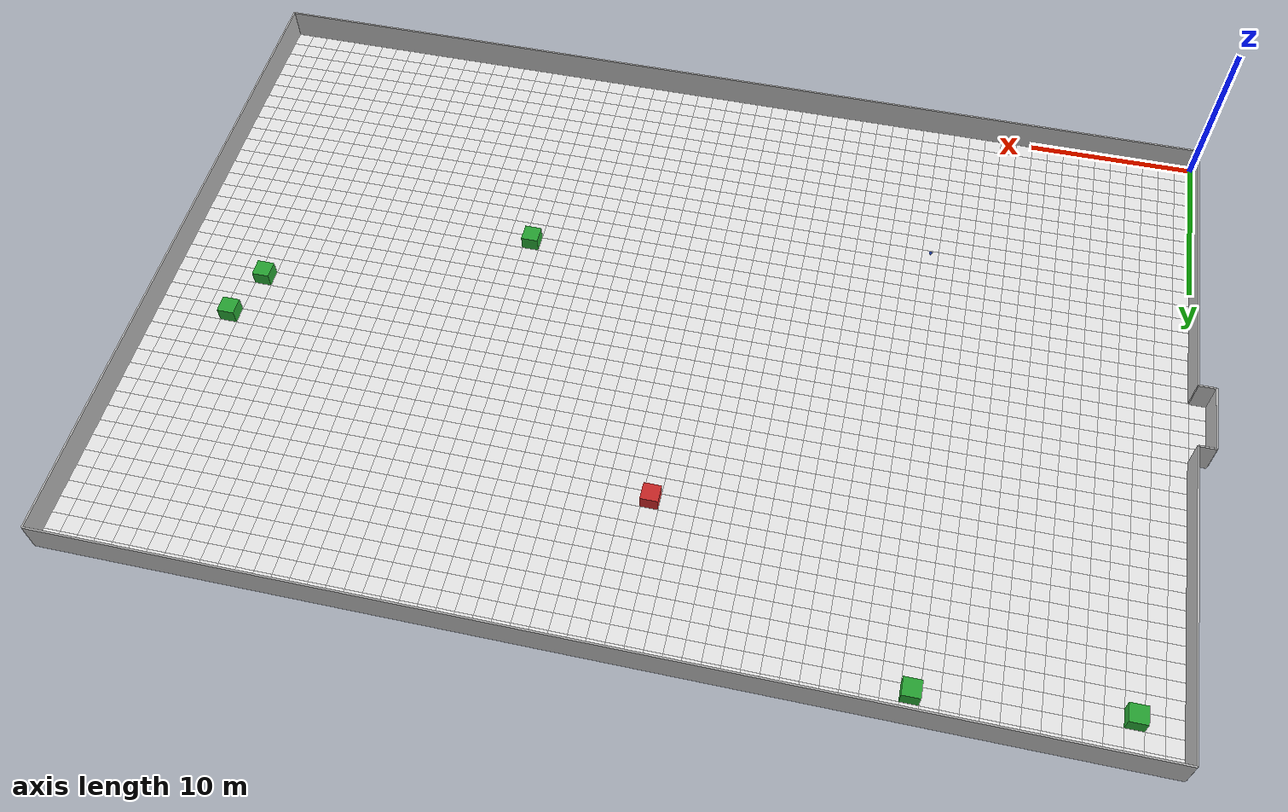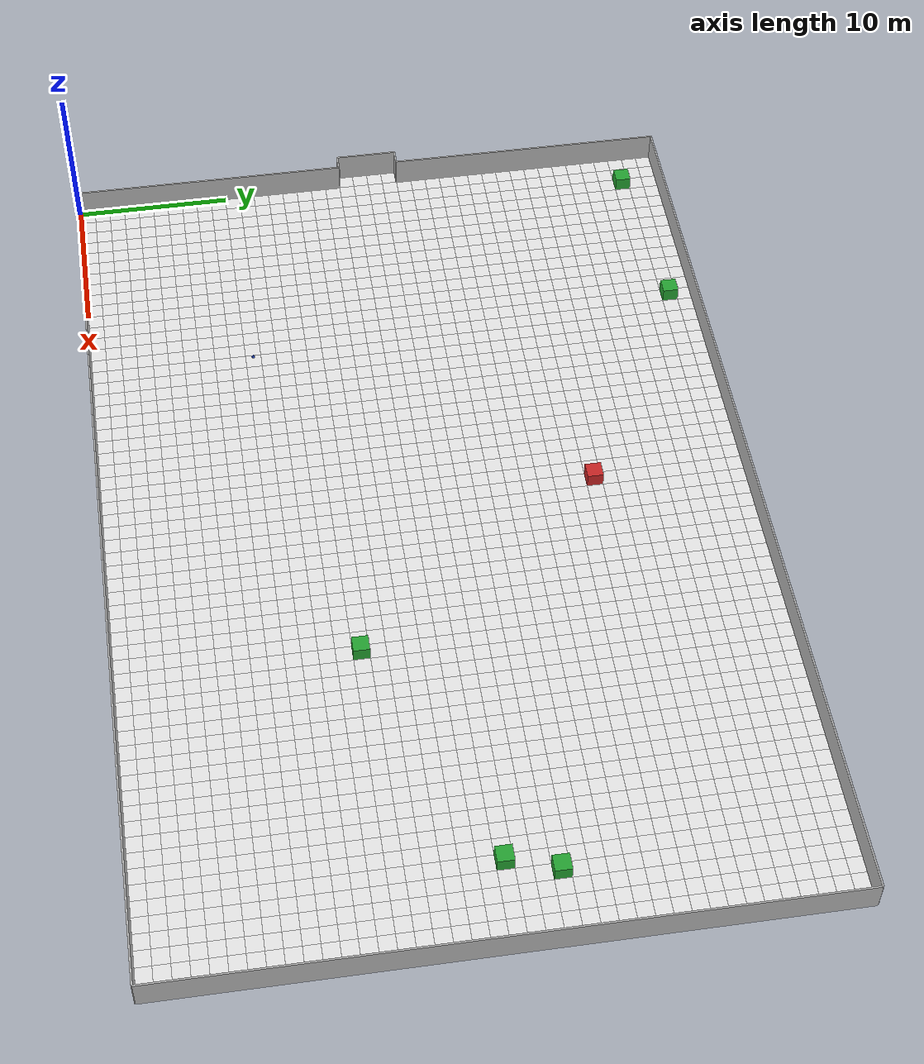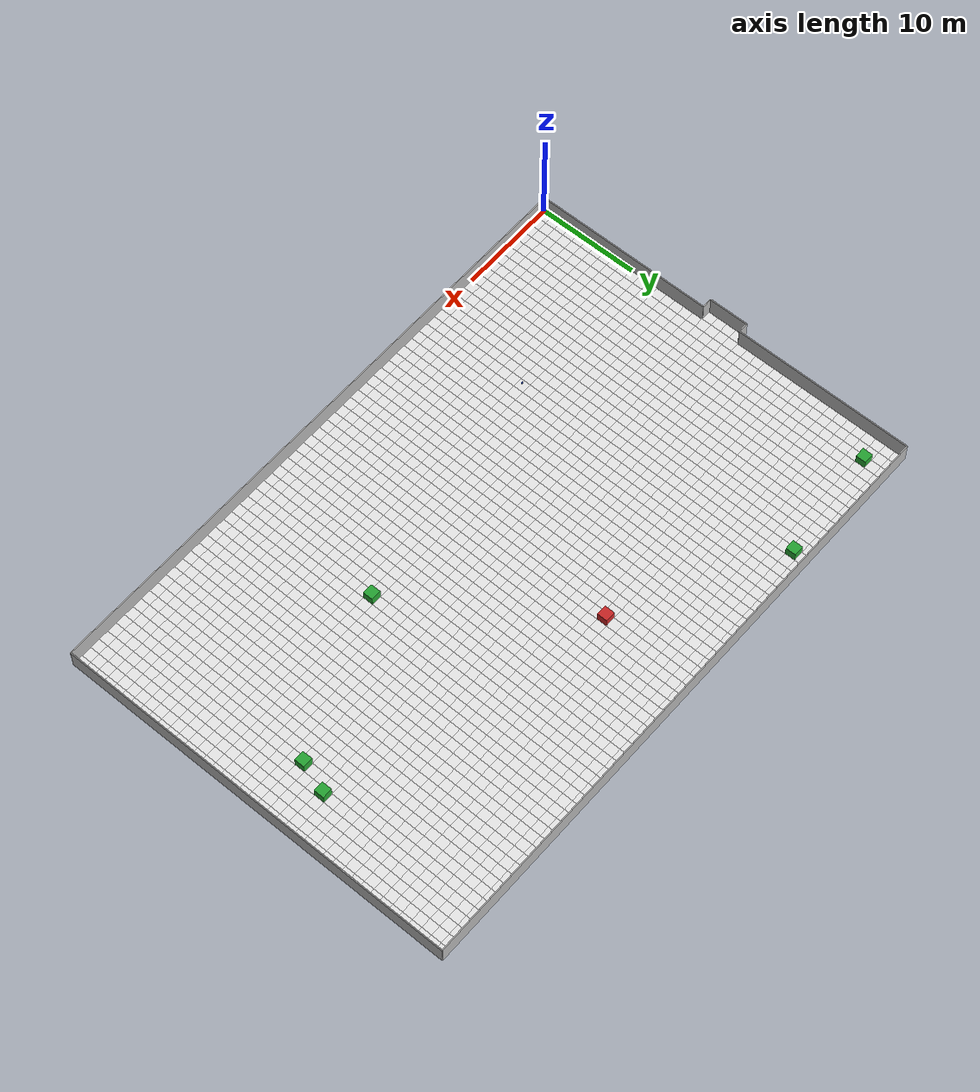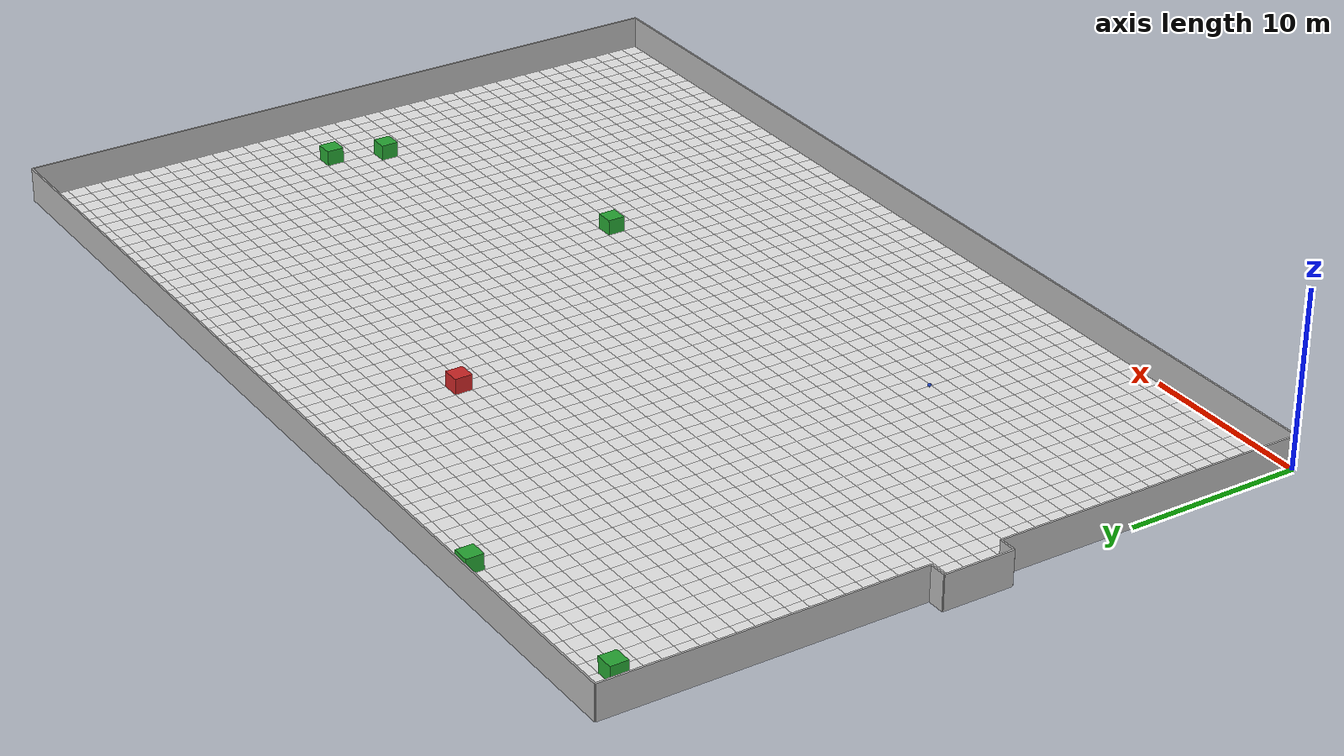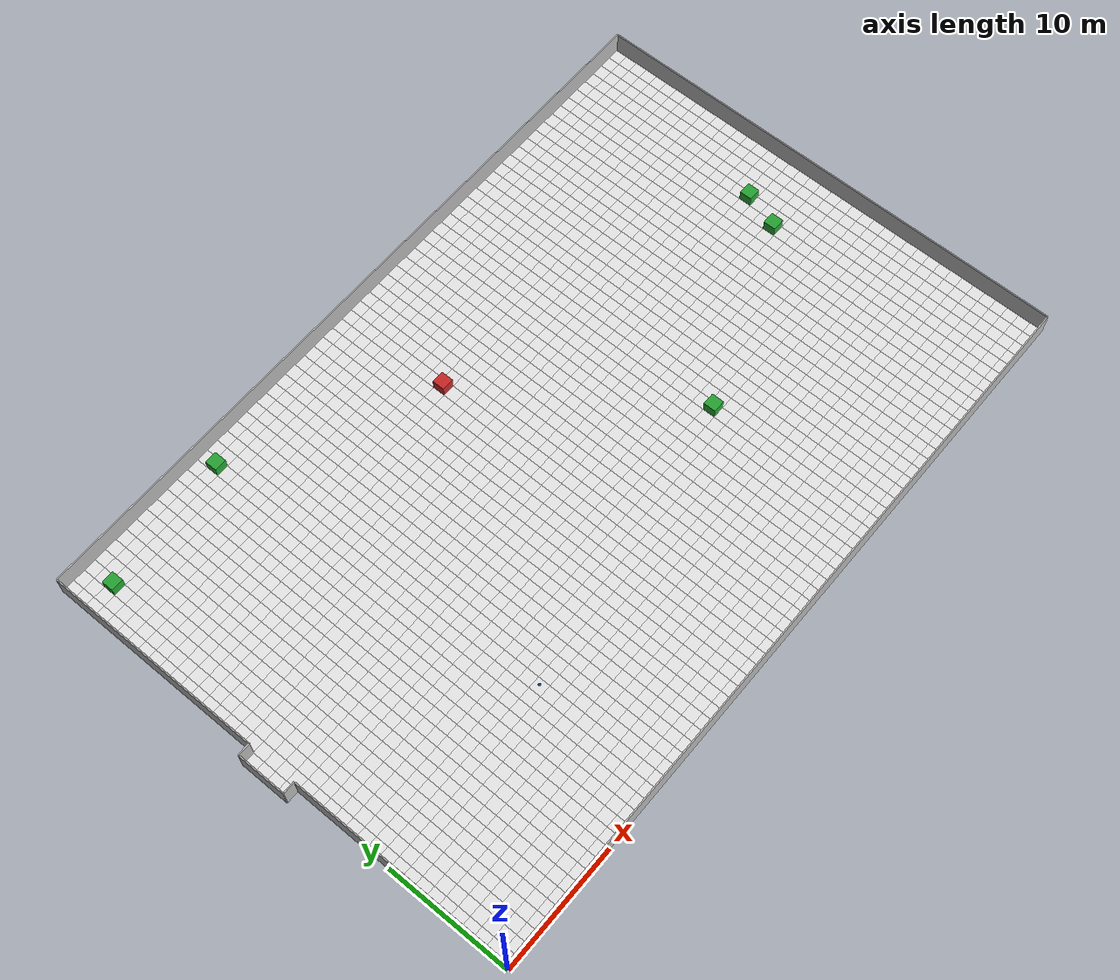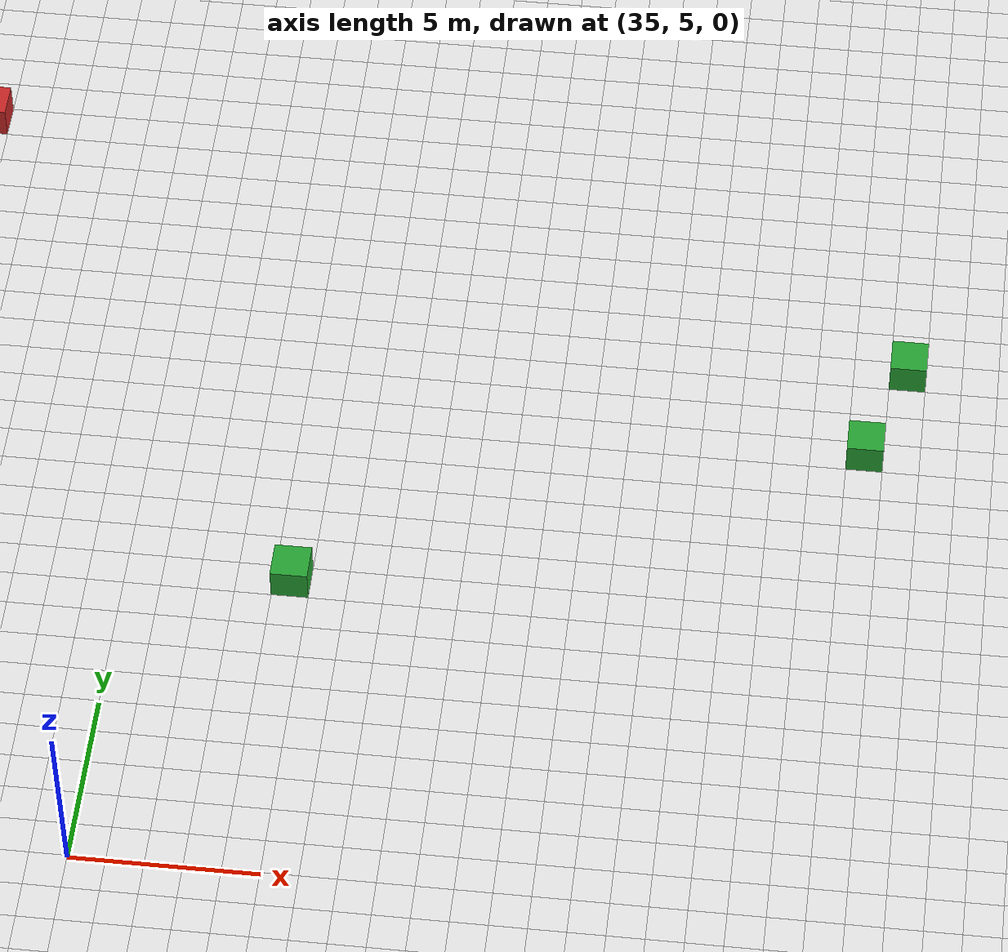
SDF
<?xml version='1.0'?>
<sdf version='1.6'>
  <world name='grid_world'>
    <light name='sun' type='directional'>
      <pose>0 0 10 0 -0 0</pose>
      <direction>-0.5 0.5 -1</direction>
    </light>
    <model name='cell_0_0'>
      <static>true</static>
      <link name='link'>
        <collision name='collision'>
          <geometry>
            <box>
              <size>1 1 0.1</size>
            </box>
          </geometry>
        </collision>
        <visual name='visual'>
          <geometry>
            <box>
              <size>1 1 0.1</size>
            </box>
          </geometry>
          <material>
            <script>
              <uri>file://media/materials/scripts/gazebo.material</uri>
              <name>Gazebo/White</name>
            </script>
          </material>
        </visual>
        <pose>0.5 0.5 0.05 0 0 0</pose>
      </link>
    </model>
    <model name='cell_1_0'>
      <static>true</static>
      <link name='link'>
        <collision name='collision'>
          <geometry>
            <box>
              <size>1 1 0.1</size>
            </box>
          </geometry>
        </collision>
        <visual name='visual'>
          <geometry>
            <box>
              <size>1 1 0.1</size>
            </box>
          </geometry>
          <material>
            <script>
              <uri>file://media/materials/scripts/gazebo.material</uri>
              <name>Gazebo/White</name>
            </script>
          </material>
        </visual>
        <pose>1.5 0.5 0.05 0 0 0</pose>
      </link>
    </model>
    <model name='cell_2_0'>
      <static>true</static>
      <link name='link'>
        <collision name='collision'>
          <geometry>
            <box>
              <size>1 1 0.1</size>
            </box>
          </geometry>
        </collision>
        <visual name='visual'>
          <geometry>
            <box>
              <size>1 1 0.1</size>
            </box>
          </geometry>
          <material>
            <script>
              <uri>file://media/materials/scripts/gazebo.material</uri>
              <name>Gazebo/White</name>
            </script>
          </material>
        </visual>
        <pose>2.5 0.5 0.05 0 0 0</pose>
      </link>
    </model>
    <model name='cell_3_0'>
      <static>true</static>
      <link name='link'>
        <collision name='collision'>
          <geometry>
            <box>
              <size>1 1 0.1</size>
            </box>
          </geometry>
        </collision>
        <visual name='visual'>
          <geometry>
            <box>
              <size>1 1 0.1</size>
            </box>
          </geometry>
          <material>
            <script>
              <uri>file://media/materials/scripts/gazebo.material</uri>
              <name>Gazebo/White</name>
            </script>
          </material>
        </visual>
        <pose>3.5 0.5 0.05 0 0 0</pose>
      </link>
    </model>
    <model name='cell_4_0'>
      <static>true</static>
      <link name='link'>
        <collision name='collision'>
          <geometry>
            <box>
              <size>1 1 0.1</size>
            </box>
          </geometry>
        </collision>
        <visual name='visual'>
          <geometry>
            <box>
              <size>1 1 0.1</size>
            </box>
          </geometry>
          <material>
            <script>
              <uri>file://media/materials/scripts/gazebo.material</uri>
              <name>Gazebo/White</name>
            </script>
          </material>
        </visual>
        <pose>4.5 0.5 0.05 0 0 0</pose>
      </link>
    </model>
    <model name='cell_5_0'>
      <static>true</static>
      <link name='link'>
        <collision name='collision'>
          <geometry>
            <box>
              <size>1 1 0.1</size>
            </box>
          </geometry>
        </collision>
        <visual name='visual'>
          <geometry>
            <box>
              <size>1 1 0.1</size>
            </box>
          </geometry>
          <material>
            <script>
              <uri>file://media/materials/scripts/gazebo.material</uri>
              <name>Gazebo/White</name>
            </script>
          </material>
        </visual>
        <pose>5.5 0.5 0.05 0 0 0</pose>
      </link>
    </model>
    <model name='cell_6_0'>
      <static>true</static>
      <link name='link'>
        <collision name='collision'>
          <geometry>
            <box>
              <size>1 1 0.1</size>
            </box>
          </geometry>
        </collision>
        <visual name='visual'>
          <geometry>
            <box>
              <size>1 1 0.1</size>
            </box>
          </geometry>
          <material>
            <script>
              <uri>file://media/materials/scripts/gazebo.material</uri>
              <name>Gazebo/White</name>
            </script>
          </material>
        </visual>
        <pose>6.5 0.5 0.05 0 0 0</pose>
      </link>
    </model>
    <model name='cell_7_0'>
      <static>true</static>
      <link name='link'>
        <collision name='collision'>
          <geometry>
            <box>
              <size>1 1 0.1</size>
            </box>
          </geometry>
        </collision>
        <visual name='visual'>
          <geometry>
            <box>
              <size>1 1 0.1</size>
            </box>
          </geometry>
          <material>
            <script>
              <uri>file://media/materials/scripts/gazebo.material</uri>
              <name>Gazebo/White</name>
            </script>
          </material>
        </visual>
        <pose>7.5 0.5 0.05 0 0 0</pose>
      </link>
    </model>
    <model name='cell_8_0'>
      <static>true</static>
      <link name='link'>
        <collision name='collision'>
          <geometry>
            <box>
              <size>1 1 0.1</size>
            </box>
          </geometry>
        </collision>
        <visual name='visual'>
          <geometry>
            <box>
              <size>1 1 0.1</size>
            </box>
          </geometry>
          <material>
            <script>
              <uri>file://media/materials/scripts/gazebo.material</uri>
              <name>Gazebo/White</name>
            </script>
          </material>
        </visual>
        <pose>8.5 0.5 0.05 0 0 0</pose>
      </link>
    </model>
    <model name='cell_9_0'>
      <static>true</static>
      <link name='link'>
        <collision name='collision'>
          <geometry>
            <box>
              <size>1 1 0.1</size>
            </box>
          </geometry>
        </collision>
        <visual name='visual'>
          <geometry>
            <box>
              <size>1 1 0.1</size>
            </box>
          </geometry>
          <material>
            <script>
              <uri>file://media/materials/scripts/gazebo.material</uri>
              <name>Gazebo/White</name>
            </script>
          </material>
        </visual>
        <pose>9.5 0.5 0.05 0 0 0</pose>
      </link>
    </model>
    <model name='cell_10_0'>
      <static>true</static>
      <link name='link'>
        <collision name='collision'>
          <geometry>
            <box>
              <size>1 1 0.1</size>
            </box>
          </geometry>
        </collision>
        <visual name='visual'>
          <geometry>
            <box>
              <size>1 1 0.1</size>
            </box>
          </geometry>
          <material>
            <script>
              <uri>file://media/materials/scripts/gazebo.material</uri>
              <name>Gazebo/White</name>
            </script>
          </material>
        </visual>
        <pose>10.5 0.5 0.05 0 0 0</pose>
      </link>
    </model>
    <model name='cell_11_0'>
      <static>true</static>
      <link name='link'>
        <collision name='collision'>
          <geometry>
            <box>
              <size>1 1 0.1</size>
            </box>
          </geometry>
        </collision>
        <visual name='visual'>
          <geometry>
            <box>
              <size>1 1 0.1</size>
            </box>
          </geometry>
          <material>
            <script>
              <uri>file://media/materials/scripts/gazebo.material</uri>
              <name>Gazebo/White</name>
            </script>
          </material>
        </visual>
        <pose>11.5 0.5 0.05 0 0 0</pose>
      </link>
    </model>
    <model name='cell_12_0'>
      <static>true</static>
      <link name='link'>
        <collision name='collision'>
          <geometry>
            <box>
              <size>1 1 0.1</size>
            </box>
          </geometry>
        </collision>
        <visual name='visual'>
          <geometry>
            <box>
              <size>1 1 0.1</size>
            </box>
          </geometry>
          <material>
            <script>
              <uri>file://media/materials/scripts/gazebo.material</uri>
              <name>Gazebo/White</name>
            </script>
          </material>
        </visual>
        <pose>12.5 0.5 0.05 0 0 0</pose>
      </link>
    </model>
    <model name='cell_13_0'>
      <static>true</static>
      <link name='link'>
        <collision name='collision'>
          <geometry>
            <box>
              <size>1 1 0.1</size>
            </box>
          </geometry>
        </collision>
        <visual name='visual'>
          <geometry>
            <box>
              <size>1 1 0.1</size>
            </box>
          </geometry>
          <material>
            <script>
              <uri>file://media/materials/scripts/gazebo.material</uri>
              <name>Gazebo/White</name>
            </script>
          </material>
        </visual>
        <pose>13.5 0.5 0.05 0 0 0</pose>
      </link>
    </model>
    <model name='cell_14_0'>
      <static>true</static>
      <link name='link'>
        <collision name='collision'>
          <geometry>
            <box>
              <size>1 1 0.1</size>
            </box>
          </geometry>
        </collision>
        <visual name='visual'>
          <geometry>
            <box>
              <size>1 1 0.1</size>
            </box>
          </geometry>
          <material>
            <script>
              <uri>file://media/materials/scripts/gazebo.material</uri>
              <name>Gazebo/White</name>
            </script>
          </material>
        </visual>
        <pose>14.5 0.5 0.05 0 0 0</pose>
      </link>
    </model>
    <model name='cell_15_0'>
      <static>true</static>
      <link name='link'>
        <collision name='collision'>
          <geometry>
            <box>
              <size>1 1 0.1</size>
            </box>
          </geometry>
        </collision>
        <visual name='visual'>
          <geometry>
            <box>
              <size>1 1 0.1</size>
            </box>
          </geometry>
          <material>
            <script>
              <uri>file://media/materials/scripts/gazebo.material</uri>
              <name>Gazebo/White</name>
            </script>
          </material>
        </visual>
        <pose>15.5 0.5 0.05 0 0 0</pose>
      </link>
    </model>
    <model name='cell_16_0'>
      <static>true</static>
      <link name='link'>
        <collision name='collision'>
          <geometry>
            <box>
              <size>1 1 0.1</size>
            </box>
          </geometry>
        </collision>
        <visual name='visual'>
          <geometry>
            <box>
              <size>1 1 0.1</size>
            </box>
          </geometry>
          <material>
            <script>
              <uri>file://media/materials/scripts/gazebo.material</uri>
              <name>Gazebo/White</name>
            </script>
          </material>
        </visual>
        <pose>16.5 0.5 0.05 0 0 0</pose>
      </link>
    </model>
    <model name='cell_17_0'>
      <static>true</static>
      <link name='link'>
        <collision name='collision'>
          <geometry>
            <box>
              <size>1 1 0.1</size>
            </box>
          </geometry>
        </collision>
        <visual name='visual'>
          <geometry>
            <box>
              <size>1 1 0.1</size>
            </box>
          </geometry>
          <material>
            <script>
              <uri>file://media/materials/scripts/gazebo.material</uri>
              <name>Gazebo/White</name>
            </script>
          </material>
        </visual>
        <pose>17.5 0.5 0.05 0 0 0</pose>
      </link>
    </model>
    <model name='cell_18_0'>
      <static>true</static>
      <link name='link'>
        <collision name='collision'>
          <geometry>
            <box>
              <size>1 1 0.1</size>
            </box>
          </geometry>
        </collision>
        <visual name='visual'>
          <geometry>
            <box>
              <size>1 1 0.1</size>
            </box>
          </geometry>
          <material>
            <script>
              <uri>file://media/materials/scripts/gazebo.material</uri>
              <name>Gazebo/White</name>
            </script>
          </material>
        </visual>
        <pose>18.5 0.5 0.05 0 0 0</pose>
      </link>
    </model>
    <model name='cell_19_0'>
      <static>true</static>
      <link name='link'>
        <collision name='collision'>
          <geometry>
            <box>
              <size>1 1 0.1</size>
            </box>
          </geometry>
        </collision>
        <visual name='visual'>
          <geometry>
            <box>
              <size>1 1 0.1</size>
            </box>
          </geometry>
          <material>
            <script>
              <uri>file://media/materials/scripts/gazebo.material</uri>
              <name>Gazebo/White</name>
            </script>
          </material>
        </visual>
        <pose>19.5 0.5 0.05 0 0 0</pose>
      </link>
    </model>
    <model name='cell_20_0'>
      <static>true</static>
      <link name='link'>
        <collision name='collision'>
          <geometry>
            <box>
              <size>1 1 0.1</size>
            </box>
          </geometry>
        </collision>
        <visual name='visual'>
          <geometry>
            <box>
              <size>1 1 0.1</size>
            </box>
          </geometry>
          <material>
            <script>
              <uri>file://media/materials/scripts/gazebo.material</uri>
              <name>Gazebo/White</name>
            </script>
          </material>
        </visual>
        <pose>20.5 0.5 0.05 0 0 0</pose>
      </link>
    </model>
    <model name='cell_21_0'>
      <static>true</static>
      <link name='link'>
        <collision name='collision'>
          <geometry>
            <box>
              <size>1 1 0.1</size>
            </box>
          </geometry>
        </collision>
        <visual name='visual'>
          <geometry>
            <box>
              <size>1 1 0.1</size>
            </box>
          </geometry>
          <material>
            <script>
              <uri>file://media/materials/scripts/gazebo.material</uri>
              <name>Gazebo/White</name>
            </script>
          </material>
        </visual>
        <pose>21.5 0.5 0.05 0 0 0</pose>
      </link>
    </model>
    <model name='cell_22_0'>
      <static>true</static>
      <link name='link'>
        <collision name='collision'>
          <geometry>
            <box>
              <size>1 1 0.1</size>
            </box>
          </geometry>
        </collision>
        <visual name='visual'>
          <geometry>
            <box>
              <size>1 1 0.1</size>
            </box>
          </geometry>
          <material>
            <script>
              <uri>file://media/materials/scripts/gazebo.material</uri>
              <name>Gazebo/White</name>
            </script>
          </material>
        </visual>
        <pose>22.5 0.5 0.05 0 0 0</pose>
      </link>
    </model>
    <model name='cell_23_0'>
      <static>true</static>
      <link name='link'>
        <collision name='collision'>
          <geometry>
            <box>
              <size>1 1 0.1</size>
            </box>
          </geometry>
        </collision>
        <visual name='visual'>
          <geometry>
            <box>
              <size>1 1 0.1</size>
            </box>
          </geometry>
          <material>
            <script>
              <uri>file://media/materials/scripts/gazebo.material</uri>
              <name>Gazebo/White</name>
            </script>
          </material>
        </visual>
        <pose>23.5 0.5 0.05 0 0 0</pose>
      </link>
    </model>
    <model name='cell_24_0'>
      <static>true</static>
      <link name='link'>
        <collision name='collision'>
          <geometry>
            <box>
              <size>1 1 0.1</size>
            </box>
          </geometry>
        </collision>
        <visual name='visual'>
          <geometry>
            <box>
              <size>1 1 0.1</size>
            </box>
          </geometry>
          <material>
            <script>
              <uri>file://media/materials/scripts/gazebo.material</uri>
              <name>Gazebo/White</name>
            </script>
          </material>
        </visual>
        <pose>24.5 0.5 0.05 0 0 0</pose>
      </link>
    </model>
    <model name='cell_25_0'>
      <static>true</static>
      <link name='link'>
        <collision name='collision'>
          <geometry>
            <box>
              <size>1 1 0.1</size>
            </box>
          </geometry>
        </collision>
        <visual name='visual'>
          <geometry>
            <box>
              <size>1 1 0.1</size>
            </box>
          </geometry>
          <material>
            <script>
              <uri>file://media/materials/scripts/gazebo.material</uri>
              <name>Gazebo/White</name>
            </script>
          </material>
        </visual>
        <pose>25.5 0.5 0.05 0 0 0</pose>
      </link>
    </model>
    <model name='cell_26_0'>
      <static>true</static>
      <link name='link'>
        <collision name='collision'>
          <geometry>
            <box>
              <size>1 1 0.1</size>
            </box>
          </geometry>
        </collision>
        <visual name='visual'>
          <geometry>
            <box>
              <size>1 1 0.1</size>
            </box>
          </geometry>
          <material>
            <script>
              <uri>file://media/materials/scripts/gazebo.material</uri>
              <name>Gazebo/White</name>
            </script>
          </material>
        </visual>
        <pose>26.5 0.5 0.05 0 0 0</pose>
      </link>
    </model>
    <model name='cell_27_0'>
      <static>true</static>
      <link name='link'>
        <collision name='collision'>
          <geometry>
            <box>
              <size>1 1 0.1</size>
            </box>
          </geometry>
        </collision>
        <visual name='visual'>
          <geometry>
            <box>
              <size>1 1 0.1</size>
            </box>
          </geometry>
          <material>
            <script>
              <uri>file://media/materials/scripts/gazebo.material</uri>
              <name>Gazebo/White</name>
            </script>
          </material>
        </visual>
        <pose>27.5 0.5 0.05 0 0 0</pose>
      </link>
    </model>
    <model name='cell_28_0'>
      <static>true</static>
      <link name='link'>
        <collision name='collision'>
          <geometry>
            <box>
              <size>1 1 0.1</size>
            </box>
          </geometry>
        </collision>
        <visual name='visual'>
          <geometry>
            <box>
              <size>1 1 0.1</size>
            </box>
          </geometry>
          <material>
            <script>
              <uri>file://media/materials/scripts/gazebo.material</uri>
              <name>Gazebo/White</name>
            </script>
          </material>
        </visual>
        <pose>28.5 0.5 0.05 0 0 0</pose>
      </link>
    </model>
    <model name='cell_29_0'>
      <static>true</static>
      <link name='link'>
        <collision name='collision'>
          <geometry>
            <box>
              <size>1 1 0.1</size>
            </box>
          </geometry>
        </collision>
        <visual name='visual'>
          <geometry>
            <box>
              <size>1 1 0.1</size>
            </box>
          </geometry>
          <material>
            <script>
              <uri>file://media/materials/scripts/gazebo.material</uri>
              <name>Gazebo/White</name>
            </script>
          </material>
        </visual>
        <pose>29.5 0.5 0.05 0 0 0</pose>
      </link>
    </model>
    <model name='cell_30_0'>
      <static>true</static>
      <link name='link'>
        <collision name='collision'>
          <geometry>
            <box>
              <size>1 1 0.1</size>
            </box>
          </geometry>
        </collision>
        <visual name='visual'>
          <geometry>
            <box>
              <size>1 1 0.1</size>
            </box>
          </geometry>
          <material>
            <script>
              <uri>file://media/materials/scripts/gazebo.material</uri>
              <name>Gazebo/White</name>
            </script>
          </material>
        </visual>
        <pose>30.5 0.5 0.05 0 0 0</pose>
      </link>
    </model>
    <model name='cell_31_0'>
      <static>true</static>
      <link name='link'>
        <collision name='collision'>
          <geometry>
            <box>
              <size>1 1 0.1</size>
            </box>
          </geometry>
        </collision>
        <visual name='visual'>
          <geometry>
            <box>
              <size>1 1 0.1</size>
            </box>
          </geometry>
          <material>
            <script>
              <uri>file://media/materials/scripts/gazebo.material</uri>
              <name>Gazebo/White</name>
            </script>
          </material>
        </visual>
        <pose>31.5 0.5 0.05 0 0 0</pose>
      </link>
    </model>
    <model name='cell_32_0'>
      <static>true</static>
      <link name='link'>
        <collision name='collision'>
          <geometry>
            <box>
              <size>1 1 0.1</size>
            </box>
          </geometry>
        </collision>
        <visual name='visual'>
          <geometry>
            <box>
              <size>1 1 0.1</size>
            </box>
          </geometry>
          <material>
            <script>
              <uri>file://media/materials/scripts/gazebo.material</uri>
              <name>Gazebo/White</name>
            </script>
          </material>
        </visual>
        <pose>32.5 0.5 0.05 0 0 0</pose>
      </link>
    </model>
    <model name='cell_33_0'>
      <static>true</static>
      <link name='link'>
        <collision name='collision'>
          <geometry>
            <box>
              <size>1 1 0.1</size>
            </box>
          </geometry>
        </collision>
        <visual name='visual'>
          <geometry>
            <box>
              <size>1 1 0.1</size>
            </box>
          </geometry>
          <material>
            <script>
              <uri>file://media/materials/scripts/gazebo.material</uri>
              <name>Gazebo/White</name>
            </script>
          </material>
        </visual>
        <pose>33.5 0.5 0.05 0 0 0</pose>
      </link>
    </model>
    <model name='cell_34_0'>
      <static>true</static>
      <link name='link'>
        <collision name='collision'>
          <geometry>
            <box>
              <size>1 1 0.1</size>
            </box>
          </geometry>
        </collision>
        <visual name='visual'>
          <geometry>
            <box>
              <size>1 1 0.1</size>
            </box>
          </geometry>
          <material>
            <script>
              <uri>file://media/materials/scripts/gazebo.material</uri>
              <name>Gazebo/White</name>
            </script>
          </material>
        </visual>
        <pose>34.5 0.5 0.05 0 0 0</pose>
      </link>
    </model>
    <model name='cell_35_0'>
      <static>true</static>
      <link name='link'>
        <collision name='collision'>
          <geometry>
            <box>
              <size>1 1 0.1</size>
            </box>
          </geometry>
        </collision>
        <visual name='visual'>
          <geometry>
            <box>
              <size>1 1 0.1</size>
            </box>
          </geometry>
          <material>
            <script>
              <uri>file://media/materials/scripts/gazebo.material</uri>
              <name>Gazebo/White</name>
            </script>
          </material>
        </visual>
        <pose>35.5 0.5 0.05 0 0 0</pose>
      </link>
    </model>
    <model name='cell_36_0'>
      <static>true</static>
      <link name='link'>
        <collision name='collision'>
          <geometry>
            <box>
              <size>1 1 0.1</size>
            </box>
          </geometry>
        </collision>
        <visual name='visual'>
          <geometry>
            <box>
              <size>1 1 0.1</size>
            </box>
          </geometry>
          <material>
            <script>
              <uri>file://media/materials/scripts/gazebo.material</uri>
              <name>Gazebo/White</name>
            </script>
          </material>
        </visual>
        <pose>36.5 0.5 0.05 0 0 0</pose>
      </link>
    </model>
    <model name='cell_37_0'>
      <static>true</static>
      <link name='link'>
        <collision name='collision'>
          <geometry>
            <box>
              <size>1 1 0.1</size>
            </box>
          </geometry>
        </collision>
        <visual name='visual'>
          <geometry>
            <box>
              <size>1 1 0.1</size>
            </box>
          </geometry>
          <material>
            <script>
              <uri>file://media/materials/scripts/gazebo.material</uri>
              <name>Gazebo/White</name>
            </script>
          </material>
        </visual>
        <pose>37.5 0.5 0.05 0 0 0</pose>
      </link>
    </model>
    <model name='cell_38_0'>
      <static>true</static>
      <link name='link'>
        <collision name='collision'>
          <geometry>
            <box>
              <size>1 1 0.1</size>
            </box>
          </geometry>
        </collision>
        <visual name='visual'>
          <geometry>
            <box>
              <size>1 1 0.1</size>
            </box>
          </geometry>
          <material>
            <script>
              <uri>file://media/materials/scripts/gazebo.material</uri>
              <name>Gazebo/White</name>
            </script>
          </material>
        </visual>
        <pose>38.5 0.5 0.05 0 0 0</pose>
      </link>
    </model>
    <model name='cell_39_0'>
      <static>true</static>
      <link name='link'>
        <collision name='collision'>
          <geometry>
            <box>
              <size>1 1 0.1</size>
            </box>
          </geometry>
        </collision>
        <visual name='visual'>
          <geometry>
            <box>
              <size>1 1 0.1</size>
            </box>
          </geometry>
          <material>
            <script>
              <uri>file://media/materials/scripts/gazebo.material</uri>
              <name>Gazebo/White</name>
            </script>
          </material>
        </visual>
        <pose>39.5 0.5 0.05 0 0 0</pose>
      </link>
    </model>
    <model name='cell_40_0'>
      <static>true</static>
      <link name='link'>
        <collision name='collision'>
          <geometry>
            <box>
              <size>1 1 0.1</size>
            </box>
          </geometry>
        </collision>
        <visual name='visual'>
          <geometry>
            <box>
              <size>1 1 0.1</size>
            </box>
          </geometry>
          <material>
            <script>
              <uri>file://media/materials/scripts/gazebo.material</uri>
              <name>Gazebo/White</name>
            </script>
          </material>
        </visual>
        <pose>40.5 0.5 0.05 0 0 0</pose>
      </link>
    </model>
    <model name='cell_41_0'>
      <static>true</static>
      <link name='link'>
        <collision name='collision'>
          <geometry>
            <box>
              <size>1 1 0.1</size>
            </box>
          </geometry>
        </collision>
        <visual name='visual'>
          <geometry>
            <box>
              <size>1 1 0.1</size>
            </box>
          </geometry>
          <material>
            <script>
              <uri>file://media/materials/scripts/gazebo.material</uri>
              <name>Gazebo/White</name>
            </script>
          </material>
        </visual>
        <pose>41.5 0.5 0.05 0 0 0</pose>
      </link>
    </model>
    <model name='cell_42_0'>
      <static>true</static>
      <link name='link'>
        <collision name='collision'>
          <geometry>
            <box>
              <size>1 1 0.1</size>
            </box>
          </geometry>
        </collision>
        <visual name='visual'>
          <geometry>
            <box>
              <size>1 1 0.1</size>
            </box>
          </geometry>
          <material>
            <script>
              <uri>file://media/materials/scripts/gazebo.material</uri>
              <name>Gazebo/White</name>
            </script>
          </material>
        </visual>
        <pose>42.5 0.5 0.05 0 0 0</pose>
      </link>
    </model>
    <model name='cell_43_0'>
      <static>true</static>
      <link name='link'>
        <collision name='collision'>
          <geometry>
            <box>
              <size>1 1 0.1</size>
            </box>
          </geometry>
        </collision>
        <visual name='visual'>
          <geometry>
            <box>
              <size>1 1 0.1</size>
            </box>
          </geometry>
          <material>
            <script>
              <uri>file://media/materials/scripts/gazebo.material</uri>
              <name>Gazebo/White</name>
            </script>
          </material>
        </visual>
        <pose>43.5 0.5 0.05 0 0 0</pose>
      </link>
    </model>
    <model name='cell_44_0'>
      <static>true</static>
      <link name='link'>
        <collision name='collision'>
          <geometry>
            <box>
              <size>1 1 0.1</size>
            </box>
          </geometry>
        </collision>
        <visual name='visual'>
          <geometry>
            <box>
              <size>1 1 0.1</size>
            </box>
          </geometry>
          <material>
            <script>
              <uri>file://media/materials/scripts/gazebo.material</uri>
              <name>Gazebo/White</name>
            </script>
          </material>
        </visual>
        <pose>44.5 0.5 0.05 0 0 0</pose>
      </link>
    </model>
    <model name='cell_45_0'>
      <static>true</static>
      <link name='link'>
        <collision name='collision'>
          <geometry>
            <box>
              <size>1 1 0.1</size>
            </box>
          </geometry>
        </collision>
        <visual name='visual'>
          <geometry>
            <box>
              <size>1 1 0.1</size>
            </box>
          </geometry>
          <material>
            <script>
              <uri>file://media/materials/scripts/gazebo.material</uri>
              <name>Gazebo/White</name>
            </script>
          </material>
        </visual>
        <pose>45.5 0.5 0.05 0 0 0</pose>
      </link>
    </model>
    <model name='cell_46_0'>
      <static>true</static>
      <link name='link'>
        <collision name='collision'>
          <geometry>
            <box>
              <size>1 1 0.1</size>
            </box>
          </geometry>
        </collision>
        <visual name='visual'>
          <geometry>
            <box>
              <size>1 1 0.1</size>
            </box>
          </geometry>
          <material>
            <script>
              <uri>file://media/materials/scripts/gazebo.material</uri>
              <name>Gazebo/White</name>
            </script>
          </material>
        </visual>
        <pose>46.5 0.5 0.05 0 0 0</pose>
      </link>
    </model>
    <model name='cell_47_0'>
      <static>true</static>
      <link name='link'>
        <collision name='collision'>
          <geometry>
            <box>
              <size>1 1 0.1</size>
            </box>
          </geometry>
        </collision>
        <visual name='visual'>
          <geometry>
            <box>
              <size>1 1 0.1</size>
            </box>
          </geometry>
          <material>
            <script>
              <uri>file://media/materials/scripts/gazebo.material</uri>
              <name>Gazebo/White</name>
            </script>
          </material>
        </visual>
        <pose>47.5 0.5 0.05 0 0 0</pose>
      </link>
    </model>
    <model name='cell_48_0'>
      <static>true</static>
      <link name='link'>
        <collision name='collision'>
          <geometry>
            <box>
              <size>1 1 0.1</size>
            </box>
          </geometry>
        </collision>
        <visual name='visual'>
          <geometry>
            <box>
              <size>1 1 0.1</size>
            </box>
          </geometry>
          <material>
            <script>
              <uri>file://media/materials/scripts/gazebo.material</uri>
              <name>Gazebo/White</name>
            </script>
          </material>
        </visual>
        <pose>48.5 0.5 0.05 0 0 0</pose>
      </link>
    </model>
    <model name='cell_49_0'>
      <static>true</static>
      <link name='link'>
        <collision name='collision'>
          <geometry>
            <box>
              <size>1 1 0.1</size>
            </box>
          </geometry>
        </collision>
        <visual name='visual'>
          <geometry>
            <box>
              <size>1 1 0.1</size>
            </box>
          </geometry>
          <material>
            <script>
              <uri>file://media/materials/scripts/gazebo.material</uri>
              <name>Gazebo/White</name>
            </script>
          </material>
        </visual>
        <pose>49.5 0.5 0.05 0 0 0</pose>
      </link>
    </model>
    <model name='cell_50_0'>
      <static>true</static>
      <link name='link'>
        <collision name='collision'>
          <geometry>
            <box>
              <size>1 1 0.1</size>
            </box>
          </geometry>
        </collision>
        <visual name='visual'>
          <geometry>
            <box>
              <size>1 1 0.1</size>
            </box>
          </geometry>
          <material>
            <script>
              <uri>file://media/materials/scripts/gazebo.material</uri>
              <name>Gazebo/White</name>
            </script>
          </material>
        </visual>
        <pose>50.5 0.5 0.05 0 0 0</pose>
      </link>
    </model>
    <model name='cell_51_0'>
      <static>true</static>
      <link name='link'>
        <collision name='collision'>
          <geometry>
            <box>
              <size>1 1 0.1</size>
            </box>
          </geometry>
        </collision>
        <visual name='visual'>
          <geometry>
            <box>
              <size>1 1 0.1</size>
            </box>
          </geometry>
          <material>
            <script>
              <uri>file://media/materials/scripts/gazebo.material</uri>
              <name>Gazebo/White</name>
            </script>
          </material>
        </visual>
        <pose>51.5 0.5 0.05 0 0 0</pose>
      </link>
    </model>
    <model name='cell_52_0'>
      <static>true</static>
      <link name='link'>
        <collision name='collision'>
          <geometry>
            <box>
              <size>1 1 0.1</size>
            </box>
          </geometry>
        </collision>
        <visual name='visual'>
          <geometry>
            <box>
              <size>1 1 0.1</size>
            </box>
          </geometry>
          <material>
            <script>
              <uri>file://media/materials/scripts/gazebo.material</uri>
              <name>Gazebo/White</name>
            </script>
          </material>
        </visual>
        <pose>52.5 0.5 0.05 0 0 0</pose>
      </link>
    </model>
    <model name='cell_53_0'>
      <static>true</static>
      <link name='link'>
        <collision name='collision'>
          <geometry>
            <box>
              <size>1 1 0.1</size>
            </box>
          </geometry>
        </collision>
        <visual name='visual'>
          <geometry>
            <box>
              <size>1 1 0.1</size>
            </box>
          </geometry>
          <material>
            <script>
              <uri>file://media/materials/scripts/gazebo.material</uri>
              <name>Gazebo/White</name>
            </script>
          </material>
        </visual>
        <pose>53.5 0.5 0.05 0 0 0</pose>
      </link>
    </model>
    <model name='cell_54_0'>
      <static>true</static>
      <link name='link'>
        <collision name='collision'>
          <geometry>
            <box>
              <size>1 1 0.1</size>
            </box>
          </geometry>
        </collision>
        <visual name='visual'>
          <geometry>
            <box>
              <size>1 1 0.1</size>
            </box>
          </geometry>
          <material>
            <script>
              <uri>file://media/materials/scripts/gazebo.material</uri>
              <name>Gazebo/White</name>
            </script>
          </material>
        </visual>
        <pose>54.5 0.5 0.05 0 0 0</pose>
      </link>
    </model>
    <model name='cell_55_0'>
      <static>true</static>
      <link name='link'>
        <collision name='collision'>
          <geometry>
            <box>
              <size>1 1 0.1</size>
            </box>
          </geometry>
        </collision>
        <visual name='visual'>
          <geometry>
            <box>
              <size>1 1 0.1</size>
            </box>
          </geometry>
          <material>
            <script>
              <uri>file://media/materials/scripts/gazebo.material</uri>
              <name>Gazebo/White</name>
            </script>
          </material>
        </visual>
        <pose>55.5 0.5 0.05 0 0 0</pose>
      </link>
    </model>
    <model name='cell_56_0'>
      <static>true</static>
      <link name='link'>
        <collision name='collision'>
          <geometry>
            <box>
              <size>1 1 0.1</size>
            </box>
          </geometry>
        </collision>
        <visual name='visual'>
          <geometry>
            <box>
              <size>1 1 0.1</size>
            </box>
          </geometry>
          <material>
            <script>
              <uri>file://media/materials/scripts/gazebo.material</uri>
              <name>Gazebo/White</name>
            </script>
          </material>
        </visual>
        <pose>56.5 0.5 0.05 0 0 0</pose>
      </link>
    </model>
    <model name='cell_57_0'>
      <static>true</static>
      <link name='link'>
        <collision name='collision'>
          <geometry>
            <box>
              <size>1 1 0.1</size>
            </box>
          </geometry>
        </collision>
        <visual name='visual'>
          <geometry>
            <box>
              <size>1 1 0.1</size>
            </box>
          </geometry>
          <material>
            <script>
              <uri>file://media/materials/scripts/gazebo.material</uri>
              <name>Gazebo/White</name>
            </script>
          </material>
        </visual>
        <pose>57.5 0.5 0.05 0 0 0</pose>
      </link>
    </model>
    <model name='cell_58_0'>
      <static>true</static>
      <link name='link'>
        <collision name='collision'>
          <geometry>
            <box>
              <size>1 1 0.1</size>
            </box>
          </geometry>
        </collision>
        <visual name='visual'>
          <geometry>
            <box>
              <size>1 1 0.1</size>
            </box>
          </geometry>
          <material>
            <script>
              <uri>file://media/materials/scripts/gazebo.material</uri>
              <name>Gazebo/White</name>
            </script>
          </material>
        </visual>
        <pose>58.5 0.5 0.05 0 0 0</pose>
      </link>
    </model>
    <model name='cell_59_0'>
      <static>true</static>
      <link name='link'>
        <collision name='collision'>
          <geometry>
            <box>
              <size>1 1 0.1</size>
            </box>
          </geometry>
        </collision>
        <visual name='visual'>
          <geometry>
            <box>
              <size>1 1 0.1</size>
            </box>
          </geometry>
          <material>
            <script>
              <uri>file://media/materials/scripts/gazebo.material</uri>
              <name>Gazebo/White</name>
            </script>
          </material>
        </visual>
        <pose>59.5 0.5 0.05 0 0 0</pose>
      </link>
    </model>
    <model name='cell_0_1'>
      <static>true</static>
      <link name='link'>
        <collision name='collision'>
          <geometry>
            <box>
              <size>1 1 0.1</size>
            </box>
          </geometry>
        </collision>
        <visual name='visual'>
          <geometry>
            <box>
              <size>1 1 0.1</size>
            </box>
          </geometry>
          <material>
            <script>
              <uri>file://media/materials/scripts/gazebo.material</uri>
              <name>Gazebo/White</name>
            </script>
          </material>
        </visual>
        <pose>0.5 1.5 0.05 0 0 0</pose>
      </link>
    </model>
    <model name='cell_1_1'>
      <static>true</static>
      <link name='link'>
        <collision name='collision'>
          <geometry>
            <box>
              <size>1 1 0.1</size>
            </box>
          </geometry>
        </collision>
        <visual name='visual'>
          <geometry>
            <box>
              <size>1 1 0.1</size>
            </box>
          </geometry>
          <material>
            <script>
              <uri>file://media/materials/scripts/gazebo.material</uri>
              <name>Gazebo/White</name>
            </script>
          </material>
        </visual>
        <pose>1.5 1.5 0.05 0 0 0</pose>
      </link>
    </model>
    <model name='cell_2_1'>
      <static>true</static>
      <link name='link'>
        <collision name='collision'>
          <geometry>
            <box>
              <size>1 1 0.1</size>
            </box>
          </geometry>
        </collision>
        <visual name='visual'>
          <geometry>
            <box>
              <size>1 1 0.1</size>
            </box>
          </geometry>
          <material>
            <script>
              <uri>file://media/materials/scripts/gazebo.material</uri>
              <name>Gazebo/White</name>
            </script>
          </material>
        </visual>
        <pose>2.5 1.5 0.05 0 0 0</pose>
      </link>
    </model>
    <model name='cell_3_1'>
      <static>true</static>
      <link name='link'>
        <collision name='collision'>
          <geometry>
            <box>
              <size>1 1 0.1</size>
            </box>
          </geometry>
        </collision>
        <visual name='visual'>
          <geometry>
            <box>
              <size>1 1 0.1</size>
            </box>
          </geometry>
          <material>
            <script>
              <uri>file://media/materials/scripts/gazebo.material</uri>
              <name>Gazebo/White</name>
            </script>
          </material>
        </visual>
        <pose>3.5 1.5 0.05 0 0 0</pose>
      </link>
    </model>
    <model name='cell_4_1'>
      <static>true</static>
      <link name='link'>
        <collision name='collision'>
          <geometry>
            <box>
              <size>1 1 0.1</size>
            </box>
          </geometry>
        </collision>
        <visual name='visual'>
          <geometry>
            <box>
              <size>1 1 0.1</size>
            </box>
          </geometry>
          <material>
            <script>
              <uri>file://media/materials/scripts/gazebo.material</uri>
              <name>Gazebo/White</name>
            </script>
          </material>
        </visual>
        <pose>4.5 1.5 0.05 0 0 0</pose>
      </link>
    </model>
    <model name='cell_5_1'>
      <static>true</static>
      <link name='link'>
        <collision name='collision'>
          <geometry>
            <box>
              <size>1 1 0.1</size>
            </box>
          </geometry>
        </collision>
        <visual name='visual'>
          <geometry>
            <box>
              <size>1 1 0.1</size>
            </box>
          </geometry>
          <material>
            <script>
              <uri>file://media/materials/scripts/gazebo.material</uri>
              <name>Gazebo/White</name>
            </script>
          </material>
        </visual>
        <pose>5.5 1.5 0.05 0 0 0</pose>
      </link>
    </model>
    <model name='cell_6_1'>
      <static>true</static>
      <link name='link'>
        <collision name='collision'>
          <geometry>
            <box>
              <size>1 1 0.1</size>
            </box>
          </geometry>
        </collision>
        <visual name='visual'>
          <geometry>
            <box>
              <size>1 1 0.1</size>
            </box>
          </geometry>
          <material>
            <script>
              <uri>file://media/materials/scripts/gazebo.material</uri>
              <name>Gazebo/White</name>
            </script>
          </material>
        </visual>
        <pose>6.5 1.5 0.05 0 0 0</pose>
      </link>
    </model>
    <model name='cell_7_1'>
      <static>true</static>
      <link name='link'>
        <collision name='collision'>
          <geometry>
            <box>
              <size>1 1 0.1</size>
            </box>
          </geometry>
        </collision>
        <visual name='visual'>
          <geometry>
            <box>
              <size>1 1 0.1</size>
            </box>
          </geometry>
          <material>
            <script>
              <uri>file://media/materials/scripts/gazebo.material</uri>
              <name>Gazebo/White</name>
            </script>
          </material>
        </visual>
        <pose>7.5 1.5 0.05 0 0 0</pose>
      </link>
    </model>
    <model name='cell_8_1'>
      <static>true</static>
      <link name='link'>
        <collision name='collision'>
          <geometry>
            <box>
              <size>1 1 0.1</size>
            </box>
          </geometry>
        </collision>
        <visual name='visual'>
          <geometry>
            <box>
              <size>1 1 0.1</size>
            </box>
          </geometry>
          <material>
            <script>
              <uri>file://media/materials/scripts/gazebo.material</uri>
              <name>Gazebo/White</name>
            </script>
          </material>
        </visual>
        <pose>8.5 1.5 0.05 0 0 0</pose>
      </link>
    </model>
    <model name='cell_9_1'>
      <static>true</static>
      <link name='link'>
        <collision name='collision'>
          <geometry>
            <box>
              <size>1 1 0.1</size>
            </box>
          </geometry>
        </collision>
        <visual name='visual'>
          <geometry>
            <box>
              <size>1 1 0.1</size>
            </box>
          </geometry>
          <material>
            <script>
              <uri>file://media/materials/scripts/gazebo.material</uri>
              <name>Gazebo/White</name>
            </script>
          </material>
        </visual>
        <pose>9.5 1.5 0.05 0 0 0</pose>
      </link>
    </model>
    <model name='cell_10_1'>
      <static>true</static>
      <link name='link'>
        <collision name='collision'>
          <geometry>
            <box>
              <size>1 1 0.1</size>
            </box>
          </geometry>
        </collision>
        <visual name='visual'>
          <geometry>
            <box>
              <size>1 1 0.1</size>
            </box>
          </geometry>
          <material>
            <script>
              <uri>file://media/materials/scripts/gazebo.material</uri>
              <name>Gazebo/White</name>
            </script>
          </material>
        </visual>
        <pose>10.5 1.5 0.05 0 0 0</pose>
      </link>
    </model>
    <model name='cell_11_1'>
      <static>true</static>
      <link name='link'>
        <collision name='collision'>
          <geometry>
            <box>
              <size>1 1 0.1</size>
            </box>
          </geometry>
        </collision>
        <visual name='visual'>
          <geometry>
            <box>
              <size>1 1 0.1</size>
            </box>
          </geometry>
          <material>
            <script>
              <uri>file://media/materials/scripts/gazebo.material</uri>
              <name>Gazebo/White</name>
            </script>
          </material>
        </visual>
        <pose>11.5 1.5 0.05 0 0 0</pose>
      </link>
    </model>
    <model name='cell_12_1'>
      <static>true</static>
      <link name='link'>
        <collision name='collision'>
          <geometry>
            <box>
              <size>1 1 0.1</size>
            </box>
          </geometry>
        </collision>
        <visual name='visual'>
          <geometry>
            <box>
              <size>1 1 0.1</size>
            </box>
          </geometry>
          <material>
            <script>
              <uri>file://media/materials/scripts/gazebo.material</uri>
              <name>Gazebo/White</name>
            </script>
          </material>
        </visual>
        <pose>12.5 1.5 0.05 0 0 0</pose>
      </link>
    </model>
    <model name='cell_13_1'>
      <static>true</static>
      <link name='link'>
        <collision name='collision'>
          <geometry>
            <box>
              <size>1 1 0.1</size>
            </box>
          </geometry>
        </collision>
        <visual name='visual'>
          <geometry>
            <box>
              <size>1 1 0.1</size>
            </box>
          </geometry>
          <material>
            <script>
              <uri>file://media/materials/scripts/gazebo.material</uri>
              <name>Gazebo/White</name>
            </script>
          </material>
        </visual>
        <pose>13.5 1.5 0.05 0 0 0</pose>
      </link>
    </model>
    <model name='cell_14_1'>
      <static>true</static>
      <link name='link'>
        <collision name='collision'>
          <geometry>
            <box>
              <size>1 1 0.1</size>
            </box>
          </geometry>
        </collision>
        <visual name='visual'>
          <geometry>
            <box>
              <size>1 1 0.1</size>
            </box>
          </geometry>
          <material>
            <script>
              <uri>file://media/materials/scripts/gazebo.material</uri>
              <name>Gazebo/White</name>
            </script>
          </material>
        </visual>
        <pose>14.5 1.5 0.05 0 0 0</pose>
      </link>
    </model>
    <model name='cell_15_1'>
      <static>true</static>
      <link name='link'>
        <collision name='collision'>
          <geometry>
            <box>
              <size>1 1 0.1</size>
            </box>
          </geometry>
        </collision>
        <visual name='visual'>
          <geometry>
            <box>
              <size>1 1 0.1</size>
            </box>
          </geometry>
          <material>
            <script>
              <uri>file://media/materials/scripts/gazebo.material</uri>
              <name>Gazebo/White</name>
            </script>
          </material>
        </visual>
        <pose>15.5 1.5 0.05 0 0 0</pose>
      </link>
    </model>
    <model name='cell_16_1'>
      <static>true</static>
      <link name='link'>
        <collision name='collision'>
          <geometry>
            <box>
              <size>1 1 0.1</size>
            </box>
          </geometry>
        </collision>
        <visual name='visual'>
          <geometry>
            <box>
              <size>1 1 0.1</size>
            </box>
          </geometry>
          <material>
            <script>
              <uri>file://media/materials/scripts/gazebo.material</uri>
              <name>Gazebo/White</name>
            </script>
          </material>
        </visual>
        <pose>16.5 1.5 0.05 0 0 0</pose>
      </link>
    </model>
    <model name='cell_17_1'>
      <static>true</static>
      <link name='link'>
        <collision name='collision'>
          <geometry>
            <box>
              <size>1 1 0.1</size>
            </box>
          </geometry>
        </collision>
        <visual name='visual'>
          <geometry>
            <box>
              <size>1 1 0.1</size>
            </box>
          </geometry>
          <material>
            <script>
              <uri>file://media/materials/scripts/gazebo.material</uri>
              <name>Gazebo/White</name>
            </script>
          </material>
        </visual>
        <pose>17.5 1.5 0.05 0 0 0</pose>
      </link>
    </model>
    <model name='cell_18_1'>
      <static>true</static>
      <link name='link'>
        <collision name='collision'>
          <geometry>
            <box>
              <size>1 1 0.1</size>
            </box>
          </geometry>
        </collision>
        <visual name='visual'>
          <geometry>
            <box>
              <size>1 1 0.1</size>
            </box>
          </geometry>
          <material>
            <script>
              <uri>file://media/materials/scripts/gazebo.material</uri>
              <name>Gazebo/White</name>
            </script>
          </material>
        </visual>
        <pose>18.5 1.5 0.05 0 0 0</pose>
      </link>
    </model>
    <model name='cell_19_1'>
      <static>true</static>
      <link name='link'>
        <collision name='collision'>
          <geometry>
            <box>
              <size>1 1 0.1</size>
            </box>
          </geometry>
        </collision>
        <visual name='visual'>
          <geometry>
            <box>
              <size>1 1 0.1</size>
            </box>
          </geometry>
          <material>
            <script>
              <uri>file://media/materials/scripts/gazebo.material</uri>
              <name>Gazebo/White</name>
            </script>
          </material>
        </visual>
        <pose>19.5 1.5 0.05 0 0 0</pose>
      </link>
    </model>
    <model name='cell_20_1'>
      <static>true</static>
      <link name='link'>
        <collision name='collision'>
          <geometry>
            <box>
              <size>1 1 0.1</size>
            </box>
          </geometry>
        </collision>
        <visual name='visual'>
          <geometry>
            <box>
              <size>1 1 0.1</size>
            </box>
          </geometry>
          <material>
            <script>
              <uri>file://media/materials/scripts/gazebo.material</uri>
              <name>Gazebo/White</name>
            </script>
          </material>
        </visual>
        <pose>20.5 1.5 0.05 0 0 0</pose>
      </link>
    </model>
    <model name='cell_21_1'>
      <static>true</static>
      <link name='link'>
        <collision name='collision'>
          <geometry>
            <box>
              <size>1 1 0.1</size>
            </box>
          </geometry>
        </collision>
        <visual name='visual'>
          <geometry>
            <box>
              <size>1 1 0.1</size>
            </box>
          </geometry>
          <material>
            <script>
              <uri>file://media/materials/scripts/gazebo.material</uri>
              <name>Gazebo/White</name>
            </script>
          </material>
        </visual>
        <pose>21.5 1.5 0.05 0 0 0</pose>
      </link>
    </model>
    <model name='cell_22_1'>
      <static>true</static>
      <link name='link'>
        <collision name='collision'>
          <geometry>
            <box>
              <size>1 1 0.1</size>
            </box>
          </geometry>
        </collision>
        <visual name='visual'>
          <geometry>
            <box>
              <size>1 1 0.1</size>
            </box>
          </geometry>
          <material>
            <script>
              <uri>file://media/materials/scripts/gazebo.material</uri>
              <name>Gazebo/White</name>
            </script>
          </material>
        </visual>
        <pose>22.5 1.5 0.05 0 0 0</pose>
      </link>
    </model>
    <model name='cell_23_1'>
      <static>true</static>
      <link name='link'>
        <collision name='collision'>
          <geometry>
            <box>
              <size>1 1 0.1</size>
            </box>
          </geometry>
        </collision>
        <visual name='visual'>
          <geometry>
            <box>
              <size>1 1 0.1</size>
            </box>
          </geometry>
          <material>
            <script>
              <uri>file://media/materials/scripts/gazebo.material</uri>
              <name>Gazebo/White</name>
            </script>
          </material>
        </visual>
        <pose>23.5 1.5 0.05 0 0 0</pose>
      </link>
    </model>
    <model name='cell_24_1'>
      <static>true</static>
      <link name='link'>
        <collision name='collision'>
          <geometry>
            <box>
              <size>1 1 0.1</size>
            </box>
          </geometry>
        </collision>
        <visual name='visual'>
          <geometry>
            <box>
              <size>1 1 0.1</size>
            </box>
          </geometry>
          <material>
            <script>
              <uri>file://media/materials/scripts/gazebo.material</uri>
              <name>Gazebo/White</name>
            </script>
          </material>
        </visual>
        <pose>24.5 1.5 0.05 0 0 0</pose>
      </link>
    </model>
    <model name='cell_25_1'>
      <static>true</static>
      <link name='link'>
        <collision name='collision'>
          <geometry>
            <box>
              <size>1 1 0.1</size>
            </box>
          </geometry>
        </collision>
        <visual name='visual'>
          <geometry>
            <box>
              <size>1 1 0.1</size>
            </box>
          </geometry>
          <material>
            <script>
              <uri>file://media/materials/scripts/gazebo.material</uri>
              <name>Gazebo/White</name>
            </script>
          </material>
        </visual>
        <pose>25.5 1.5 0.05 0 0 0</pose>
      </link>
    </model>
    <model name='cell_26_1'>
      <static>true</static>
      <link name='link'>
        <collision name='collision'>
          <geometry>
            <box>
              <size>1 1 0.1</size>
            </box>
          </geometry>
        </collision>
        <visual name='visual'>
          <geometry>
            <box>
              <size>1 1 0.1</size>
            </box>
          </geometry>
          <material>
            <script>
              <uri>file://media/materials/scripts/gazebo.material</uri>
              <name>Gazebo/White</name>
            </script>
          </material>
        </visual>
        <pose>26.5 1.5 0.05 0 0 0</pose>
      </link>
    </model>
    <model name='cell_27_1'>
      <static>true</static>
      <link name='link'>
        <collision name='collision'>
          <geometry>
            <box>
              <size>1 1 0.1</size>
            </box>
          </geometry>
        </collision>
        <visual name='visual'>
          <geometry>
            <box>
              <size>1 1 0.1</size>
            </box>
          </geometry>
          <material>
            <script>
              <uri>file://media/materials/scripts/gazebo.material</uri>
              <name>Gazebo/White</name>
            </script>
          </material>
        </visual>
        <pose>27.5 1.5 0.05 0 0 0</pose>
      </link>
    </model>
    <model name='cell_28_1'>
      <static>true</static>
      <link name='link'>
        <collision name='collision'>
          <geometry>
            <box>
              <size>1 1 0.1</size>
            </box>
          </geometry>
        </collision>
        <visual name='visual'>
          <geometry>
            <box>
              <size>1 1 0.1</size>
            </box>
          </geometry>
          <material>
            <script>
              <uri>file://media/materials/scripts/gazebo.material</uri>
              <name>Gazebo/White</name>
            </script>
          </material>
        </visual>
        <pose>28.5 1.5 0.05 0 0 0</pose>
      </link>
    </model>
    <model name='cell_29_1'>
      <static>true</static>
      <link name='link'>
        <collision name='collision'>
          <geometry>
            <box>
              <size>1 1 0.1</size>
            </box>
          </geometry>
        </collision>
        <visual name='visual'>
          <geometry>
            <box>
              <size>1 1 0.1</size>
            </box>
          </geometry>
          <material>
            <script>
              <uri>file://media/materials/scripts/gazebo.material</uri>
              <name>Gazebo/White</name>
            </script>
          </material>
        </visual>
        <pose>29.5 1.5 0.05 0 0 0</pose>
      </link>
    </model>
    <model name='cell_30_1'>
      <static>true</static>
      <link name='link'>
        <collision name='collision'>
          <geometry>
            <box>
              <size>1 1 0.1</size>
            </box>
          </geometry>
        </collision>
        <visual name='visual'>
          <geometry>
            <box>
              <size>1 1 0.1</size>
            </box>
          </geometry>
          <material>
            <script>
              <uri>file://media/materials/scripts/gazebo.material</uri>
              <name>Gazebo/White</name>
            </script>
          </material>
        </visual>
        <pose>30.5 1.5 0.05 0 0 0</pose>
      </link>
    </model>
    <model name='cell_31_1'>
      <static>true</static>
      <link name='link'>
        <collision name='collision'>
          <geometry>
            <box>
              <size>1 1 0.1</size>
            </box>
          </geometry>
        </collision>
        <visual name='visual'>
          <geometry>
            <box>
              <size>1 1 0.1</size>
            </box>
          </geometry>
          <material>
            <script>
              <uri>file://media/materials/scripts/gazebo.material</uri>
              <name>Gazebo/White</name>
            </script>
          </material>
        </visual>
        <pose>31.5 1.5 0.05 0 0 0</pose>
      </link>
    </model>
    <model name='cell_32_1'>
      <static>true</static>
      <link name='link'>
        <collision name='collision'>
          <geometry>
            <box>
              <size>1 1 0.1</size>
            </box>
          </geometry>
        </collision>
        <visual name='visual'>
          <geometry>
            <box>
              <size>1 1 0.1</size>
            </box>
          </geometry>
          <material>
            <script>
              <uri>file://media/materials/scripts/gazebo.material</uri>
              <name>Gazebo/White</name>
            </script>
          </material>
        </visual>
        <pose>32.5 1.5 0.05 0 0 0</pose>
      </link>
    </model>
    <model name='cell_33_1'>
      <static>true</static>
      <link name='link'>
        <collision name='collision'>
          <geometry>
            <box>
              <size>1 1 0.1</size>
            </box>
          </geometry>
        </collision>
        <visual name='visual'>
          <geometry>
            <box>
              <size>1 1 0.1</size>
            </box>
          </geometry>
          <material>
            <script>
              <uri>file://media/materials/scripts/gazebo.material</uri>
              <name>Gazebo/White</name>
            </script>
          </material>
        </visual>
        <pose>33.5 1.5 0.05 0 0 0</pose>
      </link>
    </model>
    <model name='cell_34_1'>
      <static>true</static>
      <link name='link'>
        <collision name='collision'>
          <geometry>
            <box>
              <size>1 1 0.1</size>
            </box>
          </geometry>
        </collision>
        <visual name='visual'>
          <geometry>
            <box>
              <size>1 1 0.1</size>
            </box>
          </geometry>
          <material>
            <script>
              <uri>file://media/materials/scripts/gazebo.material</uri>
              <name>Gazebo/White</name>
            </script>
          </material>
        </visual>
        <pose>34.5 1.5 0.05 0 0 0</pose>
      </link>
    </model>
    <model name='cell_35_1'>
      <static>true</static>
      <link name='link'>
        <collision name='collision'>
          <geometry>
            <box>
              <size>1 1 0.1</size>
            </box>
          </geometry>
        </collision>
        <visual name='visual'>
          <geometry>
            <box>
              <size>1 1 0.1</size>
            </box>
          </geometry>
          <material>
            <script>
              <uri>file://media/materials/scripts/gazebo.material</uri>
              <name>Gazebo/White</name>
            </script>
          </material>
        </visual>
        <pose>35.5 1.5 0.05 0 0 0</pose>
      </link>
    </model>
    <model name='cell_36_1'>
      <static>true</static>
      <link name='link'>
        <collision name='collision'>
          <geometry>
            <box>
              <size>1 1 0.1</size>
            </box>
          </geometry>
        </collision>
        <visual name='visual'>
          <geometry>
            <box>
              <size>1 1 0.1</size>
            </box>
          </geometry>
          <material>
            <script>
              <uri>file://media/materials/scripts/gazebo.material</uri>
              <name>Gazebo/White</name>
            </script>
          </material>
        </visual>
        <pose>36.5 1.5 0.05 0 0 0</pose>
      </link>
    </model>
    <model name='cell_37_1'>
      <static>true</static>
      <link name='link'>
        <collision name='collision'>
          <geometry>
            <box>
              <size>1 1 0.1</size>
            </box>
          </geometry>
        </collision>
        <visual name='visual'>
          <geometry>
            <box>
              <size>1 1 0.1</size>
            </box>
          </geometry>
          <material>
            <script>
              <uri>file://media/materials/scripts/gazebo.material</uri>
              <name>Gazebo/White</name>
            </script>
          </material>
        </visual>
        <pose>37.5 1.5 0.05 0 0 0</pose>
      </link>
    </model>
    <model name='cell_38_1'>
      <static>true</static>
      <link name='link'>
        <collision name='collision'>
          <geometry>
            <box>
              <size>1 1 0.1</size>
            </box>
          </geometry>
        </collision>
        <visual name='visual'>
          <geometry>
            <box>
              <size>1 1 0.1</size>
            </box>
          </geometry>
          <material>
            <script>
              <uri>file://media/materials/scripts/gazebo.material</uri>
              <name>Gazebo/White</name>
            </script>
          </material>
        </visual>
        <pose>38.5 1.5 0.05 0 0 0</pose>
      </link>
    </model>
    <model name='cell_39_1'>
      <static>true</static>
      <link name='link'>
        <collision name='collision'>
          <geometry>
            <box>
              <size>1 1 0.1</size>
            </box>
          </geometry>
        </collision>
        <visual name='visual'>
          <geometry>
            <box>
              <size>1 1 0.1</size>
            </box>
          </geometry>
          <material>
            <script>
              <uri>file://media/materials/scripts/gazebo.material</uri>
              <name>Gazebo/White</name>
            </script>
          </material>
        </visual>
        <pose>39.5 1.5 0.05 0 0 0</pose>
      </link>
    </model>
    <model name='cell_40_1'>
      <static>true</static>
      <link name='link'>
        <collision name='collision'>
          <geometry>
            <box>
              <size>1 1 0.1</size>
            </box>
          </geometry>
        </collision>
        <visual name='visual'>
          <geometry>
            <box>
              <size>1 1 0.1</size>
            </box>
          </geometry>
          <material>
            <script>
              <uri>file://media/materials/scripts/gazebo.material</uri>
              <name>Gazebo/White</name>
            </script>
          </material>
        </visual>
        <pose>40.5 1.5 0.05 0 0 0</pose>
      </link>
    </model>
    <model name='cell_41_1'>
      <static>true</static>
      <link name='link'>
        <collision name='collision'>
          <geometry>
            <box>
              <size>1 1 0.1</size>
            </box>
          </geometry>
        </collision>
        <visual name='visual'>
          <geometry>
            <box>
              <size>1 1 0.1</size>
            </box>
          </geometry>
          <material>
            <script>
              <uri>file://media/materials/scripts/gazebo.material</uri>
              <name>Gazebo/White</name>
            </script>
          </material>
        </visual>
        <pose>41.5 1.5 0.05 0 0 0</pose>
      </link>
    </model>
    <model name='cell_42_1'>
      <static>true</static>
      <link name='link'>
        <collision name='collision'>
          <geometry>
            <box>
              <size>1 1 0.1</size>
            </box>
          </geometry>
        </collision>
        <visual name='visual'>
          <geometry>
            <box>
              <size>1 1 0.1</size>
            </box>
          </geometry>
          <material>
            <script>
              <uri>file://media/materials/scripts/gazebo.material</uri>
              <name>Gazebo/White</name>
            </script>
          </material>
        </visual>
        <pose>42.5 1.5 0.05 0 0 0</pose>
      </link>
    </model>
    <model name='cell_43_1'>
      <static>true</static>
      <link name='link'>
        <collision name='collision'>
          <geometry>
            <box>
              <size>1 1 0.1</size>
            </box>
          </geometry>
        </collision>
        <visual name='visual'>
          <geometry>
            <box>
              <size>1 1 0.1</size>
            </box>
          </geometry>
          <material>
            <script>
              <uri>file://media/materials/scripts/gazebo.material</uri>
              <name>Gazebo/White</name>
            </script>
          </material>
        </visual>
        <pose>43.5 1.5 0.05 0 0 0</pose>
      </link>
    </model>
    <model name='cell_44_1'>
      <static>true</static>
      <link name='link'>
        <collision name='collision'>
          <geometry>
            <box>
              <size>1 1 0.1</size>
            </box>
          </geometry>
        </collision>
        <visual name='visual'>
          <geometry>
            <box>
              <size>1 1 0.1</size>
            </box>
          </geometry>
          <material>
            <script>
              <uri>file://media/materials/scripts/gazebo.material</uri>
              <name>Gazebo/White</name>
            </script>
          </material>
        </visual>
        <pose>44.5 1.5 0.05 0 0 0</pose>
      </link>
    </model>
    <model name='cell_45_1'>
      <static>true</static>
      <link name='link'>
        <collision name='collision'>
          <geometry>
            <box>
              <size>1 1 0.1</size>
            </box>
          </geometry>
        </collision>
        <visual name='visual'>
          <geometry>
            <box>
              <size>1 1 0.1</size>
            </box>
          </geometry>
          <material>
            <script>
              <uri>file://media/materials/scripts/gazebo.material</uri>
              <name>Gazebo/White</name>
            </script>
          </material>
        </visual>
        <pose>45.5 1.5 0.05 0 0 0</pose>
      </link>
    </model>
    <model name='cell_46_1'>
      <static>true</static>
      <link name='link'>
        <collision name='collision'>
          <geometry>
            <box>
              <size>1 1 0.1</size>
            </box>
          </geometry>
        </collision>
        <visual name='visual'>
          <geometry>
            <box>
              <size>1 1 0.1</size>
            </box>
          </geometry>
          <material>
            <script>
              <uri>file://media/materials/scripts/gazebo.material</uri>
              <name>Gazebo/White</name>
            </script>
          </material>
        </visual>
        <pose>46.5 1.5 0.05 0 0 0</pose>
      </link>
    </model>
    <model name='cell_47_1'>
      <static>true</static>
      <link name='link'>
        <collision name='collision'>
          <geometry>
            <box>
              <size>1 1 0.1</size>
            </box>
          </geometry>
        </collision>
        <visual name='visual'>
          <geometry>
            <box>
              <size>1 1 0.1</size>
            </box>
          </geometry>
          <material>
            <script>
              <uri>file://media/materials/scripts/gazebo.material</uri>
              <name>Gazebo/White</name>
            </script>
          </material>
        </visual>
        <pose>47.5 1.5 0.05 0 0 0</pose>
      </link>
    </model>
    <model name='cell_48_1'>
      <static>true</static>
      <link name='link'>
        <collision name='collision'>
          <geometry>
            <box>
              <size>1 1 0.1</size>
            </box>
          </geometry>
        </collision>
        <visual name='visual'>
          <geometry>
            <box>
              <size>1 1 0.1</size>
            </box>
          </geometry>
          <material>
            <script>
              <uri>file://media/materials/scripts/gazebo.material</uri>
              <name>Gazebo/White</name>
            </script>
          </material>
        </visual>
        <pose>48.5 1.5 0.05 0 0 0</pose>
      </link>
    </model>
    <model name='cell_49_1'>
      <static>true</static>
      <link name='link'>
        <collision name='collision'>
          <geometry>
            <box>
              <size>1 1 0.1</size>
            </box>
          </geometry>
        </collision>
        <visual name='visual'>
          <geometry>
            <box>
              <size>1 1 0.1</size>
            </box>
          </geometry>
          <material>
            <script>
              <uri>file://media/materials/scripts/gazebo.material</uri>
              <name>Gazebo/White</name>
            </script>
          </material>
        </visual>
        <pose>49.5 1.5 0.05 0 0 0</pose>
      </link>
    </model>
    <model name='cell_50_1'>
      <static>true</static>
      <link name='link'>
        <collision name='collision'>
          <geometry>
            <box>
              <size>1 1 0.1</size>
            </box>
          </geometry>
        </collision>
        <visual name='visual'>
          <geometry>
            <box>
              <size>1 1 0.1</size>
            </box>
          </geometry>
          <material>
            <script>
              <uri>file://media/materials/scripts/gazebo.material</uri>
              <name>Gazebo/White</name>
            </script>
          </material>
        </visual>
        <pose>50.5 1.5 0.05 0 0 0</pose>
      </link>
    </model>
    <model name='cell_51_1'>
      <static>true</static>
      <link name='link'>
        <collision name='collision'>
          <geometry>
            <box>
              <size>1 1 0.1</size>
            </box>
          </geometry>
        </collision>
        <visual name='visual'>
          <geometry>
            <box>
              <size>1 1 0.1</size>
            </box>
          </geometry>
          <material>
            <script>
              <uri>file://media/materials/scripts/gazebo.material</uri>
              <name>Gazebo/White</name>
            </script>
          </material>
        </visual>
        <pose>51.5 1.5 0.05 0 0 0</pose>
      </link>
    </model>
    <model name='cell_52_1'>
      <static>true</static>
      <link name='link'>
        <collision name='collision'>
          <geometry>
            <box>
              <size>1 1 0.1</size>
            </box>
          </geometry>
        </collision>
        <visual name='visual'>
          <geometry>
            <box>
              <size>1 1 0.1</size>
            </box>
          </geometry>
          <material>
            <script>
              <uri>file://media/materials/scripts/gazebo.material</uri>
              <name>Gazebo/White</name>
            </script>
          </material>
        </visual>
        <pose>52.5 1.5 0.05 0 0 0</pose>
      </link>
    </model>
    <model name='cell_53_1'>
      <static>true</static>
      <link name='link'>
        <collision name='collision'>
          <geometry>
            <box>
              <size>1 1 0.1</size>
            </box>
          </geometry>
        </collision>
        <visual name='visual'>
          <geometry>
            <box>
              <size>1 1 0.1</size>
            </box>
          </geometry>
          <material>
            <script>
              <uri>file://media/materials/scripts/gazebo.material</uri>
              <name>Gazebo/White</name>
            </script>
          </material>
        </visual>
        <pose>53.5 1.5 0.05 0 0 0</pose>
      </link>
    </model>
    <model name='cell_54_1'>
      <static>true</static>
      <link name='link'>
        <collision name='collision'>
          <geometry>
            <box>
              <size>1 1 0.1</size>
            </box>
          </geometry>
        </collision>
        <visual name='visual'>
          <geometry>
            <box>
              <size>1 1 0.1</size>
            </box>
          </geometry>
          <material>
            <script>
              <uri>file://media/materials/scripts/gazebo.material</uri>
              <name>Gazebo/White</name>
            </script>
          </material>
        </visual>
        <pose>54.5 1.5 0.05 0 0 0</pose>
      </link>
    </model>
    <model name='cell_55_1'>
      <static>true</static>
      <link name='link'>
        <collision name='collision'>
          <geometry>
            <box>
              <size>1 1 0.1</size>
            </box>
          </geometry>
        </collision>
        <visual name='visual'>
          <geometry>
            <box>
              <size>1 1 0.1</size>
            </box>
          </geometry>
          <material>
            <script>
              <uri>file://media/materials/scripts/gazebo.material</uri>
              <name>Gazebo/White</name>
            </script>
          </material>
        </visual>
        <pose>55.5 1.5 0.05 0 0 0</pose>
      </link>
    </model>
    <model name='cell_56_1'>
      <static>true</static>
      <link name='link'>
        <collision name='collision'>
          <geometry>
            <box>
              <size>1 1 0.1</size>
            </box>
          </geometry>
        </collision>
        <visual name='visual'>
          <geometry>
            <box>
              <size>1 1 0.1</size>
            </box>
          </geometry>
          <material>
            <script>
              <uri>file://media/materials/scripts/gazebo.material</uri>
              <name>Gazebo/White</name>
            </script>
          </material>
        </visual>
        <pose>56.5 1.5 0.05 0 0 0</pose>
      </link>
    </model>
    <model name='cell_57_1'>
      <static>true</static>
      <link name='link'>
        <collision name='collision'>
          <geometry>
            <box>
              <size>1 1 0.1</size>
            </box>
          </geometry>
        </collision>
        <visual name='visual'>
          <geometry>
            <box>
              <size>1 1 0.1</size>
            </box>
          </geometry>
          <material>
            <script>
              <uri>file://media/materials/scripts/gazebo.material</uri>
              <name>Gazebo/White</name>
            </script>
          </material>
        </visual>
        <pose>57.5 1.5 0.05 0 0 0</pose>
      </link>
    </model>
    <model name='cell_58_1'>
      <static>true</static>
      <link name='link'>
        <collision name='collision'>
          <geometry>
            <box>
              <size>1 1 0.1</size>
            </box>
          </geometry>
        </collision>
        <visual name='visual'>
          <geometry>
            <box>
              <size>1 1 0.1</size>
            </box>
          </geometry>
          <material>
            <script>
              <uri>file://media/materials/scripts/gazebo.material</uri>
              <name>Gazebo/White</name>
            </script>
          </material>
        </visual>
        <pose>58.5 1.5 0.05 0 0 0</pose>
      </link>
    </model>
    <model name='cell_59_1'>
      <static>true</static>
      <link name='link'>
        <collision name='collision'>
          <geometry>
            <box>
              <size>1 1 0.1</size>
            </box>
          </geometry>
        </collision>
        <visual name='visual'>
          <geometry>
            <box>
              <size>1 1 0.1</size>
            </box>
          </geometry>
          <material>
            <script>
              <uri>file://media/materials/scripts/gazebo.material</uri>
              <name>Gazebo/White</name>
            </script>
          </material>
        </visual>
        <pose>59.5 1.5 0.05 0 0 0</pose>
      </link>
    </model>
    <model name='cell_0_2'>
      <static>true</static>
      <link name='link'>
        <collision name='collision'>
          <geometry>
            <box>
              <size>1 1 0.1</size>
            </box>
          </geometry>
        </collision>
        <visual name='visual'>
          <geometry>
            <box>
              <size>1 1 0.1</size>
            </box>
          </geometry>
          <material>
            <script>
              <uri>file://media/materials/scripts/gazebo.material</uri>
              <name>Gazebo/White</name>
            </script>
          </material>
        </visual>
        <pose>0.5 2.5 0.05 0 0 0</pose>
      </link>
    </model>
    <model name='cell_1_2'>
      <static>true</static>
      <link name='link'>
        <collision name='collision'>
          <geometry>
            <box>
              <size>1 1 0.1</size>
            </box>
          </geometry>
        </collision>
        <visual name='visual'>
          <geometry>
            <box>
              <size>1 1 0.1</size>
            </box>
          </geometry>
          <material>
            <script>
              <uri>file://media/materials/scripts/gazebo.material</uri>
              <name>Gazebo/White</name>
            </script>
          </material>
        </visual>
        <pose>1.5 2.5 0.05 0 0 0</pose>
      </link>
    </model>
    <model name='cell_2_2'>
      <static>true</static>
      <link name='link'>
        <collision name='collision'>
          <geometry>
            <box>
              <size>1 1 0.1</size>
            </box>
          </geometry>
        </collision>
        <visual name='visual'>
          <geometry>
            <box>
              <size>1 1 0.1</size>
            </box>
          </geometry>
          <material>
            <script>
              <uri>file://media/materials/scripts/gazebo.material</uri>
              <name>Gazebo/White</name>
            </script>
          </material>
        </visual>
        <pose>2.5 2.5 0.05 0 0 0</pose>
      </link>
    </model>
    <model name='cell_3_2'>
      <static>true</static>
      <link name='link'>
        <collision name='collision'>
          <geometry>
            <box>
              <size>1 1 0.1</size>
            </box>
          </geometry>
        </collision>
        <visual name='visual'>
          <geometry>
            <box>
              <size>1 1 0.1</size>
            </box>
          </geometry>
          <material>
            <script>
              <uri>file://media/materials/scripts/gazebo.material</uri>
              <name>Gazebo/White</name>
            </script>
          </material>
        </visual>
        <pose>3.5 2.5 0.05 0 0 0</pose>
      </link>
    </model>
    <model name='cell_4_2'>
      <static>true</static>
      <link name='link'>
        <collision name='collision'>
          <geometry>
            <box>
              <size>1 1 0.1</size>
            </box>
          </geometry>
        </collision>
        <visual name='visual'>
          <geometry>
            <box>
              <size>1 1 0.1</size>
            </box>
          </geometry>
          <material>
            <script>
              <uri>file://media/materials/scripts/gazebo.material</uri>
              <name>Gazebo/White</name>
            </script>
          </material>
        </visual>
        <pose>4.5 2.5 0.05 0 0 0</pose>
      </link>
    </model>
    <model name='cell_5_2'>
      <static>true</static>
      <link name='link'>
        <collision name='collision'>
          <geometry>
            <box>
              <size>1 1 0.1</size>
            </box>
          </geometry>
        </collision>
        <visual name='visual'>
          <geometry>
            <box>
              <size>1 1 0.1</size>
            </box>
          </geometry>
          <material>
            <script>
              <uri>file://media/materials/scripts/gazebo.material</uri>
              <name>Gazebo/White</name>
            </script>
          </material>
        </visual>
        <pose>5.5 2.5 0.05 0 0 0</pose>
      </link>
    </model>
    <model name='cell_6_2'>
      <static>true</static>
      <link name='link'>
        <collision name='collision'>
          <geometry>
            <box>
              <size>1 1 0.1</size>
            </box>
          </geometry>
        </collision>
        <visual name='visual'>
          <geometry>
            <box>
              <size>1 1 0.1</size>
            </box>
          </geometry>
          <material>
            <script>
              <uri>file://media/materials/scripts/gazebo.material</uri>
              <name>Gazebo/White</name>
            </script>
          </material>
        </visual>
        <pose>6.5 2.5 0.05 0 0 0</pose>
      </link>
    </model>
    <model name='cell_7_2'>
      <static>true</static>
      <link name='link'>
        <collision name='collision'>
          <geometry>
            <box>
              <size>1 1 0.1</size>
            </box>
          </geometry>
        </collision>
        <visual name='visual'>
          <geometry>
            <box>
              <size>1 1 0.1</size>
            </box>
          </geometry>
          <material>
            <script>
              <uri>file://media/materials/scripts/gazebo.material</uri>
              <name>Gazebo/White</name>
            </script>
          </material>
        </visual>
        <pose>7.5 2.5 0.05 0 0 0</pose>
      </link>
    </model>
    <model name='cell_8_2'>
      <static>true</static>
      <link name='link'>
        <collision name='collision'>
          <geometry>
            <box>
              <size>1 1 0.1</size>
            </box>
          </geometry>
        </collision>
        <visual name='visual'>
          <geometry>
            <box>
              <size>1 1 0.1</size>
            </box>
          </geometry>
          <material>
            <script>
              <uri>file://media/materials/scripts/gazebo.material</uri>
              <name>Gazebo/White</name>
            </script>
          </material>
        </visual>
        <pose>8.5 2.5 0.05 0 0 0</pose>
      </link>
    </model>
    <model name='cell_9_2'>
      <static>true</static>
      <link name='link'>
        <collision name='collision'>
          <geometry>
            <box>
              <size>1 1 0.1</size>
            </box>
          </geometry>
        </collision>
        <visual name='visual'>
          <geometry>
            <box>
              <size>1 1 0.1</size>
            </box>
          </geometry>
          <material>
            <script>
              <uri>file://media/materials/scripts/gazebo.material</uri>
              <name>Gazebo/White</name>
            </script>
          </material>
        </visual>
        <pose>9.5 2.5 0.05 0 0 0</pose>
      </link>
    </model>
    <model name='cell_10_2'>
      <static>true</static>
      <link name='link'>
        <collision name='collision'>
          <geometry>
            <box>
              <size>1 1 0.1</size>
            </box>
          </geometry>
        </collision>
        <visual name='visual'>
          <geometry>
            <box>
              <size>1 1 0.1</size>
            </box>
          </geometry>
          <material>
            <script>
              <uri>file://media/materials/scripts/gazebo.material</uri>
              <name>Gazebo/White</name>
            </script>
          </material>
        </visual>
        <pose>10.5 2.5 0.05 0 0 0</pose>
      </link>
    </model>
    <model name='cell_11_2'>
      <static>true</static>
      <link name='link'>
        <collision name='collision'>
          <geometry>
            <box>
              <size>1 1 0.1</size>
            </box>
          </geometry>
        </collision>
        <visual name='visual'>
          <geometry>
            <box>
              <size>1 1 0.1</size>
            </box>
          </geometry>
          <material>
            <script>
              <uri>file://media/materials/scripts/gazebo.material</uri>
              <name>Gazebo/White</name>
            </script>
          </material>
        </visual>
        <pose>11.5 2.5 0.05 0 0 0</pose>
      </link>
    </model>
    <model name='cell_12_2'>
      <static>true</static>
      <link name='link'>
        <collision name='collision'>
          <geometry>
            <box>
              <size>1 1 0.1</size>
            </box>
          </geometry>
        </collision>
        <visual name='visual'>
          <geometry>
            <box>
              <size>1 1 0.1</size>
            </box>
          </geometry>
          <material>
            <script>
              <uri>file://media/materials/scripts/gazebo.material</uri>
              <name>Gazebo/White</name>
            </script>
          </material>
        </visual>
        <pose>12.5 2.5 0.05 0 0 0</pose>
      </link>
    </model>
    <model name='cell_13_2'>
      <static>true</static>
      <link name='link'>
        <collision name='collision'>
          <geometry>
            <box>
              <size>1 1 0.1</size>
            </box>
          </geometry>
        </collision>
        <visual name='visual'>
          <geometry>
            <box>
              <size>1 1 0.1</size>
            </box>
          </geometry>
          <material>
            <script>
              <uri>file://media/materials/scripts/gazebo.material</uri>
              <name>Gazebo/White</name>
            </script>
          </material>
        </visual>
        <pose>13.5 2.5 0.05 0 0 0</pose>
      </link>
    </model>
    <model name='cell_14_2'>
      <static>true</static>
      <link name='link'>
        <collision name='collision'>
          <geometry>
            <box>
              <size>1 1 0.1</size>
            </box>
          </geometry>
        </collision>
        <visual name='visual'>
          <geometry>
            <box>
              <size>1 1 0.1</size>
            </box>
          </geometry>
          <material>
            <script>
              <uri>file://media/materials/scripts/gazebo.material</uri>
              <name>Gazebo/White</name>
            </script>
          </material>
        </visual>
        <pose>14.5 2.5 0.05 0 0 0</pose>
      </link>
    </model>
    <model name='cell_15_2'>
      <static>true</static>
      <link name='link'>
        <collision name='collision'>
          <geometry>
            <box>
              <size>1 1 0.1</size>
            </box>
          </geometry>
        </collision>
        <visual name='visual'>
          <geometry>
            <box>
              <size>1 1 0.1</size>
            </box>
          </geometry>
          <material>
            <script>
              <uri>file://media/materials/scripts/gazebo.material</uri>
              <name>Gazebo/White</name>
            </script>
          </material>
        </visual>
        <pose>15.5 2.5 0.05 0 0 0</pose>
      </link>
    </model>
    <model name='cell_16_2'>
      <static>true</static>
      <link name='link'>
        <collision name='collision'>
          <geometry>
            <box>
              <size>1 1 0.1</size>
            </box>
          </geometry>
        </collision>
        <visual name='visual'>
          <geometry>
            <box>
              <size>1 1 0.1</size>
            </box>
          </geometry>
          <material>
            <script>
              <uri>file://media/materials/scripts/gazebo.material</uri>
              <name>Gazebo/White</name>
            </script>
          </material>
        </visual>
        <pose>16.5 2.5 0.05 0 0 0</pose>
      </link>
    </model>
    <model name='cell_17_2'>
      <static>true</static>
      <link name='link'>
        <collision name='collision'>
          <geometry>
            <box>
              <size>1 1 0.1</size>
            </box>
          </geometry>
        </collision>
        <visual name='visual'>
          <geometry>
            <box>
              <size>1 1 0.1</size>
            </box>
          </geometry>
          <material>
            <script>
              <uri>file://media/materials/scripts/gazebo.material</uri>
              <name>Gazebo/White</name>
            </script>
          </material>
        </visual>
        <pose>17.5 2.5 0.05 0 0 0</pose>
      </link>
    </model>
    <model name='cell_18_2'>
      <static>true</static>
      <link name='link'>
        <collision name='collision'>
          <geometry>
            <box>
              <size>1 1 0.1</size>
            </box>
          </geometry>
        </collision>
        <visual name='visual'>
          <geometry>
            <box>
              <size>1 1 0.1</size>
            </box>
          </geometry>
          <material>
            <script>
              <uri>file://media/materials/scripts/gazebo.material</uri>
              <name>Gazebo/White</name>
            </script>
          </material>
        </visual>
        <pose>18.5 2.5 0.05 0 0 0</pose>
      </link>
    </model>
    <model name='cell_19_2'>
      <static>true</static>
      <link name='link'>
        <collision name='collision'>
          <geometry>
            <box>
              <size>1 1 0.1</size>
            </box>
          </geometry>
        </collision>
        <visual name='visual'>
          <geometry>
            <box>
              <size>1 1 0.1</size>
            </box>
          </geometry>
          <material>
            <script>
              <uri>file://media/materials/scripts/gazebo.material</uri>
              <name>Gazebo/White</name>
            </script>
          </material>
        </visual>
        <pose>19.5 2.5 0.05 0 0 0</pose>
      </link>
    </model>
    <model name='cell_20_2'>
      <static>true</static>
      <link name='link'>
        <collision name='collision'>
          <geometry>
            <box>
              <size>1 1 0.1</size>
            </box>
          </geometry>
        </collision>
        <visual name='visual'>
          <geometry>
            <box>
              <size>1 1 0.1</size>
            </box>
          </geometry>
          <material>
            <script>
              <uri>file://media/materials/scripts/gazebo.material</uri>
              <name>Gazebo/White</name>
            </script>
          </material>
        </visual>
        <pose>20.5 2.5 0.05 0 0 0</pose>
      </link>
    </model>
    <model name='cell_21_2'>
      <static>true</static>
      <link name='link'>
        <collision name='collision'>
          <geometry>
            <box>
              <size>1 1 0.1</size>
            </box>
          </geometry>
        </collision>
        <visual name='visual'>
          <geometry>
            <box>
              <size>1 1 0.1</size>
            </box>
          </geometry>
          <material>
            <script>
              <uri>file://media/materials/scripts/gazebo.material</uri>
              <name>Gazebo/White</name>
            </script>
          </material>
        </visual>
        <pose>21.5 2.5 0.05 0 0 0</pose>
      </link>
    </model>
    <model name='cell_22_2'>
      <static>true</static>
      <link name='link'>
        <collision name='collision'>
          <geometry>
            <box>
              <size>1 1 0.1</size>
            </box>
          </geometry>
        </collision>
        <visual name='visual'>
          <geometry>
            <box>
              <size>1 1 0.1</size>
            </box>
          </geometry>
          <material>
            <script>
              <uri>file://media/materials/scripts/gazebo.material</uri>
              <name>Gazebo/White</name>
            </script>
          </material>
        </visual>
        <pose>22.5 2.5 0.05 0 0 0</pose>
      </link>
    </model>
    <model name='cell_23_2'>
      <static>true</static>
      <link name='link'>
        <collision name='collision'>
          <geometry>
            <box>
              <size>1 1 0.1</size>
            </box>
          </geometry>
        </collision>
        <visual name='visual'>
          <geometry>
            <box>
              <size>1 1 0.1</size>
            </box>
          </geometry>
          <material>
            <script>
              <uri>file://media/materials/scripts/gazebo.material</uri>
              <name>Gazebo/White</name>
            </script>
          </material>
        </visual>
        <pose>23.5 2.5 0.05 0 0 0</pose>
      </link>
    </model>
    <model name='cell_24_2'>
      <static>true</static>
      <link name='link'>
        <collision name='collision'>
          <geometry>
            <box>
              <size>1 1 0.1</size>
            </box>
          </geometry>
        </collision>
        <visual name='visual'>
          <geometry>
            <box>
              <size>1 1 0.1</size>
            </box>
          </geometry>
          <material>
            <script>
              <uri>file://media/materials/scripts/gazebo.material</uri>
              <name>Gazebo/White</name>
            </script>
          </material>
        </visual>
        <pose>24.5 2.5 0.05 0 0 0</pose>
      </link>
    </model>
    <model name='cell_25_2'>
      <static>true</static>
      <link name='link'>
        <collision name='collision'>
          <geometry>
            <box>
              <size>1 1 0.1</size>
            </box>
          </geometry>
        </collision>
        <visual name='visual'>
          <geometry>
            <box>
              <size>1 1 0.1</size>
            </box>
          </geometry>
          <material>
            <script>
              <uri>file://media/materials/scripts/gazebo.material</uri>
              <name>Gazebo/White</name>
            </script>
          </material>
        </visual>
        <pose>25.5 2.5 0.05 0 0 0</pose>
      </link>
    </model>
    <model name='cell_26_2'>
      <static>true</static>
      <link name='link'>
        <collision name='collision'>
          <geometry>
            <box>
              <size>1 1 0.1</size>
            </box>
          </geometry>
        </collision>
        <visual name='visual'>
          <geometry>
            <box>
              <size>1 1 0.1</size>
            </box>
          </geometry>
          <material>
            <script>
              <uri>file://media/materials/scripts/gazebo.material</uri>
              <name>Gazebo/White</name>
            </script>
          </material>
        </visual>
        <pose>26.5 2.5 0.05 0 0 0</pose>
      </link>
    </model>
    <model name='cell_27_2'>
      <static>true</static>
      <link name='link'>
        <collision name='collision'>
          <geometry>
            <box>
              <size>1 1 0.1</size>
            </box>
          </geometry>
        </collision>
        <visual name='visual'>
          <geometry>
            <box>
              <size>1 1 0.1</size>
            </box>
          </geometry>
          <material>
            <script>
              <uri>file://media/materials/scripts/gazebo.material</uri>
              <name>Gazebo/White</name>
            </script>
          </material>
        </visual>
        <pose>27.5 2.5 0.05 0 0 0</pose>
      </link>
    </model>
    <model name='cell_28_2'>
      <static>true</static>
      <link name='link'>
        <collision name='collision'>
          <geometry>
            <box>
              <size>1 1 0.1</size>
            </box>
          </geometry>
        </collision>
        <visual name='visual'>
          <geometry>
            <box>
              <size>1 1 0.1</size>
            </box>
          </geometry>
          <material>
            <script>
              <uri>file://media/materials/scripts/gazebo.material</uri>
              <name>Gazebo/White</name>
            </script>
          </material>
        </visual>
        <pose>28.5 2.5 0.05 0 0 0</pose>
      </link>
    </model>
    <model name='cell_29_2'>
      <static>true</static>
      <link name='link'>
        <collision name='collision'>
          <geometry>
            <box>
              <size>1 1 0.1</size>
            </box>
          </geometry>
        </collision>
        <visual name='visual'>
          <geometry>
            <box>
              <size>1 1 0.1</size>
            </box>
          </geometry>
          <material>
            <script>
              <uri>file://media/materials/scripts/gazebo.material</uri>
              <name>Gazebo/White</name>
            </script>
          </material>
        </visual>
        <pose>29.5 2.5 0.05 0 0 0</pose>
      </link>
    </model>
    <model name='cell_30_2'>
      <static>true</static>
      <link name='link'>
        <collision name='collision'>
          <geometry>
            <box>
              <size>1 1 0.1</size>
            </box>
          </geometry>
        </collision>
        <visual name='visual'>
          <geometry>
            <box>
              <size>1 1 0.1</size>
            </box>
          </geometry>
          <material>
            <script>
              <uri>file://media/materials/scripts/gazebo.material</uri>
              <name>Gazebo/White</name>
            </script>
          </material>
        </visual>
        <pose>30.5 2.5 0.05 0 0 0</pose>
      </link>
    </model>
    <model name='cell_31_2'>
      <static>true</static>
      <link name='link'>
        <collision name='collision'>
          <geometry>
            <box>
              <size>1 1 0.1</size>
            </box>
          </geometry>
        </collision>
        <visual name='visual'>
          <geometry>
            <box>
              <size>1 1 0.1</size>
            </box>
          </geometry>
          <material>
            <script>
              <uri>file://media/materials/scripts/gazebo.material</uri>
              <name>Gazebo/White</name>
            </script>
          </material>
        </visual>
        <pose>31.5 2.5 0.05 0 0 0</pose>
      </link>
    </model>
    <model name='cell_32_2'>
      <static>true</static>
      <link name='link'>
        <collision name='collision'>
          <geometry>
            <box>
              <size>1 1 0.1</size>
            </box>
          </geometry>
        </collision>
        <visual name='visual'>
          <geometry>
            <box>
              <size>1 1 0.1</size>
            </box>
          </geometry>
          <material>
            <script>
              <uri>file://media/materials/scripts/gazebo.material</uri>
              <name>Gazebo/White</name>
            </script>
          </material>
        </visual>
        <pose>32.5 2.5 0.05 0 0 0</pose>
      </link>
    </model>
    <model name='cell_33_2'>
      <static>true</static>
      <link name='link'>
        <collision name='collision'>
          <geometry>
            <box>
              <size>1 1 0.1</size>
            </box>
          </geometry>
        </collision>
        <visual name='visual'>
          <geometry>
            <box>
              <size>1 1 0.1</size>
            </box>
          </geometry>
          <material>
            <script>
              <uri>file://media/materials/scripts/gazebo.material</uri>
              <name>Gazebo/White</name>
            </script>
          </material>
        </visual>
        <pose>33.5 2.5 0.05 0 0 0</pose>
      </link>
    </model>
    <model name='cell_34_2'>
      <static>true</static>
      <link name='link'>
        <collision name='collision'>
          <geometry>
            <box>
              <size>1 1 0.1</size>
            </box>
          </geometry>
        </collision>
        <visual name='visual'>
          <geometry>
            <box>
              <size>1 1 0.1</size>
            </box>
          </geometry>
          <material>
            <script>
              <uri>file://media/materials/scripts/gazebo.material</uri>
              <name>Gazebo/White</name>
            </script>
          </material>
        </visual>
        <pose>34.5 2.5 0.05 0 0 0</pose>
      </link>
    </model>
    <model name='cell_35_2'>
      <static>true</static>
      <link name='link'>
        <collision name='collision'>
          <geometry>
            <box>
              <size>1 1 0.1</size>
            </box>
          </geometry>
        </collision>
        <visual name='visual'>
          <geometry>
            <box>
              <size>1 1 0.1</size>
            </box>
          </geometry>
          <material>
            <script>
              <uri>file://media/materials/scripts/gazebo.material</uri>
              <name>Gazebo/White</name>
            </script>
          </material>
        </visual>
        <pose>35.5 2.5 0.05 0 0 0</pose>
      </link>
    </model>
    <model name='cell_36_2'>
      <static>true</static>
      <link name='link'>
        <collision name='collision'>
          <geometry>
            <box>
              <size>1 1 0.1</size>
            </box>
          </geometry>
        </collision>
        <visual name='visual'>
          <geometry>
            <box>
              <size>1 1 0.1</size>
            </box>
          </geometry>
          <material>
            <script>
              <uri>file://media/materials/scripts/gazebo.material</uri>
              <name>Gazebo/White</name>
            </script>
          </material>
        </visual>
        <pose>36.5 2.5 0.05 0 0 0</pose>
      </link>
    </model>
    <model name='cell_37_2'>
      <static>true</static>
      <link name='link'>
        <collision name='collision'>
          <geometry>
            <box>
              <size>1 1 0.1</size>
            </box>
          </geometry>
        </collision>
        <visual name='visual'>
          <geometry>
            <box>
              <size>1 1 0.1</size>
            </box>
          </geometry>
          <material>
            <script>
              <uri>file://media/materials/scripts/gazebo.material</uri>
              <name>Gazebo/White</name>
            </script>
          </material>
        </visual>
        <pose>37.5 2.5 0.05 0 0 0</pose>
      </link>
    </model>
    <model name='cell_38_2'>
      <static>true</static>
      <link name='link'>
        <collision name='collision'>
          <geometry>
            <box>
              <size>1 1 0.1</size>
            </box>
          </geometry>
        </collision>
        <visual name='visual'>
          <geometry>
            <box>
              <size>1 1 0.1</size>
            </box>
          </geometry>
          <material>
            <script>
              <uri>file://media/materials/scripts/gazebo.material</uri>
              <name>Gazebo/White</name>
            </script>
          </material>
        </visual>
        <pose>38.5 2.5 0.05 0 0 0</pose>
      </link>
    </model>
    <model name='cell_39_2'>
      <static>true</static>
      <link name='link'>
        <collision name='collision'>
          <geometry>
            <box>
              <size>1 1 0.1</size>
            </box>
          </geometry>
        </collision>
        <visual name='visual'>
          <geometry>
            <box>
              <size>1 1 0.1</size>
            </box>
          </geometry>
          <material>
            <script>
              <uri>file://media/materials/scripts/gazebo.material</uri>
              <name>Gazebo/White</name>
            </script>
          </material>
        </visual>
        <pose>39.5 2.5 0.05 0 0 0</pose>
      </link>
    </model>
    <model name='cell_40_2'>
      <static>true</static>
      <link name='link'>
        <collision name='collision'>
          <geometry>
            <box>
              <size>1 1 0.1</size>
            </box>
          </geometry>
        </collision>
        <visual name='visual'>
          <geometry>
            <box>
              <size>1 1 0.1</size>
            </box>
          </geometry>
          <material>
            <script>
              <uri>file://media/materials/scripts/gazebo.material</uri>
              <name>Gazebo/White</name>
            </script>
          </material>
        </visual>
        <pose>40.5 2.5 0.05 0 0 0</pose>
      </link>
    </model>
    <model name='cell_41_2'>
      <static>true</static>
      <link name='link'>
        <collision name='collision'>
          <geometry>
            <box>
              <size>1 1 0.1</size>
            </box>
          </geometry>
        </collision>
        <visual name='visual'>
          <geometry>
            <box>
              <size>1 1 0.1</size>
            </box>
          </geometry>
          <material>
            <script>
              <uri>file://media/materials/scripts/gazebo.material</uri>
              <name>Gazebo/White</name>
            </script>
          </material>
        </visual>
        <pose>41.5 2.5 0.05 0 0 0</pose>
      </link>
    </model>
    <model name='cell_42_2'>
      <static>true</static>
      <link name='link'>
        <collision name='collision'>
          <geometry>
            <box>
              <size>1 1 0.1</size>
            </box>
          </geometry>
        </collision>
        <visual name='visual'>
          <geometry>
            <box>
              <size>1 1 0.1</size>
            </box>
          </geometry>
          <material>
            <script>
              <uri>file://media/materials/scripts/gazebo.material</uri>
              <name>Gazebo/White</name>
            </script>
          </material>
        </visual>
        <pose>42.5 2.5 0.05 0 0 0</pose>
      </link>
    </model>
    <model name='cell_43_2'>
      <static>true</static>
      <link name='link'>
        <collision name='collision'>
          <geometry>
            <box>
              <size>1 1 0.1</size>
            </box>
          </geometry>
        </collision>
        <visual name='visual'>
          <geometry>
            <box>
              <size>1 1 0.1</size>
            </box>
          </geometry>
          <material>
            <script>
              <uri>file://media/materials/scripts/gazebo.material</uri>
              <name>Gazebo/White</name>
            </script>
          </material>
        </visual>
        <pose>43.5 2.5 0.05 0 0 0</pose>
      </link>
    </model>
    <model name='cell_44_2'>
      <static>true</static>
      <link name='link'>
        <collision name='collision'>
          <geometry>
            <box>
              <size>1 1 0.1</size>
            </box>
          </geometry>
        </collision>
        <visual name='visual'>
          <geometry>
            <box>
              <size>1 1 0.1</size>
            </box>
          </geometry>
          <material>
            <script>
              <uri>file://media/materials/scripts/gazebo.material</uri>
              <name>Gazebo/White</name>
            </script>
          </material>
        </visual>
        <pose>44.5 2.5 0.05 0 0 0</pose>
      </link>
    </model>
    <model name='cell_45_2'>
      <static>true</static>
      <link name='link'>
        <collision name='collision'>
          <geometry>
            <box>
              <size>1 1 0.1</size>
            </box>
          </geometry>
        </collision>
        <visual name='visual'>
          <geometry>
            <box>
              <size>1 1 0.1</size>
            </box>
          </geometry>
          <material>
            <script>
              <uri>file://media/materials/scripts/gazebo.material</uri>
              <name>Gazebo/White</name>
            </script>
          </material>
        </visual>
        <pose>45.5 2.5 0.05 0 0 0</pose>
      </link>
    </model>
    <model name='cell_46_2'>
      <static>true</static>
      <link name='link'>
        <collision name='collision'>
          <geometry>
            <box>
              <size>1 1 0.1</size>
            </box>
          </geometry>
        </collision>
        <visual name='visual'>
          <geometry>
            <box>
              <size>1 1 0.1</size>
            </box>
          </geometry>
          <material>
            <script>
              <uri>file://media/materials/scripts/gazebo.material</uri>
              <name>Gazebo/White</name>
            </script>
          </material>
        </visual>
        <pose>46.5 2.5 0.05 0 0 0</pose>
      </link>
    </model>
    <model name='cell_47_2'>
      <static>true</static>
      <link name='link'>
        <collision name='collision'>
          <geometry>
            <box>
              <size>1 1 0.1</size>
            </box>
          </geometry>
        </collision>
        <visual name='visual'>
          <geometry>
            <box>
              <size>1 1 0.1</size>
            </box>
          </geometry>
          <material>
            <script>
              <uri>file://media/materials/scripts/gazebo.material</uri>
              <name>Gazebo/White</name>
            </script>
          </material>
        </visual>
        <pose>47.5 2.5 0.05 0 0 0</pose>
      </link>
    </model>
    <model name='cell_48_2'>
      <static>true</static>
      <link name='link'>
        <collision name='collision'>
          <geometry>
            <box>
              <size>1 1 0.1</size>
            </box>
          </geometry>
        </collision>
        <visual name='visual'>
          <geometry>
            <box>
              <size>1 1 0.1</size>
            </box>
          </geometry>
          <material>
            <script>
              <uri>file://media/materials/scripts/gazebo.material</uri>
              <name>Gazebo/White</name>
            </script>
          </material>
        </visual>
        <pose>48.5 2.5 0.05 0 0 0</pose>
      </link>
    </model>
    <model name='cell_49_2'>
      <static>true</static>
      <link name='link'>
        <collision name='collision'>
          <geometry>
            <box>
              <size>1 1 0.1</size>
            </box>
          </geometry>
        </collision>
        <visual name='visual'>
          <geometry>
            <box>
              <size>1 1 0.1</size>
            </box>
          </geometry>
          <material>
            <script>
              <uri>file://media/materials/scripts/gazebo.material</uri>
              <name>Gazebo/White</name>
            </script>
          </material>
        </visual>
        <pose>49.5 2.5 0.05 0 0 0</pose>
      </link>
    </model>
    <model name='cell_50_2'>
      <static>true</static>
      <link name='link'>
        <collision name='collision'>
          <geometry>
            <box>
              <size>1 1 0.1</size>
            </box>
          </geometry>
        </collision>
        <visual name='visual'>
          <geometry>
            <box>
              <size>1 1 0.1</size>
            </box>
          </geometry>
          <material>
            <script>
              <uri>file://media/materials/scripts/gazebo.material</uri>
              <name>Gazebo/White</name>
            </script>
          </material>
        </visual>
        <pose>50.5 2.5 0.05 0 0 0</pose>
      </link>
    </model>
    <model name='cell_51_2'>
      <static>true</static>
      <link name='link'>
        <collision name='collision'>
          <geometry>
            <box>
              <size>1 1 0.1</size>
            </box>
          </geometry>
        </collision>
        <visual name='visual'>
          <geometry>
            <box>
              <size>1 1 0.1</size>
            </box>
          </geometry>
          <material>
            <script>
              <uri>file://media/materials/scripts/gazebo.material</uri>
              <name>Gazebo/White</name>
            </script>
          </material>
        </visual>
        <pose>51.5 2.5 0.05 0 0 0</pose>
      </link>
    </model>
    <model name='cell_52_2'>
      <static>true</static>
      <link name='link'>
        <collision name='collision'>
          <geometry>
            <box>
              <size>1 1 0.1</size>
            </box>
          </geometry>
        </collision>
        <visual name='visual'>
          <geometry>
            <box>
              <size>1 1 0.1</size>
            </box>
          </geometry>
          <material>
            <script>
              <uri>file://media/materials/scripts/gazebo.material</uri>
              <name>Gazebo/White</name>
            </script>
          </material>
        </visual>
        <pose>52.5 2.5 0.05 0 0 0</pose>
      </link>
    </model>
    <model name='cell_53_2'>
      <static>true</static>
      <link name='link'>
        <collision name='collision'>
          <geometry>
            <box>
              <size>1 1 0.1</size>
            </box>
          </geometry>
        </collision>
        <visual name='visual'>
          <geometry>
            <box>
              <size>1 1 0.1</size>
            </box>
          </geometry>
          <material>
            <script>
              <uri>file://media/materials/scripts/gazebo.material</uri>
              <name>Gazebo/White</name>
            </script>
          </material>
        </visual>
        <pose>53.5 2.5 0.05 0 0 0</pose>
      </link>
    </model>
    <model name='cell_54_2'>
      <static>true</static>
      <link name='link'>
        <collision name='collision'>
          <geometry>
            <box>
              <size>1 1 0.1</size>
            </box>
          </geometry>
        </collision>
        <visual name='visual'>
          <geometry>
            <box>
              <size>1 1 0.1</size>
            </box>
          </geometry>
          <material>
            <script>
              <uri>file://media/materials/scripts/gazebo.material</uri>
              <name>Gazebo/White</name>
            </script>
          </material>
        </visual>
        <pose>54.5 2.5 0.05 0 0 0</pose>
      </link>
    </model>
    <model name='cell_55_2'>
      <static>true</static>
      <link name='link'>
        <collision name='collision'>
          <geometry>
            <box>
              <size>1 1 0.1</size>
            </box>
          </geometry>
        </collision>
        <visual name='visual'>
          <geometry>
            <box>
              <size>1 1 0.1</size>
            </box>
          </geometry>
          <material>
            <script>
              <uri>file://media/materials/scripts/gazebo.material</uri>
              <name>Gazebo/White</name>
            </script>
          </material>
        </visual>
        <pose>55.5 2.5 0.05 0 0 0</pose>
      </link>
    </model>
    <model name='cell_56_2'>
      <static>true</static>
      <link name='link'>
        <collision name='collision'>
          <geometry>
            <box>
              <size>1 1 0.1</size>
            </box>
          </geometry>
        </collision>
        <visual name='visual'>
          <geometry>
            <box>
              <size>1 1 0.1</size>
            </box>
          </geometry>
          <material>
            <script>
              <uri>file://media/materials/scripts/gazebo.material</uri>
              <name>Gazebo/White</name>
            </script>
          </material>
        </visual>
        <pose>56.5 2.5 0.05 0 0 0</pose>
      </link>
    </model>
    <model name='cell_57_2'>
      <static>true</static>
      <link name='link'>
        <collision name='collision'>
          <geometry>
            <box>
              <size>1 1 0.1</size>
            </box>
          </geometry>
        </collision>
        <visual name='visual'>
          <geometry>
            <box>
              <size>1 1 0.1</size>
            </box>
          </geometry>
          <material>
            <script>
              <uri>file://media/materials/scripts/gazebo.material</uri>
              <name>Gazebo/White</name>
            </script>
          </material>
        </visual>
        <pose>57.5 2.5 0.05 0 0 0</pose>
      </link>
    </model>
    <model name='cell_58_2'>
      <static>true</static>
      <link name='link'>
        <collision name='collision'>
          <geometry>
            <box>
              <size>1 1 0.1</size>
            </box>
          </geometry>
        </collision>
        <visual name='visual'>
          <geometry>
            <box>
              <size>1 1 0.1</size>
            </box>
          </geometry>
          <material>
            <script>
              <uri>file://media/materials/scripts/gazebo.material</uri>
              <name>Gazebo/White</name>
            </script>
          </material>
        </visual>
        <pose>58.5 2.5 0.05 0 0 0</pose>
      </link>
    </model>
    <model name='cell_59_2'>
      <static>true</static>
      <link name='link'>
        <collision name='collision'>
          <geometry>
            <box>
              <size>1 1 0.1</size>
            </box>
          </geometry>
        </collision>
        <visual name='visual'>
          <geometry>
            <box>
              <size>1 1 0.1</size>
            </box>
          </geometry>
          <material>
            <script>
              <uri>file://media/materials/scripts/gazebo.material</uri>
              <name>Gazebo/White</name>
            </script>
          </material>
        </visual>
        <pose>59.5 2.5 0.05 0 0 0</pose>
      </link>
    </model>
    <model name='cell_0_3'>
      <static>true</static>
      <link name='link'>
        <collision name='collision'>
          <geometry>
            <box>
              <size>1 1 0.1</size>
            </box>
          </geometry>
        </collision>
        <visual name='visual'>
          <geometry>
            <box>
              <size>1 1 0.1</size>
            </box>
          </geometry>
          <material>
            <script>
              <uri>file://media/materials/scripts/gazebo.material</uri>
              <name>Gazebo/White</name>
            </script>
          </material>
        </visual>
        <pose>0.5 3.5 0.05 0 0 0</pose>
      </link>
    </model>
    <model name='cell_1_3'>
      <static>true</static>
      <link name='link'>
        <collision name='collision'>
          <geometry>
            <box>
              <size>1 1 0.1</size>
            </box>
          </geometry>
        </collision>
        <visual name='visual'>
          <geometry>
            <box>
              <size>1 1 0.1</size>
            </box>
          </geometry>
          <material>
            <script>
              <uri>file://media/materials/scripts/gazebo.material</uri>
              <name>Gazebo/White</name>
            </script>
          </material>
        </visual>
        <pose>1.5 3.5 0.05 0 0 0</pose>
      </link>
    </model>
    <model name='cell_2_3'>
      <static>true</static>
      <link name='link'>
        <collision name='collision'>
          <geometry>
            <box>
              <size>1 1 0.1</size>
            </box>
          </geometry>
        </collision>
        <visual name='visual'>
          <geometry>
            <box>
              <size>1 1 0.1</size>
            </box>
          </geometry>
          <material>
            <script>
              <uri>file://media/materials/scripts/gazebo.material</uri>
              <name>Gazebo/White</name>
            </script>
          </material>
        </visual>
        <pose>2.5 3.5 0.05 0 0 0</pose>
      </link>
    </model>
    <model name='cell_3_3'>
      <static>true</static>
      <link name='link'>
        <collision name='collision'>
          <geometry>
            <box>
              <size>1 1 0.1</size>
            </box>
          </geometry>
        </collision>
        <visual name='visual'>
          <geometry>
            <box>
              <size>1 1 0.1</size>
            </box>
          </geometry>
          <material>
            <script>
              <uri>file://media/materials/scripts/gazebo.material</uri>
              <name>Gazebo/White</name>
            </script>
          </material>
        </visual>
        <pose>3.5 3.5 0.05 0 0 0</pose>
      </link>
    </model>
    <model name='cell_4_3'>
      <static>true</static>
      <link name='link'>
        <collision name='collision'>
          <geometry>
            <box>
              <size>1 1 0.1</size>
            </box>
          </geometry>
        </collision>
        <visual name='visual'>
          <geometry>
            <box>
              <size>1 1 0.1</size>
            </box>
          </geometry>
          <material>
            <script>
              <uri>file://media/materials/scripts/gazebo.material</uri>
              <name>Gazebo/White</name>
            </script>
          </material>
        </visual>
        <pose>4.5 3.5 0.05 0 0 0</pose>
      </link>
    </model>
    <model name='cell_5_3'>
      <static>true</static>
      <link name='link'>
        <collision name='collision'>
          <geometry>
            <box>
              <size>1 1 0.1</size>
            </box>
          </geometry>
        </collision>
        <visual name='visual'>
          <geometry>
            <box>
              <size>1 1 0.1</size>
            </box>
          </geometry>
          <material>
            <script>
              <uri>file://media/materials/scripts/gazebo.material</uri>
              <name>Gazebo/White</name>
            </script>
          </material>
        </visual>
        <pose>5.5 3.5 0.05 0 0 0</pose>
      </link>
    </model>
    <model name='cell_6_3'>
      <static>true</static>
      <link name='link'>
        <collision name='collision'>
          <geometry>
            <box>
              <size>1 1 0.1</size>
            </box>
          </geometry>
        </collision>
        <visual name='visual'>
          <geometry>
            <box>
              <size>1 1 0.1</size>
            </box>
          </geometry>
          <material>
            <script>
              <uri>file://media/materials/scripts/gazebo.material</uri>
              <name>Gazebo/White</name>
            </script>
          </material>
        </visual>
        <pose>6.5 3.5 0.05 0 0 0</pose>
      </link>
    </model>
    <model name='cell_7_3'>
      <static>true</static>
      <link name='link'>
        <collision name='collision'>
          <geometry>
            <box>
              <size>1 1 0.1</size>
            </box>
          </geometry>
        </collision>
        <visual name='visual'>
          <geometry>
            <box>
              <size>1 1 0.1</size>
            </box>
          </geometry>
          <material>
            <script>
              <uri>file://media/materials/scripts/gazebo.material</uri>
              <name>Gazebo/White</name>
            </script>
          </material>
        </visual>
        <pose>7.5 3.5 0.05 0 0 0</pose>
      </link>
    </model>
    <model name='cell_8_3'>
      <static>true</static>
      <link name='link'>
        <collision name='collision'>
          <geometry>
            <box>
              <size>1 1 0.1</size>
            </box>
          </geometry>
        </collision>
        <visual name='visual'>
          <geometry>
            <box>
              <size>1 1 0.1</size>
            </box>
          </geometry>
          <material>
            <script>
              <uri>file://media/materials/scripts/gazebo.material</uri>
              <name>Gazebo/White</name>
            </script>
          </material>
        </visual>
        <pose>8.5 3.5 0.05 0 0 0</pose>
      </link>
    </model>
    <model name='cell_9_3'>
      <static>true</static>
      <link name='link'>
        <collision name='collision'>
          <geometry>
            <box>
              <size>1 1 0.1</size>
            </box>
          </geometry>
        </collision>
        <visual name='visual'>
          <geometry>
            <box>
              <size>1 1 0.1</size>
            </box>
          </geometry>
          <material>
            <script>
              <uri>file://media/materials/scripts/gazebo.material</uri>
              <name>Gazebo/White</name>
            </script>
          </material>
        </visual>
        <pose>9.5 3.5 0.05 0 0 0</pose>
      </link>
    </model>
    <model name='cell_10_3'>
      <static>true</static>
      <link name='link'>
        <collision name='collision'>
          <geometry>
            <box>
              <size>1 1 0.1</size>
            </box>
          </geometry>
        </collision>
        <visual name='visual'>
          <geometry>
            <box>
              <size>1 1 0.1</size>
            </box>
          </geometry>
          <material>
            <script>
              <uri>file://media/materials/scripts/gazebo.material</uri>
              <name>Gazebo/White</name>
            </script>
          </material>
        </visual>
        <pose>10.5 3.5 0.05 0 0 0</pose>
      </link>
    </model>
    <model name='cell_11_3'>
      <static>true</static>
      <link name='link'>
        <collision name='collision'>
          <geometry>
            <box>
              <size>1 1 0.1</size>
            </box>
          </geometry>
        </collision>
        <visual name='visual'>
          <geometry>
            <box>
              <size>1 1 0.1</size>
            </box>
          </geometry>
          <material>
            <script>
              <uri>file://media/materials/scripts/gazebo.material</uri>
              <name>Gazebo/White</name>
            </script>
          </material>
        </visual>
        <pose>11.5 3.5 0.05 0 0 0</pose>
      </link>
    </model>
    <model name='cell_12_3'>
      <static>true</static>
      <link name='link'>
        <collision name='collision'>
          <geometry>
            <box>
              <size>1 1 0.1</size>
            </box>
          </geometry>
        </collision>
        <visual name='visual'>
          <geometry>
            <box>
              <size>1 1 0.1</size>
            </box>
          </geometry>
          <material>
            <script>
              <uri>file://media/materials/scripts/gazebo.material</uri>
              <name>Gazebo/White</name>
            </script>
          </material>
        </visual>
        <pose>12.5 3.5 0.05 0 0 0</pose>
      </link>
    </model>
    <model name='cell_13_3'>
      <static>true</static>
      <link name='link'>
        <collision name='collision'>
          <geometry>
            <box>
              <size>1 1 0.1</size>
            </box>
          </geometry>
        </collision>
        <visual name='visual'>
          <geometry>
            <box>
              <size>1 1 0.1</size>
            </box>
          </geometry>
          <material>
            <script>
              <uri>file://media/materials/scripts/gazebo.material</uri>
              <name>Gazebo/White</name>
            </script>
          </material>
        </visual>
        <pose>13.5 3.5 0.05 0 0 0</pose>
      </link>
    </model>
    <model name='cell_14_3'>
      <static>true</static>
      <link name='link'>
        <collision name='collision'>
          <geometry>
            <box>
              <size>1 1 0.1</size>
            </box>
          </geometry>
        </collision>
        <visual name='visual'>
          <geometry>
            <box>
              <size>1 1 0.1</size>
            </box>
          </geometry>
          <material>
            <script>
              <uri>file://media/materials/scripts/gazebo.material</uri>
              <name>Gazebo/White</name>
            </script>
          </material>
        </visual>
        <pose>14.5 3.5 0.05 0 0 0</pose>
      </link>
    </model>
    <model name='cell_15_3'>
      <static>true</static>
      <link name='link'>
        <collision name='collision'>
          <geometry>
            <box>
              <size>1 1 0.1</size>
            </box>
          </geometry>
        </collision>
        <visual name='visual'>
          <geometry>
            <box>
              <size>1 1 0.1</size>
            </box>
          </geometry>
          <material>
            <script>
              <uri>file://media/materials/scripts/gazebo.material</uri>
              <name>Gazebo/White</name>
            </script>
          </material>
        </visual>
        <pose>15.5 3.5 0.05 0 0 0</pose>
      </link>
    </model>
    <model name='cell_16_3'>
      <static>true</static>
      <link name='link'>
        <collision name='collision'>
          <geometry>
            <box>
              <size>1 1 0.1</size>
            </box>
          </geometry>
        </collision>
        <visual name='visual'>
          <geometry>
            <box>
              <size>1 1 0.1</size>
            </box>
          </geometry>
          <material>
            <script>
              <uri>file://media/materials/scripts/gazebo.material</uri>
              <name>Gazebo/White</name>
            </script>
          </material>
        </visual>
        <pose>16.5 3.5 0.05 0 0 0</pose>
      </link>
    </model>
    <model name='cell_17_3'>
      <static>true</static>
      <link name='link'>
        <collision name='collision'>
          <geometry>
            <box>
              <size>1 1 0.1</size>
            </box>
          </geometry>
        </collision>
        <visual name='visual'>
          <geometry>
            <box>
              <size>1 1 0.1</size>
            </box>
          </geometry>
          <material>
            <script>
              <uri>file://media/materials/scripts/gazebo.material</uri>
              <name>Gazebo/White</name>
            </script>
          </material>
        </visual>
        <pose>17.5 3.5 0.05 0 0 0</pose>
      </link>
    </model>
    <model name='cell_18_3'>
      <static>true</static>
      <link name='link'>
        <collision name='collision'>
          <geometry>
            <box>
              <size>1 1 0.1</size>
            </box>
          </geometry>
        </collision>
        <visual name='visual'>
          <geometry>
            <box>
              <size>1 1 0.1</size>
            </box>
          </geometry>
          <material>
            <script>
              <uri>file://media/materials/scripts/gazebo.material</uri>
              <name>Gazebo/White</name>
            </script>
          </material>
        </visual>
        <pose>18.5 3.5 0.05 0 0 0</pose>
      </link>
    </model>
    <model name='cell_19_3'>
      <static>true</static>
      <link name='link'>
        <collision name='collision'>
          <geometry>
            <box>
              <size>1 1 0.1</size>
            </box>
          </geometry>
        </collision>
        <visual name='visual'>
          <geometry>
            <box>
              <size>1 1 0.1</size>
            </box>
          </geometry>
          <material>
            <script>
              <uri>file://media/materials/scripts/gazebo.material</uri>
              <name>Gazebo/White</name>
            </script>
          </material>
        </visual>
        <pose>19.5 3.5 0.05 0 0 0</pose>
      </link>
    </model>
    <model name='cell_20_3'>
      <static>true</static>
      <link name='link'>
        <collision name='collision'>
          <geometry>
            <box>
              <size>1 1 0.1</size>
            </box>
          </geometry>
        </collision>
        <visual name='visual'>
          <geometry>
            <box>
              <size>1 1 0.1</size>
            </box>
          </geometry>
          <material>
            <script>
              <uri>file://media/materials/scripts/gazebo.material</uri>
              <name>Gazebo/White</name>
            </script>
          </material>
        </visual>
        <pose>20.5 3.5 0.05 0 0 0</pose>
      </link>
    </model>
    <model name='cell_21_3'>
      <static>true</static>
      <link name='link'>
        <collision name='collision'>
          <geometry>
            <box>
              <size>1 1 0.1</size>
            </box>
          </geometry>
        </collision>
        <visual name='visual'>
          <geometry>
            <box>
              <size>1 1 0.1</size>
            </box>
          </geometry>
          <material>
            <script>
              <uri>file://media/materials/scripts/gazebo.material</uri>
              <name>Gazebo/White</name>
            </script>
          </material>
        </visual>
        <pose>21.5 3.5 0.05 0 0 0</pose>
      </link>
    </model>
    <model name='cell_22_3'>
      <static>true</static>
      <link name='link'>
        <collision name='collision'>
          <geometry>
            <box>
              <size>1 1 0.1</size>
            </box>
          </geometry>
        </collision>
        <visual name='visual'>
          <geometry>
            <box>
              <size>1 1 0.1</size>
            </box>
          </geometry>
          <material>
            <script>
              <uri>file://media/materials/scripts/gazebo.material</uri>
              <name>Gazebo/White</name>
            </script>
          </material>
        </visual>
        <pose>22.5 3.5 0.05 0 0 0</pose>
      </link>
    </model>
    <model name='cell_23_3'>
      <static>true</static>
      <link name='link'>
        <collision name='collision'>
          <geometry>
            <box>
              <size>1 1 0.1</size>
            </box>
          </geometry>
        </collision>
        <visual name='visual'>
          <geometry>
            <box>
              <size>1 1 0.1</size>
            </box>
          </geometry>
          <material>
            <script>
              <uri>file://media/materials/scripts/gazebo.material</uri>
              <name>Gazebo/White</name>
            </script>
          </material>
        </visual>
        <pose>23.5 3.5 0.05 0 0 0</pose>
      </link>
    </model>
    <model name='cell_24_3'>
      <static>true</static>
      <link name='link'>
        <collision name='collision'>
          <geometry>
            <box>
              <size>1 1 0.1</size>
            </box>
          </geometry>
        </collision>
        <visual name='visual'>
          <geometry>
            <box>
              <size>1 1 0.1</size>
            </box>
          </geometry>
          <material>
            <script>
              <uri>file://media/materials/scripts/gazebo.material</uri>
              <name>Gazebo/White</name>
            </script>
          </material>
        </visual>
        <pose>24.5 3.5 0.05 0 0 0</pose>
      </link>
    </model>
    <model name='cell_25_3'>
      <static>true</static>
      <link name='link'>
        <collision name='collision'>
          <geometry>
            <box>
              <size>1 1 0.1</size>
            </box>
          </geometry>
        </collision>
        <visual name='visual'>
          <geometry>
            <box>
              <size>1 1 0.1</size>
            </box>
          </geometry>
          <material>
            <script>
              <uri>file://media/materials/scripts/gazebo.material</uri>
              <name>Gazebo/White</name>
            </script>
          </material>
        </visual>
        <pose>25.5 3.5 0.05 0 0 0</pose>
      </link>
    </model>
    <model name='cell_26_3'>
      <static>true</static>
      <link name='link'>
        <collision name='collision'>
          <geometry>
            <box>
              <size>1 1 0.1</size>
            </box>
          </geometry>
        </collision>
        <visual name='visual'>
          <geometry>
            <box>
              <size>1 1 0.1</size>
            </box>
          </geometry>
          <material>
            <script>
              <uri>file://media/materials/scripts/gazebo.material</uri>
              <name>Gazebo/White</name>
            </script>
          </material>
        </visual>
        <pose>26.5 3.5 0.05 0 0 0</pose>
      </link>
    </model>
    <model name='cell_27_3'>
      <static>true</static>
      <link name='link'>
        <collision name='collision'>
          <geometry>
            <box>
              <size>1 1 0.1</size>
            </box>
          </geometry>
        </collision>
        <visual name='visual'>
          <geometry>
            <box>
              <size>1 1 0.1</size>
            </box>
          </geometry>
          <material>
            <script>
              <uri>file://media/materials/scripts/gazebo.material</uri>
              <name>Gazebo/White</name>
            </script>
          </material>
        </visual>
        <pose>27.5 3.5 0.05 0 0 0</pose>
      </link>
    </model>
    <model name='cell_28_3'>
      <static>true</static>
      <link name='link'>
        <collision name='collision'>
          <geometry>
            <box>
              <size>1 1 0.1</size>
            </box>
          </geometry>
        </collision>
        <visual name='visual'>
          <geometry>
            <box>
              <size>1 1 0.1</size>
            </box>
          </geometry>
          <material>
            <script>
              <uri>file://media/materials/scripts/gazebo.material</uri>
              <name>Gazebo/White</name>
            </script>
          </material>
        </visual>
        <pose>28.5 3.5 0.05 0 0 0</pose>
      </link>
    </model>
    <model name='cell_29_3'>
      <static>true</static>
      <link name='link'>
        <collision name='collision'>
          <geometry>
            <box>
              <size>1 1 0.1</size>
            </box>
          </geometry>
        </collision>
        <visual name='visual'>
          <geometry>
            <box>
              <size>1 1 0.1</size>
            </box>
          </geometry>
          <material>
            <script>
              <uri>file://media/materials/scripts/gazebo.material</uri>
              <name>Gazebo/White</name>
            </script>
          </material>
        </visual>
        <pose>29.5 3.5 0.05 0 0 0</pose>
      </link>
    </model>
    <model name='cell_30_3'>
      <static>true</static>
      <link name='link'>
        <collision name='collision'>
          <geometry>
            <box>
              <size>1 1 0.1</size>
            </box>
          </geometry>
        </collision>
        <visual name='visual'>
          <geometry>
            <box>
              <size>1 1 0.1</size>
            </box>
          </geometry>
          <material>
            <script>
              <uri>file://media/materials/scripts/gazebo.material</uri>
              <name>Gazebo/White</name>
            </script>
          </material>
        </visual>
        <pose>30.5 3.5 0.05 0 0 0</pose>
      </link>
    </model>
    <model name='cell_31_3'>
      <static>true</static>
      <link name='link'>
        <collision name='collision'>
          <geometry>
            <box>
              <size>1 1 0.1</size>
            </box>
          </geometry>
        </collision>
        <visual name='visual'>
          <geometry>
            <box>
              <size>1 1 0.1</size>
            </box>
          </geometry>
          <material>
            <script>
              <uri>file://media/materials/scripts/gazebo.material</uri>
              <name>Gazebo/White</name>
            </script>
          </material>
        </visual>
        <pose>31.5 3.5 0.05 0 0 0</pose>
      </link>
    </model>
    <model name='cell_32_3'>
      <static>true</static>
      <link name='link'>
        <collision name='collision'>
          <geometry>
            <box>
              <size>1 1 0.1</size>
            </box>
          </geometry>
        </collision>
        <visual name='visual'>
          <geometry>
            <box>
              <size>1 1 0.1</size>
            </box>
          </geometry>
          <material>
            <script>
              <uri>file://media/materials/scripts/gazebo.material</uri>
              <name>Gazebo/White</name>
            </script>
          </material>
        </visual>
        <pose>32.5 3.5 0.05 0 0 0</pose>
      </link>
    </model>
    <model name='cell_33_3'>
      <static>true</static>
      <link name='link'>
        <collision name='collision'>
          <geometry>
            <box>
              <size>1 1 0.1</size>
            </box>
          </geometry>
        </collision>
        <visual name='visual'>
          <geometry>
            <box>
              <size>1 1 0.1</size>
            </box>
          </geometry>
          <material>
            <script>
              <uri>file://media/materials/scripts/gazebo.material</uri>
              <name>Gazebo/White</name>
            </script>
          </material>
        </visual>
        <pose>33.5 3.5 0.05 0 0 0</pose>
      </link>
    </model>
    <model name='cell_34_3'>
      <static>true</static>
      <link name='link'>
        <collision name='collision'>
          <geometry>
            <box>
              <size>1 1 0.1</size>
            </box>
          </geometry>
        </collision>
        <visual name='visual'>
          <geometry>
            <box>
              <size>1 1 0.1</size>
            </box>
          </geometry>
          <material>
            <script>
              <uri>file://media/materials/scripts/gazebo.material</uri>
              <name>Gazebo/White</name>
            </script>
          </material>
        </visual>
        <pose>34.5 3.5 0.05 0 0 0</pose>
      </link>
    </model>
    <model name='cell_35_3'>
      <static>true</static>
      <link name='link'>
        <collision name='collision'>
          <geometry>
            <box>
              <size>1 1 0.1</size>
            </box>
          </geometry>
        </collision>
        <visual name='visual'>
          <geometry>
            <box>
              <size>1 1 0.1</size>
            </box>
          </geometry>
          <material>
            <script>
              <uri>file://media/materials/scripts/gazebo.material</uri>
              <name>Gazebo/White</name>
            </script>
          </material>
        </visual>
        <pose>35.5 3.5 0.05 0 0 0</pose>
      </link>
    </model>
    <model name='cell_36_3'>
      <static>true</static>
      <link name='link'>
        <collision name='collision'>
          <geometry>
            <box>
              <size>1 1 0.1</size>
            </box>
          </geometry>
        </collision>
        <visual name='visual'>
          <geometry>
            <box>
              <size>1 1 0.1</size>
            </box>
          </geometry>
          <material>
            <script>
              <uri>file://media/materials/scripts/gazebo.material</uri>
              <name>Gazebo/White</name>
            </script>
          </material>
        </visual>
        <pose>36.5 3.5 0.05 0 0 0</pose>
      </link>
    </model>
    <model name='cell_37_3'>
      <static>true</static>
      <link name='link'>
        <collision name='collision'>
          <geometry>
            <box>
              <size>1 1 0.1</size>
            </box>
          </geometry>
        </collision>
        <visual name='visual'>
          <geometry>
            <box>
              <size>1 1 0.1</size>
            </box>
          </geometry>
          <material>
            <script>
              <uri>file://media/materials/scripts/gazebo.material</uri>
              <name>Gazebo/White</name>
            </script>
          </material>
        </visual>
        <pose>37.5 3.5 0.05 0 0 0</pose>
      </link>
    </model>
    <model name='cell_38_3'>
      <static>true</static>
      <link name='link'>
        <collision name='collision'>
          <geometry>
            <box>
              <size>1 1 0.1</size>
            </box>
          </geometry>
        </collision>
        <visual name='visual'>
          <geometry>
            <box>
              <size>1 1 0.1</size>
            </box>
          </geometry>
          <material>
            <script>
              <uri>file://media/materials/scripts/gazebo.material</uri>
              <name>Gazebo/White</name>
            </script>
          </material>
        </visual>
        <pose>38.5 3.5 0.05 0 0 0</pose>
      </link>
    </model>
    <model name='cell_39_3'>
      <static>true</static>
      <link name='link'>
        <collision name='collision'>
          <geometry>
            <box>
              <size>1 1 0.1</size>
            </box>
          </geometry>
        </collision>
        <visual name='visual'>
          <geometry>
            <box>
              <size>1 1 0.1</size>
            </box>
          </geometry>
          <material>
            <script>
              <uri>file://media/materials/scripts/gazebo.material</uri>
              <name>Gazebo/White</name>
            </script>
          </material>
        </visual>
        <pose>39.5 3.5 0.05 0 0 0</pose>
      </link>
    </model>
    <model name='cell_40_3'>
      <static>true</static>
      <link name='link'>
        <collision name='collision'>
          <geometry>
            <box>
              <size>1 1 0.1</size>
            </box>
          </geometry>
        </collision>
        <visual name='visual'>
          <geometry>
            <box>
              <size>1 1 0.1</size>
            </box>
          </geometry>
          <material>
            <script>
              <uri>file://media/materials/scripts/gazebo.material</uri>
              <name>Gazebo/White</name>
            </script>
          </material>
        </visual>
        <pose>40.5 3.5 0.05 0 0 0</pose>
      </link>
    </model>
    <model name='cell_41_3'>
      <static>true</static>
      <link name='link'>
        <collision name='collision'>
          <geometry>
            <box>
              <size>1 1 0.1</size>
            </box>
          </geometry>
        </collision>
        <visual name='visual'>
          <geometry>
            <box>
              <size>1 1 0.1</size>
            </box>
          </geometry>
          <material>
            <script>
              <uri>file://media/materials/scripts/gazebo.material</uri>
              <name>Gazebo/White</name>
            </script>
          </material>
        </visual>
        <pose>41.5 3.5 0.05 0 0 0</pose>
      </link>
    </model>
    <model name='cell_42_3'>
      <static>true</static>
      <link name='link'>
        <collision name='collision'>
          <geometry>
            <box>
              <size>1 1 0.1</size>
            </box>
          </geometry>
        </collision>
        <visual name='visual'>
          <geometry>
            <box>
              <size>1 1 0.1</size>
            </box>
          </geometry>
          <material>
            <script>
              <uri>file://media/materials/scripts/gazebo.material</uri>
              <name>Gazebo/White</name>
            </script>
          </material>
        </visual>
        <pose>42.5 3.5 0.05 0 0 0</pose>
      </link>
    </model>
    <model name='cell_43_3'>
      <static>true</static>
      <link name='link'>
        <collision name='collision'>
          <geometry>
            <box>
              <size>1 1 0.1</size>
            </box>
          </geometry>
        </collision>
        <visual name='visual'>
          <geometry>
            <box>
              <size>1 1 0.1</size>
            </box>
          </geometry>
          <material>
            <script>
              <uri>file://media/materials/scripts/gazebo.material</uri>
              <name>Gazebo/White</name>
            </script>
          </material>
        </visual>
        <pose>43.5 3.5 0.05 0 0 0</pose>
      </link>
    </model>
    <model name='cell_44_3'>
      <static>true</static>
      <link name='link'>
        <collision name='collision'>
          <geometry>
            <box>
              <size>1 1 0.1</size>
            </box>
          </geometry>
        </collision>
        <visual name='visual'>
          <geometry>
            <box>
              <size>1 1 0.1</size>
            </box>
          </geometry>
          <material>
            <script>
              <uri>file://media/materials/scripts/gazebo.material</uri>
              <name>Gazebo/White</name>
            </script>
          </material>
        </visual>
        <pose>44.5 3.5 0.05 0 0 0</pose>
      </link>
    </model>
    <model name='cell_45_3'>
      <static>true</static>
      <link name='link'>
        <collision name='collision'>
          <geometry>
            <box>
              <size>1 1 0.1</size>
            </box>
          </geometry>
        </collision>
        <visual name='visual'>
          <geometry>
            <box>
              <size>1 1 0.1</size>
            </box>
          </geometry>
          <material>
            <script>
              <uri>file://media/materials/scripts/gazebo.material</uri>
              <name>Gazebo/White</name>
            </script>
          </material>
        </visual>
        <pose>45.5 3.5 0.05 0 0 0</pose>
      </link>
    </model>
    <model name='cell_46_3'>
      <static>true</static>
      <link name='link'>
        <collision name='collision'>
          <geometry>
            <box>
              <size>1 1 0.1</size>
            </box>
          </geometry>
        </collision>
        <visual name='visual'>
          <geometry>
            <box>
              <size>1 1 0.1</size>
            </box>
          </geometry>
          <material>
            <script>
              <uri>file://media/materials/scripts/gazebo.material</uri>
              <name>Gazebo/White</name>
            </script>
          </material>
        </visual>
        <pose>46.5 3.5 0.05 0 0 0</pose>
      </link>
    </model>
    <model name='cell_47_3'>
      <static>true</static>
      <link name='link'>
        <collision name='collision'>
          <geometry>
            <box>
              <size>1 1 0.1</size>
            </box>
          </geometry>
        </collision>
        <visual name='visual'>
          <geometry>
            <box>
              <size>1 1 0.1</size>
            </box>
          </geometry>
          <material>
            <script>
              <uri>file://media/materials/scripts/gazebo.material</uri>
              <name>Gazebo/White</name>
            </script>
          </material>
        </visual>
        <pose>47.5 3.5 0.05 0 0 0</pose>
      </link>
    </model>
    <model name='cell_48_3'>
      <static>true</static>
      <link name='link'>
        <collision name='collision'>
          <geometry>
            <box>
              <size>1 1 0.1</size>
            </box>
          </geometry>
        </collision>
        <visual name='visual'>
          <geometry>
            <box>
              <size>1 1 0.1</size>
            </box>
          </geometry>
          <material>
            <script>
              <uri>file://media/materials/scripts/gazebo.material</uri>
              <name>Gazebo/White</name>
            </script>
          </material>
        </visual>
        <pose>48.5 3.5 0.05 0 0 0</pose>
      </link>
    </model>
    <model name='cell_49_3'>
      <static>true</static>
      <link name='link'>
        <collision name='collision'>
          <geometry>
            <box>
              <size>1 1 0.1</size>
            </box>
          </geometry>
        </collision>
        <visual name='visual'>
          <geometry>
            <box>
              <size>1 1 0.1</size>
            </box>
          </geometry>
          <material>
            <script>
              <uri>file://media/materials/scripts/gazebo.material</uri>
              <name>Gazebo/White</name>
            </script>
          </material>
        </visual>
        <pose>49.5 3.5 0.05 0 0 0</pose>
      </link>
    </model>
    <model name='cell_50_3'>
      <static>true</static>
      <link name='link'>
        <collision name='collision'>
          <geometry>
            <box>
              <size>1 1 0.1</size>
            </box>
          </geometry>
        </collision>
        <visual name='visual'>
          <geometry>
            <box>
              <size>1 1 0.1</size>
            </box>
          </geometry>
          <material>
            <script>
              <uri>file://media/materials/scripts/gazebo.material</uri>
              <name>Gazebo/White</name>
            </script>
          </material>
        </visual>
        <pose>50.5 3.5 0.05 0 0 0</pose>
      </link>
    </model>
    <model name='cell_51_3'>
      <static>true</static>
      <link name='link'>
        <collision name='collision'>
          <geometry>
            <box>
              <size>1 1 0.1</size>
            </box>
          </geometry>
        </collision>
        <visual name='visual'>
          <geometry>
            <box>
              <size>1 1 0.1</size>
            </box>
          </geometry>
          <material>
            <script>
              <uri>file://media/materials/scripts/gazebo.material</uri>
              <name>Gazebo/White</name>
            </script>
          </material>
        </visual>
        <pose>51.5 3.5 0.05 0 0 0</pose>
      </link>
    </model>
    <model name='cell_52_3'>
      <static>true</static>
      <link name='link'>
        <collision name='collision'>
          <geometry>
            <box>
              <size>1 1 0.1</size>
            </box>
          </geometry>
        </collision>
        <visual name='visual'>
          <geometry>
            <box>
              <size>1 1 0.1</size>
            </box>
          </geometry>
          <material>
            <script>
              <uri>file://media/materials/scripts/gazebo.material</uri>
              <name>Gazebo/White</name>
            </script>
          </material>
        </visual>
        <pose>52.5 3.5 0.05 0 0 0</pose>
      </link>
    </model>
    <model name='cell_53_3'>
      <static>true</static>
      <link name='link'>
        <collision name='collision'>
          <geometry>
            <box>
              <size>1 1 0.1</size>
            </box>
          </geometry>
        </collision>
        <visual name='visual'>
          <geometry>
            <box>
              <size>1 1 0.1</size>
            </box>
          </geometry>
          <material>
            <script>
              <uri>file://media/materials/scripts/gazebo.material</uri>
              <name>Gazebo/White</name>
            </script>
          </material>
        </visual>
        <pose>53.5 3.5 0.05 0 0 0</pose>
      </link>
    </model>
    <model name='cell_54_3'>
      <static>true</static>
      <link name='link'>
        <collision name='collision'>
          <geometry>
            <box>
              <size>1 1 0.1</size>
            </box>
          </geometry>
        </collision>
        <visual name='visual'>
          <geometry>
            <box>
              <size>1 1 0.1</size>
            </box>
          </geometry>
          <material>
            <script>
              <uri>file://media/materials/scripts/gazebo.material</uri>
              <name>Gazebo/White</name>
            </script>
          </material>
        </visual>
        <pose>54.5 3.5 0.05 0 0 0</pose>
      </link>
    </model>
    <model name='cell_55_3'>
      <static>true</static>
      <link name='link'>
        <collision name='collision'>
          <geometry>
            <box>
              <size>1 1 0.1</size>
            </box>
          </geometry>
        </collision>
        <visual name='visual'>
          <geometry>
            <box>
              <size>1 1 0.1</size>
            </box>
          </geometry>
          <material>
            <script>
              <uri>file://media/materials/scripts/gazebo.material</uri>
              <name>Gazebo/White</name>
            </script>
          </material>
        </visual>
        <pose>55.5 3.5 0.05 0 0 0</pose>
      </link>
    </model>
    <model name='cell_56_3'>
      <static>true</static>
      <link name='link'>
        <collision name='collision'>
          <geometry>
            <box>
              <size>1 1 0.1</size>
            </box>
          </geometry>
        </collision>
        <visual name='visual'>
          <geometry>
            <box>
              <size>1 1 0.1</size>
            </box>
          </geometry>
          <material>
            <script>
              <uri>file://media/materials/scripts/gazebo.material</uri>
              <name>Gazebo/White</name>
            </script>
          </material>
        </visual>
        <pose>56.5 3.5 0.05 0 0 0</pose>
      </link>
    </model>
    <model name='cell_57_3'>
      <static>true</static>
      <link name='link'>
        <collision name='collision'>
          <geometry>
            <box>
              <size>1 1 0.1</size>
            </box>
          </geometry>
        </collision>
        <visual name='visual'>
          <geometry>
            <box>
              <size>1 1 0.1</size>
            </box>
          </geometry>
          <material>
            <script>
              <uri>file://media/materials/scripts/gazebo.material</uri>
              <name>Gazebo/White</name>
            </script>
          </material>
        </visual>
        <pose>57.5 3.5 0.05 0 0 0</pose>
      </link>
    </model>
    <model name='cell_58_3'>
      <static>true</static>
      <link name='link'>
        <collision name='collision'>
          <geometry>
            <box>
              <size>1 1 0.1</size>
            </box>
          </geometry>
        </collision>
        <visual name='visual'>
          <geometry>
            <box>
              <size>1 1 0.1</size>
            </box>
          </geometry>
          <material>
            <script>
              <uri>file://media/materials/scripts/gazebo.material</uri>
              <name>Gazebo/White</name>
            </script>
          </material>
        </visual>
        <pose>58.5 3.5 0.05 0 0 0</pose>
      </link>
    </model>
    <model name='cell_59_3'>
      <static>true</static>
      <link name='link'>
        <collision name='collision'>
          <geometry>
            <box>
              <size>1 1 0.1</size>
            </box>
          </geometry>
        </collision>
        <visual name='visual'>
          <geometry>
            <box>
              <size>1 1 0.1</size>
            </box>
          </geometry>
          <material>
            <script>
              <uri>file://media/materials/scripts/gazebo.material</uri>
              <name>Gazebo/White</name>
            </script>
          </material>
        </visual>
        <pose>59.5 3.5 0.05 0 0 0</pose>
      </link>
    </model>
    <model name='cell_0_4'>
      <static>true</static>
      <link name='link'>
        <collision name='collision'>
          <geometry>
            <box>
              <size>1 1 0.1</size>
            </box>
          </geometry>
        </collision>
        <visual name='visual'>
          <geometry>
            <box>
              <size>1 1 0.1</size>
            </box>
          </geometry>
          <material>
            <script>
              <uri>file://media/materials/scripts/gazebo.material</uri>
              <name>Gazebo/White</name>
            </script>
          </material>
        </visual>
        <pose>0.5 4.5 0.05 0 0 0</pose>
      </link>
    </model>
    <model name='cell_1_4'>
      <static>true</static>
      <link name='link'>
        <collision name='collision'>
          <geometry>
            <box>
              <size>1 1 0.1</size>
            </box>
          </geometry>
        </collision>
        <visual name='visual'>
          <geometry>
            <box>
              <size>1 1 0.1</size>
            </box>
          </geometry>
          <material>
            <script>
              <uri>file://media/materials/scripts/gazebo.material</uri>
              <name>Gazebo/White</name>
            </script>
          </material>
        </visual>
        <pose>1.5 4.5 0.05 0 0 0</pose>
      </link>
    </model>
    <model name='cell_2_4'>
      <static>true</static>
      <link name='link'>
        <collision name='collision'>
          <geometry>
            <box>
              <size>1 1 0.1</size>
            </box>
          </geometry>
        </collision>
        <visual name='visual'>
          <geometry>
            <box>
              <size>1 1 0.1</size>
            </box>
          </geometry>
          <material>
            <script>
              <uri>file://media/materials/scripts/gazebo.material</uri>
              <name>Gazebo/White</name>
            </script>
          </material>
        </visual>
        <pose>2.5 4.5 0.05 0 0 0</pose>
      </link>
    </model>
    <model name='cell_3_4'>
      <static>true</static>
      <link name='link'>
        <collision name='collision'>
          <geometry>
            <box>
              <size>1 1 0.1</size>
            </box>
          </geometry>
        </collision>
        <visual name='visual'>
          <geometry>
            <box>
              <size>1 1 0.1</size>
            </box>
          </geometry>
          <material>
            <script>
              <uri>file://media/materials/scripts/gazebo.material</uri>
              <name>Gazebo/White</name>
            </script>
          </material>
        </visual>
        <pose>3.5 4.5 0.05 0 0 0</pose>
      </link>
    </model>
    <model name='cell_4_4'>
      <static>true</static>
      <link name='link'>
        <collision name='collision'>
          <geometry>
            <box>
              <size>1 1 0.1</size>
            </box>
          </geometry>
        </collision>
        <visual name='visual'>
          <geometry>
            <box>
              <size>1 1 0.1</size>
            </box>
          </geometry>
          <material>
            <script>
              <uri>file://media/materials/scripts/gazebo.material</uri>
              <name>Gazebo/White</name>
            </script>
          </material>
        </visual>
        <pose>4.5 4.5 0.05 0 0 0</pose>
      </link>
    </model>
    <model name='cell_5_4'>
      <static>true</static>
      <link name='link'>
        <collision name='collision'>
          <geometry>
            <box>
              <size>1 1 0.1</size>
            </box>
          </geometry>
        </collision>
        <visual name='visual'>
          <geometry>
            <box>
              <size>1 1 0.1</size>
            </box>
          </geometry>
          <material>
            <script>
              <uri>file://media/materials/scripts/gazebo.material</uri>
              <name>Gazebo/White</name>
            </script>
          </material>
        </visual>
        <pose>5.5 4.5 0.05 0 0 0</pose>
      </link>
    </model>
    <model name='cell_6_4'>
      <static>true</static>
      <link name='link'>
        <collision name='collision'>
          <geometry>
            <box>
              <size>1 1 0.1</size>
            </box>
          </geometry>
        </collision>
        <visual name='visual'>
          <geometry>
            <box>
              <size>1 1 0.1</size>
            </box>
          </geometry>
          <material>
            <script>
              <uri>file://media/materials/scripts/gazebo.material</uri>
              <name>Gazebo/White</name>
            </script>
          </material>
        </visual>
        <pose>6.5 4.5 0.05 0 0 0</pose>
      </link>
    </model>
    <model name='cell_7_4'>
      <static>true</static>
      <link name='link'>
        <collision name='collision'>
          <geometry>
            <box>
              <size>1 1 0.1</size>
            </box>
          </geometry>
        </collision>
        <visual name='visual'>
          <geometry>
            <box>
              <size>1 1 0.1</size>
            </box>
          </geometry>
          <material>
            <script>
              <uri>file://media/materials/scripts/gazebo.material</uri>
              <name>Gazebo/White</name>
            </script>
          </material>
        </visual>
        <pose>7.5 4.5 0.05 0 0 0</pose>
      </link>
    </model>
    <model name='cell_8_4'>
      <static>true</static>
      <link name='link'>
        <collision name='collision'>
          <geometry>
            <box>
              <size>1 1 0.1</size>
            </box>
          </geometry>
        </collision>
        <visual name='visual'>
          <geometry>
            <box>
              <size>1 1 0.1</size>
            </box>
          </geometry>
          <material>
            <script>
              <uri>file://media/materials/scripts/gazebo.material</uri>
              <name>Gazebo/White</name>
            </script>
          </material>
        </visual>
        <pose>8.5 4.5 0.05 0 0 0</pose>
      </link>
    </model>
    <model name='cell_9_4'>
      <static>true</static>
      <link name='link'>
        <collision name='collision'>
          <geometry>
            <box>
              <size>1 1 0.1</size>
            </box>
          </geometry>
        </collision>
        <visual name='visual'>
          <geometry>
            <box>
              <size>1 1 0.1</size>
            </box>
          </geometry>
          <material>
            <script>
              <uri>file://media/materials/scripts/gazebo.material</uri>
              <name>Gazebo/White</name>
            </script>
          </material>
        </visual>
        <pose>9.5 4.5 0.05 0 0 0</pose>
      </link>
    </model>
    <model name='cell_10_4'>
      <static>true</static>
      <link name='link'>
        <collision name='collision'>
          <geometry>
            <box>
              <size>1 1 0.1</size>
            </box>
          </geometry>
        </collision>
        <visual name='visual'>
          <geometry>
            <box>
              <size>1 1 0.1</size>
            </box>
          </geometry>
          <material>
            <script>
              <uri>file://media/materials/scripts/gazebo.material</uri>
              <name>Gazebo/White</name>
            </script>
          </material>
        </visual>
        <pose>10.5 4.5 0.05 0 0 0</pose>
      </link>
    </model>
    <model name='cell_11_4'>
      <static>true</static>
      <link name='link'>
        <collision name='collision'>
          <geometry>
            <box>
              <size>1 1 0.1</size>
            </box>
          </geometry>
        </collision>
        <visual name='visual'>
          <geometry>
            <box>
              <size>1 1 0.1</size>
            </box>
          </geometry>
          <material>
            <script>
              <uri>file://media/materials/scripts/gazebo.material</uri>
              <name>Gazebo/White</name>
            </script>
          </material>
        </visual>
        <pose>11.5 4.5 0.05 0 0 0</pose>
      </link>
    </model>
    <model name='cell_12_4'>
      <static>true</static>
      <link name='link'>
        <collision name='collision'>
          <geometry>
            <box>
              <size>1 1 0.1</size>
            </box>
          </geometry>
        </collision>
        <visual name='visual'>
          <geometry>
            <box>
              <size>1 1 0.1</size>
            </box>
          </geometry>
          <material>
            <script>
              <uri>file://media/materials/scripts/gazebo.material</uri>
              <name>Gazebo/White</name>
            </script>
          </material>
        </visual>
        <pose>12.5 4.5 0.05 0 0 0</pose>
      </link>
    </model>
    <model name='cell_13_4'>
      <static>true</static>
      <link name='link'>
        <collision name='collision'>
          <geometry>
            <box>
              <size>1 1 0.1</size>
            </box>
          </geometry>
        </collision>
        <visual name='visual'>
          <geometry>
            <box>
              <size>1 1 0.1</size>
            </box>
          </geometry>
          <material>
            <script>
              <uri>file://media/materials/scripts/gazebo.material</uri>
              <name>Gazebo/White</name>
            </script>
          </material>
        </visual>
        <pose>13.5 4.5 0.05 0 0 0</pose>
      </link>
    </model>
    <model name='cell_14_4'>
      <static>true</static>
      <link name='link'>
        <collision name='collision'>
          <geometry>
            <box>
              <size>1 1 0.1</size>
            </box>
          </geometry>
        </collision>
        <visual name='visual'>
          <geometry>
            <box>
              <size>1 1 0.1</size>
            </box>
          </geometry>
          <material>
            <script>
              <uri>file://media/materials/scripts/gazebo.material</uri>
              <name>Gazebo/White</name>
            </script>
          </material>
        </visual>
        <pose>14.5 4.5 0.05 0 0 0</pose>
      </link>
    </model>
    <model name='cell_15_4'>
      <static>true</static>
      <link name='link'>
        <collision name='collision'>
          <geometry>
            <box>
              <size>1 1 0.1</size>
            </box>
          </geometry>
        </collision>
        <visual name='visual'>
          <geometry>
            <box>
              <size>1 1 0.1</size>
            </box>
          </geometry>
          <material>
            <script>
              <uri>file://media/materials/scripts/gazebo.material</uri>
              <name>Gazebo/White</name>
            </script>
          </material>
        </visual>
        <pose>15.5 4.5 0.05 0 0 0</pose>
      </link>
    </model>
    <model name='cell_16_4'>
      <static>true</static>
      <link name='link'>
        <collision name='collision'>
          <geometry>
            <box>
              <size>1 1 0.1</size>
            </box>
          </geometry>
        </collision>
        <visual name='visual'>
          <geometry>
            <box>
              <size>1 1 0.1</size>
            </box>
          </geometry>
          <material>
            <script>
              <uri>file://media/materials/scripts/gazebo.material</uri>
              <name>Gazebo/White</name>
            </script>
          </material>
        </visual>
        <pose>16.5 4.5 0.05 0 0 0</pose>
      </link>
    </model>
    <model name='cell_17_4'>
      <static>true</static>
      <link name='link'>
        <collision name='collision'>
          <geometry>
            <box>
              <size>1 1 0.1</size>
            </box>
          </geometry>
        </collision>
        <visual name='visual'>
          <geometry>
            <box>
              <size>1 1 0.1</size>
            </box>
          </geometry>
          <material>
            <script>
              <uri>file://media/materials/scripts/gazebo.material</uri>
              <name>Gazebo/White</name>
            </script>
          </material>
        </visual>
        <pose>17.5 4.5 0.05 0 0 0</pose>
      </link>
    </model>
    <model name='cell_18_4'>
      <static>true</static>
      <link name='link'>
        <collision name='collision'>
          <geometry>
            <box>
              <size>1 1 0.1</size>
            </box>
          </geometry>
        </collision>
        <visual name='visual'>
          <geometry>
            <box>
              <size>1 1 0.1</size>
            </box>
          </geometry>
          <material>
            <script>
              <uri>file://media/materials/scripts/gazebo.material</uri>
              <name>Gazebo/White</name>
            </script>
          </material>
        </visual>
        <pose>18.5 4.5 0.05 0 0 0</pose>
      </link>
    </model>
    <model name='cell_19_4'>
      <static>true</static>
      <link name='link'>
        <collision name='collision'>
          <geometry>
            <box>
              <size>1 1 0.1</size>
            </box>
          </geometry>
        </collision>
        <visual name='visual'>
          <geometry>
            <box>
              <size>1 1 0.1</size>
            </box>
          </geometry>
          <material>
            <script>
              <uri>file://media/materials/scripts/gazebo.material</uri>
              <name>Gazebo/White</name>
            </script>
          </material>
        </visual>
        <pose>19.5 4.5 0.05 0 0 0</pose>
      </link>
    </model>
    <model name='cell_20_4'>
      <static>true</static>
      <link name='link'>
        <collision name='collision'>
          <geometry>
            <box>
              <size>1 1 0.1</size>
            </box>
          </geometry>
        </collision>
        <visual name='visual'>
          <geometry>
            <box>
              <size>1 1 0.1</size>
            </box>
          </geometry>
          <material>
            <script>
              <uri>file://media/materials/scripts/gazebo.material</uri>
              <name>Gazebo/White</name>
            </script>
          </material>
        </visual>
        <pose>20.5 4.5 0.05 0 0 0</pose>
      </link>
    </model>
    <model name='cell_21_4'>
      <static>true</static>
      <link name='link'>
        <collision name='collision'>
          <geometry>
            <box>
              <size>1 1 0.1</size>
            </box>
          </geometry>
        </collision>
        <visual name='visual'>
          <geometry>
            <box>
              <size>1 1 0.1</size>
            </box>
          </geometry>
          <material>
            <script>
              <uri>file://media/materials/scripts/gazebo.material</uri>
              <name>Gazebo/White</name>
            </script>
          </material>
        </visual>
        <pose>21.5 4.5 0.05 0 0 0</pose>
      </link>
    </model>
    <model name='cell_22_4'>
      <static>true</static>
      <link name='link'>
        <collision name='collision'>
          <geometry>
            <box>
              <size>1 1 0.1</size>
            </box>
          </geometry>
        </collision>
        <visual name='visual'>
          <geometry>
            <box>
              <size>1 1 0.1</size>
            </box>
          </geometry>
          <material>
            <script>
              <uri>file://media/materials/scripts/gazebo.material</uri>
              <name>Gazebo/White</name>
            </script>
          </material>
        </visual>
        <pose>22.5 4.5 0.05 0 0 0</pose>
      </link>
    </model>
    <model name='cell_23_4'>
      <static>true</static>
      <link name='link'>
        <collision name='collision'>
          <geometry>
            <box>
              <size>1 1 0.1</size>
            </box>
          </geometry>
        </collision>
        <visual name='visual'>
          <geometry>
            <box>
              <size>1 1 0.1</size>
            </box>
          </geometry>
          <material>
            <script>
              <uri>file://media/materials/scripts/gazebo.material</uri>
              <name>Gazebo/White</name>
            </script>
          </material>
        </visual>
        <pose>23.5 4.5 0.05 0 0 0</pose>
      </link>
    </model>
    <model name='cell_24_4'>
      <static>true</static>
      <link name='link'>
        <collision name='collision'>
          <geometry>
            <box>
              <size>1 1 0.1</size>
            </box>
          </geometry>
        </collision>
        <visual name='visual'>
          <geometry>
            <box>
              <size>1 1 0.1</size>
            </box>
          </geometry>
          <material>
            <script>
              <uri>file://media/materials/scripts/gazebo.material</uri>
              <name>Gazebo/White</name>
            </script>
          </material>
        </visual>
        <pose>24.5 4.5 0.05 0 0 0</pose>
      </link>
    </model>
    <model name='cell_25_4'>
      <static>true</static>
      <link name='link'>
        <collision name='collision'>
          <geometry>
            <box>
              <size>1 1 0.1</size>
            </box>
          </geometry>
        </collision>
        <visual name='visual'>
          <geometry>
            <box>
              <size>1 1 0.1</size>
            </box>
          </geometry>
          <material>
            <script>
              <uri>file://media/materials/scripts/gazebo.material</uri>
              <name>Gazebo/White</name>
            </script>
          </material>
        </visual>
        <pose>25.5 4.5 0.05 0 0 0</pose>
      </link>
    </model>
    <model name='cell_26_4'>
      <static>true</static>
      <link name='link'>
        <collision name='collision'>
          <geometry>
            <box>
              <size>1 1 0.1</size>
            </box>
          </geometry>
        </collision>
        <visual name='visual'>
          <geometry>
            <box>
              <size>1 1 0.1</size>
            </box>
          </geometry>
          <material>
            <script>
              <uri>file://media/materials/scripts/gazebo.material</uri>
              <name>Gazebo/White</name>
            </script>
          </material>
        </visual>
        <pose>26.5 4.5 0.05 0 0 0</pose>
      </link>
    </model>
    <model name='cell_27_4'>
      <static>true</static>
      <link name='link'>
        <collision name='collision'>
          <geometry>
            <box>
              <size>1 1 0.1</size>
            </box>
          </geometry>
        </collision>
        <visual name='visual'>
          <geometry>
            <box>
              <size>1 1 0.1</size>
            </box>
          </geometry>
          <material>
            <script>
              <uri>file://media/materials/scripts/gazebo.material</uri>
              <name>Gazebo/White</name>
            </script>
          </material>
        </visual>
        <pose>27.5 4.5 0.05 0 0 0</pose>
      </link>
    </model>
    <model name='cell_28_4'>
      <static>true</static>
      <link name='link'>
        <collision name='collision'>
          <geometry>
            <box>
              <size>1 1 0.1</size>
            </box>
          </geometry>
        </collision>
        <visual name='visual'>
          <geometry>
            <box>
              <size>1 1 0.1</size>
            </box>
          </geometry>
          <material>
            <script>
              <uri>file://media/materials/scripts/gazebo.material</uri>
              <name>Gazebo/White</name>
            </script>
          </material>
        </visual>
        <pose>28.5 4.5 0.05 0 0 0</pose>
      </link>
    </model>
    <model name='cell_29_4'>
      <static>true</static>
      <link name='link'>
        <collision name='collision'>
          <geometry>
            <box>
              <size>1 1 0.1</size>
            </box>
          </geometry>
        </collision>
        <visual name='visual'>
          <geometry>
            <box>
              <size>1 1 0.1</size>
            </box>
          </geometry>
          <material>
            <script>
              <uri>file://media/materials/scripts/gazebo.material</uri>
              <name>Gazebo/White</name>
            </script>
          </material>
        </visual>
        <pose>29.5 4.5 0.05 0 0 0</pose>
      </link>
    </model>
    <model name='cell_30_4'>
      <static>true</static>
      <link name='link'>
        <collision name='collision'>
          <geometry>
            <box>
              <size>1 1 0.1</size>
            </box>
          </geometry>
        </collision>
        <visual name='visual'>
          <geometry>
            <box>
              <size>1 1 0.1</size>
            </box>
          </geometry>
          <material>
            <script>
              <uri>file://media/materials/scripts/gazebo.material</uri>
              <name>Gazebo/White</name>
            </script>
          </material>
        </visual>
        <pose>30.5 4.5 0.05 0 0 0</pose>
      </link>
    </model>
    <model name='cell_31_4'>
      <static>true</static>
      <link name='link'>
        <collision name='collision'>
          <geometry>
            <box>
              <size>1 1 0.1</size>
            </box>
          </geometry>
        </collision>
        <visual name='visual'>
          <geometry>
            <box>
              <size>1 1 0.1</size>
            </box>
          </geometry>
          <material>
            <script>
              <uri>file://media/materials/scripts/gazebo.material</uri>
              <name>Gazebo/White</name>
            </script>
          </material>
        </visual>
        <pose>31.5 4.5 0.05 0 0 0</pose>
      </link>
    </model>
    <model name='cell_32_4'>
      <static>true</static>
      <link name='link'>
        <collision name='collision'>
          <geometry>
            <box>
              <size>1 1 0.1</size>
            </box>
          </geometry>
        </collision>
        <visual name='visual'>
          <geometry>
            <box>
              <size>1 1 0.1</size>
            </box>
          </geometry>
          <material>
            <script>
              <uri>file://media/materials/scripts/gazebo.material</uri>
              <name>Gazebo/White</name>
            </script>
          </material>
        </visual>
        <pose>32.5 4.5 0.05 0 0 0</pose>
      </link>
    </model>
    <model name='cell_33_4'>
      <static>true</static>
      <link name='link'>
        <collision name='collision'>
          <geometry>
            <box>
              <size>1 1 0.1</size>
            </box>
          </geometry>
        </collision>
        <visual name='visual'>
          <geometry>
            <box>
              <size>1 1 0.1</size>
            </box>
          </geometry>
          <material>
            <script>
              <uri>file://media/materials/scripts/gazebo.material</uri>
              <name>Gazebo/White</name>
            </script>
          </material>
        </visual>
        <pose>33.5 4.5 0.05 0 0 0</pose>
      </link>
    </model>
    <model name='cell_34_4'>
      <static>true</static>
      <link name='link'>
        <collision name='collision'>
          <geometry>
            <box>
              <size>1 1 0.1</size>
            </box>
          </geometry>
        </collision>
        <visual name='visual'>
          <geometry>
            <box>
              <size>1 1 0.1</size>
            </box>
          </geometry>
          <material>
            <script>
              <uri>file://media/materials/scripts/gazebo.material</uri>
              <name>Gazebo/White</name>
            </script>
          </material>
        </visual>
        <pose>34.5 4.5 0.05 0 0 0</pose>
      </link>
    </model>
    <model name='cell_35_4'>
      <static>true</static>
      <link name='link'>
        <collision name='collision'>
          <geometry>
            <box>
              <size>1 1 0.1</size>
            </box>
          </geometry>
        </collision>
        <visual name='visual'>
          <geometry>
            <box>
              <size>1 1 0.1</size>
            </box>
          </geometry>
          <material>
            <script>
              <uri>file://media/materials/scripts/gazebo.material</uri>
              <name>Gazebo/White</name>
            </script>
          </material>
        </visual>
        <pose>35.5 4.5 0.05 0 0 0</pose>
      </link>
    </model>
    <model name='cell_36_4'>
      <static>true</static>
      <link name='link'>
        <collision name='collision'>
          <geometry>
            <box>
              <size>1 1 0.1</size>
            </box>
          </geometry>
        </collision>
        <visual name='visual'>
          <geometry>
            <box>
              <size>1 1 0.1</size>
            </box>
          </geometry>
          <material>
            <script>
              <uri>file://media/materials/scripts/gazebo.material</uri>
              <name>Gazebo/White</name>
            </script>
          </material>
        </visual>
        <pose>36.5 4.5 0.05 0 0 0</pose>
      </link>
    </model>
    <model name='cell_37_4'>
      <static>true</static>
      <link name='link'>
        <collision name='collision'>
          <geometry>
            <box>
              <size>1 1 0.1</size>
            </box>
          </geometry>
        </collision>
        <visual name='visual'>
          <geometry>
            <box>
              <size>1 1 0.1</size>
            </box>
          </geometry>
          <material>
            <script>
              <uri>file://media/materials/scripts/gazebo.material</uri>
              <name>Gazebo/White</name>
            </script>
          </material>
        </visual>
        <pose>37.5 4.5 0.05 0 0 0</pose>
      </link>
    </model>
    <model name='cell_38_4'>
      <static>true</static>
      <link name='link'>
        <collision name='collision'>
          <geometry>
            <box>
              <size>1 1 0.1</size>
            </box>
          </geometry>
        </collision>
        <visual name='visual'>
          <geometry>
            <box>
              <size>1 1 0.1</size>
            </box>
          </geometry>
          <material>
            <script>
              <uri>file://media/materials/scripts/gazebo.material</uri>
              <name>Gazebo/White</name>
            </script>
          </material>
        </visual>
        <pose>38.5 4.5 0.05 0 0 0</pose>
      </link>
    </model>
    <model name='cell_39_4'>
      <static>true</static>
      <link name='link'>
        <collision name='collision'>
          <geometry>
            <box>
              <size>1 1 0.1</size>
            </box>
          </geometry>
        </collision>
        <visual name='visual'>
          <geometry>
            <box>
              <size>1 1 0.1</size>
            </box>
          </geometry>
          <material>
            <script>
              <uri>file://media/materials/scripts/gazebo.material</uri>
              <name>Gazebo/White</name>
            </script>
          </material>
        </visual>
        <pose>39.5 4.5 0.05 0 0 0</pose>
      </link>
    </model>
    <model name='cell_40_4'>
      <static>true</static>
      <link name='link'>
        <collision name='collision'>
          <geometry>
            <box>
              <size>1 1 0.1</size>
            </box>
          </geometry>
        </collision>
        <visual name='visual'>
          <geometry>
            <box>
              <size>1 1 0.1</size>
            </box>
          </geometry>
          <material>
            <script>
              <uri>file://media/materials/scripts/gazebo.material</uri>
              <name>Gazebo/White</name>
            </script>
          </material>
        </visual>
        <pose>40.5 4.5 0.05 0 0 0</pose>
      </link>
    </model>
    <model name='cell_41_4'>
      <static>true</static>
      <link name='link'>
        <collision name='collision'>
          <geometry>
            <box>
              <size>1 1 0.1</size>
            </box>
          </geometry>
        </collision>
        <visual name='visual'>
          <geometry>
            <box>
              <size>1 1 0.1</size>
            </box>
          </geometry>
          <material>
            <script>
              <uri>file://media/materials/scripts/gazebo.material</uri>
              <name>Gazebo/White</name>
            </script>
          </material>
        </visual>
        <pose>41.5 4.5 0.05 0 0 0</pose>
      </link>
    </model>
    <model name='cell_42_4'>
      <static>true</static>
      <link name='link'>
        <collision name='collision'>
          <geometry>
            <box>
              <size>1 1 0.1</size>
            </box>
          </geometry>
        </collision>
        <visual name='visual'>
          <geometry>
            <box>
              <size>1 1 0.1</size>
            </box>
          </geometry>
          <material>
            <script>
              <uri>file://media/materials/scripts/gazebo.material</uri>
              <name>Gazebo/White</name>
            </script>
          </material>
        </visual>
        <pose>42.5 4.5 0.05 0 0 0</pose>
      </link>
    </model>
    <model name='cell_43_4'>
      <static>true</static>
      <link name='link'>
        <collision name='collision'>
          <geometry>
            <box>
              <size>1 1 0.1</size>
            </box>
          </geometry>
        </collision>
        <visual name='visual'>
          <geometry>
            <box>
              <size>1 1 0.1</size>
            </box>
          </geometry>
          <material>
            <script>
              <uri>file://media/materials/scripts/gazebo.material</uri>
              <name>Gazebo/White</name>
            </script>
          </material>
        </visual>
        <pose>43.5 4.5 0.05 0 0 0</pose>
      </link>
    </model>
    <model name='cell_44_4'>
      <static>true</static>
      <link name='link'>
        <collision name='collision'>
          <geometry>
            <box>
              <size>1 1 0.1</size>
            </box>
          </geometry>
        </collision>
        <visual name='visual'>
          <geometry>
            <box>
              <size>1 1 0.1</size>
            </box>
          </geometry>
          <material>
            <script>
              <uri>file://media/materials/scripts/gazebo.material</uri>
              <name>Gazebo/White</name>
            </script>
          </material>
        </visual>
        <pose>44.5 4.5 0.05 0 0 0</pose>
      </link>
    </model>
    <model name='cell_45_4'>
      <static>true</static>
      <link name='link'>
        <collision name='collision'>
          <geometry>
            <box>
              <size>1 1 0.1</size>
            </box>
          </geometry>
        </collision>
        <visual name='visual'>
          <geometry>
            <box>
              <size>1 1 0.1</size>
            </box>
          </geometry>
          <material>
            <script>
              <uri>file://media/materials/scripts/gazebo.material</uri>
              <name>Gazebo/White</name>
            </script>
          </material>
        </visual>
        <pose>45.5 4.5 0.05 0 0 0</pose>
      </link>
    </model>
    <model name='cell_46_4'>
      <static>true</static>
      <link name='link'>
        <collision name='collision'>
          <geometry>
            <box>
              <size>1 1 0.1</size>
            </box>
          </geometry>
        </collision>
        <visual name='visual'>
          <geometry>
            <box>
              <size>1 1 0.1</size>
            </box>
          </geometry>
          <material>
            <script>
              <uri>file://media/materials/scripts/gazebo.material</uri>
              <name>Gazebo/White</name>
            </script>
          </material>
        </visual>
        <pose>46.5 4.5 0.05 0 0 0</pose>
      </link>
    </model>
    <model name='cell_47_4'>
      <static>true</static>
      <link name='link'>
        <collision name='collision'>
          <geometry>
            <box>
              <size>1 1 0.1</size>
            </box>
          </geometry>
        </collision>
        <visual name='visual'>
          <geometry>
            <box>
              <size>1 1 0.1</size>
            </box>
          </geometry>
          <material>
            <script>
              <uri>file://media/materials/scripts/gazebo.material</uri>
              <name>Gazebo/White</name>
            </script>
          </material>
        </visual>
        <pose>47.5 4.5 0.05 0 0 0</pose>
      </link>
    </model>
    <model name='cell_48_4'>
      <static>true</static>
      <link name='link'>
        <collision name='collision'>
          <geometry>
            <box>
              <size>1 1 0.1</size>
            </box>
          </geometry>
        </collision>
        <visual name='visual'>
          <geometry>
            <box>
              <size>1 1 0.1</size>
            </box>
          </geometry>
          <material>
            <script>
              <uri>file://media/materials/scripts/gazebo.material</uri>
              <name>Gazebo/White</name>
            </script>
          </material>
        </visual>
        <pose>48.5 4.5 0.05 0 0 0</pose>
      </link>
    </model>
    <model name='cell_49_4'>
      <static>true</static>
      <link name='link'>
        <collision name='collision'>
          <geometry>
            <box>
              <size>1 1 0.1</size>
            </box>
          </geometry>
        </collision>
        <visual name='visual'>
          <geometry>
            <box>
              <size>1 1 0.1</size>
            </box>
          </geometry>
          <material>
            <script>
              <uri>file://media/materials/scripts/gazebo.material</uri>
              <name>Gazebo/White</name>
            </script>
          </material>
        </visual>
        <pose>49.5 4.5 0.05 0 0 0</pose>
      </link>
    </model>
    <model name='cell_50_4'>
      <static>true</static>
      <link name='link'>
        <collision name='collision'>
          <geometry>
            <box>
              <size>1 1 0.1</size>
            </box>
          </geometry>
        </collision>
        <visual name='visual'>
          <geometry>
            <box>
              <size>1 1 0.1</size>
            </box>
          </geometry>
          <material>
            <script>
              <uri>file://media/materials/scripts/gazebo.material</uri>
              <name>Gazebo/White</name>
            </script>
          </material>
        </visual>
        <pose>50.5 4.5 0.05 0 0 0</pose>
      </link>
    </model>
    <model name='cell_51_4'>
      <static>true</static>
      <link name='link'>
        <collision name='collision'>
          <geometry>
            <box>
              <size>1 1 0.1</size>
            </box>
          </geometry>
        </collision>
        <visual name='visual'>
          <geometry>
            <box>
              <size>1 1 0.1</size>
            </box>
          </geometry>
          <material>
            <script>
              <uri>file://media/materials/scripts/gazebo.material</uri>
              <name>Gazebo/White</name>
            </script>
          </material>
        </visual>
        <pose>51.5 4.5 0.05 0 0 0</pose>
      </link>
    </model>
    <model name='cell_52_4'>
      <static>true</static>
      <link name='link'>
        <collision name='collision'>
          <geometry>
            <box>
              <size>1 1 0.1</size>
            </box>
          </geometry>
        </collision>
        <visual name='visual'>
          <geometry>
            <box>
              <size>1 1 0.1</size>
            </box>
          </geometry>
          <material>
            <script>
              <uri>file://media/materials/scripts/gazebo.material</uri>
              <name>Gazebo/White</name>
            </script>
          </material>
        </visual>
        <pose>52.5 4.5 0.05 0 0 0</pose>
      </link>
    </model>
    <model name='cell_53_4'>
      <static>true</static>
      <link name='link'>
        <collision name='collision'>
          <geometry>
            <box>
              <size>1 1 0.1</size>
            </box>
          </geometry>
        </collision>
        <visual name='visual'>
          <geometry>
            <box>
              <size>1 1 0.1</size>
            </box>
          </geometry>
          <material>
            <script>
              <uri>file://media/materials/scripts/gazebo.material</uri>
              <name>Gazebo/White</name>
            </script>
          </material>
        </visual>
        <pose>53.5 4.5 0.05 0 0 0</pose>
      </link>
    </model>
    <model name='cell_54_4'>
      <static>true</static>
      <link name='link'>
        <collision name='collision'>
          <geometry>
            <box>
              <size>1 1 0.1</size>
            </box>
          </geometry>
        </collision>
        <visual name='visual'>
          <geometry>
            <box>
              <size>1 1 0.1</size>
            </box>
          </geometry>
          <material>
            <script>
              <uri>file://media/materials/scripts/gazebo.material</uri>
              <name>Gazebo/White</name>
            </script>
          </material>
        </visual>
        <pose>54.5 4.5 0.05 0 0 0</pose>
      </link>
    </model>
    <model name='cell_55_4'>
      <static>true</static>
      <link name='link'>
        <collision name='collision'>
          <geometry>
            <box>
              <size>1 1 0.1</size>
            </box>
          </geometry>
        </collision>
        <visual name='visual'>
          <geometry>
            <box>
              <size>1 1 0.1</size>
            </box>
          </geometry>
          <material>
            <script>
              <uri>file://media/materials/scripts/gazebo.material</uri>
              <name>Gazebo/White</name>
            </script>
          </material>
        </visual>
        <pose>55.5 4.5 0.05 0 0 0</pose>
      </link>
    </model>
    <model name='cell_56_4'>
      <static>true</static>
      <link name='link'>
        <collision name='collision'>
          <geometry>
            <box>
              <size>1 1 0.1</size>
            </box>
          </geometry>
        </collision>
        <visual name='visual'>
          <geometry>
            <box>
              <size>1 1 0.1</size>
            </box>
          </geometry>
          <material>
            <script>
              <uri>file://media/materials/scripts/gazebo.material</uri>
              <name>Gazebo/White</name>
            </script>
          </material>
        </visual>
        <pose>56.5 4.5 0.05 0 0 0</pose>
      </link>
    </model>
    <model name='cell_57_4'>
      <static>true</static>
      <link name='link'>
        <collision name='collision'>
          <geometry>
            <box>
              <size>1 1 0.1</size>
            </box>
          </geometry>
        </collision>
        <visual name='visual'>
          <geometry>
            <box>
              <size>1 1 0.1</size>
            </box>
          </geometry>
          <material>
            <script>
              <uri>file://media/materials/scripts/gazebo.material</uri>
              <name>Gazebo/White</name>
            </script>
          </material>
        </visual>
        <pose>57.5 4.5 0.05 0 0 0</pose>
      </link>
    </model>
    <model name='cell_58_4'>
      <static>true</static>
      <link name='link'>
        <collision name='collision'>
          <geometry>
            <box>
              <size>1 1 0.1</size>
            </box>
          </geometry>
        </collision>
        <visual name='visual'>
          <geometry>
            <box>
              <size>1 1 0.1</size>
            </box>
          </geometry>
          <material>
            <script>
              <uri>file://media/materials/scripts/gazebo.material</uri>
              <name>Gazebo/White</name>
            </script>
          </material>
        </visual>
        <pose>58.5 4.5 0.05 0 0 0</pose>
      </link>
    </model>
    <model name='cell_59_4'>
      <static>true</static>
      <link name='link'>
        <collision name='collision'>
          <geometry>
            <box>
              <size>1 1 0.1</size>
            </box>
          </geometry>
        </collision>
        <visual name='visual'>
          <geometry>
            <box>
              <size>1 1 0.1</size>
            </box>
          </geometry>
          <material>
            <script>
              <uri>file://media/materials/scripts/gazebo.material</uri>
              <name>Gazebo/White</name>
            </script>
          </material>
        </visual>
        <pose>59.5 4.5 0.05 0 0 0</pose>
      </link>
    </model>
    <model name='cell_0_5'>
      <static>true</static>
      <link name='link'>
        <collision name='collision'>
          <geometry>
            <box>
              <size>1 1 0.1</size>
            </box>
          </geometry>
        </collision>
        <visual name='visual'>
          <geometry>
            <box>
              <size>1 1 0.1</size>
            </box>
          </geometry>
          <material>
            <script>
              <uri>file://media/materials/scripts/gazebo.material</uri>
              <name>Gazebo/White</name>
            </script>
          </material>
        </visual>
        <pose>0.5 5.5 0.05 0 0 0</pose>
      </link>
    </model>
    <model name='cell_1_5'>
      <static>true</static>
      <link name='link'>
        <collision name='collision'>
          <geometry>
            <box>
              <size>1 1 0.1</size>
            </box>
          </geometry>
        </collision>
        <visual name='visual'>
          <geometry>
            <box>
              <size>1 1 0.1</size>
            </box>
          </geometry>
          <material>
            <script>
              <uri>file://media/materials/scripts/gazebo.material</uri>
              <name>Gazebo/White</name>
            </script>
          </material>
        </visual>
        <pose>1.5 5.5 0.05 0 0 0</pose>
      </link>
    </model>
    <model name='cell_2_5'>
      <static>true</static>
      <link name='link'>
        <collision name='collision'>
          <geometry>
            <box>
              <size>1 1 0.1</size>
            </box>
          </geometry>
        </collision>
        <visual name='visual'>
          <geometry>
            <box>
              <size>1 1 0.1</size>
            </box>
          </geometry>
          <material>
            <script>
              <uri>file://media/materials/scripts/gazebo.material</uri>
              <name>Gazebo/White</name>
            </script>
          </material>
        </visual>
        <pose>2.5 5.5 0.05 0 0 0</pose>
      </link>
    </model>
    <model name='cell_3_5'>
      <static>true</static>
      <link name='link'>
        <collision name='collision'>
          <geometry>
            <box>
              <size>1 1 0.1</size>
            </box>
          </geometry>
        </collision>
        <visual name='visual'>
          <geometry>
            <box>
              <size>1 1 0.1</size>
            </box>
          </geometry>
          <material>
            <script>
              <uri>file://media/materials/scripts/gazebo.material</uri>
              <name>Gazebo/White</name>
            </script>
          </material>
        </visual>
        <pose>3.5 5.5 0.05 0 0 0</pose>
      </link>
    </model>
    <model name='cell_4_5'>
      <static>true</static>
      <link name='link'>
        <collision name='collision'>
          <geometry>
            <box>
              <size>1 1 0.1</size>
            </box>
          </geometry>
        </collision>
        <visual name='visual'>
          <geometry>
            <box>
              <size>1 1 0.1</size>
            </box>
          </geometry>
          <material>
            <script>
              <uri>file://media/materials/scripts/gazebo.material</uri>
              <name>Gazebo/White</name>
            </script>
          </material>
        </visual>
        <pose>4.5 5.5 0.05 0 0 0</pose>
      </link>
    </model>
    <model name='cell_5_5'>
      <static>true</static>
      <link name='link'>
        <collision name='collision'>
          <geometry>
            <box>
              <size>1 1 0.1</size>
            </box>
          </geometry>
        </collision>
        <visual name='visual'>
          <geometry>
            <box>
              <size>1 1 0.1</size>
            </box>
          </geometry>
          <material>
            <script>
              <uri>file://media/materials/scripts/gazebo.material</uri>
              <name>Gazebo/White</name>
            </script>
          </material>
        </visual>
        <pose>5.5 5.5 0.05 0 0 0</pose>
      </link>
    </model>
    <model name='cell_6_5'>
      <static>true</static>
      <link name='link'>
        <collision name='collision'>
          <geometry>
            <box>
              <size>1 1 0.1</size>
            </box>
          </geometry>
        </collision>
        <visual name='visual'>
          <geometry>
            <box>
              <size>1 1 0.1</size>
            </box>
          </geometry>
          <material>
            <script>
              <uri>file://media/materials/scripts/gazebo.material</uri>
              <name>Gazebo/White</name>
            </script>
          </material>
        </visual>
        <pose>6.5 5.5 0.05 0 0 0</pose>
      </link>
    </model>
    <model name='cell_7_5'>
      <static>true</static>
      <link name='link'>
        <collision name='collision'>
          <geometry>
            <box>
              <size>1 1 0.1</size>
            </box>
          </geometry>
        </collision>
        <visual name='visual'>
          <geometry>
            <box>
              <size>1 1 0.1</size>
            </box>
          </geometry>
          <material>
            <script>
              <uri>file://media/materials/scripts/gazebo.material</uri>
              <name>Gazebo/White</name>
            </script>
          </material>
        </visual>
        <pose>7.5 5.5 0.05 0 0 0</pose>
      </link>
    </model>
    <model name='cell_8_5'>
      <static>true</static>
      <link name='link'>
        <collision name='collision'>
          <geometry>
            <box>
              <size>1 1 0.1</size>
            </box>
          </geometry>
        </collision>
        <visual name='visual'>
          <geometry>
            <box>
              <size>1 1 0.1</size>
            </box>
          </geometry>
          <material>
            <script>
              <uri>file://media/materials/scripts/gazebo.material</uri>
              <name>Gazebo/White</name>
            </script>
          </material>
        </visual>
        <pose>8.5 5.5 0.05 0 0 0</pose>
      </link>
    </model>
    <model name='cell_9_5'>
      <static>true</static>
      <link name='link'>
        <collision name='collision'>
          <geometry>
            <box>
              <size>1 1 0.1</size>
            </box>
          </geometry>
        </collision>
        <visual name='visual'>
          <geometry>
            <box>
              <size>1 1 0.1</size>
            </box>
          </geometry>
          <material>
            <script>
              <uri>file://media/materials/scripts/gazebo.material</uri>
              <name>Gazebo/White</name>
            </script>
          </material>
        </visual>
        <pose>9.5 5.5 0.05 0 0 0</pose>
      </link>
    </model>
    <model name='cell_10_5'>
      <static>true</static>
      <link name='link'>
        <collision name='collision'>
          <geometry>
            <box>
              <size>1 1 0.1</size>
            </box>
          </geometry>
        </collision>
        <visual name='visual'>
          <geometry>
            <box>
              <size>1 1 0.1</size>
            </box>
          </geometry>
          <material>
            <script>
              <uri>file://media/materials/scripts/gazebo.material</uri>
              <name>Gazebo/White</name>
            </script>
          </material>
        </visual>
        <pose>10.5 5.5 0.05 0 0 0</pose>
      </link>
    </model>
    <model name='cell_11_5'>
      <static>true</static>
      <link name='link'>
        <collision name='collision'>
          <geometry>
            <box>
              <size>1 1 0.1</size>
            </box>
          </geometry>
        </collision>
        <visual name='visual'>
          <geometry>
            <box>
              <size>1 1 0.1</size>
            </box>
          </geometry>
          <material>
            <script>
              <uri>file://media/materials/scripts/gazebo.material</uri>
              <name>Gazebo/White</name>
            </script>
          </material>
        </visual>
        <pose>11.5 5.5 0.05 0 0 0</pose>
      </link>
    </model>
    <model name='cell_12_5'>
      <static>true</static>
      <link name='link'>
        <collision name='collision'>
          <geometry>
            <box>
              <size>1 1 0.1</size>
            </box>
          </geometry>
        </collision>
        <visual name='visual'>
          <geometry>
            <box>
              <size>1 1 0.1</size>
            </box>
          </geometry>
          <material>
            <script>
              <uri>file://media/materials/scripts/gazebo.material</uri>
              <name>Gazebo/White</name>
            </script>
          </material>
        </visual>
        <pose>12.5 5.5 0.05 0 0 0</pose>
      </link>
    </model>
    <model name='cell_13_5'>
      <static>true</static>
      <link name='link'>
        <collision name='collision'>
          <geometry>
            <box>
              <size>1 1 0.1</size>
            </box>
          </geometry>
        </collision>
        <visual name='visual'>
          <geometry>
            <box>
              <size>1 1 0.1</size>
            </box>
          </geometry>
          <material>
            <script>
              <uri>file://media/materials/scripts/gazebo.material</uri>
              <name>Gazebo/White</name>
            </script>
          </material>
        </visual>
        <pose>13.5 5.5 0.05 0 0 0</pose>
      </link>
    </model>
    <model name='cell_14_5'>
      <static>true</static>
      <link name='link'>
        <collision name='collision'>
          <geometry>
            <box>
              <size>1 1 0.1</size>
            </box>
          </geometry>
        </collision>
        <visual name='visual'>
          <geometry>
            <box>
              <size>1 1 0.1</size>
            </box>
          </geometry>
          <material>
            <script>
              <uri>file://media/materials/scripts/gazebo.material</uri>
              <name>Gazebo/White</name>
            </script>
          </material>
        </visual>
        <pose>14.5 5.5 0.05 0 0 0</pose>
      </link>
    </model>
    <model name='cell_15_5'>
      <static>true</static>
      <link name='link'>
        <collision name='collision'>
          <geometry>
            <box>
              <size>1 1 0.1</size>
            </box>
          </geometry>
        </collision>
        <visual name='visual'>
          <geometry>
            <box>
              <size>1 1 0.1</size>
            </box>
          </geometry>
          <material>
            <script>
              <uri>file://media/materials/scripts/gazebo.material</uri>
              <name>Gazebo/White</name>
            </script>
          </material>
        </visual>
        <pose>15.5 5.5 0.05 0 0 0</pose>
      </link>
    </model>
    <model name='cell_16_5'>
      <static>true</static>
      <link name='link'>
        <collision name='collision'>
          <geometry>
            <box>
              <size>1 1 0.1</size>
            </box>
          </geometry>
        </collision>
        <visual name='visual'>
          <geometry>
            <box>
              <size>1 1 0.1</size>
            </box>
          </geometry>
          <material>
            <script>
              <uri>file://media/materials/scripts/gazebo.material</uri>
              <name>Gazebo/White</name>
            </script>
          </material>
        </visual>
        <pose>16.5 5.5 0.05 0 0 0</pose>
      </link>
    </model>
    <model name='cell_17_5'>
      <static>true</static>
      <link name='link'>
        <collision name='collision'>
          <geometry>
            <box>
              <size>1 1 0.1</size>
            </box>
          </geometry>
        </collision>
        <visual name='visual'>
          <geometry>
            <box>
              <size>1 1 0.1</size>
            </box>
          </geometry>
          <material>
            <script>
              <uri>file://media/materials/scripts/gazebo.material</uri>
              <name>Gazebo/White</name>
            </script>
          </material>
        </visual>
        <pose>17.5 5.5 0.05 0 0 0</pose>
      </link>
    </model>
    <model name='cell_18_5'>
      <static>true</static>
      <link name='link'>
        <collision name='collision'>
          <geometry>
            <box>
              <size>1 1 0.1</size>
            </box>
          </geometry>
        </collision>
        <visual name='visual'>
          <geometry>
            <box>
              <size>1 1 0.1</size>
            </box>
          </geometry>
          <material>
            <script>
              <uri>file://media/materials/scripts/gazebo.material</uri>
              <name>Gazebo/White</name>
            </script>
          </material>
        </visual>
        <pose>18.5 5.5 0.05 0 0 0</pose>
      </link>
    </model>
    <model name='cell_19_5'>
      <static>true</static>
      <link name='link'>
        <collision name='collision'>
          <geometry>
            <box>
              <size>1 1 0.1</size>
            </box>
          </geometry>
        </collision>
        <visual name='visual'>
          <geometry>
            <box>
              <size>1 1 0.1</size>
            </box>
          </geometry>
          <material>
            <script>
              <uri>file://media/materials/scripts/gazebo.material</uri>
              <name>Gazebo/White</name>
            </script>
          </material>
        </visual>
        <pose>19.5 5.5 0.05 0 0 0</pose>
      </link>
    </model>
    <model name='cell_20_5'>
      <static>true</static>
      <link name='link'>
        <collision name='collision'>
          <geometry>
            <box>
              <size>1 1 0.1</size>
            </box>
          </geometry>
        </collision>
        <visual name='visual'>
          <geometry>
            <box>
              <size>1 1 0.1</size>
            </box>
          </geometry>
          <material>
            <script>
              <uri>file://media/materials/scripts/gazebo.material</uri>
              <name>Gazebo/White</name>
            </script>
          </material>
        </visual>
        <pose>20.5 5.5 0.05 0 0 0</pose>
      </link>
    </model>
    <model name='cell_21_5'>
      <static>true</static>
      <link name='link'>
        <collision name='collision'>
          <geometry>
            <box>
              <size>1 1 0.1</size>
            </box>
          </geometry>
        </collision>
        <visual name='visual'>
          <geometry>
            <box>
              <size>1 1 0.1</size>
            </box>
          </geometry>
          <material>
            <script>
              <uri>file://media/materials/scripts/gazebo.material</uri>
              <name>Gazebo/White</name>
            </script>
          </material>
        </visual>
        <pose>21.5 5.5 0.05 0 0 0</pose>
      </link>
    </model>
    <model name='cell_22_5'>
      <static>true</static>
      <link name='link'>
        <collision name='collision'>
          <geometry>
            <box>
              <size>1 1 0.1</size>
            </box>
          </geometry>
        </collision>
        <visual name='visual'>
          <geometry>
            <box>
              <size>1 1 0.1</size>
            </box>
          </geometry>
          <material>
            <script>
              <uri>file://media/materials/scripts/gazebo.material</uri>
              <name>Gazebo/White</name>
            </script>
          </material>
        </visual>
        <pose>22.5 5.5 0.05 0 0 0</pose>
      </link>
    </model>
    <model name='cell_23_5'>
      <static>true</static>
      <link name='link'>
        <collision name='collision'>
          <geometry>
            <box>
              <size>1 1 0.1</size>
            </box>
          </geometry>
        </collision>
        <visual name='visual'>
          <geometry>
            <box>
              <size>1 1 0.1</size>
            </box>
          </geometry>
          <material>
            <script>
              <uri>file://media/materials/scripts/gazebo.material</uri>
              <name>Gazebo/White</name>
            </script>
          </material>
        </visual>
        <pose>23.5 5.5 0.05 0 0 0</pose>
      </link>
    </model>
    <model name='cell_24_5'>
      <static>true</static>
      <link name='link'>
        <collision name='collision'>
          <geometry>
            <box>
              <size>1 1 0.1</size>
            </box>
          </geometry>
        </collision>
        <visual name='visual'>
          <geometry>
            <box>
              <size>1 1 0.1</size>
            </box>
          </geometry>
          <material>
            <script>
              <uri>file://media/materials/scripts/gazebo.material</uri>
              <name>Gazebo/White</name>
            </script>
          </material>
        </visual>
        <pose>24.5 5.5 0.05 0 0 0</pose>
      </link>
    </model>
    <model name='cell_25_5'>
      <static>true</static>
      <link name='link'>
        <collision name='collision'>
          <geometry>
            <box>
              <size>1 1 0.1</size>
            </box>
          </geometry>
        </collision>
        <visual name='visual'>
          <geometry>
            <box>
              <size>1 1 0.1</size>
            </box>
          </geometry>
          <material>
            <script>
              <uri>file://media/materials/scripts/gazebo.material</uri>
              <name>Gazebo/White</name>
            </script>
          </material>
        </visual>
        <pose>25.5 5.5 0.05 0 0 0</pose>
      </link>
    </model>
    <model name='cell_26_5'>
      <static>true</static>
      <link name='link'>
        <collision name='collision'>
          <geometry>
            <box>
              <size>1 1 0.1</size>
            </box>
          </geometry>
        </collision>
        <visual name='visual'>
          <geometry>
            <box>
              <size>1 1 0.1</size>
            </box>
          </geometry>
          <material>
            <script>
              <uri>file://media/materials/scripts/gazebo.material</uri>
              <name>Gazebo/White</name>
            </script>
          </material>
        </visual>
        <pose>26.5 5.5 0.05 0 0 0</pose>
      </link>
    </model>
    <model name='cell_27_5'>
      <static>true</static>
      <link name='link'>
        <collision name='collision'>
          <geometry>
            <box>
              <size>1 1 0.1</size>
            </box>
          </geometry>
        </collision>
        <visual name='visual'>
          <geometry>
            <box>
              <size>1 1 0.1</size>
            </box>
          </geometry>
          <material>
            <script>
              <uri>file://media/materials/scripts/gazebo.material</uri>
              <name>Gazebo/White</name>
            </script>
          </material>
        </visual>
        <pose>27.5 5.5 0.05 0 0 0</pose>
      </link>
    </model>
    <model name='cell_28_5'>
      <static>true</static>
      <link name='link'>
        <collision name='collision'>
          <geometry>
            <box>
              <size>1 1 0.1</size>
            </box>
          </geometry>
        </collision>
        <visual name='visual'>
          <geometry>
            <box>
              <size>1 1 0.1</size>
            </box>
          </geometry>
          <material>
            <script>
              <uri>file://media/materials/scripts/gazebo.material</uri>
              <name>Gazebo/White</name>
            </script>
          </material>
        </visual>
        <pose>28.5 5.5 0.05 0 0 0</pose>
      </link>
    </model>
    <model name='cell_29_5'>
      <static>true</static>
      <link name='link'>
        <collision name='collision'>
          <geometry>
            <box>
              <size>1 1 0.1</size>
            </box>
          </geometry>
        </collision>
        <visual name='visual'>
          <geometry>
            <box>
              <size>1 1 0.1</size>
            </box>
          </geometry>
          <material>
            <script>
              <uri>file://media/materials/scripts/gazebo.material</uri>
              <name>Gazebo/White</name>
            </script>
          </material>
        </visual>
        <pose>29.5 5.5 0.05 0 0 0</pose>
      </link>
    </model>
    <model name='cell_30_5'>
      <static>true</static>
      <link name='link'>
        <collision name='collision'>
          <geometry>
            <box>
              <size>1 1 0.1</size>
            </box>
          </geometry>
        </collision>
        <visual name='visual'>
          <geometry>
            <box>
              <size>1 1 0.1</size>
            </box>
          </geometry>
          <material>
            <script>
              <uri>file://media/materials/scripts/gazebo.material</uri>
              <name>Gazebo/White</name>
            </script>
          </material>
        </visual>
        <pose>30.5 5.5 0.05 0 0 0</pose>
      </link>
    </model>
    <model name='cell_31_5'>
      <static>true</static>
      <link name='link'>
        <collision name='collision'>
          <geometry>
            <box>
              <size>1 1 0.1</size>
            </box>
          </geometry>
        </collision>
        <visual name='visual'>
          <geometry>
            <box>
              <size>1 1 0.1</size>
            </box>
          </geometry>
          <material>
            <script>
              <uri>file://media/materials/scripts/gazebo.material</uri>
              <name>Gazebo/White</name>
            </script>
          </material>
        </visual>
        <pose>31.5 5.5 0.05 0 0 0</pose>
      </link>
    </model>
    <model name='cell_32_5'>
      <static>true</static>
      <link name='link'>
        <collision name='collision'>
          <geometry>
            <box>
              <size>1 1 0.1</size>
            </box>
          </geometry>
        </collision>
        <visual name='visual'>
          <geometry>
            <box>
              <size>1 1 0.1</size>
            </box>
          </geometry>
          <material>
            <script>
              <uri>file://media/materials/scripts/gazebo.material</uri>
              <name>Gazebo/White</name>
            </script>
          </material>
        </visual>
        <pose>32.5 5.5 0.05 0 0 0</pose>
      </link>
    </model>
    <model name='cell_33_5'>
      <static>true</static>
      <link name='link'>
        <collision name='collision'>
          <geometry>
            <box>
              <size>1 1 0.1</size>
            </box>
          </geometry>
        </collision>
        <visual name='visual'>
          <geometry>
            <box>
              <size>1 1 0.1</size>
            </box>
          </geometry>
          <material>
            <script>
              <uri>file://media/materials/scripts/gazebo.material</uri>
              <name>Gazebo/White</name>
            </script>
          </material>
        </visual>
        <pose>33.5 5.5 0.05 0 0 0</pose>
      </link>
    </model>
    <model name='cell_34_5'>
      <static>true</static>
      <link name='link'>
        <collision name='collision'>
          <geometry>
            <box>
              <size>1 1 0.1</size>
            </box>
          </geometry>
        </collision>
        <visual name='visual'>
          <geometry>
            <box>
              <size>1 1 0.1</size>
            </box>
          </geometry>
          <material>
            <script>
              <uri>file://media/materials/scripts/gazebo.material</uri>
              <name>Gazebo/White</name>
            </script>
          </material>
        </visual>
        <pose>34.5 5.5 0.05 0 0 0</pose>
      </link>
    </model>
    <model name='cell_35_5'>
      <static>true</static>
      <link name='link'>
        <collision name='collision'>
          <geometry>
            <box>
              <size>1 1 0.1</size>
            </box>
          </geometry>
        </collision>
        <visual name='visual'>
          <geometry>
            <box>
              <size>1 1 0.1</size>
            </box>
          </geometry>
          <material>
            <script>
              <uri>file://media/materials/scripts/gazebo.material</uri>
              <name>Gazebo/White</name>
            </script>
          </material>
        </visual>
        <pose>35.5 5.5 0.05 0 0 0</pose>
      </link>
    </model>
    <model name='cell_36_5'>
      <static>true</static>
      <link name='link'>
        <collision name='collision'>
          <geometry>
            <box>
              <size>1 1 0.1</size>
            </box>
          </geometry>
        </collision>
        <visual name='visual'>
          <geometry>
            <box>
              <size>1 1 0.1</size>
            </box>
          </geometry>
          <material>
            <script>
              <uri>file://media/materials/scripts/gazebo.material</uri>
              <name>Gazebo/White</name>
            </script>
          </material>
        </visual>
        <pose>36.5 5.5 0.05 0 0 0</pose>
      </link>
    </model>
    <model name='cell_37_5'>
      <static>true</static>
      <link name='link'>
        <collision name='collision'>
          <geometry>
            <box>
              <size>1 1 0.1</size>
            </box>
          </geometry>
        </collision>
        <visual name='visual'>
          <geometry>
            <box>
              <size>1 1 0.1</size>
            </box>
          </geometry>
          <material>
            <script>
              <uri>file://media/materials/scripts/gazebo.material</uri>
              <name>Gazebo/White</name>
            </script>
          </material>
        </visual>
        <pose>37.5 5.5 0.05 0 0 0</pose>
      </link>
    </model>
    <model name='cell_38_5'>
      <static>true</static>
      <link name='link'>
        <collision name='collision'>
          <geometry>
            <box>
              <size>1 1 0.1</size>
            </box>
          </geometry>
        </collision>
        <visual name='visual'>
          <geometry>
            <box>
              <size>1 1 0.1</size>
            </box>
          </geometry>
          <material>
            <script>
              <uri>file://media/materials/scripts/gazebo.material</uri>
              <name>Gazebo/White</name>
            </script>
          </material>
        </visual>
        <pose>38.5 5.5 0.05 0 0 0</pose>
      </link>
    </model>
    <model name='cell_39_5'>
      <static>true</static>
      <link name='link'>
        <collision name='collision'>
          <geometry>
            <box>
              <size>1 1 0.1</size>
            </box>
          </geometry>
        </collision>
        <visual name='visual'>
          <geometry>
            <box>
              <size>1 1 0.1</size>
            </box>
          </geometry>
          <material>
            <script>
              <uri>file://media/materials/scripts/gazebo.material</uri>
              <name>Gazebo/White</name>
            </script>
          </material>
        </visual>
        <pose>39.5 5.5 0.05 0 0 0</pose>
      </link>
    </model>
    <model name='cell_40_5'>
      <static>true</static>
      <link name='link'>
        <collision name='collision'>
          <geometry>
            <box>
              <size>1 1 0.1</size>
            </box>
          </geometry>
        </collision>
        <visual name='visual'>
          <geometry>
            <box>
              <size>1 1 0.1</size>
            </box>
          </geometry>
          <material>
            <script>
              <uri>file://media/materials/scripts/gazebo.material</uri>
              <name>Gazebo/White</name>
            </script>
          </material>
        </visual>
        <pose>40.5 5.5 0.05 0 0 0</pose>
      </link>
    </model>
    <model name='cell_41_5'>
      <static>true</static>
      <link name='link'>
        <collision name='collision'>
          <geometry>
            <box>
              <size>1 1 0.1</size>
            </box>
          </geometry>
        </collision>
        <visual name='visual'>
          <geometry>
            <box>
              <size>1 1 0.1</size>
            </box>
          </geometry>
          <material>
            <script>
              <uri>file://media/materials/scripts/gazebo.material</uri>
              <name>Gazebo/White</name>
            </script>
          </material>
        </visual>
        <pose>41.5 5.5 0.05 0 0 0</pose>
      </link>
    </model>
    <model name='cell_42_5'>
      <static>true</static>
      <link name='link'>
        <collision name='collision'>
          <geometry>
            <box>
              <size>1 1 0.1</size>
            </box>
          </geometry>
        </collision>
        <visual name='visual'>
          <geometry>
            <box>
              <size>1 1 0.1</size>
            </box>
          </geometry>
          <material>
            <script>
              <uri>file://media/materials/scripts/gazebo.material</uri>
              <name>Gazebo/White</name>
            </script>
          </material>
        </visual>
        <pose>42.5 5.5 0.05 0 0 0</pose>
      </link>
    </model>
    <model name='cell_43_5'>
      <static>true</static>
      <link name='link'>
        <collision name='collision'>
          <geometry>
            <box>
              <size>1 1 0.1</size>
            </box>
          </geometry>
        </collision>
        <visual name='visual'>
          <geometry>
            <box>
              <size>1 1 0.1</size>
            </box>
          </geometry>
          <material>
            <script>
              <uri>file://media/materials/scripts/gazebo.material</uri>
              <name>Gazebo/White</name>
            </script>
          </material>
        </visual>
        <pose>43.5 5.5 0.05 0 0 0</pose>
      </link>
    </model>
    <model name='cell_44_5'>
      <static>true</static>
      <link name='link'>
        <collision name='collision'>
          <geometry>
            <box>
              <size>1 1 0.1</size>
            </box>
          </geometry>
        </collision>
        <visual name='visual'>
          <geometry>
            <box>
              <size>1 1 0.1</size>
            </box>
          </geometry>
          <material>
            <script>
              <uri>file://media/materials/scripts/gazebo.material</uri>
              <name>Gazebo/White</name>
            </script>
          </material>
        </visual>
        <pose>44.5 5.5 0.05 0 0 0</pose>
      </link>
    </model>
    <model name='cell_45_5'>
      <static>true</static>
      <link name='link'>
        <collision name='collision'>
          <geometry>
            <box>
              <size>1 1 0.1</size>
            </box>
          </geometry>
        </collision>
        <visual name='visual'>
          <geometry>
            <box>
              <size>1 1 0.1</size>
            </box>
          </geometry>
          <material>
            <script>
              <uri>file://media/materials/scripts/gazebo.material</uri>
              <name>Gazebo/White</name>
            </script>
          </material>
        </visual>
        <pose>45.5 5.5 0.05 0 0 0</pose>
      </link>
    </model>
    <model name='cell_46_5'>
      <static>true</static>
      <link name='link'>
        <collision name='collision'>
          <geometry>
            <box>
              <size>1 1 0.1</size>
            </box>
          </geometry>
        </collision>
        <visual name='visual'>
          <geometry>
            <box>
              <size>1 1 0.1</size>
            </box>
          </geometry>
          <material>
            <script>
              <uri>file://media/materials/scripts/gazebo.material</uri>
              <name>Gazebo/White</name>
            </script>
          </material>
        </visual>
        <pose>46.5 5.5 0.05 0 0 0</pose>
      </link>
    </model>
    <model name='cell_47_5'>
      <static>true</static>
      <link name='link'>
        <collision name='collision'>
          <geometry>
            <box>
              <size>1 1 0.1</size>
            </box>
          </geometry>
        </collision>
        <visual name='visual'>
          <geometry>
            <box>
              <size>1 1 0.1</size>
            </box>
          </geometry>
          <material>
            <script>
              <uri>file://media/materials/scripts/gazebo.material</uri>
              <name>Gazebo/White</name>
            </script>
          </material>
        </visual>
        <pose>47.5 5.5 0.05 0 0 0</pose>
      </link>
    </model>
    <model name='cell_48_5'>
      <static>true</static>
      <link name='link'>
        <collision name='collision'>
          <geometry>
            <box>
              <size>1 1 0.1</size>
            </box>
          </geometry>
        </collision>
        <visual name='visual'>
          <geometry>
            <box>
              <size>1 1 0.1</size>
            </box>
          </geometry>
          <material>
            <script>
              <uri>file://media/materials/scripts/gazebo.material</uri>
              <name>Gazebo/White</name>
            </script>
          </material>
        </visual>
        <pose>48.5 5.5 0.05 0 0 0</pose>
      </link>
    </model>
    <model name='cell_49_5'>
      <static>true</static>
      <link name='link'>
        <collision name='collision'>
          <geometry>
            <box>
              <size>1 1 0.1</size>
            </box>
          </geometry>
        </collision>
        <visual name='visual'>
          <geometry>
            <box>
              <size>1 1 0.1</size>
            </box>
          </geometry>
          <material>
            <script>
              <uri>file://media/materials/scripts/gazebo.material</uri>
              <name>Gazebo/White</name>
            </script>
          </material>
        </visual>
        <pose>49.5 5.5 0.05 0 0 0</pose>
      </link>
    </model>
    <model name='cell_50_5'>
      <static>true</static>
      <link name='link'>
        <collision name='collision'>
          <geometry>
            <box>
              <size>1 1 0.1</size>
            </box>
          </geometry>
        </collision>
        <visual name='visual'>
          <geometry>
            <box>
              <size>1 1 0.1</size>
            </box>
          </geometry>
          <material>
            <script>
              <uri>file://media/materials/scripts/gazebo.material</uri>
              <name>Gazebo/White</name>
            </script>
          </material>
        </visual>
        <pose>50.5 5.5 0.05 0 0 0</pose>
      </link>
    </model>
    <model name='cell_51_5'>
      <static>true</static>
      <link name='link'>
        <collision name='collision'>
          <geometry>
            <box>
              <size>1 1 0.1</size>
            </box>
          </geometry>
        </collision>
        <visual name='visual'>
          <geometry>
            <box>
              <size>1 1 0.1</size>
            </box>
          </geometry>
          <material>
            <script>
              <uri>file://media/materials/scripts/gazebo.material</uri>
              <name>Gazebo/White</name>
            </script>
          </material>
        </visual>
        <pose>51.5 5.5 0.05 0 0 0</pose>
      </link>
    </model>
    <model name='cell_52_5'>
      <static>true</static>
      <link name='link'>
        <collision name='collision'>
          <geometry>
            <box>
              <size>1 1 0.1</size>
            </box>
          </geometry>
        </collision>
        <visual name='visual'>
          <geometry>
            <box>
              <size>1 1 0.1</size>
            </box>
          </geometry>
          <material>
            <script>
              <uri>file://media/materials/scripts/gazebo.material</uri>
              <name>Gazebo/White</name>
            </script>
          </material>
        </visual>
        <pose>52.5 5.5 0.05 0 0 0</pose>
      </link>
    </model>
    <model name='cell_53_5'>
      <static>true</static>
      <link name='link'>
        <collision name='collision'>
          <geometry>
            <box>
              <size>1 1 0.1</size>
            </box>
          </geometry>
        </collision>
        <visual name='visual'>
          <geometry>
            <box>
              <size>1 1 0.1</size>
            </box>
          </geometry>
          <material>
            <script>
              <uri>file://media/materials/scripts/gazebo.material</uri>
              <name>Gazebo/White</name>
            </script>
          </material>
        </visual>
        <pose>53.5 5.5 0.05 0 0 0</pose>
      </link>
    </model>
    <model name='cell_54_5'>
      <static>true</static>
      <link name='link'>
        <collision name='collision'>
          <geometry>
            <box>
              <size>1 1 0.1</size>
            </box>
          </geometry>
        </collision>
        <visual name='visual'>
          <geometry>
            <box>
              <size>1 1 0.1</size>
            </box>
          </geometry>
          <material>
            <script>
              <uri>file://media/materials/scripts/gazebo.material</uri>
              <name>Gazebo/White</name>
            </script>
          </material>
        </visual>
        <pose>54.5 5.5 0.05 0 0 0</pose>
      </link>
    </model>
    <model name='cell_55_5'>
      <static>true</static>
      <link name='link'>
        <collision name='collision'>
          <geometry>
            <box>
              <size>1 1 0.1</size>
            </box>
          </geometry>
        </collision>
        <visual name='visual'>
          <geometry>
            <box>
              <size>1 1 0.1</size>
            </box>
          </geometry>
          <material>
            <script>
              <uri>file://media/materials/scripts/gazebo.material</uri>
              <name>Gazebo/White</name>
            </script>
          </material>
        </visual>
        <pose>55.5 5.5 0.05 0 0 0</pose>
      </link>
    </model>
    <model name='cell_56_5'>
      <static>true</static>
      <link name='link'>
        <collision name='collision'>
          <geometry>
            <box>
              <size>1 1 0.1</size>
            </box>
          </geometry>
        </collision>
        <visual name='visual'>
          <geometry>
            <box>
              <size>1 1 0.1</size>
            </box>
          </geometry>
          <material>
            <script>
              <uri>file://media/materials/scripts/gazebo.material</uri>
              <name>Gazebo/White</name>
            </script>
          </material>
        </visual>
        <pose>56.5 5.5 0.05 0 0 0</pose>
      </link>
    </model>
    <model name='cell_57_5'>
      <static>true</static>
      <link name='link'>
        <collision name='collision'>
          <geometry>
            <box>
              <size>1 1 0.1</size>
            </box>
          </geometry>
        </collision>
        <visual name='visual'>
          <geometry>
            <box>
              <size>1 1 0.1</size>
            </box>
          </geometry>
          <material>
            <script>
              <uri>file://media/materials/scripts/gazebo.material</uri>
              <name>Gazebo/White</name>
            </script>
          </material>
        </visual>
        <pose>57.5 5.5 0.05 0 0 0</pose>
      </link>
    </model>
    <model name='cell_58_5'>
      <static>true</static>
      <link name='link'>
        <collision name='collision'>
          <geometry>
            <box>
              <size>1 1 0.1</size>
            </box>
          </geometry>
        </collision>
        <visual name='visual'>
          <geometry>
            <box>
              <size>1 1 0.1</size>
            </box>
          </geometry>
          <material>
            <script>
              <uri>file://media/materials/scripts/gazebo.material</uri>
              <name>Gazebo/White</name>
            </script>
          </material>
        </visual>
        <pose>58.5 5.5 0.05 0 0 0</pose>
      </link>
    </model>
    <model name='cell_59_5'>
      <static>true</static>
      <link name='link'>
        <collision name='collision'>
          <geometry>
            <box>
              <size>1 1 0.1</size>
            </box>
          </geometry>
        </collision>
        <visual name='visual'>
          <geometry>
            <box>
              <size>1 1 0.1</size>
            </box>
          </geometry>
          <material>
            <script>
              <uri>file://media/materials/scripts/gazebo.material</uri>
              <name>Gazebo/White</name>
            </script>
          </material>
        </visual>
        <pose>59.5 5.5 0.05 0 0 0</pose>
      </link>
    </model>
    <model name='cell_0_6'>
      <static>true</static>
      <link name='link'>
        <collision name='collision'>
          <geometry>
            <box>
              <size>1 1 0.1</size>
            </box>
          </geometry>
        </collision>
        <visual name='visual'>
          <geometry>
            <box>
              <size>1 1 0.1</size>
            </box>
          </geometry>
          <material>
            <script>
              <uri>file://media/materials/scripts/gazebo.material</uri>
              <name>Gazebo/White</name>
            </script>
          </material>
        </visual>
        <pose>0.5 6.5 0.05 0 0 0</pose>
      </link>
    </model>
    <model name='cell_1_6'>
      <static>true</static>
      <link name='link'>
        <collision name='collision'>
          <geometry>
            <box>
              <size>1 1 0.1</size>
            </box>
          </geometry>
        </collision>
        <visual name='visual'>
          <geometry>
            <box>
              <size>1 1 0.1</size>
            </box>
          </geometry>
          <material>
            <script>
              <uri>file://media/materials/scripts/gazebo.material</uri>
              <name>Gazebo/White</name>
            </script>
          </material>
        </visual>
        <pose>1.5 6.5 0.05 0 0 0</pose>
      </link>
    </model>
    <model name='cell_2_6'>
      <static>true</static>
      <link name='link'>
        <collision name='collision'>
          <geometry>
            <box>
              <size>1 1 0.1</size>
            </box>
          </geometry>
        </collision>
        <visual name='visual'>
          <geometry>
            <box>
              <size>1 1 0.1</size>
            </box>
          </geometry>
          <material>
            <script>
              <uri>file://media/materials/scripts/gazebo.material</uri>
              <name>Gazebo/White</name>
            </script>
          </material>
        </visual>
        <pose>2.5 6.5 0.05 0 0 0</pose>
      </link>
    </model>
    <model name='cell_3_6'>
      <static>true</static>
      <link name='link'>
        <collision name='collision'>
          <geometry>
            <box>
              <size>1 1 0.1</size>
            </box>
          </geometry>
        </collision>
        <visual name='visual'>
          <geometry>
            <box>
              <size>1 1 0.1</size>
            </box>
          </geometry>
          <material>
            <script>
              <uri>file://media/materials/scripts/gazebo.material</uri>
              <name>Gazebo/White</name>
            </script>
          </material>
        </visual>
        <pose>3.5 6.5 0.05 0 0 0</pose>
      </link>
    </model>
    <model name='cell_4_6'>
      <static>true</static>
      <link name='link'>
        <collision name='collision'>
          <geometry>
            <box>
              <size>1 1 0.1</size>
            </box>
          </geometry>
        </collision>
        <visual name='visual'>
          <geometry>
            <box>
              <size>1 1 0.1</size>
            </box>
          </geometry>
          <material>
            <script>
              <uri>file://media/materials/scripts/gazebo.material</uri>
              <name>Gazebo/White</name>
            </script>
          </material>
        </visual>
        <pose>4.5 6.5 0.05 0 0 0</pose>
      </link>
    </model>
    <model name='cell_5_6'>
      <static>true</static>
      <link name='link'>
        <collision name='collision'>
          <geometry>
            <box>
              <size>1 1 0.1</size>
            </box>
          </geometry>
        </collision>
        <visual name='visual'>
          <geometry>
            <box>
              <size>1 1 0.1</size>
            </box>
          </geometry>
          <material>
            <script>
              <uri>file://media/materials/scripts/gazebo.material</uri>
              <name>Gazebo/White</name>
            </script>
          </material>
        </visual>
        <pose>5.5 6.5 0.05 0 0 0</pose>
      </link>
    </model>
    <model name='cell_6_6'>
      <static>true</static>
      <link name='link'>
        <collision name='collision'>
          <geometry>
            <box>
              <size>1 1 0.1</size>
            </box>
          </geometry>
        </collision>
        <visual name='visual'>
          <geometry>
            <box>
              <size>1 1 0.1</size>
            </box>
          </geometry>
          <material>
            <script>
              <uri>file://media/materials/scripts/gazebo.material</uri>
              <name>Gazebo/White</name>
            </script>
          </material>
        </visual>
        <pose>6.5 6.5 0.05 0 0 0</pose>
      </link>
    </model>
    <model name='cell_7_6'>
      <static>true</static>
      <link name='link'>
        <collision name='collision'>
          <geometry>
            <box>
              <size>1 1 0.1</size>
            </box>
          </geometry>
        </collision>
        <visual name='visual'>
          <geometry>
            <box>
              <size>1 1 0.1</size>
            </box>
          </geometry>
          <material>
            <script>
              <uri>file://media/materials/scripts/gazebo.material</uri>
              <name>Gazebo/White</name>
            </script>
          </material>
        </visual>
        <pose>7.5 6.5 0.05 0 0 0</pose>
      </link>
    </model>
    <model name='cell_8_6'>
      <static>true</static>
      <link name='link'>
        <collision name='collision'>
          <geometry>
            <box>
              <size>1 1 0.1</size>
            </box>
          </geometry>
        </collision>
        <visual name='visual'>
          <geometry>
            <box>
              <size>1 1 0.1</size>
            </box>
          </geometry>
          <material>
            <script>
              <uri>file://media/materials/scripts/gazebo.material</uri>
              <name>Gazebo/White</name>
            </script>
          </material>
        </visual>
        <pose>8.5 6.5 0.05 0 0 0</pose>
      </link>
    </model>
    <model name='cell_9_6'>
      <static>true</static>
      <link name='link'>
        <collision name='collision'>
          <geometry>
            <box>
              <size>1 1 0.1</size>
            </box>
          </geometry>
        </collision>
        <visual name='visual'>
          <geometry>
            <box>
              <size>1 1 0.1</size>
            </box>
          </geometry>
          <material>
            <script>
              <uri>file://media/materials/scripts/gazebo.material</uri>
              <name>Gazebo/White</name>
            </script>
          </material>
        </visual>
        <pose>9.5 6.5 0.05 0 0 0</pose>
      </link>
    </model>
    <model name='cell_10_6'>
      <static>true</static>
      <link name='link'>
        <collision name='collision'>
          <geometry>
            <box>
              <size>1 1 0.1</size>
            </box>
          </geometry>
        </collision>
        <visual name='visual'>
          <geometry>
            <box>
              <size>1 1 0.1</size>
            </box>
          </geometry>
          <material>
            <script>
              <uri>file://media/materials/scripts/gazebo.material</uri>
              <name>Gazebo/White</name>
            </script>
          </material>
        </visual>
        <pose>10.5 6.5 0.05 0 0 0</pose>
      </link>
    </model>
    <model name='cell_11_6'>
      <static>true</static>
      <link name='link'>
        <collision name='collision'>
          <geometry>
            <box>
              <size>1 1 0.1</size>
            </box>
          </geometry>
        </collision>
        <visual name='visual'>
          <geometry>
            <box>
              <size>1 1 0.1</size>
            </box>
          </geometry>
          <material>
            <script>
              <uri>file://media/materials/scripts/gazebo.material</uri>
              <name>Gazebo/White</name>
            </script>
          </material>
        </visual>
        <pose>11.5 6.5 0.05 0 0 0</pose>
      </link>
    </model>
    <model name='cell_12_6'>
      <static>true</static>
      <link name='link'>
        <collision name='collision'>
          <geometry>
            <box>
              <size>1 1 0.1</size>
            </box>
          </geometry>
        </collision>
        <visual name='visual'>
          <geometry>
            <box>
              <size>1 1 0.1</size>
            </box>
          </geometry>
          <material>
            <script>
              <uri>file://media/materials/scripts/gazebo.material</uri>
              <name>Gazebo/White</name>
            </script>
          </material>
        </visual>
        <pose>12.5 6.5 0.05 0 0 0</pose>
      </link>
    </model>
    <model name='cell_13_6'>
      <static>true</static>
      <link name='link'>
        <collision name='collision'>
          <geometry>
            <box>
              <size>1 1 0.1</size>
            </box>
          </geometry>
        </collision>
        <visual name='visual'>
          <geometry>
            <box>
              <size>1 1 0.1</size>
            </box>
          </geometry>
          <material>
            <script>
              <uri>file://media/materials/scripts/gazebo.material</uri>
              <name>Gazebo/White</name>
            </script>
          </material>
        </visual>
        <pose>13.5 6.5 0.05 0 0 0</pose>
      </link>
    </model>
    <model name='cell_14_6'>
      <static>true</static>
      <link name='link'>
        <collision name='collision'>
          <geometry>
            <box>
              <size>1 1 0.1</size>
            </box>
          </geometry>
        </collision>
        <visual name='visual'>
          <geometry>
            <box>
              <size>1 1 0.1</size>
            </box>
          </geometry>
          <material>
            <script>
              <uri>file://media/materials/scripts/gazebo.material</uri>
              <name>Gazebo/White</name>
            </script>
          </material>
        </visual>
        <pose>14.5 6.5 0.05 0 0 0</pose>
      </link>
    </model>
    <model name='cell_15_6'>
      <static>true</static>
      <link name='link'>
        <collision name='collision'>
          <geometry>
            <box>
              <size>1 1 0.1</size>
            </box>
          </geometry>
        </collision>
        <visual name='visual'>
          <geometry>
            <box>
              <size>1 1 0.1</size>
            </box>
          </geometry>
          <material>
            <script>
              <uri>file://media/materials/scripts/gazebo.material</uri>
              <name>Gazebo/White</name>
            </script>
          </material>
        </visual>
        <pose>15.5 6.5 0.05 0 0 0</pose>
      </link>
    </model>
    <model name='cell_16_6'>
      <static>true</static>
      <link name='link'>
        <collision name='collision'>
          <geometry>
            <box>
              <size>1 1 0.1</size>
            </box>
          </geometry>
        </collision>
        <visual name='visual'>
          <geometry>
            <box>
              <size>1 1 0.1</size>
            </box>
          </geometry>
          <material>
            <script>
              <uri>file://media/materials/scripts/gazebo.material</uri>
              <name>Gazebo/White</name>
            </script>
          </material>
        </visual>
        <pose>16.5 6.5 0.05 0 0 0</pose>
      </link>
    </model>
    <model name='cell_17_6'>
      <static>true</static>
      <link name='link'>
        <collision name='collision'>
          <geometry>
            <box>
              <size>1 1 0.1</size>
            </box>
          </geometry>
        </collision>
        <visual name='visual'>
          <geometry>
            <box>
              <size>1 1 0.1</size>
            </box>
          </geometry>
          <material>
            <script>
              <uri>file://media/materials/scripts/gazebo.material</uri>
              <name>Gazebo/White</name>
            </script>
          </material>
        </visual>
        <pose>17.5 6.5 0.05 0 0 0</pose>
      </link>
    </model>
    <model name='cell_18_6'>
      <static>true</static>
      <link name='link'>
        <collision name='collision'>
          <geometry>
            <box>
              <size>1 1 0.1</size>
            </box>
          </geometry>
        </collision>
        <visual name='visual'>
          <geometry>
            <box>
              <size>1 1 0.1</size>
            </box>
          </geometry>
          <material>
            <script>
              <uri>file://media/materials/scripts/gazebo.material</uri>
              <name>Gazebo/White</name>
            </script>
          </material>
        </visual>
        <pose>18.5 6.5 0.05 0 0 0</pose>
      </link>
    </model>
    <model name='cell_19_6'>
      <static>true</static>
      <link name='link'>
        <collision name='collision'>
          <geometry>
            <box>
              <size>1 1 0.1</size>
            </box>
          </geometry>
        </collision>
        <visual name='visual'>
          <geometry>
            <box>
              <size>1 1 0.1</size>
            </box>
          </geometry>
          <material>
            <script>
              <uri>file://media/materials/scripts/gazebo.material</uri>
              <name>Gazebo/White</name>
            </script>
          </material>
        </visual>
        <pose>19.5 6.5 0.05 0 0 0</pose>
      </link>
    </model>
    <model name='cell_20_6'>
      <static>true</static>
      <link name='link'>
        <collision name='collision'>
          <geometry>
            <box>
              <size>1 1 0.1</size>
            </box>
          </geometry>
        </collision>
        <visual name='visual'>
          <geometry>
            <box>
              <size>1 1 0.1</size>
            </box>
          </geometry>
          <material>
            <script>
              <uri>file://media/materials/scripts/gazebo.material</uri>
              <name>Gazebo/White</name>
            </script>
          </material>
        </visual>
        <pose>20.5 6.5 0.05 0 0 0</pose>
      </link>
    </model>
    <model name='cell_21_6'>
      <static>true</static>
      <link name='link'>
        <collision name='collision'>
          <geometry>
            <box>
              <size>1 1 0.1</size>
            </box>
          </geometry>
        </collision>
        <visual name='visual'>
          <geometry>
            <box>
              <size>1 1 0.1</size>
            </box>
          </geometry>
          <material>
            <script>
              <uri>file://media/materials/scripts/gazebo.material</uri>
              <name>Gazebo/White</name>
            </script>
          </material>
        </visual>
        <pose>21.5 6.5 0.05 0 0 0</pose>
      </link>
    </model>
    <model name='cell_22_6'>
      <static>true</static>
      <link name='link'>
        <collision name='collision'>
          <geometry>
            <box>
              <size>1 1 0.1</size>
            </box>
          </geometry>
        </collision>
        <visual name='visual'>
          <geometry>
            <box>
              <size>1 1 0.1</size>
            </box>
          </geometry>
          <material>
            <script>
              <uri>file://media/materials/scripts/gazebo.material</uri>
              <name>Gazebo/White</name>
            </script>
          </material>
        </visual>
        <pose>22.5 6.5 0.05 0 0 0</pose>
      </link>
    </model>
    <model name='cell_23_6'>
      <static>true</static>
      <link name='link'>
        <collision name='collision'>
          <geometry>
            <box>
              <size>1 1 0.1</size>
            </box>
          </geometry>
        </collision>
        <visual name='visual'>
          <geometry>
            <box>
              <size>1 1 0.1</size>
            </box>
          </geometry>
          <material>
            <script>
              <uri>file://media/materials/scripts/gazebo.material</uri>
              <name>Gazebo/White</name>
            </script>
          </material>
        </visual>
        <pose>23.5 6.5 0.05 0 0 0</pose>
      </link>
    </model>
    <model name='cell_24_6'>
      <static>true</static>
      <link name='link'>
        <collision name='collision'>
          <geometry>
            <box>
              <size>1 1 0.1</size>
            </box>
          </geometry>
        </collision>
        <visual name='visual'>
          <geometry>
            <box>
              <size>1 1 0.1</size>
            </box>
          </geometry>
          <material>
            <script>
              <uri>file://media/materials/scripts/gazebo.material</uri>
              <name>Gazebo/White</name>
            </script>
          </material>
        </visual>
        <pose>24.5 6.5 0.05 0 0 0</pose>
      </link>
    </model>
    <model name='cell_25_6'>
      <static>true</static>
      <link name='link'>
        <collision name='collision'>
          <geometry>
            <box>
              <size>1 1 0.1</size>
            </box>
          </geometry>
        </collision>
        <visual name='visual'>
          <geometry>
            <box>
              <size>1 1 0.1</size>
            </box>
          </geometry>
          <material>
            <script>
              <uri>file://media/materials/scripts/gazebo.material</uri>
              <name>Gazebo/White</name>
            </script>
          </material>
        </visual>
        <pose>25.5 6.5 0.05 0 0 0</pose>
      </link>
    </model>
    <model name='cell_26_6'>
      <static>true</static>
      <link name='link'>
        <collision name='collision'>
          <geometry>
            <box>
              <size>1 1 0.1</size>
            </box>
          </geometry>
        </collision>
        <visual name='visual'>
          <geometry>
            <box>
              <size>1 1 0.1</size>
            </box>
          </geometry>
          <material>
            <script>
              <uri>file://media/materials/scripts/gazebo.material</uri>
              <name>Gazebo/White</name>
            </script>
          </material>
        </visual>
        <pose>26.5 6.5 0.05 0 0 0</pose>
      </link>
    </model>
    <model name='cell_27_6'>
      <static>true</static>
      <link name='link'>
        <collision name='collision'>
          <geometry>
            <box>
              <size>1 1 0.1</size>
            </box>
          </geometry>
        </collision>
        <visual name='visual'>
          <geometry>
            <box>
              <size>1 1 0.1</size>
            </box>
          </geometry>
          <material>
            <script>
              <uri>file://media/materials/scripts/gazebo.material</uri>
              <name>Gazebo/White</name>
            </script>
          </material>
        </visual>
        <pose>27.5 6.5 0.05 0 0 0</pose>
      </link>
    </model>
    <model name='cell_28_6'>
      <static>true</static>
      <link name='link'>
        <collision name='collision'>
          <geometry>
            <box>
              <size>1 1 0.1</size>
            </box>
          </geometry>
        </collision>
        <visual name='visual'>
          <geometry>
            <box>
              <size>1 1 0.1</size>
            </box>
          </geometry>
          <material>
            <script>
              <uri>file://media/materials/scripts/gazebo.material</uri>
              <name>Gazebo/White</name>
            </script>
          </material>
        </visual>
        <pose>28.5 6.5 0.05 0 0 0</pose>
      </link>
    </model>
    <model name='cell_29_6'>
      <static>true</static>
      <link name='link'>
        <collision name='collision'>
          <geometry>
            <box>
              <size>1 1 0.1</size>
            </box>
          </geometry>
        </collision>
        <visual name='visual'>
          <geometry>
            <box>
              <size>1 1 0.1</size>
            </box>
          </geometry>
          <material>
            <script>
              <uri>file://media/materials/scripts/gazebo.material</uri>
              <name>Gazebo/White</name>
            </script>
          </material>
        </visual>
        <pose>29.5 6.5 0.05 0 0 0</pose>
      </link>
    </model>
    <model name='cell_30_6'>
      <static>true</static>
      <link name='link'>
        <collision name='collision'>
          <geometry>
            <box>
              <size>1 1 0.1</size>
            </box>
          </geometry>
        </collision>
        <visual name='visual'>
          <geometry>
            <box>
              <size>1 1 0.1</size>
            </box>
          </geometry>
          <material>
            <script>
              <uri>file://media/materials/scripts/gazebo.material</uri>
              <name>Gazebo/White</name>
            </script>
          </material>
        </visual>
        <pose>30.5 6.5 0.05 0 0 0</pose>
      </link>
    </model>
    <model name='cell_31_6'>
      <static>true</static>
      <link name='link'>
        <collision name='collision'>
          <geometry>
            <box>
              <size>1 1 0.1</size>
            </box>
          </geometry>
        </collision>
        <visual name='visual'>
          <geometry>
            <box>
              <size>1 1 0.1</size>
            </box>
          </geometry>
          <material>
            <script>
              <uri>file://media/materials/scripts/gazebo.material</uri>
              <name>Gazebo/White</name>
            </script>
          </material>
        </visual>
        <pose>31.5 6.5 0.05 0 0 0</pose>
      </link>
    </model>
    <model name='cell_32_6'>
      <static>true</static>
      <link name='link'>
        <collision name='collision'>
          <geometry>
            <box>
              <size>1 1 0.1</size>
            </box>
          </geometry>
        </collision>
        <visual name='visual'>
          <geometry>
            <box>
              <size>1 1 0.1</size>
            </box>
          </geometry>
          <material>
            <script>
              <uri>file://media/materials/scripts/gazebo.material</uri>
              <name>Gazebo/White</name>
            </script>
          </material>
        </visual>
        <pose>32.5 6.5 0.05 0 0 0</pose>
      </link>
    </model>
    <model name='cell_33_6'>
      <static>true</static>
      <link name='link'>
        <collision name='collision'>
          <geometry>
            <box>
              <size>1 1 0.1</size>
            </box>
          </geometry>
        </collision>
        <visual name='visual'>
          <geometry>
            <box>
              <size>1 1 0.1</size>
            </box>
          </geometry>
          <material>
            <script>
              <uri>file://media/materials/scripts/gazebo.material</uri>
              <name>Gazebo/White</name>
            </script>
          </material>
        </visual>
        <pose>33.5 6.5 0.05 0 0 0</pose>
      </link>
    </model>
    <model name='cell_34_6'>
      <static>true</static>
      <link name='link'>
        <collision name='collision'>
          <geometry>
            <box>
              <size>1 1 0.1</size>
            </box>
          </geometry>
        </collision>
        <visual name='visual'>
          <geometry>
            <box>
              <size>1 1 0.1</size>
            </box>
          </geometry>
          <material>
            <script>
              <uri>file://media/materials/scripts/gazebo.material</uri>
              <name>Gazebo/White</name>
            </script>
          </material>
        </visual>
        <pose>34.5 6.5 0.05 0 0 0</pose>
      </link>
    </model>
    <model name='cell_35_6'>
      <static>true</static>
      <link name='link'>
        <collision name='collision'>
          <geometry>
            <box>
              <size>1 1 0.1</size>
            </box>
          </geometry>
        </collision>
        <visual name='visual'>
          <geometry>
            <box>
              <size>1 1 0.1</size>
            </box>
          </geometry>
          <material>
            <script>
              <uri>file://media/materials/scripts/gazebo.material</uri>
              <name>Gazebo/White</name>
            </script>
          </material>
        </visual>
        <pose>35.5 6.5 0.05 0 0 0</pose>
      </link>
    </model>
    <model name='cell_36_6'>
      <static>true</static>
      <link name='link'>
        <collision name='collision'>
          <geometry>
            <box>
              <size>1 1 0.1</size>
            </box>
          </geometry>
        </collision>
        <visual name='visual'>
          <geometry>
            <box>
              <size>1 1 0.1</size>
            </box>
          </geometry>
          <material>
            <script>
              <uri>file://media/materials/scripts/gazebo.material</uri>
              <name>Gazebo/White</name>
            </script>
          </material>
        </visual>
        <pose>36.5 6.5 0.05 0 0 0</pose>
      </link>
    </model>
    <model name='cell_37_6'>
      <static>true</static>
      <link name='link'>
        <collision name='collision'>
          <geometry>
            <box>
              <size>1 1 0.1</size>
            </box>
          </geometry>
        </collision>
        <visual name='visual'>
          <geometry>
            <box>
              <size>1 1 0.1</size>
            </box>
          </geometry>
          <material>
            <script>
              <uri>file://media/materials/scripts/gazebo.material</uri>
              <name>Gazebo/White</name>
            </script>
          </material>
        </visual>
        <pose>37.5 6.5 0.05 0 0 0</pose>
      </link>
    </model>
    <model name='cell_38_6'>
      <static>true</static>
      <link name='link'>
        <collision name='collision'>
          <geometry>
            <box>
              <size>1 1 0.1</size>
            </box>
          </geometry>
        </collision>
        <visual name='visual'>
          <geometry>
            <box>
              <size>1 1 0.1</size>
            </box>
          </geometry>
          <material>
            <script>
              <uri>file://media/materials/scripts/gazebo.material</uri>
              <name>Gazebo/White</name>
            </script>
          </material>
        </visual>
        <pose>38.5 6.5 0.05 0 0 0</pose>
      </link>
    </model>
    <model name='cell_39_6'>
      <static>true</static>
      <link name='link'>
        <collision name='collision'>
          <geometry>
            <box>
              <size>1 1 0.1</size>
            </box>
          </geometry>
        </collision>
        <visual name='visual'>
          <geometry>
            <box>
              <size>1 1 0.1</size>
            </box>
          </geometry>
          <material>
            <script>
              <uri>file://media/materials/scripts/gazebo.material</uri>
              <name>Gazebo/White</name>
            </script>
          </material>
        </visual>
        <pose>39.5 6.5 0.05 0 0 0</pose>
      </link>
    </model>
    <model name='cell_40_6'>
      <static>true</static>
      <link name='link'>
        <collision name='collision'>
          <geometry>
            <box>
              <size>1 1 0.1</size>
            </box>
          </geometry>
        </collision>
        <visual name='visual'>
          <geometry>
            <box>
              <size>1 1 0.1</size>
            </box>
          </geometry>
          <material>
            <script>
              <uri>file://media/materials/scripts/gazebo.material</uri>
              <name>Gazebo/White</name>
            </script>
          </material>
        </visual>
        <pose>40.5 6.5 0.05 0 0 0</pose>
      </link>
    </model>
    <model name='cell_41_6'>
      <static>true</static>
      <link name='link'>
        <collision name='collision'>
          <geometry>
            <box>
              <size>1 1 0.1</size>
            </box>
          </geometry>
        </collision>
        <visual name='visual'>
          <geometry>
            <box>
              <size>1 1 0.1</size>
            </box>
          </geometry>
          <material>
            <script>
              <uri>file://media/materials/scripts/gazebo.material</uri>
              <name>Gazebo/White</name>
            </script>
          </material>
        </visual>
        <pose>41.5 6.5 0.05 0 0 0</pose>
      </link>
    </model>
    <model name='cell_42_6'>
      <static>true</static>
      <link name='link'>
        <collision name='collision'>
          <geometry>
            <box>
              <size>1 1 0.1</size>
            </box>
          </geometry>
        </collision>
        <visual name='visual'>
          <geometry>
            <box>
              <size>1 1 0.1</size>
            </box>
          </geometry>
          <material>
            <script>
              <uri>file://media/materials/scripts/gazebo.material</uri>
              <name>Gazebo/White</name>
            </script>
          </material>
        </visual>
        <pose>42.5 6.5 0.05 0 0 0</pose>
      </link>
    </model>
    <model name='cell_43_6'>
      <static>true</static>
      <link name='link'>
        <collision name='collision'>
          <geometry>
            <box>
              <size>1 1 0.1</size>
            </box>
          </geometry>
        </collision>
        <visual name='visual'>
          <geometry>
            <box>
              <size>1 1 0.1</size>
            </box>
          </geometry>
          <material>
            <script>
              <uri>file://media/materials/scripts/gazebo.material</uri>
              <name>Gazebo/White</name>
            </script>
          </material>
        </visual>
        <pose>43.5 6.5 0.05 0 0 0</pose>
      </link>
    </model>
    <model name='cell_44_6'>
      <static>true</static>
      <link name='link'>
        <collision name='collision'>
          <geometry>
            <box>
              <size>1 1 0.1</size>
            </box>
          </geometry>
        </collision>
        <visual name='visual'>
          <geometry>
            <box>
              <size>1 1 0.1</size>
            </box>
          </geometry>
          <material>
            <script>
              <uri>file://media/materials/scripts/gazebo.material</uri>
              <name>Gazebo/White</name>
            </script>
          </material>
        </visual>
        <pose>44.5 6.5 0.05 0 0 0</pose>
      </link>
    </model>
    <model name='cell_45_6'>
      <static>true</static>
      <link name='link'>
        <collision name='collision'>
          <geometry>
            <box>
              <size>1 1 0.1</size>
            </box>
          </geometry>
        </collision>
        <visual name='visual'>
          <geometry>
            <box>
              <size>1 1 0.1</size>
            </box>
          </geometry>
          <material>
            <script>
              <uri>file://media/materials/scripts/gazebo.material</uri>
              <name>Gazebo/White</name>
            </script>
          </material>
        </visual>
        <pose>45.5 6.5 0.05 0 0 0</pose>
      </link>
    </model>
    <model name='cell_46_6'>
      <static>true</static>
      <link name='link'>
        <collision name='collision'>
          <geometry>
            <box>
              <size>1 1 0.1</size>
            </box>
          </geometry>
        </collision>
        <visual name='visual'>
          <geometry>
            <box>
              <size>1 1 0.1</size>
            </box>
          </geometry>
          <material>
            <script>
              <uri>file://media/materials/scripts/gazebo.material</uri>
              <name>Gazebo/White</name>
            </script>
          </material>
        </visual>
        <pose>46.5 6.5 0.05 0 0 0</pose>
      </link>
    </model>
    <model name='cell_47_6'>
      <static>true</static>
      <link name='link'>
        <collision name='collision'>
          <geometry>
            <box>
              <size>1 1 0.1</size>
            </box>
          </geometry>
        </collision>
        <visual name='visual'>
          <geometry>
            <box>
              <size>1 1 0.1</size>
            </box>
          </geometry>
          <material>
            <script>
              <uri>file://media/materials/scripts/gazebo.material</uri>
              <name>Gazebo/White</name>
            </script>
          </material>
        </visual>
        <pose>47.5 6.5 0.05 0 0 0</pose>
      </link>
    </model>
    <model name='cell_48_6'>
      <static>true</static>
      <link name='link'>
        <collision name='collision'>
          <geometry>
            <box>
              <size>1 1 0.1</size>
            </box>
          </geometry>
        </collision>
        <visual name='visual'>
          <geometry>
            <box>
              <size>1 1 0.1</size>
            </box>
          </geometry>
          <material>
            <script>
              <uri>file://media/materials/scripts/gazebo.material</uri>
              <name>Gazebo/White</name>
            </script>
          </material>
        </visual>
        <pose>48.5 6.5 0.05 0 0 0</pose>
      </link>
    </model>
    <model name='cell_49_6'>
      <static>true</static>
      <link name='link'>
        <collision name='collision'>
          <geometry>
            <box>
              <size>1 1 0.1</size>
            </box>
          </geometry>
        </collision>
        <visual name='visual'>
          <geometry>
            <box>
              <size>1 1 0.1</size>
            </box>
          </geometry>
          <material>
            <script>
              <uri>file://media/materials/scripts/gazebo.material</uri>
              <name>Gazebo/White</name>
            </script>
          </material>
        </visual>
        <pose>49.5 6.5 0.05 0 0 0</pose>
      </link>
    </model>
    <model name='cell_50_6'>
      <static>true</static>
      <link name='link'>
        <collision name='collision'>
          <geometry>
            <box>
              <size>1 1 0.1</size>
            </box>
          </geometry>
        </collision>
        <visual name='visual'>
          <geometry>
            <box>
              <size>1 1 0.1</size>
            </box>
          </geometry>
          <material>
            <script>
              <uri>file://media/materials/scripts/gazebo.material</uri>
              <name>Gazebo/White</name>
            </script>
          </material>
        </visual>
        <pose>50.5 6.5 0.05 0 0 0</pose>
      </link>
    </model>
    <model name='cell_51_6'>
      <static>true</static>
      <link name='link'>
        <collision name='collision'>
          <geometry>
            <box>
              <size>1 1 0.1</size>
            </box>
          </geometry>
        </collision>
        <visual name='visual'>
          <geometry>
            <box>
              <size>1 1 0.1</size>
            </box>
          </geometry>
          <material>
            <script>
              <uri>file://media/materials/scripts/gazebo.material</uri>
              <name>Gazebo/White</name>
            </script>
          </material>
        </visual>
        <pose>51.5 6.5 0.05 0 0 0</pose>
      </link>
    </model>
    <model name='cell_52_6'>
      <static>true</static>
      <link name='link'>
        <collision name='collision'>
          <geometry>
            <box>
              <size>1 1 0.1</size>
            </box>
          </geometry>
        </collision>
        <visual name='visual'>
          <geometry>
            <box>
              <size>1 1 0.1</size>
            </box>
          </geometry>
          <material>
            <script>
              <uri>file://media/materials/scripts/gazebo.material</uri>
              <name>Gazebo/White</name>
            </script>
          </material>
        </visual>
        <pose>52.5 6.5 0.05 0 0 0</pose>
      </link>
    </model>
    <model name='cell_53_6'>
      <static>true</static>
      <link name='link'>
        <collision name='collision'>
          <geometry>
            <box>
              <size>1 1 0.1</size>
            </box>
          </geometry>
        </collision>
        <visual name='visual'>
          <geometry>
            <box>
              <size>1 1 0.1</size>
            </box>
          </geometry>
          <material>
            <script>
              <uri>file://media/materials/scripts/gazebo.material</uri>
              <name>Gazebo/White</name>
            </script>
          </material>
        </visual>
        <pose>53.5 6.5 0.05 0 0 0</pose>
      </link>
    </model>
    <model name='cell_54_6'>
      <static>true</static>
      <link name='link'>
        <collision name='collision'>
          <geometry>
            <box>
              <size>1 1 0.1</size>
            </box>
          </geometry>
        </collision>
        <visual name='visual'>
          <geometry>
            <box>
              <size>1 1 0.1</size>
            </box>
          </geometry>
          <material>
            <script>
              <uri>file://media/materials/scripts/gazebo.material</uri>
              <name>Gazebo/White</name>
            </script>
          </material>
        </visual>
        <pose>54.5 6.5 0.05 0 0 0</pose>
      </link>
    </model>
    <model name='cell_55_6'>
      <static>true</static>
      <link name='link'>
        <collision name='collision'>
          <geometry>
            <box>
              <size>1 1 0.1</size>
            </box>
          </geometry>
        </collision>
        <visual name='visual'>
          <geometry>
            <box>
              <size>1 1 0.1</size>
            </box>
          </geometry>
          <material>
            <script>
              <uri>file://media/materials/scripts/gazebo.material</uri>
              <name>Gazebo/White</name>
            </script>
          </material>
        </visual>
        <pose>55.5 6.5 0.05 0 0 0</pose>
      </link>
    </model>
    <model name='cell_56_6'>
      <static>true</static>
      <link name='link'>
        <collision name='collision'>
          <geometry>
            <box>
              <size>1 1 0.1</size>
            </box>
          </geometry>
        </collision>
        <visual name='visual'>
          <geometry>
            <box>
              <size>1 1 0.1</size>
            </box>
          </geometry>
          <material>
            <script>
              <uri>file://media/materials/scripts/gazebo.material</uri>
              <name>Gazebo/White</name>
            </script>
          </material>
        </visual>
        <pose>56.5 6.5 0.05 0 0 0</pose>
      </link>
    </model>
    <model name='cell_57_6'>
      <static>true</static>
      <link name='link'>
        <collision name='collision'>
          <geometry>
            <box>
              <size>1 1 0.1</size>
            </box>
          </geometry>
        </collision>
        <visual name='visual'>
          <geometry>
            <box>
              <size>1 1 0.1</size>
            </box>
          </geometry>
          <material>
            <script>
              <uri>file://media/materials/scripts/gazebo.material</uri>
              <name>Gazebo/White</name>
            </script>
          </material>
        </visual>
        <pose>57.5 6.5 0.05 0 0 0</pose>
      </link>
    </model>
    <model name='cell_58_6'>
      <static>true</static>
      <link name='link'>
        <collision name='collision'>
          <geometry>
            <box>
              <size>1 1 0.1</size>
            </box>
          </geometry>
        </collision>
        <visual name='visual'>
          <geometry>
            <box>
              <size>1 1 0.1</size>
            </box>
          </geometry>
          <material>
            <script>
              <uri>file://media/materials/scripts/gazebo.material</uri>
              <name>Gazebo/White</name>
            </script>
          </material>
        </visual>
        <pose>58.5 6.5 0.05 0 0 0</pose>
      </link>
    </model>
    <model name='cell_59_6'>
      <static>true</static>
      <link name='link'>
        <collision name='collision'>
          <geometry>
            <box>
              <size>1 1 0.1</size>
            </box>
          </geometry>
        </collision>
        <visual name='visual'>
          <geometry>
            <box>
              <size>1 1 0.1</size>
            </box>
          </geometry>
          <material>
            <script>
              <uri>file://media/materials/scripts/gazebo.material</uri>
              <name>Gazebo/White</name>
            </script>
          </material>
        </visual>
        <pose>59.5 6.5 0.05 0 0 0</pose>
      </link>
    </model>
    <model name='cell_0_7'>
      <static>true</static>
      <link name='link'>
        <collision name='collision'>
          <geometry>
            <box>
              <size>1 1 0.1</size>
            </box>
          </geometry>
        </collision>
        <visual name='visual'>
          <geometry>
            <box>
              <size>1 1 0.1</size>
            </box>
          </geometry>
          <material>
            <script>
              <uri>file://media/materials/scripts/gazebo.material</uri>
              <name>Gazebo/White</name>
            </script>
          </material>
        </visual>
        <pose>0.5 7.5 0.05 0 0 0</pose>
      </link>
    </model>
    <model name='cell_1_7'>
      <static>true</static>
      <link name='link'>
        <collision name='collision'>
          <geometry>
            <box>
              <size>1 1 0.1</size>
            </box>
          </geometry>
        </collision>
        <visual name='visual'>
          <geometry>
            <box>
              <size>1 1 0.1</size>
            </box>
          </geometry>
          <material>
            <script>
              <uri>file://media/materials/scripts/gazebo.material</uri>
              <name>Gazebo/White</name>
            </script>
          </material>
        </visual>
        <pose>1.5 7.5 0.05 0 0 0</pose>
      </link>
    </model>
    <model name='cell_2_7'>
      <static>true</static>
      <link name='link'>
        <collision name='collision'>
          <geometry>
            <box>
              <size>1 1 0.1</size>
            </box>
          </geometry>
        </collision>
        <visual name='visual'>
          <geometry>
            <box>
              <size>1 1 0.1</size>
            </box>
          </geometry>
          <material>
            <script>
              <uri>file://media/materials/scripts/gazebo.material</uri>
              <name>Gazebo/White</name>
            </script>
          </material>
        </visual>
        <pose>2.5 7.5 0.05 0 0 0</pose>
      </link>
    </model>
    <model name='cell_3_7'>
      <static>true</static>
      <link name='link'>
        <collision name='collision'>
          <geometry>
            <box>
              <size>1 1 0.1</size>
            </box>
          </geometry>
        </collision>
        <visual name='visual'>
          <geometry>
            <box>
              <size>1 1 0.1</size>
            </box>
          </geometry>
          <material>
            <script>
              <uri>file://media/materials/scripts/gazebo.material</uri>
              <name>Gazebo/White</name>
            </script>
          </material>
        </visual>
        <pose>3.5 7.5 0.05 0 0 0</pose>
      </link>
    </model>
    <model name='cell_4_7'>
      <static>true</static>
      <link name='link'>
        <collision name='collision'>
          <geometry>
            <box>
              <size>1 1 0.1</size>
            </box>
          </geometry>
        </collision>
        <visual name='visual'>
          <geometry>
            <box>
              <size>1 1 0.1</size>
            </box>
          </geometry>
          <material>
            <script>
              <uri>file://media/materials/scripts/gazebo.material</uri>
              <name>Gazebo/White</name>
            </script>
          </material>
        </visual>
        <pose>4.5 7.5 0.05 0 0 0</pose>
      </link>
    </model>
    <model name='cell_5_7'>
      <static>true</static>
      <link name='link'>
        <collision name='collision'>
          <geometry>
            <box>
              <size>1 1 0.1</size>
            </box>
          </geometry>
        </collision>
        <visual name='visual'>
          <geometry>
            <box>
              <size>1 1 0.1</size>
            </box>
          </geometry>
          <material>
            <script>
              <uri>file://media/materials/scripts/gazebo.material</uri>
              <name>Gazebo/White</name>
            </script>
          </material>
        </visual>
        <pose>5.5 7.5 0.05 0 0 0</pose>
      </link>
    </model>
    <model name='cell_6_7'>
      <static>true</static>
      <link name='link'>
        <collision name='collision'>
          <geometry>
            <box>
              <size>1 1 0.1</size>
            </box>
          </geometry>
        </collision>
        <visual name='visual'>
          <geometry>
            <box>
              <size>1 1 0.1</size>
            </box>
          </geometry>
          <material>
            <script>
              <uri>file://media/materials/scripts/gazebo.material</uri>
              <name>Gazebo/White</name>
            </script>
          </material>
        </visual>
        <pose>6.5 7.5 0.05 0 0 0</pose>
      </link>
    </model>
    <model name='cell_7_7'>
      <static>true</static>
      <link name='link'>
        <collision name='collision'>
          <geometry>
            <box>
              <size>1 1 0.1</size>
            </box>
          </geometry>
        </collision>
        <visual name='visual'>
          <geometry>
            <box>
              <size>1 1 0.1</size>
            </box>
          </geometry>
          <material>
            <script>
              <uri>file://media/materials/scripts/gazebo.material</uri>
              <name>Gazebo/White</name>
            </script>
          </material>
        </visual>
        <pose>7.5 7.5 0.05 0 0 0</pose>
      </link>
    </model>
    <model name='cell_8_7'>
      <static>true</static>
      <link name='link'>
        <collision name='collision'>
          <geometry>
            <box>
              <size>1 1 0.1</size>
            </box>
          </geometry>
        </collision>
        <visual name='visual'>
          <geometry>
            <box>
              <size>1 1 0.1</size>
            </box>
          </geometry>
          <material>
            <script>
              <uri>file://media/materials/scripts/gazebo.material</uri>
              <name>Gazebo/White</name>
            </script>
          </material>
        </visual>
        <pose>8.5 7.5 0.05 0 0 0</pose>
      </link>
    </model>
    <model name='cell_9_7'>
      <static>true</static>
      <link name='link'>
        <collision name='collision'>
          <geometry>
            <box>
              <size>1 1 0.1</size>
            </box>
          </geometry>
        </collision>
        <visual name='visual'>
          <geometry>
            <box>
              <size>1 1 0.1</size>
            </box>
          </geometry>
          <material>
            <script>
              <uri>file://media/materials/scripts/gazebo.material</uri>
              <name>Gazebo/White</name>
            </script>
          </material>
        </visual>
        <pose>9.5 7.5 0.05 0 0 0</pose>
      </link>
    </model>
    <model name='cell_10_7'>
      <static>true</static>
      <link name='link'>
        <collision name='collision'>
          <geometry>
            <box>
              <size>1 1 0.1</size>
            </box>
          </geometry>
        </collision>
        <visual name='visual'>
          <geometry>
            <box>
              <size>1 1 0.1</size>
            </box>
          </geometry>
          <material>
            <script>
              <uri>file://media/materials/scripts/gazebo.material</uri>
              <name>Gazebo/White</name>
            </script>
          </material>
        </visual>
        <pose>10.5 7.5 0.05 0 0 0</pose>
      </link>
    </model>
    <model name='cell_11_7'>
      <static>true</static>
      <link name='link'>
        <collision name='collision'>
          <geometry>
            <box>
              <size>1 1 0.1</size>
            </box>
          </geometry>
        </collision>
        <visual name='visual'>
          <geometry>
            <box>
              <size>1 1 0.1</size>
            </box>
          </geometry>
          <material>
            <script>
              <uri>file://media/materials/scripts/gazebo.material</uri>
              <name>Gazebo/White</name>
            </script>
          </material>
        </visual>
        <pose>11.5 7.5 0.05 0 0 0</pose>
      </link>
    </model>
    <model name='cell_12_7'>
      <static>true</static>
      <link name='link'>
        <collision name='collision'>
          <geometry>
            <box>
              <size>1 1 0.1</size>
            </box>
          </geometry>
        </collision>
        <visual name='visual'>
          <geometry>
            <box>
              <size>1 1 0.1</size>
            </box>
          </geometry>
          <material>
            <script>
              <uri>file://media/materials/scripts/gazebo.material</uri>
              <name>Gazebo/White</name>
            </script>
          </material>
        </visual>
        <pose>12.5 7.5 0.05 0 0 0</pose>
      </link>
    </model>
    <model name='cell_13_7'>
      <static>true</static>
      <link name='link'>
        <collision name='collision'>
          <geometry>
            <box>
              <size>1 1 0.1</size>
            </box>
          </geometry>
        </collision>
        <visual name='visual'>
          <geometry>
            <box>
              <size>1 1 0.1</size>
            </box>
          </geometry>
          <material>
            <script>
              <uri>file://media/materials/scripts/gazebo.material</uri>
              <name>Gazebo/White</name>
            </script>
          </material>
        </visual>
        <pose>13.5 7.5 0.05 0 0 0</pose>
      </link>
    </model>
    <model name='cell_14_7'>
      <static>true</static>
      <link name='link'>
        <collision name='collision'>
          <geometry>
            <box>
              <size>1 1 0.1</size>
            </box>
          </geometry>
        </collision>
        <visual name='visual'>
          <geometry>
            <box>
              <size>1 1 0.1</size>
            </box>
          </geometry>
          <material>
            <script>
              <uri>file://media/materials/scripts/gazebo.material</uri>
              <name>Gazebo/White</name>
            </script>
          </material>
        </visual>
        <pose>14.5 7.5 0.05 0 0 0</pose>
      </link>
    </model>
    <model name='cell_15_7'>
      <static>true</static>
      <link name='link'>
        <collision name='collision'>
          <geometry>
            <box>
              <size>1 1 0.1</size>
            </box>
          </geometry>
        </collision>
        <visual name='visual'>
          <geometry>
            <box>
              <size>1 1 0.1</size>
            </box>
          </geometry>
          <material>
            <script>
              <uri>file://media/materials/scripts/gazebo.material</uri>
              <name>Gazebo/White</name>
            </script>
          </material>
        </visual>
        <pose>15.5 7.5 0.05 0 0 0</pose>
      </link>
    </model>
    <model name='cell_16_7'>
      <static>true</static>
      <link name='link'>
        <collision name='collision'>
          <geometry>
            <box>
              <size>1 1 0.1</size>
            </box>
          </geometry>
        </collision>
        <visual name='visual'>
          <geometry>
            <box>
              <size>1 1 0.1</size>
            </box>
          </geometry>
          <material>
            <script>
              <uri>file://media/materials/scripts/gazebo.material</uri>
              <name>Gazebo/White</name>
            </script>
          </material>
        </visual>
        <pose>16.5 7.5 0.05 0 0 0</pose>
      </link>
    </model>
    <model name='cell_17_7'>
      <static>true</static>
      <link name='link'>
        <collision name='collision'>
          <geometry>
            <box>
              <size>1 1 0.1</size>
            </box>
          </geometry>
        </collision>
        <visual name='visual'>
          <geometry>
            <box>
              <size>1 1 0.1</size>
            </box>
          </geometry>
          <material>
            <script>
              <uri>file://media/materials/scripts/gazebo.material</uri>
              <name>Gazebo/White</name>
            </script>
          </material>
        </visual>
        <pose>17.5 7.5 0.05 0 0 0</pose>
      </link>
    </model>
    <model name='cell_18_7'>
      <static>true</static>
      <link name='link'>
        <collision name='collision'>
          <geometry>
            <box>
              <size>1 1 0.1</size>
            </box>
          </geometry>
        </collision>
        <visual name='visual'>
          <geometry>
            <box>
              <size>1 1 0.1</size>
            </box>
          </geometry>
          <material>
            <script>
              <uri>file://media/materials/scripts/gazebo.material</uri>
              <name>Gazebo/White</name>
            </script>
          </material>
        </visual>
        <pose>18.5 7.5 0.05 0 0 0</pose>
      </link>
    </model>
    <model name='cell_19_7'>
      <static>true</static>
      <link name='link'>
        <collision name='collision'>
          <geometry>
            <box>
              <size>1 1 0.1</size>
            </box>
          </geometry>
        </collision>
        <visual name='visual'>
          <geometry>
            <box>
              <size>1 1 0.1</size>
            </box>
          </geometry>
          <material>
            <script>
              <uri>file://media/materials/scripts/gazebo.material</uri>
              <name>Gazebo/White</name>
            </script>
          </material>
        </visual>
        <pose>19.5 7.5 0.05 0 0 0</pose>
      </link>
    </model>
    <model name='cell_20_7'>
      <static>true</static>
      <link name='link'>
        <collision name='collision'>
          <geometry>
            <box>
              <size>1 1 0.1</size>
            </box>
          </geometry>
        </collision>
        <visual name='visual'>
          <geometry>
            <box>
              <size>1 1 0.1</size>
            </box>
          </geometry>
          <material>
            <script>
              <uri>file://media/materials/scripts/gazebo.material</uri>
              <name>Gazebo/White</name>
            </script>
          </material>
        </visual>
        <pose>20.5 7.5 0.05 0 0 0</pose>
      </link>
    </model>
    <model name='cell_21_7'>
      <static>true</static>
      <link name='link'>
        <collision name='collision'>
          <geometry>
            <box>
              <size>1 1 0.1</size>
            </box>
          </geometry>
        </collision>
        <visual name='visual'>
          <geometry>
            <box>
              <size>1 1 0.1</size>
            </box>
          </geometry>
          <material>
            <script>
              <uri>file://media/materials/scripts/gazebo.material</uri>
              <name>Gazebo/White</name>
            </script>
          </material>
        </visual>
        <pose>21.5 7.5 0.05 0 0 0</pose>
      </link>
    </model>
    <model name='cell_22_7'>
      <static>true</static>
      <link name='link'>
        <collision name='collision'>
          <geometry>
            <box>
              <size>1 1 0.1</size>
            </box>
          </geometry>
        </collision>
        <visual name='visual'>
          <geometry>
            <box>
              <size>1 1 0.1</size>
            </box>
          </geometry>
          <material>
            <script>
              <uri>file://media/materials/scripts/gazebo.material</uri>
              <name>Gazebo/White</name>
            </script>
          </material>
        </visual>
        <pose>22.5 7.5 0.05 0 0 0</pose>
      </link>
    </model>
    <model name='cell_23_7'>
      <static>true</static>
      <link name='link'>
        <collision name='collision'>
          <geometry>
            <box>
              <size>1 1 0.1</size>
            </box>
          </geometry>
        </collision>
        <visual name='visual'>
          <geometry>
            <box>
              <size>1 1 0.1</size>
            </box>
          </geometry>
          <material>
            <script>
              <uri>file://media/materials/scripts/gazebo.material</uri>
              <name>Gazebo/White</name>
            </script>
          </material>
        </visual>
        <pose>23.5 7.5 0.05 0 0 0</pose>
      </link>
    </model>
    <model name='cell_24_7'>
      <static>true</static>
      <link name='link'>
        <collision name='collision'>
          <geometry>
            <box>
              <size>1 1 0.1</size>
            </box>
          </geometry>
        </collision>
        <visual name='visual'>
          <geometry>
            <box>
              <size>1 1 0.1</size>
            </box>
          </geometry>
          <material>
            <script>
              <uri>file://media/materials/scripts/gazebo.material</uri>
              <name>Gazebo/White</name>
            </script>
          </material>
        </visual>
        <pose>24.5 7.5 0.05 0 0 0</pose>
      </link>
    </model>
    <model name='cell_25_7'>
      <static>true</static>
      <link name='link'>
        <collision name='collision'>
          <geometry>
            <box>
              <size>1 1 0.1</size>
            </box>
          </geometry>
        </collision>
        <visual name='visual'>
          <geometry>
            <box>
              <size>1 1 0.1</size>
            </box>
          </geometry>
          <material>
            <script>
              <uri>file://media/materials/scripts/gazebo.material</uri>
              <name>Gazebo/White</name>
            </script>
          </material>
        </visual>
        <pose>25.5 7.5 0.05 0 0 0</pose>
      </link>
    </model>
    <model name='cell_26_7'>
      <static>true</static>
      <link name='link'>
        <collision name='collision'>
          <geometry>
            <box>
              <size>1 1 0.1</size>
            </box>
          </geometry>
        </collision>
        <visual name='visual'>
          <geometry>
            <box>
              <size>1 1 0.1</size>
            </box>
          </geometry>
          <material>
            <script>
              <uri>file://media/materials/scripts/gazebo.material</uri>
              <name>Gazebo/White</name>
            </script>
          </material>
        </visual>
        <pose>26.5 7.5 0.05 0 0 0</pose>
      </link>
    </model>
    <model name='cell_27_7'>
      <static>true</static>
      <link name='link'>
        <collision name='collision'>
          <geometry>
            <box>
              <size>1 1 0.1</size>
            </box>
          </geometry>
        </collision>
        <visual name='visual'>
          <geometry>
            <box>
              <size>1 1 0.1</size>
            </box>
          </geometry>
          <material>
            <script>
              <uri>file://media/materials/scripts/gazebo.material</uri>
              <name>Gazebo/White</name>
            </script>
          </material>
        </visual>
        <pose>27.5 7.5 0.05 0 0 0</pose>
      </link>
    </model>
    <model name='cell_28_7'>
      <static>true</static>
      <link name='link'>
        <collision name='collision'>
          <geometry>
            <box>
              <size>1 1 0.1</size>
            </box>
          </geometry>
        </collision>
        <visual name='visual'>
          <geometry>
            <box>
              <size>1 1 0.1</size>
            </box>
          </geometry>
          <material>
            <script>
              <uri>file://media/materials/scripts/gazebo.material</uri>
              <name>Gazebo/White</name>
            </script>
          </material>
        </visual>
        <pose>28.5 7.5 0.05 0 0 0</pose>
      </link>
    </model>
    <model name='cell_29_7'>
      <static>true</static>
      <link name='link'>
        <collision name='collision'>
          <geometry>
            <box>
              <size>1 1 0.1</size>
            </box>
          </geometry>
        </collision>
        <visual name='visual'>
          <geometry>
            <box>
              <size>1 1 0.1</size>
            </box>
          </geometry>
          <material>
            <script>
              <uri>file://media/materials/scripts/gazebo.material</uri>
              <name>Gazebo/White</name>
            </script>
          </material>
        </visual>
        <pose>29.5 7.5 0.05 0 0 0</pose>
      </link>
    </model>
    <model name='cell_30_7'>
      <static>true</static>
      <link name='link'>
        <collision name='collision'>
          <geometry>
            <box>
              <size>1 1 0.1</size>
            </box>
          </geometry>
        </collision>
        <visual name='visual'>
          <geometry>
            <box>
              <size>1 1 0.1</size>
            </box>
          </geometry>
          <material>
            <script>
              <uri>file://media/materials/scripts/gazebo.material</uri>
              <name>Gazebo/White</name>
            </script>
          </material>
        </visual>
        <pose>30.5 7.5 0.05 0 0 0</pose>
      </link>
    </model>
    <model name='cell_31_7'>
      <static>true</static>
      <link name='link'>
        <collision name='collision'>
          <geometry>
            <box>
              <size>1 1 0.1</size>
            </box>
          </geometry>
        </collision>
        <visual name='visual'>
          <geometry>
            <box>
              <size>1 1 0.1</size>
            </box>
          </geometry>
          <material>
            <script>
              <uri>file://media/materials/scripts/gazebo.material</uri>
              <name>Gazebo/White</name>
            </script>
          </material>
        </visual>
        <pose>31.5 7.5 0.05 0 0 0</pose>
      </link>
    </model>
    <model name='cell_32_7'>
      <static>true</static>
      <link name='link'>
        <collision name='collision'>
          <geometry>
            <box>
              <size>1 1 0.1</size>
            </box>
          </geometry>
        </collision>
        <visual name='visual'>
          <geometry>
            <box>
              <size>1 1 0.1</size>
            </box>
          </geometry>
          <material>
            <script>
              <uri>file://media/materials/scripts/gazebo.material</uri>
              <name>Gazebo/White</name>
            </script>
          </material>
        </visual>
        <pose>32.5 7.5 0.05 0 0 0</pose>
      </link>
    </model>
    <model name='cell_33_7'>
      <static>true</static>
      <link name='link'>
        <collision name='collision'>
          <geometry>
            <box>
              <size>1 1 0.1</size>
            </box>
          </geometry>
        </collision>
        <visual name='visual'>
          <geometry>
            <box>
              <size>1 1 0.1</size>
            </box>
          </geometry>
          <material>
            <script>
              <uri>file://media/materials/scripts/gazebo.material</uri>
              <name>Gazebo/White</name>
            </script>
          </material>
        </visual>
        <pose>33.5 7.5 0.05 0 0 0</pose>
      </link>
    </model>
    <model name='cell_34_7'>
      <static>true</static>
      <link name='link'>
        <collision name='collision'>
          <geometry>
            <box>
              <size>1 1 0.1</size>
            </box>
          </geometry>
        </collision>
        <visual name='visual'>
          <geometry>
            <box>
              <size>1 1 0.1</size>
            </box>
          </geometry>
          <material>
            <script>
              <uri>file://media/materials/scripts/gazebo.material</uri>
              <name>Gazebo/White</name>
            </script>
          </material>
        </visual>
        <pose>34.5 7.5 0.05 0 0 0</pose>
      </link>
    </model>
    <model name='cell_35_7'>
      <static>true</static>
      <link name='link'>
        <collision name='collision'>
          <geometry>
            <box>
              <size>1 1 0.1</size>
            </box>
          </geometry>
        </collision>
        <visual name='visual'>
          <geometry>
            <box>
              <size>1 1 0.1</size>
            </box>
          </geometry>
          <material>
            <script>
              <uri>file://media/materials/scripts/gazebo.material</uri>
              <name>Gazebo/White</name>
            </script>
          </material>
        </visual>
        <pose>35.5 7.5 0.05 0 0 0</pose>
      </link>
    </model>
    <model name='cell_36_7'>
      <static>true</static>
      <link name='link'>
        <collision name='collision'>
          <geometry>
            <box>
              <size>1 1 0.1</size>
            </box>
          </geometry>
        </collision>
        <visual name='visual'>
          <geometry>
            <box>
              <size>1 1 0.1</size>
            </box>
          </geometry>
          <material>
            <script>
              <uri>file://media/materials/scripts/gazebo.material</uri>
              <name>Gazebo/White</name>
            </script>
          </material>
        </visual>
        <pose>36.5 7.5 0.05 0 0 0</pose>
      </link>
    </model>
    <model name='cell_37_7'>
      <static>true</static>
      <link name='link'>
        <collision name='collision'>
          <geometry>
            <box>
              <size>1 1 0.1</size>
            </box>
          </geometry>
        </collision>
        <visual name='visual'>
          <geometry>
            <box>
              <size>1 1 0.1</size>
            </box>
          </geometry>
          <material>
            <script>
              <uri>file://media/materials/scripts/gazebo.material</uri>
              <name>Gazebo/White</name>
            </script>
          </material>
        </visual>
        <pose>37.5 7.5 0.05 0 0 0</pose>
      </link>
    </model>
    <model name='cell_38_7'>
      <static>true</static>
      <link name='link'>
        <collision name='collision'>
          <geometry>
            <box>
              <size>1 1 0.1</size>
            </box>
          </geometry>
        </collision>
        <visual name='visual'>
          <geometry>
            <box>
              <size>1 1 0.1</size>
            </box>
          </geometry>
          <material>
            <script>
              <uri>file://media/materials/scripts/gazebo.material</uri>
              <name>Gazebo/White</name>
            </script>
          </material>
        </visual>
        <pose>38.5 7.5 0.05 0 0 0</pose>
      </link>
    </model>
    <model name='cell_39_7'>
      <static>true</static>
      <link name='link'>
        <collision name='collision'>
          <geometry>
            <box>
              <size>1 1 0.1</size>
            </box>
          </geometry>
        </collision>
        <visual name='visual'>
          <geometry>
            <box>
              <size>1 1 0.1</size>
            </box>
          </geometry>
          <material>
            <script>
              <uri>file://media/materials/scripts/gazebo.material</uri>
              <name>Gazebo/White</name>
            </script>
          </material>
        </visual>
        <pose>39.5 7.5 0.05 0 0 0</pose>
      </link>
    </model>
    <model name='cell_40_7'>
      <static>true</static>
      <link name='link'>
        <collision name='collision'>
          <geometry>
            <box>
              <size>1 1 0.1</size>
            </box>
          </geometry>
        </collision>
        <visual name='visual'>
          <geometry>
            <box>
              <size>1 1 0.1</size>
            </box>
          </geometry>
          <material>
            <script>
              <uri>file://media/materials/scripts/gazebo.material</uri>
              <name>Gazebo/White</name>
            </script>
          </material>
        </visual>
        <pose>40.5 7.5 0.05 0 0 0</pose>
      </link>
    </model>
    <model name='cell_41_7'>
      <static>true</static>
      <link name='link'>
        <collision name='collision'>
          <geometry>
            <box>
              <size>1 1 0.1</size>
            </box>
          </geometry>
        </collision>
        <visual name='visual'>
          <geometry>
            <box>
              <size>1 1 0.1</size>
            </box>
          </geometry>
          <material>
            <script>
              <uri>file://media/materials/scripts/gazebo.material</uri>
              <name>Gazebo/White</name>
            </script>
          </material>
        </visual>
        <pose>41.5 7.5 0.05 0 0 0</pose>
      </link>
    </model>
    <model name='cell_42_7'>
      <static>true</static>
      <link name='link'>
        <collision name='collision'>
          <geometry>
            <box>
              <size>1 1 0.1</size>
            </box>
          </geometry>
        </collision>
        <visual name='visual'>
          <geometry>
            <box>
              <size>1 1 0.1</size>
            </box>
          </geometry>
          <material>
            <script>
              <uri>file://media/materials/scripts/gazebo.material</uri>
              <name>Gazebo/White</name>
            </script>
          </material>
        </visual>
        <pose>42.5 7.5 0.05 0 0 0</pose>
      </link>
    </model>
    <model name='cell_43_7'>
      <static>true</static>
      <link name='link'>
        <collision name='collision'>
          <geometry>
            <box>
              <size>1 1 0.1</size>
            </box>
          </geometry>
        </collision>
        <visual name='visual'>
          <geometry>
            <box>
              <size>1 1 0.1</size>
            </box>
          </geometry>
          <material>
            <script>
              <uri>file://media/materials/scripts/gazebo.material</uri>
              <name>Gazebo/White</name>
            </script>
          </material>
        </visual>
        <pose>43.5 7.5 0.05 0 0 0</pose>
      </link>
    </model>
    <model name='cell_44_7'>
      <static>true</static>
      <link name='link'>
        <collision name='collision'>
          <geometry>
            <box>
              <size>1 1 0.1</size>
            </box>
          </geometry>
        </collision>
        <visual name='visual'>
          <geometry>
            <box>
              <size>1 1 0.1</size>
            </box>
          </geometry>
          <material>
            <script>
              <uri>file://media/materials/scripts/gazebo.material</uri>
              <name>Gazebo/White</name>
            </script>
          </material>
        </visual>
        <pose>44.5 7.5 0.05 0 0 0</pose>
      </link>
    </model>
    <model name='cell_45_7'>
      <static>true</static>
      <link name='link'>
        <collision name='collision'>
          <geometry>
            <box>
              <size>1 1 0.1</size>
            </box>
          </geometry>
        </collision>
        <visual name='visual'>
          <geometry>
            <box>
              <size>1 1 0.1</size>
            </box>
          </geometry>
          <material>
            <script>
              <uri>file://media/materials/scripts/gazebo.material</uri>
              <name>Gazebo/White</name>
            </script>
          </material>
        </visual>
        <pose>45.5 7.5 0.05 0 0 0</pose>
      </link>
    </model>
    <model name='cell_46_7'>
      <static>true</static>
      <link name='link'>
        <collision name='collision'>
          <geometry>
            <box>
              <size>1 1 0.1</size>
            </box>
          </geometry>
        </collision>
        <visual name='visual'>
          <geometry>
            <box>
              <size>1 1 0.1</size>
            </box>
          </geometry>
          <material>
            <script>
              <uri>file://media/materials/scripts/gazebo.material</uri>
              <name>Gazebo/White</name>
            </script>
          </material>
        </visual>
        <pose>46.5 7.5 0.05 0 0 0</pose>
      </link>
    </model>
    <model name='cell_47_7'>
      <static>true</static>
      <link name='link'>
        <collision name='collision'>
          <geometry>
            <box>
              <size>1 1 0.1</size>
            </box>
          </geometry>
        </collision>
        <visual name='visual'>
          <geometry>
            <box>
              <size>1 1 0.1</size>
            </box>
          </geometry>
          <material>
            <script>
              <uri>file://media/materials/scripts/gazebo.material</uri>
              <name>Gazebo/White</name>
            </script>
          </material>
        </visual>
        <pose>47.5 7.5 0.05 0 0 0</pose>
      </link>
    </model>
    <model name='cell_48_7'>
      <static>true</static>
      <link name='link'>
        <collision name='collision'>
          <geometry>
            <box>
              <size>1 1 0.1</size>
            </box>
          </geometry>
        </collision>
        <visual name='visual'>
          <geometry>
            <box>
              <size>1 1 0.1</size>
            </box>
          </geometry>
          <material>
            <script>
              <uri>file://media/materials/scripts/gazebo.material</uri>
              <name>Gazebo/White</name>
            </script>
          </material>
        </visual>
        <pose>48.5 7.5 0.05 0 0 0</pose>
      </link>
    </model>
    <model name='cell_49_7'>
      <static>true</static>
      <link name='link'>
        <collision name='collision'>
          <geometry>
            <box>
              <size>1 1 0.1</size>
            </box>
          </geometry>
        </collision>
        <visual name='visual'>
          <geometry>
            <box>
              <size>1 1 0.1</size>
            </box>
          </geometry>
          <material>
            <script>
              <uri>file://media/materials/scripts/gazebo.material</uri>
              <name>Gazebo/White</name>
            </script>
          </material>
        </visual>
        <pose>49.5 7.5 0.05 0 0 0</pose>
      </link>
    </model>
    <model name='cell_50_7'>
      <static>true</static>
      <link name='link'>
        <collision name='collision'>
          <geometry>
            <box>
              <size>1 1 0.1</size>
            </box>
          </geometry>
        </collision>
        <visual name='visual'>
          <geometry>
            <box>
              <size>1 1 0.1</size>
            </box>
          </geometry>
          <material>
            <script>
              <uri>file://media/materials/scripts/gazebo.material</uri>
              <name>Gazebo/White</name>
            </script>
          </material>
        </visual>
        <pose>50.5 7.5 0.05 0 0 0</pose>
      </link>
    </model>
    <model name='cell_51_7'>
      <static>true</static>
      <link name='link'>
        <collision name='collision'>
          <geometry>
            <box>
              <size>1 1 0.1</size>
            </box>
          </geometry>
        </collision>
        <visual name='visual'>
          <geometry>
            <box>
              <size>1 1 0.1</size>
            </box>
          </geometry>
          <material>
            <script>
              <uri>file://media/materials/scripts/gazebo.material</uri>
              <name>Gazebo/White</name>
            </script>
          </material>
        </visual>
        <pose>51.5 7.5 0.05 0 0 0</pose>
      </link>
    </model>
    <model name='cell_52_7'>
      <static>true</static>
      <link name='link'>
        <collision name='collision'>
          <geometry>
            <box>
              <size>1 1 0.1</size>
            </box>
          </geometry>
        </collision>
        <visual name='visual'>
          <geometry>
            <box>
              <size>1 1 0.1</size>
            </box>
          </geometry>
          <material>
            <script>
              <uri>file://media/materials/scripts/gazebo.material</uri>
              <name>Gazebo/White</name>
            </script>
          </material>
        </visual>
        <pose>52.5 7.5 0.05 0 0 0</pose>
      </link>
    </model>
    <model name='cell_53_7'>
      <static>true</static>
      <link name='link'>
        <collision name='collision'>
          <geometry>
            <box>
              <size>1 1 0.1</size>
            </box>
          </geometry>
        </collision>
        <visual name='visual'>
          <geometry>
            <box>
              <size>1 1 0.1</size>
            </box>
          </geometry>
          <material>
            <script>
              <uri>file://media/materials/scripts/gazebo.material</uri>
              <name>Gazebo/White</name>
            </script>
          </material>
        </visual>
        <pose>53.5 7.5 0.05 0 0 0</pose>
      </link>
    </model>
    <model name='cell_54_7'>
      <static>true</static>
      <link name='link'>
        <collision name='collision'>
          <geometry>
            <box>
              <size>1 1 0.1</size>
            </box>
          </geometry>
        </collision>
        <visual name='visual'>
          <geometry>
            <box>
              <size>1 1 0.1</size>
            </box>
          </geometry>
          <material>
            <script>
              <uri>file://media/materials/scripts/gazebo.material</uri>
              <name>Gazebo/White</name>
            </script>
          </material>
        </visual>
        <pose>54.5 7.5 0.05 0 0 0</pose>
      </link>
    </model>
    <model name='cell_55_7'>
      <static>true</static>
      <link name='link'>
        <collision name='collision'>
          <geometry>
            <box>
              <size>1 1 0.1</size>
            </box>
          </geometry>
        </collision>
        <visual name='visual'>
          <geometry>
            <box>
              <size>1 1 0.1</size>
            </box>
          </geometry>
          <material>
            <script>
              <uri>file://media/materials/scripts/gazebo.material</uri>
              <name>Gazebo/White</name>
            </script>
          </material>
        </visual>
        <pose>55.5 7.5 0.05 0 0 0</pose>
      </link>
    </model>
    <model name='cell_56_7'>
      <static>true</static>
      <link name='link'>
        <collision name='collision'>
          <geometry>
            <box>
              <size>1 1 0.1</size>
            </box>
          </geometry>
        </collision>
        <visual name='visual'>
          <geometry>
            <box>
              <size>1 1 0.1</size>
            </box>
          </geometry>
          <material>
            <script>
              <uri>file://media/materials/scripts/gazebo.material</uri>
              <name>Gazebo/White</name>
            </script>
          </material>
        </visual>
        <pose>56.5 7.5 0.05 0 0 0</pose>
      </link>
    </model>
    <model name='cell_57_7'>
      <static>true</static>
      <link name='link'>
        <collision name='collision'>
          <geometry>
            <box>
              <size>1 1 0.1</size>
            </box>
          </geometry>
        </collision>
        <visual name='visual'>
          <geometry>
            <box>
              <size>1 1 0.1</size>
            </box>
          </geometry>
          <material>
            <script>
              <uri>file://media/materials/scripts/gazebo.material</uri>
              <name>Gazebo/White</name>
            </script>
          </material>
        </visual>
        <pose>57.5 7.5 0.05 0 0 0</pose>
      </link>
    </model>
    <model name='cell_58_7'>
      <static>true</static>
      <link name='link'>
        <collision name='collision'>
          <geometry>
            <box>
              <size>1 1 0.1</size>
            </box>
          </geometry>
        </collision>
        <visual name='visual'>
          <geometry>
            <box>
              <size>1 1 0.1</size>
            </box>
          </geometry>
          <material>
            <script>
              <uri>file://media/materials/scripts/gazebo.material</uri>
              <name>Gazebo/White</name>
            </script>
          </material>
        </visual>
        <pose>58.5 7.5 0.05 0 0 0</pose>
      </link>
    </model>
    <model name='cell_59_7'>
      <static>true</static>
      <link name='link'>
        <collision name='collision'>
          <geometry>
            <box>
              <size>1 1 0.1</size>
            </box>
          </geometry>
        </collision>
        <visual name='visual'>
          <geometry>
            <box>
              <size>1 1 0.1</size>
            </box>
          </geometry>
          <material>
            <script>
              <uri>file://media/materials/scripts/gazebo.material</uri>
              <name>Gazebo/White</name>
            </script>
          </material>
        </visual>
        <pose>59.5 7.5 0.05 0 0 0</pose>
      </link>
    </model>
    <model name='cell_0_8'>
      <static>true</static>
      <link name='link'>
        <collision name='collision'>
          <geometry>
            <box>
              <size>1 1 0.1</size>
            </box>
          </geometry>
        </collision>
        <visual name='visual'>
          <geometry>
            <box>
              <size>1 1 0.1</size>
            </box>
          </geometry>
          <material>
            <script>
              <uri>file://media/materials/scripts/gazebo.material</uri>
              <name>Gazebo/White</name>
            </script>
          </material>
        </visual>
        <pose>0.5 8.5 0.05 0 0 0</pose>
      </link>
    </model>
    <model name='cell_1_8'>
      <static>true</static>
      <link name='link'>
        <collision name='collision'>
          <geometry>
            <box>
              <size>1 1 0.1</size>
            </box>
          </geometry>
        </collision>
        <visual name='visual'>
          <geometry>
            <box>
              <size>1 1 0.1</size>
            </box>
          </geometry>
          <material>
            <script>
              <uri>file://media/materials/scripts/gazebo.material</uri>
              <name>Gazebo/White</name>
            </script>
          </material>
        </visual>
        <pose>1.5 8.5 0.05 0 0 0</pose>
      </link>
    </model>
    <model name='cell_2_8'>
      <static>true</static>
      <link name='link'>
        <collision name='collision'>
          <geometry>
            <box>
              <size>1 1 0.1</size>
            </box>
          </geometry>
        </collision>
        <visual name='visual'>
          <geometry>
            <box>
              <size>1 1 0.1</size>
            </box>
          </geometry>
          <material>
            <script>
              <uri>file://media/materials/scripts/gazebo.material</uri>
              <name>Gazebo/White</name>
            </script>
          </material>
        </visual>
        <pose>2.5 8.5 0.05 0 0 0</pose>
      </link>
    </model>
    <model name='cell_3_8'>
      <static>true</static>
      <link name='link'>
        <collision name='collision'>
          <geometry>
            <box>
              <size>1 1 0.1</size>
            </box>
          </geometry>
        </collision>
        <visual name='visual'>
          <geometry>
            <box>
              <size>1 1 0.1</size>
            </box>
          </geometry>
          <material>
            <script>
              <uri>file://media/materials/scripts/gazebo.material</uri>
              <name>Gazebo/White</name>
            </script>
          </material>
        </visual>
        <pose>3.5 8.5 0.05 0 0 0</pose>
      </link>
    </model>
    <model name='cell_4_8'>
      <static>true</static>
      <link name='link'>
        <collision name='collision'>
          <geometry>
            <box>
              <size>1 1 0.1</size>
            </box>
          </geometry>
        </collision>
        <visual name='visual'>
          <geometry>
            <box>
              <size>1 1 0.1</size>
            </box>
          </geometry>
          <material>
            <script>
              <uri>file://media/materials/scripts/gazebo.material</uri>
              <name>Gazebo/White</name>
            </script>
          </material>
        </visual>
        <pose>4.5 8.5 0.05 0 0 0</pose>
      </link>
    </model>
    <model name='cell_5_8'>
      <static>true</static>
      <link name='link'>
        <collision name='collision'>
          <geometry>
            <box>
              <size>1 1 0.1</size>
            </box>
          </geometry>
        </collision>
        <visual name='visual'>
          <geometry>
            <box>
              <size>1 1 0.1</size>
            </box>
          </geometry>
          <material>
            <script>
              <uri>file://media/materials/scripts/gazebo.material</uri>
              <name>Gazebo/White</name>
            </script>
          </material>
        </visual>
        <pose>5.5 8.5 0.05 0 0 0</pose>
      </link>
    </model>
    <model name='cell_6_8'>
      <static>true</static>
      <link name='link'>
        <collision name='collision'>
          <geometry>
            <box>
              <size>1 1 0.1</size>
            </box>
          </geometry>
        </collision>
        <visual name='visual'>
          <geometry>
            <box>
              <size>1 1 0.1</size>
            </box>
          </geometry>
          <material>
            <script>
              <uri>file://media/materials/scripts/gazebo.material</uri>
              <name>Gazebo/White</name>
            </script>
          </material>
        </visual>
        <pose>6.5 8.5 0.05 0 0 0</pose>
      </link>
    </model>
    <model name='cell_7_8'>
      <static>true</static>
      <link name='link'>
        <collision name='collision'>
          <geometry>
            <box>
              <size>1 1 0.1</size>
            </box>
          </geometry>
        </collision>
        <visual name='visual'>
          <geometry>
            <box>
              <size>1 1 0.1</size>
            </box>
          </geometry>
          <material>
            <script>
              <uri>file://media/materials/scripts/gazebo.material</uri>
              <name>Gazebo/White</name>
            </script>
          </material>
        </visual>
        <pose>7.5 8.5 0.05 0 0 0</pose>
      </link>
    </model>
    <model name='cell_8_8'>
      <static>true</static>
      <link name='link'>
        <collision name='collision'>
          <geometry>
            <box>
              <size>1 1 0.1</size>
            </box>
          </geometry>
        </collision>
        <visual name='visual'>
          <geometry>
            <box>
              <size>1 1 0.1</size>
            </box>
          </geometry>
          <material>
            <script>
              <uri>file://media/materials/scripts/gazebo.material</uri>
              <name>Gazebo/White</name>
            </script>
          </material>
        </visual>
        <pose>8.5 8.5 0.05 0 0 0</pose>
      </link>
    </model>
    <model name='cell_9_8'>
      <static>true</static>
      <link name='link'>
        <collision name='collision'>
          <geometry>
            <box>
              <size>1 1 0.1</size>
            </box>
          </geometry>
        </collision>
        <visual name='visual'>
          <geometry>
            <box>
              <size>1 1 0.1</size>
            </box>
          </geometry>
          <material>
            <script>
              <uri>file://media/materials/scripts/gazebo.material</uri>
              <name>Gazebo/White</name>
            </script>
          </material>
        </visual>
        <pose>9.5 8.5 0.05 0 0 0</pose>
      </link>
    </model>
    <model name='cell_10_8'>
      <static>true</static>
      <link name='link'>
        <collision name='collision'>
          <geometry>
            <box>
              <size>1 1 0.1</size>
            </box>
          </geometry>
        </collision>
        <visual name='visual'>
          <geometry>
            <box>
              <size>1 1 0.1</size>
            </box>
          </geometry>
          <material>
            <script>
              <uri>file://media/materials/scripts/gazebo.material</uri>
              <name>Gazebo/White</name>
            </script>
          </material>
        </visual>
        <pose>10.5 8.5 0.05 0 0 0</pose>
      </link>
    </model>
    <model name='cell_11_8'>
      <static>true</static>
      <link name='link'>
        <collision name='collision'>
          <geometry>
            <box>
              <size>1 1 0.1</size>
            </box>
          </geometry>
        </collision>
        <visual name='visual'>
          <geometry>
            <box>
              <size>1 1 0.1</size>
            </box>
          </geometry>
          <material>
            <script>
              <uri>file://media/materials/scripts/gazebo.material</uri>
              <name>Gazebo/White</name>
            </script>
          </material>
        </visual>
        <pose>11.5 8.5 0.05 0 0 0</pose>
      </link>
    </model>
    <model name='cell_12_8'>
      <static>true</static>
      <link name='link'>
        <collision name='collision'>
          <geometry>
            <box>
              <size>1 1 0.1</size>
            </box>
          </geometry>
        </collision>
        <visual name='visual'>
          <geometry>
            <box>
              <size>1 1 0.1</size>
            </box>
          </geometry>
          <material>
            <script>
              <uri>file://media/materials/scripts/gazebo.material</uri>
              <name>Gazebo/White</name>
            </script>
          </material>
        </visual>
        <pose>12.5 8.5 0.05 0 0 0</pose>
      </link>
    </model>
    <model name='cell_13_8'>
      <static>true</static>
      <link name='link'>
        <collision name='collision'>
          <geometry>
            <box>
              <size>1 1 0.1</size>
            </box>
          </geometry>
        </collision>
        <visual name='visual'>
          <geometry>
            <box>
              <size>1 1 0.1</size>
            </box>
          </geometry>
          <material>
            <script>
              <uri>file://media/materials/scripts/gazebo.material</uri>
              <name>Gazebo/White</name>
            </script>
          </material>
        </visual>
        <pose>13.5 8.5 0.05 0 0 0</pose>
      </link>
    </model>
    <model name='cell_14_8'>
      <static>true</static>
      <link name='link'>
        <collision name='collision'>
          <geometry>
            <box>
              <size>1 1 0.1</size>
            </box>
          </geometry>
        </collision>
        <visual name='visual'>
          <geometry>
            <box>
              <size>1 1 0.1</size>
            </box>
          </geometry>
          <material>
            <script>
              <uri>file://media/materials/scripts/gazebo.material</uri>
              <name>Gazebo/White</name>
            </script>
          </material>
        </visual>
        <pose>14.5 8.5 0.05 0 0 0</pose>
      </link>
    </model>
    <model name='cell_15_8'>
      <static>true</static>
      <link name='link'>
        <collision name='collision'>
          <geometry>
            <box>
              <size>1 1 0.1</size>
            </box>
          </geometry>
        </collision>
        <visual name='visual'>
          <geometry>
            <box>
              <size>1 1 0.1</size>
            </box>
          </geometry>
          <material>
            <script>
              <uri>file://media/materials/scripts/gazebo.material</uri>
              <name>Gazebo/White</name>
            </script>
          </material>
        </visual>
        <pose>15.5 8.5 0.05 0 0 0</pose>
      </link>
    </model>
    <model name='cell_16_8'>
      <static>true</static>
      <link name='link'>
        <collision name='collision'>
          <geometry>
            <box>
              <size>1 1 0.1</size>
            </box>
          </geometry>
        </collision>
        <visual name='visual'>
          <geometry>
            <box>
              <size>1 1 0.1</size>
            </box>
          </geometry>
          <material>
            <script>
              <uri>file://media/materials/scripts/gazebo.material</uri>
              <name>Gazebo/White</name>
            </script>
          </material>
        </visual>
        <pose>16.5 8.5 0.05 0 0 0</pose>
      </link>
    </model>
    <model name='cell_17_8'>
      <static>true</static>
      <link name='link'>
        <collision name='collision'>
          <geometry>
            <box>
              <size>1 1 0.1</size>
            </box>
          </geometry>
        </collision>
        <visual name='visual'>
          <geometry>
            <box>
              <size>1 1 0.1</size>
            </box>
          </geometry>
          <material>
            <script>
              <uri>file://media/materials/scripts/gazebo.material</uri>
              <name>Gazebo/White</name>
            </script>
          </material>
        </visual>
        <pose>17.5 8.5 0.05 0 0 0</pose>
      </link>
    </model>
    <model name='cell_18_8'>
      <static>true</static>
      <link name='link'>
        <collision name='collision'>
          <geometry>
            <box>
              <size>1 1 0.1</size>
            </box>
          </geometry>
        </collision>
        <visual name='visual'>
          <geometry>
            <box>
              <size>1 1 0.1</size>
            </box>
          </geometry>
          <material>
            <script>
              <uri>file://media/materials/scripts/gazebo.material</uri>
              <name>Gazebo/White</name>
            </script>
          </material>
        </visual>
        <pose>18.5 8.5 0.05 0 0 0</pose>
      </link>
    </model>
    <model name='cell_19_8'>
      <static>true</static>
      <link name='link'>
        <collision name='collision'>
          <geometry>
            <box>
              <size>1 1 0.1</size>
            </box>
          </geometry>
        </collision>
        <visual name='visual'>
          <geometry>
            <box>
              <size>1 1 0.1</size>
            </box>
          </geometry>
          <material>
            <script>
              <uri>file://media/materials/scripts/gazebo.material</uri>
              <name>Gazebo/White</name>
            </script>
          </material>
        </visual>
        <pose>19.5 8.5 0.05 0 0 0</pose>
      </link>
    </model>
    <model name='cell_20_8'>
      <static>true</static>
      <link name='link'>
        <collision name='collision'>
          <geometry>
            <box>
              <size>1 1 0.1</size>
            </box>
          </geometry>
        </collision>
        <visual name='visual'>
          <geometry>
            <box>
              <size>1 1 0.1</size>
            </box>
          </geometry>
          <material>
            <script>
              <uri>file://media/materials/scripts/gazebo.material</uri>
              <name>Gazebo/White</name>
            </script>
          </material>
        </visual>
        <pose>20.5 8.5 0.05 0 0 0</pose>
      </link>
    </model>
    <model name='cell_21_8'>
      <static>true</static>
      <link name='link'>
        <collision name='collision'>
          <geometry>
            <box>
              <size>1 1 0.1</size>
            </box>
          </geometry>
        </collision>
        <visual name='visual'>
          <geometry>
            <box>
              <size>1 1 0.1</size>
            </box>
          </geometry>
          <material>
            <script>
              <uri>file://media/materials/scripts/gazebo.material</uri>
              <name>Gazebo/White</name>
            </script>
          </material>
        </visual>
        <pose>21.5 8.5 0.05 0 0 0</pose>
      </link>
    </model>
    <model name='cell_22_8'>
      <static>true</static>
      <link name='link'>
        <collision name='collision'>
          <geometry>
            <box>
              <size>1 1 0.1</size>
            </box>
          </geometry>
        </collision>
        <visual name='visual'>
          <geometry>
            <box>
              <size>1 1 0.1</size>
            </box>
          </geometry>
          <material>
            <script>
              <uri>file://media/materials/scripts/gazebo.material</uri>
              <name>Gazebo/White</name>
            </script>
          </material>
        </visual>
        <pose>22.5 8.5 0.05 0 0 0</pose>
      </link>
    </model>
    <model name='cell_23_8'>
      <static>true</static>
      <link name='link'>
        <collision name='collision'>
          <geometry>
            <box>
              <size>1 1 0.1</size>
            </box>
          </geometry>
        </collision>
        <visual name='visual'>
          <geometry>
            <box>
              <size>1 1 0.1</size>
            </box>
          </geometry>
          <material>
            <script>
              <uri>file://media/materials/scripts/gazebo.material</uri>
              <name>Gazebo/White</name>
            </script>
          </material>
        </visual>
        <pose>23.5 8.5 0.05 0 0 0</pose>
      </link>
    </model>
    <model name='cell_24_8'>
      <static>true</static>
      <link name='link'>
        <collision name='collision'>
          <geometry>
            <box>
              <size>1 1 0.1</size>
            </box>
          </geometry>
        </collision>
        <visual name='visual'>
          <geometry>
            <box>
              <size>1 1 0.1</size>
            </box>
          </geometry>
          <material>
            <script>
              <uri>file://media/materials/scripts/gazebo.material</uri>
              <name>Gazebo/White</name>
            </script>
          </material>
        </visual>
        <pose>24.5 8.5 0.05 0 0 0</pose>
      </link>
    </model>
    <model name='cell_25_8'>
      <static>true</static>
      <link name='link'>
        <collision name='collision'>
          <geometry>
            <box>
              <size>1 1 0.1</size>
            </box>
          </geometry>
        </collision>
        <visual name='visual'>
          <geometry>
            <box>
              <size>1 1 0.1</size>
            </box>
          </geometry>
          <material>
            <script>
              <uri>file://media/materials/scripts/gazebo.material</uri>
              <name>Gazebo/White</name>
            </script>
          </material>
        </visual>
        <pose>25.5 8.5 0.05 0 0 0</pose>
      </link>
    </model>
    <model name='cell_26_8'>
      <static>true</static>
      <link name='link'>
        <collision name='collision'>
          <geometry>
            <box>
              <size>1 1 0.1</size>
            </box>
          </geometry>
        </collision>
        <visual name='visual'>
          <geometry>
            <box>
              <size>1 1 0.1</size>
            </box>
          </geometry>
          <material>
            <script>
              <uri>file://media/materials/scripts/gazebo.material</uri>
              <name>Gazebo/White</name>
            </script>
          </material>
        </visual>
        <pose>26.5 8.5 0.05 0 0 0</pose>
      </link>
    </model>
    <model name='cell_27_8'>
      <static>true</static>
      <link name='link'>
        <collision name='collision'>
          <geometry>
            <box>
              <size>1 1 0.1</size>
            </box>
          </geometry>
        </collision>
        <visual name='visual'>
          <geometry>
            <box>
              <size>1 1 0.1</size>
            </box>
          </geometry>
          <material>
            <script>
              <uri>file://media/materials/scripts/gazebo.material</uri>
              <name>Gazebo/White</name>
            </script>
          </material>
        </visual>
        <pose>27.5 8.5 0.05 0 0 0</pose>
      </link>
    </model>
    <model name='cell_28_8'>
      <static>true</static>
      <link name='link'>
        <collision name='collision'>
          <geometry>
            <box>
              <size>1 1 0.1</size>
            </box>
          </geometry>
        </collision>
        <visual name='visual'>
          <geometry>
            <box>
              <size>1 1 0.1</size>
            </box>
          </geometry>
          <material>
            <script>
              <uri>file://media/materials/scripts/gazebo.material</uri>
              <name>Gazebo/White</name>
            </script>
          </material>
        </visual>
        <pose>28.5 8.5 0.05 0 0 0</pose>
      </link>
    </model>
    <model name='cell_29_8'>
      <static>true</static>
      <link name='link'>
        <collision name='collision'>
          <geometry>
            <box>
              <size>1 1 0.1</size>
            </box>
          </geometry>
        </collision>
        <visual name='visual'>
          <geometry>
            <box>
              <size>1 1 0.1</size>
            </box>
          </geometry>
          <material>
            <script>
              <uri>file://media/materials/scripts/gazebo.material</uri>
              <name>Gazebo/White</name>
            </script>
          </material>
        </visual>
        <pose>29.5 8.5 0.05 0 0 0</pose>
      </link>
    </model>
    <model name='cell_30_8'>
      <static>true</static>
      <link name='link'>
        <collision name='collision'>
          <geometry>
            <box>
              <size>1 1 0.1</size>
            </box>
          </geometry>
        </collision>
        <visual name='visual'>
          <geometry>
            <box>
              <size>1 1 0.1</size>
            </box>
          </geometry>
          <material>
            <script>
              <uri>file://media/materials/scripts/gazebo.material</uri>
              <name>Gazebo/White</name>
            </script>
          </material>
        </visual>
        <pose>30.5 8.5 0.05 0 0 0</pose>
      </link>
    </model>
    <model name='cell_31_8'>
      <static>true</static>
      <link name='link'>
        <collision name='collision'>
          <geometry>
            <box>
              <size>1 1 0.1</size>
            </box>
          </geometry>
        </collision>
        <visual name='visual'>
          <geometry>
            <box>
              <size>1 1 0.1</size>
            </box>
          </geometry>
          <material>
            <script>
              <uri>file://media/materials/scripts/gazebo.material</uri>
              <name>Gazebo/White</name>
            </script>
          </material>
        </visual>
        <pose>31.5 8.5 0.05 0 0 0</pose>
      </link>
    </model>
    <model name='cell_32_8'>
      <static>true</static>
      <link name='link'>
        <collision name='collision'>
          <geometry>
            <box>
              <size>1 1 0.1</size>
            </box>
          </geometry>
        </collision>
        <visual name='visual'>
          <geometry>
            <box>
              <size>1 1 0.1</size>
            </box>
          </geometry>
          <material>
            <script>
              <uri>file://media/materials/scripts/gazebo.material</uri>
              <name>Gazebo/White</name>
            </script>
          </material>
        </visual>
        <pose>32.5 8.5 0.05 0 0 0</pose>
      </link>
    </model>
    <model name='cell_33_8'>
      <static>true</static>
      <link name='link'>
        <collision name='collision'>
          <geometry>
            <box>
              <size>1 1 0.1</size>
            </box>
          </geometry>
        </collision>
        <visual name='visual'>
          <geometry>
            <box>
              <size>1 1 0.1</size>
            </box>
          </geometry>
          <material>
            <script>
              <uri>file://media/materials/scripts/gazebo.material</uri>
              <name>Gazebo/White</name>
            </script>
          </material>
        </visual>
        <pose>33.5 8.5 0.05 0 0 0</pose>
      </link>
    </model>
    <model name='cell_34_8'>
      <static>true</static>
      <link name='link'>
        <collision name='collision'>
          <geometry>
            <box>
              <size>1 1 0.1</size>
            </box>
          </geometry>
        </collision>
        <visual name='visual'>
          <geometry>
            <box>
              <size>1 1 0.1</size>
            </box>
          </geometry>
          <material>
            <script>
              <uri>file://media/materials/scripts/gazebo.material</uri>
              <name>Gazebo/White</name>
            </script>
          </material>
        </visual>
        <pose>34.5 8.5 0.05 0 0 0</pose>
      </link>
    </model>
    <model name='cell_35_8'>
      <static>true</static>
      <link name='link'>
        <collision name='collision'>
          <geometry>
            <box>
              <size>1 1 0.1</size>
            </box>
          </geometry>
        </collision>
        <visual name='visual'>
          <geometry>
            <box>
              <size>1 1 0.1</size>
            </box>
          </geometry>
          <material>
            <script>
              <uri>file://media/materials/scripts/gazebo.material</uri>
              <name>Gazebo/White</name>
            </script>
          </material>
        </visual>
        <pose>35.5 8.5 0.05 0 0 0</pose>
      </link>
    </model>
    <model name='cell_36_8'>
      <static>true</static>
      <link name='link'>
        <collision name='collision'>
          <geometry>
            <box>
              <size>1 1 0.1</size>
            </box>
          </geometry>
        </collision>
        <visual name='visual'>
          <geometry>
            <box>
              <size>1 1 0.1</size>
            </box>
          </geometry>
          <material>
            <script>
              <uri>file://media/materials/scripts/gazebo.material</uri>
              <name>Gazebo/White</name>
            </script>
          </material>
        </visual>
        <pose>36.5 8.5 0.05 0 0 0</pose>
      </link>
    </model>
    <model name='cell_37_8'>
      <static>true</static>
      <link name='link'>
        <collision name='collision'>
          <geometry>
            <box>
              <size>1 1 0.1</size>
            </box>
          </geometry>
        </collision>
        <visual name='visual'>
          <geometry>
            <box>
              <size>1 1 0.1</size>
            </box>
          </geometry>
          <material>
            <script>
              <uri>file://media/materials/scripts/gazebo.material</uri>
              <name>Gazebo/White</name>
            </script>
          </material>
        </visual>
        <pose>37.5 8.5 0.05 0 0 0</pose>
      </link>
    </model>
    <model name='cell_38_8'>
      <static>true</static>
      <link name='link'>
        <collision name='collision'>
          <geometry>
            <box>
              <size>1 1 0.1</size>
            </box>
          </geometry>
        </collision>
        <visual name='visual'>
          <geometry>
            <box>
              <size>1 1 0.1</size>
            </box>
          </geometry>
          <material>
            <script>
              <uri>file://media/materials/scripts/gazebo.material</uri>
              <name>Gazebo/White</name>
            </script>
          </material>
        </visual>
        <pose>38.5 8.5 0.05 0 0 0</pose>
      </link>
    </model>
    <model name='cell_39_8'>
      <static>true</static>
      <link name='link'>
        <collision name='collision'>
          <geometry>
            <box>
              <size>1 1 0.1</size>
            </box>
          </geometry>
        </collision>
        <visual name='visual'>
          <geometry>
            <box>
              <size>1 1 0.1</size>
            </box>
          </geometry>
          <material>
            <script>
              <uri>file://media/materials/scripts/gazebo.material</uri>
              <name>Gazebo/White</name>
            </script>
          </material>
        </visual>
        <pose>39.5 8.5 0.05 0 0 0</pose>
      </link>
    </model>
    <model name='cell_40_8'>
      <static>true</static>
      <link name='link'>
        <collision name='collision'>
          <geometry>
            <box>
              <size>1 1 0.1</size>
            </box>
          </geometry>
        </collision>
        <visual name='visual'>
          <geometry>
            <box>
              <size>1 1 0.1</size>
            </box>
          </geometry>
          <material>
            <script>
              <uri>file://media/materials/scripts/gazebo.material</uri>
              <name>Gazebo/White</name>
            </script>
          </material>
        </visual>
        <pose>40.5 8.5 0.05 0 0 0</pose>
      </link>
    </model>
    <model name='cell_41_8'>
      <static>true</static>
      <link name='link'>
        <collision name='collision'>
          <geometry>
            <box>
              <size>1 1 0.1</size>
            </box>
          </geometry>
        </collision>
        <visual name='visual'>
          <geometry>
            <box>
              <size>1 1 0.1</size>
            </box>
          </geometry>
          <material>
            <script>
              <uri>file://media/materials/scripts/gazebo.material</uri>
              <name>Gazebo/White</name>
            </script>
          </material>
        </visual>
        <pose>41.5 8.5 0.05 0 0 0</pose>
      </link>
    </model>
    <model name='cell_42_8'>
      <static>true</static>
      <link name='link'>
        <collision name='collision'>
          <geometry>
            <box>
              <size>1 1 0.1</size>
            </box>
          </geometry>
        </collision>
        <visual name='visual'>
          <geometry>
            <box>
              <size>1 1 0.1</size>
            </box>
          </geometry>
          <material>
            <script>
              <uri>file://media/materials/scripts/gazebo.material</uri>
              <name>Gazebo/White</name>
            </script>
          </material>
        </visual>
        <pose>42.5 8.5 0.05 0 0 0</pose>
      </link>
    </model>
    <model name='cell_43_8'>
      <static>true</static>
      <link name='link'>
        <collision name='collision'>
          <geometry>
            <box>
              <size>1 1 0.1</size>
            </box>
          </geometry>
        </collision>
        <visual name='visual'>
          <geometry>
            <box>
              <size>1 1 0.1</size>
            </box>
          </geometry>
          <material>
            <script>
              <uri>file://media/materials/scripts/gazebo.material</uri>
              <name>Gazebo/White</name>
            </script>
          </material>
        </visual>
        <pose>43.5 8.5 0.05 0 0 0</pose>
      </link>
    </model>
    <model name='cell_44_8'>
      <static>true</static>
      <link name='link'>
        <collision name='collision'>
          <geometry>
            <box>
              <size>1 1 0.1</size>
            </box>
          </geometry>
        </collision>
        <visual name='visual'>
          <geometry>
            <box>
              <size>1 1 0.1</size>
            </box>
          </geometry>
          <material>
            <script>
              <uri>file://media/materials/scripts/gazebo.material</uri>
              <name>Gazebo/White</name>
            </script>
          </material>
        </visual>
        <pose>44.5 8.5 0.05 0 0 0</pose>
      </link>
    </model>
    <model name='cell_45_8'>
      <static>true</static>
      <link name='link'>
        <collision name='collision'>
          <geometry>
            <box>
              <size>1 1 0.1</size>
            </box>
          </geometry>
        </collision>
        <visual name='visual'>
          <geometry>
            <box>
              <size>1 1 0.1</size>
            </box>
          </geometry>
          <material>
            <script>
              <uri>file://media/materials/scripts/gazebo.material</uri>
              <name>Gazebo/White</name>
            </script>
          </material>
        </visual>
        <pose>45.5 8.5 0.05 0 0 0</pose>
      </link>
    </model>
    <model name='cell_46_8'>
      <static>true</static>
      <link name='link'>
        <collision name='collision'>
          <geometry>
            <box>
              <size>1 1 0.1</size>
            </box>
          </geometry>
        </collision>
        <visual name='visual'>
          <geometry>
            <box>
              <size>1 1 0.1</size>
            </box>
          </geometry>
          <material>
            <script>
              <uri>file://media/materials/scripts/gazebo.material</uri>
              <name>Gazebo/White</name>
            </script>
          </material>
        </visual>
        <pose>46.5 8.5 0.05 0 0 0</pose>
      </link>
    </model>
    <model name='cell_47_8'>
      <static>true</static>
      <link name='link'>
        <collision name='collision'>
          <geometry>
            <box>
              <size>1 1 0.1</size>
            </box>
          </geometry>
        </collision>
        <visual name='visual'>
          <geometry>
            <box>
              <size>1 1 0.1</size>
            </box>
          </geometry>
          <material>
            <script>
              <uri>file://media/materials/scripts/gazebo.material</uri>
              <name>Gazebo/White</name>
            </script>
          </material>
        </visual>
        <pose>47.5 8.5 0.05 0 0 0</pose>
      </link>
    </model>
    <model name='cell_48_8'>
      <static>true</static>
      <link name='link'>
        <collision name='collision'>
          <geometry>
            <box>
              <size>1 1 0.1</size>
            </box>
          </geometry>
        </collision>
        <visual name='visual'>
          <geometry>
            <box>
              <size>1 1 0.1</size>
            </box>
          </geometry>
          <material>
            <script>
              <uri>file://media/materials/scripts/gazebo.material</uri>
              <name>Gazebo/White</name>
            </script>
          </material>
        </visual>
        <pose>48.5 8.5 0.05 0 0 0</pose>
      </link>
    </model>
    <model name='cell_49_8'>
      <static>true</static>
      <link name='link'>
        <collision name='collision'>
          <geometry>
            <box>
              <size>1 1 0.1</size>
            </box>
          </geometry>
        </collision>
        <visual name='visual'>
          <geometry>
            <box>
              <size>1 1 0.1</size>
            </box>
          </geometry>
          <material>
            <script>
              <uri>file://media/materials/scripts/gazebo.material</uri>
              <name>Gazebo/White</name>
            </script>
          </material>
        </visual>
        <pose>49.5 8.5 0.05 0 0 0</pose>
      </link>
    </model>
    <model name='cell_50_8'>
      <static>true</static>
      <link name='link'>
        <collision name='collision'>
          <geometry>
            <box>
              <size>1 1 0.1</size>
            </box>
          </geometry>
        </collision>
        <visual name='visual'>
          <geometry>
            <box>
              <size>1 1 0.1</size>
            </box>
          </geometry>
          <material>
            <script>
              <uri>file://media/materials/scripts/gazebo.material</uri>
              <name>Gazebo/White</name>
            </script>
          </material>
        </visual>
        <pose>50.5 8.5 0.05 0 0 0</pose>
      </link>
    </model>
    <model name='cell_51_8'>
      <static>true</static>
      <link name='link'>
        <collision name='collision'>
          <geometry>
            <box>
              <size>1 1 0.1</size>
            </box>
          </geometry>
        </collision>
        <visual name='visual'>
          <geometry>
            <box>
              <size>1 1 0.1</size>
            </box>
          </geometry>
          <material>
            <script>
              <uri>file://media/materials/scripts/gazebo.material</uri>
              <name>Gazebo/White</name>
            </script>
          </material>
        </visual>
        <pose>51.5 8.5 0.05 0 0 0</pose>
      </link>
    </model>
    <model name='cell_52_8'>
      <static>true</static>
      <link name='link'>
        <collision name='collision'>
          <geometry>
            <box>
              <size>1 1 0.1</size>
            </box>
          </geometry>
        </collision>
        <visual name='visual'>
          <geometry>
            <box>
              <size>1 1 0.1</size>
            </box>
          </geometry>
          <material>
            <script>
              <uri>file://media/materials/scripts/gazebo.material</uri>
              <name>Gazebo/White</name>
            </script>
          </material>
        </visual>
        <pose>52.5 8.5 0.05 0 0 0</pose>
      </link>
    </model>
    <model name='cell_53_8'>
      <static>true</static>
      <link name='link'>
        <collision name='collision'>
          <geometry>
            <box>
              <size>1 1 0.1</size>
            </box>
          </geometry>
        </collision>
        <visual name='visual'>
          <geometry>
            <box>
              <size>1 1 0.1</size>
            </box>
          </geometry>
          <material>
            <script>
              <uri>file://media/materials/scripts/gazebo.material</uri>
              <name>Gazebo/White</name>
            </script>
          </material>
        </visual>
        <pose>53.5 8.5 0.05 0 0 0</pose>
      </link>
    </model>
    <model name='cell_54_8'>
      <static>true</static>
      <link name='link'>
        <collision name='collision'>
          <geometry>
            <box>
              <size>1 1 0.1</size>
            </box>
          </geometry>
        </collision>
        <visual name='visual'>
          <geometry>
            <box>
              <size>1 1 0.1</size>
            </box>
          </geometry>
          <material>
            <script>
              <uri>file://media/materials/scripts/gazebo.material</uri>
              <name>Gazebo/White</name>
            </script>
          </material>
        </visual>
        <pose>54.5 8.5 0.05 0 0 0</pose>
      </link>
    </model>
    <model name='cell_55_8'>
      <static>true</static>
      <link name='link'>
        <collision name='collision'>
          <geometry>
            <box>
              <size>1 1 0.1</size>
            </box>
          </geometry>
        </collision>
        <visual name='visual'>
          <geometry>
            <box>
              <size>1 1 0.1</size>
            </box>
          </geometry>
          <material>
            <script>
              <uri>file://media/materials/scripts/gazebo.material</uri>
              <name>Gazebo/White</name>
            </script>
          </material>
        </visual>
        <pose>55.5 8.5 0.05 0 0 0</pose>
      </link>
    </model>
    <model name='cell_56_8'>
      <static>true</static>
      <link name='link'>
        <collision name='collision'>
          <geometry>
            <box>
              <size>1 1 0.1</size>
            </box>
          </geometry>
        </collision>
        <visual name='visual'>
          <geometry>
            <box>
              <size>1 1 0.1</size>
            </box>
          </geometry>
          <material>
            <script>
              <uri>file://media/materials/scripts/gazebo.material</uri>
              <name>Gazebo/White</name>
            </script>
          </material>
        </visual>
        <pose>56.5 8.5 0.05 0 0 0</pose>
      </link>
    </model>
    <model name='cell_57_8'>
      <static>true</static>
      <link name='link'>
        <collision name='collision'>
          <geometry>
            <box>
              <size>1 1 0.1</size>
            </box>
          </geometry>
        </collision>
        <visual name='visual'>
          <geometry>
            <box>
              <size>1 1 0.1</size>
            </box>
          </geometry>
          <material>
            <script>
              <uri>file://media/materials/scripts/gazebo.material</uri>
              <name>Gazebo/White</name>
            </script>
          </material>
        </visual>
        <pose>57.5 8.5 0.05 0 0 0</pose>
      </link>
    </model>
    <model name='cell_58_8'>
      <static>true</static>
      <link name='link'>
        <collision name='collision'>
          <geometry>
            <box>
              <size>1 1 0.1</size>
            </box>
          </geometry>
        </collision>
        <visual name='visual'>
          <geometry>
            <box>
              <size>1 1 0.1</size>
            </box>
          </geometry>
          <material>
            <script>
              <uri>file://media/materials/scripts/gazebo.material</uri>
              <name>Gazebo/White</name>
            </script>
          </material>
        </visual>
        <pose>58.5 8.5 0.05 0 0 0</pose>
      </link>
    </model>
    <model name='cell_59_8'>
      <static>true</static>
      <link name='link'>
        <collision name='collision'>
          <geometry>
            <box>
              <size>1 1 0.1</size>
            </box>
          </geometry>
        </collision>
        <visual name='visual'>
          <geometry>
            <box>
              <size>1 1 0.1</size>
            </box>
          </geometry>
          <material>
            <script>
              <uri>file://media/materials/scripts/gazebo.material</uri>
              <name>Gazebo/White</name>
            </script>
          </material>
        </visual>
        <pose>59.5 8.5 0.05 0 0 0</pose>
      </link>
    </model>
    <model name='cell_0_9'>
      <static>true</static>
      <link name='link'>
        <collision name='collision'>
          <geometry>
            <box>
              <size>1 1 0.1</size>
            </box>
          </geometry>
        </collision>
        <visual name='visual'>
          <geometry>
            <box>
              <size>1 1 0.1</size>
            </box>
          </geometry>
          <material>
            <script>
              <uri>file://media/materials/scripts/gazebo.material</uri>
              <name>Gazebo/White</name>
            </script>
          </material>
        </visual>
        <pose>0.5 9.5 0.05 0 0 0</pose>
      </link>
    </model>
    <model name='cell_1_9'>
      <static>true</static>
      <link name='link'>
        <collision name='collision'>
          <geometry>
            <box>
              <size>1 1 0.1</size>
            </box>
          </geometry>
        </collision>
        <visual name='visual'>
          <geometry>
            <box>
              <size>1 1 0.1</size>
            </box>
          </geometry>
          <material>
            <script>
              <uri>file://media/materials/scripts/gazebo.material</uri>
              <name>Gazebo/White</name>
            </script>
          </material>
        </visual>
        <pose>1.5 9.5 0.05 0 0 0</pose>
      </link>
    </model>
    <model name='cell_2_9'>
      <static>true</static>
      <link name='link'>
        <collision name='collision'>
          <geometry>
            <box>
              <size>1 1 0.1</size>
            </box>
          </geometry>
        </collision>
        <visual name='visual'>
          <geometry>
            <box>
              <size>1 1 0.1</size>
            </box>
          </geometry>
          <material>
            <script>
              <uri>file://media/materials/scripts/gazebo.material</uri>
              <name>Gazebo/White</name>
            </script>
          </material>
        </visual>
        <pose>2.5 9.5 0.05 0 0 0</pose>
      </link>
    </model>
    <model name='cell_3_9'>
      <static>true</static>
      <link name='link'>
        <collision name='collision'>
          <geometry>
            <box>
              <size>1 1 0.1</size>
            </box>
          </geometry>
        </collision>
        <visual name='visual'>
          <geometry>
            <box>
              <size>1 1 0.1</size>
            </box>
          </geometry>
          <material>
            <script>
              <uri>file://media/materials/scripts/gazebo.material</uri>
              <name>Gazebo/White</name>
            </script>
          </material>
        </visual>
        <pose>3.5 9.5 0.05 0 0 0</pose>
      </link>
    </model>
    <model name='cell_4_9'>
      <static>true</static>
      <link name='link'>
        <collision name='collision'>
          <geometry>
            <box>
              <size>1 1 0.1</size>
            </box>
          </geometry>
        </collision>
        <visual name='visual'>
          <geometry>
            <box>
              <size>1 1 0.1</size>
            </box>
          </geometry>
          <material>
            <script>
              <uri>file://media/materials/scripts/gazebo.material</uri>
              <name>Gazebo/White</name>
            </script>
          </material>
        </visual>
        <pose>4.5 9.5 0.05 0 0 0</pose>
      </link>
    </model>
    <model name='cell_5_9'>
      <static>true</static>
      <link name='link'>
        <collision name='collision'>
          <geometry>
            <box>
              <size>1 1 0.1</size>
            </box>
          </geometry>
        </collision>
        <visual name='visual'>
          <geometry>
            <box>
              <size>1 1 0.1</size>
            </box>
          </geometry>
          <material>
            <script>
              <uri>file://media/materials/scripts/gazebo.material</uri>
              <name>Gazebo/White</name>
            </script>
          </material>
        </visual>
        <pose>5.5 9.5 0.05 0 0 0</pose>
      </link>
    </model>
    <model name='cell_6_9'>
      <static>true</static>
      <link name='link'>
        <collision name='collision'>
          <geometry>
            <box>
              <size>1 1 0.1</size>
            </box>
          </geometry>
        </collision>
        <visual name='visual'>
          <geometry>
            <box>
              <size>1 1 0.1</size>
            </box>
          </geometry>
          <material>
            <script>
              <uri>file://media/materials/scripts/gazebo.material</uri>
              <name>Gazebo/White</name>
            </script>
          </material>
        </visual>
        <pose>6.5 9.5 0.05 0 0 0</pose>
      </link>
    </model>
    <model name='cell_7_9'>
      <static>true</static>
      <link name='link'>
        <collision name='collision'>
          <geometry>
            <box>
              <size>1 1 0.1</size>
            </box>
          </geometry>
        </collision>
        <visual name='visual'>
          <geometry>
            <box>
              <size>1 1 0.1</size>
            </box>
          </geometry>
          <material>
            <script>
              <uri>file://media/materials/scripts/gazebo.material</uri>
              <name>Gazebo/White</name>
            </script>
          </material>
        </visual>
        <pose>7.5 9.5 0.05 0 0 0</pose>
      </link>
    </model>
    <model name='cell_8_9'>
      <static>true</static>
      <link name='link'>
        <collision name='collision'>
          <geometry>
            <box>
              <size>1 1 0.1</size>
            </box>
          </geometry>
        </collision>
        <visual name='visual'>
          <geometry>
            <box>
              <size>1 1 0.1</size>
            </box>
          </geometry>
          <material>
            <script>
              <uri>file://media/materials/scripts/gazebo.material</uri>
              <name>Gazebo/White</name>
            </script>
          </material>
        </visual>
        <pose>8.5 9.5 0.05 0 0 0</pose>
      </link>
    </model>
    <model name='cell_9_9'>
      <static>true</static>
      <link name='link'>
        <collision name='collision'>
          <geometry>
            <box>
              <size>1 1 0.1</size>
            </box>
          </geometry>
        </collision>
        <visual name='visual'>
          <geometry>
            <box>
              <size>1 1 0.1</size>
            </box>
          </geometry>
          <material>
            <script>
              <uri>file://media/materials/scripts/gazebo.material</uri>
              <name>Gazebo/White</name>
            </script>
          </material>
        </visual>
        <pose>9.5 9.5 0.05 0 0 0</pose>
      </link>
    </model>
    <model name='cell_10_9'>
      <static>true</static>
      <link name='link'>
        <collision name='collision'>
          <geometry>
            <box>
              <size>1 1 0.1</size>
            </box>
          </geometry>
        </collision>
        <visual name='visual'>
          <geometry>
            <box>
              <size>1 1 0.1</size>
            </box>
          </geometry>
          <material>
            <script>
              <uri>file://media/materials/scripts/gazebo.material</uri>
              <name>Gazebo/White</name>
            </script>
          </material>
        </visual>
        <pose>10.5 9.5 0.05 0 0 0</pose>
      </link>
    </model>
    <model name='cell_11_9'>
      <static>true</static>
      <link name='link'>
        <collision name='collision'>
          <geometry>
            <box>
              <size>1 1 0.1</size>
            </box>
          </geometry>
        </collision>
        <visual name='visual'>
          <geometry>
            <box>
              <size>1 1 0.1</size>
            </box>
          </geometry>
          <material>
            <script>
              <uri>file://media/materials/scripts/gazebo.material</uri>
              <name>Gazebo/White</name>
            </script>
          </material>
        </visual>
        <pose>11.5 9.5 0.05 0 0 0</pose>
      </link>
    </model>
    <model name='cell_12_9'>
      <static>true</static>
      <link name='link'>
        <collision name='collision'>
          <geometry>
            <box>
              <size>1 1 0.1</size>
            </box>
          </geometry>
        </collision>
        <visual name='visual'>
          <geometry>
            <box>
              <size>1 1 0.1</size>
            </box>
          </geometry>
          <material>
            <script>
              <uri>file://media/materials/scripts/gazebo.material</uri>
              <name>Gazebo/White</name>
            </script>
          </material>
        </visual>
        <pose>12.5 9.5 0.05 0 0 0</pose>
      </link>
    </model>
    <model name='cell_13_9'>
      <static>true</static>
      <link name='link'>
        <collision name='collision'>
          <geometry>
            <box>
              <size>1 1 0.1</size>
            </box>
          </geometry>
        </collision>
        <visual name='visual'>
          <geometry>
            <box>
              <size>1 1 0.1</size>
            </box>
          </geometry>
          <material>
            <script>
              <uri>file://media/materials/scripts/gazebo.material</uri>
              <name>Gazebo/White</name>
            </script>
          </material>
        </visual>
        <pose>13.5 9.5 0.05 0 0 0</pose>
      </link>
    </model>
    <model name='cell_14_9'>
      <static>true</static>
      <link name='link'>
        <collision name='collision'>
          <geometry>
            <box>
              <size>1 1 0.1</size>
            </box>
          </geometry>
        </collision>
        <visual name='visual'>
          <geometry>
            <box>
              <size>1 1 0.1</size>
            </box>
          </geometry>
          <material>
            <script>
              <uri>file://media/materials/scripts/gazebo.material</uri>
              <name>Gazebo/White</name>
            </script>
          </material>
        </visual>
        <pose>14.5 9.5 0.05 0 0 0</pose>
      </link>
    </model>
    <model name='cell_15_9'>
      <static>true</static>
      <link name='link'>
        <collision name='collision'>
          <geometry>
            <box>
              <size>1 1 0.1</size>
            </box>
          </geometry>
        </collision>
        <visual name='visual'>
          <geometry>
            <box>
              <size>1 1 0.1</size>
            </box>
          </geometry>
          <material>
            <script>
              <uri>file://media/materials/scripts/gazebo.material</uri>
              <name>Gazebo/White</name>
            </script>
          </material>
        </visual>
        <pose>15.5 9.5 0.05 0 0 0</pose>
      </link>
    </model>
    <model name='cell_16_9'>
      <static>true</static>
      <link name='link'>
        <collision name='collision'>
          <geometry>
            <box>
              <size>1 1 0.1</size>
            </box>
          </geometry>
        </collision>
        <visual name='visual'>
          <geometry>
            <box>
              <size>1 1 0.1</size>
            </box>
          </geometry>
          <material>
            <script>
              <uri>file://media/materials/scripts/gazebo.material</uri>
              <name>Gazebo/White</name>
            </script>
          </material>
        </visual>
        <pose>16.5 9.5 0.05 0 0 0</pose>
      </link>
    </model>
    <model name='cell_17_9'>
      <static>true</static>
      <link name='link'>
        <collision name='collision'>
          <geometry>
            <box>
              <size>1 1 0.1</size>
            </box>
          </geometry>
        </collision>
        <visual name='visual'>
          <geometry>
            <box>
              <size>1 1 0.1</size>
            </box>
          </geometry>
          <material>
            <script>
              <uri>file://media/materials/scripts/gazebo.material</uri>
              <name>Gazebo/White</name>
            </script>
          </material>
        </visual>
        <pose>17.5 9.5 0.05 0 0 0</pose>
      </link>
    </model>
    <model name='cell_18_9'>
      <static>true</static>
      <link name='link'>
        <collision name='collision'>
          <geometry>
            <box>
              <size>1 1 0.1</size>
            </box>
          </geometry>
        </collision>
        <visual name='visual'>
          <geometry>
            <box>
              <size>1 1 0.1</size>
            </box>
          </geometry>
          <material>
            <script>
              <uri>file://media/materials/scripts/gazebo.material</uri>
              <name>Gazebo/White</name>
            </script>
          </material>
        </visual>
        <pose>18.5 9.5 0.05 0 0 0</pose>
      </link>
    </model>
    <model name='cell_19_9'>
      <static>true</static>
      <link name='link'>
        <collision name='collision'>
          <geometry>
            <box>
              <size>1 1 0.1</size>
            </box>
          </geometry>
        </collision>
        <visual name='visual'>
          <geometry>
            <box>
              <size>1 1 0.1</size>
            </box>
          </geometry>
          <material>
            <script>
              <uri>file://media/materials/scripts/gazebo.material</uri>
              <name>Gazebo/White</name>
            </script>
          </material>
        </visual>
        <pose>19.5 9.5 0.05 0 0 0</pose>
      </link>
    </model>
    <model name='cell_20_9'>
      <static>true</static>
      <link name='link'>
        <collision name='collision'>
          <geometry>
            <box>
              <size>1 1 0.1</size>
            </box>
          </geometry>
        </collision>
        <visual name='visual'>
          <geometry>
            <box>
              <size>1 1 0.1</size>
            </box>
          </geometry>
          <material>
            <script>
              <uri>file://media/materials/scripts/gazebo.material</uri>
              <name>Gazebo/White</name>
            </script>
          </material>
        </visual>
        <pose>20.5 9.5 0.05 0 0 0</pose>
      </link>
    </model>
    <model name='cell_21_9'>
      <static>true</static>
      <link name='link'>
        <collision name='collision'>
          <geometry>
            <box>
              <size>1 1 0.1</size>
            </box>
          </geometry>
        </collision>
        <visual name='visual'>
          <geometry>
            <box>
              <size>1 1 0.1</size>
            </box>
          </geometry>
          <material>
            <script>
              <uri>file://media/materials/scripts/gazebo.material</uri>
              <name>Gazebo/White</name>
            </script>
          </material>
        </visual>
        <pose>21.5 9.5 0.05 0 0 0</pose>
      </link>
    </model>
    <model name='cell_22_9'>
      <static>true</static>
      <link name='link'>
        <collision name='collision'>
          <geometry>
            <box>
              <size>1 1 0.1</size>
            </box>
          </geometry>
        </collision>
        <visual name='visual'>
          <geometry>
            <box>
              <size>1 1 0.1</size>
            </box>
          </geometry>
          <material>
            <script>
              <uri>file://media/materials/scripts/gazebo.material</uri>
              <name>Gazebo/White</name>
            </script>
          </material>
        </visual>
        <pose>22.5 9.5 0.05 0 0 0</pose>
      </link>
    </model>
    <model name='cell_23_9'>
      <static>true</static>
      <link name='link'>
        <collision name='collision'>
          <geometry>
            <box>
              <size>1 1 0.1</size>
            </box>
          </geometry>
        </collision>
        <visual name='visual'>
          <geometry>
            <box>
              <size>1 1 0.1</size>
            </box>
          </geometry>
          <material>
            <script>
              <uri>file://media/materials/scripts/gazebo.material</uri>
              <name>Gazebo/White</name>
            </script>
          </material>
        </visual>
        <pose>23.5 9.5 0.05 0 0 0</pose>
      </link>
    </model>
    <model name='cell_24_9'>
      <static>true</static>
      <link name='link'>
        <collision name='collision'>
          <geometry>
            <box>
              <size>1 1 0.1</size>
            </box>
          </geometry>
        </collision>
        <visual name='visual'>
          <geometry>
            <box>
              <size>1 1 0.1</size>
            </box>
          </geometry>
          <material>
            <script>
              <uri>file://media/materials/scripts/gazebo.material</uri>
              <name>Gazebo/White</name>
            </script>
          </material>
        </visual>
        <pose>24.5 9.5 0.05 0 0 0</pose>
      </link>
    </model>
    <model name='cell_25_9'>
      <static>true</static>
      <link name='link'>
        <collision name='collision'>
          <geometry>
            <box>
              <size>1 1 0.1</size>
            </box>
          </geometry>
        </collision>
        <visual name='visual'>
          <geometry>
            <box>
              <size>1 1 0.1</size>
            </box>
          </geometry>
          <material>
            <script>
              <uri>file://media/materials/scripts/gazebo.material</uri>
              <name>Gazebo/White</name>
            </script>
          </material>
        </visual>
        <pose>25.5 9.5 0.05 0 0 0</pose>
      </link>
    </model>
    <model name='cell_26_9'>
      <static>true</static>
      <link name='link'>
        <collision name='collision'>
          <geometry>
            <box>
              <size>1 1 0.1</size>
            </box>
          </geometry>
        </collision>
        <visual name='visual'>
          <geometry>
            <box>
              <size>1 1 0.1</size>
            </box>
          </geometry>
          <material>
            <script>
              <uri>file://media/materials/scripts/gazebo.material</uri>
              <name>Gazebo/White</name>
            </script>
          </material>
        </visual>
        <pose>26.5 9.5 0.05 0 0 0</pose>
      </link>
    </model>
    <model name='cell_27_9'>
      <static>true</static>
      <link name='link'>
        <collision name='collision'>
          <geometry>
            <box>
              <size>1 1 0.1</size>
            </box>
          </geometry>
        </collision>
        <visual name='visual'>
          <geometry>
            <box>
              <size>1 1 0.1</size>
            </box>
          </geometry>
          <material>
            <script>
              <uri>file://media/materials/scripts/gazebo.material</uri>
              <name>Gazebo/White</name>
            </script>
          </material>
        </visual>
        <pose>27.5 9.5 0.05 0 0 0</pose>
      </link>
    </model>
    <model name='cell_28_9'>
      <static>true</static>
      <link name='link'>
        <collision name='collision'>
          <geometry>
            <box>
              <size>1 1 0.1</size>
            </box>
          </geometry>
        </collision>
        <visual name='visual'>
          <geometry>
            <box>
              <size>1 1 0.1</size>
            </box>
          </geometry>
          <material>
            <script>
              <uri>file://media/materials/scripts/gazebo.material</uri>
              <name>Gazebo/White</name>
            </script>
          </material>
        </visual>
        <pose>28.5 9.5 0.05 0 0 0</pose>
      </link>
    </model>
    <model name='cell_29_9'>
      <static>true</static>
      <link name='link'>
        <collision name='collision'>
          <geometry>
            <box>
              <size>1 1 0.1</size>
            </box>
          </geometry>
        </collision>
        <visual name='visual'>
          <geometry>
            <box>
              <size>1 1 0.1</size>
            </box>
          </geometry>
          <material>
            <script>
              <uri>file://media/materials/scripts/gazebo.material</uri>
              <name>Gazebo/White</name>
            </script>
          </material>
        </visual>
        <pose>29.5 9.5 0.05 0 0 0</pose>
      </link>
    </model>
    <model name='cell_30_9'>
      <static>true</static>
      <link name='link'>
        <collision name='collision'>
          <geometry>
            <box>
              <size>1 1 0.1</size>
            </box>
          </geometry>
        </collision>
        <visual name='visual'>
          <geometry>
            <box>
              <size>1 1 0.1</size>
            </box>
          </geometry>
          <material>
            <script>
              <uri>file://media/materials/scripts/gazebo.material</uri>
              <name>Gazebo/White</name>
            </script>
          </material>
        </visual>
        <pose>30.5 9.5 0.05 0 0 0</pose>
      </link>
    </model>
    <model name='cell_31_9'>
      <static>true</static>
      <link name='link'>
        <collision name='collision'>
          <geometry>
            <box>
              <size>1 1 0.1</size>
            </box>
          </geometry>
        </collision>
        <visual name='visual'>
          <geometry>
            <box>
              <size>1 1 0.1</size>
            </box>
          </geometry>
          <material>
            <script>
              <uri>file://media/materials/scripts/gazebo.material</uri>
              <name>Gazebo/White</name>
            </script>
          </material>
        </visual>
        <pose>31.5 9.5 0.05 0 0 0</pose>
      </link>
    </model>
    <model name='cell_32_9'>
      <static>true</static>
      <link name='link'>
        <collision name='collision'>
          <geometry>
            <box>
              <size>1 1 0.1</size>
            </box>
          </geometry>
        </collision>
        <visual name='visual'>
          <geometry>
            <box>
              <size>1 1 0.1</size>
            </box>
          </geometry>
          <material>
            <script>
              <uri>file://media/materials/scripts/gazebo.material</uri>
              <name>Gazebo/White</name>
            </script>
          </material>
        </visual>
        <pose>32.5 9.5 0.05 0 0 0</pose>
      </link>
    </model>
    <model name='cell_33_9'>
      <static>true</static>
      <link name='link'>
        <collision name='collision'>
          <geometry>
            <box>
              <size>1 1 0.1</size>
            </box>
          </geometry>
        </collision>
        <visual name='visual'>
          <geometry>
            <box>
              <size>1 1 0.1</size>
            </box>
          </geometry>
          <material>
            <script>
              <uri>file://media/materials/scripts/gazebo.material</uri>
              <name>Gazebo/White</name>
            </script>
          </material>
        </visual>
        <pose>33.5 9.5 0.05 0 0 0</pose>
      </link>
    </model>
    <model name='cell_34_9'>
      <static>true</static>
      <link name='link'>
        <collision name='collision'>
          <geometry>
            <box>
              <size>1 1 0.1</size>
            </box>
          </geometry>
        </collision>
        <visual name='visual'>
          <geometry>
            <box>
              <size>1 1 0.1</size>
            </box>
          </geometry>
          <material>
            <script>
              <uri>file://media/materials/scripts/gazebo.material</uri>
              <name>Gazebo/White</name>
            </script>
          </material>
        </visual>
        <pose>34.5 9.5 0.05 0 0 0</pose>
      </link>
    </model>
    <model name='cell_35_9'>
      <static>true</static>
      <link name='link'>
        <collision name='collision'>
          <geometry>
            <box>
              <size>1 1 0.1</size>
            </box>
          </geometry>
        </collision>
        <visual name='visual'>
          <geometry>
            <box>
              <size>1 1 0.1</size>
            </box>
          </geometry>
          <material>
            <script>
              <uri>file://media/materials/scripts/gazebo.material</uri>
              <name>Gazebo/White</name>
            </script>
          </material>
        </visual>
        <pose>35.5 9.5 0.05 0 0 0</pose>
      </link>
    </model>
    <model name='cell_36_9'>
      <static>true</static>
      <link name='link'>
        <collision name='collision'>
          <geometry>
            <box>
              <size>1 1 0.1</size>
            </box>
          </geometry>
        </collision>
        <visual name='visual'>
          <geometry>
            <box>
              <size>1 1 0.1</size>
            </box>
          </geometry>
          <material>
            <script>
              <uri>file://media/materials/scripts/gazebo.material</uri>
              <name>Gazebo/White</name>
            </script>
          </material>
        </visual>
        <pose>36.5 9.5 0.05 0 0 0</pose>
      </link>
    </model>
    <model name='cell_37_9'>
      <static>true</static>
      <link name='link'>
        <collision name='collision'>
          <geometry>
            <box>
              <size>1 1 0.1</size>
            </box>
          </geometry>
        </collision>
        <visual name='visual'>
          <geometry>
            <box>
              <size>1 1 0.1</size>
            </box>
          </geometry>
          <material>
            <script>
              <uri>file://media/materials/scripts/gazebo.material</uri>
              <name>Gazebo/White</name>
            </script>
          </material>
        </visual>
        <pose>37.5 9.5 0.05 0 0 0</pose>
      </link>
    </model>
    <model name='cell_38_9'>
      <static>true</static>
      <link name='link'>
        <collision name='collision'>
          <geometry>
            <box>
              <size>1 1 0.1</size>
            </box>
          </geometry>
        </collision>
        <visual name='visual'>
          <geometry>
            <box>
              <size>1 1 0.1</size>
            </box>
          </geometry>
          <material>
            <script>
              <uri>file://media/materials/scripts/gazebo.material</uri>
              <name>Gazebo/White</name>
            </script>
          </material>
        </visual>
        <pose>38.5 9.5 0.05 0 0 0</pose>
      </link>
    </model>
    <model name='cell_39_9'>
      <static>true</static>
      <link name='link'>
        <collision name='collision'>
          <geometry>
            <box>
              <size>1 1 0.1</size>
            </box>
          </geometry>
        </collision>
        <visual name='visual'>
          <geometry>
            <box>
              <size>1 1 0.1</size>
            </box>
          </geometry>
          <material>
            <script>
              <uri>file://media/materials/scripts/gazebo.material</uri>
              <name>Gazebo/White</name>
            </script>
          </material>
        </visual>
        <pose>39.5 9.5 0.05 0 0 0</pose>
      </link>
    </model>
    <model name='cell_40_9'>
      <static>true</static>
      <link name='link'>
        <collision name='collision'>
          <geometry>
            <box>
              <size>1 1 0.1</size>
            </box>
          </geometry>
        </collision>
        <visual name='visual'>
          <geometry>
            <box>
              <size>1 1 0.1</size>
            </box>
          </geometry>
          <material>
            <script>
              <uri>file://media/materials/scripts/gazebo.material</uri>
              <name>Gazebo/White</name>
            </script>
          </material>
        </visual>
        <pose>40.5 9.5 0.05 0 0 0</pose>
      </link>
    </model>
    <model name='cell_41_9'>
      <static>true</static>
      <link name='link'>
        <collision name='collision'>
          <geometry>
            <box>
              <size>1 1 0.1</size>
            </box>
          </geometry>
        </collision>
        <visual name='visual'>
          <geometry>
            <box>
              <size>1 1 0.1</size>
            </box>
          </geometry>
          <material>
            <script>
              <uri>file://media/materials/scripts/gazebo.material</uri>
              <name>Gazebo/White</name>
            </script>
          </material>
        </visual>
        <pose>41.5 9.5 0.05 0 0 0</pose>
      </link>
    </model>
    <model name='cell_42_9'>
      <static>true</static>
      <link name='link'>
        <collision name='collision'>
          <geometry>
            <box>
              <size>1 1 0.1</size>
            </box>
          </geometry>
        </collision>
        <visual name='visual'>
          <geometry>
            <box>
              <size>1 1 0.1</size>
            </box>
          </geometry>
          <material>
            <script>
              <uri>file://media/materials/scripts/gazebo.material</uri>
              <name>Gazebo/White</name>
            </script>
          </material>
        </visual>
        <pose>42.5 9.5 0.05 0 0 0</pose>
      </link>
    </model>
    <model name='cell_43_9'>
      <static>true</static>
      <link name='link'>
        <collision name='collision'>
          <geometry>
            <box>
              <size>1 1 0.1</size>
            </box>
          </geometry>
        </collision>
        <visual name='visual'>
          <geometry>
            <box>
              <size>1 1 0.1</size>
            </box>
          </geometry>
          <material>
            <script>
              <uri>file://media/materials/scripts/gazebo.material</uri>
              <name>Gazebo/White</name>
            </script>
          </material>
        </visual>
        <pose>43.5 9.5 0.05 0 0 0</pose>
      </link>
    </model>
    <model name='cell_44_9'>
      <static>true</static>
      <link name='link'>
        <collision name='collision'>
          <geometry>
            <box>
              <size>1 1 0.1</size>
            </box>
          </geometry>
        </collision>
        <visual name='visual'>
          <geometry>
            <box>
              <size>1 1 0.1</size>
            </box>
          </geometry>
          <material>
            <script>
              <uri>file://media/materials/scripts/gazebo.material</uri>
              <name>Gazebo/White</name>
            </script>
          </material>
        </visual>
        <pose>44.5 9.5 0.05 0 0 0</pose>
      </link>
    </model>
    <model name='cell_45_9'>
      <static>true</static>
      <link name='link'>
        <collision name='collision'>
          <geometry>
            <box>
              <size>1 1 0.1</size>
            </box>
          </geometry>
        </collision>
        <visual name='visual'>
          <geometry>
            <box>
              <size>1 1 0.1</size>
            </box>
          </geometry>
          <material>
            <script>
              <uri>file://media/materials/scripts/gazebo.material</uri>
              <name>Gazebo/White</name>
            </script>
          </material>
        </visual>
        <pose>45.5 9.5 0.05 0 0 0</pose>
      </link>
    </model>
    <model name='cell_46_9'>
      <static>true</static>
      <link name='link'>
        <collision name='collision'>
          <geometry>
            <box>
              <size>1 1 0.1</size>
            </box>
          </geometry>
        </collision>
        <visual name='visual'>
          <geometry>
            <box>
              <size>1 1 0.1</size>
            </box>
          </geometry>
          <material>
            <script>
              <uri>file://media/materials/scripts/gazebo.material</uri>
              <name>Gazebo/White</name>
            </script>
          </material>
        </visual>
        <pose>46.5 9.5 0.05 0 0 0</pose>
      </link>
    </model>
    <model name='cell_47_9'>
      <static>true</static>
      <link name='link'>
        <collision name='collision'>
          <geometry>
            <box>
              <size>1 1 0.1</size>
            </box>
          </geometry>
        </collision>
        <visual name='visual'>
          <geometry>
            <box>
              <size>1 1 0.1</size>
            </box>
          </geometry>
          <material>
            <script>
              <uri>file://media/materials/scripts/gazebo.material</uri>
              <name>Gazebo/White</name>
            </script>
          </material>
        </visual>
        <pose>47.5 9.5 0.05 0 0 0</pose>
      </link>
    </model>
    <model name='cell_48_9'>
      <static>true</static>
      <link name='link'>
        <collision name='collision'>
          <geometry>
            <box>
              <size>1 1 0.1</size>
            </box>
          </geometry>
        </collision>
        <visual name='visual'>
          <geometry>
            <box>
              <size>1 1 0.1</size>
            </box>
          </geometry>
          <material>
            <script>
              <uri>file://media/materials/scripts/gazebo.material</uri>
              <name>Gazebo/White</name>
            </script>
          </material>
        </visual>
        <pose>48.5 9.5 0.05 0 0 0</pose>
      </link>
    </model>
    <model name='cell_49_9'>
      <static>true</static>
      <link name='link'>
        <collision name='collision'>
          <geometry>
            <box>
              <size>1 1 0.1</size>
            </box>
          </geometry>
        </collision>
        <visual name='visual'>
          <geometry>
            <box>
              <size>1 1 0.1</size>
            </box>
          </geometry>
          <material>
            <script>
              <uri>file://media/materials/scripts/gazebo.material</uri>
              <name>Gazebo/White</name>
            </script>
          </material>
        </visual>
        <pose>49.5 9.5 0.05 0 0 0</pose>
      </link>
    </model>
    <model name='cell_50_9'>
      <static>true</static>
      <link name='link'>
        <collision name='collision'>
          <geometry>
            <box>
              <size>1 1 0.1</size>
            </box>
          </geometry>
        </collision>
        <visual name='visual'>
          <geometry>
            <box>
              <size>1 1 0.1</size>
            </box>
          </geometry>
          <material>
            <script>
              <uri>file://media/materials/scripts/gazebo.material</uri>
              <name>Gazebo/White</name>
            </script>
          </material>
        </visual>
        <pose>50.5 9.5 0.05 0 0 0</pose>
      </link>
    </model>
    <model name='cell_51_9'>
      <static>true</static>
      <link name='link'>
        <collision name='collision'>
          <geometry>
            <box>
              <size>1 1 0.1</size>
            </box>
          </geometry>
        </collision>
        <visual name='visual'>
          <geometry>
            <box>
              <size>1 1 0.1</size>
            </box>
          </geometry>
          <material>
            <script>
              <uri>file://media/materials/scripts/gazebo.material</uri>
              <name>Gazebo/White</name>
            </script>
          </material>
        </visual>
        <pose>51.5 9.5 0.05 0 0 0</pose>
      </link>
    </model>
    <model name='cell_52_9'>
      <static>true</static>
      <link name='link'>
        <collision name='collision'>
          <geometry>
            <box>
              <size>1 1 0.1</size>
            </box>
          </geometry>
        </collision>
        <visual name='visual'>
          <geometry>
            <box>
              <size>1 1 0.1</size>
            </box>
          </geometry>
          <material>
            <script>
              <uri>file://media/materials/scripts/gazebo.material</uri>
              <name>Gazebo/White</name>
            </script>
          </material>
        </visual>
        <pose>52.5 9.5 0.05 0 0 0</pose>
      </link>
    </model>
    <model name='cell_53_9'>
      <static>true</static>
      <link name='link'>
        <collision name='collision'>
          <geometry>
            <box>
              <size>1 1 0.1</size>
            </box>
          </geometry>
        </collision>
        <visual name='visual'>
          <geometry>
            <box>
              <size>1 1 0.1</size>
            </box>
          </geometry>
          <material>
            <script>
              <uri>file://media/materials/scripts/gazebo.material</uri>
              <name>Gazebo/White</name>
            </script>
          </material>
        </visual>
        <pose>53.5 9.5 0.05 0 0 0</pose>
      </link>
    </model>
    <model name='cell_54_9'>
      <static>true</static>
      <link name='link'>
        <collision name='collision'>
          <geometry>
            <box>
              <size>1 1 0.1</size>
            </box>
          </geometry>
        </collision>
        <visual name='visual'>
          <geometry>
            <box>
              <size>1 1 0.1</size>
            </box>
          </geometry>
          <material>
            <script>
              <uri>file://media/materials/scripts/gazebo.material</uri>
              <name>Gazebo/White</name>
            </script>
          </material>
        </visual>
        <pose>54.5 9.5 0.05 0 0 0</pose>
      </link>
    </model>
    <model name='cell_55_9'>
      <static>true</static>
      <link name='link'>
        <collision name='collision'>
          <geometry>
            <box>
              <size>1 1 0.1</size>
            </box>
          </geometry>
        </collision>
        <visual name='visual'>
          <geometry>
            <box>
              <size>1 1 0.1</size>
            </box>
          </geometry>
          <material>
            <script>
              <uri>file://media/materials/scripts/gazebo.material</uri>
              <name>Gazebo/White</name>
            </script>
          </material>
        </visual>
        <pose>55.5 9.5 0.05 0 0 0</pose>
      </link>
    </model>
    <model name='cell_56_9'>
      <static>true</static>
      <link name='link'>
        <collision name='collision'>
          <geometry>
            <box>
              <size>1 1 0.1</size>
            </box>
          </geometry>
        </collision>
        <visual name='visual'>
          <geometry>
            <box>
              <size>1 1 0.1</size>
            </box>
          </geometry>
          <material>
            <script>
              <uri>file://media/materials/scripts/gazebo.material</uri>
              <name>Gazebo/White</name>
            </script>
          </material>
        </visual>
        <pose>56.5 9.5 0.05 0 0 0</pose>
      </link>
    </model>
    <model name='cell_57_9'>
      <static>true</static>
      <link name='link'>
        <collision name='collision'>
          <geometry>
            <box>
              <size>1 1 0.1</size>
            </box>
          </geometry>
        </collision>
        <visual name='visual'>
          <geometry>
            <box>
              <size>1 1 0.1</size>
            </box>
          </geometry>
          <material>
            <script>
              <uri>file://media/materials/scripts/gazebo.material</uri>
              <name>Gazebo/White</name>
            </script>
          </material>
        </visual>
        <pose>57.5 9.5 0.05 0 0 0</pose>
      </link>
    </model>
    <model name='cell_58_9'>
      <static>true</static>
      <link name='link'>
        <collision name='collision'>
          <geometry>
            <box>
              <size>1 1 0.1</size>
            </box>
          </geometry>
        </collision>
        <visual name='visual'>
          <geometry>
            <box>
              <size>1 1 0.1</size>
            </box>
          </geometry>
          <material>
            <script>
              <uri>file://media/materials/scripts/gazebo.material</uri>
              <name>Gazebo/White</name>
            </script>
          </material>
        </visual>
        <pose>58.5 9.5 0.05 0 0 0</pose>
      </link>
    </model>
    <model name='cell_59_9'>
      <static>true</static>
      <link name='link'>
        <collision name='collision'>
          <geometry>
            <box>
              <size>1 1 0.1</size>
            </box>
          </geometry>
        </collision>
        <visual name='visual'>
          <geometry>
            <box>
              <size>1 1 0.1</size>
            </box>
          </geometry>
          <material>
            <script>
              <uri>file://media/materials/scripts/gazebo.material</uri>
              <name>Gazebo/White</name>
            </script>
          </material>
        </visual>
        <pose>59.5 9.5 0.05 0 0 0</pose>
      </link>
    </model>
    <model name='cell_0_10'>
      <static>true</static>
      <link name='link'>
        <collision name='collision'>
          <geometry>
            <box>
              <size>1 1 0.1</size>
            </box>
          </geometry>
        </collision>
        <visual name='visual'>
          <geometry>
            <box>
              <size>1 1 0.1</size>
            </box>
          </geometry>
          <material>
            <script>
              <uri>file://media/materials/scripts/gazebo.material</uri>
              <name>Gazebo/White</name>
            </script>
          </material>
        </visual>
        <pose>0.5 10.5 0.05 0 0 0</pose>
      </link>
    </model>
    <model name='cell_1_10'>
      <static>true</static>
      <link name='link'>
        <collision name='collision'>
          <geometry>
            <box>
              <size>1 1 0.1</size>
            </box>
          </geometry>
        </collision>
        <visual name='visual'>
          <geometry>
            <box>
              <size>1 1 0.1</size>
            </box>
          </geometry>
          <material>
            <script>
              <uri>file://media/materials/scripts/gazebo.material</uri>
              <name>Gazebo/White</name>
            </script>
          </material>
        </visual>
        <pose>1.5 10.5 0.05 0 0 0</pose>
      </link>
    </model>
    <model name='cell_2_10'>
      <static>true</static>
      <link name='link'>
        <collision name='collision'>
          <geometry>
            <box>
              <size>1 1 0.1</size>
            </box>
          </geometry>
        </collision>
        <visual name='visual'>
          <geometry>
            <box>
              <size>1 1 0.1</size>
            </box>
          </geometry>
          <material>
            <script>
              <uri>file://media/materials/scripts/gazebo.material</uri>
              <name>Gazebo/White</name>
            </script>
          </material>
        </visual>
        <pose>2.5 10.5 0.05 0 0 0</pose>
      </link>
    </model>
    <model name='cell_3_10'>
      <static>true</static>
      <link name='link'>
        <collision name='collision'>
          <geometry>
            <box>
              <size>1 1 0.1</size>
            </box>
          </geometry>
        </collision>
        <visual name='visual'>
          <geometry>
            <box>
              <size>1 1 0.1</size>
            </box>
          </geometry>
          <material>
            <script>
              <uri>file://media/materials/scripts/gazebo.material</uri>
              <name>Gazebo/White</name>
            </script>
          </material>
        </visual>
        <pose>3.5 10.5 0.05 0 0 0</pose>
      </link>
    </model>
    <model name='cell_4_10'>
      <static>true</static>
      <link name='link'>
        <collision name='collision'>
          <geometry>
            <box>
              <size>1 1 0.1</size>
            </box>
          </geometry>
        </collision>
        <visual name='visual'>
          <geometry>
            <box>
              <size>1 1 0.1</size>
            </box>
          </geometry>
          <material>
            <script>
              <uri>file://media/materials/scripts/gazebo.material</uri>
              <name>Gazebo/White</name>
            </script>
          </material>
        </visual>
        <pose>4.5 10.5 0.05 0 0 0</pose>
      </link>
    </model>
    <model name='cell_5_10'>
      <static>true</static>
      <link name='link'>
        <collision name='collision'>
          <geometry>
            <box>
              <size>1 1 0.1</size>
            </box>
          </geometry>
        </collision>
        <visual name='visual'>
          <geometry>
            <box>
              <size>1 1 0.1</size>
            </box>
          </geometry>
          <material>
            <script>
              <uri>file://media/materials/scripts/gazebo.material</uri>
              <name>Gazebo/White</name>
            </script>
          </material>
        </visual>
        <pose>5.5 10.5 0.05 0 0 0</pose>
      </link>
    </model>
    <model name='cell_6_10'>
      <static>true</static>
      <link name='link'>
        <collision name='collision'>
          <geometry>
            <box>
              <size>1 1 0.1</size>
            </box>
          </geometry>
        </collision>
        <visual name='visual'>
          <geometry>
            <box>
              <size>1 1 0.1</size>
            </box>
          </geometry>
          <material>
            <script>
              <uri>file://media/materials/scripts/gazebo.material</uri>
              <name>Gazebo/White</name>
            </script>
          </material>
        </visual>
        <pose>6.5 10.5 0.05 0 0 0</pose>
      </link>
    </model>
    <model name='cell_7_10'>
      <static>true</static>
      <link name='link'>
        <collision name='collision'>
          <geometry>
            <box>
              <size>1 1 0.1</size>
            </box>
          </geometry>
        </collision>
        <visual name='visual'>
          <geometry>
            <box>
              <size>1 1 0.1</size>
            </box>
          </geometry>
          <material>
            <script>
              <uri>file://media/materials/scripts/gazebo.material</uri>
              <name>Gazebo/White</name>
            </script>
          </material>
        </visual>
        <pose>7.5 10.5 0.05 0 0 0</pose>
      </link>
    </model>
    <model name='cell_8_10'>
      <static>true</static>
      <link name='link'>
        <collision name='collision'>
          <geometry>
            <box>
              <size>1 1 0.1</size>
            </box>
          </geometry>
        </collision>
        <visual name='visual'>
          <geometry>
            <box>
              <size>1 1 0.1</size>
            </box>
          </geometry>
          <material>
            <script>
              <uri>file://media/materials/scripts/gazebo.material</uri>
              <name>Gazebo/White</name>
            </script>
          </material>
        </visual>
        <pose>8.5 10.5 0.05 0 0 0</pose>
      </link>
    </model>
    <model name='cell_9_10'>
      <static>true</static>
      <link name='link'>
        <collision name='collision'>
          <geometry>
            <box>
              <size>1 1 0.1</size>
            </box>
          </geometry>
        </collision>
        <visual name='visual'>
          <geometry>
            <box>
              <size>1 1 0.1</size>
            </box>
          </geometry>
          <material>
            <script>
              <uri>file://media/materials/scripts/gazebo.material</uri>
              <name>Gazebo/White</name>
            </script>
          </material>
        </visual>
        <pose>9.5 10.5 0.05 0 0 0</pose>
      </link>
    </model>
    <model name='cell_10_10'>
      <static>true</static>
      <link name='link'>
        <collision name='collision'>
          <geometry>
            <box>
              <size>1 1 0.1</size>
            </box>
          </geometry>
        </collision>
        <visual name='visual'>
          <geometry>
            <box>
              <size>1 1 0.1</size>
            </box>
          </geometry>
          <material>
            <script>
              <uri>file://media/materials/scripts/gazebo.material</uri>
              <name>Gazebo/White</name>
            </script>
          </material>
        </visual>
        <pose>10.5 10.5 0.05 0 0 0</pose>
      </link>
    </model>
    <model name='cell_11_10'>
      <static>true</static>
      <link name='link'>
        <collision name='collision'>
          <geometry>
            <box>
              <size>1 1 0.1</size>
            </box>
          </geometry>
        </collision>
        <visual name='visual'>
          <geometry>
            <box>
              <size>1 1 0.1</size>
            </box>
          </geometry>
          <material>
            <script>
              <uri>file://media/materials/scripts/gazebo.material</uri>
              <name>Gazebo/White</name>
            </script>
          </material>
        </visual>
        <pose>11.5 10.5 0.05 0 0 0</pose>
      </link>
    </model>
    <model name='cell_12_10'>
      <static>true</static>
      <link name='link'>
        <collision name='collision'>
          <geometry>
            <box>
              <size>1 1 0.1</size>
            </box>
          </geometry>
        </collision>
        <visual name='visual'>
          <geometry>
            <box>
              <size>1 1 0.1</size>
            </box>
          </geometry>
          <material>
            <script>
              <uri>file://media/materials/scripts/gazebo.material</uri>
              <name>Gazebo/White</name>
            </script>
          </material>
        </visual>
        <pose>12.5 10.5 0.05 0 0 0</pose>
      </link>
    </model>
    <model name='cell_13_10'>
      <static>true</static>
      <link name='link'>
        <collision name='collision'>
          <geometry>
            <box>
              <size>1 1 0.1</size>
            </box>
          </geometry>
        </collision>
        <visual name='visual'>
          <geometry>
            <box>
              <size>1 1 0.1</size>
            </box>
          </geometry>
          <material>
            <script>
              <uri>file://media/materials/scripts/gazebo.material</uri>
              <name>Gazebo/White</name>
            </script>
          </material>
        </visual>
        <pose>13.5 10.5 0.05 0 0 0</pose>
      </link>
    </model>
    <model name='cell_14_10'>
      <static>true</static>
      <link name='link'>
        <collision name='collision'>
          <geometry>
            <box>
              <size>1 1 0.1</size>
            </box>
          </geometry>
        </collision>
        <visual name='visual'>
          <geometry>
            <box>
              <size>1 1 0.1</size>
            </box>
          </geometry>
          <material>
            <script>
              <uri>file://media/materials/scripts/gazebo.material</uri>
              <name>Gazebo/White</name>
            </script>
          </material>
        </visual>
        <pose>14.5 10.5 0.05 0 0 0</pose>
      </link>
    </model>
    <model name='cell_15_10'>
      <static>true</static>
      <link name='link'>
        <collision name='collision'>
          <geometry>
            <box>
              <size>1 1 0.1</size>
            </box>
          </geometry>
        </collision>
        <visual name='visual'>
          <geometry>
            <box>
              <size>1 1 0.1</size>
            </box>
          </geometry>
          <material>
            <script>
              <uri>file://media/materials/scripts/gazebo.material</uri>
              <name>Gazebo/White</name>
            </script>
          </material>
        </visual>
        <pose>15.5 10.5 0.05 0 0 0</pose>
      </link>
    </model>
    <model name='cell_16_10'>
      <static>true</static>
      <link name='link'>
        <collision name='collision'>
          <geometry>
            <box>
              <size>1 1 0.1</size>
            </box>
          </geometry>
        </collision>
        <visual name='visual'>
          <geometry>
            <box>
              <size>1 1 0.1</size>
            </box>
          </geometry>
          <material>
            <script>
              <uri>file://media/materials/scripts/gazebo.material</uri>
              <name>Gazebo/White</name>
            </script>
          </material>
        </visual>
        <pose>16.5 10.5 0.05 0 0 0</pose>
      </link>
    </model>
    <model name='cell_17_10'>
      <static>true</static>
      <link name='link'>
        <collision name='collision'>
          <geometry>
            <box>
              <size>1 1 0.1</size>
            </box>
          </geometry>
        </collision>
        <visual name='visual'>
          <geometry>
            <box>
              <size>1 1 0.1</size>
            </box>
          </geometry>
          <material>
            <script>
              <uri>file://media/materials/scripts/gazebo.material</uri>
              <name>Gazebo/White</name>
            </script>
          </material>
        </visual>
        <pose>17.5 10.5 0.05 0 0 0</pose>
      </link>
    </model>
    <model name='cell_18_10'>
      <static>true</static>
      <link name='link'>
        <collision name='collision'>
          <geometry>
            <box>
              <size>1 1 0.1</size>
            </box>
          </geometry>
        </collision>
        <visual name='visual'>
          <geometry>
            <box>
              <size>1 1 0.1</size>
            </box>
          </geometry>
          <material>
            <script>
              <uri>file://media/materials/scripts/gazebo.material</uri>
              <name>Gazebo/White</name>
            </script>
          </material>
        </visual>
        <pose>18.5 10.5 0.05 0 0 0</pose>
      </link>
    </model>
    <model name='cell_19_10'>
      <static>true</static>
      <link name='link'>
        <collision name='collision'>
          <geometry>
            <box>
              <size>1 1 0.1</size>
            </box>
          </geometry>
        </collision>
        <visual name='visual'>
          <geometry>
            <box>
              <size>1 1 0.1</size>
            </box>
          </geometry>
          <material>
            <script>
              <uri>file://media/materials/scripts/gazebo.material</uri>
              <name>Gazebo/White</name>
            </script>
          </material>
        </visual>
        <pose>19.5 10.5 0.05 0 0 0</pose>
      </link>
    </model>
    <model name='cell_20_10'>
      <static>true</static>
      <link name='link'>
        <collision name='collision'>
          <geometry>
            <box>
              <size>1 1 0.1</size>
            </box>
          </geometry>
        </collision>
        <visual name='visual'>
          <geometry>
            <box>
              <size>1 1 0.1</size>
            </box>
          </geometry>
          <material>
            <script>
              <uri>file://media/materials/scripts/gazebo.material</uri>
              <name>Gazebo/White</name>
            </script>
          </material>
        </visual>
        <pose>20.5 10.5 0.05 0 0 0</pose>
      </link>
    </model>
    <model name='cell_21_10'>
      <static>true</static>
      <link name='link'>
        <collision name='collision'>
          <geometry>
            <box>
              <size>1 1 0.1</size>
            </box>
          </geometry>
        </collision>
        <visual name='visual'>
          <geometry>
            <box>
              <size>1 1 0.1</size>
            </box>
          </geometry>
          <material>
            <script>
              <uri>file://media/materials/scripts/gazebo.material</uri>
              <name>Gazebo/White</name>
            </script>
          </material>
        </visual>
        <pose>21.5 10.5 0.05 0 0 0</pose>
      </link>
    </model>
    <model name='cell_22_10'>
      <static>true</static>
      <link name='link'>
        <collision name='collision'>
          <geometry>
            <box>
              <size>1 1 0.1</size>
            </box>
          </geometry>
        </collision>
        <visual name='visual'>
          <geometry>
            <box>
              <size>1 1 0.1</size>
            </box>
          </geometry>
          <material>
            <script>
              <uri>file://media/materials/scripts/gazebo.material</uri>
              <name>Gazebo/White</name>
            </script>
          </material>
        </visual>
        <pose>22.5 10.5 0.05 0 0 0</pose>
      </link>
    </model>
    <model name='cell_23_10'>
      <static>true</static>
      <link name='link'>
        <collision name='collision'>
          <geometry>
            <box>
              <size>1 1 0.1</size>
            </box>
          </geometry>
        </collision>
        <visual name='visual'>
          <geometry>
            <box>
              <size>1 1 0.1</size>
            </box>
          </geometry>
          <material>
            <script>
              <uri>file://media/materials/scripts/gazebo.material</uri>
              <name>Gazebo/White</name>
            </script>
          </material>
        </visual>
        <pose>23.5 10.5 0.05 0 0 0</pose>
      </link>
    </model>
    <model name='cell_24_10'>
      <static>true</static>
      <link name='link'>
        <collision name='collision'>
          <geometry>
            <box>
              <size>1 1 0.1</size>
            </box>
          </geometry>
        </collision>
        <visual name='visual'>
          <geometry>
            <box>
              <size>1 1 0.1</size>
            </box>
          </geometry>
          <material>
            <script>
              <uri>file://media/materials/scripts/gazebo.material</uri>
              <name>Gazebo/White</name>
            </script>
          </material>
        </visual>
        <pose>24.5 10.5 0.05 0 0 0</pose>
      </link>
    </model>
    <model name='cell_25_10'>
      <static>true</static>
      <link name='link'>
        <collision name='collision'>
          <geometry>
            <box>
              <size>1 1 0.1</size>
            </box>
          </geometry>
        </collision>
        <visual name='visual'>
          <geometry>
            <box>
              <size>1 1 0.1</size>
            </box>
          </geometry>
          <material>
            <script>
              <uri>file://media/materials/scripts/gazebo.material</uri>
              <name>Gazebo/White</name>
            </script>
          </material>
        </visual>
        <pose>25.5 10.5 0.05 0 0 0</pose>
      </link>
    </model>
    <model name='cell_26_10'>
      <static>true</static>
      <link name='link'>
        <collision name='collision'>
          <geometry>
            <box>
              <size>1 1 0.1</size>
            </box>
          </geometry>
        </collision>
        <visual name='visual'>
          <geometry>
            <box>
              <size>1 1 0.1</size>
            </box>
          </geometry>
          <material>
            <script>
              <uri>file://media/materials/scripts/gazebo.material</uri>
              <name>Gazebo/White</name>
            </script>
          </material>
        </visual>
        <pose>26.5 10.5 0.05 0 0 0</pose>
      </link>
    </model>
    <model name='cell_27_10'>
      <static>true</static>
      <link name='link'>
        <collision name='collision'>
          <geometry>
            <box>
              <size>1 1 0.1</size>
            </box>
          </geometry>
        </collision>
        <visual name='visual'>
          <geometry>
            <box>
              <size>1 1 0.1</size>
            </box>
          </geometry>
          <material>
            <script>
              <uri>file://media/materials/scripts/gazebo.material</uri>
              <name>Gazebo/White</name>
            </script>
          </material>
        </visual>
        <pose>27.5 10.5 0.05 0 0 0</pose>
      </link>
    </model>
    <model name='cell_28_10'>
      <static>true</static>
      <link name='link'>
        <collision name='collision'>
          <geometry>
            <box>
              <size>1 1 0.1</size>
            </box>
          </geometry>
        </collision>
        <visual name='visual'>
          <geometry>
            <box>
              <size>1 1 0.1</size>
            </box>
          </geometry>
          <material>
            <script>
              <uri>file://media/materials/scripts/gazebo.material</uri>
              <name>Gazebo/White</name>
            </script>
          </material>
        </visual>
        <pose>28.5 10.5 0.05 0 0 0</pose>
      </link>
    </model>
    <model name='cell_29_10'>
      <static>true</static>
      <link name='link'>
        <collision name='collision'>
          <geometry>
            <box>
              <size>1 1 0.1</size>
            </box>
          </geometry>
        </collision>
        <visual name='visual'>
          <geometry>
            <box>
              <size>1 1 0.1</size>
            </box>
          </geometry>
          <material>
            <script>
              <uri>file://media/materials/scripts/gazebo.material</uri>
              <name>Gazebo/White</name>
            </script>
          </material>
        </visual>
        <pose>29.5 10.5 0.05 0 0 0</pose>
      </link>
    </model>
    <model name='cell_30_10'>
      <static>true</static>
      <link name='link'>
        <collision name='collision'>
          <geometry>
            <box>
              <size>1 1 0.1</size>
            </box>
          </geometry>
        </collision>
        <visual name='visual'>
          <geometry>
            <box>
              <size>1 1 0.1</size>
            </box>
          </geometry>
          <material>
            <script>
              <uri>file://media/materials/scripts/gazebo.material</uri>
              <name>Gazebo/White</name>
            </script>
          </material>
        </visual>
        <pose>30.5 10.5 0.05 0 0 0</pose>
      </link>
    </model>
    <model name='cell_31_10'>
      <static>true</static>
      <link name='link'>
        <collision name='collision'>
          <geometry>
            <box>
              <size>1 1 0.1</size>
            </box>
          </geometry>
        </collision>
        <visual name='visual'>
          <geometry>
            <box>
              <size>1 1 0.1</size>
            </box>
          </geometry>
          <material>
            <script>
              <uri>file://media/materials/scripts/gazebo.material</uri>
              <name>Gazebo/White</name>
            </script>
          </material>
        </visual>
        <pose>31.5 10.5 0.05 0 0 0</pose>
      </link>
    </model>
    <model name='cell_32_10'>
      <static>true</static>
      <link name='link'>
        <collision name='collision'>
          <geometry>
            <box>
              <size>1 1 0.1</size>
            </box>
          </geometry>
        </collision>
        <visual name='visual'>
          <geometry>
            <box>
              <size>1 1 0.1</size>
            </box>
          </geometry>
          <material>
            <script>
              <uri>file://media/materials/scripts/gazebo.material</uri>
              <name>Gazebo/White</name>
            </script>
          </material>
        </visual>
        <pose>32.5 10.5 0.05 0 0 0</pose>
      </link>
    </model>
    <model name='cell_33_10'>
      <static>true</static>
      <link name='link'>
        <collision name='collision'>
          <geometry>
            <box>
              <size>1 1 0.1</size>
            </box>
          </geometry>
        </collision>
        <visual name='visual'>
          <geometry>
            <box>
              <size>1 1 0.1</size>
            </box>
          </geometry>
          <material>
            <script>
              <uri>file://media/materials/scripts/gazebo.material</uri>
              <name>Gazebo/White</name>
            </script>
          </material>
        </visual>
        <pose>33.5 10.5 0.05 0 0 0</pose>
      </link>
    </model>
    <model name='cell_34_10'>
      <static>true</static>
      <link name='link'>
        <collision name='collision'>
          <geometry>
            <box>
              <size>1 1 0.1</size>
            </box>
          </geometry>
        </collision>
        <visual name='visual'>
          <geometry>
            <box>
              <size>1 1 0.1</size>
            </box>
          </geometry>
          <material>
            <script>
              <uri>file://media/materials/scripts/gazebo.material</uri>
              <name>Gazebo/White</name>
            </script>
          </material>
        </visual>
        <pose>34.5 10.5 0.05 0 0 0</pose>
      </link>
    </model>
    <model name='cell_35_10'>
      <static>true</static>
      <link name='link'>
        <collision name='collision'>
          <geometry>
            <box>
              <size>1 1 0.1</size>
            </box>
          </geometry>
        </collision>
        <visual name='visual'>
          <geometry>
            <box>
              <size>1 1 0.1</size>
            </box>
          </geometry>
          <material>
            <script>
              <uri>file://media/materials/scripts/gazebo.material</uri>
              <name>Gazebo/White</name>
            </script>
          </material>
        </visual>
        <pose>35.5 10.5 0.05 0 0 0</pose>
      </link>
    </model>
    <model name='cell_36_10'>
      <static>true</static>
      <link name='link'>
        <collision name='collision'>
          <geometry>
            <box>
              <size>1 1 0.1</size>
            </box>
          </geometry>
        </collision>
        <visual name='visual'>
          <geometry>
            <box>
              <size>1 1 0.1</size>
            </box>
          </geometry>
          <material>
            <script>
              <uri>file://media/materials/scripts/gazebo.material</uri>
              <name>Gazebo/White</name>
            </script>
          </material>
        </visual>
        <pose>36.5 10.5 0.05 0 0 0</pose>
      </link>
    </model>
    <model name='cell_37_10'>
      <static>true</static>
      <link name='link'>
        <collision name='collision'>
          <geometry>
            <box>
              <size>1 1 0.1</size>
            </box>
          </geometry>
        </collision>
        <visual name='visual'>
          <geometry>
            <box>
              <size>1 1 0.1</size>
            </box>
          </geometry>
          <material>
            <script>
              <uri>file://media/materials/scripts/gazebo.material</uri>
              <name>Gazebo/White</name>
            </script>
          </material>
        </visual>
        <pose>37.5 10.5 0.05 0 0 0</pose>
      </link>
    </model>
    <model name='cell_38_10'>
      <static>true</static>
      <link name='link'>
        <collision name='collision'>
          <geometry>
            <box>
              <size>1 1 0.1</size>
            </box>
          </geometry>
        </collision>
        <visual name='visual'>
          <geometry>
            <box>
              <size>1 1 0.1</size>
            </box>
          </geometry>
          <material>
            <script>
              <uri>file://media/materials/scripts/gazebo.material</uri>
              <name>Gazebo/White</name>
            </script>
          </material>
        </visual>
        <pose>38.5 10.5 0.05 0 0 0</pose>
      </link>
    </model>
    <model name='cell_39_10'>
      <static>true</static>
      <link name='link'>
        <collision name='collision'>
          <geometry>
            <box>
              <size>1 1 0.1</size>
            </box>
          </geometry>
        </collision>
        <visual name='visual'>
          <geometry>
            <box>
              <size>1 1 0.1</size>
            </box>
          </geometry>
          <material>
            <script>
              <uri>file://media/materials/scripts/gazebo.material</uri>
              <name>Gazebo/White</name>
            </script>
          </material>
        </visual>
        <pose>39.5 10.5 0.05 0 0 0</pose>
      </link>
    </model>
    <model name='cell_40_10'>
      <static>true</static>
      <link name='link'>
        <collision name='collision'>
          <geometry>
            <box>
              <size>1 1 0.1</size>
            </box>
          </geometry>
        </collision>
        <visual name='visual'>
          <geometry>
            <box>
              <size>1 1 0.1</size>
            </box>
          </geometry>
          <material>
            <script>
              <uri>file://media/materials/scripts/gazebo.material</uri>
              <name>Gazebo/White</name>
            </script>
          </material>
        </visual>
        <pose>40.5 10.5 0.05 0 0 0</pose>
      </link>
    </model>
    <model name='cell_41_10'>
      <static>true</static>
      <link name='link'>
        <collision name='collision'>
          <geometry>
            <box>
              <size>1 1 0.1</size>
            </box>
          </geometry>
        </collision>
        <visual name='visual'>
          <geometry>
            <box>
              <size>1 1 0.1</size>
            </box>
          </geometry>
          <material>
            <script>
              <uri>file://media/materials/scripts/gazebo.material</uri>
              <name>Gazebo/White</name>
            </script>
          </material>
        </visual>
        <pose>41.5 10.5 0.05 0 0 0</pose>
      </link>
    </model>
    <model name='cell_42_10'>
      <static>true</static>
      <link name='link'>
        <collision name='collision'>
          <geometry>
            <box>
              <size>1 1 0.1</size>
            </box>
          </geometry>
        </collision>
        <visual name='visual'>
          <geometry>
            <box>
              <size>1 1 0.1</size>
            </box>
          </geometry>
          <material>
            <script>
              <uri>file://media/materials/scripts/gazebo.material</uri>
              <name>Gazebo/White</name>
            </script>
          </material>
        </visual>
        <pose>42.5 10.5 0.05 0 0 0</pose>
      </link>
    </model>
    <model name='cell_43_10'>
      <static>true</static>
      <link name='link'>
        <collision name='collision'>
          <geometry>
            <box>
              <size>1 1 0.1</size>
            </box>
          </geometry>
        </collision>
        <visual name='visual'>
          <geometry>
            <box>
              <size>1 1 0.1</size>
            </box>
          </geometry>
          <material>
            <script>
              <uri>file://media/materials/scripts/gazebo.material</uri>
              <name>Gazebo/White</name>
            </script>
          </material>
        </visual>
        <pose>43.5 10.5 0.05 0 0 0</pose>
      </link>
    </model>
    <model name='cell_44_10'>
      <static>true</static>
      <link name='link'>
        <collision name='collision'>
          <geometry>
            <box>
              <size>1 1 0.1</size>
            </box>
          </geometry>
        </collision>
        <visual name='visual'>
          <geometry>
            <box>
              <size>1 1 0.1</size>
            </box>
          </geometry>
          <material>
            <script>
              <uri>file://media/materials/scripts/gazebo.material</uri>
              <name>Gazebo/White</name>
            </script>
          </material>
        </visual>
        <pose>44.5 10.5 0.05 0 0 0</pose>
      </link>
    </model>
    <model name='cell_45_10'>
      <static>true</static>
      <link name='link'>
        <collision name='collision'>
          <geometry>
            <box>
              <size>1 1 0.1</size>
            </box>
          </geometry>
        </collision>
        <visual name='visual'>
          <geometry>
            <box>
              <size>1 1 0.1</size>
            </box>
          </geometry>
          <material>
            <script>
              <uri>file://media/materials/scripts/gazebo.material</uri>
              <name>Gazebo/White</name>
            </script>
          </material>
        </visual>
        <pose>45.5 10.5 0.05 0 0 0</pose>
      </link>
    </model>
    <model name='cell_46_10'>
      <static>true</static>
      <link name='link'>
        <collision name='collision'>
          <geometry>
            <box>
              <size>1 1 0.1</size>
            </box>
          </geometry>
        </collision>
        <visual name='visual'>
          <geometry>
            <box>
              <size>1 1 0.1</size>
            </box>
          </geometry>
          <material>
            <script>
              <uri>file://media/materials/scripts/gazebo.material</uri>
              <name>Gazebo/White</name>
            </script>
          </material>
        </visual>
        <pose>46.5 10.5 0.05 0 0 0</pose>
      </link>
    </model>
    <model name='cell_47_10'>
      <static>true</static>
      <link name='link'>
        <collision name='collision'>
          <geometry>
            <box>
              <size>1 1 0.1</size>
            </box>
          </geometry>
        </collision>
        <visual name='visual'>
          <geometry>
            <box>
              <size>1 1 0.1</size>
            </box>
          </geometry>
          <material>
            <script>
              <uri>file://media/materials/scripts/gazebo.material</uri>
              <name>Gazebo/White</name>
            </script>
          </material>
        </visual>
        <pose>47.5 10.5 0.05 0 0 0</pose>
      </link>
    </model>
    <model name='cell_48_10'>
      <static>true</static>
      <link name='link'>
        <collision name='collision'>
          <geometry>
            <box>
              <size>1 1 0.1</size>
            </box>
          </geometry>
        </collision>
        <visual name='visual'>
          <geometry>
            <box>
              <size>1 1 0.1</size>
            </box>
          </geometry>
          <material>
            <script>
              <uri>file://media/materials/scripts/gazebo.material</uri>
              <name>Gazebo/White</name>
            </script>
          </material>
        </visual>
        <pose>48.5 10.5 0.05 0 0 0</pose>
      </link>
    </model>
    <model name='cell_49_10'>
      <static>true</static>
      <link name='link'>
        <collision name='collision'>
          <geometry>
            <box>
              <size>1 1 0.1</size>
            </box>
          </geometry>
        </collision>
        <visual name='visual'>
          <geometry>
            <box>
              <size>1 1 0.1</size>
            </box>
          </geometry>
          <material>
            <script>
              <uri>file://media/materials/scripts/gazebo.material</uri>
              <name>Gazebo/White</name>
            </script>
          </material>
        </visual>
        <pose>49.5 10.5 0.05 0 0 0</pose>
      </link>
    </model>
    <model name='cell_50_10'>
      <static>true</static>
      <link name='link'>
        <collision name='collision'>
          <geometry>
            <box>
              <size>1 1 0.1</size>
            </box>
          </geometry>
        </collision>
        <visual name='visual'>
          <geometry>
            <box>
              <size>1 1 0.1</size>
            </box>
          </geometry>
          <material>
            <script>
              <uri>file://media/materials/scripts/gazebo.material</uri>
              <name>Gazebo/White</name>
            </script>
          </material>
        </visual>
        <pose>50.5 10.5 0.05 0 0 0</pose>
      </link>
    </model>
    <model name='cell_51_10'>
      <static>true</static>
      <link name='link'>
        <collision name='collision'>
          <geometry>
            <box>
              <size>1 1 0.1</size>
            </box>
          </geometry>
        </collision>
        <visual name='visual'>
          <geometry>
            <box>
              <size>1 1 0.1</size>
            </box>
          </geometry>
          <material>
            <script>
              <uri>file://media/materials/scripts/gazebo.material</uri>
              <name>Gazebo/White</name>
            </script>
          </material>
        </visual>
        <pose>51.5 10.5 0.05 0 0 0</pose>
      </link>
    </model>
    <model name='cell_52_10'>
      <static>true</static>
      <link name='link'>
        <collision name='collision'>
          <geometry>
            <box>
              <size>1 1 0.1</size>
            </box>
          </geometry>
        </collision>
        <visual name='visual'>
          <geometry>
            <box>
              <size>1 1 0.1</size>
            </box>
          </geometry>
          <material>
            <script>
              <uri>file://media/materials/scripts/gazebo.material</uri>
              <name>Gazebo/White</name>
            </script>
          </material>
        </visual>
        <pose>52.5 10.5 0.05 0 0 0</pose>
      </link>
    </model>
    <model name='cell_53_10'>
      <static>true</static>
      <link name='link'>
        <collision name='collision'>
          <geometry>
            <box>
              <size>1 1 0.1</size>
            </box>
          </geometry>
        </collision>
        <visual name='visual'>
          <geometry>
            <box>
              <size>1 1 0.1</size>
            </box>
          </geometry>
          <material>
            <script>
              <uri>file://media/materials/scripts/gazebo.material</uri>
              <name>Gazebo/White</name>
            </script>
          </material>
        </visual>
        <pose>53.5 10.5 0.05 0 0 0</pose>
      </link>
    </model>
    <model name='cell_54_10'>
      <static>true</static>
      <link name='link'>
        <collision name='collision'>
          <geometry>
            <box>
              <size>1 1 0.1</size>
            </box>
          </geometry>
        </collision>
        <visual name='visual'>
          <geometry>
            <box>
              <size>1 1 0.1</size>
            </box>
          </geometry>
          <material>
            <script>
              <uri>file://media/materials/scripts/gazebo.material</uri>
              <name>Gazebo/White</name>
            </script>
          </material>
        </visual>
        <pose>54.5 10.5 0.05 0 0 0</pose>
      </link>
    </model>
    <model name='cell_55_10'>
      <static>true</static>
      <link name='link'>
        <collision name='collision'>
          <geometry>
            <box>
              <size>1 1 0.1</size>
            </box>
          </geometry>
        </collision>
        <visual name='visual'>
          <geometry>
            <box>
              <size>1 1 0.1</size>
            </box>
          </geometry>
          <material>
            <script>
              <uri>file://media/materials/scripts/gazebo.material</uri>
              <name>Gazebo/White</name>
            </script>
          </material>
        </visual>
        <pose>55.5 10.5 0.05 0 0 0</pose>
      </link>
    </model>
    <model name='cell_56_10'>
      <static>true</static>
      <link name='link'>
        <collision name='collision'>
          <geometry>
            <box>
              <size>1 1 0.1</size>
            </box>
          </geometry>
        </collision>
        <visual name='visual'>
          <geometry>
            <box>
              <size>1 1 0.1</size>
            </box>
          </geometry>
          <material>
            <script>
              <uri>file://media/materials/scripts/gazebo.material</uri>
              <name>Gazebo/White</name>
            </script>
          </material>
        </visual>
        <pose>56.5 10.5 0.05 0 0 0</pose>
      </link>
    </model>
    <model name='cell_57_10'>
      <static>true</static>
      <link name='link'>
        <collision name='collision'>
          <geometry>
            <box>
              <size>1 1 0.1</size>
            </box>
          </geometry>
        </collision>
        <visual name='visual'>
          <geometry>
            <box>
              <size>1 1 0.1</size>
            </box>
          </geometry>
          <material>
            <script>
              <uri>file://media/materials/scripts/gazebo.material</uri>
              <name>Gazebo/White</name>
            </script>
          </material>
        </visual>
        <pose>57.5 10.5 0.05 0 0 0</pose>
      </link>
    </model>
    <model name='cell_58_10'>
      <static>true</static>
      <link name='link'>
        <collision name='collision'>
          <geometry>
            <box>
              <size>1 1 0.1</size>
            </box>
          </geometry>
        </collision>
        <visual name='visual'>
          <geometry>
            <box>
              <size>1 1 0.1</size>
            </box>
          </geometry>
          <material>
            <script>
              <uri>file://media/materials/scripts/gazebo.material</uri>
              <name>Gazebo/White</name>
            </script>
          </material>
        </visual>
        <pose>58.5 10.5 0.05 0 0 0</pose>
      </link>
    </model>
    <model name='cell_59_10'>
      <static>true</static>
      <link name='link'>
        <collision name='collision'>
          <geometry>
            <box>
              <size>1 1 0.1</size>
            </box>
          </geometry>
        </collision>
        <visual name='visual'>
          <geometry>
            <box>
              <size>1 1 0.1</size>
            </box>
          </geometry>
          <material>
            <script>
              <uri>file://media/materials/scripts/gazebo.material</uri>
              <name>Gazebo/White</name>
            </script>
          </material>
        </visual>
        <pose>59.5 10.5 0.05 0 0 0</pose>
      </link>
    </model>
    <model name='cell_0_11'>
      <static>true</static>
      <link name='link'>
        <collision name='collision'>
          <geometry>
            <box>
              <size>1 1 0.1</size>
            </box>
          </geometry>
        </collision>
        <visual name='visual'>
          <geometry>
            <box>
              <size>1 1 0.1</size>
            </box>
          </geometry>
          <material>
            <script>
              <uri>file://media/materials/scripts/gazebo.material</uri>
              <name>Gazebo/White</name>
            </script>
          </material>
        </visual>
        <pose>0.5 11.5 0.05 0 0 0</pose>
      </link>
    </model>
    <model name='cell_1_11'>
      <static>true</static>
      <link name='link'>
        <collision name='collision'>
          <geometry>
            <box>
              <size>1 1 0.1</size>
            </box>
          </geometry>
        </collision>
        <visual name='visual'>
          <geometry>
            <box>
              <size>1 1 0.1</size>
            </box>
          </geometry>
          <material>
            <script>
              <uri>file://media/materials/scripts/gazebo.material</uri>
              <name>Gazebo/White</name>
            </script>
          </material>
        </visual>
        <pose>1.5 11.5 0.05 0 0 0</pose>
      </link>
    </model>
    <model name='cell_2_11'>
      <static>true</static>
      <link name='link'>
        <collision name='collision'>
          <geometry>
            <box>
              <size>1 1 0.1</size>
            </box>
          </geometry>
        </collision>
        <visual name='visual'>
          <geometry>
            <box>
              <size>1 1 0.1</size>
            </box>
          </geometry>
          <material>
            <script>
              <uri>file://media/materials/scripts/gazebo.material</uri>
              <name>Gazebo/White</name>
            </script>
          </material>
        </visual>
        <pose>2.5 11.5 0.05 0 0 0</pose>
      </link>
    </model>
    <model name='cell_3_11'>
      <static>true</static>
      <link name='link'>
        <collision name='collision'>
          <geometry>
            <box>
              <size>1 1 0.1</size>
            </box>
          </geometry>
        </collision>
        <visual name='visual'>
          <geometry>
            <box>
              <size>1 1 0.1</size>
            </box>
          </geometry>
          <material>
            <script>
              <uri>file://media/materials/scripts/gazebo.material</uri>
              <name>Gazebo/White</name>
            </script>
          </material>
        </visual>
        <pose>3.5 11.5 0.05 0 0 0</pose>
      </link>
    </model>
    <model name='cell_4_11'>
      <static>true</static>
      <link name='link'>
        <collision name='collision'>
          <geometry>
            <box>
              <size>1 1 0.1</size>
            </box>
          </geometry>
        </collision>
        <visual name='visual'>
          <geometry>
            <box>
              <size>1 1 0.1</size>
            </box>
          </geometry>
          <material>
            <script>
              <uri>file://media/materials/scripts/gazebo.material</uri>
              <name>Gazebo/White</name>
            </script>
          </material>
        </visual>
        <pose>4.5 11.5 0.05 0 0 0</pose>
      </link>
    </model>
    <model name='cell_5_11'>
      <static>true</static>
      <link name='link'>
        <collision name='collision'>
          <geometry>
            <box>
              <size>1 1 0.1</size>
            </box>
          </geometry>
        </collision>
        <visual name='visual'>
          <geometry>
            <box>
              <size>1 1 0.1</size>
            </box>
          </geometry>
          <material>
            <script>
              <uri>file://media/materials/scripts/gazebo.material</uri>
              <name>Gazebo/White</name>
            </script>
          </material>
        </visual>
        <pose>5.5 11.5 0.05 0 0 0</pose>
      </link>
    </model>
    <model name='cell_6_11'>
      <static>true</static>
      <link name='link'>
        <collision name='collision'>
          <geometry>
            <box>
              <size>1 1 0.1</size>
            </box>
          </geometry>
        </collision>
        <visual name='visual'>
          <geometry>
            <box>
              <size>1 1 0.1</size>
            </box>
          </geometry>
          <material>
            <script>
              <uri>file://media/materials/scripts/gazebo.material</uri>
              <name>Gazebo/White</name>
            </script>
          </material>
        </visual>
        <pose>6.5 11.5 0.05 0 0 0</pose>
      </link>
    </model>
    <model name='cell_7_11'>
      <static>true</static>
      <link name='link'>
        <collision name='collision'>
          <geometry>
            <box>
              <size>1 1 0.1</size>
            </box>
          </geometry>
        </collision>
        <visual name='visual'>
          <geometry>
            <box>
              <size>1 1 0.1</size>
            </box>
          </geometry>
          <material>
            <script>
              <uri>file://media/materials/scripts/gazebo.material</uri>
              <name>Gazebo/White</name>
            </script>
          </material>
        </visual>
        <pose>7.5 11.5 0.05 0 0 0</pose>
      </link>
    </model>
    <model name='cell_8_11'>
      <static>true</static>
      <link name='link'>
        <collision name='collision'>
          <geometry>
            <box>
              <size>1 1 0.1</size>
            </box>
          </geometry>
        </collision>
        <visual name='visual'>
          <geometry>
            <box>
              <size>1 1 0.1</size>
            </box>
          </geometry>
          <material>
            <script>
              <uri>file://media/materials/scripts/gazebo.material</uri>
              <name>Gazebo/White</name>
            </script>
          </material>
        </visual>
        <pose>8.5 11.5 0.05 0 0 0</pose>
      </link>
    </model>
    <model name='cell_9_11'>
      <static>true</static>
      <link name='link'>
        <collision name='collision'>
          <geometry>
            <box>
              <size>1 1 0.1</size>
            </box>
          </geometry>
        </collision>
        <visual name='visual'>
          <geometry>
            <box>
              <size>1 1 0.1</size>
            </box>
          </geometry>
          <material>
            <script>
              <uri>file://media/materials/scripts/gazebo.material</uri>
              <name>Gazebo/White</name>
            </script>
          </material>
        </visual>
        <pose>9.5 11.5 0.05 0 0 0</pose>
      </link>
    </model>
    <model name='cell_10_11'>
      <static>true</static>
      <link name='link'>
        <collision name='collision'>
          <geometry>
            <box>
              <size>1 1 0.1</size>
            </box>
          </geometry>
        </collision>
        <visual name='visual'>
          <geometry>
            <box>
              <size>1 1 0.1</size>
            </box>
          </geometry>
          <material>
            <script>
              <uri>file://media/materials/scripts/gazebo.material</uri>
              <name>Gazebo/White</name>
            </script>
          </material>
        </visual>
        <pose>10.5 11.5 0.05 0 0 0</pose>
      </link>
    </model>
    <model name='cell_11_11'>
      <static>true</static>
      <link name='link'>
        <collision name='collision'>
          <geometry>
            <box>
              <size>1 1 0.1</size>
            </box>
          </geometry>
        </collision>
        <visual name='visual'>
          <geometry>
            <box>
              <size>1 1 0.1</size>
            </box>
          </geometry>
          <material>
            <script>
              <uri>file://media/materials/scripts/gazebo.material</uri>
              <name>Gazebo/White</name>
            </script>
          </material>
        </visual>
        <pose>11.5 11.5 0.05 0 0 0</pose>
      </link>
    </model>
    <model name='cell_12_11'>
      <static>true</static>
      <link name='link'>
        <collision name='collision'>
          <geometry>
            <box>
              <size>1 1 0.1</size>
            </box>
          </geometry>
        </collision>
        <visual name='visual'>
          <geometry>
            <box>
              <size>1 1 0.1</size>
            </box>
          </geometry>
          <material>
            <script>
              <uri>file://media/materials/scripts/gazebo.material</uri>
              <name>Gazebo/White</name>
            </script>
          </material>
        </visual>
        <pose>12.5 11.5 0.05 0 0 0</pose>
      </link>
    </model>
    <model name='cell_13_11'>
      <static>true</static>
      <link name='link'>
        <collision name='collision'>
          <geometry>
            <box>
              <size>1 1 0.1</size>
            </box>
          </geometry>
        </collision>
        <visual name='visual'>
          <geometry>
            <box>
              <size>1 1 0.1</size>
            </box>
          </geometry>
          <material>
            <script>
              <uri>file://media/materials/scripts/gazebo.material</uri>
              <name>Gazebo/White</name>
            </script>
          </material>
        </visual>
        <pose>13.5 11.5 0.05 0 0 0</pose>
      </link>
    </model>
    <model name='cell_14_11'>
      <static>true</static>
      <link name='link'>
        <collision name='collision'>
          <geometry>
            <box>
              <size>1 1 0.1</size>
            </box>
          </geometry>
        </collision>
        <visual name='visual'>
          <geometry>
            <box>
              <size>1 1 0.1</size>
            </box>
          </geometry>
          <material>
            <script>
              <uri>file://media/materials/scripts/gazebo.material</uri>
              <name>Gazebo/White</name>
            </script>
          </material>
        </visual>
        <pose>14.5 11.5 0.05 0 0 0</pose>
      </link>
    </model>
    <model name='cell_15_11'>
      <static>true</static>
      <link name='link'>
        <collision name='collision'>
          <geometry>
            <box>
              <size>1 1 0.1</size>
            </box>
          </geometry>
        </collision>
        <visual name='visual'>
          <geometry>
            <box>
              <size>1 1 0.1</size>
            </box>
          </geometry>
          <material>
            <script>
              <uri>file://media/materials/scripts/gazebo.material</uri>
              <name>Gazebo/White</name>
            </script>
          </material>
        </visual>
        <pose>15.5 11.5 0.05 0 0 0</pose>
      </link>
    </model>
    <model name='cell_16_11'>
      <static>true</static>
      <link name='link'>
        <collision name='collision'>
          <geometry>
            <box>
              <size>1 1 0.1</size>
            </box>
          </geometry>
        </collision>
        <visual name='visual'>
          <geometry>
            <box>
              <size>1 1 0.1</size>
            </box>
          </geometry>
          <material>
            <script>
              <uri>file://media/materials/scripts/gazebo.material</uri>
              <name>Gazebo/White</name>
            </script>
          </material>
        </visual>
        <pose>16.5 11.5 0.05 0 0 0</pose>
      </link>
    </model>
    <model name='cell_17_11'>
      <static>true</static>
      <link name='link'>
        <collision name='collision'>
          <geometry>
            <box>
              <size>1 1 0.1</size>
            </box>
          </geometry>
        </collision>
        <visual name='visual'>
          <geometry>
            <box>
              <size>1 1 0.1</size>
            </box>
          </geometry>
          <material>
            <script>
              <uri>file://media/materials/scripts/gazebo.material</uri>
              <name>Gazebo/White</name>
            </script>
          </material>
        </visual>
        <pose>17.5 11.5 0.05 0 0 0</pose>
      </link>
    </model>
    <model name='cell_18_11'>
      <static>true</static>
      <link name='link'>
        <collision name='collision'>
          <geometry>
            <box>
              <size>1 1 0.1</size>
            </box>
          </geometry>
        </collision>
        <visual name='visual'>
          <geometry>
            <box>
              <size>1 1 0.1</size>
            </box>
          </geometry>
          <material>
            <script>
              <uri>file://media/materials/scripts/gazebo.material</uri>
              <name>Gazebo/White</name>
            </script>
          </material>
        </visual>
        <pose>18.5 11.5 0.05 0 0 0</pose>
      </link>
    </model>
    <model name='cell_19_11'>
      <static>true</static>
      <link name='link'>
        <collision name='collision'>
          <geometry>
            <box>
              <size>1 1 0.1</size>
            </box>
          </geometry>
        </collision>
        <visual name='visual'>
          <geometry>
            <box>
              <size>1 1 0.1</size>
            </box>
          </geometry>
          <material>
            <script>
              <uri>file://media/materials/scripts/gazebo.material</uri>
              <name>Gazebo/White</name>
            </script>
          </material>
        </visual>
        <pose>19.5 11.5 0.05 0 0 0</pose>
      </link>
    </model>
    <model name='cell_20_11'>
      <static>true</static>
      <link name='link'>
        <collision name='collision'>
          <geometry>
            <box>
              <size>1 1 0.1</size>
            </box>
          </geometry>
        </collision>
        <visual name='visual'>
          <geometry>
            <box>
              <size>1 1 0.1</size>
            </box>
          </geometry>
          <material>
            <script>
              <uri>file://media/materials/scripts/gazebo.material</uri>
              <name>Gazebo/White</name>
            </script>
          </material>
        </visual>
        <pose>20.5 11.5 0.05 0 0 0</pose>
      </link>
    </model>
    <model name='cell_21_11'>
      <static>true</static>
      <link name='link'>
        <collision name='collision'>
          <geometry>
            <box>
              <size>1 1 0.1</size>
            </box>
          </geometry>
        </collision>
        <visual name='visual'>
          <geometry>
            <box>
              <size>1 1 0.1</size>
            </box>
          </geometry>
          <material>
            <script>
              <uri>file://media/materials/scripts/gazebo.material</uri>
              <name>Gazebo/White</name>
            </script>
          </material>
        </visual>
        <pose>21.5 11.5 0.05 0 0 0</pose>
      </link>
    </model>
    <model name='cell_22_11'>
      <static>true</static>
      <link name='link'>
        <collision name='collision'>
          <geometry>
            <box>
              <size>1 1 0.1</size>
            </box>
          </geometry>
        </collision>
        <visual name='visual'>
          <geometry>
            <box>
              <size>1 1 0.1</size>
            </box>
          </geometry>
          <material>
            <script>
              <uri>file://media/materials/scripts/gazebo.material</uri>
              <name>Gazebo/White</name>
            </script>
          </material>
        </visual>
        <pose>22.5 11.5 0.05 0 0 0</pose>
      </link>
    </model>
    <model name='cell_23_11'>
      <static>true</static>
      <link name='link'>
        <collision name='collision'>
          <geometry>
            <box>
              <size>1 1 0.1</size>
            </box>
          </geometry>
        </collision>
        <visual name='visual'>
          <geometry>
            <box>
              <size>1 1 0.1</size>
            </box>
          </geometry>
          <material>
            <script>
              <uri>file://media/materials/scripts/gazebo.material</uri>
              <name>Gazebo/White</name>
            </script>
          </material>
        </visual>
        <pose>23.5 11.5 0.05 0 0 0</pose>
      </link>
    </model>
    <model name='cell_24_11'>
      <static>true</static>
      <link name='link'>
        <collision name='collision'>
          <geometry>
            <box>
              <size>1 1 0.1</size>
            </box>
          </geometry>
        </collision>
        <visual name='visual'>
          <geometry>
            <box>
              <size>1 1 0.1</size>
            </box>
          </geometry>
          <material>
            <script>
              <uri>file://media/materials/scripts/gazebo.material</uri>
              <name>Gazebo/White</name>
            </script>
          </material>
        </visual>
        <pose>24.5 11.5 0.05 0 0 0</pose>
      </link>
    </model>
    <model name='cell_25_11'>
      <static>true</static>
      <link name='link'>
        <collision name='collision'>
          <geometry>
            <box>
              <size>1 1 0.1</size>
            </box>
          </geometry>
        </collision>
        <visual name='visual'>
          <geometry>
            <box>
              <size>1 1 0.1</size>
            </box>
          </geometry>
          <material>
            <script>
              <uri>file://media/materials/scripts/gazebo.material</uri>
              <name>Gazebo/White</name>
            </script>
          </material>
        </visual>
        <pose>25.5 11.5 0.05 0 0 0</pose>
      </link>
    </model>
    <model name='cell_26_11'>
      <static>true</static>
      <link name='link'>
        <collision name='collision'>
          <geometry>
            <box>
              <size>1 1 0.1</size>
            </box>
          </geometry>
        </collision>
        <visual name='visual'>
          <geometry>
            <box>
              <size>1 1 0.1</size>
            </box>
          </geometry>
          <material>
            <script>
              <uri>file://media/materials/scripts/gazebo.material</uri>
              <name>Gazebo/White</name>
            </script>
          </material>
        </visual>
        <pose>26.5 11.5 0.05 0 0 0</pose>
      </link>
    </model>
    <model name='cell_27_11'>
      <static>true</static>
      <link name='link'>
        <collision name='collision'>
          <geometry>
            <box>
              <size>1 1 0.1</size>
            </box>
          </geometry>
        </collision>
        <visual name='visual'>
          <geometry>
            <box>
              <size>1 1 0.1</size>
            </box>
          </geometry>
          <material>
            <script>
              <uri>file://media/materials/scripts/gazebo.material</uri>
              <name>Gazebo/White</name>
            </script>
          </material>
        </visual>
        <pose>27.5 11.5 0.05 0 0 0</pose>
      </link>
    </model>
    <model name='cell_28_11'>
      <static>true</static>
      <link name='link'>
        <collision name='collision'>
          <geometry>
            <box>
              <size>1 1 0.1</size>
            </box>
          </geometry>
        </collision>
        <visual name='visual'>
          <geometry>
            <box>
              <size>1 1 0.1</size>
            </box>
          </geometry>
          <material>
            <script>
              <uri>file://media/materials/scripts/gazebo.material</uri>
              <name>Gazebo/White</name>
            </script>
          </material>
        </visual>
        <pose>28.5 11.5 0.05 0 0 0</pose>
      </link>
    </model>
    <model name='cell_29_11'>
      <static>true</static>
      <link name='link'>
        <collision name='collision'>
          <geometry>
            <box>
              <size>1 1 0.1</size>
            </box>
          </geometry>
        </collision>
        <visual name='visual'>
          <geometry>
            <box>
              <size>1 1 0.1</size>
            </box>
          </geometry>
          <material>
            <script>
              <uri>file://media/materials/scripts/gazebo.material</uri>
              <name>Gazebo/White</name>
            </script>
          </material>
        </visual>
        <pose>29.5 11.5 0.05 0 0 0</pose>
      </link>
    </model>
    <model name='cell_30_11'>
      <static>true</static>
      <link name='link'>
        <collision name='collision'>
          <geometry>
            <box>
              <size>1 1 0.1</size>
            </box>
          </geometry>
        </collision>
        <visual name='visual'>
          <geometry>
            <box>
              <size>1 1 0.1</size>
            </box>
          </geometry>
          <material>
            <script>
              <uri>file://media/materials/scripts/gazebo.material</uri>
              <name>Gazebo/White</name>
            </script>
          </material>
        </visual>
        <pose>30.5 11.5 0.05 0 0 0</pose>
      </link>
    </model>
    <model name='cell_31_11'>
      <static>true</static>
      <link name='link'>
        <collision name='collision'>
          <geometry>
            <box>
              <size>1 1 0.1</size>
            </box>
          </geometry>
        </collision>
        <visual name='visual'>
          <geometry>
            <box>
              <size>1 1 0.1</size>
            </box>
          </geometry>
          <material>
            <script>
              <uri>file://media/materials/scripts/gazebo.material</uri>
              <name>Gazebo/White</name>
            </script>
          </material>
        </visual>
        <pose>31.5 11.5 0.05 0 0 0</pose>
      </link>
    </model>
    <model name='cell_32_11'>
      <static>true</static>
      <link name='link'>
        <collision name='collision'>
          <geometry>
            <box>
              <size>1 1 0.1</size>
            </box>
          </geometry>
        </collision>
        <visual name='visual'>
          <geometry>
            <box>
              <size>1 1 0.1</size>
            </box>
          </geometry>
          <material>
            <script>
              <uri>file://media/materials/scripts/gazebo.material</uri>
              <name>Gazebo/White</name>
            </script>
          </material>
        </visual>
        <pose>32.5 11.5 0.05 0 0 0</pose>
      </link>
    </model>
    <model name='cell_33_11'>
      <static>true</static>
      <link name='link'>
        <collision name='collision'>
          <geometry>
            <box>
              <size>1 1 0.1</size>
            </box>
          </geometry>
        </collision>
        <visual name='visual'>
          <geometry>
            <box>
              <size>1 1 0.1</size>
            </box>
          </geometry>
          <material>
            <script>
              <uri>file://media/materials/scripts/gazebo.material</uri>
              <name>Gazebo/White</name>
            </script>
          </material>
        </visual>
        <pose>33.5 11.5 0.05 0 0 0</pose>
      </link>
    </model>
    <model name='cell_34_11'>
      <static>true</static>
      <link name='link'>
        <collision name='collision'>
          <geometry>
            <box>
              <size>1 1 0.1</size>
            </box>
          </geometry>
        </collision>
        <visual name='visual'>
          <geometry>
            <box>
              <size>1 1 0.1</size>
            </box>
          </geometry>
          <material>
            <script>
              <uri>file://media/materials/scripts/gazebo.material</uri>
              <name>Gazebo/White</name>
            </script>
          </material>
        </visual>
        <pose>34.5 11.5 0.05 0 0 0</pose>
      </link>
    </model>
    <model name='cell_35_11'>
      <static>true</static>
      <link name='link'>
        <collision name='collision'>
          <geometry>
            <box>
              <size>1 1 0.1</size>
            </box>
          </geometry>
        </collision>
        <visual name='visual'>
          <geometry>
            <box>
              <size>1 1 0.1</size>
            </box>
          </geometry>
          <material>
            <script>
              <uri>file://media/materials/scripts/gazebo.material</uri>
              <name>Gazebo/White</name>
            </script>
          </material>
        </visual>
        <pose>35.5 11.5 0.05 0 0 0</pose>
      </link>
    </model>
    <model name='cell_36_11'>
      <static>true</static>
      <link name='link'>
        <collision name='collision'>
          <geometry>
            <box>
              <size>1 1 0.1</size>
            </box>
          </geometry>
        </collision>
        <visual name='visual'>
          <geometry>
            <box>
              <size>1 1 0.1</size>
            </box>
          </geometry>
          <material>
            <script>
              <uri>file://media/materials/scripts/gazebo.material</uri>
              <name>Gazebo/White</name>
            </script>
          </material>
        </visual>
        <pose>36.5 11.5 0.05 0 0 0</pose>
      </link>
    </model>
    <model name='cell_37_11'>
      <static>true</static>
      <link name='link'>
        <collision name='collision'>
          <geometry>
            <box>
              <size>1 1 0.1</size>
            </box>
          </geometry>
        </collision>
        <visual name='visual'>
          <geometry>
            <box>
              <size>1 1 0.1</size>
            </box>
          </geometry>
          <material>
            <script>
              <uri>file://media/materials/scripts/gazebo.material</uri>
              <name>Gazebo/White</name>
            </script>
          </material>
        </visual>
        <pose>37.5 11.5 0.05 0 0 0</pose>
      </link>
    </model>
    <model name='cell_38_11'>
      <static>true</static>
      <link name='link'>
        <collision name='collision'>
          <geometry>
            <box>
              <size>1 1 0.1</size>
            </box>
          </geometry>
        </collision>
        <visual name='visual'>
          <geometry>
            <box>
              <size>1 1 0.1</size>
            </box>
          </geometry>
          <material>
            <script>
              <uri>file://media/materials/scripts/gazebo.material</uri>
              <name>Gazebo/White</name>
            </script>
          </material>
        </visual>
        <pose>38.5 11.5 0.05 0 0 0</pose>
      </link>
    </model>
    <model name='cell_39_11'>
      <static>true</static>
      <link name='link'>
        <collision name='collision'>
          <geometry>
            <box>
              <size>1 1 0.1</size>
            </box>
          </geometry>
        </collision>
        <visual name='visual'>
          <geometry>
            <box>
              <size>1 1 0.1</size>
            </box>
          </geometry>
          <material>
            <script>
              <uri>file://media/materials/scripts/gazebo.material</uri>
              <name>Gazebo/White</name>
            </script>
          </material>
        </visual>
        <pose>39.5 11.5 0.05 0 0 0</pose>
      </link>
    </model>
    <model name='cell_40_11'>
      <static>true</static>
      <link name='link'>
        <collision name='collision'>
          <geometry>
            <box>
              <size>1 1 0.1</size>
            </box>
          </geometry>
        </collision>
        <visual name='visual'>
          <geometry>
            <box>
              <size>1 1 0.1</size>
            </box>
          </geometry>
          <material>
            <script>
              <uri>file://media/materials/scripts/gazebo.material</uri>
              <name>Gazebo/White</name>
            </script>
          </material>
        </visual>
        <pose>40.5 11.5 0.05 0 0 0</pose>
      </link>
    </model>
    <model name='cell_41_11'>
      <static>true</static>
      <link name='link'>
        <collision name='collision'>
          <geometry>
            <box>
              <size>1 1 0.1</size>
            </box>
          </geometry>
        </collision>
        <visual name='visual'>
          <geometry>
            <box>
              <size>1 1 0.1</size>
            </box>
          </geometry>
          <material>
            <script>
              <uri>file://media/materials/scripts/gazebo.material</uri>
              <name>Gazebo/White</name>
            </script>
          </material>
        </visual>
        <pose>41.5 11.5 0.05 0 0 0</pose>
      </link>
    </model>
    <model name='cell_42_11'>
      <static>true</static>
      <link name='link'>
        <collision name='collision'>
          <geometry>
            <box>
              <size>1 1 0.1</size>
            </box>
          </geometry>
        </collision>
        <visual name='visual'>
          <geometry>
            <box>
              <size>1 1 0.1</size>
            </box>
          </geometry>
          <material>
            <script>
              <uri>file://media/materials/scripts/gazebo.material</uri>
              <name>Gazebo/White</name>
            </script>
          </material>
        </visual>
        <pose>42.5 11.5 0.05 0 0 0</pose>
      </link>
    </model>
    <model name='cell_43_11'>
      <static>true</static>
      <link name='link'>
        <collision name='collision'>
          <geometry>
            <box>
              <size>1 1 0.1</size>
            </box>
          </geometry>
        </collision>
        <visual name='visual'>
          <geometry>
            <box>
              <size>1 1 0.1</size>
            </box>
          </geometry>
          <material>
            <script>
              <uri>file://media/materials/scripts/gazebo.material</uri>
              <name>Gazebo/White</name>
            </script>
          </material>
        </visual>
        <pose>43.5 11.5 0.05 0 0 0</pose>
      </link>
    </model>
    <model name='cell_44_11'>
      <static>true</static>
      <link name='link'>
        <collision name='collision'>
          <geometry>
            <box>
              <size>1 1 0.1</size>
            </box>
          </geometry>
        </collision>
        <visual name='visual'>
          <geometry>
            <box>
              <size>1 1 0.1</size>
            </box>
          </geometry>
          <material>
            <script>
              <uri>file://media/materials/scripts/gazebo.material</uri>
              <name>Gazebo/White</name>
            </script>
          </material>
        </visual>
        <pose>44.5 11.5 0.05 0 0 0</pose>
      </link>
    </model>
    <model name='cell_45_11'>
      <static>true</static>
      <link name='link'>
        <collision name='collision'>
          <geometry>
            <box>
              <size>1 1 0.1</size>
            </box>
          </geometry>
        </collision>
        <visual name='visual'>
          <geometry>
            <box>
              <size>1 1 0.1</size>
            </box>
          </geometry>
          <material>
            <script>
              <uri>file://media/materials/scripts/gazebo.material</uri>
              <name>Gazebo/White</name>
            </script>
          </material>
        </visual>
        <pose>45.5 11.5 0.05 0 0 0</pose>
      </link>
    </model>
    <model name='cell_46_11'>
      <static>true</static>
      <link name='link'>
        <collision name='collision'>
          <geometry>
            <box>
              <size>1 1 0.1</size>
            </box>
          </geometry>
        </collision>
        <visual name='visual'>
          <geometry>
            <box>
              <size>1 1 0.1</size>
            </box>
          </geometry>
          <material>
            <script>
              <uri>file://media/materials/scripts/gazebo.material</uri>
              <name>Gazebo/White</name>
            </script>
          </material>
        </visual>
        <pose>46.5 11.5 0.05 0 0 0</pose>
      </link>
    </model>
    <model name='cell_47_11'>
      <static>true</static>
      <link name='link'>
        <collision name='collision'>
          <geometry>
            <box>
              <size>1 1 0.1</size>
            </box>
          </geometry>
        </collision>
        <visual name='visual'>
          <geometry>
            <box>
              <size>1 1 0.1</size>
            </box>
          </geometry>
          <material>
            <script>
              <uri>file://media/materials/scripts/gazebo.material</uri>
              <name>Gazebo/White</name>
            </script>
          </material>
        </visual>
        <pose>47.5 11.5 0.05 0 0 0</pose>
      </link>
    </model>
    <model name='cell_48_11'>
      <static>true</static>
      <link name='link'>
        <collision name='collision'>
          <geometry>
            <box>
              <size>1 1 0.1</size>
            </box>
          </geometry>
        </collision>
        <visual name='visual'>
          <geometry>
            <box>
              <size>1 1 0.1</size>
            </box>
          </geometry>
          <material>
            <script>
              <uri>file://media/materials/scripts/gazebo.material</uri>
              <name>Gazebo/White</name>
            </script>
          </material>
        </visual>
        <pose>48.5 11.5 0.05 0 0 0</pose>
      </link>
    </model>
    <model name='cell_49_11'>
      <static>true</static>
      <link name='link'>
        <collision name='collision'>
          <geometry>
            <box>
              <size>1 1 0.1</size>
            </box>
          </geometry>
        </collision>
        <visual name='visual'>
          <geometry>
            <box>
              <size>1 1 0.1</size>
            </box>
          </geometry>
          <material>
            <script>
              <uri>file://media/materials/scripts/gazebo.material</uri>
              <name>Gazebo/White</name>
            </script>
          </material>
        </visual>
        <pose>49.5 11.5 0.05 0 0 0</pose>
      </link>
    </model>
    <model name='cell_50_11'>
      <static>true</static>
      <link name='link'>
        <collision name='collision'>
          <geometry>
            <box>
              <size>1 1 0.1</size>
            </box>
          </geometry>
        </collision>
        <visual name='visual'>
          <geometry>
            <box>
              <size>1 1 0.1</size>
            </box>
          </geometry>
          <material>
            <script>
              <uri>file://media/materials/scripts/gazebo.material</uri>
              <name>Gazebo/White</name>
            </script>
          </material>
        </visual>
        <pose>50.5 11.5 0.05 0 0 0</pose>
      </link>
    </model>
    <model name='cell_51_11'>
      <static>true</static>
      <link name='link'>
        <collision name='collision'>
          <geometry>
            <box>
              <size>1 1 0.1</size>
            </box>
          </geometry>
        </collision>
        <visual name='visual'>
          <geometry>
            <box>
              <size>1 1 0.1</size>
            </box>
          </geometry>
          <material>
            <script>
              <uri>file://media/materials/scripts/gazebo.material</uri>
              <name>Gazebo/White</name>
            </script>
          </material>
        </visual>
        <pose>51.5 11.5 0.05 0 0 0</pose>
      </link>
    </model>
    <model name='cell_52_11'>
      <static>true</static>
      <link name='link'>
        <collision name='collision'>
          <geometry>
            <box>
              <size>1 1 0.1</size>
            </box>
          </geometry>
        </collision>
        <visual name='visual'>
          <geometry>
            <box>
              <size>1 1 0.1</size>
            </box>
          </geometry>
          <material>
            <script>
              <uri>file://media/materials/scripts/gazebo.material</uri>
              <name>Gazebo/White</name>
            </script>
          </material>
        </visual>
        <pose>52.5 11.5 0.05 0 0 0</pose>
      </link>
    </model>
    <model name='cell_53_11'>
      <static>true</static>
      <link name='link'>
        <collision name='collision'>
          <geometry>
            <box>
              <size>1 1 0.1</size>
            </box>
          </geometry>
        </collision>
        <visual name='visual'>
          <geometry>
            <box>
              <size>1 1 0.1</size>
            </box>
          </geometry>
          <material>
            <script>
              <uri>file://media/materials/scripts/gazebo.material</uri>
              <name>Gazebo/White</name>
            </script>
          </material>
        </visual>
        <pose>53.5 11.5 0.05 0 0 0</pose>
      </link>
    </model>
    <model name='cell_54_11'>
      <static>true</static>
      <link name='link'>
        <collision name='collision'>
          <geometry>
            <box>
              <size>1 1 0.1</size>
            </box>
          </geometry>
        </collision>
        <visual name='visual'>
          <geometry>
            <box>
              <size>1 1 0.1</size>
            </box>
          </geometry>
          <material>
            <script>
              <uri>file://media/materials/scripts/gazebo.material</uri>
              <name>Gazebo/White</name>
            </script>
          </material>
        </visual>
        <pose>54.5 11.5 0.05 0 0 0</pose>
      </link>
    </model>
    <model name='cell_55_11'>
      <static>true</static>
      <link name='link'>
        <collision name='collision'>
          <geometry>
            <box>
              <size>1 1 0.1</size>
            </box>
          </geometry>
        </collision>
        <visual name='visual'>
          <geometry>
            <box>
              <size>1 1 0.1</size>
            </box>
          </geometry>
          <material>
            <script>
              <uri>file://media/materials/scripts/gazebo.material</uri>
              <name>Gazebo/White</name>
            </script>
          </material>
        </visual>
        <pose>55.5 11.5 0.05 0 0 0</pose>
      </link>
    </model>
    <model name='cell_56_11'>
      <static>true</static>
      <link name='link'>
        <collision name='collision'>
          <geometry>
            <box>
              <size>1 1 0.1</size>
            </box>
          </geometry>
        </collision>
        <visual name='visual'>
          <geometry>
            <box>
              <size>1 1 0.1</size>
            </box>
          </geometry>
          <material>
            <script>
              <uri>file://media/materials/scripts/gazebo.material</uri>
              <name>Gazebo/White</name>
            </script>
          </material>
        </visual>
        <pose>56.5 11.5 0.05 0 0 0</pose>
      </link>
    </model>
    <model name='cell_57_11'>
      <static>true</static>
      <link name='link'>
        <collision name='collision'>
          <geometry>
            <box>
              <size>1 1 0.1</size>
            </box>
          </geometry>
        </collision>
        <visual name='visual'>
          <geometry>
            <box>
              <size>1 1 0.1</size>
            </box>
          </geometry>
          <material>
            <script>
              <uri>file://media/materials/scripts/gazebo.material</uri>
              <name>Gazebo/White</name>
            </script>
          </material>
        </visual>
        <pose>57.5 11.5 0.05 0 0 0</pose>
      </link>
    </model>
    <model name='cell_58_11'>
      <static>true</static>
      <link name='link'>
        <collision name='collision'>
          <geometry>
            <box>
              <size>1 1 0.1</size>
            </box>
          </geometry>
        </collision>
        <visual name='visual'>
          <geometry>
            <box>
              <size>1 1 0.1</size>
            </box>
          </geometry>
          <material>
            <script>
              <uri>file://media/materials/scripts/gazebo.material</uri>
              <name>Gazebo/White</name>
            </script>
          </material>
        </visual>
        <pose>58.5 11.5 0.05 0 0 0</pose>
      </link>
    </model>
    <model name='cell_59_11'>
      <static>true</static>
      <link name='link'>
        <collision name='collision'>
          <geometry>
            <box>
              <size>1 1 0.1</size>
            </box>
          </geometry>
        </collision>
        <visual name='visual'>
          <geometry>
            <box>
              <size>1 1 0.1</size>
            </box>
          </geometry>
          <material>
            <script>
              <uri>file://media/materials/scripts/gazebo.material</uri>
              <name>Gazebo/White</name>
            </script>
          </material>
        </visual>
        <pose>59.5 11.5 0.05 0 0 0</pose>
      </link>
    </model>
    <model name='cell_0_12'>
      <static>true</static>
      <link name='link'>
        <collision name='collision'>
          <geometry>
            <box>
              <size>1 1 0.1</size>
            </box>
          </geometry>
        </collision>
        <visual name='visual'>
          <geometry>
            <box>
              <size>1 1 0.1</size>
            </box>
          </geometry>
          <material>
            <script>
              <uri>file://media/materials/scripts/gazebo.material</uri>
              <name>Gazebo/White</name>
            </script>
          </material>
        </visual>
        <pose>0.5 12.5 0.05 0 0 0</pose>
      </link>
    </model>
    <model name='cell_1_12'>
      <static>true</static>
      <link name='link'>
        <collision name='collision'>
          <geometry>
            <box>
              <size>1 1 0.1</size>
            </box>
          </geometry>
        </collision>
        <visual name='visual'>
          <geometry>
            <box>
              <size>1 1 0.1</size>
            </box>
          </geometry>
          <material>
            <script>
              <uri>file://media/materials/scripts/gazebo.material</uri>
              <name>Gazebo/White</name>
            </script>
          </material>
        </visual>
        <pose>1.5 12.5 0.05 0 0 0</pose>
      </link>
    </model>
    <model name='cell_2_12'>
      <static>true</static>
      <link name='link'>
        <collision name='collision'>
          <geometry>
            <box>
              <size>1 1 0.1</size>
            </box>
          </geometry>
        </collision>
        <visual name='visual'>
          <geometry>
            <box>
              <size>1 1 0.1</size>
            </box>
          </geometry>
          <material>
            <script>
              <uri>file://media/materials/scripts/gazebo.material</uri>
              <name>Gazebo/White</name>
            </script>
          </material>
        </visual>
        <pose>2.5 12.5 0.05 0 0 0</pose>
      </link>
    </model>
    <model name='cell_3_12'>
      <static>true</static>
      <link name='link'>
        <collision name='collision'>
          <geometry>
            <box>
              <size>1 1 0.1</size>
            </box>
          </geometry>
        </collision>
        <visual name='visual'>
          <geometry>
            <box>
              <size>1 1 0.1</size>
            </box>
          </geometry>
          <material>
            <script>
              <uri>file://media/materials/scripts/gazebo.material</uri>
              <name>Gazebo/White</name>
            </script>
          </material>
        </visual>
        <pose>3.5 12.5 0.05 0 0 0</pose>
      </link>
    </model>
    <model name='cell_4_12'>
      <static>true</static>
      <link name='link'>
        <collision name='collision'>
          <geometry>
            <box>
              <size>1 1 0.1</size>
            </box>
          </geometry>
        </collision>
        <visual name='visual'>
          <geometry>
            <box>
              <size>1 1 0.1</size>
            </box>
          </geometry>
          <material>
            <script>
              <uri>file://media/materials/scripts/gazebo.material</uri>
              <name>Gazebo/White</name>
            </script>
          </material>
        </visual>
        <pose>4.5 12.5 0.05 0 0 0</pose>
      </link>
    </model>
    <model name='cell_5_12'>
      <static>true</static>
      <link name='link'>
        <collision name='collision'>
          <geometry>
            <box>
              <size>1 1 0.1</size>
            </box>
          </geometry>
        </collision>
        <visual name='visual'>
          <geometry>
            <box>
              <size>1 1 0.1</size>
            </box>
          </geometry>
          <material>
            <script>
              <uri>file://media/materials/scripts/gazebo.material</uri>
              <name>Gazebo/White</name>
            </script>
          </material>
        </visual>
        <pose>5.5 12.5 0.05 0 0 0</pose>
      </link>
    </model>
    <model name='cell_6_12'>
      <static>true</static>
      <link name='link'>
        <collision name='collision'>
          <geometry>
            <box>
              <size>1 1 0.1</size>
            </box>
          </geometry>
        </collision>
        <visual name='visual'>
          <geometry>
            <box>
              <size>1 1 0.1</size>
            </box>
          </geometry>
          <material>
            <script>
              <uri>file://media/materials/scripts/gazebo.material</uri>
              <name>Gazebo/White</name>
            </script>
          </material>
        </visual>
        <pose>6.5 12.5 0.05 0 0 0</pose>
      </link>
    </model>
    <model name='cell_7_12'>
      <static>true</static>
      <link name='link'>
        <collision name='collision'>
          <geometry>
            <box>
              <size>1 1 0.1</size>
            </box>
          </geometry>
        </collision>
        <visual name='visual'>
          <geometry>
            <box>
              <size>1 1 0.1</size>
            </box>
          </geometry>
          <material>
            <script>
              <uri>file://media/materials/scripts/gazebo.material</uri>
              <name>Gazebo/White</name>
            </script>
          </material>
        </visual>
        <pose>7.5 12.5 0.05 0 0 0</pose>
      </link>
    </model>
    <model name='cell_8_12'>
      <static>true</static>
      <link name='link'>
        <collision name='collision'>
          <geometry>
            <box>
              <size>1 1 0.1</size>
            </box>
          </geometry>
        </collision>
        <visual name='visual'>
          <geometry>
            <box>
              <size>1 1 0.1</size>
            </box>
          </geometry>
          <material>
            <script>
              <uri>file://media/materials/scripts/gazebo.material</uri>
              <name>Gazebo/White</name>
            </script>
          </material>
        </visual>
        <pose>8.5 12.5 0.05 0 0 0</pose>
      </link>
    </model>
    <model name='cell_9_12'>
      <static>true</static>
      <link name='link'>
        <collision name='collision'>
          <geometry>
            <box>
              <size>1 1 0.1</size>
            </box>
          </geometry>
        </collision>
        <visual name='visual'>
          <geometry>
            <box>
              <size>1 1 0.1</size>
            </box>
          </geometry>
          <material>
            <script>
              <uri>file://media/materials/scripts/gazebo.material</uri>
              <name>Gazebo/White</name>
            </script>
          </material>
        </visual>
        <pose>9.5 12.5 0.05 0 0 0</pose>
      </link>
    </model>
    <model name='cell_10_12'>
      <static>true</static>
      <link name='link'>
        <collision name='collision'>
          <geometry>
            <box>
              <size>1 1 0.1</size>
            </box>
          </geometry>
        </collision>
        <visual name='visual'>
          <geometry>
            <box>
              <size>1 1 0.1</size>
            </box>
          </geometry>
          <material>
            <script>
              <uri>file://media/materials/scripts/gazebo.material</uri>
              <name>Gazebo/White</name>
            </script>
          </material>
        </visual>
        <pose>10.5 12.5 0.05 0 0 0</pose>
      </link>
    </model>
    <model name='cell_11_12'>
      <static>true</static>
      <link name='link'>
        <collision name='collision'>
          <geometry>
            <box>
              <size>1 1 0.1</size>
            </box>
          </geometry>
        </collision>
        <visual name='visual'>
          <geometry>
            <box>
              <size>1 1 0.1</size>
            </box>
          </geometry>
          <material>
            <script>
              <uri>file://media/materials/scripts/gazebo.material</uri>
              <name>Gazebo/White</name>
            </script>
          </material>
        </visual>
        <pose>11.5 12.5 0.05 0 0 0</pose>
      </link>
    </model>
    <model name='cell_12_12'>
      <static>true</static>
      <link name='link'>
        <collision name='collision'>
          <geometry>
            <box>
              <size>1 1 0.1</size>
            </box>
          </geometry>
        </collision>
        <visual name='visual'>
          <geometry>
            <box>
              <size>1 1 0.1</size>
            </box>
          </geometry>
          <material>
            <script>
              <uri>file://media/materials/scripts/gazebo.material</uri>
              <name>Gazebo/White</name>
            </script>
          </material>
        </visual>
        <pose>12.5 12.5 0.05 0 0 0</pose>
      </link>
    </model>
    <model name='cell_13_12'>
      <static>true</static>
      <link name='link'>
        <collision name='collision'>
          <geometry>
            <box>
              <size>1 1 0.1</size>
            </box>
          </geometry>
        </collision>
        <visual name='visual'>
          <geometry>
            <box>
              <size>1 1 0.1</size>
            </box>
          </geometry>
          <material>
            <script>
              <uri>file://media/materials/scripts/gazebo.material</uri>
              <name>Gazebo/White</name>
            </script>
          </material>
        </visual>
        <pose>13.5 12.5 0.05 0 0 0</pose>
      </link>
    </model>
    <model name='cell_14_12'>
      <static>true</static>
      <link name='link'>
        <collision name='collision'>
          <geometry>
            <box>
              <size>1 1 0.1</size>
            </box>
          </geometry>
        </collision>
        <visual name='visual'>
          <geometry>
            <box>
              <size>1 1 0.1</size>
            </box>
          </geometry>
          <material>
            <script>
              <uri>file://media/materials/scripts/gazebo.material</uri>
              <name>Gazebo/White</name>
            </script>
          </material>
        </visual>
        <pose>14.5 12.5 0.05 0 0 0</pose>
      </link>
    </model>
    <model name='cell_15_12'>
      <static>true</static>
      <link name='link'>
        <collision name='collision'>
          <geometry>
            <box>
              <size>1 1 0.1</size>
            </box>
          </geometry>
        </collision>
        <visual name='visual'>
          <geometry>
            <box>
              <size>1 1 0.1</size>
            </box>
          </geometry>
          <material>
            <script>
              <uri>file://media/materials/scripts/gazebo.material</uri>
              <name>Gazebo/White</name>
            </script>
          </material>
        </visual>
        <pose>15.5 12.5 0.05 0 0 0</pose>
      </link>
    </model>
    <model name='cell_16_12'>
      <static>true</static>
      <link name='link'>
        <collision name='collision'>
          <geometry>
            <box>
              <size>1 1 0.1</size>
            </box>
          </geometry>
        </collision>
        <visual name='visual'>
          <geometry>
            <box>
              <size>1 1 0.1</size>
            </box>
          </geometry>
          <material>
            <script>
              <uri>file://media/materials/scripts/gazebo.material</uri>
              <name>Gazebo/White</name>
            </script>
          </material>
        </visual>
        <pose>16.5 12.5 0.05 0 0 0</pose>
      </link>
    </model>
    <model name='cell_17_12'>
      <static>true</static>
      <link name='link'>
        <collision name='collision'>
          <geometry>
            <box>
              <size>1 1 0.1</size>
            </box>
          </geometry>
        </collision>
        <visual name='visual'>
          <geometry>
            <box>
              <size>1 1 0.1</size>
            </box>
          </geometry>
          <material>
            <script>
              <uri>file://media/materials/scripts/gazebo.material</uri>
              <name>Gazebo/White</name>
            </script>
          </material>
        </visual>
        <pose>17.5 12.5 0.05 0 0 0</pose>
      </link>
    </model>
    <model name='cell_18_12'>
      <static>true</static>
      <link name='link'>
        <collision name='collision'>
          <geometry>
            <box>
              <size>1 1 0.1</size>
            </box>
          </geometry>
        </collision>
        <visual name='visual'>
          <geometry>
            <box>
              <size>1 1 0.1</size>
            </box>
          </geometry>
          <material>
            <script>
              <uri>file://media/materials/scripts/gazebo.material</uri>
              <name>Gazebo/White</name>
            </script>
          </material>
        </visual>
        <pose>18.5 12.5 0.05 0 0 0</pose>
      </link>
    </model>
    <model name='cell_19_12'>
      <static>true</static>
      <link name='link'>
        <collision name='collision'>
          <geometry>
            <box>
              <size>1 1 0.1</size>
            </box>
          </geometry>
        </collision>
        <visual name='visual'>
          <geometry>
            <box>
              <size>1 1 0.1</size>
            </box>
          </geometry>
          <material>
            <script>
              <uri>file://media/materials/scripts/gazebo.material</uri>
              <name>Gazebo/White</name>
            </script>
          </material>
        </visual>
        <pose>19.5 12.5 0.05 0 0 0</pose>
      </link>
    </model>
    <model name='cell_20_12'>
      <static>true</static>
      <link name='link'>
        <collision name='collision'>
          <geometry>
            <box>
              <size>1 1 0.1</size>
            </box>
          </geometry>
        </collision>
        <visual name='visual'>
          <geometry>
            <box>
              <size>1 1 0.1</size>
            </box>
          </geometry>
          <material>
            <script>
              <uri>file://media/materials/scripts/gazebo.material</uri>
              <name>Gazebo/White</name>
            </script>
          </material>
        </visual>
        <pose>20.5 12.5 0.05 0 0 0</pose>
      </link>
    </model>
    <model name='cell_21_12'>
      <static>true</static>
      <link name='link'>
        <collision name='collision'>
          <geometry>
            <box>
              <size>1 1 0.1</size>
            </box>
          </geometry>
        </collision>
        <visual name='visual'>
          <geometry>
            <box>
              <size>1 1 0.1</size>
            </box>
          </geometry>
          <material>
            <script>
              <uri>file://media/materials/scripts/gazebo.material</uri>
              <name>Gazebo/White</name>
            </script>
          </material>
        </visual>
        <pose>21.5 12.5 0.05 0 0 0</pose>
      </link>
    </model>
    <model name='cell_22_12'>
      <static>true</static>
      <link name='link'>
        <collision name='collision'>
          <geometry>
            <box>
              <size>1 1 0.1</size>
            </box>
          </geometry>
        </collision>
        <visual name='visual'>
          <geometry>
            <box>
              <size>1 1 0.1</size>
            </box>
          </geometry>
          <material>
            <script>
              <uri>file://media/materials/scripts/gazebo.material</uri>
              <name>Gazebo/White</name>
            </script>
          </material>
        </visual>
        <pose>22.5 12.5 0.05 0 0 0</pose>
      </link>
    </model>
    <model name='cell_23_12'>
      <static>true</static>
      <link name='link'>
        <collision name='collision'>
          <geometry>
            <box>
              <size>1 1 0.1</size>
            </box>
          </geometry>
        </collision>
        <visual name='visual'>
          <geometry>
            <box>
              <size>1 1 0.1</size>
            </box>
          </geometry>
          <material>
            <script>
              <uri>file://media/materials/scripts/gazebo.material</uri>
              <name>Gazebo/White</name>
            </script>
          </material>
        </visual>
        <pose>23.5 12.5 0.05 0 0 0</pose>
      </link>
    </model>
    <model name='cell_24_12'>
      <static>true</static>
      <link name='link'>
        <collision name='collision'>
          <geometry>
            <box>
              <size>1 1 0.1</size>
            </box>
          </geometry>
        </collision>
        <visual name='visual'>
          <geometry>
            <box>
              <size>1 1 0.1</size>
            </box>
          </geometry>
          <material>
            <script>
              <uri>file://media/materials/scripts/gazebo.material</uri>
              <name>Gazebo/White</name>
            </script>
          </material>
        </visual>
        <pose>24.5 12.5 0.05 0 0 0</pose>
      </link>
    </model>
    <model name='cell_25_12'>
      <static>true</static>
      <link name='link'>
        <collision name='collision'>
          <geometry>
            <box>
              <size>1 1 0.1</size>
            </box>
          </geometry>
        </collision>
        <visual name='visual'>
          <geometry>
            <box>
              <size>1 1 0.1</size>
            </box>
          </geometry>
          <material>
            <script>
              <uri>file://media/materials/scripts/gazebo.material</uri>
              <name>Gazebo/White</name>
            </script>
          </material>
        </visual>
        <pose>25.5 12.5 0.05 0 0 0</pose>
      </link>
    </model>
    <model name='cell_26_12'>
      <static>true</static>
      <link name='link'>
        <collision name='collision'>
          <geometry>
            <box>
              <size>1 1 0.1</size>
            </box>
          </geometry>
        </collision>
        <visual name='visual'>
          <geometry>
            <box>
              <size>1 1 0.1</size>
            </box>
          </geometry>
          <material>
            <script>
              <uri>file://media/materials/scripts/gazebo.material</uri>
              <name>Gazebo/White</name>
            </script>
          </material>
        </visual>
        <pose>26.5 12.5 0.05 0 0 0</pose>
      </link>
    </model>
    <model name='cell_27_12'>
      <static>true</static>
      <link name='link'>
        <collision name='collision'>
          <geometry>
            <box>
              <size>1 1 0.1</size>
            </box>
          </geometry>
        </collision>
        <visual name='visual'>
          <geometry>
            <box>
              <size>1 1 0.1</size>
            </box>
          </geometry>
          <material>
            <script>
              <uri>file://media/materials/scripts/gazebo.material</uri>
              <name>Gazebo/White</name>
            </script>
          </material>
        </visual>
        <pose>27.5 12.5 0.05 0 0 0</pose>
      </link>
    </model>
    <model name='cell_28_12'>
      <static>true</static>
      <link name='link'>
        <collision name='collision'>
          <geometry>
            <box>
              <size>1 1 0.1</size>
            </box>
          </geometry>
        </collision>
        <visual name='visual'>
          <geometry>
            <box>
              <size>1 1 0.1</size>
            </box>
          </geometry>
          <material>
            <script>
              <uri>file://media/materials/scripts/gazebo.material</uri>
              <name>Gazebo/White</name>
            </script>
          </material>
        </visual>
        <pose>28.5 12.5 0.05 0 0 0</pose>
      </link>
    </model>
    <model name='cell_29_12'>
      <static>true</static>
      <link name='link'>
        <collision name='collision'>
          <geometry>
            <box>
              <size>1 1 0.1</size>
            </box>
          </geometry>
        </collision>
        <visual name='visual'>
          <geometry>
            <box>
              <size>1 1 0.1</size>
            </box>
          </geometry>
          <material>
            <script>
              <uri>file://media/materials/scripts/gazebo.material</uri>
              <name>Gazebo/White</name>
            </script>
          </material>
        </visual>
        <pose>29.5 12.5 0.05 0 0 0</pose>
      </link>
    </model>
    <model name='cell_30_12'>
      <static>true</static>
      <link name='link'>
        <collision name='collision'>
          <geometry>
            <box>
              <size>1 1 0.1</size>
            </box>
          </geometry>
        </collision>
        <visual name='visual'>
          <geometry>
            <box>
              <size>1 1 0.1</size>
            </box>
          </geometry>
          <material>
            <script>
              <uri>file://media/materials/scripts/gazebo.material</uri>
              <name>Gazebo/White</name>
            </script>
          </material>
        </visual>
        <pose>30.5 12.5 0.05 0 0 0</pose>
      </link>
    </model>
    <model name='cell_31_12'>
      <static>true</static>
      <link name='link'>
        <collision name='collision'>
          <geometry>
            <box>
              <size>1 1 0.1</size>
            </box>
          </geometry>
        </collision>
        <visual name='visual'>
          <geometry>
            <box>
              <size>1 1 0.1</size>
            </box>
          </geometry>
          <material>
            <script>
              <uri>file://media/materials/scripts/gazebo.material</uri>
              <name>Gazebo/White</name>
            </script>
          </material>
        </visual>
        <pose>31.5 12.5 0.05 0 0 0</pose>
      </link>
    </model>
    <model name='cell_32_12'>
      <static>true</static>
      <link name='link'>
        <collision name='collision'>
          <geometry>
            <box>
              <size>1 1 0.1</size>
            </box>
          </geometry>
        </collision>
        <visual name='visual'>
          <geometry>
            <box>
              <size>1 1 0.1</size>
            </box>
          </geometry>
          <material>
            <script>
              <uri>file://media/materials/scripts/gazebo.material</uri>
              <name>Gazebo/White</name>
            </script>
          </material>
        </visual>
        <pose>32.5 12.5 0.05 0 0 0</pose>
      </link>
    </model>
    <model name='cell_33_12'>
      <static>true</static>
      <link name='link'>
        <collision name='collision'>
          <geometry>
            <box>
              <size>1 1 0.1</size>
            </box>
          </geometry>
        </collision>
        <visual name='visual'>
          <geometry>
            <box>
              <size>1 1 0.1</size>
            </box>
          </geometry>
          <material>
            <script>
              <uri>file://media/materials/scripts/gazebo.material</uri>
              <name>Gazebo/White</name>
            </script>
          </material>
        </visual>
        <pose>33.5 12.5 0.05 0 0 0</pose>
      </link>
    </model>
    <model name='cell_34_12'>
      <static>true</static>
      <link name='link'>
        <collision name='collision'>
          <geometry>
            <box>
              <size>1 1 0.1</size>
            </box>
          </geometry>
        </collision>
        <visual name='visual'>
          <geometry>
            <box>
              <size>1 1 0.1</size>
            </box>
          </geometry>
          <material>
            <script>
              <uri>file://media/materials/scripts/gazebo.material</uri>
              <name>Gazebo/White</name>
            </script>
          </material>
        </visual>
        <pose>34.5 12.5 0.05 0 0 0</pose>
      </link>
    </model>
    <model name='cell_35_12'>
      <static>true</static>
      <link name='link'>
        <collision name='collision'>
          <geometry>
            <box>
              <size>1 1 0.1</size>
            </box>
          </geometry>
        </collision>
        <visual name='visual'>
          <geometry>
            <box>
              <size>1 1 0.1</size>
            </box>
          </geometry>
          <material>
            <script>
              <uri>file://media/materials/scripts/gazebo.material</uri>
              <name>Gazebo/White</name>
            </script>
          </material>
        </visual>
        <pose>35.5 12.5 0.05 0 0 0</pose>
      </link>
    </model>
    <model name='cell_36_12'>
      <static>true</static>
      <link name='link'>
        <collision name='collision'>
          <geometry>
            <box>
              <size>1 1 0.1</size>
            </box>
          </geometry>
        </collision>
        <visual name='visual'>
          <geometry>
            <box>
              <size>1 1 0.1</size>
            </box>
          </geometry>
          <material>
            <script>
              <uri>file://media/materials/scripts/gazebo.material</uri>
              <name>Gazebo/White</name>
            </script>
          </material>
        </visual>
        <pose>36.5 12.5 0.05 0 0 0</pose>
      </link>
    </model>
    <model name='cell_37_12'>
      <static>true</static>
      <link name='link'>
        <collision name='collision'>
          <geometry>
            <box>
              <size>1 1 0.1</size>
            </box>
          </geometry>
        </collision>
        <visual name='visual'>
          <geometry>
            <box>
              <size>1 1 0.1</size>
            </box>
          </geometry>
          <material>
            <script>
              <uri>file://media/materials/scripts/gazebo.material</uri>
              <name>Gazebo/White</name>
            </script>
          </material>
        </visual>
        <pose>37.5 12.5 0.05 0 0 0</pose>
      </link>
    </model>
    <model name='cell_38_12'>
      <static>true</static>
      <link name='link'>
        <collision name='collision'>
          <geometry>
            <box>
              <size>1 1 0.1</size>
            </box>
          </geometry>
        </collision>
        <visual name='visual'>
          <geometry>
            <box>
              <size>1 1 0.1</size>
            </box>
          </geometry>
          <material>
            <script>
              <uri>file://media/materials/scripts/gazebo.material</uri>
              <name>Gazebo/White</name>
            </script>
          </material>
        </visual>
        <pose>38.5 12.5 0.05 0 0 0</pose>
      </link>
    </model>
    <model name='cell_39_12'>
      <static>true</static>
      <link name='link'>
        <collision name='collision'>
          <geometry>
            <box>
              <size>1 1 0.1</size>
            </box>
          </geometry>
        </collision>
        <visual name='visual'>
          <geometry>
            <box>
              <size>1 1 0.1</size>
            </box>
          </geometry>
          <material>
            <script>
              <uri>file://media/materials/scripts/gazebo.material</uri>
              <name>Gazebo/White</name>
            </script>
          </material>
        </visual>
        <pose>39.5 12.5 0.05 0 0 0</pose>
      </link>
    </model>
    <model name='cell_40_12'>
      <static>true</static>
      <link name='link'>
        <collision name='collision'>
          <geometry>
            <box>
              <size>1 1 0.1</size>
            </box>
          </geometry>
        </collision>
        <visual name='visual'>
          <geometry>
            <box>
              <size>1 1 0.1</size>
            </box>
          </geometry>
          <material>
            <script>
              <uri>file://media/materials/scripts/gazebo.material</uri>
              <name>Gazebo/White</name>
            </script>
          </material>
        </visual>
        <pose>40.5 12.5 0.05 0 0 0</pose>
      </link>
    </model>
    <model name='cell_41_12'>
      <static>true</static>
      <link name='link'>
        <collision name='collision'>
          <geometry>
            <box>
              <size>1 1 0.1</size>
            </box>
          </geometry>
        </collision>
        <visual name='visual'>
          <geometry>
            <box>
              <size>1 1 0.1</size>
            </box>
          </geometry>
          <material>
            <script>
              <uri>file://media/materials/scripts/gazebo.material</uri>
              <name>Gazebo/White</name>
            </script>
          </material>
        </visual>
        <pose>41.5 12.5 0.05 0 0 0</pose>
      </link>
    </model>
    <model name='cell_42_12'>
      <static>true</static>
      <link name='link'>
        <collision name='collision'>
          <geometry>
            <box>
              <size>1 1 0.1</size>
            </box>
          </geometry>
        </collision>
        <visual name='visual'>
          <geometry>
            <box>
              <size>1 1 0.1</size>
            </box>
          </geometry>
          <material>
            <script>
              <uri>file://media/materials/scripts/gazebo.material</uri>
              <name>Gazebo/White</name>
            </script>
          </material>
        </visual>
        <pose>42.5 12.5 0.05 0 0 0</pose>
      </link>
    </model>
    <model name='cell_43_12'>
      <static>true</static>
      <link name='link'>
        <collision name='collision'>
          <geometry>
            <box>
              <size>1 1 0.1</size>
            </box>
          </geometry>
        </collision>
        <visual name='visual'>
          <geometry>
            <box>
              <size>1 1 0.1</size>
            </box>
          </geometry>
          <material>
            <script>
              <uri>file://media/materials/scripts/gazebo.material</uri>
              <name>Gazebo/White</name>
            </script>
          </material>
        </visual>
        <pose>43.5 12.5 0.05 0 0 0</pose>
      </link>
    </model>
    <model name='cell_44_12'>
      <static>true</static>
      <link name='link'>
        <collision name='collision'>
          <geometry>
            <box>
              <size>1 1 0.1</size>
            </box>
          </geometry>
        </collision>
        <visual name='visual'>
          <geometry>
            <box>
              <size>1 1 0.1</size>
            </box>
          </geometry>
          <material>
            <script>
              <uri>file://media/materials/scripts/gazebo.material</uri>
              <name>Gazebo/White</name>
            </script>
          </material>
        </visual>
        <pose>44.5 12.5 0.05 0 0 0</pose>
      </link>
    </model>
    <model name='cell_45_12'>
      <static>true</static>
      <link name='link'>
        <collision name='collision'>
          <geometry>
            <box>
              <size>1 1 0.1</size>
            </box>
          </geometry>
        </collision>
        <visual name='visual'>
          <geometry>
            <box>
              <size>1 1 0.1</size>
            </box>
          </geometry>
          <material>
            <script>
              <uri>file://media/materials/scripts/gazebo.material</uri>
              <name>Gazebo/White</name>
            </script>
          </material>
        </visual>
        <pose>45.5 12.5 0.05 0 0 0</pose>
      </link>
    </model>
    <model name='cell_46_12'>
      <static>true</static>
      <link name='link'>
        <collision name='collision'>
          <geometry>
            <box>
              <size>1 1 0.1</size>
            </box>
          </geometry>
        </collision>
        <visual name='visual'>
          <geometry>
            <box>
              <size>1 1 0.1</size>
            </box>
          </geometry>
          <material>
            <script>
              <uri>file://media/materials/scripts/gazebo.material</uri>
              <name>Gazebo/White</name>
            </script>
          </material>
        </visual>
        <pose>46.5 12.5 0.05 0 0 0</pose>
      </link>
    </model>
    <model name='cell_47_12'>
      <static>true</static>
      <link name='link'>
        <collision name='collision'>
          <geometry>
            <box>
              <size>1 1 0.1</size>
            </box>
          </geometry>
        </collision>
        <visual name='visual'>
          <geometry>
            <box>
              <size>1 1 0.1</size>
            </box>
          </geometry>
          <material>
            <script>
              <uri>file://media/materials/scripts/gazebo.material</uri>
              <name>Gazebo/White</name>
            </script>
          </material>
        </visual>
        <pose>47.5 12.5 0.05 0 0 0</pose>
      </link>
    </model>
    <model name='cell_48_12'>
      <static>true</static>
      <link name='link'>
        <collision name='collision'>
          <geometry>
            <box>
              <size>1 1 0.1</size>
            </box>
          </geometry>
        </collision>
        <visual name='visual'>
          <geometry>
            <box>
              <size>1 1 0.1</size>
            </box>
          </geometry>
          <material>
            <script>
              <uri>file://media/materials/scripts/gazebo.material</uri>
              <name>Gazebo/White</name>
            </script>
          </material>
        </visual>
        <pose>48.5 12.5 0.05 0 0 0</pose>
      </link>
    </model>
    <model name='cell_49_12'>
      <static>true</static>
      <link name='link'>
        <collision name='collision'>
          <geometry>
            <box>
              <size>1 1 0.1</size>
            </box>
          </geometry>
        </collision>
        <visual name='visual'>
          <geometry>
            <box>
              <size>1 1 0.1</size>
            </box>
          </geometry>
          <material>
            <script>
              <uri>file://media/materials/scripts/gazebo.material</uri>
              <name>Gazebo/White</name>
            </script>
          </material>
        </visual>
        <pose>49.5 12.5 0.05 0 0 0</pose>
      </link>
    </model>
    <model name='cell_50_12'>
      <static>true</static>
      <link name='link'>
        <collision name='collision'>
          <geometry>
            <box>
              <size>1 1 0.1</size>
            </box>
          </geometry>
        </collision>
        <visual name='visual'>
          <geometry>
            <box>
              <size>1 1 0.1</size>
            </box>
          </geometry>
          <material>
            <script>
              <uri>file://media/materials/scripts/gazebo.material</uri>
              <name>Gazebo/White</name>
            </script>
          </material>
        </visual>
        <pose>50.5 12.5 0.05 0 0 0</pose>
      </link>
    </model>
    <model name='cell_51_12'>
      <static>true</static>
      <link name='link'>
        <collision name='collision'>
          <geometry>
            <box>
              <size>1 1 0.1</size>
            </box>
          </geometry>
        </collision>
        <visual name='visual'>
          <geometry>
            <box>
              <size>1 1 0.1</size>
            </box>
          </geometry>
          <material>
            <script>
              <uri>file://media/materials/scripts/gazebo.material</uri>
              <name>Gazebo/White</name>
            </script>
          </material>
        </visual>
        <pose>51.5 12.5 0.05 0 0 0</pose>
      </link>
    </model>
    <model name='cell_52_12'>
      <static>true</static>
      <link name='link'>
        <collision name='collision'>
          <geometry>
            <box>
              <size>1 1 0.1</size>
            </box>
          </geometry>
        </collision>
        <visual name='visual'>
          <geometry>
            <box>
              <size>1 1 0.1</size>
            </box>
          </geometry>
          <material>
            <script>
              <uri>file://media/materials/scripts/gazebo.material</uri>
              <name>Gazebo/White</name>
            </script>
          </material>
        </visual>
        <pose>52.5 12.5 0.05 0 0 0</pose>
      </link>
    </model>
    <model name='cell_53_12'>
      <static>true</static>
      <link name='link'>
        <collision name='collision'>
          <geometry>
            <box>
              <size>1 1 0.1</size>
            </box>
          </geometry>
        </collision>
        <visual name='visual'>
          <geometry>
            <box>
              <size>1 1 0.1</size>
            </box>
          </geometry>
          <material>
            <script>
              <uri>file://media/materials/scripts/gazebo.material</uri>
              <name>Gazebo/White</name>
            </script>
          </material>
        </visual>
        <pose>53.5 12.5 0.05 0 0 0</pose>
      </link>
    </model>
    <model name='cell_54_12'>
      <static>true</static>
      <link name='link'>
        <collision name='collision'>
          <geometry>
            <box>
              <size>1 1 0.1</size>
            </box>
          </geometry>
        </collision>
        <visual name='visual'>
          <geometry>
            <box>
              <size>1 1 0.1</size>
            </box>
          </geometry>
          <material>
            <script>
              <uri>file://media/materials/scripts/gazebo.material</uri>
              <name>Gazebo/White</name>
            </script>
          </material>
        </visual>
        <pose>54.5 12.5 0.05 0 0 0</pose>
      </link>
    </model>
    <model name='cell_55_12'>
      <static>true</static>
      <link name='link'>
        <collision name='collision'>
          <geometry>
            <box>
              <size>1 1 0.1</size>
            </box>
          </geometry>
        </collision>
        <visual name='visual'>
          <geometry>
            <box>
              <size>1 1 0.1</size>
            </box>
          </geometry>
          <material>
            <script>
              <uri>file://media/materials/scripts/gazebo.material</uri>
              <name>Gazebo/White</name>
            </script>
          </material>
        </visual>
        <pose>55.5 12.5 0.05 0 0 0</pose>
      </link>
    </model>
    <model name='cell_56_12'>
      <static>true</static>
      <link name='link'>
        <collision name='collision'>
          <geometry>
            <box>
              <size>1 1 0.1</size>
            </box>
          </geometry>
        </collision>
        <visual name='visual'>
          <geometry>
            <box>
              <size>1 1 0.1</size>
            </box>
          </geometry>
          <material>
            <script>
              <uri>file://media/materials/scripts/gazebo.material</uri>
              <name>Gazebo/White</name>
            </script>
          </material>
        </visual>
        <pose>56.5 12.5 0.05 0 0 0</pose>
      </link>
    </model>
    <model name='cell_57_12'>
      <static>true</static>
      <link name='link'>
        <collision name='collision'>
          <geometry>
            <box>
              <size>1 1 0.1</size>
            </box>
          </geometry>
        </collision>
        <visual name='visual'>
          <geometry>
            <box>
              <size>1 1 0.1</size>
            </box>
          </geometry>
          <material>
            <script>
              <uri>file://media/materials/scripts/gazebo.material</uri>
              <name>Gazebo/White</name>
            </script>
          </material>
        </visual>
        <pose>57.5 12.5 0.05 0 0 0</pose>
      </link>
    </model>
    <model name='cell_58_12'>
      <static>true</static>
      <link name='link'>
        <collision name='collision'>
          <geometry>
            <box>
              <size>1 1 0.1</size>
            </box>
          </geometry>
        </collision>
        <visual name='visual'>
          <geometry>
            <box>
              <size>1 1 0.1</size>
            </box>
          </geometry>
          <material>
            <script>
              <uri>file://media/materials/scripts/gazebo.material</uri>
              <name>Gazebo/White</name>
            </script>
          </material>
        </visual>
        <pose>58.5 12.5 0.05 0 0 0</pose>
      </link>
    </model>
    <model name='cell_59_12'>
      <static>true</static>
      <link name='link'>
        <collision name='collision'>
          <geometry>
            <box>
              <size>1 1 0.1</size>
            </box>
          </geometry>
        </collision>
        <visual name='visual'>
          <geometry>
            <box>
              <size>1 1 0.1</size>
            </box>
          </geometry>
          <material>
            <script>
              <uri>file://media/materials/scripts/gazebo.material</uri>
              <name>Gazebo/White</name>
            </script>
          </material>
        </visual>
        <pose>59.5 12.5 0.05 0 0 0</pose>
      </link>
    </model>
    <model name='cell_0_13'>
      <static>true</static>
      <link name='link'>
        <collision name='collision'>
          <geometry>
            <box>
              <size>1 1 0.1</size>
            </box>
          </geometry>
        </collision>
        <visual name='visual'>
          <geometry>
            <box>
              <size>1 1 0.1</size>
            </box>
          </geometry>
          <material>
            <script>
              <uri>file://media/materials/scripts/gazebo.material</uri>
              <name>Gazebo/White</name>
            </script>
          </material>
        </visual>
        <pose>0.5 13.5 0.05 0 0 0</pose>
      </link>
    </model>
    <model name='cell_1_13'>
      <static>true</static>
      <link name='link'>
        <collision name='collision'>
          <geometry>
            <box>
              <size>1 1 0.1</size>
            </box>
          </geometry>
        </collision>
        <visual name='visual'>
          <geometry>
            <box>
              <size>1 1 0.1</size>
            </box>
          </geometry>
          <material>
            <script>
              <uri>file://media/materials/scripts/gazebo.material</uri>
              <name>Gazebo/White</name>
            </script>
          </material>
        </visual>
        <pose>1.5 13.5 0.05 0 0 0</pose>
      </link>
    </model>
    <model name='cell_2_13'>
      <static>true</static>
      <link name='link'>
        <collision name='collision'>
          <geometry>
            <box>
              <size>1 1 0.1</size>
            </box>
          </geometry>
        </collision>
        <visual name='visual'>
          <geometry>
            <box>
              <size>1 1 0.1</size>
            </box>
          </geometry>
          <material>
            <script>
              <uri>file://media/materials/scripts/gazebo.material</uri>
              <name>Gazebo/White</name>
            </script>
          </material>
        </visual>
        <pose>2.5 13.5 0.05 0 0 0</pose>
      </link>
    </model>
    <model name='cell_3_13'>
      <static>true</static>
      <link name='link'>
        <collision name='collision'>
          <geometry>
            <box>
              <size>1 1 0.1</size>
            </box>
          </geometry>
        </collision>
        <visual name='visual'>
          <geometry>
            <box>
              <size>1 1 0.1</size>
            </box>
          </geometry>
          <material>
            <script>
              <uri>file://media/materials/scripts/gazebo.material</uri>
              <name>Gazebo/White</name>
            </script>
          </material>
        </visual>
        <pose>3.5 13.5 0.05 0 0 0</pose>
      </link>
    </model>
    <model name='cell_4_13'>
      <static>true</static>
      <link name='link'>
        <collision name='collision'>
          <geometry>
            <box>
              <size>1 1 0.1</size>
            </box>
          </geometry>
        </collision>
        <visual name='visual'>
          <geometry>
            <box>
              <size>1 1 0.1</size>
            </box>
          </geometry>
          <material>
            <script>
              <uri>file://media/materials/scripts/gazebo.material</uri>
              <name>Gazebo/White</name>
            </script>
          </material>
        </visual>
        <pose>4.5 13.5 0.05 0 0 0</pose>
      </link>
    </model>
    <model name='cell_5_13'>
      <static>true</static>
      <link name='link'>
        <collision name='collision'>
          <geometry>
            <box>
              <size>1 1 0.1</size>
            </box>
          </geometry>
        </collision>
        <visual name='visual'>
          <geometry>
            <box>
              <size>1 1 0.1</size>
            </box>
          </geometry>
          <material>
            <script>
              <uri>file://media/materials/scripts/gazebo.material</uri>
              <name>Gazebo/White</name>
            </script>
          </material>
        </visual>
        <pose>5.5 13.5 0.05 0 0 0</pose>
      </link>
    </model>
    <model name='cell_6_13'>
      <static>true</static>
      <link name='link'>
        <collision name='collision'>
          <geometry>
            <box>
              <size>1 1 0.1</size>
            </box>
          </geometry>
        </collision>
        <visual name='visual'>
          <geometry>
            <box>
              <size>1 1 0.1</size>
            </box>
          </geometry>
          <material>
            <script>
              <uri>file://media/materials/scripts/gazebo.material</uri>
              <name>Gazebo/White</name>
            </script>
          </material>
        </visual>
        <pose>6.5 13.5 0.05 0 0 0</pose>
      </link>
    </model>
    <model name='cell_7_13'>
      <static>true</static>
      <link name='link'>
        <collision name='collision'>
          <geometry>
            <box>
              <size>1 1 0.1</size>
            </box>
          </geometry>
        </collision>
        <visual name='visual'>
          <geometry>
            <box>
              <size>1 1 0.1</size>
            </box>
          </geometry>
          <material>
            <script>
              <uri>file://media/materials/scripts/gazebo.material</uri>
              <name>Gazebo/White</name>
            </script>
          </material>
        </visual>
        <pose>7.5 13.5 0.05 0 0 0</pose>
      </link>
    </model>
    <model name='cell_8_13'>
      <static>true</static>
      <link name='link'>
        <collision name='collision'>
          <geometry>
            <box>
              <size>1 1 0.1</size>
            </box>
          </geometry>
        </collision>
        <visual name='visual'>
          <geometry>
            <box>
              <size>1 1 0.1</size>
            </box>
          </geometry>
          <material>
            <script>
              <uri>file://media/materials/scripts/gazebo.material</uri>
              <name>Gazebo/White</name>
            </script>
          </material>
        </visual>
        <pose>8.5 13.5 0.05 0 0 0</pose>
      </link>
    </model>
    <model name='cell_9_13'>
      <static>true</static>
      <link name='link'>
        <collision name='collision'>
          <geometry>
            <box>
              <size>1 1 0.1</size>
            </box>
          </geometry>
        </collision>
        <visual name='visual'>
          <geometry>
            <box>
              <size>1 1 0.1</size>
            </box>
          </geometry>
          <material>
            <script>
              <uri>file://media/materials/scripts/gazebo.material</uri>
              <name>Gazebo/White</name>
            </script>
          </material>
        </visual>
        <pose>9.5 13.5 0.05 0 0 0</pose>
      </link>
    </model>
    <model name='cell_10_13'>
      <static>true</static>
      <link name='link'>
        <collision name='collision'>
          <geometry>
            <box>
              <size>1 1 0.1</size>
            </box>
          </geometry>
        </collision>
        <visual name='visual'>
          <geometry>
            <box>
              <size>1 1 0.1</size>
            </box>
          </geometry>
          <material>
            <script>
              <uri>file://media/materials/scripts/gazebo.material</uri>
              <name>Gazebo/White</name>
            </script>
          </material>
        </visual>
        <pose>10.5 13.5 0.05 0 0 0</pose>
      </link>
    </model>
    <model name='cell_11_13'>
      <static>true</static>
      <link name='link'>
        <collision name='collision'>
          <geometry>
            <box>
              <size>1 1 0.1</size>
            </box>
          </geometry>
        </collision>
        <visual name='visual'>
          <geometry>
            <box>
              <size>1 1 0.1</size>
            </box>
          </geometry>
          <material>
            <script>
              <uri>file://media/materials/scripts/gazebo.material</uri>
              <name>Gazebo/White</name>
            </script>
          </material>
        </visual>
        <pose>11.5 13.5 0.05 0 0 0</pose>
      </link>
    </model>
    <model name='cell_12_13'>
      <static>true</static>
      <link name='link'>
        <collision name='collision'>
          <geometry>
            <box>
              <size>1 1 0.1</size>
            </box>
          </geometry>
        </collision>
        <visual name='visual'>
          <geometry>
            <box>
              <size>1 1 0.1</size>
            </box>
          </geometry>
          <material>
            <script>
              <uri>file://media/materials/scripts/gazebo.material</uri>
              <name>Gazebo/White</name>
            </script>
          </material>
        </visual>
        <pose>12.5 13.5 0.05 0 0 0</pose>
      </link>
    </model>
    <model name='cell_13_13'>
      <static>true</static>
      <link name='link'>
        <collision name='collision'>
          <geometry>
            <box>
              <size>1 1 0.1</size>
            </box>
          </geometry>
        </collision>
        <visual name='visual'>
          <geometry>
            <box>
              <size>1 1 0.1</size>
            </box>
          </geometry>
          <material>
            <script>
              <uri>file://media/materials/scripts/gazebo.material</uri>
              <name>Gazebo/White</name>
            </script>
          </material>
        </visual>
        <pose>13.5 13.5 0.05 0 0 0</pose>
      </link>
    </model>
    <model name='cell_14_13'>
      <static>true</static>
      <link name='link'>
        <collision name='collision'>
          <geometry>
            <box>
              <size>1 1 0.1</size>
            </box>
          </geometry>
        </collision>
        <visual name='visual'>
          <geometry>
            <box>
              <size>1 1 0.1</size>
            </box>
          </geometry>
          <material>
            <script>
              <uri>file://media/materials/scripts/gazebo.material</uri>
              <name>Gazebo/White</name>
            </script>
          </material>
        </visual>
        <pose>14.5 13.5 0.05 0 0 0</pose>
      </link>
    </model>
    <model name='cell_15_13'>
      <static>true</static>
      <link name='link'>
        <collision name='collision'>
          <geometry>
            <box>
              <size>1 1 0.1</size>
            </box>
          </geometry>
        </collision>
        <visual name='visual'>
          <geometry>
            <box>
              <size>1 1 0.1</size>
            </box>
          </geometry>
          <material>
            <script>
              <uri>file://media/materials/scripts/gazebo.material</uri>
              <name>Gazebo/White</name>
            </script>
          </material>
        </visual>
        <pose>15.5 13.5 0.05 0 0 0</pose>
      </link>
    </model>
    <model name='cell_16_13'>
      <static>true</static>
      <link name='link'>
        <collision name='collision'>
          <geometry>
            <box>
              <size>1 1 0.1</size>
            </box>
          </geometry>
        </collision>
        <visual name='visual'>
          <geometry>
            <box>
              <size>1 1 0.1</size>
            </box>
          </geometry>
          <material>
            <script>
              <uri>file://media/materials/scripts/gazebo.material</uri>
              <name>Gazebo/White</name>
            </script>
          </material>
        </visual>
        <pose>16.5 13.5 0.05 0 0 0</pose>
      </link>
    </model>
    <model name='cell_17_13'>
      <static>true</static>
      <link name='link'>
        <collision name='collision'>
          <geometry>
            <box>
              <size>1 1 0.1</size>
            </box>
          </geometry>
        </collision>
        <visual name='visual'>
          <geometry>
            <box>
              <size>1 1 0.1</size>
            </box>
          </geometry>
          <material>
            <script>
              <uri>file://media/materials/scripts/gazebo.material</uri>
              <name>Gazebo/White</name>
            </script>
          </material>
        </visual>
        <pose>17.5 13.5 0.05 0 0 0</pose>
      </link>
    </model>
    <model name='cell_18_13'>
      <static>true</static>
      <link name='link'>
        <collision name='collision'>
          <geometry>
            <box>
              <size>1 1 0.1</size>
            </box>
          </geometry>
        </collision>
        <visual name='visual'>
          <geometry>
            <box>
              <size>1 1 0.1</size>
            </box>
          </geometry>
          <material>
            <script>
              <uri>file://media/materials/scripts/gazebo.material</uri>
              <name>Gazebo/White</name>
            </script>
          </material>
        </visual>
        <pose>18.5 13.5 0.05 0 0 0</pose>
      </link>
    </model>
    <model name='cell_19_13'>
      <static>true</static>
      <link name='link'>
        <collision name='collision'>
          <geometry>
            <box>
              <size>1 1 0.1</size>
            </box>
          </geometry>
        </collision>
        <visual name='visual'>
          <geometry>
            <box>
              <size>1 1 0.1</size>
            </box>
          </geometry>
          <material>
            <script>
              <uri>file://media/materials/scripts/gazebo.material</uri>
              <name>Gazebo/White</name>
            </script>
          </material>
        </visual>
        <pose>19.5 13.5 0.05 0 0 0</pose>
      </link>
    </model>
    <model name='cell_20_13'>
      <static>true</static>
      <link name='link'>
        <collision name='collision'>
          <geometry>
            <box>
              <size>1 1 0.1</size>
            </box>
          </geometry>
        </collision>
        <visual name='visual'>
          <geometry>
            <box>
              <size>1 1 0.1</size>
            </box>
          </geometry>
          <material>
            <script>
              <uri>file://media/materials/scripts/gazebo.material</uri>
              <name>Gazebo/White</name>
            </script>
          </material>
        </visual>
        <pose>20.5 13.5 0.05 0 0 0</pose>
      </link>
    </model>
    <model name='cell_21_13'>
      <static>true</static>
      <link name='link'>
        <collision name='collision'>
          <geometry>
            <box>
              <size>1 1 0.1</size>
            </box>
          </geometry>
        </collision>
        <visual name='visual'>
          <geometry>
            <box>
              <size>1 1 0.1</size>
            </box>
          </geometry>
          <material>
            <script>
              <uri>file://media/materials/scripts/gazebo.material</uri>
              <name>Gazebo/White</name>
            </script>
          </material>
        </visual>
        <pose>21.5 13.5 0.05 0 0 0</pose>
      </link>
    </model>
    <model name='cell_22_13'>
      <static>true</static>
      <link name='link'>
        <collision name='collision'>
          <geometry>
            <box>
              <size>1 1 0.1</size>
            </box>
          </geometry>
        </collision>
        <visual name='visual'>
          <geometry>
            <box>
              <size>1 1 0.1</size>
            </box>
          </geometry>
          <material>
            <script>
              <uri>file://media/materials/scripts/gazebo.material</uri>
              <name>Gazebo/White</name>
            </script>
          </material>
        </visual>
        <pose>22.5 13.5 0.05 0 0 0</pose>
      </link>
    </model>
    <model name='cell_23_13'>
      <static>true</static>
      <link name='link'>
        <collision name='collision'>
          <geometry>
            <box>
              <size>1 1 0.1</size>
            </box>
          </geometry>
        </collision>
        <visual name='visual'>
          <geometry>
            <box>
              <size>1 1 0.1</size>
            </box>
          </geometry>
          <material>
            <script>
              <uri>file://media/materials/scripts/gazebo.material</uri>
              <name>Gazebo/White</name>
            </script>
          </material>
        </visual>
        <pose>23.5 13.5 0.05 0 0 0</pose>
      </link>
    </model>
    <model name='cell_24_13'>
      <static>true</static>
      <link name='link'>
        <collision name='collision'>
          <geometry>
            <box>
              <size>1 1 0.1</size>
            </box>
          </geometry>
        </collision>
        <visual name='visual'>
          <geometry>
            <box>
              <size>1 1 0.1</size>
            </box>
          </geometry>
          <material>
            <script>
              <uri>file://media/materials/scripts/gazebo.material</uri>
              <name>Gazebo/White</name>
            </script>
          </material>
        </visual>
        <pose>24.5 13.5 0.05 0 0 0</pose>
      </link>
    </model>
    <model name='cell_25_13'>
      <static>true</static>
      <link name='link'>
        <collision name='collision'>
          <geometry>
            <box>
              <size>1 1 0.1</size>
            </box>
          </geometry>
        </collision>
        <visual name='visual'>
          <geometry>
            <box>
              <size>1 1 0.1</size>
            </box>
          </geometry>
          <material>
            <script>
              <uri>file://media/materials/scripts/gazebo.material</uri>
              <name>Gazebo/White</name>
            </script>
          </material>
        </visual>
        <pose>25.5 13.5 0.05 0 0 0</pose>
      </link>
    </model>
    <model name='cell_26_13'>
      <static>true</static>
      <link name='link'>
        <collision name='collision'>
          <geometry>
            <box>
              <size>1 1 0.1</size>
            </box>
          </geometry>
        </collision>
        <visual name='visual'>
          <geometry>
            <box>
              <size>1 1 0.1</size>
            </box>
          </geometry>
          <material>
            <script>
              <uri>file://media/materials/scripts/gazebo.material</uri>
              <name>Gazebo/White</name>
            </script>
          </material>
        </visual>
        <pose>26.5 13.5 0.05 0 0 0</pose>
      </link>
    </model>
    <model name='cell_27_13'>
      <static>true</static>
      <link name='link'>
        <collision name='collision'>
          <geometry>
            <box>
              <size>1 1 0.1</size>
            </box>
          </geometry>
        </collision>
        <visual name='visual'>
          <geometry>
            <box>
              <size>1 1 0.1</size>
            </box>
          </geometry>
          <material>
            <script>
              <uri>file://media/materials/scripts/gazebo.material</uri>
              <name>Gazebo/White</name>
            </script>
          </material>
        </visual>
        <pose>27.5 13.5 0.05 0 0 0</pose>
      </link>
    </model>
    <model name='cell_28_13'>
      <static>true</static>
      <link name='link'>
        <collision name='collision'>
          <geometry>
            <box>
              <size>1 1 0.1</size>
            </box>
          </geometry>
        </collision>
        <visual name='visual'>
          <geometry>
            <box>
              <size>1 1 0.1</size>
            </box>
          </geometry>
          <material>
            <script>
              <uri>file://media/materials/scripts/gazebo.material</uri>
              <name>Gazebo/White</name>
            </script>
          </material>
        </visual>
        <pose>28.5 13.5 0.05 0 0 0</pose>
      </link>
    </model>
    <model name='cell_29_13'>
      <static>true</static>
      <link name='link'>
        <collision name='collision'>
          <geometry>
            <box>
              <size>1 1 0.1</size>
            </box>
          </geometry>
        </collision>
        <visual name='visual'>
          <geometry>
            <box>
              <size>1 1 0.1</size>
            </box>
          </geometry>
          <material>
            <script>
              <uri>file://media/materials/scripts/gazebo.material</uri>
              <name>Gazebo/White</name>
            </script>
          </material>
        </visual>
        <pose>29.5 13.5 0.05 0 0 0</pose>
      </link>
    </model>
    <model name='cell_30_13'>
      <static>true</static>
      <link name='link'>
        <collision name='collision'>
          <geometry>
            <box>
              <size>1 1 0.1</size>
            </box>
          </geometry>
        </collision>
        <visual name='visual'>
          <geometry>
            <box>
              <size>1 1 0.1</size>
            </box>
          </geometry>
          <material>
            <script>
              <uri>file://media/materials/scripts/gazebo.material</uri>
              <name>Gazebo/White</name>
            </script>
          </material>
        </visual>
        <pose>30.5 13.5 0.05 0 0 0</pose>
      </link>
    </model>
    <model name='cell_31_13'>
      <static>true</static>
      <link name='link'>
        <collision name='collision'>
          <geometry>
            <box>
              <size>1 1 0.1</size>
            </box>
          </geometry>
        </collision>
        <visual name='visual'>
          <geometry>
            <box>
              <size>1 1 0.1</size>
            </box>
          </geometry>
          <material>
            <script>
              <uri>file://media/materials/scripts/gazebo.material</uri>
              <name>Gazebo/White</name>
            </script>
          </material>
        </visual>
        <pose>31.5 13.5 0.05 0 0 0</pose>
      </link>
    </model>
    <model name='cell_32_13'>
      <static>true</static>
      <link name='link'>
        <collision name='collision'>
          <geometry>
            <box>
              <size>1 1 0.1</size>
            </box>
          </geometry>
        </collision>
        <visual name='visual'>
          <geometry>
            <box>
              <size>1 1 0.1</size>
            </box>
          </geometry>
          <material>
            <script>
              <uri>file://media/materials/scripts/gazebo.material</uri>
              <name>Gazebo/White</name>
            </script>
          </material>
        </visual>
        <pose>32.5 13.5 0.05 0 0 0</pose>
      </link>
    </model>
    <model name='cell_33_13'>
      <static>true</static>
      <link name='link'>
        <collision name='collision'>
          <geometry>
            <box>
              <size>1 1 0.1</size>
            </box>
          </geometry>
        </collision>
        <visual name='visual'>
          <geometry>
            <box>
              <size>1 1 0.1</size>
            </box>
          </geometry>
          <material>
            <script>
              <uri>file://media/materials/scripts/gazebo.material</uri>
              <name>Gazebo/White</name>
            </script>
          </material>
        </visual>
        <pose>33.5 13.5 0.05 0 0 0</pose>
      </link>
    </model>
    <model name='cell_34_13'>
      <static>true</static>
      <link name='link'>
        <collision name='collision'>
          <geometry>
            <box>
              <size>1 1 0.1</size>
            </box>
          </geometry>
        </collision>
        <visual name='visual'>
          <geometry>
            <box>
              <size>1 1 0.1</size>
            </box>
          </geometry>
          <material>
            <script>
              <uri>file://media/materials/scripts/gazebo.material</uri>
              <name>Gazebo/White</name>
            </script>
          </material>
        </visual>
        <pose>34.5 13.5 0.05 0 0 0</pose>
      </link>
    </model>
    <model name='cell_35_13'>
      <static>true</static>
      <link name='link'>
        <collision name='collision'>
          <geometry>
            <box>
              <size>1 1 0.1</size>
            </box>
          </geometry>
        </collision>
        <visual name='visual'>
          <geometry>
            <box>
              <size>1 1 0.1</size>
            </box>
          </geometry>
          <material>
            <script>
              <uri>file://media/materials/scripts/gazebo.material</uri>
              <name>Gazebo/White</name>
            </script>
          </material>
        </visual>
        <pose>35.5 13.5 0.05 0 0 0</pose>
      </link>
    </model>
    <model name='cell_36_13'>
      <static>true</static>
      <link name='link'>
        <collision name='collision'>
          <geometry>
            <box>
              <size>1 1 0.1</size>
            </box>
          </geometry>
        </collision>
        <visual name='visual'>
          <geometry>
            <box>
              <size>1 1 0.1</size>
            </box>
          </geometry>
          <material>
            <script>
              <uri>file://media/materials/scripts/gazebo.material</uri>
              <name>Gazebo/White</name>
            </script>
          </material>
        </visual>
        <pose>36.5 13.5 0.05 0 0 0</pose>
      </link>
    </model>
    <model name='cell_37_13'>
      <static>true</static>
      <link name='link'>
        <collision name='collision'>
          <geometry>
            <box>
              <size>1 1 0.1</size>
            </box>
          </geometry>
        </collision>
        <visual name='visual'>
          <geometry>
            <box>
              <size>1 1 0.1</size>
            </box>
          </geometry>
          <material>
            <script>
              <uri>file://media/materials/scripts/gazebo.material</uri>
              <name>Gazebo/White</name>
            </script>
          </material>
        </visual>
        <pose>37.5 13.5 0.05 0 0 0</pose>
      </link>
    </model>
    <model name='cell_38_13'>
      <static>true</static>
      <link name='link'>
        <collision name='collision'>
          <geometry>
            <box>
              <size>1 1 0.1</size>
            </box>
          </geometry>
        </collision>
        <visual name='visual'>
          <geometry>
            <box>
              <size>1 1 0.1</size>
            </box>
          </geometry>
          <material>
            <script>
              <uri>file://media/materials/scripts/gazebo.material</uri>
              <name>Gazebo/White</name>
            </script>
          </material>
        </visual>
        <pose>38.5 13.5 0.05 0 0 0</pose>
      </link>
    </model>
    <model name='cell_39_13'>
      <static>true</static>
      <link name='link'>
        <collision name='collision'>
          <geometry>
            <box>
              <size>1 1 0.1</size>
            </box>
          </geometry>
        </collision>
        <visual name='visual'>
          <geometry>
            <box>
              <size>1 1 0.1</size>
            </box>
          </geometry>
          <material>
            <script>
              <uri>file://media/materials/scripts/gazebo.material</uri>
              <name>Gazebo/White</name>
            </script>
          </material>
        </visual>
        <pose>39.5 13.5 0.05 0 0 0</pose>
      </link>
    </model>
    <model name='cell_40_13'>
      <static>true</static>
      <link name='link'>
        <collision name='collision'>
          <geometry>
            <box>
              <size>1 1 0.1</size>
            </box>
          </geometry>
        </collision>
        <visual name='visual'>
          <geometry>
            <box>
              <size>1 1 0.1</size>
            </box>
          </geometry>
          <material>
            <script>
              <uri>file://media/materials/scripts/gazebo.material</uri>
              <name>Gazebo/White</name>
            </script>
          </material>
        </visual>
        <pose>40.5 13.5 0.05 0 0 0</pose>
      </link>
    </model>
    <model name='cell_41_13'>
      <static>true</static>
      <link name='link'>
        <collision name='collision'>
          <geometry>
            <box>
              <size>1 1 0.1</size>
            </box>
          </geometry>
        </collision>
        <visual name='visual'>
          <geometry>
            <box>
              <size>1 1 0.1</size>
            </box>
          </geometry>
          <material>
            <script>
              <uri>file://media/materials/scripts/gazebo.material</uri>
              <name>Gazebo/White</name>
            </script>
          </material>
        </visual>
        <pose>41.5 13.5 0.05 0 0 0</pose>
      </link>
    </model>
    <model name='cell_42_13'>
      <static>true</static>
      <link name='link'>
        <collision name='collision'>
          <geometry>
            <box>
              <size>1 1 0.1</size>
            </box>
          </geometry>
        </collision>
        <visual name='visual'>
          <geometry>
            <box>
              <size>1 1 0.1</size>
            </box>
          </geometry>
          <material>
            <script>
              <uri>file://media/materials/scripts/gazebo.material</uri>
              <name>Gazebo/White</name>
            </script>
          </material>
        </visual>
        <pose>42.5 13.5 0.05 0 0 0</pose>
      </link>
    </model>
    <model name='cell_43_13'>
      <static>true</static>
      <link name='link'>
        <collision name='collision'>
          <geometry>
            <box>
              <size>1 1 0.1</size>
            </box>
          </geometry>
        </collision>
        <visual name='visual'>
          <geometry>
            <box>
              <size>1 1 0.1</size>
            </box>
          </geometry>
          <material>
            <script>
              <uri>file://media/materials/scripts/gazebo.material</uri>
              <name>Gazebo/White</name>
            </script>
          </material>
        </visual>
        <pose>43.5 13.5 0.05 0 0 0</pose>
      </link>
    </model>
    <model name='cell_44_13'>
      <static>true</static>
      <link name='link'>
        <collision name='collision'>
          <geometry>
            <box>
              <size>1 1 0.1</size>
            </box>
          </geometry>
        </collision>
        <visual name='visual'>
          <geometry>
            <box>
              <size>1 1 0.1</size>
            </box>
          </geometry>
          <material>
            <script>
              <uri>file://media/materials/scripts/gazebo.material</uri>
              <name>Gazebo/White</name>
            </script>
          </material>
        </visual>
        <pose>44.5 13.5 0.05 0 0 0</pose>
      </link>
    </model>
    <model name='cell_45_13'>
      <static>true</static>
      <link name='link'>
        <collision name='collision'>
          <geometry>
            <box>
              <size>1 1 0.1</size>
            </box>
          </geometry>
        </collision>
        <visual name='visual'>
          <geometry>
            <box>
              <size>1 1 0.1</size>
            </box>
          </geometry>
          <material>
            <script>
              <uri>file://media/materials/scripts/gazebo.material</uri>
              <name>Gazebo/White</name>
            </script>
          </material>
        </visual>
        <pose>45.5 13.5 0.05 0 0 0</pose>
      </link>
    </model>
    <model name='cell_46_13'>
      <static>true</static>
      <link name='link'>
        <collision name='collision'>
          <geometry>
            <box>
              <size>1 1 0.1</size>
            </box>
          </geometry>
        </collision>
        <visual name='visual'>
          <geometry>
            <box>
              <size>1 1 0.1</size>
            </box>
          </geometry>
          <material>
            <script>
              <uri>file://media/materials/scripts/gazebo.material</uri>
              <name>Gazebo/White</name>
            </script>
          </material>
        </visual>
        <pose>46.5 13.5 0.05 0 0 0</pose>
      </link>
    </model>
    <model name='cell_47_13'>
      <static>true</static>
      <link name='link'>
        <collision name='collision'>
          <geometry>
            <box>
              <size>1 1 0.1</size>
            </box>
          </geometry>
        </collision>
        <visual name='visual'>
          <geometry>
            <box>
              <size>1 1 0.1</size>
            </box>
          </geometry>
          <material>
            <script>
              <uri>file://media/materials/scripts/gazebo.material</uri>
              <name>Gazebo/White</name>
            </script>
          </material>
        </visual>
        <pose>47.5 13.5 0.05 0 0 0</pose>
      </link>
    </model>
    <model name='cell_48_13'>
      <static>true</static>
      <link name='link'>
        <collision name='collision'>
          <geometry>
            <box>
              <size>1 1 0.1</size>
            </box>
          </geometry>
        </collision>
        <visual name='visual'>
          <geometry>
            <box>
              <size>1 1 0.1</size>
            </box>
          </geometry>
          <material>
            <script>
              <uri>file://media/materials/scripts/gazebo.material</uri>
              <name>Gazebo/White</name>
            </script>
          </material>
        </visual>
        <pose>48.5 13.5 0.05 0 0 0</pose>
      </link>
    </model>
    <model name='cell_49_13'>
      <static>true</static>
      <link name='link'>
        <collision name='collision'>
          <geometry>
            <box>
              <size>1 1 0.1</size>
            </box>
          </geometry>
        </collision>
        <visual name='visual'>
          <geometry>
            <box>
              <size>1 1 0.1</size>
            </box>
          </geometry>
          <material>
            <script>
              <uri>file://media/materials/scripts/gazebo.material</uri>
              <name>Gazebo/White</name>
            </script>
          </material>
        </visual>
        <pose>49.5 13.5 0.05 0 0 0</pose>
      </link>
    </model>
    <model name='cell_50_13'>
      <static>true</static>
      <link name='link'>
        <collision name='collision'>
          <geometry>
            <box>
              <size>1 1 0.1</size>
            </box>
          </geometry>
        </collision>
        <visual name='visual'>
          <geometry>
            <box>
              <size>1 1 0.1</size>
            </box>
          </geometry>
          <material>
            <script>
              <uri>file://media/materials/scripts/gazebo.material</uri>
              <name>Gazebo/White</name>
            </script>
          </material>
        </visual>
        <pose>50.5 13.5 0.05 0 0 0</pose>
      </link>
    </model>
    <model name='cell_51_13'>
      <static>true</static>
      <link name='link'>
        <collision name='collision'>
          <geometry>
            <box>
              <size>1 1 0.1</size>
            </box>
          </geometry>
        </collision>
        <visual name='visual'>
          <geometry>
            <box>
              <size>1 1 0.1</size>
            </box>
          </geometry>
          <material>
            <script>
              <uri>file://media/materials/scripts/gazebo.material</uri>
              <name>Gazebo/White</name>
            </script>
          </material>
        </visual>
        <pose>51.5 13.5 0.05 0 0 0</pose>
      </link>
    </model>
    <model name='cell_52_13'>
      <static>true</static>
      <link name='link'>
        <collision name='collision'>
          <geometry>
            <box>
              <size>1 1 0.1</size>
            </box>
          </geometry>
        </collision>
        <visual name='visual'>
          <geometry>
            <box>
              <size>1 1 0.1</size>
            </box>
          </geometry>
          <material>
            <script>
              <uri>file://media/materials/scripts/gazebo.material</uri>
              <name>Gazebo/White</name>
            </script>
          </material>
        </visual>
        <pose>52.5 13.5 0.05 0 0 0</pose>
      </link>
    </model>
    <model name='cell_53_13'>
      <static>true</static>
      <link name='link'>
        <collision name='collision'>
          <geometry>
            <box>
              <size>1 1 0.1</size>
            </box>
          </geometry>
        </collision>
        <visual name='visual'>
          <geometry>
            <box>
              <size>1 1 0.1</size>
            </box>
          </geometry>
          <material>
            <script>
              <uri>file://media/materials/scripts/gazebo.material</uri>
              <name>Gazebo/White</name>
            </script>
          </material>
        </visual>
        <pose>53.5 13.5 0.05 0 0 0</pose>
      </link>
    </model>
    <model name='cell_54_13'>
      <static>true</static>
      <link name='link'>
        <collision name='collision'>
          <geometry>
            <box>
              <size>1 1 0.1</size>
            </box>
          </geometry>
        </collision>
        <visual name='visual'>
          <geometry>
            <box>
              <size>1 1 0.1</size>
            </box>
          </geometry>
          <material>
            <script>
              <uri>file://media/materials/scripts/gazebo.material</uri>
              <name>Gazebo/White</name>
            </script>
          </material>
        </visual>
        <pose>54.5 13.5 0.05 0 0 0</pose>
      </link>
    </model>
    <model name='cell_55_13'>
      <static>true</static>
      <link name='link'>
        <collision name='collision'>
          <geometry>
            <box>
              <size>1 1 0.1</size>
            </box>
          </geometry>
        </collision>
        <visual name='visual'>
          <geometry>
            <box>
              <size>1 1 0.1</size>
            </box>
          </geometry>
          <material>
            <script>
              <uri>file://media/materials/scripts/gazebo.material</uri>
              <name>Gazebo/White</name>
            </script>
          </material>
        </visual>
        <pose>55.5 13.5 0.05 0 0 0</pose>
      </link>
    </model>
    <model name='cell_56_13'>
      <static>true</static>
      <link name='link'>
        <collision name='collision'>
          <geometry>
            <box>
              <size>1 1 0.1</size>
            </box>
          </geometry>
        </collision>
        <visual name='visual'>
          <geometry>
            <box>
              <size>1 1 0.1</size>
            </box>
          </geometry>
          <material>
            <script>
              <uri>file://media/materials/scripts/gazebo.material</uri>
              <name>Gazebo/White</name>
            </script>
          </material>
        </visual>
        <pose>56.5 13.5 0.05 0 0 0</pose>
      </link>
    </model>
    <model name='cell_57_13'>
      <static>true</static>
      <link name='link'>
        <collision name='collision'>
          <geometry>
            <box>
              <size>1 1 0.1</size>
            </box>
          </geometry>
        </collision>
        <visual name='visual'>
          <geometry>
            <box>
              <size>1 1 0.1</size>
            </box>
          </geometry>
          <material>
            <script>
              <uri>file://media/materials/scripts/gazebo.material</uri>
              <name>Gazebo/White</name>
            </script>
          </material>
        </visual>
        <pose>57.5 13.5 0.05 0 0 0</pose>
      </link>
    </model>
    <model name='cell_58_13'>
      <static>true</static>
      <link name='link'>
        <collision name='collision'>
          <geometry>
            <box>
              <size>1 1 0.1</size>
            </box>
          </geometry>
        </collision>
        <visual name='visual'>
          <geometry>
            <box>
              <size>1 1 0.1</size>
            </box>
          </geometry>
          <material>
            <script>
              <uri>file://media/materials/scripts/gazebo.material</uri>
              <name>Gazebo/White</name>
            </script>
          </material>
        </visual>
        <pose>58.5 13.5 0.05 0 0 0</pose>
      </link>
    </model>
    <model name='cell_59_13'>
      <static>true</static>
      <link name='link'>
        <collision name='collision'>
          <geometry>
            <box>
              <size>1 1 0.1</size>
            </box>
          </geometry>
        </collision>
        <visual name='visual'>
          <geometry>
            <box>
              <size>1 1 0.1</size>
            </box>
          </geometry>
          <material>
            <script>
              <uri>file://media/materials/scripts/gazebo.material</uri>
              <name>Gazebo/White</name>
            </script>
          </material>
        </visual>
        <pose>59.5 13.5 0.05 0 0 0</pose>
      </link>
    </model>
    <model name='cell_0_14'>
      <static>true</static>
      <link name='link'>
        <collision name='collision'>
          <geometry>
            <box>
              <size>1 1 0.1</size>
            </box>
          </geometry>
        </collision>
        <visual name='visual'>
          <geometry>
            <box>
              <size>1 1 0.1</size>
            </box>
          </geometry>
          <material>
            <script>
              <uri>file://media/materials/scripts/gazebo.material</uri>
              <name>Gazebo/White</name>
            </script>
          </material>
        </visual>
        <pose>0.5 14.5 0.05 0 0 0</pose>
      </link>
    </model>
    <model name='cell_1_14'>
      <static>true</static>
      <link name='link'>
        <collision name='collision'>
          <geometry>
            <box>
              <size>1 1 0.1</size>
            </box>
          </geometry>
        </collision>
        <visual name='visual'>
          <geometry>
            <box>
              <size>1 1 0.1</size>
            </box>
          </geometry>
          <material>
            <script>
              <uri>file://media/materials/scripts/gazebo.material</uri>
              <name>Gazebo/White</name>
            </script>
          </material>
        </visual>
        <pose>1.5 14.5 0.05 0 0 0</pose>
      </link>
    </model>
    <model name='cell_2_14'>
      <static>true</static>
      <link name='link'>
        <collision name='collision'>
          <geometry>
            <box>
              <size>1 1 0.1</size>
            </box>
          </geometry>
        </collision>
        <visual name='visual'>
          <geometry>
            <box>
              <size>1 1 0.1</size>
            </box>
          </geometry>
          <material>
            <script>
              <uri>file://media/materials/scripts/gazebo.material</uri>
              <name>Gazebo/White</name>
            </script>
          </material>
        </visual>
        <pose>2.5 14.5 0.05 0 0 0</pose>
      </link>
    </model>
    <model name='cell_3_14'>
      <static>true</static>
      <link name='link'>
        <collision name='collision'>
          <geometry>
            <box>
              <size>1 1 0.1</size>
            </box>
          </geometry>
        </collision>
        <visual name='visual'>
          <geometry>
            <box>
              <size>1 1 0.1</size>
            </box>
          </geometry>
          <material>
            <script>
              <uri>file://media/materials/scripts/gazebo.material</uri>
              <name>Gazebo/White</name>
            </script>
          </material>
        </visual>
        <pose>3.5 14.5 0.05 0 0 0</pose>
      </link>
    </model>
    <model name='cell_4_14'>
      <static>true</static>
      <link name='link'>
        <collision name='collision'>
          <geometry>
            <box>
              <size>1 1 0.1</size>
            </box>
          </geometry>
        </collision>
        <visual name='visual'>
          <geometry>
            <box>
              <size>1 1 0.1</size>
            </box>
          </geometry>
          <material>
            <script>
              <uri>file://media/materials/scripts/gazebo.material</uri>
              <name>Gazebo/White</name>
            </script>
          </material>
        </visual>
        <pose>4.5 14.5 0.05 0 0 0</pose>
      </link>
    </model>
    <model name='cell_5_14'>
      <static>true</static>
      <link name='link'>
        <collision name='collision'>
          <geometry>
            <box>
              <size>1 1 0.1</size>
            </box>
          </geometry>
        </collision>
        <visual name='visual'>
          <geometry>
            <box>
              <size>1 1 0.1</size>
            </box>
          </geometry>
          <material>
            <script>
              <uri>file://media/materials/scripts/gazebo.material</uri>
              <name>Gazebo/White</name>
            </script>
          </material>
        </visual>
        <pose>5.5 14.5 0.05 0 0 0</pose>
      </link>
    </model>
    <model name='cell_6_14'>
      <static>true</static>
      <link name='link'>
        <collision name='collision'>
          <geometry>
            <box>
              <size>1 1 0.1</size>
            </box>
          </geometry>
        </collision>
        <visual name='visual'>
          <geometry>
            <box>
              <size>1 1 0.1</size>
            </box>
          </geometry>
          <material>
            <script>
              <uri>file://media/materials/scripts/gazebo.material</uri>
              <name>Gazebo/White</name>
            </script>
          </material>
        </visual>
        <pose>6.5 14.5 0.05 0 0 0</pose>
      </link>
    </model>
    <model name='cell_7_14'>
      <static>true</static>
      <link name='link'>
        <collision name='collision'>
          <geometry>
            <box>
              <size>1 1 0.1</size>
            </box>
          </geometry>
        </collision>
        <visual name='visual'>
          <geometry>
            <box>
              <size>1 1 0.1</size>
            </box>
          </geometry>
          <material>
            <script>
              <uri>file://media/materials/scripts/gazebo.material</uri>
              <name>Gazebo/White</name>
            </script>
          </material>
        </visual>
        <pose>7.5 14.5 0.05 0 0 0</pose>
      </link>
    </model>
    <model name='cell_8_14'>
      <static>true</static>
      <link name='link'>
        <collision name='collision'>
          <geometry>
            <box>
              <size>1 1 0.1</size>
            </box>
          </geometry>
        </collision>
        <visual name='visual'>
          <geometry>
            <box>
              <size>1 1 0.1</size>
            </box>
          </geometry>
          <material>
            <script>
              <uri>file://media/materials/scripts/gazebo.material</uri>
              <name>Gazebo/White</name>
            </script>
          </material>
        </visual>
        <pose>8.5 14.5 0.05 0 0 0</pose>
      </link>
    </model>
    <model name='cell_9_14'>
      <static>true</static>
      <link name='link'>
        <collision name='collision'>
          <geometry>
            <box>
              <size>1 1 0.1</size>
            </box>
          </geometry>
        </collision>
        <visual name='visual'>
          <geometry>
            <box>
              <size>1 1 0.1</size>
            </box>
          </geometry>
          <material>
            <script>
              <uri>file://media/materials/scripts/gazebo.material</uri>
              <name>Gazebo/White</name>
            </script>
          </material>
        </visual>
        <pose>9.5 14.5 0.05 0 0 0</pose>
      </link>
    </model>
    <model name='cell_10_14'>
      <static>true</static>
      <link name='link'>
        <collision name='collision'>
          <geometry>
            <box>
              <size>1 1 0.1</size>
            </box>
          </geometry>
        </collision>
        <visual name='visual'>
          <geometry>
            <box>
              <size>1 1 0.1</size>
            </box>
          </geometry>
          <material>
            <script>
              <uri>file://media/materials/scripts/gazebo.material</uri>
              <name>Gazebo/White</name>
            </script>
          </material>
        </visual>
        <pose>10.5 14.5 0.05 0 0 0</pose>
      </link>
    </model>
    <model name='cell_11_14'>
      <static>true</static>
      <link name='link'>
        <collision name='collision'>
          <geometry>
            <box>
              <size>1 1 0.1</size>
            </box>
          </geometry>
        </collision>
        <visual name='visual'>
          <geometry>
            <box>
              <size>1 1 0.1</size>
            </box>
          </geometry>
          <material>
            <script>
              <uri>file://media/materials/scripts/gazebo.material</uri>
              <name>Gazebo/White</name>
            </script>
          </material>
        </visual>
        <pose>11.5 14.5 0.05 0 0 0</pose>
      </link>
    </model>
    <model name='cell_12_14'>
      <static>true</static>
      <link name='link'>
        <collision name='collision'>
          <geometry>
            <box>
              <size>1 1 0.1</size>
            </box>
          </geometry>
        </collision>
        <visual name='visual'>
          <geometry>
            <box>
              <size>1 1 0.1</size>
            </box>
          </geometry>
          <material>
            <script>
              <uri>file://media/materials/scripts/gazebo.material</uri>
              <name>Gazebo/White</name>
            </script>
          </material>
        </visual>
        <pose>12.5 14.5 0.05 0 0 0</pose>
      </link>
    </model>
    <model name='cell_13_14'>
      <static>true</static>
      <link name='link'>
        <collision name='collision'>
          <geometry>
            <box>
              <size>1 1 0.1</size>
            </box>
          </geometry>
        </collision>
        <visual name='visual'>
          <geometry>
            <box>
              <size>1 1 0.1</size>
            </box>
          </geometry>
          <material>
            <script>
              <uri>file://media/materials/scripts/gazebo.material</uri>
              <name>Gazebo/White</name>
            </script>
          </material>
        </visual>
        <pose>13.5 14.5 0.05 0 0 0</pose>
      </link>
    </model>
    <model name='cell_14_14'>
      <static>true</static>
      <link name='link'>
        <collision name='collision'>
          <geometry>
            <box>
              <size>1 1 0.1</size>
            </box>
          </geometry>
        </collision>
        <visual name='visual'>
          <geometry>
            <box>
              <size>1 1 0.1</size>
            </box>
          </geometry>
          <material>
            <script>
              <uri>file://media/materials/scripts/gazebo.material</uri>
              <name>Gazebo/White</name>
            </script>
          </material>
        </visual>
        <pose>14.5 14.5 0.05 0 0 0</pose>
      </link>
    </model>
    <model name='cell_15_14'>
      <static>true</static>
      <link name='link'>
        <collision name='collision'>
          <geometry>
            <box>
              <size>1 1 0.1</size>
            </box>
          </geometry>
        </collision>
        <visual name='visual'>
          <geometry>
            <box>
              <size>1 1 0.1</size>
            </box>
          </geometry>
          <material>
            <script>
              <uri>file://media/materials/scripts/gazebo.material</uri>
              <name>Gazebo/White</name>
            </script>
          </material>
        </visual>
        <pose>15.5 14.5 0.05 0 0 0</pose>
      </link>
    </model>
    <model name='cell_16_14'>
      <static>true</static>
      <link name='link'>
        <collision name='collision'>
          <geometry>
            <box>
              <size>1 1 0.1</size>
            </box>
          </geometry>
        </collision>
        <visual name='visual'>
          <geometry>
            <box>
              <size>1 1 0.1</size>
            </box>
          </geometry>
          <material>
            <script>
              <uri>file://media/materials/scripts/gazebo.material</uri>
              <name>Gazebo/White</name>
            </script>
          </material>
        </visual>
        <pose>16.5 14.5 0.05 0 0 0</pose>
      </link>
    </model>
    <model name='cell_17_14'>
      <static>true</static>
      <link name='link'>
        <collision name='collision'>
          <geometry>
            <box>
              <size>1 1 0.1</size>
            </box>
          </geometry>
        </collision>
        <visual name='visual'>
          <geometry>
            <box>
              <size>1 1 0.1</size>
            </box>
          </geometry>
          <material>
            <script>
              <uri>file://media/materials/scripts/gazebo.material</uri>
              <name>Gazebo/White</name>
            </script>
          </material>
        </visual>
        <pose>17.5 14.5 0.05 0 0 0</pose>
      </link>
    </model>
    <model name='cell_18_14'>
      <static>true</static>
      <link name='link'>
        <collision name='collision'>
          <geometry>
            <box>
              <size>1 1 0.1</size>
            </box>
          </geometry>
        </collision>
        <visual name='visual'>
          <geometry>
            <box>
              <size>1 1 0.1</size>
            </box>
          </geometry>
          <material>
            <script>
              <uri>file://media/materials/scripts/gazebo.material</uri>
              <name>Gazebo/White</name>
            </script>
          </material>
        </visual>
        <pose>18.5 14.5 0.05 0 0 0</pose>
      </link>
    </model>
    <model name='cell_19_14'>
      <static>true</static>
      <link name='link'>
        <collision name='collision'>
          <geometry>
            <box>
              <size>1 1 0.1</size>
            </box>
          </geometry>
        </collision>
        <visual name='visual'>
          <geometry>
            <box>
              <size>1 1 0.1</size>
            </box>
          </geometry>
          <material>
            <script>
              <uri>file://media/materials/scripts/gazebo.material</uri>
              <name>Gazebo/White</name>
            </script>
          </material>
        </visual>
        <pose>19.5 14.5 0.05 0 0 0</pose>
      </link>
    </model>
    <model name='cell_20_14'>
      <static>true</static>
      <link name='link'>
        <collision name='collision'>
          <geometry>
            <box>
              <size>1 1 0.1</size>
            </box>
          </geometry>
        </collision>
        <visual name='visual'>
          <geometry>
            <box>
              <size>1 1 0.1</size>
            </box>
          </geometry>
          <material>
            <script>
              <uri>file://media/materials/scripts/gazebo.material</uri>
              <name>Gazebo/White</name>
            </script>
          </material>
        </visual>
        <pose>20.5 14.5 0.05 0 0 0</pose>
      </link>
    </model>
    <model name='cell_21_14'>
      <static>true</static>
      <link name='link'>
        <collision name='collision'>
          <geometry>
            <box>
              <size>1 1 0.1</size>
            </box>
          </geometry>
        </collision>
        <visual name='visual'>
          <geometry>
            <box>
              <size>1 1 0.1</size>
            </box>
          </geometry>
          <material>
            <script>
              <uri>file://media/materials/scripts/gazebo.material</uri>
              <name>Gazebo/White</name>
            </script>
          </material>
        </visual>
        <pose>21.5 14.5 0.05 0 0 0</pose>
      </link>
    </model>
    <model name='cell_22_14'>
      <static>true</static>
      <link name='link'>
        <collision name='collision'>
          <geometry>
            <box>
              <size>1 1 0.1</size>
            </box>
          </geometry>
        </collision>
        <visual name='visual'>
          <geometry>
            <box>
              <size>1 1 0.1</size>
            </box>
          </geometry>
          <material>
            <script>
              <uri>file://media/materials/scripts/gazebo.material</uri>
              <name>Gazebo/White</name>
            </script>
          </material>
        </visual>
        <pose>22.5 14.5 0.05 0 0 0</pose>
      </link>
    </model>
    <model name='cell_23_14'>
      <static>true</static>
      <link name='link'>
        <collision name='collision'>
          <geometry>
            <box>
              <size>1 1 0.1</size>
            </box>
          </geometry>
        </collision>
        <visual name='visual'>
          <geometry>
            <box>
              <size>1 1 0.1</size>
            </box>
          </geometry>
          <material>
            <script>
              <uri>file://media/materials/scripts/gazebo.material</uri>
              <name>Gazebo/White</name>
            </script>
          </material>
        </visual>
        <pose>23.5 14.5 0.05 0 0 0</pose>
      </link>
    </model>
    <model name='cell_24_14'>
      <static>true</static>
      <link name='link'>
        <collision name='collision'>
          <geometry>
            <box>
              <size>1 1 0.1</size>
            </box>
          </geometry>
        </collision>
        <visual name='visual'>
          <geometry>
            <box>
              <size>1 1 0.1</size>
            </box>
          </geometry>
          <material>
            <script>
              <uri>file://media/materials/scripts/gazebo.material</uri>
              <name>Gazebo/White</name>
            </script>
          </material>
        </visual>
        <pose>24.5 14.5 0.05 0 0 0</pose>
      </link>
    </model>
    <model name='cell_25_14'>
      <static>true</static>
      <link name='link'>
        <collision name='collision'>
          <geometry>
            <box>
              <size>1 1 0.1</size>
            </box>
          </geometry>
        </collision>
        <visual name='visual'>
          <geometry>
            <box>
              <size>1 1 0.1</size>
            </box>
          </geometry>
          <material>
            <script>
              <uri>file://media/materials/scripts/gazebo.material</uri>
              <name>Gazebo/White</name>
            </script>
          </material>
        </visual>
        <pose>25.5 14.5 0.05 0 0 0</pose>
      </link>
    </model>
    <model name='cell_26_14'>
      <static>true</static>
      <link name='link'>
        <collision name='collision'>
          <geometry>
            <box>
              <size>1 1 0.1</size>
            </box>
          </geometry>
        </collision>
        <visual name='visual'>
          <geometry>
            <box>
              <size>1 1 0.1</size>
            </box>
          </geometry>
          <material>
            <script>
              <uri>file://media/materials/scripts/gazebo.material</uri>
              <name>Gazebo/White</name>
            </script>
          </material>
        </visual>
        <pose>26.5 14.5 0.05 0 0 0</pose>
      </link>
    </model>
    <model name='cell_27_14'>
      <static>true</static>
      <link name='link'>
        <collision name='collision'>
          <geometry>
            <box>
              <size>1 1 0.1</size>
            </box>
          </geometry>
        </collision>
        <visual name='visual'>
          <geometry>
            <box>
              <size>1 1 0.1</size>
            </box>
          </geometry>
          <material>
            <script>
              <uri>file://media/materials/scripts/gazebo.material</uri>
              <name>Gazebo/White</name>
            </script>
          </material>
        </visual>
        <pose>27.5 14.5 0.05 0 0 0</pose>
      </link>
    </model>
    <model name='cell_28_14'>
      <static>true</static>
      <link name='link'>
        <collision name='collision'>
          <geometry>
            <box>
              <size>1 1 0.1</size>
            </box>
          </geometry>
        </collision>
        <visual name='visual'>
          <geometry>
            <box>
              <size>1 1 0.1</size>
            </box>
          </geometry>
          <material>
            <script>
              <uri>file://media/materials/scripts/gazebo.material</uri>
              <name>Gazebo/White</name>
            </script>
          </material>
        </visual>
        <pose>28.5 14.5 0.05 0 0 0</pose>
      </link>
    </model>
    <model name='cell_29_14'>
      <static>true</static>
      <link name='link'>
        <collision name='collision'>
          <geometry>
            <box>
              <size>1 1 0.1</size>
            </box>
          </geometry>
        </collision>
        <visual name='visual'>
          <geometry>
            <box>
              <size>1 1 0.1</size>
            </box>
          </geometry>
          <material>
            <script>
              <uri>file://media/materials/scripts/gazebo.material</uri>
              <name>Gazebo/White</name>
            </script>
          </material>
        </visual>
        <pose>29.5 14.5 0.05 0 0 0</pose>
      </link>
    </model>
    <model name='cell_30_14'>
      <static>true</static>
      <link name='link'>
        <collision name='collision'>
          <geometry>
            <box>
              <size>1 1 0.1</size>
            </box>
          </geometry>
        </collision>
        <visual name='visual'>
          <geometry>
            <box>
              <size>1 1 0.1</size>
            </box>
          </geometry>
          <material>
            <script>
              <uri>file://media/materials/scripts/gazebo.material</uri>
              <name>Gazebo/White</name>
            </script>
          </material>
        </visual>
        <pose>30.5 14.5 0.05 0 0 0</pose>
      </link>
    </model>
    <model name='cell_31_14'>
      <static>true</static>
      <link name='link'>
        <collision name='collision'>
          <geometry>
            <box>
              <size>1 1 0.1</size>
            </box>
          </geometry>
        </collision>
        <visual name='visual'>
          <geometry>
            <box>
              <size>1 1 0.1</size>
            </box>
          </geometry>
          <material>
            <script>
              <uri>file://media/materials/scripts/gazebo.material</uri>
              <name>Gazebo/White</name>
            </script>
          </material>
        </visual>
        <pose>31.5 14.5 0.05 0 0 0</pose>
      </link>
    </model>
    <model name='cell_32_14'>
      <static>true</static>
      <link name='link'>
        <collision name='collision'>
          <geometry>
            <box>
              <size>1 1 0.1</size>
            </box>
          </geometry>
        </collision>
        <visual name='visual'>
          <geometry>
            <box>
              <size>1 1 0.1</size>
            </box>
          </geometry>
          <material>
            <script>
              <uri>file://media/materials/scripts/gazebo.material</uri>
              <name>Gazebo/White</name>
            </script>
          </material>
        </visual>
        <pose>32.5 14.5 0.05 0 0 0</pose>
      </link>
    </model>
    <model name='cell_33_14'>
      <static>true</static>
      <link name='link'>
        <collision name='collision'>
          <geometry>
            <box>
              <size>1 1 0.1</size>
            </box>
          </geometry>
        </collision>
        <visual name='visual'>
          <geometry>
            <box>
              <size>1 1 0.1</size>
            </box>
          </geometry>
          <material>
            <script>
              <uri>file://media/materials/scripts/gazebo.material</uri>
              <name>Gazebo/White</name>
            </script>
          </material>
        </visual>
        <pose>33.5 14.5 0.05 0 0 0</pose>
      </link>
    </model>
    <model name='cell_34_14'>
      <static>true</static>
      <link name='link'>
        <collision name='collision'>
          <geometry>
            <box>
              <size>1 1 0.1</size>
            </box>
          </geometry>
        </collision>
        <visual name='visual'>
          <geometry>
            <box>
              <size>1 1 0.1</size>
            </box>
          </geometry>
          <material>
            <script>
              <uri>file://media/materials/scripts/gazebo.material</uri>
              <name>Gazebo/White</name>
            </script>
          </material>
        </visual>
        <pose>34.5 14.5 0.05 0 0 0</pose>
      </link>
    </model>
    <model name='cell_35_14'>
      <static>true</static>
      <link name='link'>
        <collision name='collision'>
          <geometry>
            <box>
              <size>1 1 0.1</size>
            </box>
          </geometry>
        </collision>
        <visual name='visual'>
          <geometry>
            <box>
              <size>1 1 0.1</size>
            </box>
          </geometry>
          <material>
            <script>
              <uri>file://media/materials/scripts/gazebo.material</uri>
              <name>Gazebo/White</name>
            </script>
          </material>
        </visual>
        <pose>35.5 14.5 0.05 0 0 0</pose>
      </link>
    </model>
    <model name='cell_36_14'>
      <static>true</static>
      <link name='link'>
        <collision name='collision'>
          <geometry>
            <box>
              <size>1 1 0.1</size>
            </box>
          </geometry>
        </collision>
        <visual name='visual'>
          <geometry>
            <box>
              <size>1 1 0.1</size>
            </box>
          </geometry>
          <material>
            <script>
              <uri>file://media/materials/scripts/gazebo.material</uri>
              <name>Gazebo/White</name>
            </script>
          </material>
        </visual>
        <pose>36.5 14.5 0.05 0 0 0</pose>
      </link>
    </model>
    <model name='cell_37_14'>
      <static>true</static>
      <link name='link'>
        <collision name='collision'>
          <geometry>
            <box>
              <size>1 1 0.1</size>
            </box>
          </geometry>
        </collision>
        <visual name='visual'>
          <geometry>
            <box>
              <size>1 1 0.1</size>
            </box>
          </geometry>
          <material>
            <script>
              <uri>file://media/materials/scripts/gazebo.material</uri>
              <name>Gazebo/White</name>
            </script>
          </material>
        </visual>
        <pose>37.5 14.5 0.05 0 0 0</pose>
      </link>
    </model>
    <model name='cell_38_14'>
      <static>true</static>
      <link name='link'>
        <collision name='collision'>
          <geometry>
            <box>
              <size>1 1 0.1</size>
            </box>
          </geometry>
        </collision>
        <visual name='visual'>
          <geometry>
            <box>
              <size>1 1 0.1</size>
            </box>
          </geometry>
          <material>
            <script>
              <uri>file://media/materials/scripts/gazebo.material</uri>
              <name>Gazebo/White</name>
            </script>
          </material>
        </visual>
        <pose>38.5 14.5 0.05 0 0 0</pose>
      </link>
    </model>
    <model name='cell_39_14'>
      <static>true</static>
      <link name='link'>
        <collision name='collision'>
          <geometry>
            <box>
              <size>1 1 0.1</size>
            </box>
          </geometry>
        </collision>
        <visual name='visual'>
          <geometry>
            <box>
              <size>1 1 0.1</size>
            </box>
          </geometry>
          <material>
            <script>
              <uri>file://media/materials/scripts/gazebo.material</uri>
              <name>Gazebo/White</name>
            </script>
          </material>
        </visual>
        <pose>39.5 14.5 0.05 0 0 0</pose>
      </link>
    </model>
    <model name='cell_40_14'>
      <static>true</static>
      <link name='link'>
        <collision name='collision'>
          <geometry>
            <box>
              <size>1 1 0.1</size>
            </box>
          </geometry>
        </collision>
        <visual name='visual'>
          <geometry>
            <box>
              <size>1 1 0.1</size>
            </box>
          </geometry>
          <material>
            <script>
              <uri>file://media/materials/scripts/gazebo.material</uri>
              <name>Gazebo/White</name>
            </script>
          </material>
        </visual>
        <pose>40.5 14.5 0.05 0 0 0</pose>
      </link>
    </model>
    <model name='cell_41_14'>
      <static>true</static>
      <link name='link'>
        <collision name='collision'>
          <geometry>
            <box>
              <size>1 1 0.1</size>
            </box>
          </geometry>
        </collision>
        <visual name='visual'>
          <geometry>
            <box>
              <size>1 1 0.1</size>
            </box>
          </geometry>
          <material>
            <script>
              <uri>file://media/materials/scripts/gazebo.material</uri>
              <name>Gazebo/White</name>
            </script>
          </material>
        </visual>
        <pose>41.5 14.5 0.05 0 0 0</pose>
      </link>
    </model>
    <model name='cell_42_14'>
      <static>true</static>
      <link name='link'>
        <collision name='collision'>
          <geometry>
            <box>
              <size>1 1 0.1</size>
            </box>
          </geometry>
        </collision>
        <visual name='visual'>
          <geometry>
            <box>
              <size>1 1 0.1</size>
            </box>
          </geometry>
          <material>
            <script>
              <uri>file://media/materials/scripts/gazebo.material</uri>
              <name>Gazebo/White</name>
            </script>
          </material>
        </visual>
        <pose>42.5 14.5 0.05 0 0 0</pose>
      </link>
    </model>
    <model name='cell_43_14'>
      <static>true</static>
      <link name='link'>
        <collision name='collision'>
          <geometry>
            <box>
              <size>1 1 0.1</size>
            </box>
          </geometry>
        </collision>
        <visual name='visual'>
          <geometry>
            <box>
              <size>1 1 0.1</size>
            </box>
          </geometry>
          <material>
            <script>
              <uri>file://media/materials/scripts/gazebo.material</uri>
              <name>Gazebo/White</name>
            </script>
          </material>
        </visual>
        <pose>43.5 14.5 0.05 0 0 0</pose>
      </link>
    </model>
    <model name='cell_44_14'>
      <static>true</static>
      <link name='link'>
        <collision name='collision'>
          <geometry>
            <box>
              <size>1 1 0.1</size>
            </box>
          </geometry>
        </collision>
        <visual name='visual'>
          <geometry>
            <box>
              <size>1 1 0.1</size>
            </box>
          </geometry>
          <material>
            <script>
              <uri>file://media/materials/scripts/gazebo.material</uri>
              <name>Gazebo/White</name>
            </script>
          </material>
        </visual>
        <pose>44.5 14.5 0.05 0 0 0</pose>
      </link>
    </model>
    <model name='cell_45_14'>
      <static>true</static>
      <link name='link'>
        <collision name='collision'>
          <geometry>
            <box>
              <size>1 1 0.1</size>
            </box>
          </geometry>
        </collision>
        <visual name='visual'>
          <geometry>
            <box>
              <size>1 1 0.1</size>
            </box>
          </geometry>
          <material>
            <script>
              <uri>file://media/materials/scripts/gazebo.material</uri>
              <name>Gazebo/White</name>
            </script>
          </material>
        </visual>
        <pose>45.5 14.5 0.05 0 0 0</pose>
      </link>
    </model>
    <model name='cell_46_14'>
      <static>true</static>
      <link name='link'>
        <collision name='collision'>
          <geometry>
            <box>
              <size>1 1 0.1</size>
            </box>
          </geometry>
        </collision>
        <visual name='visual'>
          <geometry>
            <box>
              <size>1 1 0.1</size>
            </box>
          </geometry>
          <material>
            <script>
              <uri>file://media/materials/scripts/gazebo.material</uri>
              <name>Gazebo/White</name>
            </script>
          </material>
        </visual>
        <pose>46.5 14.5 0.05 0 0 0</pose>
      </link>
    </model>
    <model name='cell_47_14'>
      <static>true</static>
      <link name='link'>
        <collision name='collision'>
          <geometry>
            <box>
              <size>1 1 0.1</size>
            </box>
          </geometry>
        </collision>
        <visual name='visual'>
          <geometry>
            <box>
              <size>1 1 0.1</size>
            </box>
          </geometry>
          <material>
            <script>
              <uri>file://media/materials/scripts/gazebo.material</uri>
              <name>Gazebo/White</name>
            </script>
          </material>
        </visual>
        <pose>47.5 14.5 0.05 0 0 0</pose>
      </link>
    </model>
    <model name='cell_48_14'>
      <static>true</static>
      <link name='link'>
        <collision name='collision'>
          <geometry>
            <box>
              <size>1 1 0.1</size>
            </box>
          </geometry>
        </collision>
        <visual name='visual'>
          <geometry>
            <box>
              <size>1 1 0.1</size>
            </box>
          </geometry>
          <material>
            <script>
              <uri>file://media/materials/scripts/gazebo.material</uri>
              <name>Gazebo/White</name>
            </script>
          </material>
        </visual>
        <pose>48.5 14.5 0.05 0 0 0</pose>
      </link>
    </model>
    <model name='cell_49_14'>
      <static>true</static>
      <link name='link'>
        <collision name='collision'>
          <geometry>
            <box>
              <size>1 1 0.1</size>
            </box>
          </geometry>
        </collision>
        <visual name='visual'>
          <geometry>
            <box>
              <size>1 1 0.1</size>
            </box>
          </geometry>
          <material>
            <script>
              <uri>file://media/materials/scripts/gazebo.material</uri>
              <name>Gazebo/White</name>
            </script>
          </material>
        </visual>
        <pose>49.5 14.5 0.05 0 0 0</pose>
      </link>
    </model>
    <model name='cell_50_14'>
      <static>true</static>
      <link name='link'>
        <collision name='collision'>
          <geometry>
            <box>
              <size>1 1 0.1</size>
            </box>
          </geometry>
        </collision>
        <visual name='visual'>
          <geometry>
            <box>
              <size>1 1 0.1</size>
            </box>
          </geometry>
          <material>
            <script>
              <uri>file://media/materials/scripts/gazebo.material</uri>
              <name>Gazebo/White</name>
            </script>
          </material>
        </visual>
        <pose>50.5 14.5 0.05 0 0 0</pose>
      </link>
    </model>
    <model name='cell_51_14'>
      <static>true</static>
      <link name='link'>
        <collision name='collision'>
          <geometry>
            <box>
              <size>1 1 0.1</size>
            </box>
          </geometry>
        </collision>
        <visual name='visual'>
          <geometry>
            <box>
              <size>1 1 0.1</size>
            </box>
          </geometry>
          <material>
            <script>
              <uri>file://media/materials/scripts/gazebo.material</uri>
              <name>Gazebo/White</name>
            </script>
          </material>
        </visual>
        <pose>51.5 14.5 0.05 0 0 0</pose>
      </link>
    </model>
    <model name='cell_52_14'>
      <static>true</static>
      <link name='link'>
        <collision name='collision'>
          <geometry>
            <box>
              <size>1 1 0.1</size>
            </box>
          </geometry>
        </collision>
        <visual name='visual'>
          <geometry>
            <box>
              <size>1 1 0.1</size>
            </box>
          </geometry>
          <material>
            <script>
              <uri>file://media/materials/scripts/gazebo.material</uri>
              <name>Gazebo/White</name>
            </script>
          </material>
        </visual>
        <pose>52.5 14.5 0.05 0 0 0</pose>
      </link>
    </model>
    <model name='cell_53_14'>
      <static>true</static>
      <link name='link'>
        <collision name='collision'>
          <geometry>
            <box>
              <size>1 1 0.1</size>
            </box>
          </geometry>
        </collision>
        <visual name='visual'>
          <geometry>
            <box>
              <size>1 1 0.1</size>
            </box>
          </geometry>
          <material>
            <script>
              <uri>file://media/materials/scripts/gazebo.material</uri>
              <name>Gazebo/White</name>
            </script>
          </material>
        </visual>
        <pose>53.5 14.5 0.05 0 0 0</pose>
      </link>
    </model>
    <model name='cell_54_14'>
      <static>true</static>
      <link name='link'>
        <collision name='collision'>
          <geometry>
            <box>
              <size>1 1 0.1</size>
            </box>
          </geometry>
        </collision>
        <visual name='visual'>
          <geometry>
            <box>
              <size>1 1 0.1</size>
            </box>
          </geometry>
          <material>
            <script>
              <uri>file://media/materials/scripts/gazebo.material</uri>
              <name>Gazebo/White</name>
            </script>
          </material>
        </visual>
        <pose>54.5 14.5 0.05 0 0 0</pose>
      </link>
    </model>
    <model name='cell_55_14'>
      <static>true</static>
      <link name='link'>
        <collision name='collision'>
          <geometry>
            <box>
              <size>1 1 0.1</size>
            </box>
          </geometry>
        </collision>
        <visual name='visual'>
          <geometry>
            <box>
              <size>1 1 0.1</size>
            </box>
          </geometry>
          <material>
            <script>
              <uri>file://media/materials/scripts/gazebo.material</uri>
              <name>Gazebo/White</name>
            </script>
          </material>
        </visual>
        <pose>55.5 14.5 0.05 0 0 0</pose>
      </link>
    </model>
    <model name='cell_56_14'>
      <static>true</static>
      <link name='link'>
        <collision name='collision'>
          <geometry>
            <box>
              <size>1 1 0.1</size>
            </box>
          </geometry>
        </collision>
        <visual name='visual'>
          <geometry>
            <box>
              <size>1 1 0.1</size>
            </box>
          </geometry>
          <material>
            <script>
              <uri>file://media/materials/scripts/gazebo.material</uri>
              <name>Gazebo/White</name>
            </script>
          </material>
        </visual>
        <pose>56.5 14.5 0.05 0 0 0</pose>
      </link>
    </model>
    <model name='cell_57_14'>
      <static>true</static>
      <link name='link'>
        <collision name='collision'>
          <geometry>
            <box>
              <size>1 1 0.1</size>
            </box>
          </geometry>
        </collision>
        <visual name='visual'>
          <geometry>
            <box>
              <size>1 1 0.1</size>
            </box>
          </geometry>
          <material>
            <script>
              <uri>file://media/materials/scripts/gazebo.material</uri>
              <name>Gazebo/White</name>
            </script>
          </material>
        </visual>
        <pose>57.5 14.5 0.05 0 0 0</pose>
      </link>
    </model>
    <model name='cell_58_14'>
      <static>true</static>
      <link name='link'>
        <collision name='collision'>
          <geometry>
            <box>
              <size>1 1 0.1</size>
            </box>
          </geometry>
        </collision>
        <visual name='visual'>
          <geometry>
            <box>
              <size>1 1 0.1</size>
            </box>
          </geometry>
          <material>
            <script>
              <uri>file://media/materials/scripts/gazebo.material</uri>
              <name>Gazebo/White</name>
            </script>
          </material>
        </visual>
        <pose>58.5 14.5 0.05 0 0 0</pose>
      </link>
    </model>
    <model name='cell_59_14'>
      <static>true</static>
      <link name='link'>
        <collision name='collision'>
          <geometry>
            <box>
              <size>1 1 0.1</size>
            </box>
          </geometry>
        </collision>
        <visual name='visual'>
          <geometry>
            <box>
              <size>1 1 0.1</size>
            </box>
          </geometry>
          <material>
            <script>
              <uri>file://media/materials/scripts/gazebo.material</uri>
              <name>Gazebo/White</name>
            </script>
          </material>
        </visual>
        <pose>59.5 14.5 0.05 0 0 0</pose>
      </link>
    </model>
    <model name='cell_0_15'>
      <static>true</static>
      <link name='link'>
        <collision name='collision'>
          <geometry>
            <box>
              <size>1 1 0.1</size>
            </box>
          </geometry>
        </collision>
        <visual name='visual'>
          <geometry>
            <box>
              <size>1 1 0.1</size>
            </box>
          </geometry>
          <material>
            <script>
              <uri>file://media/materials/scripts/gazebo.material</uri>
              <name>Gazebo/White</name>
            </script>
          </material>
        </visual>
        <pose>0.5 15.5 0.05 0 0 0</pose>
      </link>
    </model>
    <model name='cell_1_15'>
      <static>true</static>
      <link name='link'>
        <collision name='collision'>
          <geometry>
            <box>
              <size>1 1 0.1</size>
            </box>
          </geometry>
        </collision>
        <visual name='visual'>
          <geometry>
            <box>
              <size>1 1 0.1</size>
            </box>
          </geometry>
          <material>
            <script>
              <uri>file://media/materials/scripts/gazebo.material</uri>
              <name>Gazebo/White</name>
            </script>
          </material>
        </visual>
        <pose>1.5 15.5 0.05 0 0 0</pose>
      </link>
    </model>
    <model name='cell_2_15'>
      <static>true</static>
      <link name='link'>
        <collision name='collision'>
          <geometry>
            <box>
              <size>1 1 0.1</size>
            </box>
          </geometry>
        </collision>
        <visual name='visual'>
          <geometry>
            <box>
              <size>1 1 0.1</size>
            </box>
          </geometry>
          <material>
            <script>
              <uri>file://media/materials/scripts/gazebo.material</uri>
              <name>Gazebo/White</name>
            </script>
          </material>
        </visual>
        <pose>2.5 15.5 0.05 0 0 0</pose>
      </link>
    </model>
    <model name='cell_3_15'>
      <static>true</static>
      <link name='link'>
        <collision name='collision'>
          <geometry>
            <box>
              <size>1 1 0.1</size>
            </box>
          </geometry>
        </collision>
        <visual name='visual'>
          <geometry>
            <box>
              <size>1 1 0.1</size>
            </box>
          </geometry>
          <material>
            <script>
              <uri>file://media/materials/scripts/gazebo.material</uri>
              <name>Gazebo/White</name>
            </script>
          </material>
        </visual>
        <pose>3.5 15.5 0.05 0 0 0</pose>
      </link>
    </model>
    <model name='cell_4_15'>
      <static>true</static>
      <link name='link'>
        <collision name='collision'>
          <geometry>
            <box>
              <size>1 1 0.1</size>
            </box>
          </geometry>
        </collision>
        <visual name='visual'>
          <geometry>
            <box>
              <size>1 1 0.1</size>
            </box>
          </geometry>
          <material>
            <script>
              <uri>file://media/materials/scripts/gazebo.material</uri>
              <name>Gazebo/White</name>
            </script>
          </material>
        </visual>
        <pose>4.5 15.5 0.05 0 0 0</pose>
      </link>
    </model>
    <model name='cell_5_15'>
      <static>true</static>
      <link name='link'>
        <collision name='collision'>
          <geometry>
            <box>
              <size>1 1 0.1</size>
            </box>
          </geometry>
        </collision>
        <visual name='visual'>
          <geometry>
            <box>
              <size>1 1 0.1</size>
            </box>
          </geometry>
          <material>
            <script>
              <uri>file://media/materials/scripts/gazebo.material</uri>
              <name>Gazebo/White</name>
            </script>
          </material>
        </visual>
        <pose>5.5 15.5 0.05 0 0 0</pose>
      </link>
    </model>
    <model name='cell_6_15'>
      <static>true</static>
      <link name='link'>
        <collision name='collision'>
          <geometry>
            <box>
              <size>1 1 0.1</size>
            </box>
          </geometry>
        </collision>
        <visual name='visual'>
          <geometry>
            <box>
              <size>1 1 0.1</size>
            </box>
          </geometry>
          <material>
            <script>
              <uri>file://media/materials/scripts/gazebo.material</uri>
              <name>Gazebo/White</name>
            </script>
          </material>
        </visual>
        <pose>6.5 15.5 0.05 0 0 0</pose>
      </link>
    </model>
    <model name='cell_7_15'>
      <static>true</static>
      <link name='link'>
        <collision name='collision'>
          <geometry>
            <box>
              <size>1 1 0.1</size>
            </box>
          </geometry>
        </collision>
        <visual name='visual'>
          <geometry>
            <box>
              <size>1 1 0.1</size>
            </box>
          </geometry>
          <material>
            <script>
              <uri>file://media/materials/scripts/gazebo.material</uri>
              <name>Gazebo/White</name>
            </script>
          </material>
        </visual>
        <pose>7.5 15.5 0.05 0 0 0</pose>
      </link>
    </model>
    <model name='cell_8_15'>
      <static>true</static>
      <link name='link'>
        <collision name='collision'>
          <geometry>
            <box>
              <size>1 1 0.1</size>
            </box>
          </geometry>
        </collision>
        <visual name='visual'>
          <geometry>
            <box>
              <size>1 1 0.1</size>
            </box>
          </geometry>
          <material>
            <script>
              <uri>file://media/materials/scripts/gazebo.material</uri>
              <name>Gazebo/White</name>
            </script>
          </material>
        </visual>
        <pose>8.5 15.5 0.05 0 0 0</pose>
      </link>
    </model>
    <model name='cell_9_15'>
      <static>true</static>
      <link name='link'>
        <collision name='collision'>
          <geometry>
            <box>
              <size>1 1 0.1</size>
            </box>
          </geometry>
        </collision>
        <visual name='visual'>
          <geometry>
            <box>
              <size>1 1 0.1</size>
            </box>
          </geometry>
          <material>
            <script>
              <uri>file://media/materials/scripts/gazebo.material</uri>
              <name>Gazebo/White</name>
            </script>
          </material>
        </visual>
        <pose>9.5 15.5 0.05 0 0 0</pose>
      </link>
    </model>
    <model name='cell_10_15'>
      <static>true</static>
      <link name='link'>
        <collision name='collision'>
          <geometry>
            <box>
              <size>1 1 0.1</size>
            </box>
          </geometry>
        </collision>
        <visual name='visual'>
          <geometry>
            <box>
              <size>1 1 0.1</size>
            </box>
          </geometry>
          <material>
            <script>
              <uri>file://media/materials/scripts/gazebo.material</uri>
              <name>Gazebo/White</name>
            </script>
          </material>
        </visual>
        <pose>10.5 15.5 0.05 0 0 0</pose>
      </link>
    </model>
    <model name='cell_11_15'>
      <static>true</static>
      <link name='link'>
        <collision name='collision'>
          <geometry>
            <box>
              <size>1 1 0.1</size>
            </box>
          </geometry>
        </collision>
        <visual name='visual'>
          <geometry>
            <box>
              <size>1 1 0.1</size>
            </box>
          </geometry>
          <material>
            <script>
              <uri>file://media/materials/scripts/gazebo.material</uri>
              <name>Gazebo/White</name>
            </script>
          </material>
        </visual>
        <pose>11.5 15.5 0.05 0 0 0</pose>
      </link>
    </model>
    <model name='cell_12_15'>
      <static>true</static>
      <link name='link'>
        <collision name='collision'>
          <geometry>
            <box>
              <size>1 1 0.1</size>
            </box>
          </geometry>
        </collision>
        <visual name='visual'>
          <geometry>
            <box>
              <size>1 1 0.1</size>
            </box>
          </geometry>
          <material>
            <script>
              <uri>file://media/materials/scripts/gazebo.material</uri>
              <name>Gazebo/White</name>
            </script>
          </material>
        </visual>
        <pose>12.5 15.5 0.05 0 0 0</pose>
      </link>
    </model>
    <model name='cell_13_15'>
      <static>true</static>
      <link name='link'>
        <collision name='collision'>
          <geometry>
            <box>
              <size>1 1 0.1</size>
            </box>
          </geometry>
        </collision>
        <visual name='visual'>
          <geometry>
            <box>
              <size>1 1 0.1</size>
            </box>
          </geometry>
          <material>
            <script>
              <uri>file://media/materials/scripts/gazebo.material</uri>
              <name>Gazebo/White</name>
            </script>
          </material>
        </visual>
        <pose>13.5 15.5 0.05 0 0 0</pose>
      </link>
    </model>
    <model name='cell_14_15'>
      <static>true</static>
      <link name='link'>
        <collision name='collision'>
          <geometry>
            <box>
              <size>1 1 0.1</size>
            </box>
          </geometry>
        </collision>
        <visual name='visual'>
          <geometry>
            <box>
              <size>1 1 0.1</size>
            </box>
          </geometry>
          <material>
            <script>
              <uri>file://media/materials/scripts/gazebo.material</uri>
              <name>Gazebo/White</name>
            </script>
          </material>
        </visual>
        <pose>14.5 15.5 0.05 0 0 0</pose>
      </link>
    </model>
    <model name='cell_15_15'>
      <static>true</static>
      <link name='link'>
        <collision name='collision'>
          <geometry>
            <box>
              <size>1 1 0.1</size>
            </box>
          </geometry>
        </collision>
        <visual name='visual'>
          <geometry>
            <box>
              <size>1 1 0.1</size>
            </box>
          </geometry>
          <material>
            <script>
              <uri>file://media/materials/scripts/gazebo.material</uri>
              <name>Gazebo/White</name>
            </script>
          </material>
        </visual>
        <pose>15.5 15.5 0.05 0 0 0</pose>
      </link>
    </model>
    <model name='cell_16_15'>
      <static>true</static>
      <link name='link'>
        <collision name='collision'>
          <geometry>
            <box>
              <size>1 1 0.1</size>
            </box>
          </geometry>
        </collision>
        <visual name='visual'>
          <geometry>
            <box>
              <size>1 1 0.1</size>
            </box>
          </geometry>
          <material>
            <script>
              <uri>file://media/materials/scripts/gazebo.material</uri>
              <name>Gazebo/White</name>
            </script>
          </material>
        </visual>
        <pose>16.5 15.5 0.05 0 0 0</pose>
      </link>
    </model>
    <model name='cell_17_15'>
      <static>true</static>
      <link name='link'>
        <collision name='collision'>
          <geometry>
            <box>
              <size>1 1 0.1</size>
            </box>
          </geometry>
        </collision>
        <visual name='visual'>
          <geometry>
            <box>
              <size>1 1 0.1</size>
            </box>
          </geometry>
          <material>
            <script>
              <uri>file://media/materials/scripts/gazebo.material</uri>
              <name>Gazebo/White</name>
            </script>
          </material>
        </visual>
        <pose>17.5 15.5 0.05 0 0 0</pose>
      </link>
    </model>
    <model name='cell_18_15'>
      <static>true</static>
      <link name='link'>
        <collision name='collision'>
          <geometry>
            <box>
              <size>1 1 0.1</size>
            </box>
          </geometry>
        </collision>
        <visual name='visual'>
          <geometry>
            <box>
              <size>1 1 0.1</size>
            </box>
          </geometry>
          <material>
            <script>
              <uri>file://media/materials/scripts/gazebo.material</uri>
              <name>Gazebo/White</name>
            </script>
          </material>
        </visual>
        <pose>18.5 15.5 0.05 0 0 0</pose>
      </link>
    </model>
    <model name='cell_19_15'>
      <static>true</static>
      <link name='link'>
        <collision name='collision'>
          <geometry>
            <box>
              <size>1 1 0.1</size>
            </box>
          </geometry>
        </collision>
        <visual name='visual'>
          <geometry>
            <box>
              <size>1 1 0.1</size>
            </box>
          </geometry>
          <material>
            <script>
              <uri>file://media/materials/scripts/gazebo.material</uri>
              <name>Gazebo/White</name>
            </script>
          </material>
        </visual>
        <pose>19.5 15.5 0.05 0 0 0</pose>
      </link>
    </model>
    <model name='cell_20_15'>
      <static>true</static>
      <link name='link'>
        <collision name='collision'>
          <geometry>
            <box>
              <size>1 1 0.1</size>
            </box>
          </geometry>
        </collision>
        <visual name='visual'>
          <geometry>
            <box>
              <size>1 1 0.1</size>
            </box>
          </geometry>
          <material>
            <script>
              <uri>file://media/materials/scripts/gazebo.material</uri>
              <name>Gazebo/White</name>
            </script>
          </material>
        </visual>
        <pose>20.5 15.5 0.05 0 0 0</pose>
      </link>
    </model>
    <model name='cell_21_15'>
      <static>true</static>
      <link name='link'>
        <collision name='collision'>
          <geometry>
            <box>
              <size>1 1 0.1</size>
            </box>
          </geometry>
        </collision>
        <visual name='visual'>
          <geometry>
            <box>
              <size>1 1 0.1</size>
            </box>
          </geometry>
          <material>
            <script>
              <uri>file://media/materials/scripts/gazebo.material</uri>
              <name>Gazebo/White</name>
            </script>
          </material>
        </visual>
        <pose>21.5 15.5 0.05 0 0 0</pose>
      </link>
    </model>
    <model name='cell_22_15'>
      <static>true</static>
      <link name='link'>
        <collision name='collision'>
          <geometry>
            <box>
              <size>1 1 0.1</size>
            </box>
          </geometry>
        </collision>
        <visual name='visual'>
          <geometry>
            <box>
              <size>1 1 0.1</size>
            </box>
          </geometry>
          <material>
            <script>
              <uri>file://media/materials/scripts/gazebo.material</uri>
              <name>Gazebo/White</name>
            </script>
          </material>
        </visual>
        <pose>22.5 15.5 0.05 0 0 0</pose>
      </link>
    </model>
    <model name='cell_23_15'>
      <static>true</static>
      <link name='link'>
        <collision name='collision'>
          <geometry>
            <box>
              <size>1 1 0.1</size>
            </box>
          </geometry>
        </collision>
        <visual name='visual'>
          <geometry>
            <box>
              <size>1 1 0.1</size>
            </box>
          </geometry>
          <material>
            <script>
              <uri>file://media/materials/scripts/gazebo.material</uri>
              <name>Gazebo/White</name>
            </script>
          </material>
        </visual>
        <pose>23.5 15.5 0.05 0 0 0</pose>
      </link>
    </model>
    <model name='cell_24_15'>
      <static>true</static>
      <link name='link'>
        <collision name='collision'>
          <geometry>
            <box>
              <size>1 1 0.1</size>
            </box>
          </geometry>
        </collision>
        <visual name='visual'>
          <geometry>
            <box>
              <size>1 1 0.1</size>
            </box>
          </geometry>
          <material>
            <script>
              <uri>file://media/materials/scripts/gazebo.material</uri>
              <name>Gazebo/White</name>
            </script>
          </material>
        </visual>
        <pose>24.5 15.5 0.05 0 0 0</pose>
      </link>
    </model>
    <model name='cell_25_15'>
      <static>true</static>
      <link name='link'>
        <collision name='collision'>
          <geometry>
            <box>
              <size>1 1 0.1</size>
            </box>
          </geometry>
        </collision>
        <visual name='visual'>
          <geometry>
            <box>
              <size>1 1 0.1</size>
            </box>
          </geometry>
          <material>
            <script>
              <uri>file://media/materials/scripts/gazebo.material</uri>
              <name>Gazebo/White</name>
            </script>
          </material>
        </visual>
        <pose>25.5 15.5 0.05 0 0 0</pose>
      </link>
    </model>
    <model name='cell_26_15'>
      <static>true</static>
      <link name='link'>
        <collision name='collision'>
          <geometry>
            <box>
              <size>1 1 0.1</size>
            </box>
          </geometry>
        </collision>
        <visual name='visual'>
          <geometry>
            <box>
              <size>1 1 0.1</size>
            </box>
          </geometry>
          <material>
            <script>
              <uri>file://media/materials/scripts/gazebo.material</uri>
              <name>Gazebo/White</name>
            </script>
          </material>
        </visual>
        <pose>26.5 15.5 0.05 0 0 0</pose>
      </link>
    </model>
    <model name='cell_27_15'>
      <static>true</static>
      <link name='link'>
        <collision name='collision'>
          <geometry>
            <box>
              <size>1 1 0.1</size>
            </box>
          </geometry>
        </collision>
        <visual name='visual'>
          <geometry>
            <box>
              <size>1 1 0.1</size>
            </box>
          </geometry>
          <material>
            <script>
              <uri>file://media/materials/scripts/gazebo.material</uri>
              <name>Gazebo/White</name>
            </script>
          </material>
        </visual>
        <pose>27.5 15.5 0.05 0 0 0</pose>
      </link>
    </model>
    <model name='cell_28_15'>
      <static>true</static>
      <link name='link'>
        <collision name='collision'>
          <geometry>
            <box>
              <size>1 1 0.1</size>
            </box>
          </geometry>
        </collision>
        <visual name='visual'>
          <geometry>
            <box>
              <size>1 1 0.1</size>
            </box>
          </geometry>
          <material>
            <script>
              <uri>file://media/materials/scripts/gazebo.material</uri>
              <name>Gazebo/White</name>
            </script>
          </material>
        </visual>
        <pose>28.5 15.5 0.05 0 0 0</pose>
      </link>
    </model>
    <model name='cell_29_15'>
      <static>true</static>
      <link name='link'>
        <collision name='collision'>
          <geometry>
            <box>
              <size>1 1 0.1</size>
            </box>
          </geometry>
        </collision>
        <visual name='visual'>
          <geometry>
            <box>
              <size>1 1 0.1</size>
            </box>
          </geometry>
          <material>
            <script>
              <uri>file://media/materials/scripts/gazebo.material</uri>
              <name>Gazebo/White</name>
            </script>
          </material>
        </visual>
        <pose>29.5 15.5 0.05 0 0 0</pose>
      </link>
    </model>
    <model name='cell_30_15'>
      <static>true</static>
      <link name='link'>
        <collision name='collision'>
          <geometry>
            <box>
              <size>1 1 0.1</size>
            </box>
          </geometry>
        </collision>
        <visual name='visual'>
          <geometry>
            <box>
              <size>1 1 0.1</size>
            </box>
          </geometry>
          <material>
            <script>
              <uri>file://media/materials/scripts/gazebo.material</uri>
              <name>Gazebo/White</name>
            </script>
          </material>
        </visual>
        <pose>30.5 15.5 0.05 0 0 0</pose>
      </link>
    </model>
    <model name='cell_31_15'>
      <static>true</static>
      <link name='link'>
        <collision name='collision'>
          <geometry>
            <box>
              <size>1 1 0.1</size>
            </box>
          </geometry>
        </collision>
        <visual name='visual'>
          <geometry>
            <box>
              <size>1 1 0.1</size>
            </box>
          </geometry>
          <material>
            <script>
              <uri>file://media/materials/scripts/gazebo.material</uri>
              <name>Gazebo/White</name>
            </script>
          </material>
        </visual>
        <pose>31.5 15.5 0.05 0 0 0</pose>
      </link>
    </model>
    <model name='cell_32_15'>
      <static>true</static>
      <link name='link'>
        <collision name='collision'>
          <geometry>
            <box>
              <size>1 1 0.1</size>
            </box>
          </geometry>
        </collision>
        <visual name='visual'>
          <geometry>
            <box>
              <size>1 1 0.1</size>
            </box>
          </geometry>
          <material>
            <script>
              <uri>file://media/materials/scripts/gazebo.material</uri>
              <name>Gazebo/White</name>
            </script>
          </material>
        </visual>
        <pose>32.5 15.5 0.05 0 0 0</pose>
      </link>
    </model>
    <model name='cell_33_15'>
      <static>true</static>
      <link name='link'>
        <collision name='collision'>
          <geometry>
            <box>
              <size>1 1 0.1</size>
            </box>
          </geometry>
        </collision>
        <visual name='visual'>
          <geometry>
            <box>
              <size>1 1 0.1</size>
            </box>
          </geometry>
          <material>
            <script>
              <uri>file://media/materials/scripts/gazebo.material</uri>
              <name>Gazebo/White</name>
            </script>
          </material>
        </visual>
        <pose>33.5 15.5 0.05 0 0 0</pose>
      </link>
    </model>
    <model name='cell_34_15'>
      <static>true</static>
      <link name='link'>
        <collision name='collision'>
          <geometry>
            <box>
              <size>1 1 0.1</size>
            </box>
          </geometry>
        </collision>
        <visual name='visual'>
          <geometry>
            <box>
              <size>1 1 0.1</size>
            </box>
          </geometry>
          <material>
            <script>
              <uri>file://media/materials/scripts/gazebo.material</uri>
              <name>Gazebo/White</name>
            </script>
          </material>
        </visual>
        <pose>34.5 15.5 0.05 0 0 0</pose>
      </link>
    </model>
    <model name='cell_35_15'>
      <static>true</static>
      <link name='link'>
        <collision name='collision'>
          <geometry>
            <box>
              <size>1 1 0.1</size>
            </box>
          </geometry>
        </collision>
        <visual name='visual'>
          <geometry>
            <box>
              <size>1 1 0.1</size>
            </box>
          </geometry>
          <material>
            <script>
              <uri>file://media/materials/scripts/gazebo.material</uri>
              <name>Gazebo/White</name>
            </script>
          </material>
        </visual>
        <pose>35.5 15.5 0.05 0 0 0</pose>
      </link>
    </model>
    <model name='cell_36_15'>
      <static>true</static>
      <link name='link'>
        <collision name='collision'>
          <geometry>
            <box>
              <size>1 1 0.1</size>
            </box>
          </geometry>
        </collision>
        <visual name='visual'>
          <geometry>
            <box>
              <size>1 1 0.1</size>
            </box>
          </geometry>
          <material>
            <script>
              <uri>file://media/materials/scripts/gazebo.material</uri>
              <name>Gazebo/White</name>
            </script>
          </material>
        </visual>
        <pose>36.5 15.5 0.05 0 0 0</pose>
      </link>
    </model>
    <model name='cell_37_15'>
      <static>true</static>
      <link name='link'>
        <collision name='collision'>
          <geometry>
            <box>
              <size>1 1 0.1</size>
            </box>
          </geometry>
        </collision>
        <visual name='visual'>
          <geometry>
            <box>
              <size>1 1 0.1</size>
            </box>
          </geometry>
          <material>
            <script>
              <uri>file://media/materials/scripts/gazebo.material</uri>
              <name>Gazebo/White</name>
            </script>
          </material>
        </visual>
        <pose>37.5 15.5 0.05 0 0 0</pose>
      </link>
    </model>
    <model name='cell_38_15'>
      <static>true</static>
      <link name='link'>
        <collision name='collision'>
          <geometry>
            <box>
              <size>1 1 0.1</size>
            </box>
          </geometry>
        </collision>
        <visual name='visual'>
          <geometry>
            <box>
              <size>1 1 0.1</size>
            </box>
          </geometry>
          <material>
            <script>
              <uri>file://media/materials/scripts/gazebo.material</uri>
              <name>Gazebo/White</name>
            </script>
          </material>
        </visual>
        <pose>38.5 15.5 0.05 0 0 0</pose>
      </link>
    </model>
    <model name='cell_39_15'>
      <static>true</static>
      <link name='link'>
        <collision name='collision'>
          <geometry>
            <box>
              <size>1 1 0.1</size>
            </box>
          </geometry>
        </collision>
        <visual name='visual'>
          <geometry>
            <box>
              <size>1 1 0.1</size>
            </box>
          </geometry>
          <material>
            <script>
              <uri>file://media/materials/scripts/gazebo.material</uri>
              <name>Gazebo/White</name>
            </script>
          </material>
        </visual>
        <pose>39.5 15.5 0.05 0 0 0</pose>
      </link>
    </model>
    <model name='cell_40_15'>
      <static>true</static>
      <link name='link'>
        <collision name='collision'>
          <geometry>
            <box>
              <size>1 1 0.1</size>
            </box>
          </geometry>
        </collision>
        <visual name='visual'>
          <geometry>
            <box>
              <size>1 1 0.1</size>
            </box>
          </geometry>
          <material>
            <script>
              <uri>file://media/materials/scripts/gazebo.material</uri>
              <name>Gazebo/White</name>
            </script>
          </material>
        </visual>
        <pose>40.5 15.5 0.05 0 0 0</pose>
      </link>
    </model>
    <model name='cell_41_15'>
      <static>true</static>
      <link name='link'>
        <collision name='collision'>
          <geometry>
            <box>
              <size>1 1 0.1</size>
            </box>
          </geometry>
        </collision>
        <visual name='visual'>
          <geometry>
            <box>
              <size>1 1 0.1</size>
            </box>
          </geometry>
          <material>
            <script>
              <uri>file://media/materials/scripts/gazebo.material</uri>
              <name>Gazebo/White</name>
            </script>
          </material>
        </visual>
        <pose>41.5 15.5 0.05 0 0 0</pose>
      </link>
    </model>
    <model name='cell_42_15'>
      <static>true</static>
      <link name='link'>
        <collision name='collision'>
          <geometry>
            <box>
              <size>1 1 0.1</size>
            </box>
          </geometry>
        </collision>
        <visual name='visual'>
          <geometry>
            <box>
              <size>1 1 0.1</size>
            </box>
          </geometry>
          <material>
            <script>
              <uri>file://media/materials/scripts/gazebo.material</uri>
              <name>Gazebo/White</name>
            </script>
          </material>
        </visual>
        <pose>42.5 15.5 0.05 0 0 0</pose>
      </link>
    </model>
    <model name='cell_43_15'>
      <static>true</static>
      <link name='link'>
        <collision name='collision'>
          <geometry>
            <box>
              <size>1 1 0.1</size>
            </box>
          </geometry>
        </collision>
        <visual name='visual'>
          <geometry>
            <box>
              <size>1 1 0.1</size>
            </box>
          </geometry>
          <material>
            <script>
              <uri>file://media/materials/scripts/gazebo.material</uri>
              <name>Gazebo/White</name>
            </script>
          </material>
        </visual>
        <pose>43.5 15.5 0.05 0 0 0</pose>
      </link>
    </model>
    <model name='cell_44_15'>
      <static>true</static>
      <link name='link'>
        <collision name='collision'>
          <geometry>
            <box>
              <size>1 1 0.1</size>
            </box>
          </geometry>
        </collision>
        <visual name='visual'>
          <geometry>
            <box>
              <size>1 1 0.1</size>
            </box>
          </geometry>
          <material>
            <script>
              <uri>file://media/materials/scripts/gazebo.material</uri>
              <name>Gazebo/White</name>
            </script>
          </material>
        </visual>
        <pose>44.5 15.5 0.05 0 0 0</pose>
      </link>
    </model>
    <model name='cell_45_15'>
      <static>true</static>
      <link name='link'>
        <collision name='collision'>
          <geometry>
            <box>
              <size>1 1 0.1</size>
            </box>
          </geometry>
        </collision>
        <visual name='visual'>
          <geometry>
            <box>
              <size>1 1 0.1</size>
            </box>
          </geometry>
          <material>
            <script>
              <uri>file://media/materials/scripts/gazebo.material</uri>
              <name>Gazebo/White</name>
            </script>
          </material>
        </visual>
        <pose>45.5 15.5 0.05 0 0 0</pose>
      </link>
    </model>
    <model name='cell_46_15'>
      <static>true</static>
      <link name='link'>
        <collision name='collision'>
          <geometry>
            <box>
              <size>1 1 0.1</size>
            </box>
          </geometry>
        </collision>
        <visual name='visual'>
          <geometry>
            <box>
              <size>1 1 0.1</size>
            </box>
          </geometry>
          <material>
            <script>
              <uri>file://media/materials/scripts/gazebo.material</uri>
              <name>Gazebo/White</name>
            </script>
          </material>
        </visual>
        <pose>46.5 15.5 0.05 0 0 0</pose>
      </link>
    </model>
    <model name='cell_47_15'>
      <static>true</static>
      <link name='link'>
        <collision name='collision'>
          <geometry>
            <box>
              <size>1 1 0.1</size>
            </box>
          </geometry>
        </collision>
        <visual name='visual'>
          <geometry>
            <box>
              <size>1 1 0.1</size>
            </box>
          </geometry>
          <material>
            <script>
              <uri>file://media/materials/scripts/gazebo.material</uri>
              <name>Gazebo/White</name>
            </script>
          </material>
        </visual>
        <pose>47.5 15.5 0.05 0 0 0</pose>
      </link>
    </model>
    <model name='cell_48_15'>
      <static>true</static>
      <link name='link'>
        <collision name='collision'>
          <geometry>
            <box>
              <size>1 1 0.1</size>
            </box>
          </geometry>
        </collision>
        <visual name='visual'>
          <geometry>
            <box>
              <size>1 1 0.1</size>
            </box>
          </geometry>
          <material>
            <script>
              <uri>file://media/materials/scripts/gazebo.material</uri>
              <name>Gazebo/White</name>
            </script>
          </material>
        </visual>
        <pose>48.5 15.5 0.05 0 0 0</pose>
      </link>
    </model>
    <model name='cell_49_15'>
      <static>true</static>
      <link name='link'>
        <collision name='collision'>
          <geometry>
            <box>
              <size>1 1 0.1</size>
            </box>
          </geometry>
        </collision>
        <visual name='visual'>
          <geometry>
            <box>
              <size>1 1 0.1</size>
            </box>
          </geometry>
          <material>
            <script>
              <uri>file://media/materials/scripts/gazebo.material</uri>
              <name>Gazebo/White</name>
            </script>
          </material>
        </visual>
        <pose>49.5 15.5 0.05 0 0 0</pose>
      </link>
    </model>
    <model name='cell_50_15'>
      <static>true</static>
      <link name='link'>
        <collision name='collision'>
          <geometry>
            <box>
              <size>1 1 0.1</size>
            </box>
          </geometry>
        </collision>
        <visual name='visual'>
          <geometry>
            <box>
              <size>1 1 0.1</size>
            </box>
          </geometry>
          <material>
            <script>
              <uri>file://media/materials/scripts/gazebo.material</uri>
              <name>Gazebo/White</name>
            </script>
          </material>
        </visual>
        <pose>50.5 15.5 0.05 0 0 0</pose>
      </link>
    </model>
    <model name='cell_51_15'>
      <static>true</static>
      <link name='link'>
        <collision name='collision'>
          <geometry>
            <box>
              <size>1 1 0.1</size>
            </box>
          </geometry>
        </collision>
        <visual name='visual'>
          <geometry>
            <box>
              <size>1 1 0.1</size>
            </box>
          </geometry>
          <material>
            <script>
              <uri>file://media/materials/scripts/gazebo.material</uri>
              <name>Gazebo/White</name>
            </script>
          </material>
        </visual>
        <pose>51.5 15.5 0.05 0 0 0</pose>
      </link>
    </model>
    <model name='cell_52_15'>
      <static>true</static>
      <link name='link'>
        <collision name='collision'>
          <geometry>
            <box>
              <size>1 1 0.1</size>
            </box>
          </geometry>
        </collision>
        <visual name='visual'>
          <geometry>
            <box>
              <size>1 1 0.1</size>
            </box>
          </geometry>
          <material>
            <script>
              <uri>file://media/materials/scripts/gazebo.material</uri>
              <name>Gazebo/White</name>
            </script>
          </material>
        </visual>
        <pose>52.5 15.5 0.05 0 0 0</pose>
      </link>
    </model>
    <model name='cell_53_15'>
      <static>true</static>
      <link name='link'>
        <collision name='collision'>
          <geometry>
            <box>
              <size>1 1 0.1</size>
            </box>
          </geometry>
        </collision>
        <visual name='visual'>
          <geometry>
            <box>
              <size>1 1 0.1</size>
            </box>
          </geometry>
          <material>
            <script>
              <uri>file://media/materials/scripts/gazebo.material</uri>
              <name>Gazebo/White</name>
            </script>
          </material>
        </visual>
        <pose>53.5 15.5 0.05 0 0 0</pose>
      </link>
    </model>
    <model name='cell_54_15'>
      <static>true</static>
      <link name='link'>
        <collision name='collision'>
          <geometry>
            <box>
              <size>1 1 0.1</size>
            </box>
          </geometry>
        </collision>
        <visual name='visual'>
          <geometry>
            <box>
              <size>1 1 0.1</size>
            </box>
          </geometry>
          <material>
            <script>
              <uri>file://media/materials/scripts/gazebo.material</uri>
              <name>Gazebo/White</name>
            </script>
          </material>
        </visual>
        <pose>54.5 15.5 0.05 0 0 0</pose>
      </link>
    </model>
    <model name='cell_55_15'>
      <static>true</static>
      <link name='link'>
        <collision name='collision'>
          <geometry>
            <box>
              <size>1 1 0.1</size>
            </box>
          </geometry>
        </collision>
        <visual name='visual'>
          <geometry>
            <box>
              <size>1 1 0.1</size>
            </box>
          </geometry>
          <material>
            <script>
              <uri>file://media/materials/scripts/gazebo.material</uri>
              <name>Gazebo/White</name>
            </script>
          </material>
        </visual>
        <pose>55.5 15.5 0.05 0 0 0</pose>
      </link>
    </model>
    <model name='cell_56_15'>
      <static>true</static>
      <link name='link'>
        <collision name='collision'>
          <geometry>
            <box>
              <size>1 1 0.1</size>
            </box>
          </geometry>
        </collision>
        <visual name='visual'>
          <geometry>
            <box>
              <size>1 1 0.1</size>
            </box>
          </geometry>
          <material>
            <script>
              <uri>file://media/materials/scripts/gazebo.material</uri>
              <name>Gazebo/White</name>
            </script>
          </material>
        </visual>
        <pose>56.5 15.5 0.05 0 0 0</pose>
      </link>
    </model>
    <model name='cell_57_15'>
      <static>true</static>
      <link name='link'>
        <collision name='collision'>
          <geometry>
            <box>
              <size>1 1 0.1</size>
            </box>
          </geometry>
        </collision>
        <visual name='visual'>
          <geometry>
            <box>
              <size>1 1 0.1</size>
            </box>
          </geometry>
          <material>
            <script>
              <uri>file://media/materials/scripts/gazebo.material</uri>
              <name>Gazebo/White</name>
            </script>
          </material>
        </visual>
        <pose>57.5 15.5 0.05 0 0 0</pose>
      </link>
    </model>
    <model name='cell_58_15'>
      <static>true</static>
      <link name='link'>
        <collision name='collision'>
          <geometry>
            <box>
              <size>1 1 0.1</size>
            </box>
          </geometry>
        </collision>
        <visual name='visual'>
          <geometry>
            <box>
              <size>1 1 0.1</size>
            </box>
          </geometry>
          <material>
            <script>
              <uri>file://media/materials/scripts/gazebo.material</uri>
              <name>Gazebo/White</name>
            </script>
          </material>
        </visual>
        <pose>58.5 15.5 0.05 0 0 0</pose>
      </link>
    </model>
    <model name='cell_59_15'>
      <static>true</static>
      <link name='link'>
        <collision name='collision'>
          <geometry>
            <box>
              <size>1 1 0.1</size>
            </box>
          </geometry>
        </collision>
        <visual name='visual'>
          <geometry>
            <box>
              <size>1 1 0.1</size>
            </box>
          </geometry>
          <material>
            <script>
              <uri>file://media/materials/scripts/gazebo.material</uri>
              <name>Gazebo/White</name>
            </script>
          </material>
        </visual>
        <pose>59.5 15.5 0.05 0 0 0</pose>
      </link>
    </model>
    <model name='cell_0_16'>
      <static>true</static>
      <link name='link'>
        <collision name='collision'>
          <geometry>
            <box>
              <size>1 1 0.1</size>
            </box>
          </geometry>
        </collision>
        <visual name='visual'>
          <geometry>
            <box>
              <size>1 1 0.1</size>
            </box>
          </geometry>
          <material>
            <script>
              <uri>file://media/materials/scripts/gazebo.material</uri>
              <name>Gazebo/White</name>
            </script>
          </material>
        </visual>
        <pose>0.5 16.5 0.05 0 0 0</pose>
      </link>
    </model>
    <model name='cell_1_16'>
      <static>true</static>
      <link name='link'>
        <collision name='collision'>
          <geometry>
            <box>
              <size>1 1 0.1</size>
            </box>
          </geometry>
        </collision>
        <visual name='visual'>
          <geometry>
            <box>
              <size>1 1 0.1</size>
            </box>
          </geometry>
          <material>
            <script>
              <uri>file://media/materials/scripts/gazebo.material</uri>
              <name>Gazebo/White</name>
            </script>
          </material>
        </visual>
        <pose>1.5 16.5 0.05 0 0 0</pose>
      </link>
    </model>
    <model name='cell_2_16'>
      <static>true</static>
      <link name='link'>
        <collision name='collision'>
          <geometry>
            <box>
              <size>1 1 0.1</size>
            </box>
          </geometry>
        </collision>
        <visual name='visual'>
          <geometry>
            <box>
              <size>1 1 0.1</size>
            </box>
          </geometry>
          <material>
            <script>
              <uri>file://media/materials/scripts/gazebo.material</uri>
              <name>Gazebo/White</name>
            </script>
          </material>
        </visual>
        <pose>2.5 16.5 0.05 0 0 0</pose>
      </link>
    </model>
    <model name='cell_3_16'>
      <static>true</static>
      <link name='link'>
        <collision name='collision'>
          <geometry>
            <box>
              <size>1 1 0.1</size>
            </box>
          </geometry>
        </collision>
        <visual name='visual'>
          <geometry>
            <box>
              <size>1 1 0.1</size>
            </box>
          </geometry>
          <material>
            <script>
              <uri>file://media/materials/scripts/gazebo.material</uri>
              <name>Gazebo/White</name>
            </script>
          </material>
        </visual>
        <pose>3.5 16.5 0.05 0 0 0</pose>
      </link>
    </model>
    <model name='cell_4_16'>
      <static>true</static>
      <link name='link'>
        <collision name='collision'>
          <geometry>
            <box>
              <size>1 1 0.1</size>
            </box>
          </geometry>
        </collision>
        <visual name='visual'>
          <geometry>
            <box>
              <size>1 1 0.1</size>
            </box>
          </geometry>
          <material>
            <script>
              <uri>file://media/materials/scripts/gazebo.material</uri>
              <name>Gazebo/White</name>
            </script>
          </material>
        </visual>
        <pose>4.5 16.5 0.05 0 0 0</pose>
      </link>
    </model>
    <model name='cell_5_16'>
      <static>true</static>
      <link name='link'>
        <collision name='collision'>
          <geometry>
            <box>
              <size>1 1 0.1</size>
            </box>
          </geometry>
        </collision>
        <visual name='visual'>
          <geometry>
            <box>
              <size>1 1 0.1</size>
            </box>
          </geometry>
          <material>
            <script>
              <uri>file://media/materials/scripts/gazebo.material</uri>
              <name>Gazebo/White</name>
            </script>
          </material>
        </visual>
        <pose>5.5 16.5 0.05 0 0 0</pose>
      </link>
    </model>
    <model name='cell_6_16'>
      <static>true</static>
      <link name='link'>
        <collision name='collision'>
          <geometry>
            <box>
              <size>1 1 0.1</size>
            </box>
          </geometry>
        </collision>
        <visual name='visual'>
          <geometry>
            <box>
              <size>1 1 0.1</size>
            </box>
          </geometry>
          <material>
            <script>
              <uri>file://media/materials/scripts/gazebo.material</uri>
              <name>Gazebo/White</name>
            </script>
          </material>
        </visual>
        <pose>6.5 16.5 0.05 0 0 0</pose>
      </link>
    </model>
    <model name='cell_7_16'>
      <static>true</static>
      <link name='link'>
        <collision name='collision'>
          <geometry>
            <box>
              <size>1 1 0.1</size>
            </box>
          </geometry>
        </collision>
        <visual name='visual'>
          <geometry>
            <box>
              <size>1 1 0.1</size>
            </box>
          </geometry>
          <material>
            <script>
              <uri>file://media/materials/scripts/gazebo.material</uri>
              <name>Gazebo/White</name>
            </script>
          </material>
        </visual>
        <pose>7.5 16.5 0.05 0 0 0</pose>
      </link>
    </model>
    <model name='cell_8_16'>
      <static>true</static>
      <link name='link'>
        <collision name='collision'>
          <geometry>
            <box>
              <size>1 1 0.1</size>
            </box>
          </geometry>
        </collision>
        <visual name='visual'>
          <geometry>
            <box>
              <size>1 1 0.1</size>
            </box>
          </geometry>
          <material>
            <script>
              <uri>file://media/materials/scripts/gazebo.material</uri>
              <name>Gazebo/White</name>
            </script>
          </material>
        </visual>
        <pose>8.5 16.5 0.05 0 0 0</pose>
      </link>
    </model>
    <model name='cell_9_16'>
      <static>true</static>
      <link name='link'>
        <collision name='collision'>
          <geometry>
            <box>
              <size>1 1 0.1</size>
            </box>
          </geometry>
        </collision>
        <visual name='visual'>
          <geometry>
            <box>
              <size>1 1 0.1</size>
            </box>
          </geometry>
          <material>
            <script>
              <uri>file://media/materials/scripts/gazebo.material</uri>
              <name>Gazebo/White</name>
            </script>
          </material>
        </visual>
        <pose>9.5 16.5 0.05 0 0 0</pose>
      </link>
    </model>
    <model name='cell_10_16'>
      <static>true</static>
      <link name='link'>
        <collision name='collision'>
          <geometry>
            <box>
              <size>1 1 0.1</size>
            </box>
          </geometry>
        </collision>
        <visual name='visual'>
          <geometry>
            <box>
              <size>1 1 0.1</size>
            </box>
          </geometry>
          <material>
            <script>
              <uri>file://media/materials/scripts/gazebo.material</uri>
              <name>Gazebo/White</name>
            </script>
          </material>
        </visual>
        <pose>10.5 16.5 0.05 0 0 0</pose>
      </link>
    </model>
    <model name='cell_11_16'>
      <static>true</static>
      <link name='link'>
        <collision name='collision'>
          <geometry>
            <box>
              <size>1 1 0.1</size>
            </box>
          </geometry>
        </collision>
        <visual name='visual'>
          <geometry>
            <box>
              <size>1 1 0.1</size>
            </box>
          </geometry>
          <material>
            <script>
              <uri>file://media/materials/scripts/gazebo.material</uri>
              <name>Gazebo/White</name>
            </script>
          </material>
        </visual>
        <pose>11.5 16.5 0.05 0 0 0</pose>
      </link>
    </model>
    <model name='cell_12_16'>
      <static>true</static>
      <link name='link'>
        <collision name='collision'>
          <geometry>
            <box>
              <size>1 1 0.1</size>
            </box>
          </geometry>
        </collision>
        <visual name='visual'>
          <geometry>
            <box>
              <size>1 1 0.1</size>
            </box>
          </geometry>
          <material>
            <script>
              <uri>file://media/materials/scripts/gazebo.material</uri>
              <name>Gazebo/White</name>
            </script>
          </material>
        </visual>
        <pose>12.5 16.5 0.05 0 0 0</pose>
      </link>
    </model>
    <model name='cell_13_16'>
      <static>true</static>
      <link name='link'>
        <collision name='collision'>
          <geometry>
            <box>
              <size>1 1 0.1</size>
            </box>
          </geometry>
        </collision>
        <visual name='visual'>
          <geometry>
            <box>
              <size>1 1 0.1</size>
            </box>
          </geometry>
          <material>
            <script>
              <uri>file://media/materials/scripts/gazebo.material</uri>
              <name>Gazebo/White</name>
            </script>
          </material>
        </visual>
        <pose>13.5 16.5 0.05 0 0 0</pose>
      </link>
    </model>
    <model name='cell_14_16'>
      <static>true</static>
      <link name='link'>
        <collision name='collision'>
          <geometry>
            <box>
              <size>1 1 0.1</size>
            </box>
          </geometry>
        </collision>
        <visual name='visual'>
          <geometry>
            <box>
              <size>1 1 0.1</size>
            </box>
          </geometry>
          <material>
            <script>
              <uri>file://media/materials/scripts/gazebo.material</uri>
              <name>Gazebo/White</name>
            </script>
          </material>
        </visual>
        <pose>14.5 16.5 0.05 0 0 0</pose>
      </link>
    </model>
    <model name='cell_15_16'>
      <static>true</static>
      <link name='link'>
        <collision name='collision'>
          <geometry>
            <box>
              <size>1 1 0.1</size>
            </box>
          </geometry>
        </collision>
        <visual name='visual'>
          <geometry>
            <box>
              <size>1 1 0.1</size>
            </box>
          </geometry>
          <material>
            <script>
              <uri>file://media/materials/scripts/gazebo.material</uri>
              <name>Gazebo/White</name>
            </script>
          </material>
        </visual>
        <pose>15.5 16.5 0.05 0 0 0</pose>
      </link>
    </model>
    <model name='cell_16_16'>
      <static>true</static>
      <link name='link'>
        <collision name='collision'>
          <geometry>
            <box>
              <size>1 1 0.1</size>
            </box>
          </geometry>
        </collision>
        <visual name='visual'>
          <geometry>
            <box>
              <size>1 1 0.1</size>
            </box>
          </geometry>
          <material>
            <script>
              <uri>file://media/materials/scripts/gazebo.material</uri>
              <name>Gazebo/White</name>
            </script>
          </material>
        </visual>
        <pose>16.5 16.5 0.05 0 0 0</pose>
      </link>
    </model>
    <model name='cell_17_16'>
      <static>true</static>
      <link name='link'>
        <collision name='collision'>
          <geometry>
            <box>
              <size>1 1 0.1</size>
            </box>
          </geometry>
        </collision>
        <visual name='visual'>
          <geometry>
            <box>
              <size>1 1 0.1</size>
            </box>
          </geometry>
          <material>
            <script>
              <uri>file://media/materials/scripts/gazebo.material</uri>
              <name>Gazebo/White</name>
            </script>
          </material>
        </visual>
        <pose>17.5 16.5 0.05 0 0 0</pose>
      </link>
    </model>
    <model name='cell_18_16'>
      <static>true</static>
      <link name='link'>
        <collision name='collision'>
          <geometry>
            <box>
              <size>1 1 0.1</size>
            </box>
          </geometry>
        </collision>
        <visual name='visual'>
          <geometry>
            <box>
              <size>1 1 0.1</size>
            </box>
          </geometry>
          <material>
            <script>
              <uri>file://media/materials/scripts/gazebo.material</uri>
              <name>Gazebo/White</name>
            </script>
          </material>
        </visual>
        <pose>18.5 16.5 0.05 0 0 0</pose>
      </link>
    </model>
    <model name='cell_19_16'>
      <static>true</static>
      <link name='link'>
        <collision name='collision'>
          <geometry>
            <box>
              <size>1 1 0.1</size>
            </box>
          </geometry>
        </collision>
        <visual name='visual'>
          <geometry>
            <box>
              <size>1 1 0.1</size>
            </box>
          </geometry>
          <material>
            <script>
              <uri>file://media/materials/scripts/gazebo.material</uri>
              <name>Gazebo/White</name>
            </script>
          </material>
        </visual>
        <pose>19.5 16.5 0.05 0 0 0</pose>
      </link>
    </model>
    <model name='cell_20_16'>
      <static>true</static>
      <link name='link'>
        <collision name='collision'>
          <geometry>
            <box>
              <size>1 1 0.1</size>
            </box>
          </geometry>
        </collision>
        <visual name='visual'>
          <geometry>
            <box>
              <size>1 1 0.1</size>
            </box>
          </geometry>
          <material>
            <script>
              <uri>file://media/materials/scripts/gazebo.material</uri>
              <name>Gazebo/White</name>
            </script>
          </material>
        </visual>
        <pose>20.5 16.5 0.05 0 0 0</pose>
      </link>
    </model>
    <model name='cell_21_16'>
      <static>true</static>
      <link name='link'>
        <collision name='collision'>
          <geometry>
            <box>
              <size>1 1 0.1</size>
            </box>
          </geometry>
        </collision>
        <visual name='visual'>
          <geometry>
            <box>
              <size>1 1 0.1</size>
            </box>
          </geometry>
          <material>
            <script>
              <uri>file://media/materials/scripts/gazebo.material</uri>
              <name>Gazebo/White</name>
            </script>
          </material>
        </visual>
        <pose>21.5 16.5 0.05 0 0 0</pose>
      </link>
    </model>
    <model name='cell_22_16'>
      <static>true</static>
      <link name='link'>
        <collision name='collision'>
          <geometry>
            <box>
              <size>1 1 0.1</size>
            </box>
          </geometry>
        </collision>
        <visual name='visual'>
          <geometry>
            <box>
              <size>1 1 0.1</size>
            </box>
          </geometry>
          <material>
            <script>
              <uri>file://media/materials/scripts/gazebo.material</uri>
              <name>Gazebo/White</name>
            </script>
          </material>
        </visual>
        <pose>22.5 16.5 0.05 0 0 0</pose>
      </link>
    </model>
    <model name='cell_23_16'>
      <static>true</static>
      <link name='link'>
        <collision name='collision'>
          <geometry>
            <box>
              <size>1 1 0.1</size>
            </box>
          </geometry>
        </collision>
        <visual name='visual'>
          <geometry>
            <box>
              <size>1 1 0.1</size>
            </box>
          </geometry>
          <material>
            <script>
              <uri>file://media/materials/scripts/gazebo.material</uri>
              <name>Gazebo/White</name>
            </script>
          </material>
        </visual>
        <pose>23.5 16.5 0.05 0 0 0</pose>
      </link>
    </model>
    <model name='cell_24_16'>
      <static>true</static>
      <link name='link'>
        <collision name='collision'>
          <geometry>
            <box>
              <size>1 1 0.1</size>
            </box>
          </geometry>
        </collision>
        <visual name='visual'>
          <geometry>
            <box>
              <size>1 1 0.1</size>
            </box>
          </geometry>
          <material>
            <script>
              <uri>file://media/materials/scripts/gazebo.material</uri>
              <name>Gazebo/White</name>
            </script>
          </material>
        </visual>
        <pose>24.5 16.5 0.05 0 0 0</pose>
      </link>
    </model>
    <model name='cell_25_16'>
      <static>true</static>
      <link name='link'>
        <collision name='collision'>
          <geometry>
            <box>
              <size>1 1 0.1</size>
            </box>
          </geometry>
        </collision>
        <visual name='visual'>
          <geometry>
            <box>
              <size>1 1 0.1</size>
            </box>
          </geometry>
          <material>
            <script>
              <uri>file://media/materials/scripts/gazebo.material</uri>
              <name>Gazebo/White</name>
            </script>
          </material>
        </visual>
        <pose>25.5 16.5 0.05 0 0 0</pose>
      </link>
    </model>
    <model name='cell_26_16'>
      <static>true</static>
      <link name='link'>
        <collision name='collision'>
          <geometry>
            <box>
              <size>1 1 0.1</size>
            </box>
          </geometry>
        </collision>
        <visual name='visual'>
          <geometry>
            <box>
              <size>1 1 0.1</size>
            </box>
          </geometry>
          <material>
            <script>
              <uri>file://media/materials/scripts/gazebo.material</uri>
              <name>Gazebo/White</name>
            </script>
          </material>
        </visual>
        <pose>26.5 16.5 0.05 0 0 0</pose>
      </link>
    </model>
    <model name='cell_27_16'>
      <static>true</static>
      <link name='link'>
        <collision name='collision'>
          <geometry>
            <box>
              <size>1 1 0.1</size>
            </box>
          </geometry>
        </collision>
        <visual name='visual'>
          <geometry>
            <box>
              <size>1 1 0.1</size>
            </box>
          </geometry>
          <material>
            <script>
              <uri>file://media/materials/scripts/gazebo.material</uri>
              <name>Gazebo/White</name>
            </script>
          </material>
        </visual>
        <pose>27.5 16.5 0.05 0 0 0</pose>
      </link>
    </model>
    <model name='cell_28_16'>
      <static>true</static>
      <link name='link'>
        <collision name='collision'>
          <geometry>
            <box>
              <size>1 1 0.1</size>
            </box>
          </geometry>
        </collision>
        <visual name='visual'>
          <geometry>
            <box>
              <size>1 1 0.1</size>
            </box>
          </geometry>
          <material>
            <script>
              <uri>file://media/materials/scripts/gazebo.material</uri>
              <name>Gazebo/White</name>
            </script>
          </material>
        </visual>
        <pose>28.5 16.5 0.05 0 0 0</pose>
      </link>
    </model>
    <model name='cell_29_16'>
      <static>true</static>
      <link name='link'>
        <collision name='collision'>
          <geometry>
            <box>
              <size>1 1 0.1</size>
            </box>
          </geometry>
        </collision>
        <visual name='visual'>
          <geometry>
            <box>
              <size>1 1 0.1</size>
            </box>
          </geometry>
          <material>
            <script>
              <uri>file://media/materials/scripts/gazebo.material</uri>
              <name>Gazebo/White</name>
            </script>
          </material>
        </visual>
        <pose>29.5 16.5 0.05 0 0 0</pose>
      </link>
    </model>
    <model name='cell_30_16'>
      <static>true</static>
      <link name='link'>
        <collision name='collision'>
          <geometry>
            <box>
              <size>1 1 0.1</size>
            </box>
          </geometry>
        </collision>
        <visual name='visual'>
          <geometry>
            <box>
              <size>1 1 0.1</size>
            </box>
          </geometry>
          <material>
            <script>
              <uri>file://media/materials/scripts/gazebo.material</uri>
              <name>Gazebo/White</name>
            </script>
          </material>
        </visual>
        <pose>30.5 16.5 0.05 0 0 0</pose>
      </link>
    </model>
    <model name='cell_31_16'>
      <static>true</static>
      <link name='link'>
        <collision name='collision'>
          <geometry>
            <box>
              <size>1 1 0.1</size>
            </box>
          </geometry>
        </collision>
        <visual name='visual'>
          <geometry>
            <box>
              <size>1 1 0.1</size>
            </box>
          </geometry>
          <material>
            <script>
              <uri>file://media/materials/scripts/gazebo.material</uri>
              <name>Gazebo/White</name>
            </script>
          </material>
        </visual>
        <pose>31.5 16.5 0.05 0 0 0</pose>
      </link>
    </model>
    <model name='cell_32_16'>
      <static>true</static>
      <link name='link'>
        <collision name='collision'>
          <geometry>
            <box>
              <size>1 1 0.1</size>
            </box>
          </geometry>
        </collision>
        <visual name='visual'>
          <geometry>
            <box>
              <size>1 1 0.1</size>
            </box>
          </geometry>
          <material>
            <script>
              <uri>file://media/materials/scripts/gazebo.material</uri>
              <name>Gazebo/White</name>
            </script>
          </material>
        </visual>
        <pose>32.5 16.5 0.05 0 0 0</pose>
      </link>
    </model>
    <model name='cell_33_16'>
      <static>true</static>
      <link name='link'>
        <collision name='collision'>
          <geometry>
            <box>
              <size>1 1 0.1</size>
            </box>
          </geometry>
        </collision>
        <visual name='visual'>
          <geometry>
            <box>
              <size>1 1 0.1</size>
            </box>
          </geometry>
          <material>
            <script>
              <uri>file://media/materials/scripts/gazebo.material</uri>
              <name>Gazebo/White</name>
            </script>
          </material>
        </visual>
        <pose>33.5 16.5 0.05 0 0 0</pose>
      </link>
    </model>
    <model name='cell_34_16'>
      <static>true</static>
      <link name='link'>
        <collision name='collision'>
          <geometry>
            <box>
              <size>1 1 0.1</size>
            </box>
          </geometry>
        </collision>
        <visual name='visual'>
          <geometry>
            <box>
              <size>1 1 0.1</size>
            </box>
          </geometry>
          <material>
            <script>
              <uri>file://media/materials/scripts/gazebo.material</uri>
              <name>Gazebo/White</name>
            </script>
          </material>
        </visual>
        <pose>34.5 16.5 0.05 0 0 0</pose>
      </link>
    </model>
    <model name='cell_35_16'>
      <static>true</static>
      <link name='link'>
        <collision name='collision'>
          <geometry>
            <box>
              <size>1 1 0.1</size>
            </box>
          </geometry>
        </collision>
        <visual name='visual'>
          <geometry>
            <box>
              <size>1 1 0.1</size>
            </box>
          </geometry>
          <material>
            <script>
              <uri>file://media/materials/scripts/gazebo.material</uri>
              <name>Gazebo/White</name>
            </script>
          </material>
        </visual>
        <pose>35.5 16.5 0.05 0 0 0</pose>
      </link>
    </model>
    <model name='cell_36_16'>
      <static>true</static>
      <link name='link'>
        <collision name='collision'>
          <geometry>
            <box>
              <size>1 1 0.1</size>
            </box>
          </geometry>
        </collision>
        <visual name='visual'>
          <geometry>
            <box>
              <size>1 1 0.1</size>
            </box>
          </geometry>
          <material>
            <script>
              <uri>file://media/materials/scripts/gazebo.material</uri>
              <name>Gazebo/White</name>
            </script>
          </material>
        </visual>
        <pose>36.5 16.5 0.05 0 0 0</pose>
      </link>
    </model>
    <model name='cell_37_16'>
      <static>true</static>
      <link name='link'>
        <collision name='collision'>
          <geometry>
            <box>
              <size>1 1 0.1</size>
            </box>
          </geometry>
        </collision>
        <visual name='visual'>
          <geometry>
            <box>
              <size>1 1 0.1</size>
            </box>
          </geometry>
          <material>
            <script>
              <uri>file://media/materials/scripts/gazebo.material</uri>
              <name>Gazebo/White</name>
            </script>
          </material>
        </visual>
        <pose>37.5 16.5 0.05 0 0 0</pose>
      </link>
    </model>
    <model name='cell_38_16'>
      <static>true</static>
      <link name='link'>
        <collision name='collision'>
          <geometry>
            <box>
              <size>1 1 0.1</size>
            </box>
          </geometry>
        </collision>
        <visual name='visual'>
          <geometry>
            <box>
              <size>1 1 0.1</size>
            </box>
          </geometry>
          <material>
            <script>
              <uri>file://media/materials/scripts/gazebo.material</uri>
              <name>Gazebo/White</name>
            </script>
          </material>
        </visual>
        <pose>38.5 16.5 0.05 0 0 0</pose>
      </link>
    </model>
    <model name='cell_39_16'>
      <static>true</static>
      <link name='link'>
        <collision name='collision'>
          <geometry>
            <box>
              <size>1 1 0.1</size>
            </box>
          </geometry>
        </collision>
        <visual name='visual'>
          <geometry>
            <box>
              <size>1 1 0.1</size>
            </box>
          </geometry>
          <material>
            <script>
              <uri>file://media/materials/scripts/gazebo.material</uri>
              <name>Gazebo/White</name>
            </script>
          </material>
        </visual>
        <pose>39.5 16.5 0.05 0 0 0</pose>
      </link>
    </model>
    <model name='cell_40_16'>
      <static>true</static>
      <link name='link'>
        <collision name='collision'>
          <geometry>
            <box>
              <size>1 1 0.1</size>
            </box>
          </geometry>
        </collision>
        <visual name='visual'>
          <geometry>
            <box>
              <size>1 1 0.1</size>
            </box>
          </geometry>
          <material>
            <script>
              <uri>file://media/materials/scripts/gazebo.material</uri>
              <name>Gazebo/White</name>
            </script>
          </material>
        </visual>
        <pose>40.5 16.5 0.05 0 0 0</pose>
      </link>
    </model>
    <model name='cell_41_16'>
      <static>true</static>
      <link name='link'>
        <collision name='collision'>
          <geometry>
            <box>
              <size>1 1 0.1</size>
            </box>
          </geometry>
        </collision>
        <visual name='visual'>
          <geometry>
            <box>
              <size>1 1 0.1</size>
            </box>
          </geometry>
          <material>
            <script>
              <uri>file://media/materials/scripts/gazebo.material</uri>
              <name>Gazebo/White</name>
            </script>
          </material>
        </visual>
        <pose>41.5 16.5 0.05 0 0 0</pose>
      </link>
    </model>
    <model name='cell_42_16'>
      <static>true</static>
      <link name='link'>
        <collision name='collision'>
          <geometry>
            <box>
              <size>1 1 0.1</size>
            </box>
          </geometry>
        </collision>
        <visual name='visual'>
          <geometry>
            <box>
              <size>1 1 0.1</size>
            </box>
          </geometry>
          <material>
            <script>
              <uri>file://media/materials/scripts/gazebo.material</uri>
              <name>Gazebo/White</name>
            </script>
          </material>
        </visual>
        <pose>42.5 16.5 0.05 0 0 0</pose>
      </link>
    </model>
    <model name='cell_43_16'>
      <static>true</static>
      <link name='link'>
        <collision name='collision'>
          <geometry>
            <box>
              <size>1 1 0.1</size>
            </box>
          </geometry>
        </collision>
        <visual name='visual'>
          <geometry>
            <box>
              <size>1 1 0.1</size>
            </box>
          </geometry>
          <material>
            <script>
              <uri>file://media/materials/scripts/gazebo.material</uri>
              <name>Gazebo/White</name>
            </script>
          </material>
        </visual>
        <pose>43.5 16.5 0.05 0 0 0</pose>
      </link>
    </model>
    <model name='cell_44_16'>
      <static>true</static>
      <link name='link'>
        <collision name='collision'>
          <geometry>
            <box>
              <size>1 1 0.1</size>
            </box>
          </geometry>
        </collision>
        <visual name='visual'>
          <geometry>
            <box>
              <size>1 1 0.1</size>
            </box>
          </geometry>
          <material>
            <script>
              <uri>file://media/materials/scripts/gazebo.material</uri>
              <name>Gazebo/White</name>
            </script>
          </material>
        </visual>
        <pose>44.5 16.5 0.05 0 0 0</pose>
      </link>
    </model>
    <model name='cell_45_16'>
      <static>true</static>
      <link name='link'>
        <collision name='collision'>
          <geometry>
            <box>
              <size>1 1 0.1</size>
            </box>
          </geometry>
        </collision>
        <visual name='visual'>
          <geometry>
            <box>
              <size>1 1 0.1</size>
            </box>
          </geometry>
          <material>
            <script>
              <uri>file://media/materials/scripts/gazebo.material</uri>
              <name>Gazebo/White</name>
            </script>
          </material>
        </visual>
        <pose>45.5 16.5 0.05 0 0 0</pose>
      </link>
    </model>
    <model name='cell_46_16'>
      <static>true</static>
      <link name='link'>
        <collision name='collision'>
          <geometry>
            <box>
              <size>1 1 0.1</size>
            </box>
          </geometry>
        </collision>
        <visual name='visual'>
          <geometry>
            <box>
              <size>1 1 0.1</size>
            </box>
          </geometry>
          <material>
            <script>
              <uri>file://media/materials/scripts/gazebo.material</uri>
              <name>Gazebo/White</name>
            </script>
          </material>
        </visual>
        <pose>46.5 16.5 0.05 0 0 0</pose>
      </link>
    </model>
    <model name='cell_47_16'>
      <static>true</static>
      <link name='link'>
        <collision name='collision'>
          <geometry>
            <box>
              <size>1 1 0.1</size>
            </box>
          </geometry>
        </collision>
        <visual name='visual'>
          <geometry>
            <box>
              <size>1 1 0.1</size>
            </box>
          </geometry>
          <material>
            <script>
              <uri>file://media/materials/scripts/gazebo.material</uri>
              <name>Gazebo/White</name>
            </script>
          </material>
        </visual>
        <pose>47.5 16.5 0.05 0 0 0</pose>
      </link>
    </model>
    <model name='cell_48_16'>
      <static>true</static>
      <link name='link'>
        <collision name='collision'>
          <geometry>
            <box>
              <size>1 1 0.1</size>
            </box>
          </geometry>
        </collision>
        <visual name='visual'>
          <geometry>
            <box>
              <size>1 1 0.1</size>
            </box>
          </geometry>
          <material>
            <script>
              <uri>file://media/materials/scripts/gazebo.material</uri>
              <name>Gazebo/White</name>
            </script>
          </material>
        </visual>
        <pose>48.5 16.5 0.05 0 0 0</pose>
      </link>
    </model>
    <model name='cell_49_16'>
      <static>true</static>
      <link name='link'>
        <collision name='collision'>
          <geometry>
            <box>
              <size>1 1 0.1</size>
            </box>
          </geometry>
        </collision>
        <visual name='visual'>
          <geometry>
            <box>
              <size>1 1 0.1</size>
            </box>
          </geometry>
          <material>
            <script>
              <uri>file://media/materials/scripts/gazebo.material</uri>
              <name>Gazebo/White</name>
            </script>
          </material>
        </visual>
        <pose>49.5 16.5 0.05 0 0 0</pose>
      </link>
    </model>
    <model name='cell_50_16'>
      <static>true</static>
      <link name='link'>
        <collision name='collision'>
          <geometry>
            <box>
              <size>1 1 0.1</size>
            </box>
          </geometry>
        </collision>
        <visual name='visual'>
          <geometry>
            <box>
              <size>1 1 0.1</size>
            </box>
          </geometry>
          <material>
            <script>
              <uri>file://media/materials/scripts/gazebo.material</uri>
              <name>Gazebo/White</name>
            </script>
          </material>
        </visual>
        <pose>50.5 16.5 0.05 0 0 0</pose>
      </link>
    </model>
    <model name='cell_51_16'>
      <static>true</static>
      <link name='link'>
        <collision name='collision'>
          <geometry>
            <box>
              <size>1 1 0.1</size>
            </box>
          </geometry>
        </collision>
        <visual name='visual'>
          <geometry>
            <box>
              <size>1 1 0.1</size>
            </box>
          </geometry>
          <material>
            <script>
              <uri>file://media/materials/scripts/gazebo.material</uri>
              <name>Gazebo/White</name>
            </script>
          </material>
        </visual>
        <pose>51.5 16.5 0.05 0 0 0</pose>
      </link>
    </model>
    <model name='cell_52_16'>
      <static>true</static>
      <link name='link'>
        <collision name='collision'>
          <geometry>
            <box>
              <size>1 1 0.1</size>
            </box>
          </geometry>
        </collision>
        <visual name='visual'>
          <geometry>
            <box>
              <size>1 1 0.1</size>
            </box>
          </geometry>
          <material>
            <script>
              <uri>file://media/materials/scripts/gazebo.material</uri>
              <name>Gazebo/White</name>
            </script>
          </material>
        </visual>
        <pose>52.5 16.5 0.05 0 0 0</pose>
      </link>
    </model>
    <model name='cell_53_16'>
      <static>true</static>
      <link name='link'>
        <collision name='collision'>
          <geometry>
            <box>
              <size>1 1 0.1</size>
            </box>
          </geometry>
        </collision>
        <visual name='visual'>
          <geometry>
            <box>
              <size>1 1 0.1</size>
            </box>
          </geometry>
          <material>
            <script>
              <uri>file://media/materials/scripts/gazebo.material</uri>
              <name>Gazebo/White</name>
            </script>
          </material>
        </visual>
        <pose>53.5 16.5 0.05 0 0 0</pose>
      </link>
    </model>
    <model name='cell_54_16'>
      <static>true</static>
      <link name='link'>
        <collision name='collision'>
          <geometry>
            <box>
              <size>1 1 0.1</size>
            </box>
          </geometry>
        </collision>
        <visual name='visual'>
          <geometry>
            <box>
              <size>1 1 0.1</size>
            </box>
          </geometry>
          <material>
            <script>
              <uri>file://media/materials/scripts/gazebo.material</uri>
              <name>Gazebo/White</name>
            </script>
          </material>
        </visual>
        <pose>54.5 16.5 0.05 0 0 0</pose>
      </link>
    </model>
    <model name='cell_55_16'>
      <static>true</static>
      <link name='link'>
        <collision name='collision'>
          <geometry>
            <box>
              <size>1 1 0.1</size>
            </box>
          </geometry>
        </collision>
        <visual name='visual'>
          <geometry>
            <box>
              <size>1 1 0.1</size>
            </box>
          </geometry>
          <material>
            <script>
              <uri>file://media/materials/scripts/gazebo.material</uri>
              <name>Gazebo/White</name>
            </script>
          </material>
        </visual>
        <pose>55.5 16.5 0.05 0 0 0</pose>
      </link>
    </model>
    <model name='cell_56_16'>
      <static>true</static>
      <link name='link'>
        <collision name='collision'>
          <geometry>
            <box>
              <size>1 1 0.1</size>
            </box>
          </geometry>
        </collision>
        <visual name='visual'>
          <geometry>
            <box>
              <size>1 1 0.1</size>
            </box>
          </geometry>
          <material>
            <script>
              <uri>file://media/materials/scripts/gazebo.material</uri>
              <name>Gazebo/White</name>
            </script>
          </material>
        </visual>
        <pose>56.5 16.5 0.05 0 0 0</pose>
      </link>
    </model>
    <model name='cell_57_16'>
      <static>true</static>
      <link name='link'>
        <collision name='collision'>
          <geometry>
            <box>
              <size>1 1 0.1</size>
            </box>
          </geometry>
        </collision>
        <visual name='visual'>
          <geometry>
            <box>
              <size>1 1 0.1</size>
            </box>
          </geometry>
          <material>
            <script>
              <uri>file://media/materials/scripts/gazebo.material</uri>
              <name>Gazebo/White</name>
            </script>
          </material>
        </visual>
        <pose>57.5 16.5 0.05 0 0 0</pose>
      </link>
    </model>
    <model name='cell_58_16'>
      <static>true</static>
      <link name='link'>
        <collision name='collision'>
          <geometry>
            <box>
              <size>1 1 0.1</size>
            </box>
          </geometry>
        </collision>
        <visual name='visual'>
          <geometry>
            <box>
              <size>1 1 0.1</size>
            </box>
          </geometry>
          <material>
            <script>
              <uri>file://media/materials/scripts/gazebo.material</uri>
              <name>Gazebo/White</name>
            </script>
          </material>
        </visual>
        <pose>58.5 16.5 0.05 0 0 0</pose>
      </link>
    </model>
    <model name='cell_59_16'>
      <static>true</static>
      <link name='link'>
        <collision name='collision'>
          <geometry>
            <box>
              <size>1 1 0.1</size>
            </box>
          </geometry>
        </collision>
        <visual name='visual'>
          <geometry>
            <box>
              <size>1 1 0.1</size>
            </box>
          </geometry>
          <material>
            <script>
              <uri>file://media/materials/scripts/gazebo.material</uri>
              <name>Gazebo/White</name>
            </script>
          </material>
        </visual>
        <pose>59.5 16.5 0.05 0 0 0</pose>
      </link>
    </model>
    <model name='cell_0_17'>
      <static>true</static>
      <link name='link'>
        <collision name='collision'>
          <geometry>
            <box>
              <size>1 1 0.1</size>
            </box>
          </geometry>
        </collision>
        <visual name='visual'>
          <geometry>
            <box>
              <size>1 1 0.1</size>
            </box>
          </geometry>
          <material>
            <script>
              <uri>file://media/materials/scripts/gazebo.material</uri>
              <name>Gazebo/White</name>
            </script>
          </material>
        </visual>
        <pose>0.5 17.5 0.05 0 0 0</pose>
      </link>
    </model>
    <model name='cell_1_17'>
      <static>true</static>
      <link name='link'>
        <collision name='collision'>
          <geometry>
            <box>
              <size>1 1 0.1</size>
            </box>
          </geometry>
        </collision>
        <visual name='visual'>
          <geometry>
            <box>
              <size>1 1 0.1</size>
            </box>
          </geometry>
          <material>
            <script>
              <uri>file://media/materials/scripts/gazebo.material</uri>
              <name>Gazebo/White</name>
            </script>
          </material>
        </visual>
        <pose>1.5 17.5 0.05 0 0 0</pose>
      </link>
    </model>
    <model name='cell_2_17'>
      <static>true</static>
      <link name='link'>
        <collision name='collision'>
          <geometry>
            <box>
              <size>1 1 0.1</size>
            </box>
          </geometry>
        </collision>
        <visual name='visual'>
          <geometry>
            <box>
              <size>1 1 0.1</size>
            </box>
          </geometry>
          <material>
            <script>
              <uri>file://media/materials/scripts/gazebo.material</uri>
              <name>Gazebo/White</name>
            </script>
          </material>
        </visual>
        <pose>2.5 17.5 0.05 0 0 0</pose>
      </link>
    </model>
    <model name='cell_3_17'>
      <static>true</static>
      <link name='link'>
        <collision name='collision'>
          <geometry>
            <box>
              <size>1 1 0.1</size>
            </box>
          </geometry>
        </collision>
        <visual name='visual'>
          <geometry>
            <box>
              <size>1 1 0.1</size>
            </box>
          </geometry>
          <material>
            <script>
              <uri>file://media/materials/scripts/gazebo.material</uri>
              <name>Gazebo/White</name>
            </script>
          </material>
        </visual>
        <pose>3.5 17.5 0.05 0 0 0</pose>
      </link>
    </model>
    <model name='cell_4_17'>
      <static>true</static>
      <link name='link'>
        <collision name='collision'>
          <geometry>
            <box>
              <size>1 1 0.1</size>
            </box>
          </geometry>
        </collision>
        <visual name='visual'>
          <geometry>
            <box>
              <size>1 1 0.1</size>
            </box>
          </geometry>
          <material>
            <script>
              <uri>file://media/materials/scripts/gazebo.material</uri>
              <name>Gazebo/White</name>
            </script>
          </material>
        </visual>
        <pose>4.5 17.5 0.05 0 0 0</pose>
      </link>
    </model>
    <model name='cell_5_17'>
      <static>true</static>
      <link name='link'>
        <collision name='collision'>
          <geometry>
            <box>
              <size>1 1 0.1</size>
            </box>
          </geometry>
        </collision>
        <visual name='visual'>
          <geometry>
            <box>
              <size>1 1 0.1</size>
            </box>
          </geometry>
          <material>
            <script>
              <uri>file://media/materials/scripts/gazebo.material</uri>
              <name>Gazebo/White</name>
            </script>
          </material>
        </visual>
        <pose>5.5 17.5 0.05 0 0 0</pose>
      </link>
    </model>
    <model name='cell_6_17'>
      <static>true</static>
      <link name='link'>
        <collision name='collision'>
          <geometry>
            <box>
              <size>1 1 0.1</size>
            </box>
          </geometry>
        </collision>
        <visual name='visual'>
          <geometry>
            <box>
              <size>1 1 0.1</size>
            </box>
          </geometry>
          <material>
            <script>
              <uri>file://media/materials/scripts/gazebo.material</uri>
              <name>Gazebo/White</name>
            </script>
          </material>
        </visual>
        <pose>6.5 17.5 0.05 0 0 0</pose>
      </link>
    </model>
    <model name='cell_7_17'>
      <static>true</static>
      <link name='link'>
        <collision name='collision'>
          <geometry>
            <box>
              <size>1 1 0.1</size>
            </box>
          </geometry>
        </collision>
        <visual name='visual'>
          <geometry>
            <box>
              <size>1 1 0.1</size>
            </box>
          </geometry>
          <material>
            <script>
              <uri>file://media/materials/scripts/gazebo.material</uri>
              <name>Gazebo/White</name>
            </script>
          </material>
        </visual>
        <pose>7.5 17.5 0.05 0 0 0</pose>
      </link>
    </model>
    <model name='cell_8_17'>
      <static>true</static>
      <link name='link'>
        <collision name='collision'>
          <geometry>
            <box>
              <size>1 1 0.1</size>
            </box>
          </geometry>
        </collision>
        <visual name='visual'>
          <geometry>
            <box>
              <size>1 1 0.1</size>
            </box>
          </geometry>
          <material>
            <script>
              <uri>file://media/materials/scripts/gazebo.material</uri>
              <name>Gazebo/White</name>
            </script>
          </material>
        </visual>
        <pose>8.5 17.5 0.05 0 0 0</pose>
      </link>
    </model>
    <model name='cell_9_17'>
      <static>true</static>
      <link name='link'>
        <collision name='collision'>
          <geometry>
            <box>
              <size>1 1 0.1</size>
            </box>
          </geometry>
        </collision>
        <visual name='visual'>
          <geometry>
            <box>
              <size>1 1 0.1</size>
            </box>
          </geometry>
          <material>
            <script>
              <uri>file://media/materials/scripts/gazebo.material</uri>
              <name>Gazebo/White</name>
            </script>
          </material>
        </visual>
        <pose>9.5 17.5 0.05 0 0 0</pose>
      </link>
    </model>
    <model name='cell_10_17'>
      <static>true</static>
      <link name='link'>
        <collision name='collision'>
          <geometry>
            <box>
              <size>1 1 0.1</size>
            </box>
          </geometry>
        </collision>
        <visual name='visual'>
          <geometry>
            <box>
              <size>1 1 0.1</size>
            </box>
          </geometry>
          <material>
            <script>
              <uri>file://media/materials/scripts/gazebo.material</uri>
              <name>Gazebo/White</name>
            </script>
          </material>
        </visual>
        <pose>10.5 17.5 0.05 0 0 0</pose>
      </link>
    </model>
    <model name='cell_11_17'>
      <static>true</static>
      <link name='link'>
        <collision name='collision'>
          <geometry>
            <box>
              <size>1 1 0.1</size>
            </box>
          </geometry>
        </collision>
        <visual name='visual'>
          <geometry>
            <box>
              <size>1 1 0.1</size>
            </box>
          </geometry>
          <material>
            <script>
              <uri>file://media/materials/scripts/gazebo.material</uri>
              <name>Gazebo/White</name>
            </script>
          </material>
        </visual>
        <pose>11.5 17.5 0.05 0 0 0</pose>
      </link>
    </model>
    <model name='cell_12_17'>
      <static>true</static>
      <link name='link'>
        <collision name='collision'>
          <geometry>
            <box>
              <size>1 1 0.1</size>
            </box>
          </geometry>
        </collision>
        <visual name='visual'>
          <geometry>
            <box>
              <size>1 1 0.1</size>
            </box>
          </geometry>
          <material>
            <script>
              <uri>file://media/materials/scripts/gazebo.material</uri>
              <name>Gazebo/White</name>
            </script>
          </material>
        </visual>
        <pose>12.5 17.5 0.05 0 0 0</pose>
      </link>
    </model>
    <model name='cell_13_17'>
      <static>true</static>
      <link name='link'>
        <collision name='collision'>
          <geometry>
            <box>
              <size>1 1 0.1</size>
            </box>
          </geometry>
        </collision>
        <visual name='visual'>
          <geometry>
            <box>
              <size>1 1 0.1</size>
            </box>
          </geometry>
          <material>
            <script>
              <uri>file://media/materials/scripts/gazebo.material</uri>
              <name>Gazebo/White</name>
            </script>
          </material>
        </visual>
        <pose>13.5 17.5 0.05 0 0 0</pose>
      </link>
    </model>
    <model name='cell_14_17'>
      <static>true</static>
      <link name='link'>
        <collision name='collision'>
          <geometry>
            <box>
              <size>1 1 0.1</size>
            </box>
          </geometry>
        </collision>
        <visual name='visual'>
          <geometry>
            <box>
              <size>1 1 0.1</size>
            </box>
          </geometry>
          <material>
            <script>
              <uri>file://media/materials/scripts/gazebo.material</uri>
              <name>Gazebo/White</name>
            </script>
          </material>
        </visual>
        <pose>14.5 17.5 0.05 0 0 0</pose>
      </link>
    </model>
    <model name='cell_15_17'>
      <static>true</static>
      <link name='link'>
        <collision name='collision'>
          <geometry>
            <box>
              <size>1 1 0.1</size>
            </box>
          </geometry>
        </collision>
        <visual name='visual'>
          <geometry>
            <box>
              <size>1 1 0.1</size>
            </box>
          </geometry>
          <material>
            <script>
              <uri>file://media/materials/scripts/gazebo.material</uri>
              <name>Gazebo/White</name>
            </script>
          </material>
        </visual>
        <pose>15.5 17.5 0.05 0 0 0</pose>
      </link>
    </model>
    <model name='cell_16_17'>
      <static>true</static>
      <link name='link'>
        <collision name='collision'>
          <geometry>
            <box>
              <size>1 1 0.1</size>
            </box>
          </geometry>
        </collision>
        <visual name='visual'>
          <geometry>
            <box>
              <size>1 1 0.1</size>
            </box>
          </geometry>
          <material>
            <script>
              <uri>file://media/materials/scripts/gazebo.material</uri>
              <name>Gazebo/White</name>
            </script>
          </material>
        </visual>
        <pose>16.5 17.5 0.05 0 0 0</pose>
      </link>
    </model>
    <model name='cell_17_17'>
      <static>true</static>
      <link name='link'>
        <collision name='collision'>
          <geometry>
            <box>
              <size>1 1 0.1</size>
            </box>
          </geometry>
        </collision>
        <visual name='visual'>
          <geometry>
            <box>
              <size>1 1 0.1</size>
            </box>
          </geometry>
          <material>
            <script>
              <uri>file://media/materials/scripts/gazebo.material</uri>
              <name>Gazebo/White</name>
            </script>
          </material>
        </visual>
        <pose>17.5 17.5 0.05 0 0 0</pose>
      </link>
    </model>
    <model name='cell_18_17'>
      <static>true</static>
      <link name='link'>
        <collision name='collision'>
          <geometry>
            <box>
              <size>1 1 0.1</size>
            </box>
          </geometry>
        </collision>
        <visual name='visual'>
          <geometry>
            <box>
              <size>1 1 0.1</size>
            </box>
          </geometry>
          <material>
            <script>
              <uri>file://media/materials/scripts/gazebo.material</uri>
              <name>Gazebo/White</name>
            </script>
          </material>
        </visual>
        <pose>18.5 17.5 0.05 0 0 0</pose>
      </link>
    </model>
    <model name='cell_19_17'>
      <static>true</static>
      <link name='link'>
        <collision name='collision'>
          <geometry>
            <box>
              <size>1 1 0.1</size>
            </box>
          </geometry>
        </collision>
        <visual name='visual'>
          <geometry>
            <box>
              <size>1 1 0.1</size>
            </box>
          </geometry>
          <material>
            <script>
              <uri>file://media/materials/scripts/gazebo.material</uri>
              <name>Gazebo/White</name>
            </script>
          </material>
        </visual>
        <pose>19.5 17.5 0.05 0 0 0</pose>
      </link>
    </model>
    <model name='cell_20_17'>
      <static>true</static>
      <link name='link'>
        <collision name='collision'>
          <geometry>
            <box>
              <size>1 1 0.1</size>
            </box>
          </geometry>
        </collision>
        <visual name='visual'>
          <geometry>
            <box>
              <size>1 1 0.1</size>
            </box>
          </geometry>
          <material>
            <script>
              <uri>file://media/materials/scripts/gazebo.material</uri>
              <name>Gazebo/White</name>
            </script>
          </material>
        </visual>
        <pose>20.5 17.5 0.05 0 0 0</pose>
      </link>
    </model>
    <model name='cell_21_17'>
      <static>true</static>
      <link name='link'>
        <collision name='collision'>
          <geometry>
            <box>
              <size>1 1 0.1</size>
            </box>
          </geometry>
        </collision>
        <visual name='visual'>
          <geometry>
            <box>
              <size>1 1 0.1</size>
            </box>
          </geometry>
          <material>
            <script>
              <uri>file://media/materials/scripts/gazebo.material</uri>
              <name>Gazebo/White</name>
            </script>
          </material>
        </visual>
        <pose>21.5 17.5 0.05 0 0 0</pose>
      </link>
    </model>
    <model name='cell_22_17'>
      <static>true</static>
      <link name='link'>
        <collision name='collision'>
          <geometry>
            <box>
              <size>1 1 0.1</size>
            </box>
          </geometry>
        </collision>
        <visual name='visual'>
          <geometry>
            <box>
              <size>1 1 0.1</size>
            </box>
          </geometry>
          <material>
            <script>
              <uri>file://media/materials/scripts/gazebo.material</uri>
              <name>Gazebo/White</name>
            </script>
          </material>
        </visual>
        <pose>22.5 17.5 0.05 0 0 0</pose>
      </link>
    </model>
    <model name='cell_23_17'>
      <static>true</static>
      <link name='link'>
        <collision name='collision'>
          <geometry>
            <box>
              <size>1 1 0.1</size>
            </box>
          </geometry>
        </collision>
        <visual name='visual'>
          <geometry>
            <box>
              <size>1 1 0.1</size>
            </box>
          </geometry>
          <material>
            <script>
              <uri>file://media/materials/scripts/gazebo.material</uri>
              <name>Gazebo/White</name>
            </script>
          </material>
        </visual>
        <pose>23.5 17.5 0.05 0 0 0</pose>
      </link>
    </model>
    <model name='cell_24_17'>
      <static>true</static>
      <link name='link'>
        <collision name='collision'>
          <geometry>
            <box>
              <size>1 1 0.1</size>
            </box>
          </geometry>
        </collision>
        <visual name='visual'>
          <geometry>
            <box>
              <size>1 1 0.1</size>
            </box>
          </geometry>
          <material>
            <script>
              <uri>file://media/materials/scripts/gazebo.material</uri>
              <name>Gazebo/White</name>
            </script>
          </material>
        </visual>
        <pose>24.5 17.5 0.05 0 0 0</pose>
      </link>
    </model>
    <model name='cell_25_17'>
      <static>true</static>
      <link name='link'>
        <collision name='collision'>
          <geometry>
            <box>
              <size>1 1 0.1</size>
            </box>
          </geometry>
        </collision>
        <visual name='visual'>
          <geometry>
            <box>
              <size>1 1 0.1</size>
            </box>
          </geometry>
          <material>
            <script>
              <uri>file://media/materials/scripts/gazebo.material</uri>
              <name>Gazebo/White</name>
            </script>
          </material>
        </visual>
        <pose>25.5 17.5 0.05 0 0 0</pose>
      </link>
    </model>
    <model name='cell_26_17'>
      <static>true</static>
      <link name='link'>
        <collision name='collision'>
          <geometry>
            <box>
              <size>1 1 0.1</size>
            </box>
          </geometry>
        </collision>
        <visual name='visual'>
          <geometry>
            <box>
              <size>1 1 0.1</size>
            </box>
          </geometry>
          <material>
            <script>
              <uri>file://media/materials/scripts/gazebo.material</uri>
              <name>Gazebo/White</name>
            </script>
          </material>
        </visual>
        <pose>26.5 17.5 0.05 0 0 0</pose>
      </link>
    </model>
    <model name='cell_27_17'>
      <static>true</static>
      <link name='link'>
        <collision name='collision'>
          <geometry>
            <box>
              <size>1 1 0.1</size>
            </box>
          </geometry>
        </collision>
        <visual name='visual'>
          <geometry>
            <box>
              <size>1 1 0.1</size>
            </box>
          </geometry>
          <material>
            <script>
              <uri>file://media/materials/scripts/gazebo.material</uri>
              <name>Gazebo/White</name>
            </script>
          </material>
        </visual>
        <pose>27.5 17.5 0.05 0 0 0</pose>
      </link>
    </model>
    <model name='cell_28_17'>
      <static>true</static>
      <link name='link'>
        <collision name='collision'>
          <geometry>
            <box>
              <size>1 1 0.1</size>
            </box>
          </geometry>
        </collision>
        <visual name='visual'>
          <geometry>
            <box>
              <size>1 1 0.1</size>
            </box>
          </geometry>
          <material>
            <script>
              <uri>file://media/materials/scripts/gazebo.material</uri>
              <name>Gazebo/White</name>
            </script>
          </material>
        </visual>
        <pose>28.5 17.5 0.05 0 0 0</pose>
      </link>
    </model>
    <model name='cell_29_17'>
      <static>true</static>
      <link name='link'>
        <collision name='collision'>
          <geometry>
            <box>
              <size>1 1 0.1</size>
            </box>
          </geometry>
        </collision>
        <visual name='visual'>
          <geometry>
            <box>
              <size>1 1 0.1</size>
            </box>
          </geometry>
          <material>
            <script>
              <uri>file://media/materials/scripts/gazebo.material</uri>
              <name>Gazebo/White</name>
            </script>
          </material>
        </visual>
        <pose>29.5 17.5 0.05 0 0 0</pose>
      </link>
    </model>
    <model name='cell_30_17'>
      <static>true</static>
      <link name='link'>
        <collision name='collision'>
          <geometry>
            <box>
              <size>1 1 0.1</size>
            </box>
          </geometry>
        </collision>
        <visual name='visual'>
          <geometry>
            <box>
              <size>1 1 0.1</size>
            </box>
          </geometry>
          <material>
            <script>
              <uri>file://media/materials/scripts/gazebo.material</uri>
              <name>Gazebo/White</name>
            </script>
          </material>
        </visual>
        <pose>30.5 17.5 0.05 0 0 0</pose>
      </link>
    </model>
    <model name='cell_31_17'>
      <static>true</static>
      <link name='link'>
        <collision name='collision'>
          <geometry>
            <box>
              <size>1 1 0.1</size>
            </box>
          </geometry>
        </collision>
        <visual name='visual'>
          <geometry>
            <box>
              <size>1 1 0.1</size>
            </box>
          </geometry>
          <material>
            <script>
              <uri>file://media/materials/scripts/gazebo.material</uri>
              <name>Gazebo/White</name>
            </script>
          </material>
        </visual>
        <pose>31.5 17.5 0.05 0 0 0</pose>
      </link>
    </model>
    <model name='cell_32_17'>
      <static>true</static>
      <link name='link'>
        <collision name='collision'>
          <geometry>
            <box>
              <size>1 1 0.1</size>
            </box>
          </geometry>
        </collision>
        <visual name='visual'>
          <geometry>
            <box>
              <size>1 1 0.1</size>
            </box>
          </geometry>
          <material>
            <script>
              <uri>file://media/materials/scripts/gazebo.material</uri>
              <name>Gazebo/White</name>
            </script>
          </material>
        </visual>
        <pose>32.5 17.5 0.05 0 0 0</pose>
      </link>
    </model>
    <model name='cell_33_17'>
      <static>true</static>
      <link name='link'>
        <collision name='collision'>
          <geometry>
            <box>
              <size>1 1 0.1</size>
            </box>
          </geometry>
        </collision>
        <visual name='visual'>
          <geometry>
            <box>
              <size>1 1 0.1</size>
            </box>
          </geometry>
          <material>
            <script>
              <uri>file://media/materials/scripts/gazebo.material</uri>
              <name>Gazebo/White</name>
            </script>
          </material>
        </visual>
        <pose>33.5 17.5 0.05 0 0 0</pose>
      </link>
    </model>
    <model name='cell_34_17'>
      <static>true</static>
      <link name='link'>
        <collision name='collision'>
          <geometry>
            <box>
              <size>1 1 0.1</size>
            </box>
          </geometry>
        </collision>
        <visual name='visual'>
          <geometry>
            <box>
              <size>1 1 0.1</size>
            </box>
          </geometry>
          <material>
            <script>
              <uri>file://media/materials/scripts/gazebo.material</uri>
              <name>Gazebo/White</name>
            </script>
          </material>
        </visual>
        <pose>34.5 17.5 0.05 0 0 0</pose>
      </link>
    </model>
    <model name='cell_35_17'>
      <static>true</static>
      <link name='link'>
        <collision name='collision'>
          <geometry>
            <box>
              <size>1 1 0.1</size>
            </box>
          </geometry>
        </collision>
        <visual name='visual'>
          <geometry>
            <box>
              <size>1 1 0.1</size>
            </box>
          </geometry>
          <material>
            <script>
              <uri>file://media/materials/scripts/gazebo.material</uri>
              <name>Gazebo/White</name>
            </script>
          </material>
        </visual>
        <pose>35.5 17.5 0.05 0 0 0</pose>
      </link>
    </model>
    <model name='cell_36_17'>
      <static>true</static>
      <link name='link'>
        <collision name='collision'>
          <geometry>
            <box>
              <size>1 1 0.1</size>
            </box>
          </geometry>
        </collision>
        <visual name='visual'>
          <geometry>
            <box>
              <size>1 1 0.1</size>
            </box>
          </geometry>
          <material>
            <script>
              <uri>file://media/materials/scripts/gazebo.material</uri>
              <name>Gazebo/White</name>
            </script>
          </material>
        </visual>
        <pose>36.5 17.5 0.05 0 0 0</pose>
      </link>
    </model>
    <model name='cell_37_17'>
      <static>true</static>
      <link name='link'>
        <collision name='collision'>
          <geometry>
            <box>
              <size>1 1 0.1</size>
            </box>
          </geometry>
        </collision>
        <visual name='visual'>
          <geometry>
            <box>
              <size>1 1 0.1</size>
            </box>
          </geometry>
          <material>
            <script>
              <uri>file://media/materials/scripts/gazebo.material</uri>
              <name>Gazebo/White</name>
            </script>
          </material>
        </visual>
        <pose>37.5 17.5 0.05 0 0 0</pose>
      </link>
    </model>
    <model name='cell_38_17'>
      <static>true</static>
      <link name='link'>
        <collision name='collision'>
          <geometry>
            <box>
              <size>1 1 0.1</size>
            </box>
          </geometry>
        </collision>
        <visual name='visual'>
          <geometry>
            <box>
              <size>1 1 0.1</size>
            </box>
          </geometry>
          <material>
            <script>
              <uri>file://media/materials/scripts/gazebo.material</uri>
              <name>Gazebo/White</name>
            </script>
          </material>
        </visual>
        <pose>38.5 17.5 0.05 0 0 0</pose>
      </link>
    </model>
    <model name='cell_39_17'>
      <static>true</static>
      <link name='link'>
        <collision name='collision'>
          <geometry>
            <box>
              <size>1 1 0.1</size>
            </box>
          </geometry>
        </collision>
        <visual name='visual'>
          <geometry>
            <box>
              <size>1 1 0.1</size>
            </box>
          </geometry>
          <material>
            <script>
              <uri>file://media/materials/scripts/gazebo.material</uri>
              <name>Gazebo/White</name>
            </script>
          </material>
        </visual>
        <pose>39.5 17.5 0.05 0 0 0</pose>
      </link>
    </model>
    <model name='cell_40_17'>
      <static>true</static>
      <link name='link'>
        <collision name='collision'>
          <geometry>
            <box>
              <size>1 1 0.1</size>
            </box>
          </geometry>
        </collision>
        <visual name='visual'>
          <geometry>
            <box>
              <size>1 1 0.1</size>
            </box>
          </geometry>
          <material>
            <script>
              <uri>file://media/materials/scripts/gazebo.material</uri>
              <name>Gazebo/White</name>
            </script>
          </material>
        </visual>
        <pose>40.5 17.5 0.05 0 0 0</pose>
      </link>
    </model>
    <model name='cell_41_17'>
      <static>true</static>
      <link name='link'>
        <collision name='collision'>
          <geometry>
            <box>
              <size>1 1 0.1</size>
            </box>
          </geometry>
        </collision>
        <visual name='visual'>
          <geometry>
            <box>
              <size>1 1 0.1</size>
            </box>
          </geometry>
          <material>
            <script>
              <uri>file://media/materials/scripts/gazebo.material</uri>
              <name>Gazebo/White</name>
            </script>
          </material>
        </visual>
        <pose>41.5 17.5 0.05 0 0 0</pose>
      </link>
    </model>
    <model name='cell_42_17'>
      <static>true</static>
      <link name='link'>
        <collision name='collision'>
          <geometry>
            <box>
              <size>1 1 0.1</size>
            </box>
          </geometry>
        </collision>
        <visual name='visual'>
          <geometry>
            <box>
              <size>1 1 0.1</size>
            </box>
          </geometry>
          <material>
            <script>
              <uri>file://media/materials/scripts/gazebo.material</uri>
              <name>Gazebo/White</name>
            </script>
          </material>
        </visual>
        <pose>42.5 17.5 0.05 0 0 0</pose>
      </link>
    </model>
    <model name='cell_43_17'>
      <static>true</static>
      <link name='link'>
        <collision name='collision'>
          <geometry>
            <box>
              <size>1 1 0.1</size>
            </box>
          </geometry>
        </collision>
        <visual name='visual'>
          <geometry>
            <box>
              <size>1 1 0.1</size>
            </box>
          </geometry>
          <material>
            <script>
              <uri>file://media/materials/scripts/gazebo.material</uri>
              <name>Gazebo/White</name>
            </script>
          </material>
        </visual>
        <pose>43.5 17.5 0.05 0 0 0</pose>
      </link>
    </model>
    <model name='cell_44_17'>
      <static>true</static>
      <link name='link'>
        <collision name='collision'>
          <geometry>
            <box>
              <size>1 1 0.1</size>
            </box>
          </geometry>
        </collision>
        <visual name='visual'>
          <geometry>
            <box>
              <size>1 1 0.1</size>
            </box>
          </geometry>
          <material>
            <script>
              <uri>file://media/materials/scripts/gazebo.material</uri>
              <name>Gazebo/White</name>
            </script>
          </material>
        </visual>
        <pose>44.5 17.5 0.05 0 0 0</pose>
      </link>
    </model>
    <model name='cell_45_17'>
      <static>true</static>
      <link name='link'>
        <collision name='collision'>
          <geometry>
            <box>
              <size>1 1 0.1</size>
            </box>
          </geometry>
        </collision>
        <visual name='visual'>
          <geometry>
            <box>
              <size>1 1 0.1</size>
            </box>
          </geometry>
          <material>
            <script>
              <uri>file://media/materials/scripts/gazebo.material</uri>
              <name>Gazebo/White</name>
            </script>
          </material>
        </visual>
        <pose>45.5 17.5 0.05 0 0 0</pose>
      </link>
    </model>
    <model name='cell_46_17'>
      <static>true</static>
      <link name='link'>
        <collision name='collision'>
          <geometry>
            <box>
              <size>1 1 0.1</size>
            </box>
          </geometry>
        </collision>
        <visual name='visual'>
          <geometry>
            <box>
              <size>1 1 0.1</size>
            </box>
          </geometry>
          <material>
            <script>
              <uri>file://media/materials/scripts/gazebo.material</uri>
              <name>Gazebo/White</name>
            </script>
          </material>
        </visual>
        <pose>46.5 17.5 0.05 0 0 0</pose>
      </link>
    </model>
    <model name='cell_47_17'>
      <static>true</static>
      <link name='link'>
        <collision name='collision'>
          <geometry>
            <box>
              <size>1 1 0.1</size>
            </box>
          </geometry>
        </collision>
        <visual name='visual'>
          <geometry>
            <box>
              <size>1 1 0.1</size>
            </box>
          </geometry>
          <material>
            <script>
              <uri>file://media/materials/scripts/gazebo.material</uri>
              <name>Gazebo/White</name>
            </script>
          </material>
        </visual>
        <pose>47.5 17.5 0.05 0 0 0</pose>
      </link>
    </model>
    <model name='cell_48_17'>
      <static>true</static>
      <link name='link'>
        <collision name='collision'>
          <geometry>
            <box>
              <size>1 1 0.1</size>
            </box>
          </geometry>
        </collision>
        <visual name='visual'>
          <geometry>
            <box>
              <size>1 1 0.1</size>
            </box>
          </geometry>
          <material>
            <script>
              <uri>file://media/materials/scripts/gazebo.material</uri>
              <name>Gazebo/White</name>
            </script>
          </material>
        </visual>
        <pose>48.5 17.5 0.05 0 0 0</pose>
      </link>
    </model>
    <model name='cell_49_17'>
      <static>true</static>
      <link name='link'>
        <collision name='collision'>
          <geometry>
            <box>
              <size>1 1 0.1</size>
            </box>
          </geometry>
        </collision>
        <visual name='visual'>
          <geometry>
            <box>
              <size>1 1 0.1</size>
            </box>
          </geometry>
          <material>
            <script>
              <uri>file://media/materials/scripts/gazebo.material</uri>
              <name>Gazebo/White</name>
            </script>
          </material>
        </visual>
        <pose>49.5 17.5 0.05 0 0 0</pose>
      </link>
    </model>
    <model name='cell_50_17'>
      <static>true</static>
      <link name='link'>
        <collision name='collision'>
          <geometry>
            <box>
              <size>1 1 0.1</size>
            </box>
          </geometry>
        </collision>
        <visual name='visual'>
          <geometry>
            <box>
              <size>1 1 0.1</size>
            </box>
          </geometry>
          <material>
            <script>
              <uri>file://media/materials/scripts/gazebo.material</uri>
              <name>Gazebo/White</name>
            </script>
          </material>
        </visual>
        <pose>50.5 17.5 0.05 0 0 0</pose>
      </link>
    </model>
    <model name='cell_51_17'>
      <static>true</static>
      <link name='link'>
        <collision name='collision'>
          <geometry>
            <box>
              <size>1 1 0.1</size>
            </box>
          </geometry>
        </collision>
        <visual name='visual'>
          <geometry>
            <box>
              <size>1 1 0.1</size>
            </box>
          </geometry>
          <material>
            <script>
              <uri>file://media/materials/scripts/gazebo.material</uri>
              <name>Gazebo/White</name>
            </script>
          </material>
        </visual>
        <pose>51.5 17.5 0.05 0 0 0</pose>
      </link>
    </model>
    <model name='cell_52_17'>
      <static>true</static>
      <link name='link'>
        <collision name='collision'>
          <geometry>
            <box>
              <size>1 1 0.1</size>
            </box>
          </geometry>
        </collision>
        <visual name='visual'>
          <geometry>
            <box>
              <size>1 1 0.1</size>
            </box>
          </geometry>
          <material>
            <script>
              <uri>file://media/materials/scripts/gazebo.material</uri>
              <name>Gazebo/White</name>
            </script>
          </material>
        </visual>
        <pose>52.5 17.5 0.05 0 0 0</pose>
      </link>
    </model>
    <model name='cell_53_17'>
      <static>true</static>
      <link name='link'>
        <collision name='collision'>
          <geometry>
            <box>
              <size>1 1 0.1</size>
            </box>
          </geometry>
        </collision>
        <visual name='visual'>
          <geometry>
            <box>
              <size>1 1 0.1</size>
            </box>
          </geometry>
          <material>
            <script>
              <uri>file://media/materials/scripts/gazebo.material</uri>
              <name>Gazebo/White</name>
            </script>
          </material>
        </visual>
        <pose>53.5 17.5 0.05 0 0 0</pose>
      </link>
    </model>
    <model name='cell_54_17'>
      <static>true</static>
      <link name='link'>
        <collision name='collision'>
          <geometry>
            <box>
              <size>1 1 0.1</size>
            </box>
          </geometry>
        </collision>
        <visual name='visual'>
          <geometry>
            <box>
              <size>1 1 0.1</size>
            </box>
          </geometry>
          <material>
            <script>
              <uri>file://media/materials/scripts/gazebo.material</uri>
              <name>Gazebo/White</name>
            </script>
          </material>
        </visual>
        <pose>54.5 17.5 0.05 0 0 0</pose>
      </link>
    </model>
    <model name='cell_55_17'>
      <static>true</static>
      <link name='link'>
        <collision name='collision'>
          <geometry>
            <box>
              <size>1 1 0.1</size>
            </box>
          </geometry>
        </collision>
        <visual name='visual'>
          <geometry>
            <box>
              <size>1 1 0.1</size>
            </box>
          </geometry>
          <material>
            <script>
              <uri>file://media/materials/scripts/gazebo.material</uri>
              <name>Gazebo/White</name>
            </script>
          </material>
        </visual>
        <pose>55.5 17.5 0.05 0 0 0</pose>
      </link>
    </model>
    <model name='cell_56_17'>
      <static>true</static>
      <link name='link'>
        <collision name='collision'>
          <geometry>
            <box>
              <size>1 1 0.1</size>
            </box>
          </geometry>
        </collision>
        <visual name='visual'>
          <geometry>
            <box>
              <size>1 1 0.1</size>
            </box>
          </geometry>
          <material>
            <script>
              <uri>file://media/materials/scripts/gazebo.material</uri>
              <name>Gazebo/White</name>
            </script>
          </material>
        </visual>
        <pose>56.5 17.5 0.05 0 0 0</pose>
      </link>
    </model>
    <model name='cell_57_17'>
      <static>true</static>
      <link name='link'>
        <collision name='collision'>
          <geometry>
            <box>
              <size>1 1 0.1</size>
            </box>
          </geometry>
        </collision>
        <visual name='visual'>
          <geometry>
            <box>
              <size>1 1 0.1</size>
            </box>
          </geometry>
          <material>
            <script>
              <uri>file://media/materials/scripts/gazebo.material</uri>
              <name>Gazebo/White</name>
            </script>
          </material>
        </visual>
        <pose>57.5 17.5 0.05 0 0 0</pose>
      </link>
    </model>
    <model name='cell_58_17'>
      <static>true</static>
      <link name='link'>
        <collision name='collision'>
          <geometry>
            <box>
              <size>1 1 0.1</size>
            </box>
          </geometry>
        </collision>
        <visual name='visual'>
          <geometry>
            <box>
              <size>1 1 0.1</size>
            </box>
          </geometry>
          <material>
            <script>
              <uri>file://media/materials/scripts/gazebo.material</uri>
              <name>Gazebo/White</name>
            </script>
          </material>
        </visual>
        <pose>58.5 17.5 0.05 0 0 0</pose>
      </link>
    </model>
    <model name='cell_59_17'>
      <static>true</static>
      <link name='link'>
        <collision name='collision'>
          <geometry>
            <box>
              <size>1 1 0.1</size>
            </box>
          </geometry>
        </collision>
        <visual name='visual'>
          <geometry>
            <box>
              <size>1 1 0.1</size>
            </box>
          </geometry>
          <material>
            <script>
              <uri>file://media/materials/scripts/gazebo.material</uri>
              <name>Gazebo/White</name>
            </script>
          </material>
        </visual>
        <pose>59.5 17.5 0.05 0 0 0</pose>
      </link>
    </model>
    <model name='cell_0_18'>
      <static>true</static>
      <link name='link'>
        <collision name='collision'>
          <geometry>
            <box>
              <size>1 1 0.1</size>
            </box>
          </geometry>
        </collision>
        <visual name='visual'>
          <geometry>
            <box>
              <size>1 1 0.1</size>
            </box>
          </geometry>
          <material>
            <script>
              <uri>file://media/materials/scripts/gazebo.material</uri>
              <name>Gazebo/White</name>
            </script>
          </material>
        </visual>
        <pose>0.5 18.5 0.05 0 0 0</pose>
      </link>
    </model>
    <model name='cell_1_18'>
      <static>true</static>
      <link name='link'>
        <collision name='collision'>
          <geometry>
            <box>
              <size>1 1 0.1</size>
            </box>
          </geometry>
        </collision>
        <visual name='visual'>
          <geometry>
            <box>
              <size>1 1 0.1</size>
            </box>
          </geometry>
          <material>
            <script>
              <uri>file://media/materials/scripts/gazebo.material</uri>
              <name>Gazebo/White</name>
            </script>
          </material>
        </visual>
        <pose>1.5 18.5 0.05 0 0 0</pose>
      </link>
    </model>
    <model name='cell_2_18'>
      <static>true</static>
      <link name='link'>
        <collision name='collision'>
          <geometry>
            <box>
              <size>1 1 0.1</size>
            </box>
          </geometry>
        </collision>
        <visual name='visual'>
          <geometry>
            <box>
              <size>1 1 0.1</size>
            </box>
          </geometry>
          <material>
            <script>
              <uri>file://media/materials/scripts/gazebo.material</uri>
              <name>Gazebo/White</name>
            </script>
          </material>
        </visual>
        <pose>2.5 18.5 0.05 0 0 0</pose>
      </link>
    </model>
    <model name='cell_3_18'>
      <static>true</static>
      <link name='link'>
        <collision name='collision'>
          <geometry>
            <box>
              <size>1 1 0.1</size>
            </box>
          </geometry>
        </collision>
        <visual name='visual'>
          <geometry>
            <box>
              <size>1 1 0.1</size>
            </box>
          </geometry>
          <material>
            <script>
              <uri>file://media/materials/scripts/gazebo.material</uri>
              <name>Gazebo/White</name>
            </script>
          </material>
        </visual>
        <pose>3.5 18.5 0.05 0 0 0</pose>
      </link>
    </model>
    <model name='cell_4_18'>
      <static>true</static>
      <link name='link'>
        <collision name='collision'>
          <geometry>
            <box>
              <size>1 1 0.1</size>
            </box>
          </geometry>
        </collision>
        <visual name='visual'>
          <geometry>
            <box>
              <size>1 1 0.1</size>
            </box>
          </geometry>
          <material>
            <script>
              <uri>file://media/materials/scripts/gazebo.material</uri>
              <name>Gazebo/White</name>
            </script>
          </material>
        </visual>
        <pose>4.5 18.5 0.05 0 0 0</pose>
      </link>
    </model>
    <model name='cell_5_18'>
      <static>true</static>
      <link name='link'>
        <collision name='collision'>
          <geometry>
            <box>
              <size>1 1 0.1</size>
            </box>
          </geometry>
        </collision>
        <visual name='visual'>
          <geometry>
            <box>
              <size>1 1 0.1</size>
            </box>
          </geometry>
          <material>
            <script>
              <uri>file://media/materials/scripts/gazebo.material</uri>
              <name>Gazebo/White</name>
            </script>
          </material>
        </visual>
        <pose>5.5 18.5 0.05 0 0 0</pose>
      </link>
    </model>
    <model name='cell_6_18'>
      <static>true</static>
      <link name='link'>
        <collision name='collision'>
          <geometry>
            <box>
              <size>1 1 0.1</size>
            </box>
          </geometry>
        </collision>
        <visual name='visual'>
          <geometry>
            <box>
              <size>1 1 0.1</size>
            </box>
          </geometry>
          <material>
            <script>
              <uri>file://media/materials/scripts/gazebo.material</uri>
              <name>Gazebo/White</name>
            </script>
          </material>
        </visual>
        <pose>6.5 18.5 0.05 0 0 0</pose>
      </link>
    </model>
    <model name='cell_7_18'>
      <static>true</static>
      <link name='link'>
        <collision name='collision'>
          <geometry>
            <box>
              <size>1 1 0.1</size>
            </box>
          </geometry>
        </collision>
        <visual name='visual'>
          <geometry>
            <box>
              <size>1 1 0.1</size>
            </box>
          </geometry>
          <material>
            <script>
              <uri>file://media/materials/scripts/gazebo.material</uri>
              <name>Gazebo/White</name>
            </script>
          </material>
        </visual>
        <pose>7.5 18.5 0.05 0 0 0</pose>
      </link>
    </model>
    <model name='cell_8_18'>
      <static>true</static>
      <link name='link'>
        <collision name='collision'>
          <geometry>
            <box>
              <size>1 1 0.1</size>
            </box>
          </geometry>
        </collision>
        <visual name='visual'>
          <geometry>
            <box>
              <size>1 1 0.1</size>
            </box>
          </geometry>
          <material>
            <script>
              <uri>file://media/materials/scripts/gazebo.material</uri>
              <name>Gazebo/White</name>
            </script>
          </material>
        </visual>
        <pose>8.5 18.5 0.05 0 0 0</pose>
      </link>
    </model>
    <model name='cell_9_18'>
      <static>true</static>
      <link name='link'>
        <collision name='collision'>
          <geometry>
            <box>
              <size>1 1 0.1</size>
            </box>
          </geometry>
        </collision>
        <visual name='visual'>
          <geometry>
            <box>
              <size>1 1 0.1</size>
            </box>
          </geometry>
          <material>
            <script>
              <uri>file://media/materials/scripts/gazebo.material</uri>
              <name>Gazebo/White</name>
            </script>
          </material>
        </visual>
        <pose>9.5 18.5 0.05 0 0 0</pose>
      </link>
    </model>
    <model name='cell_10_18'>
      <static>true</static>
      <link name='link'>
        <collision name='collision'>
          <geometry>
            <box>
              <size>1 1 0.1</size>
            </box>
          </geometry>
        </collision>
        <visual name='visual'>
          <geometry>
            <box>
              <size>1 1 0.1</size>
            </box>
          </geometry>
          <material>
            <script>
              <uri>file://media/materials/scripts/gazebo.material</uri>
              <name>Gazebo/White</name>
            </script>
          </material>
        </visual>
        <pose>10.5 18.5 0.05 0 0 0</pose>
      </link>
    </model>
    <model name='cell_11_18'>
      <static>true</static>
      <link name='link'>
        <collision name='collision'>
          <geometry>
            <box>
              <size>1 1 0.1</size>
            </box>
          </geometry>
        </collision>
        <visual name='visual'>
          <geometry>
            <box>
              <size>1 1 0.1</size>
            </box>
          </geometry>
          <material>
            <script>
              <uri>file://media/materials/scripts/gazebo.material</uri>
              <name>Gazebo/White</name>
            </script>
          </material>
        </visual>
        <pose>11.5 18.5 0.05 0 0 0</pose>
      </link>
    </model>
    <model name='cell_12_18'>
      <static>true</static>
      <link name='link'>
        <collision name='collision'>
          <geometry>
            <box>
              <size>1 1 0.1</size>
            </box>
          </geometry>
        </collision>
        <visual name='visual'>
          <geometry>
            <box>
              <size>1 1 0.1</size>
            </box>
          </geometry>
          <material>
            <script>
              <uri>file://media/materials/scripts/gazebo.material</uri>
              <name>Gazebo/White</name>
            </script>
          </material>
        </visual>
        <pose>12.5 18.5 0.05 0 0 0</pose>
      </link>
    </model>
    <model name='cell_13_18'>
      <static>true</static>
      <link name='link'>
        <collision name='collision'>
          <geometry>
            <box>
              <size>1 1 0.1</size>
            </box>
          </geometry>
        </collision>
        <visual name='visual'>
          <geometry>
            <box>
              <size>1 1 0.1</size>
            </box>
          </geometry>
          <material>
            <script>
              <uri>file://media/materials/scripts/gazebo.material</uri>
              <name>Gazebo/White</name>
            </script>
          </material>
        </visual>
        <pose>13.5 18.5 0.05 0 0 0</pose>
      </link>
    </model>
    <model name='cell_14_18'>
      <static>true</static>
      <link name='link'>
        <collision name='collision'>
          <geometry>
            <box>
              <size>1 1 0.1</size>
            </box>
          </geometry>
        </collision>
        <visual name='visual'>
          <geometry>
            <box>
              <size>1 1 0.1</size>
            </box>
          </geometry>
          <material>
            <script>
              <uri>file://media/materials/scripts/gazebo.material</uri>
              <name>Gazebo/White</name>
            </script>
          </material>
        </visual>
        <pose>14.5 18.5 0.05 0 0 0</pose>
      </link>
    </model>
    <model name='cell_15_18'>
      <static>true</static>
      <link name='link'>
        <collision name='collision'>
          <geometry>
            <box>
              <size>1 1 0.1</size>
            </box>
          </geometry>
        </collision>
        <visual name='visual'>
          <geometry>
            <box>
              <size>1 1 0.1</size>
            </box>
          </geometry>
          <material>
            <script>
              <uri>file://media/materials/scripts/gazebo.material</uri>
              <name>Gazebo/White</name>
            </script>
          </material>
        </visual>
        <pose>15.5 18.5 0.05 0 0 0</pose>
      </link>
    </model>
    <model name='cell_16_18'>
      <static>true</static>
      <link name='link'>
        <collision name='collision'>
          <geometry>
            <box>
              <size>1 1 0.1</size>
            </box>
          </geometry>
        </collision>
        <visual name='visual'>
          <geometry>
            <box>
              <size>1 1 0.1</size>
            </box>
          </geometry>
          <material>
            <script>
              <uri>file://media/materials/scripts/gazebo.material</uri>
              <name>Gazebo/White</name>
            </script>
          </material>
        </visual>
        <pose>16.5 18.5 0.05 0 0 0</pose>
      </link>
    </model>
    <model name='cell_17_18'>
      <static>true</static>
      <link name='link'>
        <collision name='collision'>
          <geometry>
            <box>
              <size>1 1 0.1</size>
            </box>
          </geometry>
        </collision>
        <visual name='visual'>
          <geometry>
            <box>
              <size>1 1 0.1</size>
            </box>
          </geometry>
          <material>
            <script>
              <uri>file://media/materials/scripts/gazebo.material</uri>
              <name>Gazebo/White</name>
            </script>
          </material>
        </visual>
        <pose>17.5 18.5 0.05 0 0 0</pose>
      </link>
    </model>
    <model name='cell_18_18'>
      <static>true</static>
      <link name='link'>
        <collision name='collision'>
          <geometry>
            <box>
              <size>1 1 0.1</size>
            </box>
          </geometry>
        </collision>
        <visual name='visual'>
          <geometry>
            <box>
              <size>1 1 0.1</size>
            </box>
          </geometry>
          <material>
            <script>
              <uri>file://media/materials/scripts/gazebo.material</uri>
              <name>Gazebo/White</name>
            </script>
          </material>
        </visual>
        <pose>18.5 18.5 0.05 0 0 0</pose>
      </link>
    </model>
    <model name='cell_19_18'>
      <static>true</static>
      <link name='link'>
        <collision name='collision'>
          <geometry>
            <box>
              <size>1 1 0.1</size>
            </box>
          </geometry>
        </collision>
        <visual name='visual'>
          <geometry>
            <box>
              <size>1 1 0.1</size>
            </box>
          </geometry>
          <material>
            <script>
              <uri>file://media/materials/scripts/gazebo.material</uri>
              <name>Gazebo/White</name>
            </script>
          </material>
        </visual>
        <pose>19.5 18.5 0.05 0 0 0</pose>
      </link>
    </model>
    <model name='cell_20_18'>
      <static>true</static>
      <link name='link'>
        <collision name='collision'>
          <geometry>
            <box>
              <size>1 1 0.1</size>
            </box>
          </geometry>
        </collision>
        <visual name='visual'>
          <geometry>
            <box>
              <size>1 1 0.1</size>
            </box>
          </geometry>
          <material>
            <script>
              <uri>file://media/materials/scripts/gazebo.material</uri>
              <name>Gazebo/White</name>
            </script>
          </material>
        </visual>
        <pose>20.5 18.5 0.05 0 0 0</pose>
      </link>
    </model>
    <model name='cell_21_18'>
      <static>true</static>
      <link name='link'>
        <collision name='collision'>
          <geometry>
            <box>
              <size>1 1 0.1</size>
            </box>
          </geometry>
        </collision>
        <visual name='visual'>
          <geometry>
            <box>
              <size>1 1 0.1</size>
            </box>
          </geometry>
          <material>
            <script>
              <uri>file://media/materials/scripts/gazebo.material</uri>
              <name>Gazebo/White</name>
            </script>
          </material>
        </visual>
        <pose>21.5 18.5 0.05 0 0 0</pose>
      </link>
    </model>
    <model name='cell_22_18'>
      <static>true</static>
      <link name='link'>
        <collision name='collision'>
          <geometry>
            <box>
              <size>1 1 0.1</size>
            </box>
          </geometry>
        </collision>
        <visual name='visual'>
          <geometry>
            <box>
              <size>1 1 0.1</size>
            </box>
          </geometry>
          <material>
            <script>
              <uri>file://media/materials/scripts/gazebo.material</uri>
              <name>Gazebo/White</name>
            </script>
          </material>
        </visual>
        <pose>22.5 18.5 0.05 0 0 0</pose>
      </link>
    </model>
    <model name='cell_23_18'>
      <static>true</static>
      <link name='link'>
        <collision name='collision'>
          <geometry>
            <box>
              <size>1 1 0.1</size>
            </box>
          </geometry>
        </collision>
        <visual name='visual'>
          <geometry>
            <box>
              <size>1 1 0.1</size>
            </box>
          </geometry>
          <material>
            <script>
              <uri>file://media/materials/scripts/gazebo.material</uri>
              <name>Gazebo/White</name>
            </script>
          </material>
        </visual>
        <pose>23.5 18.5 0.05 0 0 0</pose>
      </link>
    </model>
    <model name='cell_24_18'>
      <static>true</static>
      <link name='link'>
        <collision name='collision'>
          <geometry>
            <box>
              <size>1 1 0.1</size>
            </box>
          </geometry>
        </collision>
        <visual name='visual'>
          <geometry>
            <box>
              <size>1 1 0.1</size>
            </box>
          </geometry>
          <material>
            <script>
              <uri>file://media/materials/scripts/gazebo.material</uri>
              <name>Gazebo/White</name>
            </script>
          </material>
        </visual>
        <pose>24.5 18.5 0.05 0 0 0</pose>
      </link>
    </model>
    <model name='cell_25_18'>
      <static>true</static>
      <link name='link'>
        <collision name='collision'>
          <geometry>
            <box>
              <size>1 1 0.1</size>
            </box>
          </geometry>
        </collision>
        <visual name='visual'>
          <geometry>
            <box>
              <size>1 1 0.1</size>
            </box>
          </geometry>
          <material>
            <script>
              <uri>file://media/materials/scripts/gazebo.material</uri>
              <name>Gazebo/White</name>
            </script>
          </material>
        </visual>
        <pose>25.5 18.5 0.05 0 0 0</pose>
      </link>
    </model>
    <model name='cell_26_18'>
      <static>true</static>
      <link name='link'>
        <collision name='collision'>
          <geometry>
            <box>
              <size>1 1 0.1</size>
            </box>
          </geometry>
        </collision>
        <visual name='visual'>
          <geometry>
            <box>
              <size>1 1 0.1</size>
            </box>
          </geometry>
          <material>
            <script>
              <uri>file://media/materials/scripts/gazebo.material</uri>
              <name>Gazebo/White</name>
            </script>
          </material>
        </visual>
        <pose>26.5 18.5 0.05 0 0 0</pose>
      </link>
    </model>
    <model name='cell_27_18'>
      <static>true</static>
      <link name='link'>
        <collision name='collision'>
          <geometry>
            <box>
              <size>1 1 0.1</size>
            </box>
          </geometry>
        </collision>
        <visual name='visual'>
          <geometry>
            <box>
              <size>1 1 0.1</size>
            </box>
          </geometry>
          <material>
            <script>
              <uri>file://media/materials/scripts/gazebo.material</uri>
              <name>Gazebo/White</name>
            </script>
          </material>
        </visual>
        <pose>27.5 18.5 0.05 0 0 0</pose>
      </link>
    </model>
    <model name='cell_28_18'>
      <static>true</static>
      <link name='link'>
        <collision name='collision'>
          <geometry>
            <box>
              <size>1 1 0.1</size>
            </box>
          </geometry>
        </collision>
        <visual name='visual'>
          <geometry>
            <box>
              <size>1 1 0.1</size>
            </box>
          </geometry>
          <material>
            <script>
              <uri>file://media/materials/scripts/gazebo.material</uri>
              <name>Gazebo/White</name>
            </script>
          </material>
        </visual>
        <pose>28.5 18.5 0.05 0 0 0</pose>
      </link>
    </model>
    <model name='cell_29_18'>
      <static>true</static>
      <link name='link'>
        <collision name='collision'>
          <geometry>
            <box>
              <size>1 1 0.1</size>
            </box>
          </geometry>
        </collision>
        <visual name='visual'>
          <geometry>
            <box>
              <size>1 1 0.1</size>
            </box>
          </geometry>
          <material>
            <script>
              <uri>file://media/materials/scripts/gazebo.material</uri>
              <name>Gazebo/White</name>
            </script>
          </material>
        </visual>
        <pose>29.5 18.5 0.05 0 0 0</pose>
      </link>
    </model>
    <model name='cell_30_18'>
      <static>true</static>
      <link name='link'>
        <collision name='collision'>
          <geometry>
            <box>
              <size>1 1 0.1</size>
            </box>
          </geometry>
        </collision>
        <visual name='visual'>
          <geometry>
            <box>
              <size>1 1 0.1</size>
            </box>
          </geometry>
          <material>
            <script>
              <uri>file://media/materials/scripts/gazebo.material</uri>
              <name>Gazebo/White</name>
            </script>
          </material>
        </visual>
        <pose>30.5 18.5 0.05 0 0 0</pose>
      </link>
    </model>
    <model name='cell_31_18'>
      <static>true</static>
      <link name='link'>
        <collision name='collision'>
          <geometry>
            <box>
              <size>1 1 0.1</size>
            </box>
          </geometry>
        </collision>
        <visual name='visual'>
          <geometry>
            <box>
              <size>1 1 0.1</size>
            </box>
          </geometry>
          <material>
            <script>
              <uri>file://media/materials/scripts/gazebo.material</uri>
              <name>Gazebo/White</name>
            </script>
          </material>
        </visual>
        <pose>31.5 18.5 0.05 0 0 0</pose>
      </link>
    </model>
    <model name='cell_32_18'>
      <static>true</static>
      <link name='link'>
        <collision name='collision'>
          <geometry>
            <box>
              <size>1 1 0.1</size>
            </box>
          </geometry>
        </collision>
        <visual name='visual'>
          <geometry>
            <box>
              <size>1 1 0.1</size>
            </box>
          </geometry>
          <material>
            <script>
              <uri>file://media/materials/scripts/gazebo.material</uri>
              <name>Gazebo/White</name>
            </script>
          </material>
        </visual>
        <pose>32.5 18.5 0.05 0 0 0</pose>
      </link>
    </model>
    <model name='cell_33_18'>
      <static>true</static>
      <link name='link'>
        <collision name='collision'>
          <geometry>
            <box>
              <size>1 1 0.1</size>
            </box>
          </geometry>
        </collision>
        <visual name='visual'>
          <geometry>
            <box>
              <size>1 1 0.1</size>
            </box>
          </geometry>
          <material>
            <script>
              <uri>file://media/materials/scripts/gazebo.material</uri>
              <name>Gazebo/White</name>
            </script>
          </material>
        </visual>
        <pose>33.5 18.5 0.05 0 0 0</pose>
      </link>
    </model>
    <model name='cell_34_18'>
      <static>true</static>
      <link name='link'>
        <collision name='collision'>
          <geometry>
            <box>
              <size>1 1 0.1</size>
            </box>
          </geometry>
        </collision>
        <visual name='visual'>
          <geometry>
            <box>
              <size>1 1 0.1</size>
            </box>
          </geometry>
          <material>
            <script>
              <uri>file://media/materials/scripts/gazebo.material</uri>
              <name>Gazebo/White</name>
            </script>
          </material>
        </visual>
        <pose>34.5 18.5 0.05 0 0 0</pose>
      </link>
    </model>
    <model name='cell_35_18'>
      <static>true</static>
      <link name='link'>
        <collision name='collision'>
          <geometry>
            <box>
              <size>1 1 0.1</size>
            </box>
          </geometry>
        </collision>
        <visual name='visual'>
          <geometry>
            <box>
              <size>1 1 0.1</size>
            </box>
          </geometry>
          <material>
            <script>
              <uri>file://media/materials/scripts/gazebo.material</uri>
              <name>Gazebo/White</name>
            </script>
          </material>
        </visual>
        <pose>35.5 18.5 0.05 0 0 0</pose>
      </link>
    </model>
    <model name='cell_36_18'>
      <static>true</static>
      <link name='link'>
        <collision name='collision'>
          <geometry>
            <box>
              <size>1 1 0.1</size>
            </box>
          </geometry>
        </collision>
        <visual name='visual'>
          <geometry>
            <box>
              <size>1 1 0.1</size>
            </box>
          </geometry>
          <material>
            <script>
              <uri>file://media/materials/scripts/gazebo.material</uri>
              <name>Gazebo/White</name>
            </script>
          </material>
        </visual>
        <pose>36.5 18.5 0.05 0 0 0</pose>
      </link>
    </model>
    <model name='cell_37_18'>
      <static>true</static>
      <link name='link'>
        <collision name='collision'>
          <geometry>
            <box>
              <size>1 1 0.1</size>
            </box>
          </geometry>
        </collision>
        <visual name='visual'>
          <geometry>
            <box>
              <size>1 1 0.1</size>
            </box>
          </geometry>
          <material>
            <script>
              <uri>file://media/materials/scripts/gazebo.material</uri>
              <name>Gazebo/White</name>
            </script>
          </material>
        </visual>
        <pose>37.5 18.5 0.05 0 0 0</pose>
      </link>
    </model>
    <model name='cell_38_18'>
      <static>true</static>
      <link name='link'>
        <collision name='collision'>
          <geometry>
            <box>
              <size>1 1 0.1</size>
            </box>
          </geometry>
        </collision>
        <visual name='visual'>
          <geometry>
            <box>
              <size>1 1 0.1</size>
            </box>
          </geometry>
          <material>
            <script>
              <uri>file://media/materials/scripts/gazebo.material</uri>
              <name>Gazebo/White</name>
            </script>
          </material>
        </visual>
        <pose>38.5 18.5 0.05 0 0 0</pose>
      </link>
    </model>
    <model name='cell_39_18'>
      <static>true</static>
      <link name='link'>
        <collision name='collision'>
          <geometry>
            <box>
              <size>1 1 0.1</size>
            </box>
          </geometry>
        </collision>
        <visual name='visual'>
          <geometry>
            <box>
              <size>1 1 0.1</size>
            </box>
          </geometry>
          <material>
            <script>
              <uri>file://media/materials/scripts/gazebo.material</uri>
              <name>Gazebo/White</name>
            </script>
          </material>
        </visual>
        <pose>39.5 18.5 0.05 0 0 0</pose>
      </link>
    </model>
    <model name='cell_40_18'>
      <static>true</static>
      <link name='link'>
        <collision name='collision'>
          <geometry>
            <box>
              <size>1 1 0.1</size>
            </box>
          </geometry>
        </collision>
        <visual name='visual'>
          <geometry>
            <box>
              <size>1 1 0.1</size>
            </box>
          </geometry>
          <material>
            <script>
              <uri>file://media/materials/scripts/gazebo.material</uri>
              <name>Gazebo/White</name>
            </script>
          </material>
        </visual>
        <pose>40.5 18.5 0.05 0 0 0</pose>
      </link>
    </model>
    <model name='cell_41_18'>
      <static>true</static>
      <link name='link'>
        <collision name='collision'>
          <geometry>
            <box>
              <size>1 1 0.1</size>
            </box>
          </geometry>
        </collision>
        <visual name='visual'>
          <geometry>
            <box>
              <size>1 1 0.1</size>
            </box>
          </geometry>
          <material>
            <script>
              <uri>file://media/materials/scripts/gazebo.material</uri>
              <name>Gazebo/White</name>
            </script>
          </material>
        </visual>
        <pose>41.5 18.5 0.05 0 0 0</pose>
      </link>
    </model>
    <model name='cell_42_18'>
      <static>true</static>
      <link name='link'>
        <collision name='collision'>
          <geometry>
            <box>
              <size>1 1 0.1</size>
            </box>
          </geometry>
        </collision>
        <visual name='visual'>
          <geometry>
            <box>
              <size>1 1 0.1</size>
            </box>
          </geometry>
          <material>
            <script>
              <uri>file://media/materials/scripts/gazebo.material</uri>
              <name>Gazebo/White</name>
            </script>
          </material>
        </visual>
        <pose>42.5 18.5 0.05 0 0 0</pose>
      </link>
    </model>
    <model name='cell_43_18'>
      <static>true</static>
      <link name='link'>
        <collision name='collision'>
          <geometry>
            <box>
              <size>1 1 0.1</size>
            </box>
          </geometry>
        </collision>
        <visual name='visual'>
          <geometry>
            <box>
              <size>1 1 0.1</size>
            </box>
          </geometry>
          <material>
            <script>
              <uri>file://media/materials/scripts/gazebo.material</uri>
              <name>Gazebo/White</name>
            </script>
          </material>
        </visual>
        <pose>43.5 18.5 0.05 0 0 0</pose>
      </link>
    </model>
    <model name='cell_44_18'>
      <static>true</static>
      <link name='link'>
        <collision name='collision'>
          <geometry>
            <box>
              <size>1 1 0.1</size>
            </box>
          </geometry>
        </collision>
        <visual name='visual'>
          <geometry>
            <box>
              <size>1 1 0.1</size>
            </box>
          </geometry>
          <material>
            <script>
              <uri>file://media/materials/scripts/gazebo.material</uri>
              <name>Gazebo/White</name>
            </script>
          </material>
        </visual>
        <pose>44.5 18.5 0.05 0 0 0</pose>
      </link>
    </model>
    <model name='cell_45_18'>
      <static>true</static>
      <link name='link'>
        <collision name='collision'>
          <geometry>
            <box>
              <size>1 1 0.1</size>
            </box>
          </geometry>
        </collision>
        <visual name='visual'>
          <geometry>
            <box>
              <size>1 1 0.1</size>
            </box>
          </geometry>
          <material>
            <script>
              <uri>file://media/materials/scripts/gazebo.material</uri>
              <name>Gazebo/White</name>
            </script>
          </material>
        </visual>
        <pose>45.5 18.5 0.05 0 0 0</pose>
      </link>
    </model>
    <model name='cell_46_18'>
      <static>true</static>
      <link name='link'>
        <collision name='collision'>
          <geometry>
            <box>
              <size>1 1 0.1</size>
            </box>
          </geometry>
        </collision>
        <visual name='visual'>
          <geometry>
            <box>
              <size>1 1 0.1</size>
            </box>
          </geometry>
          <material>
            <script>
              <uri>file://media/materials/scripts/gazebo.material</uri>
              <name>Gazebo/White</name>
            </script>
          </material>
        </visual>
        <pose>46.5 18.5 0.05 0 0 0</pose>
      </link>
    </model>
    <model name='cell_47_18'>
      <static>true</static>
      <link name='link'>
        <collision name='collision'>
          <geometry>
            <box>
              <size>1 1 0.1</size>
            </box>
          </geometry>
        </collision>
        <visual name='visual'>
          <geometry>
            <box>
              <size>1 1 0.1</size>
            </box>
          </geometry>
          <material>
            <script>
              <uri>file://media/materials/scripts/gazebo.material</uri>
              <name>Gazebo/White</name>
            </script>
          </material>
        </visual>
        <pose>47.5 18.5 0.05 0 0 0</pose>
      </link>
    </model>
    <model name='cell_48_18'>
      <static>true</static>
      <link name='link'>
        <collision name='collision'>
          <geometry>
            <box>
              <size>1 1 0.1</size>
            </box>
          </geometry>
        </collision>
        <visual name='visual'>
          <geometry>
            <box>
              <size>1 1 0.1</size>
            </box>
          </geometry>
          <material>
            <script>
              <uri>file://media/materials/scripts/gazebo.material</uri>
              <name>Gazebo/White</name>
            </script>
          </material>
        </visual>
        <pose>48.5 18.5 0.05 0 0 0</pose>
      </link>
    </model>
    <model name='cell_49_18'>
      <static>true</static>
      <link name='link'>
        <collision name='collision'>
          <geometry>
            <box>
              <size>1 1 0.1</size>
            </box>
          </geometry>
        </collision>
        <visual name='visual'>
          <geometry>
            <box>
              <size>1 1 0.1</size>
            </box>
          </geometry>
          <material>
            <script>
              <uri>file://media/materials/scripts/gazebo.material</uri>
              <name>Gazebo/White</name>
            </script>
          </material>
        </visual>
        <pose>49.5 18.5 0.05 0 0 0</pose>
      </link>
    </model>
    <model name='cell_50_18'>
      <static>true</static>
      <link name='link'>
        <collision name='collision'>
          <geometry>
            <box>
              <size>1 1 0.1</size>
            </box>
          </geometry>
        </collision>
        <visual name='visual'>
          <geometry>
            <box>
              <size>1 1 0.1</size>
            </box>
          </geometry>
          <material>
            <script>
              <uri>file://media/materials/scripts/gazebo.material</uri>
              <name>Gazebo/White</name>
            </script>
          </material>
        </visual>
        <pose>50.5 18.5 0.05 0 0 0</pose>
      </link>
    </model>
    <model name='cell_51_18'>
      <static>true</static>
      <link name='link'>
        <collision name='collision'>
          <geometry>
            <box>
              <size>1 1 0.1</size>
            </box>
          </geometry>
        </collision>
        <visual name='visual'>
          <geometry>
            <box>
              <size>1 1 0.1</size>
            </box>
          </geometry>
          <material>
            <script>
              <uri>file://media/materials/scripts/gazebo.material</uri>
              <name>Gazebo/White</name>
            </script>
          </material>
        </visual>
        <pose>51.5 18.5 0.05 0 0 0</pose>
      </link>
    </model>
    <model name='cell_52_18'>
      <static>true</static>
      <link name='link'>
        <collision name='collision'>
          <geometry>
            <box>
              <size>1 1 0.1</size>
            </box>
          </geometry>
        </collision>
        <visual name='visual'>
          <geometry>
            <box>
              <size>1 1 0.1</size>
            </box>
          </geometry>
          <material>
            <script>
              <uri>file://media/materials/scripts/gazebo.material</uri>
              <name>Gazebo/White</name>
            </script>
          </material>
        </visual>
        <pose>52.5 18.5 0.05 0 0 0</pose>
      </link>
    </model>
    <model name='cell_53_18'>
      <static>true</static>
      <link name='link'>
        <collision name='collision'>
          <geometry>
            <box>
              <size>1 1 0.1</size>
            </box>
          </geometry>
        </collision>
        <visual name='visual'>
          <geometry>
            <box>
              <size>1 1 0.1</size>
            </box>
          </geometry>
          <material>
            <script>
              <uri>file://media/materials/scripts/gazebo.material</uri>
              <name>Gazebo/White</name>
            </script>
          </material>
        </visual>
        <pose>53.5 18.5 0.05 0 0 0</pose>
      </link>
    </model>
    <model name='cell_54_18'>
      <static>true</static>
      <link name='link'>
        <collision name='collision'>
          <geometry>
            <box>
              <size>1 1 0.1</size>
            </box>
          </geometry>
        </collision>
        <visual name='visual'>
          <geometry>
            <box>
              <size>1 1 0.1</size>
            </box>
          </geometry>
          <material>
            <script>
              <uri>file://media/materials/scripts/gazebo.material</uri>
              <name>Gazebo/White</name>
            </script>
          </material>
        </visual>
        <pose>54.5 18.5 0.05 0 0 0</pose>
      </link>
    </model>
    <model name='cell_55_18'>
      <static>true</static>
      <link name='link'>
        <collision name='collision'>
          <geometry>
            <box>
              <size>1 1 0.1</size>
            </box>
          </geometry>
        </collision>
        <visual name='visual'>
          <geometry>
            <box>
              <size>1 1 0.1</size>
            </box>
          </geometry>
          <material>
            <script>
              <uri>file://media/materials/scripts/gazebo.material</uri>
              <name>Gazebo/White</name>
            </script>
          </material>
        </visual>
        <pose>55.5 18.5 0.05 0 0 0</pose>
      </link>
    </model>
    <model name='cell_56_18'>
      <static>true</static>
      <link name='link'>
        <collision name='collision'>
          <geometry>
            <box>
              <size>1 1 0.1</size>
            </box>
          </geometry>
        </collision>
        <visual name='visual'>
          <geometry>
            <box>
              <size>1 1 0.1</size>
            </box>
          </geometry>
          <material>
            <script>
              <uri>file://media/materials/scripts/gazebo.material</uri>
              <name>Gazebo/White</name>
            </script>
          </material>
        </visual>
        <pose>56.5 18.5 0.05 0 0 0</pose>
      </link>
    </model>
    <model name='cell_57_18'>
      <static>true</static>
      <link name='link'>
        <collision name='collision'>
          <geometry>
            <box>
              <size>1 1 0.1</size>
            </box>
          </geometry>
        </collision>
        <visual name='visual'>
          <geometry>
            <box>
              <size>1 1 0.1</size>
            </box>
          </geometry>
          <material>
            <script>
              <uri>file://media/materials/scripts/gazebo.material</uri>
              <name>Gazebo/White</name>
            </script>
          </material>
        </visual>
        <pose>57.5 18.5 0.05 0 0 0</pose>
      </link>
    </model>
    <model name='cell_58_18'>
      <static>true</static>
      <link name='link'>
        <collision name='collision'>
          <geometry>
            <box>
              <size>1 1 0.1</size>
            </box>
          </geometry>
        </collision>
        <visual name='visual'>
          <geometry>
            <box>
              <size>1 1 0.1</size>
            </box>
          </geometry>
          <material>
            <script>
              <uri>file://media/materials/scripts/gazebo.material</uri>
              <name>Gazebo/White</name>
            </script>
          </material>
        </visual>
        <pose>58.5 18.5 0.05 0 0 0</pose>
      </link>
    </model>
    <model name='cell_59_18'>
      <static>true</static>
      <link name='link'>
        <collision name='collision'>
          <geometry>
            <box>
              <size>1 1 0.1</size>
            </box>
          </geometry>
        </collision>
        <visual name='visual'>
          <geometry>
            <box>
              <size>1 1 0.1</size>
            </box>
          </geometry>
          <material>
            <script>
              <uri>file://media/materials/scripts/gazebo.material</uri>
              <name>Gazebo/White</name>
            </script>
          </material>
        </visual>
        <pose>59.5 18.5 0.05 0 0 0</pose>
      </link>
    </model>
    <model name='cell_0_19'>
      <static>true</static>
      <link name='link'>
        <collision name='collision'>
          <geometry>
            <box>
              <size>1 1 0.1</size>
            </box>
          </geometry>
        </collision>
        <visual name='visual'>
          <geometry>
            <box>
              <size>1 1 0.1</size>
            </box>
          </geometry>
          <material>
            <script>
              <uri>file://media/materials/scripts/gazebo.material</uri>
              <name>Gazebo/White</name>
            </script>
          </material>
        </visual>
        <pose>0.5 19.5 0.05 0 0 0</pose>
      </link>
    </model>
    <model name='cell_1_19'>
      <static>true</static>
      <link name='link'>
        <collision name='collision'>
          <geometry>
            <box>
              <size>1 1 0.1</size>
            </box>
          </geometry>
        </collision>
        <visual name='visual'>
          <geometry>
            <box>
              <size>1 1 0.1</size>
            </box>
          </geometry>
          <material>
            <script>
              <uri>file://media/materials/scripts/gazebo.material</uri>
              <name>Gazebo/White</name>
            </script>
          </material>
        </visual>
        <pose>1.5 19.5 0.05 0 0 0</pose>
      </link>
    </model>
    <model name='cell_2_19'>
      <static>true</static>
      <link name='link'>
        <collision name='collision'>
          <geometry>
            <box>
              <size>1 1 0.1</size>
            </box>
          </geometry>
        </collision>
        <visual name='visual'>
          <geometry>
            <box>
              <size>1 1 0.1</size>
            </box>
          </geometry>
          <material>
            <script>
              <uri>file://media/materials/scripts/gazebo.material</uri>
              <name>Gazebo/White</name>
            </script>
          </material>
        </visual>
        <pose>2.5 19.5 0.05 0 0 0</pose>
      </link>
    </model>
    <model name='cell_3_19'>
      <static>true</static>
      <link name='link'>
        <collision name='collision'>
          <geometry>
            <box>
              <size>1 1 0.1</size>
            </box>
          </geometry>
        </collision>
        <visual name='visual'>
          <geometry>
            <box>
              <size>1 1 0.1</size>
            </box>
          </geometry>
          <material>
            <script>
              <uri>file://media/materials/scripts/gazebo.material</uri>
              <name>Gazebo/White</name>
            </script>
          </material>
        </visual>
        <pose>3.5 19.5 0.05 0 0 0</pose>
      </link>
    </model>
    <model name='cell_4_19'>
      <static>true</static>
      <link name='link'>
        <collision name='collision'>
          <geometry>
            <box>
              <size>1 1 0.1</size>
            </box>
          </geometry>
        </collision>
        <visual name='visual'>
          <geometry>
            <box>
              <size>1 1 0.1</size>
            </box>
          </geometry>
          <material>
            <script>
              <uri>file://media/materials/scripts/gazebo.material</uri>
              <name>Gazebo/White</name>
            </script>
          </material>
        </visual>
        <pose>4.5 19.5 0.05 0 0 0</pose>
      </link>
    </model>
    <model name='cell_5_19'>
      <static>true</static>
      <link name='link'>
        <collision name='collision'>
          <geometry>
            <box>
              <size>1 1 0.1</size>
            </box>
          </geometry>
        </collision>
        <visual name='visual'>
          <geometry>
            <box>
              <size>1 1 0.1</size>
            </box>
          </geometry>
          <material>
            <script>
              <uri>file://media/materials/scripts/gazebo.material</uri>
              <name>Gazebo/White</name>
            </script>
          </material>
        </visual>
        <pose>5.5 19.5 0.05 0 0 0</pose>
      </link>
    </model>
    <model name='cell_6_19'>
      <static>true</static>
      <link name='link'>
        <collision name='collision'>
          <geometry>
            <box>
              <size>1 1 0.1</size>
            </box>
          </geometry>
        </collision>
        <visual name='visual'>
          <geometry>
            <box>
              <size>1 1 0.1</size>
            </box>
          </geometry>
          <material>
            <script>
              <uri>file://media/materials/scripts/gazebo.material</uri>
              <name>Gazebo/White</name>
            </script>
          </material>
        </visual>
        <pose>6.5 19.5 0.05 0 0 0</pose>
      </link>
    </model>
    <model name='cell_7_19'>
      <static>true</static>
      <link name='link'>
        <collision name='collision'>
          <geometry>
            <box>
              <size>1 1 0.1</size>
            </box>
          </geometry>
        </collision>
        <visual name='visual'>
          <geometry>
            <box>
              <size>1 1 0.1</size>
            </box>
          </geometry>
          <material>
            <script>
              <uri>file://media/materials/scripts/gazebo.material</uri>
              <name>Gazebo/White</name>
            </script>
          </material>
        </visual>
        <pose>7.5 19.5 0.05 0 0 0</pose>
      </link>
    </model>
    <model name='cell_8_19'>
      <static>true</static>
      <link name='link'>
        <collision name='collision'>
          <geometry>
            <box>
              <size>1 1 0.1</size>
            </box>
          </geometry>
        </collision>
        <visual name='visual'>
          <geometry>
            <box>
              <size>1 1 0.1</size>
            </box>
          </geometry>
          <material>
            <script>
              <uri>file://media/materials/scripts/gazebo.material</uri>
              <name>Gazebo/White</name>
            </script>
          </material>
        </visual>
        <pose>8.5 19.5 0.05 0 0 0</pose>
      </link>
    </model>
    <model name='cell_9_19'>
      <static>true</static>
      <link name='link'>
        <collision name='collision'>
          <geometry>
            <box>
              <size>1 1 0.1</size>
            </box>
          </geometry>
        </collision>
        <visual name='visual'>
          <geometry>
            <box>
              <size>1 1 0.1</size>
            </box>
          </geometry>
          <material>
            <script>
              <uri>file://media/materials/scripts/gazebo.material</uri>
              <name>Gazebo/White</name>
            </script>
          </material>
        </visual>
        <pose>9.5 19.5 0.05 0 0 0</pose>
      </link>
    </model>
    <model name='cell_10_19'>
      <static>true</static>
      <link name='link'>
        <collision name='collision'>
          <geometry>
            <box>
              <size>1 1 0.1</size>
            </box>
          </geometry>
        </collision>
        <visual name='visual'>
          <geometry>
            <box>
              <size>1 1 0.1</size>
            </box>
          </geometry>
          <material>
            <script>
              <uri>file://media/materials/scripts/gazebo.material</uri>
              <name>Gazebo/White</name>
            </script>
          </material>
        </visual>
        <pose>10.5 19.5 0.05 0 0 0</pose>
      </link>
    </model>
    <model name='cell_11_19'>
      <static>true</static>
      <link name='link'>
        <collision name='collision'>
          <geometry>
            <box>
              <size>1 1 0.1</size>
            </box>
          </geometry>
        </collision>
        <visual name='visual'>
          <geometry>
            <box>
              <size>1 1 0.1</size>
            </box>
          </geometry>
          <material>
            <script>
              <uri>file://media/materials/scripts/gazebo.material</uri>
              <name>Gazebo/White</name>
            </script>
          </material>
        </visual>
        <pose>11.5 19.5 0.05 0 0 0</pose>
      </link>
    </model>
    <model name='cell_12_19'>
      <static>true</static>
      <link name='link'>
        <collision name='collision'>
          <geometry>
            <box>
              <size>1 1 0.1</size>
            </box>
          </geometry>
        </collision>
        <visual name='visual'>
          <geometry>
            <box>
              <size>1 1 0.1</size>
            </box>
          </geometry>
          <material>
            <script>
              <uri>file://media/materials/scripts/gazebo.material</uri>
              <name>Gazebo/White</name>
            </script>
          </material>
        </visual>
        <pose>12.5 19.5 0.05 0 0 0</pose>
      </link>
    </model>
    <model name='cell_13_19'>
      <static>true</static>
      <link name='link'>
        <collision name='collision'>
          <geometry>
            <box>
              <size>1 1 0.1</size>
            </box>
          </geometry>
        </collision>
        <visual name='visual'>
          <geometry>
            <box>
              <size>1 1 0.1</size>
            </box>
          </geometry>
          <material>
            <script>
              <uri>file://media/materials/scripts/gazebo.material</uri>
              <name>Gazebo/White</name>
            </script>
          </material>
        </visual>
        <pose>13.5 19.5 0.05 0 0 0</pose>
      </link>
    </model>
    <model name='cell_14_19'>
      <static>true</static>
      <link name='link'>
        <collision name='collision'>
          <geometry>
            <box>
              <size>1 1 0.1</size>
            </box>
          </geometry>
        </collision>
        <visual name='visual'>
          <geometry>
            <box>
              <size>1 1 0.1</size>
            </box>
          </geometry>
          <material>
            <script>
              <uri>file://media/materials/scripts/gazebo.material</uri>
              <name>Gazebo/White</name>
            </script>
          </material>
        </visual>
        <pose>14.5 19.5 0.05 0 0 0</pose>
      </link>
    </model>
    <model name='cell_15_19'>
      <static>true</static>
      <link name='link'>
        <collision name='collision'>
          <geometry>
            <box>
              <size>1 1 0.1</size>
            </box>
          </geometry>
        </collision>
        <visual name='visual'>
          <geometry>
            <box>
              <size>1 1 0.1</size>
            </box>
          </geometry>
          <material>
            <script>
              <uri>file://media/materials/scripts/gazebo.material</uri>
              <name>Gazebo/White</name>
            </script>
          </material>
        </visual>
        <pose>15.5 19.5 0.05 0 0 0</pose>
      </link>
    </model>
    <model name='cell_16_19'>
      <static>true</static>
      <link name='link'>
        <collision name='collision'>
          <geometry>
            <box>
              <size>1 1 0.1</size>
            </box>
          </geometry>
        </collision>
        <visual name='visual'>
          <geometry>
            <box>
              <size>1 1 0.1</size>
            </box>
          </geometry>
          <material>
            <script>
              <uri>file://media/materials/scripts/gazebo.material</uri>
              <name>Gazebo/White</name>
            </script>
          </material>
        </visual>
        <pose>16.5 19.5 0.05 0 0 0</pose>
      </link>
    </model>
    <model name='cell_17_19'>
      <static>true</static>
      <link name='link'>
        <collision name='collision'>
          <geometry>
            <box>
              <size>1 1 0.1</size>
            </box>
          </geometry>
        </collision>
        <visual name='visual'>
          <geometry>
            <box>
              <size>1 1 0.1</size>
            </box>
          </geometry>
          <material>
            <script>
              <uri>file://media/materials/scripts/gazebo.material</uri>
              <name>Gazebo/White</name>
            </script>
          </material>
        </visual>
        <pose>17.5 19.5 0.05 0 0 0</pose>
      </link>
    </model>
    <model name='cell_18_19'>
      <static>true</static>
      <link name='link'>
        <collision name='collision'>
          <geometry>
            <box>
              <size>1 1 0.1</size>
            </box>
          </geometry>
        </collision>
        <visual name='visual'>
          <geometry>
            <box>
              <size>1 1 0.1</size>
            </box>
          </geometry>
          <material>
            <script>
              <uri>file://media/materials/scripts/gazebo.material</uri>
              <name>Gazebo/White</name>
            </script>
          </material>
        </visual>
        <pose>18.5 19.5 0.05 0 0 0</pose>
      </link>
    </model>
    <model name='cell_19_19'>
      <static>true</static>
      <link name='link'>
        <collision name='collision'>
          <geometry>
            <box>
              <size>1 1 0.1</size>
            </box>
          </geometry>
        </collision>
        <visual name='visual'>
          <geometry>
            <box>
              <size>1 1 0.1</size>
            </box>
          </geometry>
          <material>
            <script>
              <uri>file://media/materials/scripts/gazebo.material</uri>
              <name>Gazebo/White</name>
            </script>
          </material>
        </visual>
        <pose>19.5 19.5 0.05 0 0 0</pose>
      </link>
    </model>
    <model name='cell_20_19'>
      <static>true</static>
      <link name='link'>
        <collision name='collision'>
          <geometry>
            <box>
              <size>1 1 0.1</size>
            </box>
          </geometry>
        </collision>
        <visual name='visual'>
          <geometry>
            <box>
              <size>1 1 0.1</size>
            </box>
          </geometry>
          <material>
            <script>
              <uri>file://media/materials/scripts/gazebo.material</uri>
              <name>Gazebo/White</name>
            </script>
          </material>
        </visual>
        <pose>20.5 19.5 0.05 0 0 0</pose>
      </link>
    </model>
    <model name='cell_21_19'>
      <static>true</static>
      <link name='link'>
        <collision name='collision'>
          <geometry>
            <box>
              <size>1 1 0.1</size>
            </box>
          </geometry>
        </collision>
        <visual name='visual'>
          <geometry>
            <box>
              <size>1 1 0.1</size>
            </box>
          </geometry>
          <material>
            <script>
              <uri>file://media/materials/scripts/gazebo.material</uri>
              <name>Gazebo/White</name>
            </script>
          </material>
        </visual>
        <pose>21.5 19.5 0.05 0 0 0</pose>
      </link>
    </model>
    <model name='cell_22_19'>
      <static>true</static>
      <link name='link'>
        <collision name='collision'>
          <geometry>
            <box>
              <size>1 1 0.1</size>
            </box>
          </geometry>
        </collision>
        <visual name='visual'>
          <geometry>
            <box>
              <size>1 1 0.1</size>
            </box>
          </geometry>
          <material>
            <script>
              <uri>file://media/materials/scripts/gazebo.material</uri>
              <name>Gazebo/White</name>
            </script>
          </material>
        </visual>
        <pose>22.5 19.5 0.05 0 0 0</pose>
      </link>
    </model>
    <model name='cell_23_19'>
      <static>true</static>
      <link name='link'>
        <collision name='collision'>
          <geometry>
            <box>
              <size>1 1 0.1</size>
            </box>
          </geometry>
        </collision>
        <visual name='visual'>
          <geometry>
            <box>
              <size>1 1 0.1</size>
            </box>
          </geometry>
          <material>
            <script>
              <uri>file://media/materials/scripts/gazebo.material</uri>
              <name>Gazebo/White</name>
            </script>
          </material>
        </visual>
        <pose>23.5 19.5 0.05 0 0 0</pose>
      </link>
    </model>
    <model name='cell_24_19'>
      <static>true</static>
      <link name='link'>
        <collision name='collision'>
          <geometry>
            <box>
              <size>1 1 0.1</size>
            </box>
          </geometry>
        </collision>
        <visual name='visual'>
          <geometry>
            <box>
              <size>1 1 0.1</size>
            </box>
          </geometry>
          <material>
            <script>
              <uri>file://media/materials/scripts/gazebo.material</uri>
              <name>Gazebo/White</name>
            </script>
          </material>
        </visual>
        <pose>24.5 19.5 0.05 0 0 0</pose>
      </link>
    </model>
    <model name='cell_25_19'>
      <static>true</static>
      <link name='link'>
        <collision name='collision'>
          <geometry>
            <box>
              <size>1 1 0.1</size>
            </box>
          </geometry>
        </collision>
        <visual name='visual'>
          <geometry>
            <box>
              <size>1 1 0.1</size>
            </box>
          </geometry>
          <material>
            <script>
              <uri>file://media/materials/scripts/gazebo.material</uri>
              <name>Gazebo/White</name>
            </script>
          </material>
        </visual>
        <pose>25.5 19.5 0.05 0 0 0</pose>
      </link>
    </model>
    <model name='cell_26_19'>
      <static>true</static>
      <link name='link'>
        <collision name='collision'>
          <geometry>
            <box>
              <size>1 1 0.1</size>
            </box>
          </geometry>
        </collision>
        <visual name='visual'>
          <geometry>
            <box>
              <size>1 1 0.1</size>
            </box>
          </geometry>
          <material>
            <script>
              <uri>file://media/materials/scripts/gazebo.material</uri>
              <name>Gazebo/White</name>
            </script>
          </material>
        </visual>
        <pose>26.5 19.5 0.05 0 0 0</pose>
      </link>
    </model>
    <model name='cell_27_19'>
      <static>true</static>
      <link name='link'>
        <collision name='collision'>
          <geometry>
            <box>
              <size>1 1 0.1</size>
            </box>
          </geometry>
        </collision>
        <visual name='visual'>
          <geometry>
            <box>
              <size>1 1 0.1</size>
            </box>
          </geometry>
          <material>
            <script>
              <uri>file://media/materials/scripts/gazebo.material</uri>
              <name>Gazebo/White</name>
            </script>
          </material>
        </visual>
        <pose>27.5 19.5 0.05 0 0 0</pose>
      </link>
    </model>
    <model name='cell_28_19'>
      <static>true</static>
      <link name='link'>
        <collision name='collision'>
          <geometry>
            <box>
              <size>1 1 0.1</size>
            </box>
          </geometry>
        </collision>
        <visual name='visual'>
          <geometry>
            <box>
              <size>1 1 0.1</size>
            </box>
          </geometry>
          <material>
            <script>
              <uri>file://media/materials/scripts/gazebo.material</uri>
              <name>Gazebo/White</name>
            </script>
          </material>
        </visual>
        <pose>28.5 19.5 0.05 0 0 0</pose>
      </link>
    </model>
    <model name='cell_29_19'>
      <static>true</static>
      <link name='link'>
        <collision name='collision'>
          <geometry>
            <box>
              <size>1 1 0.1</size>
            </box>
          </geometry>
        </collision>
        <visual name='visual'>
          <geometry>
            <box>
              <size>1 1 0.1</size>
            </box>
          </geometry>
          <material>
            <script>
              <uri>file://media/materials/scripts/gazebo.material</uri>
              <name>Gazebo/White</name>
            </script>
          </material>
        </visual>
        <pose>29.5 19.5 0.05 0 0 0</pose>
      </link>
    </model>
    <model name='cell_30_19'>
      <static>true</static>
      <link name='link'>
        <collision name='collision'>
          <geometry>
            <box>
              <size>1 1 0.1</size>
            </box>
          </geometry>
        </collision>
        <visual name='visual'>
          <geometry>
            <box>
              <size>1 1 0.1</size>
            </box>
          </geometry>
          <material>
            <script>
              <uri>file://media/materials/scripts/gazebo.material</uri>
              <name>Gazebo/White</name>
            </script>
          </material>
        </visual>
        <pose>30.5 19.5 0.05 0 0 0</pose>
      </link>
    </model>
    <model name='cell_31_19'>
      <static>true</static>
      <link name='link'>
        <collision name='collision'>
          <geometry>
            <box>
              <size>1 1 0.1</size>
            </box>
          </geometry>
        </collision>
        <visual name='visual'>
          <geometry>
            <box>
              <size>1 1 0.1</size>
            </box>
          </geometry>
          <material>
            <script>
              <uri>file://media/materials/scripts/gazebo.material</uri>
              <name>Gazebo/White</name>
            </script>
          </material>
        </visual>
        <pose>31.5 19.5 0.05 0 0 0</pose>
      </link>
    </model>
    <model name='cell_32_19'>
      <static>true</static>
      <link name='link'>
        <collision name='collision'>
          <geometry>
            <box>
              <size>1 1 0.1</size>
            </box>
          </geometry>
        </collision>
        <visual name='visual'>
          <geometry>
            <box>
              <size>1 1 0.1</size>
            </box>
          </geometry>
          <material>
            <script>
              <uri>file://media/materials/scripts/gazebo.material</uri>
              <name>Gazebo/White</name>
            </script>
          </material>
        </visual>
        <pose>32.5 19.5 0.05 0 0 0</pose>
      </link>
    </model>
    <model name='cell_33_19'>
      <static>true</static>
      <link name='link'>
        <collision name='collision'>
          <geometry>
            <box>
              <size>1 1 0.1</size>
            </box>
          </geometry>
        </collision>
        <visual name='visual'>
          <geometry>
            <box>
              <size>1 1 0.1</size>
            </box>
          </geometry>
          <material>
            <script>
              <uri>file://media/materials/scripts/gazebo.material</uri>
              <name>Gazebo/White</name>
            </script>
          </material>
        </visual>
        <pose>33.5 19.5 0.05 0 0 0</pose>
      </link>
    </model>
    <model name='cell_34_19'>
      <static>true</static>
      <link name='link'>
        <collision name='collision'>
          <geometry>
            <box>
              <size>1 1 0.1</size>
            </box>
          </geometry>
        </collision>
        <visual name='visual'>
          <geometry>
            <box>
              <size>1 1 0.1</size>
            </box>
          </geometry>
          <material>
            <script>
              <uri>file://media/materials/scripts/gazebo.material</uri>
              <name>Gazebo/White</name>
            </script>
          </material>
        </visual>
        <pose>34.5 19.5 0.05 0 0 0</pose>
      </link>
    </model>
    <model name='cell_35_19'>
      <static>true</static>
      <link name='link'>
        <collision name='collision'>
          <geometry>
            <box>
              <size>1 1 0.1</size>
            </box>
          </geometry>
        </collision>
        <visual name='visual'>
          <geometry>
            <box>
              <size>1 1 0.1</size>
            </box>
          </geometry>
          <material>
            <script>
              <uri>file://media/materials/scripts/gazebo.material</uri>
              <name>Gazebo/White</name>
            </script>
          </material>
        </visual>
        <pose>35.5 19.5 0.05 0 0 0</pose>
      </link>
    </model>
    <model name='cell_36_19'>
      <static>true</static>
      <link name='link'>
        <collision name='collision'>
          <geometry>
            <box>
              <size>1 1 0.1</size>
            </box>
          </geometry>
        </collision>
        <visual name='visual'>
          <geometry>
            <box>
              <size>1 1 0.1</size>
            </box>
          </geometry>
          <material>
            <script>
              <uri>file://media/materials/scripts/gazebo.material</uri>
              <name>Gazebo/White</name>
            </script>
          </material>
        </visual>
        <pose>36.5 19.5 0.05 0 0 0</pose>
      </link>
    </model>
    <model name='cell_37_19'>
      <static>true</static>
      <link name='link'>
        <collision name='collision'>
          <geometry>
            <box>
              <size>1 1 0.1</size>
            </box>
          </geometry>
        </collision>
        <visual name='visual'>
          <geometry>
            <box>
              <size>1 1 0.1</size>
            </box>
          </geometry>
          <material>
            <script>
              <uri>file://media/materials/scripts/gazebo.material</uri>
              <name>Gazebo/White</name>
            </script>
          </material>
        </visual>
        <pose>37.5 19.5 0.05 0 0 0</pose>
      </link>
    </model>
    <model name='cell_38_19'>
      <static>true</static>
      <link name='link'>
        <collision name='collision'>
          <geometry>
            <box>
              <size>1 1 0.1</size>
            </box>
          </geometry>
        </collision>
        <visual name='visual'>
          <geometry>
            <box>
              <size>1 1 0.1</size>
            </box>
          </geometry>
          <material>
            <script>
              <uri>file://media/materials/scripts/gazebo.material</uri>
              <name>Gazebo/White</name>
            </script>
          </material>
        </visual>
        <pose>38.5 19.5 0.05 0 0 0</pose>
      </link>
    </model>
    <model name='cell_39_19'>
      <static>true</static>
      <link name='link'>
        <collision name='collision'>
          <geometry>
            <box>
              <size>1 1 0.1</size>
            </box>
          </geometry>
        </collision>
        <visual name='visual'>
          <geometry>
            <box>
              <size>1 1 0.1</size>
            </box>
          </geometry>
          <material>
            <script>
              <uri>file://media/materials/scripts/gazebo.material</uri>
              <name>Gazebo/White</name>
            </script>
          </material>
        </visual>
        <pose>39.5 19.5 0.05 0 0 0</pose>
      </link>
    </model>
    <model name='cell_40_19'>
      <static>true</static>
      <link name='link'>
        <collision name='collision'>
          <geometry>
            <box>
              <size>1 1 0.1</size>
            </box>
          </geometry>
        </collision>
        <visual name='visual'>
          <geometry>
            <box>
              <size>1 1 0.1</size>
            </box>
          </geometry>
          <material>
            <script>
              <uri>file://media/materials/scripts/gazebo.material</uri>
              <name>Gazebo/White</name>
            </script>
          </material>
        </visual>
        <pose>40.5 19.5 0.05 0 0 0</pose>
      </link>
    </model>
    <model name='cell_41_19'>
      <static>true</static>
      <link name='link'>
        <collision name='collision'>
          <geometry>
            <box>
              <size>1 1 0.1</size>
            </box>
          </geometry>
        </collision>
        <visual name='visual'>
          <geometry>
            <box>
              <size>1 1 0.1</size>
            </box>
          </geometry>
          <material>
            <script>
              <uri>file://media/materials/scripts/gazebo.material</uri>
              <name>Gazebo/White</name>
            </script>
          </material>
        </visual>
        <pose>41.5 19.5 0.05 0 0 0</pose>
      </link>
    </model>
    <model name='cell_42_19'>
      <static>true</static>
      <link name='link'>
        <collision name='collision'>
          <geometry>
            <box>
              <size>1 1 0.1</size>
            </box>
          </geometry>
        </collision>
        <visual name='visual'>
          <geometry>
            <box>
              <size>1 1 0.1</size>
            </box>
          </geometry>
          <material>
            <script>
              <uri>file://media/materials/scripts/gazebo.material</uri>
              <name>Gazebo/White</name>
            </script>
          </material>
        </visual>
        <pose>42.5 19.5 0.05 0 0 0</pose>
      </link>
    </model>
    <model name='cell_43_19'>
      <static>true</static>
      <link name='link'>
        <collision name='collision'>
          <geometry>
            <box>
              <size>1 1 0.1</size>
            </box>
          </geometry>
        </collision>
        <visual name='visual'>
          <geometry>
            <box>
              <size>1 1 0.1</size>
            </box>
          </geometry>
          <material>
            <script>
              <uri>file://media/materials/scripts/gazebo.material</uri>
              <name>Gazebo/White</name>
            </script>
          </material>
        </visual>
        <pose>43.5 19.5 0.05 0 0 0</pose>
      </link>
    </model>
    <model name='cell_44_19'>
      <static>true</static>
      <link name='link'>
        <collision name='collision'>
          <geometry>
            <box>
              <size>1 1 0.1</size>
            </box>
          </geometry>
        </collision>
        <visual name='visual'>
          <geometry>
            <box>
              <size>1 1 0.1</size>
            </box>
          </geometry>
          <material>
            <script>
              <uri>file://media/materials/scripts/gazebo.material</uri>
              <name>Gazebo/White</name>
            </script>
          </material>
        </visual>
        <pose>44.5 19.5 0.05 0 0 0</pose>
      </link>
    </model>
    <model name='cell_45_19'>
      <static>true</static>
      <link name='link'>
        <collision name='collision'>
          <geometry>
            <box>
              <size>1 1 0.1</size>
            </box>
          </geometry>
        </collision>
        <visual name='visual'>
          <geometry>
            <box>
              <size>1 1 0.1</size>
            </box>
          </geometry>
          <material>
            <script>
              <uri>file://media/materials/scripts/gazebo.material</uri>
              <name>Gazebo/White</name>
            </script>
          </material>
        </visual>
        <pose>45.5 19.5 0.05 0 0 0</pose>
      </link>
    </model>
    <model name='cell_46_19'>
      <static>true</static>
      <link name='link'>
        <collision name='collision'>
          <geometry>
            <box>
              <size>1 1 0.1</size>
            </box>
          </geometry>
        </collision>
        <visual name='visual'>
          <geometry>
            <box>
              <size>1 1 0.1</size>
            </box>
          </geometry>
          <material>
            <script>
              <uri>file://media/materials/scripts/gazebo.material</uri>
              <name>Gazebo/White</name>
            </script>
          </material>
        </visual>
        <pose>46.5 19.5 0.05 0 0 0</pose>
      </link>
    </model>
    <model name='cell_47_19'>
      <static>true</static>
      <link name='link'>
        <collision name='collision'>
          <geometry>
            <box>
              <size>1 1 0.1</size>
            </box>
          </geometry>
        </collision>
        <visual name='visual'>
          <geometry>
            <box>
              <size>1 1 0.1</size>
            </box>
          </geometry>
          <material>
            <script>
              <uri>file://media/materials/scripts/gazebo.material</uri>
              <name>Gazebo/White</name>
            </script>
          </material>
        </visual>
        <pose>47.5 19.5 0.05 0 0 0</pose>
      </link>
    </model>
    <model name='cell_48_19'>
      <static>true</static>
      <link name='link'>
        <collision name='collision'>
          <geometry>
            <box>
              <size>1 1 0.1</size>
            </box>
          </geometry>
        </collision>
        <visual name='visual'>
          <geometry>
            <box>
              <size>1 1 0.1</size>
            </box>
          </geometry>
          <material>
            <script>
              <uri>file://media/materials/scripts/gazebo.material</uri>
              <name>Gazebo/White</name>
            </script>
          </material>
        </visual>
        <pose>48.5 19.5 0.05 0 0 0</pose>
      </link>
    </model>
    <model name='cell_49_19'>
      <static>true</static>
      <link name='link'>
        <collision name='collision'>
          <geometry>
            <box>
              <size>1 1 0.1</size>
            </box>
          </geometry>
        </collision>
        <visual name='visual'>
          <geometry>
            <box>
              <size>1 1 0.1</size>
            </box>
          </geometry>
          <material>
            <script>
              <uri>file://media/materials/scripts/gazebo.material</uri>
              <name>Gazebo/White</name>
            </script>
          </material>
        </visual>
        <pose>49.5 19.5 0.05 0 0 0</pose>
      </link>
    </model>
    <model name='cell_50_19'>
      <static>true</static>
      <link name='link'>
        <collision name='collision'>
          <geometry>
            <box>
              <size>1 1 0.1</size>
            </box>
          </geometry>
        </collision>
        <visual name='visual'>
          <geometry>
            <box>
              <size>1 1 0.1</size>
            </box>
          </geometry>
          <material>
            <script>
              <uri>file://media/materials/scripts/gazebo.material</uri>
              <name>Gazebo/White</name>
            </script>
          </material>
        </visual>
        <pose>50.5 19.5 0.05 0 0 0</pose>
      </link>
    </model>
    <model name='cell_51_19'>
      <static>true</static>
      <link name='link'>
        <collision name='collision'>
          <geometry>
            <box>
              <size>1 1 0.1</size>
            </box>
          </geometry>
        </collision>
        <visual name='visual'>
          <geometry>
            <box>
              <size>1 1 0.1</size>
            </box>
          </geometry>
          <material>
            <script>
              <uri>file://media/materials/scripts/gazebo.material</uri>
              <name>Gazebo/White</name>
            </script>
          </material>
        </visual>
        <pose>51.5 19.5 0.05 0 0 0</pose>
      </link>
    </model>
    <model name='cell_52_19'>
      <static>true</static>
      <link name='link'>
        <collision name='collision'>
          <geometry>
            <box>
              <size>1 1 0.1</size>
            </box>
          </geometry>
        </collision>
        <visual name='visual'>
          <geometry>
            <box>
              <size>1 1 0.1</size>
            </box>
          </geometry>
          <material>
            <script>
              <uri>file://media/materials/scripts/gazebo.material</uri>
              <name>Gazebo/White</name>
            </script>
          </material>
        </visual>
        <pose>52.5 19.5 0.05 0 0 0</pose>
      </link>
    </model>
    <model name='cell_53_19'>
      <static>true</static>
      <link name='link'>
        <collision name='collision'>
          <geometry>
            <box>
              <size>1 1 0.1</size>
            </box>
          </geometry>
        </collision>
        <visual name='visual'>
          <geometry>
            <box>
              <size>1 1 0.1</size>
            </box>
          </geometry>
          <material>
            <script>
              <uri>file://media/materials/scripts/gazebo.material</uri>
              <name>Gazebo/White</name>
            </script>
          </material>
        </visual>
        <pose>53.5 19.5 0.05 0 0 0</pose>
      </link>
    </model>
    <model name='cell_54_19'>
      <static>true</static>
      <link name='link'>
        <collision name='collision'>
          <geometry>
            <box>
              <size>1 1 0.1</size>
            </box>
          </geometry>
        </collision>
        <visual name='visual'>
          <geometry>
            <box>
              <size>1 1 0.1</size>
            </box>
          </geometry>
          <material>
            <script>
              <uri>file://media/materials/scripts/gazebo.material</uri>
              <name>Gazebo/White</name>
            </script>
          </material>
        </visual>
        <pose>54.5 19.5 0.05 0 0 0</pose>
      </link>
    </model>
    <model name='cell_55_19'>
      <static>true</static>
      <link name='link'>
        <collision name='collision'>
          <geometry>
            <box>
              <size>1 1 0.1</size>
            </box>
          </geometry>
        </collision>
        <visual name='visual'>
          <geometry>
            <box>
              <size>1 1 0.1</size>
            </box>
          </geometry>
          <material>
            <script>
              <uri>file://media/materials/scripts/gazebo.material</uri>
              <name>Gazebo/White</name>
            </script>
          </material>
        </visual>
        <pose>55.5 19.5 0.05 0 0 0</pose>
      </link>
    </model>
    <model name='cell_56_19'>
      <static>true</static>
      <link name='link'>
        <collision name='collision'>
          <geometry>
            <box>
              <size>1 1 0.1</size>
            </box>
          </geometry>
        </collision>
        <visual name='visual'>
          <geometry>
            <box>
              <size>1 1 0.1</size>
            </box>
          </geometry>
          <material>
            <script>
              <uri>file://media/materials/scripts/gazebo.material</uri>
              <name>Gazebo/White</name>
            </script>
          </material>
        </visual>
        <pose>56.5 19.5 0.05 0 0 0</pose>
      </link>
    </model>
    <model name='cell_57_19'>
      <static>true</static>
      <link name='link'>
        <collision name='collision'>
          <geometry>
            <box>
              <size>1 1 0.1</size>
            </box>
          </geometry>
        </collision>
        <visual name='visual'>
          <geometry>
            <box>
              <size>1 1 0.1</size>
            </box>
          </geometry>
          <material>
            <script>
              <uri>file://media/materials/scripts/gazebo.material</uri>
              <name>Gazebo/White</name>
            </script>
          </material>
        </visual>
        <pose>57.5 19.5 0.05 0 0 0</pose>
      </link>
    </model>
    <model name='cell_58_19'>
      <static>true</static>
      <link name='link'>
        <collision name='collision'>
          <geometry>
            <box>
              <size>1 1 0.1</size>
            </box>
          </geometry>
        </collision>
        <visual name='visual'>
          <geometry>
            <box>
              <size>1 1 0.1</size>
            </box>
          </geometry>
          <material>
            <script>
              <uri>file://media/materials/scripts/gazebo.material</uri>
              <name>Gazebo/White</name>
            </script>
          </material>
        </visual>
        <pose>58.5 19.5 0.05 0 0 0</pose>
      </link>
    </model>
    <model name='cell_59_19'>
      <static>true</static>
      <link name='link'>
        <collision name='collision'>
          <geometry>
            <box>
              <size>1 1 0.1</size>
            </box>
          </geometry>
        </collision>
        <visual name='visual'>
          <geometry>
            <box>
              <size>1 1 0.1</size>
            </box>
          </geometry>
          <material>
            <script>
              <uri>file://media/materials/scripts/gazebo.material</uri>
              <name>Gazebo/White</name>
            </script>
          </material>
        </visual>
        <pose>59.5 19.5 0.05 0 0 0</pose>
      </link>
    </model>
    <model name='cell_0_20'>
      <static>true</static>
      <link name='link'>
        <collision name='collision'>
          <geometry>
            <box>
              <size>1 1 0.1</size>
            </box>
          </geometry>
        </collision>
        <visual name='visual'>
          <geometry>
            <box>
              <size>1 1 0.1</size>
            </box>
          </geometry>
          <material>
            <script>
              <uri>file://media/materials/scripts/gazebo.material</uri>
              <name>Gazebo/White</name>
            </script>
          </material>
        </visual>
        <pose>0.5 20.5 0.05 0 0 0</pose>
      </link>
    </model>
    <model name='cell_1_20'>
      <static>true</static>
      <link name='link'>
        <collision name='collision'>
          <geometry>
            <box>
              <size>1 1 0.1</size>
            </box>
          </geometry>
        </collision>
        <visual name='visual'>
          <geometry>
            <box>
              <size>1 1 0.1</size>
            </box>
          </geometry>
          <material>
            <script>
              <uri>file://media/materials/scripts/gazebo.material</uri>
              <name>Gazebo/White</name>
            </script>
          </material>
        </visual>
        <pose>1.5 20.5 0.05 0 0 0</pose>
      </link>
    </model>
    <model name='cell_2_20'>
      <static>true</static>
      <link name='link'>
        <collision name='collision'>
          <geometry>
            <box>
              <size>1 1 0.1</size>
            </box>
          </geometry>
        </collision>
        <visual name='visual'>
          <geometry>
            <box>
              <size>1 1 0.1</size>
            </box>
          </geometry>
          <material>
            <script>
              <uri>file://media/materials/scripts/gazebo.material</uri>
              <name>Gazebo/White</name>
            </script>
          </material>
        </visual>
        <pose>2.5 20.5 0.05 0 0 0</pose>
      </link>
    </model>
    <model name='cell_3_20'>
      <static>true</static>
      <link name='link'>
        <collision name='collision'>
          <geometry>
            <box>
              <size>1 1 0.1</size>
            </box>
          </geometry>
        </collision>
        <visual name='visual'>
          <geometry>
            <box>
              <size>1 1 0.1</size>
            </box>
          </geometry>
          <material>
            <script>
              <uri>file://media/materials/scripts/gazebo.material</uri>
              <name>Gazebo/White</name>
            </script>
          </material>
        </visual>
        <pose>3.5 20.5 0.05 0 0 0</pose>
      </link>
    </model>
    <model name='cell_4_20'>
      <static>true</static>
      <link name='link'>
        <collision name='collision'>
          <geometry>
            <box>
              <size>1 1 0.1</size>
            </box>
          </geometry>
        </collision>
        <visual name='visual'>
          <geometry>
            <box>
              <size>1 1 0.1</size>
            </box>
          </geometry>
          <material>
            <script>
              <uri>file://media/materials/scripts/gazebo.material</uri>
              <name>Gazebo/White</name>
            </script>
          </material>
        </visual>
        <pose>4.5 20.5 0.05 0 0 0</pose>
      </link>
    </model>
    <model name='cell_5_20'>
      <static>true</static>
      <link name='link'>
        <collision name='collision'>
          <geometry>
            <box>
              <size>1 1 0.1</size>
            </box>
          </geometry>
        </collision>
        <visual name='visual'>
          <geometry>
            <box>
              <size>1 1 0.1</size>
            </box>
          </geometry>
          <material>
            <script>
              <uri>file://media/materials/scripts/gazebo.material</uri>
              <name>Gazebo/White</name>
            </script>
          </material>
        </visual>
        <pose>5.5 20.5 0.05 0 0 0</pose>
      </link>
    </model>
    <model name='cell_6_20'>
      <static>true</static>
      <link name='link'>
        <collision name='collision'>
          <geometry>
            <box>
              <size>1 1 0.1</size>
            </box>
          </geometry>
        </collision>
        <visual name='visual'>
          <geometry>
            <box>
              <size>1 1 0.1</size>
            </box>
          </geometry>
          <material>
            <script>
              <uri>file://media/materials/scripts/gazebo.material</uri>
              <name>Gazebo/White</name>
            </script>
          </material>
        </visual>
        <pose>6.5 20.5 0.05 0 0 0</pose>
      </link>
    </model>
    <model name='cell_7_20'>
      <static>true</static>
      <link name='link'>
        <collision name='collision'>
          <geometry>
            <box>
              <size>1 1 0.1</size>
            </box>
          </geometry>
        </collision>
        <visual name='visual'>
          <geometry>
            <box>
              <size>1 1 0.1</size>
            </box>
          </geometry>
          <material>
            <script>
              <uri>file://media/materials/scripts/gazebo.material</uri>
              <name>Gazebo/White</name>
            </script>
          </material>
        </visual>
        <pose>7.5 20.5 0.05 0 0 0</pose>
      </link>
    </model>
    <model name='cell_8_20'>
      <static>true</static>
      <link name='link'>
        <collision name='collision'>
          <geometry>
            <box>
              <size>1 1 0.1</size>
            </box>
          </geometry>
        </collision>
        <visual name='visual'>
          <geometry>
            <box>
              <size>1 1 0.1</size>
            </box>
          </geometry>
          <material>
            <script>
              <uri>file://media/materials/scripts/gazebo.material</uri>
              <name>Gazebo/White</name>
            </script>
          </material>
        </visual>
        <pose>8.5 20.5 0.05 0 0 0</pose>
      </link>
    </model>
    <model name='cell_9_20'>
      <static>true</static>
      <link name='link'>
        <collision name='collision'>
          <geometry>
            <box>
              <size>1 1 0.1</size>
            </box>
          </geometry>
        </collision>
        <visual name='visual'>
          <geometry>
            <box>
              <size>1 1 0.1</size>
            </box>
          </geometry>
          <material>
            <script>
              <uri>file://media/materials/scripts/gazebo.material</uri>
              <name>Gazebo/White</name>
            </script>
          </material>
        </visual>
        <pose>9.5 20.5 0.05 0 0 0</pose>
      </link>
    </model>
    <model name='cell_10_20'>
      <static>true</static>
      <link name='link'>
        <collision name='collision'>
          <geometry>
            <box>
              <size>1 1 0.1</size>
            </box>
          </geometry>
        </collision>
        <visual name='visual'>
          <geometry>
            <box>
              <size>1 1 0.1</size>
            </box>
          </geometry>
          <material>
            <script>
              <uri>file://media/materials/scripts/gazebo.material</uri>
              <name>Gazebo/White</name>
            </script>
          </material>
        </visual>
        <pose>10.5 20.5 0.05 0 0 0</pose>
      </link>
    </model>
    <model name='cell_11_20'>
      <static>true</static>
      <link name='link'>
        <collision name='collision'>
          <geometry>
            <box>
              <size>1 1 0.1</size>
            </box>
          </geometry>
        </collision>
        <visual name='visual'>
          <geometry>
            <box>
              <size>1 1 0.1</size>
            </box>
          </geometry>
          <material>
            <script>
              <uri>file://media/materials/scripts/gazebo.material</uri>
              <name>Gazebo/White</name>
            </script>
          </material>
        </visual>
        <pose>11.5 20.5 0.05 0 0 0</pose>
      </link>
    </model>
    <model name='cell_12_20'>
      <static>true</static>
      <link name='link'>
        <collision name='collision'>
          <geometry>
            <box>
              <size>1 1 0.1</size>
            </box>
          </geometry>
        </collision>
        <visual name='visual'>
          <geometry>
            <box>
              <size>1 1 0.1</size>
            </box>
          </geometry>
          <material>
            <script>
              <uri>file://media/materials/scripts/gazebo.material</uri>
              <name>Gazebo/White</name>
            </script>
          </material>
        </visual>
        <pose>12.5 20.5 0.05 0 0 0</pose>
      </link>
    </model>
    <model name='cell_13_20'>
      <static>true</static>
      <link name='link'>
        <collision name='collision'>
          <geometry>
            <box>
              <size>1 1 0.1</size>
            </box>
          </geometry>
        </collision>
        <visual name='visual'>
          <geometry>
            <box>
              <size>1 1 0.1</size>
            </box>
          </geometry>
          <material>
            <script>
              <uri>file://media/materials/scripts/gazebo.material</uri>
              <name>Gazebo/White</name>
            </script>
          </material>
        </visual>
        <pose>13.5 20.5 0.05 0 0 0</pose>
      </link>
    </model>
    <model name='cell_14_20'>
      <static>true</static>
      <link name='link'>
        <collision name='collision'>
          <geometry>
            <box>
              <size>1 1 0.1</size>
            </box>
          </geometry>
        </collision>
        <visual name='visual'>
          <geometry>
            <box>
              <size>1 1 0.1</size>
            </box>
          </geometry>
          <material>
            <script>
              <uri>file://media/materials/scripts/gazebo.material</uri>
              <name>Gazebo/White</name>
            </script>
          </material>
        </visual>
        <pose>14.5 20.5 0.05 0 0 0</pose>
      </link>
    </model>
    <model name='cell_15_20'>
      <static>true</static>
      <link name='link'>
        <collision name='collision'>
          <geometry>
            <box>
              <size>1 1 0.1</size>
            </box>
          </geometry>
        </collision>
        <visual name='visual'>
          <geometry>
            <box>
              <size>1 1 0.1</size>
            </box>
          </geometry>
          <material>
            <script>
              <uri>file://media/materials/scripts/gazebo.material</uri>
              <name>Gazebo/White</name>
            </script>
          </material>
        </visual>
        <pose>15.5 20.5 0.05 0 0 0</pose>
      </link>
    </model>
    <model name='cell_16_20'>
      <static>true</static>
      <link name='link'>
        <collision name='collision'>
          <geometry>
            <box>
              <size>1 1 0.1</size>
            </box>
          </geometry>
        </collision>
        <visual name='visual'>
          <geometry>
            <box>
              <size>1 1 0.1</size>
            </box>
          </geometry>
          <material>
            <script>
              <uri>file://media/materials/scripts/gazebo.material</uri>
              <name>Gazebo/White</name>
            </script>
          </material>
        </visual>
        <pose>16.5 20.5 0.05 0 0 0</pose>
      </link>
    </model>
    <model name='cell_17_20'>
      <static>true</static>
      <link name='link'>
        <collision name='collision'>
          <geometry>
            <box>
              <size>1 1 0.1</size>
            </box>
          </geometry>
        </collision>
        <visual name='visual'>
          <geometry>
            <box>
              <size>1 1 0.1</size>
            </box>
          </geometry>
          <material>
            <script>
              <uri>file://media/materials/scripts/gazebo.material</uri>
              <name>Gazebo/White</name>
            </script>
          </material>
        </visual>
        <pose>17.5 20.5 0.05 0 0 0</pose>
      </link>
    </model>
    <model name='cell_18_20'>
      <static>true</static>
      <link name='link'>
        <collision name='collision'>
          <geometry>
            <box>
              <size>1 1 0.1</size>
            </box>
          </geometry>
        </collision>
        <visual name='visual'>
          <geometry>
            <box>
              <size>1 1 0.1</size>
            </box>
          </geometry>
          <material>
            <script>
              <uri>file://media/materials/scripts/gazebo.material</uri>
              <name>Gazebo/White</name>
            </script>
          </material>
        </visual>
        <pose>18.5 20.5 0.05 0 0 0</pose>
      </link>
    </model>
    <model name='cell_19_20'>
      <static>true</static>
      <link name='link'>
        <collision name='collision'>
          <geometry>
            <box>
              <size>1 1 0.1</size>
            </box>
          </geometry>
        </collision>
        <visual name='visual'>
          <geometry>
            <box>
              <size>1 1 0.1</size>
            </box>
          </geometry>
          <material>
            <script>
              <uri>file://media/materials/scripts/gazebo.material</uri>
              <name>Gazebo/White</name>
            </script>
          </material>
        </visual>
        <pose>19.5 20.5 0.05 0 0 0</pose>
      </link>
    </model>
    <model name='cell_20_20'>
      <static>true</static>
      <link name='link'>
        <collision name='collision'>
          <geometry>
            <box>
              <size>1 1 0.1</size>
            </box>
          </geometry>
        </collision>
        <visual name='visual'>
          <geometry>
            <box>
              <size>1 1 0.1</size>
            </box>
          </geometry>
          <material>
            <script>
              <uri>file://media/materials/scripts/gazebo.material</uri>
              <name>Gazebo/White</name>
            </script>
          </material>
        </visual>
        <pose>20.5 20.5 0.05 0 0 0</pose>
      </link>
    </model>
    <model name='cell_21_20'>
      <static>true</static>
      <link name='link'>
        <collision name='collision'>
          <geometry>
            <box>
              <size>1 1 0.1</size>
            </box>
          </geometry>
        </collision>
        <visual name='visual'>
          <geometry>
            <box>
              <size>1 1 0.1</size>
            </box>
          </geometry>
          <material>
            <script>
              <uri>file://media/materials/scripts/gazebo.material</uri>
              <name>Gazebo/White</name>
            </script>
          </material>
        </visual>
        <pose>21.5 20.5 0.05 0 0 0</pose>
      </link>
    </model>
    <model name='cell_22_20'>
      <static>true</static>
      <link name='link'>
        <collision name='collision'>
          <geometry>
            <box>
              <size>1 1 0.1</size>
            </box>
          </geometry>
        </collision>
        <visual name='visual'>
          <geometry>
            <box>
              <size>1 1 0.1</size>
            </box>
          </geometry>
          <material>
            <script>
              <uri>file://media/materials/scripts/gazebo.material</uri>
              <name>Gazebo/White</name>
            </script>
          </material>
        </visual>
        <pose>22.5 20.5 0.05 0 0 0</pose>
      </link>
    </model>
    <model name='cell_23_20'>
      <static>true</static>
      <link name='link'>
        <collision name='collision'>
          <geometry>
            <box>
              <size>1 1 0.1</size>
            </box>
          </geometry>
        </collision>
        <visual name='visual'>
          <geometry>
            <box>
              <size>1 1 0.1</size>
            </box>
          </geometry>
          <material>
            <script>
              <uri>file://media/materials/scripts/gazebo.material</uri>
              <name>Gazebo/White</name>
            </script>
          </material>
        </visual>
        <pose>23.5 20.5 0.05 0 0 0</pose>
      </link>
    </model>
    <model name='cell_24_20'>
      <static>true</static>
      <link name='link'>
        <collision name='collision'>
          <geometry>
            <box>
              <size>1 1 0.1</size>
            </box>
          </geometry>
        </collision>
        <visual name='visual'>
          <geometry>
            <box>
              <size>1 1 0.1</size>
            </box>
          </geometry>
          <material>
            <script>
              <uri>file://media/materials/scripts/gazebo.material</uri>
              <name>Gazebo/White</name>
            </script>
          </material>
        </visual>
        <pose>24.5 20.5 0.05 0 0 0</pose>
      </link>
    </model>
    <model name='cell_25_20'>
      <static>true</static>
      <link name='link'>
        <collision name='collision'>
          <geometry>
            <box>
              <size>1 1 0.1</size>
            </box>
          </geometry>
        </collision>
        <visual name='visual'>
          <geometry>
            <box>
              <size>1 1 0.1</size>
            </box>
          </geometry>
          <material>
            <script>
              <uri>file://media/materials/scripts/gazebo.material</uri>
              <name>Gazebo/White</name>
            </script>
          </material>
        </visual>
        <pose>25.5 20.5 0.05 0 0 0</pose>
      </link>
    </model>
    <model name='cell_26_20'>
      <static>true</static>
      <link name='link'>
        <collision name='collision'>
          <geometry>
            <box>
              <size>1 1 0.1</size>
            </box>
          </geometry>
        </collision>
        <visual name='visual'>
          <geometry>
            <box>
              <size>1 1 0.1</size>
            </box>
          </geometry>
          <material>
            <script>
              <uri>file://media/materials/scripts/gazebo.material</uri>
              <name>Gazebo/White</name>
            </script>
          </material>
        </visual>
        <pose>26.5 20.5 0.05 0 0 0</pose>
      </link>
    </model>
    <model name='cell_27_20'>
      <static>true</static>
      <link name='link'>
        <collision name='collision'>
          <geometry>
            <box>
              <size>1 1 0.1</size>
            </box>
          </geometry>
        </collision>
        <visual name='visual'>
          <geometry>
            <box>
              <size>1 1 0.1</size>
            </box>
          </geometry>
          <material>
            <script>
              <uri>file://media/materials/scripts/gazebo.material</uri>
              <name>Gazebo/White</name>
            </script>
          </material>
        </visual>
        <pose>27.5 20.5 0.05 0 0 0</pose>
      </link>
    </model>
    <model name='cell_28_20'>
      <static>true</static>
      <link name='link'>
        <collision name='collision'>
          <geometry>
            <box>
              <size>1 1 0.1</size>
            </box>
          </geometry>
        </collision>
        <visual name='visual'>
          <geometry>
            <box>
              <size>1 1 0.1</size>
            </box>
          </geometry>
          <material>
            <script>
              <uri>file://media/materials/scripts/gazebo.material</uri>
              <name>Gazebo/White</name>
            </script>
          </material>
        </visual>
        <pose>28.5 20.5 0.05 0 0 0</pose>
      </link>
    </model>
    <model name='cell_29_20'>
      <static>true</static>
      <link name='link'>
        <collision name='collision'>
          <geometry>
            <box>
              <size>1 1 0.1</size>
            </box>
          </geometry>
        </collision>
        <visual name='visual'>
          <geometry>
            <box>
              <size>1 1 0.1</size>
            </box>
          </geometry>
          <material>
            <script>
              <uri>file://media/materials/scripts/gazebo.material</uri>
              <name>Gazebo/White</name>
            </script>
          </material>
        </visual>
        <pose>29.5 20.5 0.05 0 0 0</pose>
      </link>
    </model>
    <model name='cell_30_20'>
      <static>true</static>
      <link name='link'>
        <collision name='collision'>
          <geometry>
            <box>
              <size>1 1 0.1</size>
            </box>
          </geometry>
        </collision>
        <visual name='visual'>
          <geometry>
            <box>
              <size>1 1 0.1</size>
            </box>
          </geometry>
          <material>
            <script>
              <uri>file://media/materials/scripts/gazebo.material</uri>
              <name>Gazebo/White</name>
            </script>
          </material>
        </visual>
        <pose>30.5 20.5 0.05 0 0 0</pose>
      </link>
    </model>
    <model name='cell_31_20'>
      <static>true</static>
      <link name='link'>
        <collision name='collision'>
          <geometry>
            <box>
              <size>1 1 0.1</size>
            </box>
          </geometry>
        </collision>
        <visual name='visual'>
          <geometry>
            <box>
              <size>1 1 0.1</size>
            </box>
          </geometry>
          <material>
            <script>
              <uri>file://media/materials/scripts/gazebo.material</uri>
              <name>Gazebo/White</name>
            </script>
          </material>
        </visual>
        <pose>31.5 20.5 0.05 0 0 0</pose>
      </link>
    </model>
    <model name='cell_32_20'>
      <static>true</static>
      <link name='link'>
        <collision name='collision'>
          <geometry>
            <box>
              <size>1 1 0.1</size>
            </box>
          </geometry>
        </collision>
        <visual name='visual'>
          <geometry>
            <box>
              <size>1 1 0.1</size>
            </box>
          </geometry>
          <material>
            <script>
              <uri>file://media/materials/scripts/gazebo.material</uri>
              <name>Gazebo/White</name>
            </script>
          </material>
        </visual>
        <pose>32.5 20.5 0.05 0 0 0</pose>
      </link>
    </model>
    <model name='cell_33_20'>
      <static>true</static>
      <link name='link'>
        <collision name='collision'>
          <geometry>
            <box>
              <size>1 1 0.1</size>
            </box>
          </geometry>
        </collision>
        <visual name='visual'>
          <geometry>
            <box>
              <size>1 1 0.1</size>
            </box>
          </geometry>
          <material>
            <script>
              <uri>file://media/materials/scripts/gazebo.material</uri>
              <name>Gazebo/White</name>
            </script>
          </material>
        </visual>
        <pose>33.5 20.5 0.05 0 0 0</pose>
      </link>
    </model>
    <model name='cell_34_20'>
      <static>true</static>
      <link name='link'>
        <collision name='collision'>
          <geometry>
            <box>
              <size>1 1 0.1</size>
            </box>
          </geometry>
        </collision>
        <visual name='visual'>
          <geometry>
            <box>
              <size>1 1 0.1</size>
            </box>
          </geometry>
          <material>
            <script>
              <uri>file://media/materials/scripts/gazebo.material</uri>
              <name>Gazebo/White</name>
            </script>
          </material>
        </visual>
        <pose>34.5 20.5 0.05 0 0 0</pose>
      </link>
    </model>
    <model name='cell_35_20'>
      <static>true</static>
      <link name='link'>
        <collision name='collision'>
          <geometry>
            <box>
              <size>1 1 0.1</size>
            </box>
          </geometry>
        </collision>
        <visual name='visual'>
          <geometry>
            <box>
              <size>1 1 0.1</size>
            </box>
          </geometry>
          <material>
            <script>
              <uri>file://media/materials/scripts/gazebo.material</uri>
              <name>Gazebo/White</name>
            </script>
          </material>
        </visual>
        <pose>35.5 20.5 0.05 0 0 0</pose>
      </link>
    </model>
    <model name='cell_36_20'>
      <static>true</static>
      <link name='link'>
        <collision name='collision'>
          <geometry>
            <box>
              <size>1 1 0.1</size>
            </box>
          </geometry>
        </collision>
        <visual name='visual'>
          <geometry>
            <box>
              <size>1 1 0.1</size>
            </box>
          </geometry>
          <material>
            <script>
              <uri>file://media/materials/scripts/gazebo.material</uri>
              <name>Gazebo/White</name>
            </script>
          </material>
        </visual>
        <pose>36.5 20.5 0.05 0 0 0</pose>
      </link>
    </model>
    <model name='cell_37_20'>
      <static>true</static>
      <link name='link'>
        <collision name='collision'>
          <geometry>
            <box>
              <size>1 1 0.1</size>
            </box>
          </geometry>
        </collision>
        <visual name='visual'>
          <geometry>
            <box>
              <size>1 1 0.1</size>
            </box>
          </geometry>
          <material>
            <script>
              <uri>file://media/materials/scripts/gazebo.material</uri>
              <name>Gazebo/White</name>
            </script>
          </material>
        </visual>
        <pose>37.5 20.5 0.05 0 0 0</pose>
      </link>
    </model>
    <model name='cell_38_20'>
      <static>true</static>
      <link name='link'>
        <collision name='collision'>
          <geometry>
            <box>
              <size>1 1 0.1</size>
            </box>
          </geometry>
        </collision>
        <visual name='visual'>
          <geometry>
            <box>
              <size>1 1 0.1</size>
            </box>
          </geometry>
          <material>
            <script>
              <uri>file://media/materials/scripts/gazebo.material</uri>
              <name>Gazebo/White</name>
            </script>
          </material>
        </visual>
        <pose>38.5 20.5 0.05 0 0 0</pose>
      </link>
    </model>
    <model name='cell_39_20'>
      <static>true</static>
      <link name='link'>
        <collision name='collision'>
          <geometry>
            <box>
              <size>1 1 0.1</size>
            </box>
          </geometry>
        </collision>
        <visual name='visual'>
          <geometry>
            <box>
              <size>1 1 0.1</size>
            </box>
          </geometry>
          <material>
            <script>
              <uri>file://media/materials/scripts/gazebo.material</uri>
              <name>Gazebo/White</name>
            </script>
          </material>
        </visual>
        <pose>39.5 20.5 0.05 0 0 0</pose>
      </link>
    </model>
    <model name='cell_40_20'>
      <static>true</static>
      <link name='link'>
        <collision name='collision'>
          <geometry>
            <box>
              <size>1 1 0.1</size>
            </box>
          </geometry>
        </collision>
        <visual name='visual'>
          <geometry>
            <box>
              <size>1 1 0.1</size>
            </box>
          </geometry>
          <material>
            <script>
              <uri>file://media/materials/scripts/gazebo.material</uri>
              <name>Gazebo/White</name>
            </script>
          </material>
        </visual>
        <pose>40.5 20.5 0.05 0 0 0</pose>
      </link>
    </model>
    <model name='cell_41_20'>
      <static>true</static>
      <link name='link'>
        <collision name='collision'>
          <geometry>
            <box>
              <size>1 1 0.1</size>
            </box>
          </geometry>
        </collision>
        <visual name='visual'>
          <geometry>
            <box>
              <size>1 1 0.1</size>
            </box>
          </geometry>
          <material>
            <script>
              <uri>file://media/materials/scripts/gazebo.material</uri>
              <name>Gazebo/White</name>
            </script>
          </material>
        </visual>
        <pose>41.5 20.5 0.05 0 0 0</pose>
      </link>
    </model>
    <model name='cell_42_20'>
      <static>true</static>
      <link name='link'>
        <collision name='collision'>
          <geometry>
            <box>
              <size>1 1 0.1</size>
            </box>
          </geometry>
        </collision>
        <visual name='visual'>
          <geometry>
            <box>
              <size>1 1 0.1</size>
            </box>
          </geometry>
          <material>
            <script>
              <uri>file://media/materials/scripts/gazebo.material</uri>
              <name>Gazebo/White</name>
            </script>
          </material>
        </visual>
        <pose>42.5 20.5 0.05 0 0 0</pose>
      </link>
    </model>
    <model name='cell_43_20'>
      <static>true</static>
      <link name='link'>
        <collision name='collision'>
          <geometry>
            <box>
              <size>1 1 0.1</size>
            </box>
          </geometry>
        </collision>
        <visual name='visual'>
          <geometry>
            <box>
              <size>1 1 0.1</size>
            </box>
          </geometry>
          <material>
            <script>
              <uri>file://media/materials/scripts/gazebo.material</uri>
              <name>Gazebo/White</name>
            </script>
          </material>
        </visual>
        <pose>43.5 20.5 0.05 0 0 0</pose>
      </link>
    </model>
    <model name='cell_44_20'>
      <static>true</static>
      <link name='link'>
        <collision name='collision'>
          <geometry>
            <box>
              <size>1 1 0.1</size>
            </box>
          </geometry>
        </collision>
        <visual name='visual'>
          <geometry>
            <box>
              <size>1 1 0.1</size>
            </box>
          </geometry>
          <material>
            <script>
              <uri>file://media/materials/scripts/gazebo.material</uri>
              <name>Gazebo/White</name>
            </script>
          </material>
        </visual>
        <pose>44.5 20.5 0.05 0 0 0</pose>
      </link>
    </model>
    <model name='cell_45_20'>
      <static>true</static>
      <link name='link'>
        <collision name='collision'>
          <geometry>
            <box>
              <size>1 1 0.1</size>
            </box>
          </geometry>
        </collision>
        <visual name='visual'>
          <geometry>
            <box>
              <size>1 1 0.1</size>
            </box>
          </geometry>
          <material>
            <script>
              <uri>file://media/materials/scripts/gazebo.material</uri>
              <name>Gazebo/White</name>
            </script>
          </material>
        </visual>
        <pose>45.5 20.5 0.05 0 0 0</pose>
      </link>
    </model>
    <model name='cell_46_20'>
      <static>true</static>
      <link name='link'>
        <collision name='collision'>
          <geometry>
            <box>
              <size>1 1 0.1</size>
            </box>
          </geometry>
        </collision>
        <visual name='visual'>
          <geometry>
            <box>
              <size>1 1 0.1</size>
            </box>
          </geometry>
          <material>
            <script>
              <uri>file://media/materials/scripts/gazebo.material</uri>
              <name>Gazebo/White</name>
            </script>
          </material>
        </visual>
        <pose>46.5 20.5 0.05 0 0 0</pose>
      </link>
    </model>
    <model name='cell_47_20'>
      <static>true</static>
      <link name='link'>
        <collision name='collision'>
          <geometry>
            <box>
              <size>1 1 0.1</size>
            </box>
          </geometry>
        </collision>
        <visual name='visual'>
          <geometry>
            <box>
              <size>1 1 0.1</size>
            </box>
          </geometry>
          <material>
            <script>
              <uri>file://media/materials/scripts/gazebo.material</uri>
              <name>Gazebo/White</name>
            </script>
          </material>
        </visual>
        <pose>47.5 20.5 0.05 0 0 0</pose>
      </link>
    </model>
    <model name='cell_48_20'>
      <static>true</static>
      <link name='link'>
        <collision name='collision'>
          <geometry>
            <box>
              <size>1 1 0.1</size>
            </box>
          </geometry>
        </collision>
        <visual name='visual'>
          <geometry>
            <box>
              <size>1 1 0.1</size>
            </box>
          </geometry>
          <material>
            <script>
              <uri>file://media/materials/scripts/gazebo.material</uri>
              <name>Gazebo/White</name>
            </script>
          </material>
        </visual>
        <pose>48.5 20.5 0.05 0 0 0</pose>
      </link>
    </model>
    <model name='cell_49_20'>
      <static>true</static>
      <link name='link'>
        <collision name='collision'>
          <geometry>
            <box>
              <size>1 1 0.1</size>
            </box>
          </geometry>
        </collision>
        <visual name='visual'>
          <geometry>
            <box>
              <size>1 1 0.1</size>
            </box>
          </geometry>
          <material>
            <script>
              <uri>file://media/materials/scripts/gazebo.material</uri>
              <name>Gazebo/White</name>
            </script>
          </material>
        </visual>
        <pose>49.5 20.5 0.05 0 0 0</pose>
      </link>
    </model>
    <model name='cell_50_20'>
      <static>true</static>
      <link name='link'>
        <collision name='collision'>
          <geometry>
            <box>
              <size>1 1 0.1</size>
            </box>
          </geometry>
        </collision>
        <visual name='visual'>
          <geometry>
            <box>
              <size>1 1 0.1</size>
            </box>
          </geometry>
          <material>
            <script>
              <uri>file://media/materials/scripts/gazebo.material</uri>
              <name>Gazebo/White</name>
            </script>
          </material>
        </visual>
        <pose>50.5 20.5 0.05 0 0 0</pose>
      </link>
    </model>
    <model name='cell_51_20'>
      <static>true</static>
      <link name='link'>
        <collision name='collision'>
          <geometry>
            <box>
              <size>1 1 0.1</size>
            </box>
          </geometry>
        </collision>
        <visual name='visual'>
          <geometry>
            <box>
              <size>1 1 0.1</size>
            </box>
          </geometry>
          <material>
            <script>
              <uri>file://media/materials/scripts/gazebo.material</uri>
              <name>Gazebo/White</name>
            </script>
          </material>
        </visual>
        <pose>51.5 20.5 0.05 0 0 0</pose>
      </link>
    </model>
    <model name='cell_52_20'>
      <static>true</static>
      <link name='link'>
        <collision name='collision'>
          <geometry>
            <box>
              <size>1 1 0.1</size>
            </box>
          </geometry>
        </collision>
        <visual name='visual'>
          <geometry>
            <box>
              <size>1 1 0.1</size>
            </box>
          </geometry>
          <material>
            <script>
              <uri>file://media/materials/scripts/gazebo.material</uri>
              <name>Gazebo/White</name>
            </script>
          </material>
        </visual>
        <pose>52.5 20.5 0.05 0 0 0</pose>
      </link>
    </model>
    <model name='cell_53_20'>
      <static>true</static>
      <link name='link'>
        <collision name='collision'>
          <geometry>
            <box>
              <size>1 1 0.1</size>
            </box>
          </geometry>
        </collision>
        <visual name='visual'>
          <geometry>
            <box>
              <size>1 1 0.1</size>
            </box>
          </geometry>
          <material>
            <script>
              <uri>file://media/materials/scripts/gazebo.material</uri>
              <name>Gazebo/White</name>
            </script>
          </material>
        </visual>
        <pose>53.5 20.5 0.05 0 0 0</pose>
      </link>
    </model>
    <model name='cell_54_20'>
      <static>true</static>
      <link name='link'>
        <collision name='collision'>
          <geometry>
            <box>
              <size>1 1 0.1</size>
            </box>
          </geometry>
        </collision>
        <visual name='visual'>
          <geometry>
            <box>
              <size>1 1 0.1</size>
            </box>
          </geometry>
          <material>
            <script>
              <uri>file://media/materials/scripts/gazebo.material</uri>
              <name>Gazebo/White</name>
            </script>
          </material>
        </visual>
        <pose>54.5 20.5 0.05 0 0 0</pose>
      </link>
    </model>
    <model name='cell_55_20'>
      <static>true</static>
      <link name='link'>
        <collision name='collision'>
          <geometry>
            <box>
              <size>1 1 0.1</size>
            </box>
          </geometry>
        </collision>
        <visual name='visual'>
          <geometry>
            <box>
              <size>1 1 0.1</size>
            </box>
          </geometry>
          <material>
            <script>
              <uri>file://media/materials/scripts/gazebo.material</uri>
              <name>Gazebo/White</name>
            </script>
          </material>
        </visual>
        <pose>55.5 20.5 0.05 0 0 0</pose>
      </link>
    </model>
    <model name='cell_56_20'>
      <static>true</static>
      <link name='link'>
        <collision name='collision'>
          <geometry>
            <box>
              <size>1 1 0.1</size>
            </box>
          </geometry>
        </collision>
        <visual name='visual'>
          <geometry>
            <box>
              <size>1 1 0.1</size>
            </box>
          </geometry>
          <material>
            <script>
              <uri>file://media/materials/scripts/gazebo.material</uri>
              <name>Gazebo/White</name>
            </script>
          </material>
        </visual>
        <pose>56.5 20.5 0.05 0 0 0</pose>
      </link>
    </model>
    <model name='cell_57_20'>
      <static>true</static>
      <link name='link'>
        <collision name='collision'>
          <geometry>
            <box>
              <size>1 1 0.1</size>
            </box>
          </geometry>
        </collision>
        <visual name='visual'>
          <geometry>
            <box>
              <size>1 1 0.1</size>
            </box>
          </geometry>
          <material>
            <script>
              <uri>file://media/materials/scripts/gazebo.material</uri>
              <name>Gazebo/White</name>
            </script>
          </material>
        </visual>
        <pose>57.5 20.5 0.05 0 0 0</pose>
      </link>
    </model>
    <model name='cell_58_20'>
      <static>true</static>
      <link name='link'>
        <collision name='collision'>
          <geometry>
            <box>
              <size>1 1 0.1</size>
            </box>
          </geometry>
        </collision>
        <visual name='visual'>
          <geometry>
            <box>
              <size>1 1 0.1</size>
            </box>
          </geometry>
          <material>
            <script>
              <uri>file://media/materials/scripts/gazebo.material</uri>
              <name>Gazebo/White</name>
            </script>
          </material>
        </visual>
        <pose>58.5 20.5 0.05 0 0 0</pose>
      </link>
    </model>
    <model name='cell_59_20'>
      <static>true</static>
      <link name='link'>
        <collision name='collision'>
          <geometry>
            <box>
              <size>1 1 0.1</size>
            </box>
          </geometry>
        </collision>
        <visual name='visual'>
          <geometry>
            <box>
              <size>1 1 0.1</size>
            </box>
          </geometry>
          <material>
            <script>
              <uri>file://media/materials/scripts/gazebo.material</uri>
              <name>Gazebo/White</name>
            </script>
          </material>
        </visual>
        <pose>59.5 20.5 0.05 0 0 0</pose>
      </link>
    </model>
    <model name='cell_0_21'>
      <static>true</static>
      <link name='link'>
        <collision name='collision'>
          <geometry>
            <box>
              <size>1 1 0.1</size>
            </box>
          </geometry>
        </collision>
        <visual name='visual'>
          <geometry>
            <box>
              <size>1 1 0.1</size>
            </box>
          </geometry>
          <material>
            <script>
              <uri>file://media/materials/scripts/gazebo.material</uri>
              <name>Gazebo/White</name>
            </script>
          </material>
        </visual>
        <pose>0.5 21.5 0.05 0 0 0</pose>
      </link>
    </model>
    <model name='cell_1_21'>
      <static>true</static>
      <link name='link'>
        <collision name='collision'>
          <geometry>
            <box>
              <size>1 1 0.1</size>
            </box>
          </geometry>
        </collision>
        <visual name='visual'>
          <geometry>
            <box>
              <size>1 1 0.1</size>
            </box>
          </geometry>
          <material>
            <script>
              <uri>file://media/materials/scripts/gazebo.material</uri>
              <name>Gazebo/White</name>
            </script>
          </material>
        </visual>
        <pose>1.5 21.5 0.05 0 0 0</pose>
      </link>
    </model>
    <model name='cell_2_21'>
      <static>true</static>
      <link name='link'>
        <collision name='collision'>
          <geometry>
            <box>
              <size>1 1 0.1</size>
            </box>
          </geometry>
        </collision>
        <visual name='visual'>
          <geometry>
            <box>
              <size>1 1 0.1</size>
            </box>
          </geometry>
          <material>
            <script>
              <uri>file://media/materials/scripts/gazebo.material</uri>
              <name>Gazebo/White</name>
            </script>
          </material>
        </visual>
        <pose>2.5 21.5 0.05 0 0 0</pose>
      </link>
    </model>
    <model name='cell_3_21'>
      <static>true</static>
      <link name='link'>
        <collision name='collision'>
          <geometry>
            <box>
              <size>1 1 0.1</size>
            </box>
          </geometry>
        </collision>
        <visual name='visual'>
          <geometry>
            <box>
              <size>1 1 0.1</size>
            </box>
          </geometry>
          <material>
            <script>
              <uri>file://media/materials/scripts/gazebo.material</uri>
              <name>Gazebo/White</name>
            </script>
          </material>
        </visual>
        <pose>3.5 21.5 0.05 0 0 0</pose>
      </link>
    </model>
    <model name='cell_4_21'>
      <static>true</static>
      <link name='link'>
        <collision name='collision'>
          <geometry>
            <box>
              <size>1 1 0.1</size>
            </box>
          </geometry>
        </collision>
        <visual name='visual'>
          <geometry>
            <box>
              <size>1 1 0.1</size>
            </box>
          </geometry>
          <material>
            <script>
              <uri>file://media/materials/scripts/gazebo.material</uri>
              <name>Gazebo/White</name>
            </script>
          </material>
        </visual>
        <pose>4.5 21.5 0.05 0 0 0</pose>
      </link>
    </model>
    <model name='cell_5_21'>
      <static>true</static>
      <link name='link'>
        <collision name='collision'>
          <geometry>
            <box>
              <size>1 1 0.1</size>
            </box>
          </geometry>
        </collision>
        <visual name='visual'>
          <geometry>
            <box>
              <size>1 1 0.1</size>
            </box>
          </geometry>
          <material>
            <script>
              <uri>file://media/materials/scripts/gazebo.material</uri>
              <name>Gazebo/White</name>
            </script>
          </material>
        </visual>
        <pose>5.5 21.5 0.05 0 0 0</pose>
      </link>
    </model>
    <model name='cell_6_21'>
      <static>true</static>
      <link name='link'>
        <collision name='collision'>
          <geometry>
            <box>
              <size>1 1 0.1</size>
            </box>
          </geometry>
        </collision>
        <visual name='visual'>
          <geometry>
            <box>
              <size>1 1 0.1</size>
            </box>
          </geometry>
          <material>
            <script>
              <uri>file://media/materials/scripts/gazebo.material</uri>
              <name>Gazebo/White</name>
            </script>
          </material>
        </visual>
        <pose>6.5 21.5 0.05 0 0 0</pose>
      </link>
    </model>
    <model name='cell_7_21'>
      <static>true</static>
      <link name='link'>
        <collision name='collision'>
          <geometry>
            <box>
              <size>1 1 0.1</size>
            </box>
          </geometry>
        </collision>
        <visual name='visual'>
          <geometry>
            <box>
              <size>1 1 0.1</size>
            </box>
          </geometry>
          <material>
            <script>
              <uri>file://media/materials/scripts/gazebo.material</uri>
              <name>Gazebo/White</name>
            </script>
          </material>
        </visual>
        <pose>7.5 21.5 0.05 0 0 0</pose>
      </link>
    </model>
    <model name='cell_8_21'>
      <static>true</static>
      <link name='link'>
        <collision name='collision'>
          <geometry>
            <box>
              <size>1 1 0.1</size>
            </box>
          </geometry>
        </collision>
        <visual name='visual'>
          <geometry>
            <box>
              <size>1 1 0.1</size>
            </box>
          </geometry>
          <material>
            <script>
              <uri>file://media/materials/scripts/gazebo.material</uri>
              <name>Gazebo/White</name>
            </script>
          </material>
        </visual>
        <pose>8.5 21.5 0.05 0 0 0</pose>
      </link>
    </model>
    <model name='cell_9_21'>
      <static>true</static>
      <link name='link'>
        <collision name='collision'>
          <geometry>
            <box>
              <size>1 1 0.1</size>
            </box>
          </geometry>
        </collision>
        <visual name='visual'>
          <geometry>
            <box>
              <size>1 1 0.1</size>
            </box>
          </geometry>
          <material>
            <script>
              <uri>file://media/materials/scripts/gazebo.material</uri>
              <name>Gazebo/White</name>
            </script>
          </material>
        </visual>
        <pose>9.5 21.5 0.05 0 0 0</pose>
      </link>
    </model>
    <model name='cell_10_21'>
      <static>true</static>
      <link name='link'>
        <collision name='collision'>
          <geometry>
            <box>
              <size>1 1 0.1</size>
            </box>
          </geometry>
        </collision>
        <visual name='visual'>
          <geometry>
            <box>
              <size>1 1 0.1</size>
            </box>
          </geometry>
          <material>
            <script>
              <uri>file://media/materials/scripts/gazebo.material</uri>
              <name>Gazebo/White</name>
            </script>
          </material>
        </visual>
        <pose>10.5 21.5 0.05 0 0 0</pose>
      </link>
    </model>
    <model name='cell_11_21'>
      <static>true</static>
      <link name='link'>
        <collision name='collision'>
          <geometry>
            <box>
              <size>1 1 0.1</size>
            </box>
          </geometry>
        </collision>
        <visual name='visual'>
          <geometry>
            <box>
              <size>1 1 0.1</size>
            </box>
          </geometry>
          <material>
            <script>
              <uri>file://media/materials/scripts/gazebo.material</uri>
              <name>Gazebo/White</name>
            </script>
          </material>
        </visual>
        <pose>11.5 21.5 0.05 0 0 0</pose>
      </link>
    </model>
    <model name='cell_12_21'>
      <static>true</static>
      <link name='link'>
        <collision name='collision'>
          <geometry>
            <box>
              <size>1 1 0.1</size>
            </box>
          </geometry>
        </collision>
        <visual name='visual'>
          <geometry>
            <box>
              <size>1 1 0.1</size>
            </box>
          </geometry>
          <material>
            <script>
              <uri>file://media/materials/scripts/gazebo.material</uri>
              <name>Gazebo/White</name>
            </script>
          </material>
        </visual>
        <pose>12.5 21.5 0.05 0 0 0</pose>
      </link>
    </model>
    <model name='cell_13_21'>
      <static>true</static>
      <link name='link'>
        <collision name='collision'>
          <geometry>
            <box>
              <size>1 1 0.1</size>
            </box>
          </geometry>
        </collision>
        <visual name='visual'>
          <geometry>
            <box>
              <size>1 1 0.1</size>
            </box>
          </geometry>
          <material>
            <script>
              <uri>file://media/materials/scripts/gazebo.material</uri>
              <name>Gazebo/White</name>
            </script>
          </material>
        </visual>
        <pose>13.5 21.5 0.05 0 0 0</pose>
      </link>
    </model>
    <model name='cell_14_21'>
      <static>true</static>
      <link name='link'>
        <collision name='collision'>
          <geometry>
            <box>
              <size>1 1 0.1</size>
            </box>
          </geometry>
        </collision>
        <visual name='visual'>
          <geometry>
            <box>
              <size>1 1 0.1</size>
            </box>
          </geometry>
          <material>
            <script>
              <uri>file://media/materials/scripts/gazebo.material</uri>
              <name>Gazebo/White</name>
            </script>
          </material>
        </visual>
        <pose>14.5 21.5 0.05 0 0 0</pose>
      </link>
    </model>
    <model name='cell_15_21'>
      <static>true</static>
      <link name='link'>
        <collision name='collision'>
          <geometry>
            <box>
              <size>1 1 0.1</size>
            </box>
          </geometry>
        </collision>
        <visual name='visual'>
          <geometry>
            <box>
              <size>1 1 0.1</size>
            </box>
          </geometry>
          <material>
            <script>
              <uri>file://media/materials/scripts/gazebo.material</uri>
              <name>Gazebo/White</name>
            </script>
          </material>
        </visual>
        <pose>15.5 21.5 0.05 0 0 0</pose>
      </link>
    </model>
    <model name='cell_16_21'>
      <static>true</static>
      <link name='link'>
        <collision name='collision'>
          <geometry>
            <box>
              <size>1 1 0.1</size>
            </box>
          </geometry>
        </collision>
        <visual name='visual'>
          <geometry>
            <box>
              <size>1 1 0.1</size>
            </box>
          </geometry>
          <material>
            <script>
              <uri>file://media/materials/scripts/gazebo.material</uri>
              <name>Gazebo/White</name>
            </script>
          </material>
        </visual>
        <pose>16.5 21.5 0.05 0 0 0</pose>
      </link>
    </model>
    <model name='cell_17_21'>
      <static>true</static>
      <link name='link'>
        <collision name='collision'>
          <geometry>
            <box>
              <size>1 1 0.1</size>
            </box>
          </geometry>
        </collision>
        <visual name='visual'>
          <geometry>
            <box>
              <size>1 1 0.1</size>
            </box>
          </geometry>
          <material>
            <script>
              <uri>file://media/materials/scripts/gazebo.material</uri>
              <name>Gazebo/White</name>
            </script>
          </material>
        </visual>
        <pose>17.5 21.5 0.05 0 0 0</pose>
      </link>
    </model>
    <model name='cell_18_21'>
      <static>true</static>
      <link name='link'>
        <collision name='collision'>
          <geometry>
            <box>
              <size>1 1 0.1</size>
            </box>
          </geometry>
        </collision>
        <visual name='visual'>
          <geometry>
            <box>
              <size>1 1 0.1</size>
            </box>
          </geometry>
          <material>
            <script>
              <uri>file://media/materials/scripts/gazebo.material</uri>
              <name>Gazebo/White</name>
            </script>
          </material>
        </visual>
        <pose>18.5 21.5 0.05 0 0 0</pose>
      </link>
    </model>
    <model name='cell_19_21'>
      <static>true</static>
      <link name='link'>
        <collision name='collision'>
          <geometry>
            <box>
              <size>1 1 0.1</size>
            </box>
          </geometry>
        </collision>
        <visual name='visual'>
          <geometry>
            <box>
              <size>1 1 0.1</size>
            </box>
          </geometry>
          <material>
            <script>
              <uri>file://media/materials/scripts/gazebo.material</uri>
              <name>Gazebo/White</name>
            </script>
          </material>
        </visual>
        <pose>19.5 21.5 0.05 0 0 0</pose>
      </link>
    </model>
    <model name='cell_20_21'>
      <static>true</static>
      <link name='link'>
        <collision name='collision'>
          <geometry>
            <box>
              <size>1 1 0.1</size>
            </box>
          </geometry>
        </collision>
        <visual name='visual'>
          <geometry>
            <box>
              <size>1 1 0.1</size>
            </box>
          </geometry>
          <material>
            <script>
              <uri>file://media/materials/scripts/gazebo.material</uri>
              <name>Gazebo/White</name>
            </script>
          </material>
        </visual>
        <pose>20.5 21.5 0.05 0 0 0</pose>
      </link>
    </model>
    <model name='cell_21_21'>
      <static>true</static>
      <link name='link'>
        <collision name='collision'>
          <geometry>
            <box>
              <size>1 1 0.1</size>
            </box>
          </geometry>
        </collision>
        <visual name='visual'>
          <geometry>
            <box>
              <size>1 1 0.1</size>
            </box>
          </geometry>
          <material>
            <script>
              <uri>file://media/materials/scripts/gazebo.material</uri>
              <name>Gazebo/White</name>
            </script>
          </material>
        </visual>
        <pose>21.5 21.5 0.05 0 0 0</pose>
      </link>
    </model>
    <model name='cell_22_21'>
      <static>true</static>
      <link name='link'>
        <collision name='collision'>
          <geometry>
            <box>
              <size>1 1 0.1</size>
            </box>
          </geometry>
        </collision>
        <visual name='visual'>
          <geometry>
            <box>
              <size>1 1 0.1</size>
            </box>
          </geometry>
          <material>
            <script>
              <uri>file://media/materials/scripts/gazebo.material</uri>
              <name>Gazebo/White</name>
            </script>
          </material>
        </visual>
        <pose>22.5 21.5 0.05 0 0 0</pose>
      </link>
    </model>
    <model name='cell_23_21'>
      <static>true</static>
      <link name='link'>
        <collision name='collision'>
          <geometry>
            <box>
              <size>1 1 0.1</size>
            </box>
          </geometry>
        </collision>
        <visual name='visual'>
          <geometry>
            <box>
              <size>1 1 0.1</size>
            </box>
          </geometry>
          <material>
            <script>
              <uri>file://media/materials/scripts/gazebo.material</uri>
              <name>Gazebo/White</name>
            </script>
          </material>
        </visual>
        <pose>23.5 21.5 0.05 0 0 0</pose>
      </link>
    </model>
    <model name='cell_24_21'>
      <static>true</static>
      <link name='link'>
        <collision name='collision'>
          <geometry>
            <box>
              <size>1 1 0.1</size>
            </box>
          </geometry>
        </collision>
        <visual name='visual'>
          <geometry>
            <box>
              <size>1 1 0.1</size>
            </box>
          </geometry>
          <material>
            <script>
              <uri>file://media/materials/scripts/gazebo.material</uri>
              <name>Gazebo/White</name>
            </script>
          </material>
        </visual>
        <pose>24.5 21.5 0.05 0 0 0</pose>
      </link>
    </model>
    <model name='cell_25_21'>
      <static>true</static>
      <link name='link'>
        <collision name='collision'>
          <geometry>
            <box>
              <size>1 1 0.1</size>
            </box>
          </geometry>
        </collision>
        <visual name='visual'>
          <geometry>
            <box>
              <size>1 1 0.1</size>
            </box>
          </geometry>
          <material>
            <script>
              <uri>file://media/materials/scripts/gazebo.material</uri>
              <name>Gazebo/White</name>
            </script>
          </material>
        </visual>
        <pose>25.5 21.5 0.05 0 0 0</pose>
      </link>
    </model>
    <model name='cell_26_21'>
      <static>true</static>
      <link name='link'>
        <collision name='collision'>
          <geometry>
            <box>
              <size>1 1 0.1</size>
            </box>
          </geometry>
        </collision>
        <visual name='visual'>
          <geometry>
            <box>
              <size>1 1 0.1</size>
            </box>
          </geometry>
          <material>
            <script>
              <uri>file://media/materials/scripts/gazebo.material</uri>
              <name>Gazebo/White</name>
            </script>
          </material>
        </visual>
        <pose>26.5 21.5 0.05 0 0 0</pose>
      </link>
    </model>
    <model name='cell_27_21'>
      <static>true</static>
      <link name='link'>
        <collision name='collision'>
          <geometry>
            <box>
              <size>1 1 0.1</size>
            </box>
          </geometry>
        </collision>
        <visual name='visual'>
          <geometry>
            <box>
              <size>1 1 0.1</size>
            </box>
          </geometry>
          <material>
            <script>
              <uri>file://media/materials/scripts/gazebo.material</uri>
              <name>Gazebo/White</name>
            </script>
          </material>
        </visual>
        <pose>27.5 21.5 0.05 0 0 0</pose>
      </link>
    </model>
    <model name='cell_28_21'>
      <static>true</static>
      <link name='link'>
        <collision name='collision'>
          <geometry>
            <box>
              <size>1 1 0.1</size>
            </box>
          </geometry>
        </collision>
        <visual name='visual'>
          <geometry>
            <box>
              <size>1 1 0.1</size>
            </box>
          </geometry>
          <material>
            <script>
              <uri>file://media/materials/scripts/gazebo.material</uri>
              <name>Gazebo/White</name>
            </script>
          </material>
        </visual>
        <pose>28.5 21.5 0.05 0 0 0</pose>
      </link>
    </model>
    <model name='cell_29_21'>
      <static>true</static>
      <link name='link'>
        <collision name='collision'>
          <geometry>
            <box>
              <size>1 1 0.1</size>
            </box>
          </geometry>
        </collision>
        <visual name='visual'>
          <geometry>
            <box>
              <size>1 1 0.1</size>
            </box>
          </geometry>
          <material>
            <script>
              <uri>file://media/materials/scripts/gazebo.material</uri>
              <name>Gazebo/White</name>
            </script>
          </material>
        </visual>
        <pose>29.5 21.5 0.05 0 0 0</pose>
      </link>
    </model>
    <model name='cell_30_21'>
      <static>true</static>
      <link name='link'>
        <collision name='collision'>
          <geometry>
            <box>
              <size>1 1 0.1</size>
            </box>
          </geometry>
        </collision>
        <visual name='visual'>
          <geometry>
            <box>
              <size>1 1 0.1</size>
            </box>
          </geometry>
          <material>
            <script>
              <uri>file://media/materials/scripts/gazebo.material</uri>
              <name>Gazebo/White</name>
            </script>
          </material>
        </visual>
        <pose>30.5 21.5 0.05 0 0 0</pose>
      </link>
    </model>
    <model name='cell_31_21'>
      <static>true</static>
      <link name='link'>
        <collision name='collision'>
          <geometry>
            <box>
              <size>1 1 0.1</size>
            </box>
          </geometry>
        </collision>
        <visual name='visual'>
          <geometry>
            <box>
              <size>1 1 0.1</size>
            </box>
          </geometry>
          <material>
            <script>
              <uri>file://media/materials/scripts/gazebo.material</uri>
              <name>Gazebo/White</name>
            </script>
          </material>
        </visual>
        <pose>31.5 21.5 0.05 0 0 0</pose>
      </link>
    </model>
    <model name='cell_32_21'>
      <static>true</static>
      <link name='link'>
        <collision name='collision'>
          <geometry>
            <box>
              <size>1 1 0.1</size>
            </box>
          </geometry>
        </collision>
        <visual name='visual'>
          <geometry>
            <box>
              <size>1 1 0.1</size>
            </box>
          </geometry>
          <material>
            <script>
              <uri>file://media/materials/scripts/gazebo.material</uri>
              <name>Gazebo/White</name>
            </script>
          </material>
        </visual>
        <pose>32.5 21.5 0.05 0 0 0</pose>
      </link>
    </model>
    <model name='cell_33_21'>
      <static>true</static>
      <link name='link'>
        <collision name='collision'>
          <geometry>
            <box>
              <size>1 1 0.1</size>
            </box>
          </geometry>
        </collision>
        <visual name='visual'>
          <geometry>
            <box>
              <size>1 1 0.1</size>
            </box>
          </geometry>
          <material>
            <script>
              <uri>file://media/materials/scripts/gazebo.material</uri>
              <name>Gazebo/White</name>
            </script>
          </material>
        </visual>
        <pose>33.5 21.5 0.05 0 0 0</pose>
      </link>
    </model>
    <model name='cell_34_21'>
      <static>true</static>
      <link name='link'>
        <collision name='collision'>
          <geometry>
            <box>
              <size>1 1 0.1</size>
            </box>
          </geometry>
        </collision>
        <visual name='visual'>
          <geometry>
            <box>
              <size>1 1 0.1</size>
            </box>
          </geometry>
          <material>
            <script>
              <uri>file://media/materials/scripts/gazebo.material</uri>
              <name>Gazebo/White</name>
            </script>
          </material>
        </visual>
        <pose>34.5 21.5 0.05 0 0 0</pose>
      </link>
    </model>
    <model name='cell_35_21'>
      <static>true</static>
      <link name='link'>
        <collision name='collision'>
          <geometry>
            <box>
              <size>1 1 0.1</size>
            </box>
          </geometry>
        </collision>
        <visual name='visual'>
          <geometry>
            <box>
              <size>1 1 0.1</size>
            </box>
          </geometry>
          <material>
            <script>
              <uri>file://media/materials/scripts/gazebo.material</uri>
              <name>Gazebo/White</name>
            </script>
          </material>
        </visual>
        <pose>35.5 21.5 0.05 0 0 0</pose>
      </link>
    </model>
    <model name='cell_36_21'>
      <static>true</static>
      <link name='link'>
        <collision name='collision'>
          <geometry>
            <box>
              <size>1 1 0.1</size>
            </box>
          </geometry>
        </collision>
        <visual name='visual'>
          <geometry>
            <box>
              <size>1 1 0.1</size>
            </box>
          </geometry>
          <material>
            <script>
              <uri>file://media/materials/scripts/gazebo.material</uri>
              <name>Gazebo/White</name>
            </script>
          </material>
        </visual>
        <pose>36.5 21.5 0.05 0 0 0</pose>
      </link>
    </model>
    <model name='cell_37_21'>
      <static>true</static>
      <link name='link'>
        <collision name='collision'>
          <geometry>
            <box>
              <size>1 1 0.1</size>
            </box>
          </geometry>
        </collision>
        <visual name='visual'>
          <geometry>
            <box>
              <size>1 1 0.1</size>
            </box>
          </geometry>
          <material>
            <script>
              <uri>file://media/materials/scripts/gazebo.material</uri>
              <name>Gazebo/White</name>
            </script>
          </material>
        </visual>
        <pose>37.5 21.5 0.05 0 0 0</pose>
      </link>
    </model>
    <model name='cell_38_21'>
      <static>true</static>
      <link name='link'>
        <collision name='collision'>
          <geometry>
            <box>
              <size>1 1 0.1</size>
            </box>
          </geometry>
        </collision>
        <visual name='visual'>
          <geometry>
            <box>
              <size>1 1 0.1</size>
            </box>
          </geometry>
          <material>
            <script>
              <uri>file://media/materials/scripts/gazebo.material</uri>
              <name>Gazebo/White</name>
            </script>
          </material>
        </visual>
        <pose>38.5 21.5 0.05 0 0 0</pose>
      </link>
    </model>
    <model name='cell_39_21'>
      <static>true</static>
      <link name='link'>
        <collision name='collision'>
          <geometry>
            <box>
              <size>1 1 0.1</size>
            </box>
          </geometry>
        </collision>
        <visual name='visual'>
          <geometry>
            <box>
              <size>1 1 0.1</size>
            </box>
          </geometry>
          <material>
            <script>
              <uri>file://media/materials/scripts/gazebo.material</uri>
              <name>Gazebo/White</name>
            </script>
          </material>
        </visual>
        <pose>39.5 21.5 0.05 0 0 0</pose>
      </link>
    </model>
    <model name='cell_40_21'>
      <static>true</static>
      <link name='link'>
        <collision name='collision'>
          <geometry>
            <box>
              <size>1 1 0.1</size>
            </box>
          </geometry>
        </collision>
        <visual name='visual'>
          <geometry>
            <box>
              <size>1 1 0.1</size>
            </box>
          </geometry>
          <material>
            <script>
              <uri>file://media/materials/scripts/gazebo.material</uri>
              <name>Gazebo/White</name>
            </script>
          </material>
        </visual>
        <pose>40.5 21.5 0.05 0 0 0</pose>
      </link>
    </model>
    <model name='cell_41_21'>
      <static>true</static>
      <link name='link'>
        <collision name='collision'>
          <geometry>
            <box>
              <size>1 1 0.1</size>
            </box>
          </geometry>
        </collision>
        <visual name='visual'>
          <geometry>
            <box>
              <size>1 1 0.1</size>
            </box>
          </geometry>
          <material>
            <script>
              <uri>file://media/materials/scripts/gazebo.material</uri>
              <name>Gazebo/White</name>
            </script>
          </material>
        </visual>
        <pose>41.5 21.5 0.05 0 0 0</pose>
      </link>
    </model>
    <model name='cell_42_21'>
      <static>true</static>
      <link name='link'>
        <collision name='collision'>
          <geometry>
            <box>
              <size>1 1 0.1</size>
            </box>
          </geometry>
        </collision>
        <visual name='visual'>
          <geometry>
            <box>
              <size>1 1 0.1</size>
            </box>
          </geometry>
          <material>
            <script>
              <uri>file://media/materials/scripts/gazebo.material</uri>
              <name>Gazebo/White</name>
            </script>
          </material>
        </visual>
        <pose>42.5 21.5 0.05 0 0 0</pose>
      </link>
    </model>
    <model name='cell_43_21'>
      <static>true</static>
      <link name='link'>
        <collision name='collision'>
          <geometry>
            <box>
              <size>1 1 0.1</size>
            </box>
          </geometry>
        </collision>
        <visual name='visual'>
          <geometry>
            <box>
              <size>1 1 0.1</size>
            </box>
          </geometry>
          <material>
            <script>
              <uri>file://media/materials/scripts/gazebo.material</uri>
              <name>Gazebo/White</name>
            </script>
          </material>
        </visual>
        <pose>43.5 21.5 0.05 0 0 0</pose>
      </link>
    </model>
    <model name='cell_44_21'>
      <static>true</static>
      <link name='link'>
        <collision name='collision'>
          <geometry>
            <box>
              <size>1 1 0.1</size>
            </box>
          </geometry>
        </collision>
        <visual name='visual'>
          <geometry>
            <box>
              <size>1 1 0.1</size>
            </box>
          </geometry>
          <material>
            <script>
              <uri>file://media/materials/scripts/gazebo.material</uri>
              <name>Gazebo/White</name>
            </script>
          </material>
        </visual>
        <pose>44.5 21.5 0.05 0 0 0</pose>
      </link>
    </model>
    <model name='cell_45_21'>
      <static>true</static>
      <link name='link'>
        <collision name='collision'>
          <geometry>
            <box>
              <size>1 1 0.1</size>
            </box>
          </geometry>
        </collision>
        <visual name='visual'>
          <geometry>
            <box>
              <size>1 1 0.1</size>
            </box>
          </geometry>
          <material>
            <script>
              <uri>file://media/materials/scripts/gazebo.material</uri>
              <name>Gazebo/White</name>
            </script>
          </material>
        </visual>
        <pose>45.5 21.5 0.05 0 0 0</pose>
      </link>
    </model>
    <model name='cell_46_21'>
      <static>true</static>
      <link name='link'>
        <collision name='collision'>
          <geometry>
            <box>
              <size>1 1 0.1</size>
            </box>
          </geometry>
        </collision>
        <visual name='visual'>
          <geometry>
            <box>
              <size>1 1 0.1</size>
            </box>
          </geometry>
          <material>
            <script>
              <uri>file://media/materials/scripts/gazebo.material</uri>
              <name>Gazebo/White</name>
            </script>
          </material>
        </visual>
        <pose>46.5 21.5 0.05 0 0 0</pose>
      </link>
    </model>
    <model name='cell_47_21'>
      <static>true</static>
      <link name='link'>
        <collision name='collision'>
          <geometry>
            <box>
              <size>1 1 0.1</size>
            </box>
          </geometry>
        </collision>
        <visual name='visual'>
          <geometry>
            <box>
              <size>1 1 0.1</size>
            </box>
          </geometry>
          <material>
            <script>
              <uri>file://media/materials/scripts/gazebo.material</uri>
              <name>Gazebo/White</name>
            </script>
          </material>
        </visual>
        <pose>47.5 21.5 0.05 0 0 0</pose>
      </link>
    </model>
    <model name='cell_48_21'>
      <static>true</static>
      <link name='link'>
        <collision name='collision'>
          <geometry>
            <box>
              <size>1 1 0.1</size>
            </box>
          </geometry>
        </collision>
        <visual name='visual'>
          <geometry>
            <box>
              <size>1 1 0.1</size>
            </box>
          </geometry>
          <material>
            <script>
              <uri>file://media/materials/scripts/gazebo.material</uri>
              <name>Gazebo/White</name>
            </script>
          </material>
        </visual>
        <pose>48.5 21.5 0.05 0 0 0</pose>
      </link>
    </model>
    <model name='cell_49_21'>
      <static>true</static>
      <link name='link'>
        <collision name='collision'>
          <geometry>
            <box>
              <size>1 1 0.1</size>
            </box>
          </geometry>
        </collision>
        <visual name='visual'>
          <geometry>
            <box>
              <size>1 1 0.1</size>
            </box>
          </geometry>
          <material>
            <script>
              <uri>file://media/materials/scripts/gazebo.material</uri>
              <name>Gazebo/White</name>
            </script>
          </material>
        </visual>
        <pose>49.5 21.5 0.05 0 0 0</pose>
      </link>
    </model>
    <model name='cell_50_21'>
      <static>true</static>
      <link name='link'>
        <collision name='collision'>
          <geometry>
            <box>
              <size>1 1 0.1</size>
            </box>
          </geometry>
        </collision>
        <visual name='visual'>
          <geometry>
            <box>
              <size>1 1 0.1</size>
            </box>
          </geometry>
          <material>
            <script>
              <uri>file://media/materials/scripts/gazebo.material</uri>
              <name>Gazebo/White</name>
            </script>
          </material>
        </visual>
        <pose>50.5 21.5 0.05 0 0 0</pose>
      </link>
    </model>
    <model name='cell_51_21'>
      <static>true</static>
      <link name='link'>
        <collision name='collision'>
          <geometry>
            <box>
              <size>1 1 0.1</size>
            </box>
          </geometry>
        </collision>
        <visual name='visual'>
          <geometry>
            <box>
              <size>1 1 0.1</size>
            </box>
          </geometry>
          <material>
            <script>
              <uri>file://media/materials/scripts/gazebo.material</uri>
              <name>Gazebo/White</name>
            </script>
          </material>
        </visual>
        <pose>51.5 21.5 0.05 0 0 0</pose>
      </link>
    </model>
    <model name='cell_52_21'>
      <static>true</static>
      <link name='link'>
        <collision name='collision'>
          <geometry>
            <box>
              <size>1 1 0.1</size>
            </box>
          </geometry>
        </collision>
        <visual name='visual'>
          <geometry>
            <box>
              <size>1 1 0.1</size>
            </box>
          </geometry>
          <material>
            <script>
              <uri>file://media/materials/scripts/gazebo.material</uri>
              <name>Gazebo/White</name>
            </script>
          </material>
        </visual>
        <pose>52.5 21.5 0.05 0 0 0</pose>
      </link>
    </model>
    <model name='cell_53_21'>
      <static>true</static>
      <link name='link'>
        <collision name='collision'>
          <geometry>
            <box>
              <size>1 1 0.1</size>
            </box>
          </geometry>
        </collision>
        <visual name='visual'>
          <geometry>
            <box>
              <size>1 1 0.1</size>
            </box>
          </geometry>
          <material>
            <script>
              <uri>file://media/materials/scripts/gazebo.material</uri>
              <name>Gazebo/White</name>
            </script>
          </material>
        </visual>
        <pose>53.5 21.5 0.05 0 0 0</pose>
      </link>
    </model>
    <model name='cell_54_21'>
      <static>true</static>
      <link name='link'>
        <collision name='collision'>
          <geometry>
            <box>
              <size>1 1 0.1</size>
            </box>
          </geometry>
        </collision>
        <visual name='visual'>
          <geometry>
            <box>
              <size>1 1 0.1</size>
            </box>
          </geometry>
          <material>
            <script>
              <uri>file://media/materials/scripts/gazebo.material</uri>
              <name>Gazebo/White</name>
            </script>
          </material>
        </visual>
        <pose>54.5 21.5 0.05 0 0 0</pose>
      </link>
    </model>
    <model name='cell_55_21'>
      <static>true</static>
      <link name='link'>
        <collision name='collision'>
          <geometry>
            <box>
              <size>1 1 0.1</size>
            </box>
          </geometry>
        </collision>
        <visual name='visual'>
          <geometry>
            <box>
              <size>1 1 0.1</size>
            </box>
          </geometry>
          <material>
            <script>
              <uri>file://media/materials/scripts/gazebo.material</uri>
              <name>Gazebo/White</name>
            </script>
          </material>
        </visual>
        <pose>55.5 21.5 0.05 0 0 0</pose>
      </link>
    </model>
    <model name='cell_56_21'>
      <static>true</static>
      <link name='link'>
        <collision name='collision'>
          <geometry>
            <box>
              <size>1 1 0.1</size>
            </box>
          </geometry>
        </collision>
        <visual name='visual'>
          <geometry>
            <box>
              <size>1 1 0.1</size>
            </box>
          </geometry>
          <material>
            <script>
              <uri>file://media/materials/scripts/gazebo.material</uri>
              <name>Gazebo/White</name>
            </script>
          </material>
        </visual>
        <pose>56.5 21.5 0.05 0 0 0</pose>
      </link>
    </model>
    <model name='cell_57_21'>
      <static>true</static>
      <link name='link'>
        <collision name='collision'>
          <geometry>
            <box>
              <size>1 1 0.1</size>
            </box>
          </geometry>
        </collision>
        <visual name='visual'>
          <geometry>
            <box>
              <size>1 1 0.1</size>
            </box>
          </geometry>
          <material>
            <script>
              <uri>file://media/materials/scripts/gazebo.material</uri>
              <name>Gazebo/White</name>
            </script>
          </material>
        </visual>
        <pose>57.5 21.5 0.05 0 0 0</pose>
      </link>
    </model>
    <model name='cell_58_21'>
      <static>true</static>
      <link name='link'>
        <collision name='collision'>
          <geometry>
            <box>
              <size>1 1 0.1</size>
            </box>
          </geometry>
        </collision>
        <visual name='visual'>
          <geometry>
            <box>
              <size>1 1 0.1</size>
            </box>
          </geometry>
          <material>
            <script>
              <uri>file://media/materials/scripts/gazebo.material</uri>
              <name>Gazebo/White</name>
            </script>
          </material>
        </visual>
        <pose>58.5 21.5 0.05 0 0 0</pose>
      </link>
    </model>
    <model name='cell_59_21'>
      <static>true</static>
      <link name='link'>
        <collision name='collision'>
          <geometry>
            <box>
              <size>1 1 0.1</size>
            </box>
          </geometry>
        </collision>
        <visual name='visual'>
          <geometry>
            <box>
              <size>1 1 0.1</size>
            </box>
          </geometry>
          <material>
            <script>
              <uri>file://media/materials/scripts/gazebo.material</uri>
              <name>Gazebo/White</name>
            </script>
          </material>
        </visual>
        <pose>59.5 21.5 0.05 0 0 0</pose>
      </link>
    </model>
    <model name='cell_0_22'>
      <static>true</static>
      <link name='link'>
        <collision name='collision'>
          <geometry>
            <box>
              <size>1 1 0.1</size>
            </box>
          </geometry>
        </collision>
        <visual name='visual'>
          <geometry>
            <box>
              <size>1 1 0.1</size>
            </box>
          </geometry>
          <material>
            <script>
              <uri>file://media/materials/scripts/gazebo.material</uri>
              <name>Gazebo/White</name>
            </script>
          </material>
        </visual>
        <pose>0.5 22.5 0.05 0 0 0</pose>
      </link>
    </model>
    <model name='cell_1_22'>
      <static>true</static>
      <link name='link'>
        <collision name='collision'>
          <geometry>
            <box>
              <size>1 1 0.1</size>
            </box>
          </geometry>
        </collision>
        <visual name='visual'>
          <geometry>
            <box>
              <size>1 1 0.1</size>
            </box>
          </geometry>
          <material>
            <script>
              <uri>file://media/materials/scripts/gazebo.material</uri>
              <name>Gazebo/White</name>
            </script>
          </material>
        </visual>
        <pose>1.5 22.5 0.05 0 0 0</pose>
      </link>
    </model>
    <model name='cell_2_22'>
      <static>true</static>
      <link name='link'>
        <collision name='collision'>
          <geometry>
            <box>
              <size>1 1 0.1</size>
            </box>
          </geometry>
        </collision>
        <visual name='visual'>
          <geometry>
            <box>
              <size>1 1 0.1</size>
            </box>
          </geometry>
          <material>
            <script>
              <uri>file://media/materials/scripts/gazebo.material</uri>
              <name>Gazebo/White</name>
            </script>
          </material>
        </visual>
        <pose>2.5 22.5 0.05 0 0 0</pose>
      </link>
    </model>
    <model name='cell_3_22'>
      <static>true</static>
      <link name='link'>
        <collision name='collision'>
          <geometry>
            <box>
              <size>1 1 0.1</size>
            </box>
          </geometry>
        </collision>
        <visual name='visual'>
          <geometry>
            <box>
              <size>1 1 0.1</size>
            </box>
          </geometry>
          <material>
            <script>
              <uri>file://media/materials/scripts/gazebo.material</uri>
              <name>Gazebo/White</name>
            </script>
          </material>
        </visual>
        <pose>3.5 22.5 0.05 0 0 0</pose>
      </link>
    </model>
    <model name='cell_4_22'>
      <static>true</static>
      <link name='link'>
        <collision name='collision'>
          <geometry>
            <box>
              <size>1 1 0.1</size>
            </box>
          </geometry>
        </collision>
        <visual name='visual'>
          <geometry>
            <box>
              <size>1 1 0.1</size>
            </box>
          </geometry>
          <material>
            <script>
              <uri>file://media/materials/scripts/gazebo.material</uri>
              <name>Gazebo/White</name>
            </script>
          </material>
        </visual>
        <pose>4.5 22.5 0.05 0 0 0</pose>
      </link>
    </model>
    <model name='cell_5_22'>
      <static>true</static>
      <link name='link'>
        <collision name='collision'>
          <geometry>
            <box>
              <size>1 1 0.1</size>
            </box>
          </geometry>
        </collision>
        <visual name='visual'>
          <geometry>
            <box>
              <size>1 1 0.1</size>
            </box>
          </geometry>
          <material>
            <script>
              <uri>file://media/materials/scripts/gazebo.material</uri>
              <name>Gazebo/White</name>
            </script>
          </material>
        </visual>
        <pose>5.5 22.5 0.05 0 0 0</pose>
      </link>
    </model>
    <model name='cell_6_22'>
      <static>true</static>
      <link name='link'>
        <collision name='collision'>
          <geometry>
            <box>
              <size>1 1 0.1</size>
            </box>
          </geometry>
        </collision>
        <visual name='visual'>
          <geometry>
            <box>
              <size>1 1 0.1</size>
            </box>
          </geometry>
          <material>
            <script>
              <uri>file://media/materials/scripts/gazebo.material</uri>
              <name>Gazebo/White</name>
            </script>
          </material>
        </visual>
        <pose>6.5 22.5 0.05 0 0 0</pose>
      </link>
    </model>
    <model name='cell_7_22'>
      <static>true</static>
      <link name='link'>
        <collision name='collision'>
          <geometry>
            <box>
              <size>1 1 0.1</size>
            </box>
          </geometry>
        </collision>
        <visual name='visual'>
          <geometry>
            <box>
              <size>1 1 0.1</size>
            </box>
          </geometry>
          <material>
            <script>
              <uri>file://media/materials/scripts/gazebo.material</uri>
              <name>Gazebo/White</name>
            </script>
          </material>
        </visual>
        <pose>7.5 22.5 0.05 0 0 0</pose>
      </link>
    </model>
    <model name='cell_8_22'>
      <static>true</static>
      <link name='link'>
        <collision name='collision'>
          <geometry>
            <box>
              <size>1 1 0.1</size>
            </box>
          </geometry>
        </collision>
        <visual name='visual'>
          <geometry>
            <box>
              <size>1 1 0.1</size>
            </box>
          </geometry>
          <material>
            <script>
              <uri>file://media/materials/scripts/gazebo.material</uri>
              <name>Gazebo/White</name>
            </script>
          </material>
        </visual>
        <pose>8.5 22.5 0.05 0 0 0</pose>
      </link>
    </model>
    <model name='cell_9_22'>
      <static>true</static>
      <link name='link'>
        <collision name='collision'>
          <geometry>
            <box>
              <size>1 1 0.1</size>
            </box>
          </geometry>
        </collision>
        <visual name='visual'>
          <geometry>
            <box>
              <size>1 1 0.1</size>
            </box>
          </geometry>
          <material>
            <script>
              <uri>file://media/materials/scripts/gazebo.material</uri>
              <name>Gazebo/White</name>
            </script>
          </material>
        </visual>
        <pose>9.5 22.5 0.05 0 0 0</pose>
      </link>
    </model>
    <model name='cell_10_22'>
      <static>true</static>
      <link name='link'>
        <collision name='collision'>
          <geometry>
            <box>
              <size>1 1 0.1</size>
            </box>
          </geometry>
        </collision>
        <visual name='visual'>
          <geometry>
            <box>
              <size>1 1 0.1</size>
            </box>
          </geometry>
          <material>
            <script>
              <uri>file://media/materials/scripts/gazebo.material</uri>
              <name>Gazebo/White</name>
            </script>
          </material>
        </visual>
        <pose>10.5 22.5 0.05 0 0 0</pose>
      </link>
    </model>
    <model name='cell_11_22'>
      <static>true</static>
      <link name='link'>
        <collision name='collision'>
          <geometry>
            <box>
              <size>1 1 0.1</size>
            </box>
          </geometry>
        </collision>
        <visual name='visual'>
          <geometry>
            <box>
              <size>1 1 0.1</size>
            </box>
          </geometry>
          <material>
            <script>
              <uri>file://media/materials/scripts/gazebo.material</uri>
              <name>Gazebo/White</name>
            </script>
          </material>
        </visual>
        <pose>11.5 22.5 0.05 0 0 0</pose>
      </link>
    </model>
    <model name='cell_12_22'>
      <static>true</static>
      <link name='link'>
        <collision name='collision'>
          <geometry>
            <box>
              <size>1 1 0.1</size>
            </box>
          </geometry>
        </collision>
        <visual name='visual'>
          <geometry>
            <box>
              <size>1 1 0.1</size>
            </box>
          </geometry>
          <material>
            <script>
              <uri>file://media/materials/scripts/gazebo.material</uri>
              <name>Gazebo/White</name>
            </script>
          </material>
        </visual>
        <pose>12.5 22.5 0.05 0 0 0</pose>
      </link>
    </model>
    <model name='cell_13_22'>
      <static>true</static>
      <link name='link'>
        <collision name='collision'>
          <geometry>
            <box>
              <size>1 1 0.1</size>
            </box>
          </geometry>
        </collision>
        <visual name='visual'>
          <geometry>
            <box>
              <size>1 1 0.1</size>
            </box>
          </geometry>
          <material>
            <script>
              <uri>file://media/materials/scripts/gazebo.material</uri>
              <name>Gazebo/White</name>
            </script>
          </material>
        </visual>
        <pose>13.5 22.5 0.05 0 0 0</pose>
      </link>
    </model>
    <model name='cell_14_22'>
      <static>true</static>
      <link name='link'>
        <collision name='collision'>
          <geometry>
            <box>
              <size>1 1 0.1</size>
            </box>
          </geometry>
        </collision>
        <visual name='visual'>
          <geometry>
            <box>
              <size>1 1 0.1</size>
            </box>
          </geometry>
          <material>
            <script>
              <uri>file://media/materials/scripts/gazebo.material</uri>
              <name>Gazebo/White</name>
            </script>
          </material>
        </visual>
        <pose>14.5 22.5 0.05 0 0 0</pose>
      </link>
    </model>
    <model name='cell_15_22'>
      <static>true</static>
      <link name='link'>
        <collision name='collision'>
          <geometry>
            <box>
              <size>1 1 0.1</size>
            </box>
          </geometry>
        </collision>
        <visual name='visual'>
          <geometry>
            <box>
              <size>1 1 0.1</size>
            </box>
          </geometry>
          <material>
            <script>
              <uri>file://media/materials/scripts/gazebo.material</uri>
              <name>Gazebo/White</name>
            </script>
          </material>
        </visual>
        <pose>15.5 22.5 0.05 0 0 0</pose>
      </link>
    </model>
    <model name='cell_16_22'>
      <static>true</static>
      <link name='link'>
        <collision name='collision'>
          <geometry>
            <box>
              <size>1 1 0.1</size>
            </box>
          </geometry>
        </collision>
        <visual name='visual'>
          <geometry>
            <box>
              <size>1 1 0.1</size>
            </box>
          </geometry>
          <material>
            <script>
              <uri>file://media/materials/scripts/gazebo.material</uri>
              <name>Gazebo/White</name>
            </script>
          </material>
        </visual>
        <pose>16.5 22.5 0.05 0 0 0</pose>
      </link>
    </model>
    <model name='cell_17_22'>
      <static>true</static>
      <link name='link'>
        <collision name='collision'>
          <geometry>
            <box>
              <size>1 1 0.1</size>
            </box>
          </geometry>
        </collision>
        <visual name='visual'>
          <geometry>
            <box>
              <size>1 1 0.1</size>
            </box>
          </geometry>
          <material>
            <script>
              <uri>file://media/materials/scripts/gazebo.material</uri>
              <name>Gazebo/White</name>
            </script>
          </material>
        </visual>
        <pose>17.5 22.5 0.05 0 0 0</pose>
      </link>
    </model>
    <model name='cell_18_22'>
      <static>true</static>
      <link name='link'>
        <collision name='collision'>
          <geometry>
            <box>
              <size>1 1 0.1</size>
            </box>
          </geometry>
        </collision>
        <visual name='visual'>
          <geometry>
            <box>
              <size>1 1 0.1</size>
            </box>
          </geometry>
          <material>
            <script>
              <uri>file://media/materials/scripts/gazebo.material</uri>
              <name>Gazebo/White</name>
            </script>
          </material>
        </visual>
        <pose>18.5 22.5 0.05 0 0 0</pose>
      </link>
    </model>
    <model name='cell_19_22'>
      <static>true</static>
      <link name='link'>
        <collision name='collision'>
          <geometry>
            <box>
              <size>1 1 0.1</size>
            </box>
          </geometry>
        </collision>
        <visual name='visual'>
          <geometry>
            <box>
              <size>1 1 0.1</size>
            </box>
          </geometry>
          <material>
            <script>
              <uri>file://media/materials/scripts/gazebo.material</uri>
              <name>Gazebo/White</name>
            </script>
          </material>
        </visual>
        <pose>19.5 22.5 0.05 0 0 0</pose>
      </link>
    </model>
    <model name='cell_20_22'>
      <static>true</static>
      <link name='link'>
        <collision name='collision'>
          <geometry>
            <box>
              <size>1 1 0.1</size>
            </box>
          </geometry>
        </collision>
        <visual name='visual'>
          <geometry>
            <box>
              <size>1 1 0.1</size>
            </box>
          </geometry>
          <material>
            <script>
              <uri>file://media/materials/scripts/gazebo.material</uri>
              <name>Gazebo/White</name>
            </script>
          </material>
        </visual>
        <pose>20.5 22.5 0.05 0 0 0</pose>
      </link>
    </model>
    <model name='cell_21_22'>
      <static>true</static>
      <link name='link'>
        <collision name='collision'>
          <geometry>
            <box>
              <size>1 1 0.1</size>
            </box>
          </geometry>
        </collision>
        <visual name='visual'>
          <geometry>
            <box>
              <size>1 1 0.1</size>
            </box>
          </geometry>
          <material>
            <script>
              <uri>file://media/materials/scripts/gazebo.material</uri>
              <name>Gazebo/White</name>
            </script>
          </material>
        </visual>
        <pose>21.5 22.5 0.05 0 0 0</pose>
      </link>
    </model>
    <model name='cell_22_22'>
      <static>true</static>
      <link name='link'>
        <collision name='collision'>
          <geometry>
            <box>
              <size>1 1 0.1</size>
            </box>
          </geometry>
        </collision>
        <visual name='visual'>
          <geometry>
            <box>
              <size>1 1 0.1</size>
            </box>
          </geometry>
          <material>
            <script>
              <uri>file://media/materials/scripts/gazebo.material</uri>
              <name>Gazebo/White</name>
            </script>
          </material>
        </visual>
        <pose>22.5 22.5 0.05 0 0 0</pose>
      </link>
    </model>
    <model name='cell_23_22'>
      <static>true</static>
      <link name='link'>
        <collision name='collision'>
          <geometry>
            <box>
              <size>1 1 0.1</size>
            </box>
          </geometry>
        </collision>
        <visual name='visual'>
          <geometry>
            <box>
              <size>1 1 0.1</size>
            </box>
          </geometry>
          <material>
            <script>
              <uri>file://media/materials/scripts/gazebo.material</uri>
              <name>Gazebo/White</name>
            </script>
          </material>
        </visual>
        <pose>23.5 22.5 0.05 0 0 0</pose>
      </link>
    </model>
    <model name='cell_24_22'>
      <static>true</static>
      <link name='link'>
        <collision name='collision'>
          <geometry>
            <box>
              <size>1 1 0.1</size>
            </box>
          </geometry>
        </collision>
        <visual name='visual'>
          <geometry>
            <box>
              <size>1 1 0.1</size>
            </box>
          </geometry>
          <material>
            <script>
              <uri>file://media/materials/scripts/gazebo.material</uri>
              <name>Gazebo/White</name>
            </script>
          </material>
        </visual>
        <pose>24.5 22.5 0.05 0 0 0</pose>
      </link>
    </model>
    <model name='cell_25_22'>
      <static>true</static>
      <link name='link'>
        <collision name='collision'>
          <geometry>
            <box>
              <size>1 1 0.1</size>
            </box>
          </geometry>
        </collision>
        <visual name='visual'>
          <geometry>
            <box>
              <size>1 1 0.1</size>
            </box>
          </geometry>
          <material>
            <script>
              <uri>file://media/materials/scripts/gazebo.material</uri>
              <name>Gazebo/White</name>
            </script>
          </material>
        </visual>
        <pose>25.5 22.5 0.05 0 0 0</pose>
      </link>
    </model>
    <model name='cell_26_22'>
      <static>true</static>
      <link name='link'>
        <collision name='collision'>
          <geometry>
            <box>
              <size>1 1 0.1</size>
            </box>
          </geometry>
        </collision>
        <visual name='visual'>
          <geometry>
            <box>
              <size>1 1 0.1</size>
            </box>
          </geometry>
          <material>
            <script>
              <uri>file://media/materials/scripts/gazebo.material</uri>
              <name>Gazebo/White</name>
            </script>
          </material>
        </visual>
        <pose>26.5 22.5 0.05 0 0 0</pose>
      </link>
    </model>
    <model name='cell_27_22'>
      <static>true</static>
      <link name='link'>
        <collision name='collision'>
          <geometry>
            <box>
              <size>1 1 0.1</size>
            </box>
          </geometry>
        </collision>
        <visual name='visual'>
          <geometry>
            <box>
              <size>1 1 0.1</size>
            </box>
          </geometry>
          <material>
            <script>
              <uri>file://media/materials/scripts/gazebo.material</uri>
              <name>Gazebo/White</name>
            </script>
          </material>
        </visual>
        <pose>27.5 22.5 0.05 0 0 0</pose>
      </link>
    </model>
    <model name='cell_28_22'>
      <static>true</static>
      <link name='link'>
        <collision name='collision'>
          <geometry>
            <box>
              <size>1 1 0.1</size>
            </box>
          </geometry>
        </collision>
        <visual name='visual'>
          <geometry>
            <box>
              <size>1 1 0.1</size>
            </box>
          </geometry>
          <material>
            <script>
              <uri>file://media/materials/scripts/gazebo.material</uri>
              <name>Gazebo/White</name>
            </script>
          </material>
        </visual>
        <pose>28.5 22.5 0.05 0 0 0</pose>
      </link>
    </model>
    <model name='cell_29_22'>
      <static>true</static>
      <link name='link'>
        <collision name='collision'>
          <geometry>
            <box>
              <size>1 1 0.1</size>
            </box>
          </geometry>
        </collision>
        <visual name='visual'>
          <geometry>
            <box>
              <size>1 1 0.1</size>
            </box>
          </geometry>
          <material>
            <script>
              <uri>file://media/materials/scripts/gazebo.material</uri>
              <name>Gazebo/White</name>
            </script>
          </material>
        </visual>
        <pose>29.5 22.5 0.05 0 0 0</pose>
      </link>
    </model>
    <model name='cell_30_22'>
      <static>true</static>
      <link name='link'>
        <collision name='collision'>
          <geometry>
            <box>
              <size>1 1 0.1</size>
            </box>
          </geometry>
        </collision>
        <visual name='visual'>
          <geometry>
            <box>
              <size>1 1 0.1</size>
            </box>
          </geometry>
          <material>
            <script>
              <uri>file://media/materials/scripts/gazebo.material</uri>
              <name>Gazebo/White</name>
            </script>
          </material>
        </visual>
        <pose>30.5 22.5 0.05 0 0 0</pose>
      </link>
    </model>
    <model name='cell_31_22'>
      <static>true</static>
      <link name='link'>
        <collision name='collision'>
          <geometry>
            <box>
              <size>1 1 0.1</size>
            </box>
          </geometry>
        </collision>
        <visual name='visual'>
          <geometry>
            <box>
              <size>1 1 0.1</size>
            </box>
          </geometry>
          <material>
            <script>
              <uri>file://media/materials/scripts/gazebo.material</uri>
              <name>Gazebo/White</name>
            </script>
          </material>
        </visual>
        <pose>31.5 22.5 0.05 0 0 0</pose>
      </link>
    </model>
    <model name='cell_32_22'>
      <static>true</static>
      <link name='link'>
        <collision name='collision'>
          <geometry>
            <box>
              <size>1 1 0.1</size>
            </box>
          </geometry>
        </collision>
        <visual name='visual'>
          <geometry>
            <box>
              <size>1 1 0.1</size>
            </box>
          </geometry>
          <material>
            <script>
              <uri>file://media/materials/scripts/gazebo.material</uri>
              <name>Gazebo/White</name>
            </script>
          </material>
        </visual>
        <pose>32.5 22.5 0.05 0 0 0</pose>
      </link>
    </model>
    <model name='cell_33_22'>
      <static>true</static>
      <link name='link'>
        <collision name='collision'>
          <geometry>
            <box>
              <size>1 1 0.1</size>
            </box>
          </geometry>
        </collision>
        <visual name='visual'>
          <geometry>
            <box>
              <size>1 1 0.1</size>
            </box>
          </geometry>
          <material>
            <script>
              <uri>file://media/materials/scripts/gazebo.material</uri>
              <name>Gazebo/White</name>
            </script>
          </material>
        </visual>
        <pose>33.5 22.5 0.05 0 0 0</pose>
      </link>
    </model>
    <model name='cell_34_22'>
      <static>true</static>
      <link name='link'>
        <collision name='collision'>
          <geometry>
            <box>
              <size>1 1 0.1</size>
            </box>
          </geometry>
        </collision>
        <visual name='visual'>
          <geometry>
            <box>
              <size>1 1 0.1</size>
            </box>
          </geometry>
          <material>
            <script>
              <uri>file://media/materials/scripts/gazebo.material</uri>
              <name>Gazebo/White</name>
            </script>
          </material>
        </visual>
        <pose>34.5 22.5 0.05 0 0 0</pose>
      </link>
    </model>
    <model name='cell_35_22'>
      <static>true</static>
      <link name='link'>
        <collision name='collision'>
          <geometry>
            <box>
              <size>1 1 0.1</size>
            </box>
          </geometry>
        </collision>
        <visual name='visual'>
          <geometry>
            <box>
              <size>1 1 0.1</size>
            </box>
          </geometry>
          <material>
            <script>
              <uri>file://media/materials/scripts/gazebo.material</uri>
              <name>Gazebo/White</name>
            </script>
          </material>
        </visual>
        <pose>35.5 22.5 0.05 0 0 0</pose>
      </link>
    </model>
    <model name='cell_36_22'>
      <static>true</static>
      <link name='link'>
        <collision name='collision'>
          <geometry>
            <box>
              <size>1 1 0.1</size>
            </box>
          </geometry>
        </collision>
        <visual name='visual'>
          <geometry>
            <box>
              <size>1 1 0.1</size>
            </box>
          </geometry>
          <material>
            <script>
              <uri>file://media/materials/scripts/gazebo.material</uri>
              <name>Gazebo/White</name>
            </script>
          </material>
        </visual>
        <pose>36.5 22.5 0.05 0 0 0</pose>
      </link>
    </model>
    <model name='cell_37_22'>
      <static>true</static>
      <link name='link'>
        <collision name='collision'>
          <geometry>
            <box>
              <size>1 1 0.1</size>
            </box>
          </geometry>
        </collision>
        <visual name='visual'>
          <geometry>
            <box>
              <size>1 1 0.1</size>
            </box>
          </geometry>
          <material>
            <script>
              <uri>file://media/materials/scripts/gazebo.material</uri>
              <name>Gazebo/White</name>
            </script>
          </material>
        </visual>
        <pose>37.5 22.5 0.05 0 0 0</pose>
      </link>
    </model>
    <model name='cell_38_22'>
      <static>true</static>
      <link name='link'>
        <collision name='collision'>
          <geometry>
            <box>
              <size>1 1 0.1</size>
            </box>
          </geometry>
        </collision>
        <visual name='visual'>
          <geometry>
            <box>
              <size>1 1 0.1</size>
            </box>
          </geometry>
          <material>
            <script>
              <uri>file://media/materials/scripts/gazebo.material</uri>
              <name>Gazebo/White</name>
            </script>
          </material>
        </visual>
        <pose>38.5 22.5 0.05 0 0 0</pose>
      </link>
    </model>
    <model name='cell_39_22'>
      <static>true</static>
      <link name='link'>
        <collision name='collision'>
          <geometry>
            <box>
              <size>1 1 0.1</size>
            </box>
          </geometry>
        </collision>
        <visual name='visual'>
          <geometry>
            <box>
              <size>1 1 0.1</size>
            </box>
          </geometry>
          <material>
            <script>
              <uri>file://media/materials/scripts/gazebo.material</uri>
              <name>Gazebo/White</name>
            </script>
          </material>
        </visual>
        <pose>39.5 22.5 0.05 0 0 0</pose>
      </link>
    </model>
    <model name='cell_40_22'>
      <static>true</static>
      <link name='link'>
        <collision name='collision'>
          <geometry>
            <box>
              <size>1 1 0.1</size>
            </box>
          </geometry>
        </collision>
        <visual name='visual'>
          <geometry>
            <box>
              <size>1 1 0.1</size>
            </box>
          </geometry>
          <material>
            <script>
              <uri>file://media/materials/scripts/gazebo.material</uri>
              <name>Gazebo/White</name>
            </script>
          </material>
        </visual>
        <pose>40.5 22.5 0.05 0 0 0</pose>
      </link>
    </model>
    <model name='cell_41_22'>
      <static>true</static>
      <link name='link'>
        <collision name='collision'>
          <geometry>
            <box>
              <size>1 1 0.1</size>
            </box>
          </geometry>
        </collision>
        <visual name='visual'>
          <geometry>
            <box>
              <size>1 1 0.1</size>
            </box>
          </geometry>
          <material>
            <script>
              <uri>file://media/materials/scripts/gazebo.material</uri>
              <name>Gazebo/White</name>
            </script>
          </material>
        </visual>
        <pose>41.5 22.5 0.05 0 0 0</pose>
      </link>
    </model>
    <model name='cell_42_22'>
      <static>true</static>
      <link name='link'>
        <collision name='collision'>
          <geometry>
            <box>
              <size>1 1 0.1</size>
            </box>
          </geometry>
        </collision>
        <visual name='visual'>
          <geometry>
            <box>
              <size>1 1 0.1</size>
            </box>
          </geometry>
          <material>
            <script>
              <uri>file://media/materials/scripts/gazebo.material</uri>
              <name>Gazebo/White</name>
            </script>
          </material>
        </visual>
        <pose>42.5 22.5 0.05 0 0 0</pose>
      </link>
    </model>
    <model name='cell_43_22'>
      <static>true</static>
      <link name='link'>
        <collision name='collision'>
          <geometry>
            <box>
              <size>1 1 0.1</size>
            </box>
          </geometry>
        </collision>
        <visual name='visual'>
          <geometry>
            <box>
              <size>1 1 0.1</size>
            </box>
          </geometry>
          <material>
            <script>
              <uri>file://media/materials/scripts/gazebo.material</uri>
              <name>Gazebo/White</name>
            </script>
          </material>
        </visual>
        <pose>43.5 22.5 0.05 0 0 0</pose>
      </link>
    </model>
    <model name='cell_44_22'>
      <static>true</static>
      <link name='link'>
        <collision name='collision'>
          <geometry>
            <box>
              <size>1 1 0.1</size>
            </box>
          </geometry>
        </collision>
        <visual name='visual'>
          <geometry>
            <box>
              <size>1 1 0.1</size>
            </box>
          </geometry>
          <material>
            <script>
              <uri>file://media/materials/scripts/gazebo.material</uri>
              <name>Gazebo/White</name>
            </script>
          </material>
        </visual>
        <pose>44.5 22.5 0.05 0 0 0</pose>
      </link>
    </model>
    <model name='cell_45_22'>
      <static>true</static>
      <link name='link'>
        <collision name='collision'>
          <geometry>
            <box>
              <size>1 1 0.1</size>
            </box>
          </geometry>
        </collision>
        <visual name='visual'>
          <geometry>
            <box>
              <size>1 1 0.1</size>
            </box>
          </geometry>
          <material>
            <script>
              <uri>file://media/materials/scripts/gazebo.material</uri>
              <name>Gazebo/White</name>
            </script>
          </material>
        </visual>
        <pose>45.5 22.5 0.05 0 0 0</pose>
      </link>
    </model>
    <model name='cell_46_22'>
      <static>true</static>
      <link name='link'>
        <collision name='collision'>
          <geometry>
            <box>
              <size>1 1 0.1</size>
            </box>
          </geometry>
        </collision>
        <visual name='visual'>
          <geometry>
            <box>
              <size>1 1 0.1</size>
            </box>
          </geometry>
          <material>
            <script>
              <uri>file://media/materials/scripts/gazebo.material</uri>
              <name>Gazebo/White</name>
            </script>
          </material>
        </visual>
        <pose>46.5 22.5 0.05 0 0 0</pose>
      </link>
    </model>
    <model name='cell_47_22'>
      <static>true</static>
      <link name='link'>
        <collision name='collision'>
          <geometry>
            <box>
              <size>1 1 0.1</size>
            </box>
          </geometry>
        </collision>
        <visual name='visual'>
          <geometry>
            <box>
              <size>1 1 0.1</size>
            </box>
          </geometry>
          <material>
            <script>
              <uri>file://media/materials/scripts/gazebo.material</uri>
              <name>Gazebo/White</name>
            </script>
          </material>
        </visual>
        <pose>47.5 22.5 0.05 0 0 0</pose>
      </link>
    </model>
    <model name='cell_48_22'>
      <static>true</static>
      <link name='link'>
        <collision name='collision'>
          <geometry>
            <box>
              <size>1 1 0.1</size>
            </box>
          </geometry>
        </collision>
        <visual name='visual'>
          <geometry>
            <box>
              <size>1 1 0.1</size>
            </box>
          </geometry>
          <material>
            <script>
              <uri>file://media/materials/scripts/gazebo.material</uri>
              <name>Gazebo/White</name>
            </script>
          </material>
        </visual>
        <pose>48.5 22.5 0.05 0 0 0</pose>
      </link>
    </model>
    <model name='cell_49_22'>
      <static>true</static>
      <link name='link'>
        <collision name='collision'>
          <geometry>
            <box>
              <size>1 1 0.1</size>
            </box>
          </geometry>
        </collision>
        <visual name='visual'>
          <geometry>
            <box>
              <size>1 1 0.1</size>
            </box>
          </geometry>
          <material>
            <script>
              <uri>file://media/materials/scripts/gazebo.material</uri>
              <name>Gazebo/White</name>
            </script>
          </material>
        </visual>
        <pose>49.5 22.5 0.05 0 0 0</pose>
      </link>
    </model>
    <model name='cell_50_22'>
      <static>true</static>
      <link name='link'>
        <collision name='collision'>
          <geometry>
            <box>
              <size>1 1 0.1</size>
            </box>
          </geometry>
        </collision>
        <visual name='visual'>
          <geometry>
            <box>
              <size>1 1 0.1</size>
            </box>
          </geometry>
          <material>
            <script>
              <uri>file://media/materials/scripts/gazebo.material</uri>
              <name>Gazebo/White</name>
            </script>
          </material>
        </visual>
        <pose>50.5 22.5 0.05 0 0 0</pose>
      </link>
    </model>
    <model name='cell_51_22'>
      <static>true</static>
      <link name='link'>
        <collision name='collision'>
          <geometry>
            <box>
              <size>1 1 0.1</size>
            </box>
          </geometry>
        </collision>
        <visual name='visual'>
          <geometry>
            <box>
              <size>1 1 0.1</size>
            </box>
          </geometry>
          <material>
            <script>
              <uri>file://media/materials/scripts/gazebo.material</uri>
              <name>Gazebo/White</name>
            </script>
          </material>
        </visual>
        <pose>51.5 22.5 0.05 0 0 0</pose>
      </link>
    </model>
    <model name='cell_52_22'>
      <static>true</static>
      <link name='link'>
        <collision name='collision'>
          <geometry>
            <box>
              <size>1 1 0.1</size>
            </box>
          </geometry>
        </collision>
        <visual name='visual'>
          <geometry>
            <box>
              <size>1 1 0.1</size>
            </box>
          </geometry>
          <material>
            <script>
              <uri>file://media/materials/scripts/gazebo.material</uri>
              <name>Gazebo/White</name>
            </script>
          </material>
        </visual>
        <pose>52.5 22.5 0.05 0 0 0</pose>
      </link>
    </model>
    <model name='cell_53_22'>
      <static>true</static>
      <link name='link'>
        <collision name='collision'>
          <geometry>
            <box>
              <size>1 1 0.1</size>
            </box>
          </geometry>
        </collision>
        <visual name='visual'>
          <geometry>
            <box>
              <size>1 1 0.1</size>
            </box>
          </geometry>
          <material>
            <script>
              <uri>file://media/materials/scripts/gazebo.material</uri>
              <name>Gazebo/White</name>
            </script>
          </material>
        </visual>
        <pose>53.5 22.5 0.05 0 0 0</pose>
      </link>
    </model>
    <model name='cell_54_22'>
      <static>true</static>
      <link name='link'>
        <collision name='collision'>
          <geometry>
            <box>
              <size>1 1 0.1</size>
            </box>
          </geometry>
        </collision>
        <visual name='visual'>
          <geometry>
            <box>
              <size>1 1 0.1</size>
            </box>
          </geometry>
          <material>
            <script>
              <uri>file://media/materials/scripts/gazebo.material</uri>
              <name>Gazebo/White</name>
            </script>
          </material>
        </visual>
        <pose>54.5 22.5 0.05 0 0 0</pose>
      </link>
    </model>
    <model name='cell_55_22'>
      <static>true</static>
      <link name='link'>
        <collision name='collision'>
          <geometry>
            <box>
              <size>1 1 0.1</size>
            </box>
          </geometry>
        </collision>
        <visual name='visual'>
          <geometry>
            <box>
              <size>1 1 0.1</size>
            </box>
          </geometry>
          <material>
            <script>
              <uri>file://media/materials/scripts/gazebo.material</uri>
              <name>Gazebo/White</name>
            </script>
          </material>
        </visual>
        <pose>55.5 22.5 0.05 0 0 0</pose>
      </link>
    </model>
    <model name='cell_56_22'>
      <static>true</static>
      <link name='link'>
        <collision name='collision'>
          <geometry>
            <box>
              <size>1 1 0.1</size>
            </box>
          </geometry>
        </collision>
        <visual name='visual'>
          <geometry>
            <box>
              <size>1 1 0.1</size>
            </box>
          </geometry>
          <material>
            <script>
              <uri>file://media/materials/scripts/gazebo.material</uri>
              <name>Gazebo/White</name>
            </script>
          </material>
        </visual>
        <pose>56.5 22.5 0.05 0 0 0</pose>
      </link>
    </model>
    <model name='cell_57_22'>
      <static>true</static>
      <link name='link'>
        <collision name='collision'>
          <geometry>
            <box>
              <size>1 1 0.1</size>
            </box>
          </geometry>
        </collision>
        <visual name='visual'>
          <geometry>
            <box>
              <size>1 1 0.1</size>
            </box>
          </geometry>
          <material>
            <script>
              <uri>file://media/materials/scripts/gazebo.material</uri>
              <name>Gazebo/White</name>
            </script>
          </material>
        </visual>
        <pose>57.5 22.5 0.05 0 0 0</pose>
      </link>
    </model>
    <model name='cell_58_22'>
      <static>true</static>
      <link name='link'>
        <collision name='collision'>
          <geometry>
            <box>
              <size>1 1 0.1</size>
            </box>
          </geometry>
        </collision>
        <visual name='visual'>
          <geometry>
            <box>
              <size>1 1 0.1</size>
            </box>
          </geometry>
          <material>
            <script>
              <uri>file://media/materials/scripts/gazebo.material</uri>
              <name>Gazebo/White</name>
            </script>
          </material>
        </visual>
        <pose>58.5 22.5 0.05 0 0 0</pose>
      </link>
    </model>
    <model name='cell_59_22'>
      <static>true</static>
      <link name='link'>
        <collision name='collision'>
          <geometry>
            <box>
              <size>1 1 0.1</size>
            </box>
          </geometry>
        </collision>
        <visual name='visual'>
          <geometry>
            <box>
              <size>1 1 0.1</size>
            </box>
          </geometry>
          <material>
            <script>
              <uri>file://media/materials/scripts/gazebo.material</uri>
              <name>Gazebo/White</name>
            </script>
          </material>
        </visual>
        <pose>59.5 22.5 0.05 0 0 0</pose>
      </link>
    </model>
    <model name='cell_0_23'>
      <static>true</static>
      <link name='link'>
        <collision name='collision'>
          <geometry>
            <box>
              <size>1 1 0.1</size>
            </box>
          </geometry>
        </collision>
        <visual name='visual'>
          <geometry>
            <box>
              <size>1 1 0.1</size>
            </box>
          </geometry>
          <material>
            <script>
              <uri>file://media/materials/scripts/gazebo.material</uri>
              <name>Gazebo/White</name>
            </script>
          </material>
        </visual>
        <pose>0.5 23.5 0.05 0 0 0</pose>
      </link>
    </model>
    <model name='cell_1_23'>
      <static>true</static>
      <link name='link'>
        <collision name='collision'>
          <geometry>
            <box>
              <size>1 1 0.1</size>
            </box>
          </geometry>
        </collision>
        <visual name='visual'>
          <geometry>
            <box>
              <size>1 1 0.1</size>
            </box>
          </geometry>
          <material>
            <script>
              <uri>file://media/materials/scripts/gazebo.material</uri>
              <name>Gazebo/White</name>
            </script>
          </material>
        </visual>
        <pose>1.5 23.5 0.05 0 0 0</pose>
      </link>
    </model>
    <model name='cell_2_23'>
      <static>true</static>
      <link name='link'>
        <collision name='collision'>
          <geometry>
            <box>
              <size>1 1 0.1</size>
            </box>
          </geometry>
        </collision>
        <visual name='visual'>
          <geometry>
            <box>
              <size>1 1 0.1</size>
            </box>
          </geometry>
          <material>
            <script>
              <uri>file://media/materials/scripts/gazebo.material</uri>
              <name>Gazebo/White</name>
            </script>
          </material>
        </visual>
        <pose>2.5 23.5 0.05 0 0 0</pose>
      </link>
    </model>
    <model name='cell_3_23'>
      <static>true</static>
      <link name='link'>
        <collision name='collision'>
          <geometry>
            <box>
              <size>1 1 0.1</size>
            </box>
          </geometry>
        </collision>
        <visual name='visual'>
          <geometry>
            <box>
              <size>1 1 0.1</size>
            </box>
          </geometry>
          <material>
            <script>
              <uri>file://media/materials/scripts/gazebo.material</uri>
              <name>Gazebo/White</name>
            </script>
          </material>
        </visual>
        <pose>3.5 23.5 0.05 0 0 0</pose>
      </link>
    </model>
    <model name='cell_4_23'>
      <static>true</static>
      <link name='link'>
        <collision name='collision'>
          <geometry>
            <box>
              <size>1 1 0.1</size>
            </box>
          </geometry>
        </collision>
        <visual name='visual'>
          <geometry>
            <box>
              <size>1 1 0.1</size>
            </box>
          </geometry>
          <material>
            <script>
              <uri>file://media/materials/scripts/gazebo.material</uri>
              <name>Gazebo/White</name>
            </script>
          </material>
        </visual>
        <pose>4.5 23.5 0.05 0 0 0</pose>
      </link>
    </model>
    <model name='cell_5_23'>
      <static>true</static>
      <link name='link'>
        <collision name='collision'>
          <geometry>
            <box>
              <size>1 1 0.1</size>
            </box>
          </geometry>
        </collision>
        <visual name='visual'>
          <geometry>
            <box>
              <size>1 1 0.1</size>
            </box>
          </geometry>
          <material>
            <script>
              <uri>file://media/materials/scripts/gazebo.material</uri>
              <name>Gazebo/White</name>
            </script>
          </material>
        </visual>
        <pose>5.5 23.5 0.05 0 0 0</pose>
      </link>
    </model>
    <model name='cell_6_23'>
      <static>true</static>
      <link name='link'>
        <collision name='collision'>
          <geometry>
            <box>
              <size>1 1 0.1</size>
            </box>
          </geometry>
        </collision>
        <visual name='visual'>
          <geometry>
            <box>
              <size>1 1 0.1</size>
            </box>
          </geometry>
          <material>
            <script>
              <uri>file://media/materials/scripts/gazebo.material</uri>
              <name>Gazebo/White</name>
            </script>
          </material>
        </visual>
        <pose>6.5 23.5 0.05 0 0 0</pose>
      </link>
    </model>
    <model name='cell_7_23'>
      <static>true</static>
      <link name='link'>
        <collision name='collision'>
          <geometry>
            <box>
              <size>1 1 0.1</size>
            </box>
          </geometry>
        </collision>
        <visual name='visual'>
          <geometry>
            <box>
              <size>1 1 0.1</size>
            </box>
          </geometry>
          <material>
            <script>
              <uri>file://media/materials/scripts/gazebo.material</uri>
              <name>Gazebo/White</name>
            </script>
          </material>
        </visual>
        <pose>7.5 23.5 0.05 0 0 0</pose>
      </link>
    </model>
    <model name='cell_8_23'>
      <static>true</static>
      <link name='link'>
        <collision name='collision'>
          <geometry>
            <box>
              <size>1 1 0.1</size>
            </box>
          </geometry>
        </collision>
        <visual name='visual'>
          <geometry>
            <box>
              <size>1 1 0.1</size>
            </box>
          </geometry>
          <material>
            <script>
              <uri>file://media/materials/scripts/gazebo.material</uri>
              <name>Gazebo/White</name>
            </script>
          </material>
        </visual>
        <pose>8.5 23.5 0.05 0 0 0</pose>
      </link>
    </model>
    <model name='cell_9_23'>
      <static>true</static>
      <link name='link'>
        <collision name='collision'>
          <geometry>
            <box>
              <size>1 1 0.1</size>
            </box>
          </geometry>
        </collision>
        <visual name='visual'>
          <geometry>
            <box>
              <size>1 1 0.1</size>
            </box>
          </geometry>
          <material>
            <script>
              <uri>file://media/materials/scripts/gazebo.material</uri>
              <name>Gazebo/White</name>
            </script>
          </material>
        </visual>
        <pose>9.5 23.5 0.05 0 0 0</pose>
      </link>
    </model>
    <model name='cell_10_23'>
      <static>true</static>
      <link name='link'>
        <collision name='collision'>
          <geometry>
            <box>
              <size>1 1 0.1</size>
            </box>
          </geometry>
        </collision>
        <visual name='visual'>
          <geometry>
            <box>
              <size>1 1 0.1</size>
            </box>
          </geometry>
          <material>
            <script>
              <uri>file://media/materials/scripts/gazebo.material</uri>
              <name>Gazebo/White</name>
            </script>
          </material>
        </visual>
        <pose>10.5 23.5 0.05 0 0 0</pose>
      </link>
    </model>
    <model name='cell_11_23'>
      <static>true</static>
      <link name='link'>
        <collision name='collision'>
          <geometry>
            <box>
              <size>1 1 0.1</size>
            </box>
          </geometry>
        </collision>
        <visual name='visual'>
          <geometry>
            <box>
              <size>1 1 0.1</size>
            </box>
          </geometry>
          <material>
            <script>
              <uri>file://media/materials/scripts/gazebo.material</uri>
              <name>Gazebo/White</name>
            </script>
          </material>
        </visual>
        <pose>11.5 23.5 0.05 0 0 0</pose>
      </link>
    </model>
    <model name='cell_12_23'>
      <static>true</static>
      <link name='link'>
        <collision name='collision'>
          <geometry>
            <box>
              <size>1 1 0.1</size>
            </box>
          </geometry>
        </collision>
        <visual name='visual'>
          <geometry>
            <box>
              <size>1 1 0.1</size>
            </box>
          </geometry>
          <material>
            <script>
              <uri>file://media/materials/scripts/gazebo.material</uri>
              <name>Gazebo/White</name>
            </script>
          </material>
        </visual>
        <pose>12.5 23.5 0.05 0 0 0</pose>
      </link>
    </model>
    <model name='cell_13_23'>
      <static>true</static>
      <link name='link'>
        <collision name='collision'>
          <geometry>
            <box>
              <size>1 1 0.1</size>
            </box>
          </geometry>
        </collision>
        <visual name='visual'>
          <geometry>
            <box>
              <size>1 1 0.1</size>
            </box>
          </geometry>
          <material>
            <script>
              <uri>file://media/materials/scripts/gazebo.material</uri>
              <name>Gazebo/White</name>
            </script>
          </material>
        </visual>
        <pose>13.5 23.5 0.05 0 0 0</pose>
      </link>
    </model>
    <model name='cell_14_23'>
      <static>true</static>
      <link name='link'>
        <collision name='collision'>
          <geometry>
            <box>
              <size>1 1 0.1</size>
            </box>
          </geometry>
        </collision>
        <visual name='visual'>
          <geometry>
            <box>
              <size>1 1 0.1</size>
            </box>
          </geometry>
          <material>
            <script>
              <uri>file://media/materials/scripts/gazebo.material</uri>
              <name>Gazebo/White</name>
            </script>
          </material>
        </visual>
        <pose>14.5 23.5 0.05 0 0 0</pose>
      </link>
    </model>
    <model name='cell_15_23'>
      <static>true</static>
      <link name='link'>
        <collision name='collision'>
          <geometry>
            <box>
              <size>1 1 0.1</size>
            </box>
          </geometry>
        </collision>
        <visual name='visual'>
          <geometry>
            <box>
              <size>1 1 0.1</size>
            </box>
          </geometry>
          <material>
            <script>
              <uri>file://media/materials/scripts/gazebo.material</uri>
              <name>Gazebo/White</name>
            </script>
          </material>
        </visual>
        <pose>15.5 23.5 0.05 0 0 0</pose>
      </link>
    </model>
    <model name='cell_16_23'>
      <static>true</static>
      <link name='link'>
        <collision name='collision'>
          <geometry>
            <box>
              <size>1 1 0.1</size>
            </box>
          </geometry>
        </collision>
        <visual name='visual'>
          <geometry>
            <box>
              <size>1 1 0.1</size>
            </box>
          </geometry>
          <material>
            <script>
              <uri>file://media/materials/scripts/gazebo.material</uri>
              <name>Gazebo/White</name>
            </script>
          </material>
        </visual>
        <pose>16.5 23.5 0.05 0 0 0</pose>
      </link>
    </model>
    <model name='cell_17_23'>
      <static>true</static>
      <link name='link'>
        <collision name='collision'>
          <geometry>
            <box>
              <size>1 1 0.1</size>
            </box>
          </geometry>
        </collision>
        <visual name='visual'>
          <geometry>
            <box>
              <size>1 1 0.1</size>
            </box>
          </geometry>
          <material>
            <script>
              <uri>file://media/materials/scripts/gazebo.material</uri>
              <name>Gazebo/White</name>
            </script>
          </material>
        </visual>
        <pose>17.5 23.5 0.05 0 0 0</pose>
      </link>
    </model>
    <model name='cell_18_23'>
      <static>true</static>
      <link name='link'>
        <collision name='collision'>
          <geometry>
            <box>
              <size>1 1 0.1</size>
            </box>
          </geometry>
        </collision>
        <visual name='visual'>
          <geometry>
            <box>
              <size>1 1 0.1</size>
            </box>
          </geometry>
          <material>
            <script>
              <uri>file://media/materials/scripts/gazebo.material</uri>
              <name>Gazebo/White</name>
            </script>
          </material>
        </visual>
        <pose>18.5 23.5 0.05 0 0 0</pose>
      </link>
    </model>
    <model name='cell_19_23'>
      <static>true</static>
      <link name='link'>
        <collision name='collision'>
          <geometry>
            <box>
              <size>1 1 0.1</size>
            </box>
          </geometry>
        </collision>
        <visual name='visual'>
          <geometry>
            <box>
              <size>1 1 0.1</size>
            </box>
          </geometry>
          <material>
            <script>
              <uri>file://media/materials/scripts/gazebo.material</uri>
              <name>Gazebo/White</name>
            </script>
          </material>
        </visual>
        <pose>19.5 23.5 0.05 0 0 0</pose>
      </link>
    </model>
    <model name='cell_20_23'>
      <static>true</static>
      <link name='link'>
        <collision name='collision'>
          <geometry>
            <box>
              <size>1 1 0.1</size>
            </box>
          </geometry>
        </collision>
        <visual name='visual'>
          <geometry>
            <box>
              <size>1 1 0.1</size>
            </box>
          </geometry>
          <material>
            <script>
              <uri>file://media/materials/scripts/gazebo.material</uri>
              <name>Gazebo/White</name>
            </script>
          </material>
        </visual>
        <pose>20.5 23.5 0.05 0 0 0</pose>
      </link>
    </model>
    <model name='cell_21_23'>
      <static>true</static>
      <link name='link'>
        <collision name='collision'>
          <geometry>
            <box>
              <size>1 1 0.1</size>
            </box>
          </geometry>
        </collision>
        <visual name='visual'>
          <geometry>
            <box>
              <size>1 1 0.1</size>
            </box>
          </geometry>
          <material>
            <script>
              <uri>file://media/materials/scripts/gazebo.material</uri>
              <name>Gazebo/White</name>
            </script>
          </material>
        </visual>
        <pose>21.5 23.5 0.05 0 0 0</pose>
      </link>
    </model>
    <model name='cell_22_23'>
      <static>true</static>
      <link name='link'>
        <collision name='collision'>
          <geometry>
            <box>
              <size>1 1 0.1</size>
            </box>
          </geometry>
        </collision>
        <visual name='visual'>
          <geometry>
            <box>
              <size>1 1 0.1</size>
            </box>
          </geometry>
          <material>
            <script>
              <uri>file://media/materials/scripts/gazebo.material</uri>
              <name>Gazebo/White</name>
            </script>
          </material>
        </visual>
        <pose>22.5 23.5 0.05 0 0 0</pose>
      </link>
    </model>
    <model name='cell_23_23'>
      <static>true</static>
      <link name='link'>
        <collision name='collision'>
          <geometry>
            <box>
              <size>1 1 0.1</size>
            </box>
          </geometry>
        </collision>
        <visual name='visual'>
          <geometry>
            <box>
              <size>1 1 0.1</size>
            </box>
          </geometry>
          <material>
            <script>
              <uri>file://media/materials/scripts/gazebo.material</uri>
              <name>Gazebo/White</name>
            </script>
          </material>
        </visual>
        <pose>23.5 23.5 0.05 0 0 0</pose>
      </link>
    </model>
    <model name='cell_24_23'>
      <static>true</static>
      <link name='link'>
        <collision name='collision'>
          <geometry>
            <box>
              <size>1 1 0.1</size>
            </box>
          </geometry>
        </collision>
        <visual name='visual'>
          <geometry>
            <box>
              <size>1 1 0.1</size>
            </box>
          </geometry>
          <material>
            <script>
              <uri>file://media/materials/scripts/gazebo.material</uri>
              <name>Gazebo/White</name>
            </script>
          </material>
        </visual>
        <pose>24.5 23.5 0.05 0 0 0</pose>
      </link>
    </model>
    <model name='cell_25_23'>
      <static>true</static>
      <link name='link'>
        <collision name='collision'>
          <geometry>
            <box>
              <size>1 1 0.1</size>
            </box>
          </geometry>
        </collision>
        <visual name='visual'>
          <geometry>
            <box>
              <size>1 1 0.1</size>
            </box>
          </geometry>
          <material>
            <script>
              <uri>file://media/materials/scripts/gazebo.material</uri>
              <name>Gazebo/White</name>
            </script>
          </material>
        </visual>
        <pose>25.5 23.5 0.05 0 0 0</pose>
      </link>
    </model>
    <model name='cell_26_23'>
      <static>true</static>
      <link name='link'>
        <collision name='collision'>
          <geometry>
            <box>
              <size>1 1 0.1</size>
            </box>
          </geometry>
        </collision>
        <visual name='visual'>
          <geometry>
            <box>
              <size>1 1 0.1</size>
            </box>
          </geometry>
          <material>
            <script>
              <uri>file://media/materials/scripts/gazebo.material</uri>
              <name>Gazebo/White</name>
            </script>
          </material>
        </visual>
        <pose>26.5 23.5 0.05 0 0 0</pose>
      </link>
    </model>
    <model name='cell_27_23'>
      <static>true</static>
      <link name='link'>
        <collision name='collision'>
          <geometry>
            <box>
              <size>1 1 0.1</size>
            </box>
          </geometry>
        </collision>
        <visual name='visual'>
          <geometry>
            <box>
              <size>1 1 0.1</size>
            </box>
          </geometry>
          <material>
            <script>
              <uri>file://media/materials/scripts/gazebo.material</uri>
              <name>Gazebo/White</name>
            </script>
          </material>
        </visual>
        <pose>27.5 23.5 0.05 0 0 0</pose>
      </link>
    </model>
    <model name='cell_28_23'>
      <static>true</static>
      <link name='link'>
        <collision name='collision'>
          <geometry>
            <box>
              <size>1 1 0.1</size>
            </box>
          </geometry>
        </collision>
        <visual name='visual'>
          <geometry>
            <box>
              <size>1 1 0.1</size>
            </box>
          </geometry>
          <material>
            <script>
              <uri>file://media/materials/scripts/gazebo.material</uri>
              <name>Gazebo/White</name>
            </script>
          </material>
        </visual>
        <pose>28.5 23.5 0.05 0 0 0</pose>
      </link>
    </model>
    <model name='cell_29_23'>
      <static>true</static>
      <link name='link'>
        <collision name='collision'>
          <geometry>
            <box>
              <size>1 1 0.1</size>
            </box>
          </geometry>
        </collision>
        <visual name='visual'>
          <geometry>
            <box>
              <size>1 1 0.1</size>
            </box>
          </geometry>
          <material>
            <script>
              <uri>file://media/materials/scripts/gazebo.material</uri>
              <name>Gazebo/White</name>
            </script>
          </material>
        </visual>
        <pose>29.5 23.5 0.05 0 0 0</pose>
      </link>
    </model>
    <model name='cell_30_23'>
      <static>true</static>
      <link name='link'>
        <collision name='collision'>
          <geometry>
            <box>
              <size>1 1 0.1</size>
            </box>
          </geometry>
        </collision>
        <visual name='visual'>
          <geometry>
            <box>
              <size>1 1 0.1</size>
            </box>
          </geometry>
          <material>
            <script>
              <uri>file://media/materials/scripts/gazebo.material</uri>
              <name>Gazebo/White</name>
            </script>
          </material>
        </visual>
        <pose>30.5 23.5 0.05 0 0 0</pose>
      </link>
    </model>
    <model name='cell_31_23'>
      <static>true</static>
      <link name='link'>
        <collision name='collision'>
          <geometry>
            <box>
              <size>1 1 0.1</size>
            </box>
          </geometry>
        </collision>
        <visual name='visual'>
          <geometry>
            <box>
              <size>1 1 0.1</size>
            </box>
          </geometry>
          <material>
            <script>
              <uri>file://media/materials/scripts/gazebo.material</uri>
              <name>Gazebo/White</name>
            </script>
          </material>
        </visual>
        <pose>31.5 23.5 0.05 0 0 0</pose>
      </link>
    </model>
    <model name='cell_32_23'>
      <static>true</static>
      <link name='link'>
        <collision name='collision'>
          <geometry>
            <box>
              <size>1 1 0.1</size>
            </box>
          </geometry>
        </collision>
        <visual name='visual'>
          <geometry>
            <box>
              <size>1 1 0.1</size>
            </box>
          </geometry>
          <material>
            <script>
              <uri>file://media/materials/scripts/gazebo.material</uri>
              <name>Gazebo/White</name>
            </script>
          </material>
        </visual>
        <pose>32.5 23.5 0.05 0 0 0</pose>
      </link>
    </model>
    <model name='cell_33_23'>
      <static>true</static>
      <link name='link'>
        <collision name='collision'>
          <geometry>
            <box>
              <size>1 1 0.1</size>
            </box>
          </geometry>
        </collision>
        <visual name='visual'>
          <geometry>
            <box>
              <size>1 1 0.1</size>
            </box>
          </geometry>
          <material>
            <script>
              <uri>file://media/materials/scripts/gazebo.material</uri>
              <name>Gazebo/White</name>
            </script>
          </material>
        </visual>
        <pose>33.5 23.5 0.05 0 0 0</pose>
      </link>
    </model>
    <model name='cell_34_23'>
      <static>true</static>
      <link name='link'>
        <collision name='collision'>
          <geometry>
            <box>
              <size>1 1 0.1</size>
            </box>
          </geometry>
        </collision>
        <visual name='visual'>
          <geometry>
            <box>
              <size>1 1 0.1</size>
            </box>
          </geometry>
          <material>
            <script>
              <uri>file://media/materials/scripts/gazebo.material</uri>
              <name>Gazebo/White</name>
            </script>
          </material>
        </visual>
        <pose>34.5 23.5 0.05 0 0 0</pose>
      </link>
    </model>
    <model name='cell_35_23'>
      <static>true</static>
      <link name='link'>
        <collision name='collision'>
          <geometry>
            <box>
              <size>1 1 0.1</size>
            </box>
          </geometry>
        </collision>
        <visual name='visual'>
          <geometry>
            <box>
              <size>1 1 0.1</size>
            </box>
          </geometry>
          <material>
            <script>
              <uri>file://media/materials/scripts/gazebo.material</uri>
              <name>Gazebo/White</name>
            </script>
          </material>
        </visual>
        <pose>35.5 23.5 0.05 0 0 0</pose>
      </link>
    </model>
    <model name='cell_36_23'>
      <static>true</static>
      <link name='link'>
        <collision name='collision'>
          <geometry>
            <box>
              <size>1 1 0.1</size>
            </box>
          </geometry>
        </collision>
        <visual name='visual'>
          <geometry>
            <box>
              <size>1 1 0.1</size>
            </box>
          </geometry>
          <material>
            <script>
              <uri>file://media/materials/scripts/gazebo.material</uri>
              <name>Gazebo/White</name>
            </script>
          </material>
        </visual>
        <pose>36.5 23.5 0.05 0 0 0</pose>
      </link>
    </model>
    <model name='cell_37_23'>
      <static>true</static>
      <link name='link'>
        <collision name='collision'>
          <geometry>
            <box>
              <size>1 1 0.1</size>
            </box>
          </geometry>
        </collision>
        <visual name='visual'>
          <geometry>
            <box>
              <size>1 1 0.1</size>
            </box>
          </geometry>
          <material>
            <script>
              <uri>file://media/materials/scripts/gazebo.material</uri>
              <name>Gazebo/White</name>
            </script>
          </material>
        </visual>
        <pose>37.5 23.5 0.05 0 0 0</pose>
      </link>
    </model>
    <model name='cell_38_23'>
      <static>true</static>
      <link name='link'>
        <collision name='collision'>
          <geometry>
            <box>
              <size>1 1 0.1</size>
            </box>
          </geometry>
        </collision>
        <visual name='visual'>
          <geometry>
            <box>
              <size>1 1 0.1</size>
            </box>
          </geometry>
          <material>
            <script>
              <uri>file://media/materials/scripts/gazebo.material</uri>
              <name>Gazebo/White</name>
            </script>
          </material>
        </visual>
        <pose>38.5 23.5 0.05 0 0 0</pose>
      </link>
    </model>
    <model name='cell_39_23'>
      <static>true</static>
      <link name='link'>
        <collision name='collision'>
          <geometry>
            <box>
              <size>1 1 0.1</size>
            </box>
          </geometry>
        </collision>
        <visual name='visual'>
          <geometry>
            <box>
              <size>1 1 0.1</size>
            </box>
          </geometry>
          <material>
            <script>
              <uri>file://media/materials/scripts/gazebo.material</uri>
              <name>Gazebo/White</name>
            </script>
          </material>
        </visual>
        <pose>39.5 23.5 0.05 0 0 0</pose>
      </link>
    </model>
    <model name='cell_40_23'>
      <static>true</static>
      <link name='link'>
        <collision name='collision'>
          <geometry>
            <box>
              <size>1 1 0.1</size>
            </box>
          </geometry>
        </collision>
        <visual name='visual'>
          <geometry>
            <box>
              <size>1 1 0.1</size>
            </box>
          </geometry>
          <material>
            <script>
              <uri>file://media/materials/scripts/gazebo.material</uri>
              <name>Gazebo/White</name>
            </script>
          </material>
        </visual>
        <pose>40.5 23.5 0.05 0 0 0</pose>
      </link>
    </model>
    <model name='cell_41_23'>
      <static>true</static>
      <link name='link'>
        <collision name='collision'>
          <geometry>
            <box>
              <size>1 1 0.1</size>
            </box>
          </geometry>
        </collision>
        <visual name='visual'>
          <geometry>
            <box>
              <size>1 1 0.1</size>
            </box>
          </geometry>
          <material>
            <script>
              <uri>file://media/materials/scripts/gazebo.material</uri>
              <name>Gazebo/White</name>
            </script>
          </material>
        </visual>
        <pose>41.5 23.5 0.05 0 0 0</pose>
      </link>
    </model>
    <model name='cell_42_23'>
      <static>true</static>
      <link name='link'>
        <collision name='collision'>
          <geometry>
            <box>
              <size>1 1 0.1</size>
            </box>
          </geometry>
        </collision>
        <visual name='visual'>
          <geometry>
            <box>
              <size>1 1 0.1</size>
            </box>
          </geometry>
          <material>
            <script>
              <uri>file://media/materials/scripts/gazebo.material</uri>
              <name>Gazebo/White</name>
            </script>
          </material>
        </visual>
        <pose>42.5 23.5 0.05 0 0 0</pose>
      </link>
    </model>
    <model name='cell_43_23'>
      <static>true</static>
      <link name='link'>
        <collision name='collision'>
          <geometry>
            <box>
              <size>1 1 0.1</size>
            </box>
          </geometry>
        </collision>
        <visual name='visual'>
          <geometry>
            <box>
              <size>1 1 0.1</size>
            </box>
          </geometry>
          <material>
            <script>
              <uri>file://media/materials/scripts/gazebo.material</uri>
              <name>Gazebo/White</name>
            </script>
          </material>
        </visual>
        <pose>43.5 23.5 0.05 0 0 0</pose>
      </link>
    </model>
    <model name='cell_44_23'>
      <static>true</static>
      <link name='link'>
        <collision name='collision'>
          <geometry>
            <box>
              <size>1 1 0.1</size>
            </box>
          </geometry>
        </collision>
        <visual name='visual'>
          <geometry>
            <box>
              <size>1 1 0.1</size>
            </box>
          </geometry>
          <material>
            <script>
              <uri>file://media/materials/scripts/gazebo.material</uri>
              <name>Gazebo/White</name>
            </script>
          </material>
        </visual>
        <pose>44.5 23.5 0.05 0 0 0</pose>
      </link>
    </model>
    <model name='cell_45_23'>
      <static>true</static>
      <link name='link'>
        <collision name='collision'>
          <geometry>
            <box>
              <size>1 1 0.1</size>
            </box>
          </geometry>
        </collision>
        <visual name='visual'>
          <geometry>
            <box>
              <size>1 1 0.1</size>
            </box>
          </geometry>
          <material>
            <script>
              <uri>file://media/materials/scripts/gazebo.material</uri>
              <name>Gazebo/White</name>
            </script>
          </material>
        </visual>
        <pose>45.5 23.5 0.05 0 0 0</pose>
      </link>
    </model>
    <model name='cell_46_23'>
      <static>true</static>
      <link name='link'>
        <collision name='collision'>
          <geometry>
            <box>
              <size>1 1 0.1</size>
            </box>
          </geometry>
        </collision>
        <visual name='visual'>
          <geometry>
            <box>
              <size>1 1 0.1</size>
            </box>
          </geometry>
          <material>
            <script>
              <uri>file://media/materials/scripts/gazebo.material</uri>
              <name>Gazebo/White</name>
            </script>
          </material>
        </visual>
        <pose>46.5 23.5 0.05 0 0 0</pose>
      </link>
    </model>
    <model name='cell_47_23'>
      <static>true</static>
      <link name='link'>
        <collision name='collision'>
          <geometry>
            <box>
              <size>1 1 0.1</size>
            </box>
          </geometry>
        </collision>
        <visual name='visual'>
          <geometry>
            <box>
              <size>1 1 0.1</size>
            </box>
          </geometry>
          <material>
            <script>
              <uri>file://media/materials/scripts/gazebo.material</uri>
              <name>Gazebo/White</name>
            </script>
          </material>
        </visual>
        <pose>47.5 23.5 0.05 0 0 0</pose>
      </link>
    </model>
    <model name='cell_48_23'>
      <static>true</static>
      <link name='link'>
        <collision name='collision'>
          <geometry>
            <box>
              <size>1 1 0.1</size>
            </box>
          </geometry>
        </collision>
        <visual name='visual'>
          <geometry>
            <box>
              <size>1 1 0.1</size>
            </box>
          </geometry>
          <material>
            <script>
              <uri>file://media/materials/scripts/gazebo.material</uri>
              <name>Gazebo/White</name>
            </script>
          </material>
        </visual>
        <pose>48.5 23.5 0.05 0 0 0</pose>
      </link>
    </model>
    <model name='cell_49_23'>
      <static>true</static>
      <link name='link'>
        <collision name='collision'>
          <geometry>
            <box>
              <size>1 1 0.1</size>
            </box>
          </geometry>
        </collision>
        <visual name='visual'>
          <geometry>
            <box>
              <size>1 1 0.1</size>
            </box>
          </geometry>
          <material>
            <script>
              <uri>file://media/materials/scripts/gazebo.material</uri>
              <name>Gazebo/White</name>
            </script>
          </material>
        </visual>
        <pose>49.5 23.5 0.05 0 0 0</pose>
      </link>
    </model>
    <model name='cell_50_23'>
      <static>true</static>
      <link name='link'>
        <collision name='collision'>
          <geometry>
            <box>
              <size>1 1 0.1</size>
            </box>
          </geometry>
        </collision>
        <visual name='visual'>
          <geometry>
            <box>
              <size>1 1 0.1</size>
            </box>
          </geometry>
          <material>
            <script>
              <uri>file://media/materials/scripts/gazebo.material</uri>
              <name>Gazebo/White</name>
            </script>
          </material>
        </visual>
        <pose>50.5 23.5 0.05 0 0 0</pose>
      </link>
    </model>
    <model name='cell_51_23'>
      <static>true</static>
      <link name='link'>
        <collision name='collision'>
          <geometry>
            <box>
              <size>1 1 0.1</size>
            </box>
          </geometry>
        </collision>
        <visual name='visual'>
          <geometry>
            <box>
              <size>1 1 0.1</size>
            </box>
          </geometry>
          <material>
            <script>
              <uri>file://media/materials/scripts/gazebo.material</uri>
              <name>Gazebo/White</name>
            </script>
          </material>
        </visual>
        <pose>51.5 23.5 0.05 0 0 0</pose>
      </link>
    </model>
    <model name='cell_52_23'>
      <static>true</static>
      <link name='link'>
        <collision name='collision'>
          <geometry>
            <box>
              <size>1 1 0.1</size>
            </box>
          </geometry>
        </collision>
        <visual name='visual'>
          <geometry>
            <box>
              <size>1 1 0.1</size>
            </box>
          </geometry>
          <material>
            <script>
              <uri>file://media/materials/scripts/gazebo.material</uri>
              <name>Gazebo/White</name>
            </script>
          </material>
        </visual>
        <pose>52.5 23.5 0.05 0 0 0</pose>
      </link>
    </model>
    <model name='cell_53_23'>
      <static>true</static>
      <link name='link'>
        <collision name='collision'>
          <geometry>
            <box>
              <size>1 1 0.1</size>
            </box>
          </geometry>
        </collision>
        <visual name='visual'>
          <geometry>
            <box>
              <size>1 1 0.1</size>
            </box>
          </geometry>
          <material>
            <script>
              <uri>file://media/materials/scripts/gazebo.material</uri>
              <name>Gazebo/White</name>
            </script>
          </material>
        </visual>
        <pose>53.5 23.5 0.05 0 0 0</pose>
      </link>
    </model>
    <model name='cell_54_23'>
      <static>true</static>
      <link name='link'>
        <collision name='collision'>
          <geometry>
            <box>
              <size>1 1 0.1</size>
            </box>
          </geometry>
        </collision>
        <visual name='visual'>
          <geometry>
            <box>
              <size>1 1 0.1</size>
            </box>
          </geometry>
          <material>
            <script>
              <uri>file://media/materials/scripts/gazebo.material</uri>
              <name>Gazebo/White</name>
            </script>
          </material>
        </visual>
        <pose>54.5 23.5 0.05 0 0 0</pose>
      </link>
    </model>
    <model name='cell_55_23'>
      <static>true</static>
      <link name='link'>
        <collision name='collision'>
          <geometry>
            <box>
              <size>1 1 0.1</size>
            </box>
          </geometry>
        </collision>
        <visual name='visual'>
          <geometry>
            <box>
              <size>1 1 0.1</size>
            </box>
          </geometry>
          <material>
            <script>
              <uri>file://media/materials/scripts/gazebo.material</uri>
              <name>Gazebo/White</name>
            </script>
          </material>
        </visual>
        <pose>55.5 23.5 0.05 0 0 0</pose>
      </link>
    </model>
    <model name='cell_56_23'>
      <static>true</static>
      <link name='link'>
        <collision name='collision'>
          <geometry>
            <box>
              <size>1 1 0.1</size>
            </box>
          </geometry>
        </collision>
        <visual name='visual'>
          <geometry>
            <box>
              <size>1 1 0.1</size>
            </box>
          </geometry>
          <material>
            <script>
              <uri>file://media/materials/scripts/gazebo.material</uri>
              <name>Gazebo/White</name>
            </script>
          </material>
        </visual>
        <pose>56.5 23.5 0.05 0 0 0</pose>
      </link>
    </model>
    <model name='cell_57_23'>
      <static>true</static>
      <link name='link'>
        <collision name='collision'>
          <geometry>
            <box>
              <size>1 1 0.1</size>
            </box>
          </geometry>
        </collision>
        <visual name='visual'>
          <geometry>
            <box>
              <size>1 1 0.1</size>
            </box>
          </geometry>
          <material>
            <script>
              <uri>file://media/materials/scripts/gazebo.material</uri>
              <name>Gazebo/White</name>
            </script>
          </material>
        </visual>
        <pose>57.5 23.5 0.05 0 0 0</pose>
      </link>
    </model>
    <model name='cell_58_23'>
      <static>true</static>
      <link name='link'>
        <collision name='collision'>
          <geometry>
            <box>
              <size>1 1 0.1</size>
            </box>
          </geometry>
        </collision>
        <visual name='visual'>
          <geometry>
            <box>
              <size>1 1 0.1</size>
            </box>
          </geometry>
          <material>
            <script>
              <uri>file://media/materials/scripts/gazebo.material</uri>
              <name>Gazebo/White</name>
            </script>
          </material>
        </visual>
        <pose>58.5 23.5 0.05 0 0 0</pose>
      </link>
    </model>
    <model name='cell_59_23'>
      <static>true</static>
      <link name='link'>
        <collision name='collision'>
          <geometry>
            <box>
              <size>1 1 0.1</size>
            </box>
          </geometry>
        </collision>
        <visual name='visual'>
          <geometry>
            <box>
              <size>1 1 0.1</size>
            </box>
          </geometry>
          <material>
            <script>
              <uri>file://media/materials/scripts/gazebo.material</uri>
              <name>Gazebo/White</name>
            </script>
          </material>
        </visual>
        <pose>59.5 23.5 0.05 0 0 0</pose>
      </link>
    </model>
    <model name='cell_0_24'>
      <static>true</static>
      <link name='link'>
        <collision name='collision'>
          <geometry>
            <box>
              <size>1 1 0.1</size>
            </box>
          </geometry>
        </collision>
        <visual name='visual'>
          <geometry>
            <box>
              <size>1 1 0.1</size>
            </box>
          </geometry>
          <material>
            <script>
              <uri>file://media/materials/scripts/gazebo.material</uri>
              <name>Gazebo/White</name>
            </script>
          </material>
        </visual>
        <pose>0.5 24.5 0.05 0 0 0</pose>
      </link>
    </model>
    <model name='cell_1_24'>
      <static>true</static>
      <link name='link'>
        <collision name='collision'>
          <geometry>
            <box>
              <size>1 1 0.1</size>
            </box>
          </geometry>
        </collision>
        <visual name='visual'>
          <geometry>
            <box>
              <size>1 1 0.1</size>
            </box>
          </geometry>
          <material>
            <script>
              <uri>file://media/materials/scripts/gazebo.material</uri>
              <name>Gazebo/White</name>
            </script>
          </material>
        </visual>
        <pose>1.5 24.5 0.05 0 0 0</pose>
      </link>
    </model>
    <model name='cell_2_24'>
      <static>true</static>
      <link name='link'>
        <collision name='collision'>
          <geometry>
            <box>
              <size>1 1 0.1</size>
            </box>
          </geometry>
        </collision>
        <visual name='visual'>
          <geometry>
            <box>
              <size>1 1 0.1</size>
            </box>
          </geometry>
          <material>
            <script>
              <uri>file://media/materials/scripts/gazebo.material</uri>
              <name>Gazebo/White</name>
            </script>
          </material>
        </visual>
        <pose>2.5 24.5 0.05 0 0 0</pose>
      </link>
    </model>
    <model name='cell_3_24'>
      <static>true</static>
      <link name='link'>
        <collision name='collision'>
          <geometry>
            <box>
              <size>1 1 0.1</size>
            </box>
          </geometry>
        </collision>
        <visual name='visual'>
          <geometry>
            <box>
              <size>1 1 0.1</size>
            </box>
          </geometry>
          <material>
            <script>
              <uri>file://media/materials/scripts/gazebo.material</uri>
              <name>Gazebo/White</name>
            </script>
          </material>
        </visual>
        <pose>3.5 24.5 0.05 0 0 0</pose>
      </link>
    </model>
    <model name='cell_4_24'>
      <static>true</static>
      <link name='link'>
        <collision name='collision'>
          <geometry>
            <box>
              <size>1 1 0.1</size>
            </box>
          </geometry>
        </collision>
        <visual name='visual'>
          <geometry>
            <box>
              <size>1 1 0.1</size>
            </box>
          </geometry>
          <material>
            <script>
              <uri>file://media/materials/scripts/gazebo.material</uri>
              <name>Gazebo/White</name>
            </script>
          </material>
        </visual>
        <pose>4.5 24.5 0.05 0 0 0</pose>
      </link>
    </model>
    <model name='cell_5_24'>
      <static>true</static>
      <link name='link'>
        <collision name='collision'>
          <geometry>
            <box>
              <size>1 1 0.1</size>
            </box>
          </geometry>
        </collision>
        <visual name='visual'>
          <geometry>
            <box>
              <size>1 1 0.1</size>
            </box>
          </geometry>
          <material>
            <script>
              <uri>file://media/materials/scripts/gazebo.material</uri>
              <name>Gazebo/White</name>
            </script>
          </material>
        </visual>
        <pose>5.5 24.5 0.05 0 0 0</pose>
      </link>
    </model>
    <model name='cell_6_24'>
      <static>true</static>
      <link name='link'>
        <collision name='collision'>
          <geometry>
            <box>
              <size>1 1 0.1</size>
            </box>
          </geometry>
        </collision>
        <visual name='visual'>
          <geometry>
            <box>
              <size>1 1 0.1</size>
            </box>
          </geometry>
          <material>
            <script>
              <uri>file://media/materials/scripts/gazebo.material</uri>
              <name>Gazebo/White</name>
            </script>
          </material>
        </visual>
        <pose>6.5 24.5 0.05 0 0 0</pose>
      </link>
    </model>
    <model name='cell_7_24'>
      <static>true</static>
      <link name='link'>
        <collision name='collision'>
          <geometry>
            <box>
              <size>1 1 0.1</size>
            </box>
          </geometry>
        </collision>
        <visual name='visual'>
          <geometry>
            <box>
              <size>1 1 0.1</size>
            </box>
          </geometry>
          <material>
            <script>
              <uri>file://media/materials/scripts/gazebo.material</uri>
              <name>Gazebo/White</name>
            </script>
          </material>
        </visual>
        <pose>7.5 24.5 0.05 0 0 0</pose>
      </link>
    </model>
    <model name='cell_8_24'>
      <static>true</static>
      <link name='link'>
        <collision name='collision'>
          <geometry>
            <box>
              <size>1 1 0.1</size>
            </box>
          </geometry>
        </collision>
        <visual name='visual'>
          <geometry>
            <box>
              <size>1 1 0.1</size>
            </box>
          </geometry>
          <material>
            <script>
              <uri>file://media/materials/scripts/gazebo.material</uri>
              <name>Gazebo/White</name>
            </script>
          </material>
        </visual>
        <pose>8.5 24.5 0.05 0 0 0</pose>
      </link>
    </model>
    <model name='cell_9_24'>
      <static>true</static>
      <link name='link'>
        <collision name='collision'>
          <geometry>
            <box>
              <size>1 1 0.1</size>
            </box>
          </geometry>
        </collision>
        <visual name='visual'>
          <geometry>
            <box>
              <size>1 1 0.1</size>
            </box>
          </geometry>
          <material>
            <script>
              <uri>file://media/materials/scripts/gazebo.material</uri>
              <name>Gazebo/White</name>
            </script>
          </material>
        </visual>
        <pose>9.5 24.5 0.05 0 0 0</pose>
      </link>
    </model>
    <model name='cell_10_24'>
      <static>true</static>
      <link name='link'>
        <collision name='collision'>
          <geometry>
            <box>
              <size>1 1 0.1</size>
            </box>
          </geometry>
        </collision>
        <visual name='visual'>
          <geometry>
            <box>
              <size>1 1 0.1</size>
            </box>
          </geometry>
          <material>
            <script>
              <uri>file://media/materials/scripts/gazebo.material</uri>
              <name>Gazebo/White</name>
            </script>
          </material>
        </visual>
        <pose>10.5 24.5 0.05 0 0 0</pose>
      </link>
    </model>
    <model name='cell_11_24'>
      <static>true</static>
      <link name='link'>
        <collision name='collision'>
          <geometry>
            <box>
              <size>1 1 0.1</size>
            </box>
          </geometry>
        </collision>
        <visual name='visual'>
          <geometry>
            <box>
              <size>1 1 0.1</size>
            </box>
          </geometry>
          <material>
            <script>
              <uri>file://media/materials/scripts/gazebo.material</uri>
              <name>Gazebo/White</name>
            </script>
          </material>
        </visual>
        <pose>11.5 24.5 0.05 0 0 0</pose>
      </link>
    </model>
    <model name='cell_12_24'>
      <static>true</static>
      <link name='link'>
        <collision name='collision'>
          <geometry>
            <box>
              <size>1 1 0.1</size>
            </box>
          </geometry>
        </collision>
        <visual name='visual'>
          <geometry>
            <box>
              <size>1 1 0.1</size>
            </box>
          </geometry>
          <material>
            <script>
              <uri>file://media/materials/scripts/gazebo.material</uri>
              <name>Gazebo/White</name>
            </script>
          </material>
        </visual>
        <pose>12.5 24.5 0.05 0 0 0</pose>
      </link>
    </model>
    <model name='cell_13_24'>
      <static>true</static>
      <link name='link'>
        <collision name='collision'>
          <geometry>
            <box>
              <size>1 1 0.1</size>
            </box>
          </geometry>
        </collision>
        <visual name='visual'>
          <geometry>
            <box>
              <size>1 1 0.1</size>
            </box>
          </geometry>
          <material>
            <script>
              <uri>file://media/materials/scripts/gazebo.material</uri>
              <name>Gazebo/White</name>
            </script>
          </material>
        </visual>
        <pose>13.5 24.5 0.05 0 0 0</pose>
      </link>
    </model>
    <model name='cell_14_24'>
      <static>true</static>
      <link name='link'>
        <collision name='collision'>
          <geometry>
            <box>
              <size>1 1 0.1</size>
            </box>
          </geometry>
        </collision>
        <visual name='visual'>
          <geometry>
            <box>
              <size>1 1 0.1</size>
            </box>
          </geometry>
          <material>
            <script>
              <uri>file://media/materials/scripts/gazebo.material</uri>
              <name>Gazebo/White</name>
            </script>
          </material>
        </visual>
        <pose>14.5 24.5 0.05 0 0 0</pose>
      </link>
    </model>
    <model name='cell_15_24'>
      <static>true</static>
      <link name='link'>
        <collision name='collision'>
          <geometry>
            <box>
              <size>1 1 0.1</size>
            </box>
          </geometry>
        </collision>
        <visual name='visual'>
          <geometry>
            <box>
              <size>1 1 0.1</size>
            </box>
          </geometry>
          <material>
            <script>
              <uri>file://media/materials/scripts/gazebo.material</uri>
              <name>Gazebo/White</name>
            </script>
          </material>
        </visual>
        <pose>15.5 24.5 0.05 0 0 0</pose>
      </link>
    </model>
    <model name='cell_16_24'>
      <static>true</static>
      <link name='link'>
        <collision name='collision'>
          <geometry>
            <box>
              <size>1 1 0.1</size>
            </box>
          </geometry>
        </collision>
        <visual name='visual'>
          <geometry>
            <box>
              <size>1 1 0.1</size>
            </box>
          </geometry>
          <material>
            <script>
              <uri>file://media/materials/scripts/gazebo.material</uri>
              <name>Gazebo/White</name>
            </script>
          </material>
        </visual>
        <pose>16.5 24.5 0.05 0 0 0</pose>
      </link>
    </model>
    <model name='cell_17_24'>
      <static>true</static>
      <link name='link'>
        <collision name='collision'>
          <geometry>
            <box>
              <size>1 1 0.1</size>
            </box>
          </geometry>
        </collision>
        <visual name='visual'>
          <geometry>
            <box>
              <size>1 1 0.1</size>
            </box>
          </geometry>
          <material>
            <script>
              <uri>file://media/materials/scripts/gazebo.material</uri>
              <name>Gazebo/White</name>
            </script>
          </material>
        </visual>
        <pose>17.5 24.5 0.05 0 0 0</pose>
      </link>
    </model>
    <model name='cell_18_24'>
      <static>true</static>
      <link name='link'>
        <collision name='collision'>
          <geometry>
            <box>
              <size>1 1 0.1</size>
            </box>
          </geometry>
        </collision>
        <visual name='visual'>
          <geometry>
            <box>
              <size>1 1 0.1</size>
            </box>
          </geometry>
          <material>
            <script>
              <uri>file://media/materials/scripts/gazebo.material</uri>
              <name>Gazebo/White</name>
            </script>
          </material>
        </visual>
        <pose>18.5 24.5 0.05 0 0 0</pose>
      </link>
    </model>
    <model name='cell_19_24'>
      <static>true</static>
      <link name='link'>
        <collision name='collision'>
          <geometry>
            <box>
              <size>1 1 0.1</size>
            </box>
          </geometry>
        </collision>
        <visual name='visual'>
          <geometry>
            <box>
              <size>1 1 0.1</size>
            </box>
          </geometry>
          <material>
            <script>
              <uri>file://media/materials/scripts/gazebo.material</uri>
              <name>Gazebo/White</name>
            </script>
          </material>
        </visual>
        <pose>19.5 24.5 0.05 0 0 0</pose>
      </link>
    </model>
    <model name='cell_20_24'>
      <static>true</static>
      <link name='link'>
        <collision name='collision'>
          <geometry>
            <box>
              <size>1 1 0.1</size>
            </box>
          </geometry>
        </collision>
        <visual name='visual'>
          <geometry>
            <box>
              <size>1 1 0.1</size>
            </box>
          </geometry>
          <material>
            <script>
              <uri>file://media/materials/scripts/gazebo.material</uri>
              <name>Gazebo/White</name>
            </script>
          </material>
        </visual>
        <pose>20.5 24.5 0.05 0 0 0</pose>
      </link>
    </model>
    <model name='cell_21_24'>
      <static>true</static>
      <link name='link'>
        <collision name='collision'>
          <geometry>
            <box>
              <size>1 1 0.1</size>
            </box>
          </geometry>
        </collision>
        <visual name='visual'>
          <geometry>
            <box>
              <size>1 1 0.1</size>
            </box>
          </geometry>
          <material>
            <script>
              <uri>file://media/materials/scripts/gazebo.material</uri>
              <name>Gazebo/White</name>
            </script>
          </material>
        </visual>
        <pose>21.5 24.5 0.05 0 0 0</pose>
      </link>
    </model>
    <model name='cell_22_24'>
      <static>true</static>
      <link name='link'>
        <collision name='collision'>
          <geometry>
            <box>
              <size>1 1 0.1</size>
            </box>
          </geometry>
        </collision>
        <visual name='visual'>
          <geometry>
            <box>
              <size>1 1 0.1</size>
            </box>
          </geometry>
          <material>
            <script>
              <uri>file://media/materials/scripts/gazebo.material</uri>
              <name>Gazebo/White</name>
            </script>
          </material>
        </visual>
        <pose>22.5 24.5 0.05 0 0 0</pose>
      </link>
    </model>
    <model name='cell_23_24'>
      <static>true</static>
      <link name='link'>
        <collision name='collision'>
          <geometry>
            <box>
              <size>1 1 0.1</size>
            </box>
          </geometry>
        </collision>
        <visual name='visual'>
          <geometry>
            <box>
              <size>1 1 0.1</size>
            </box>
          </geometry>
          <material>
            <script>
              <uri>file://media/materials/scripts/gazebo.material</uri>
              <name>Gazebo/White</name>
            </script>
          </material>
        </visual>
        <pose>23.5 24.5 0.05 0 0 0</pose>
      </link>
    </model>
    <model name='cell_24_24'>
      <static>true</static>
      <link name='link'>
        <collision name='collision'>
          <geometry>
            <box>
              <size>1 1 0.1</size>
            </box>
          </geometry>
        </collision>
        <visual name='visual'>
          <geometry>
            <box>
              <size>1 1 0.1</size>
            </box>
          </geometry>
          <material>
            <script>
              <uri>file://media/materials/scripts/gazebo.material</uri>
              <name>Gazebo/White</name>
            </script>
          </material>
        </visual>
        <pose>24.5 24.5 0.05 0 0 0</pose>
      </link>
    </model>
    <model name='cell_25_24'>
      <static>true</static>
      <link name='link'>
        <collision name='collision'>
          <geometry>
            <box>
              <size>1 1 0.1</size>
            </box>
          </geometry>
        </collision>
        <visual name='visual'>
          <geometry>
            <box>
              <size>1 1 0.1</size>
            </box>
          </geometry>
          <material>
            <script>
              <uri>file://media/materials/scripts/gazebo.material</uri>
              <name>Gazebo/White</name>
            </script>
          </material>
        </visual>
        <pose>25.5 24.5 0.05 0 0 0</pose>
      </link>
    </model>
    <model name='cell_26_24'>
      <static>true</static>
      <link name='link'>
        <collision name='collision'>
          <geometry>
            <box>
              <size>1 1 0.1</size>
            </box>
          </geometry>
        </collision>
        <visual name='visual'>
          <geometry>
            <box>
              <size>1 1 0.1</size>
            </box>
          </geometry>
          <material>
            <script>
              <uri>file://media/materials/scripts/gazebo.material</uri>
              <name>Gazebo/White</name>
            </script>
          </material>
        </visual>
        <pose>26.5 24.5 0.05 0 0 0</pose>
      </link>
    </model>
    <model name='cell_27_24'>
      <static>true</static>
      <link name='link'>
        <collision name='collision'>
          <geometry>
            <box>
              <size>1 1 0.1</size>
            </box>
          </geometry>
        </collision>
        <visual name='visual'>
          <geometry>
            <box>
              <size>1 1 0.1</size>
            </box>
          </geometry>
          <material>
            <script>
              <uri>file://media/materials/scripts/gazebo.material</uri>
              <name>Gazebo/White</name>
            </script>
          </material>
        </visual>
        <pose>27.5 24.5 0.05 0 0 0</pose>
      </link>
    </model>
    <model name='cell_28_24'>
      <static>true</static>
      <link name='link'>
        <collision name='collision'>
          <geometry>
            <box>
              <size>1 1 0.1</size>
            </box>
          </geometry>
        </collision>
        <visual name='visual'>
          <geometry>
            <box>
              <size>1 1 0.1</size>
            </box>
          </geometry>
          <material>
            <script>
              <uri>file://media/materials/scripts/gazebo.material</uri>
              <name>Gazebo/White</name>
            </script>
          </material>
        </visual>
        <pose>28.5 24.5 0.05 0 0 0</pose>
      </link>
    </model>
    <model name='cell_29_24'>
      <static>true</static>
      <link name='link'>
        <collision name='collision'>
          <geometry>
            <box>
              <size>1 1 0.1</size>
            </box>
          </geometry>
        </collision>
        <visual name='visual'>
          <geometry>
            <box>
              <size>1 1 0.1</size>
            </box>
          </geometry>
          <material>
            <script>
              <uri>file://media/materials/scripts/gazebo.material</uri>
              <name>Gazebo/White</name>
            </script>
          </material>
        </visual>
        <pose>29.5 24.5 0.05 0 0 0</pose>
      </link>
    </model>
    <model name='cell_30_24'>
      <static>true</static>
      <link name='link'>
        <collision name='collision'>
          <geometry>
            <box>
              <size>1 1 0.1</size>
            </box>
          </geometry>
        </collision>
        <visual name='visual'>
          <geometry>
            <box>
              <size>1 1 0.1</size>
            </box>
          </geometry>
          <material>
            <script>
              <uri>file://media/materials/scripts/gazebo.material</uri>
              <name>Gazebo/White</name>
            </script>
          </material>
        </visual>
        <pose>30.5 24.5 0.05 0 0 0</pose>
      </link>
    </model>
    <model name='cell_31_24'>
      <static>true</static>
      <link name='link'>
        <collision name='collision'>
          <geometry>
            <box>
              <size>1 1 0.1</size>
            </box>
          </geometry>
        </collision>
        <visual name='visual'>
          <geometry>
            <box>
              <size>1 1 0.1</size>
            </box>
          </geometry>
          <material>
            <script>
              <uri>file://media/materials/scripts/gazebo.material</uri>
              <name>Gazebo/White</name>
            </script>
          </material>
        </visual>
        <pose>31.5 24.5 0.05 0 0 0</pose>
      </link>
    </model>
    <model name='cell_32_24'>
      <static>true</static>
      <link name='link'>
        <collision name='collision'>
          <geometry>
            <box>
              <size>1 1 0.1</size>
            </box>
          </geometry>
        </collision>
        <visual name='visual'>
          <geometry>
            <box>
              <size>1 1 0.1</size>
            </box>
          </geometry>
          <material>
            <script>
              <uri>file://media/materials/scripts/gazebo.material</uri>
              <name>Gazebo/White</name>
            </script>
          </material>
        </visual>
        <pose>32.5 24.5 0.05 0 0 0</pose>
      </link>
    </model>
    <model name='cell_33_24'>
      <static>true</static>
      <link name='link'>
        <collision name='collision'>
          <geometry>
            <box>
              <size>1 1 0.1</size>
            </box>
          </geometry>
        </collision>
        <visual name='visual'>
          <geometry>
            <box>
              <size>1 1 0.1</size>
            </box>
          </geometry>
          <material>
            <script>
              <uri>file://media/materials/scripts/gazebo.material</uri>
              <name>Gazebo/White</name>
            </script>
          </material>
        </visual>
        <pose>33.5 24.5 0.05 0 0 0</pose>
      </link>
    </model>
    <model name='cell_34_24'>
      <static>true</static>
      <link name='link'>
        <collision name='collision'>
          <geometry>
            <box>
              <size>1 1 0.1</size>
            </box>
          </geometry>
        </collision>
        <visual name='visual'>
          <geometry>
            <box>
              <size>1 1 0.1</size>
            </box>
          </geometry>
          <material>
            <script>
              <uri>file://media/materials/scripts/gazebo.material</uri>
              <name>Gazebo/White</name>
            </script>
          </material>
        </visual>
        <pose>34.5 24.5 0.05 0 0 0</pose>
      </link>
    </model>
    <model name='cell_35_24'>
      <static>true</static>
      <link name='link'>
        <collision name='collision'>
          <geometry>
            <box>
              <size>1 1 0.1</size>
            </box>
          </geometry>
        </collision>
        <visual name='visual'>
          <geometry>
            <box>
              <size>1 1 0.1</size>
            </box>
          </geometry>
          <material>
            <script>
              <uri>file://media/materials/scripts/gazebo.material</uri>
              <name>Gazebo/White</name>
            </script>
          </material>
        </visual>
        <pose>35.5 24.5 0.05 0 0 0</pose>
      </link>
    </model>
    <model name='cell_36_24'>
      <static>true</static>
      <link name='link'>
        <collision name='collision'>
          <geometry>
            <box>
              <size>1 1 0.1</size>
            </box>
          </geometry>
        </collision>
        <visual name='visual'>
          <geometry>
            <box>
              <size>1 1 0.1</size>
            </box>
          </geometry>
          <material>
            <script>
              <uri>file://media/materials/scripts/gazebo.material</uri>
              <name>Gazebo/White</name>
            </script>
          </material>
        </visual>
        <pose>36.5 24.5 0.05 0 0 0</pose>
      </link>
    </model>
    <model name='cell_37_24'>
      <static>true</static>
      <link name='link'>
        <collision name='collision'>
          <geometry>
            <box>
              <size>1 1 0.1</size>
            </box>
          </geometry>
        </collision>
        <visual name='visual'>
          <geometry>
            <box>
              <size>1 1 0.1</size>
            </box>
          </geometry>
          <material>
            <script>
              <uri>file://media/materials/scripts/gazebo.material</uri>
              <name>Gazebo/White</name>
            </script>
          </material>
        </visual>
        <pose>37.5 24.5 0.05 0 0 0</pose>
      </link>
    </model>
    <model name='cell_38_24'>
      <static>true</static>
      <link name='link'>
        <collision name='collision'>
          <geometry>
            <box>
              <size>1 1 0.1</size>
            </box>
          </geometry>
        </collision>
        <visual name='visual'>
          <geometry>
            <box>
              <size>1 1 0.1</size>
            </box>
          </geometry>
          <material>
            <script>
              <uri>file://media/materials/scripts/gazebo.material</uri>
              <name>Gazebo/White</name>
            </script>
          </material>
        </visual>
        <pose>38.5 24.5 0.05 0 0 0</pose>
      </link>
    </model>
    <model name='cell_39_24'>
      <static>true</static>
      <link name='link'>
        <collision name='collision'>
          <geometry>
            <box>
              <size>1 1 0.1</size>
            </box>
          </geometry>
        </collision>
        <visual name='visual'>
          <geometry>
            <box>
              <size>1 1 0.1</size>
            </box>
          </geometry>
          <material>
            <script>
              <uri>file://media/materials/scripts/gazebo.material</uri>
              <name>Gazebo/White</name>
            </script>
          </material>
        </visual>
        <pose>39.5 24.5 0.05 0 0 0</pose>
      </link>
    </model>
    <model name='cell_40_24'>
      <static>true</static>
      <link name='link'>
        <collision name='collision'>
          <geometry>
            <box>
              <size>1 1 0.1</size>
            </box>
          </geometry>
        </collision>
        <visual name='visual'>
          <geometry>
            <box>
              <size>1 1 0.1</size>
            </box>
          </geometry>
          <material>
            <script>
              <uri>file://media/materials/scripts/gazebo.material</uri>
              <name>Gazebo/White</name>
            </script>
          </material>
        </visual>
        <pose>40.5 24.5 0.05 0 0 0</pose>
      </link>
    </model>
    <model name='cell_41_24'>
      <static>true</static>
      <link name='link'>
        <collision name='collision'>
          <geometry>
            <box>
              <size>1 1 0.1</size>
            </box>
          </geometry>
        </collision>
        <visual name='visual'>
          <geometry>
            <box>
              <size>1 1 0.1</size>
            </box>
          </geometry>
          <material>
            <script>
              <uri>file://media/materials/scripts/gazebo.material</uri>
              <name>Gazebo/White</name>
            </script>
          </material>
        </visual>
        <pose>41.5 24.5 0.05 0 0 0</pose>
      </link>
    </model>
    <model name='cell_42_24'>
      <static>true</static>
      <link name='link'>
        <collision name='collision'>
          <geometry>
            <box>
              <size>1 1 0.1</size>
            </box>
          </geometry>
        </collision>
        <visual name='visual'>
          <geometry>
            <box>
              <size>1 1 0.1</size>
            </box>
          </geometry>
          <material>
            <script>
              <uri>file://media/materials/scripts/gazebo.material</uri>
              <name>Gazebo/White</name>
            </script>
          </material>
        </visual>
        <pose>42.5 24.5 0.05 0 0 0</pose>
      </link>
    </model>
    <model name='cell_43_24'>
      <static>true</static>
      <link name='link'>
        <collision name='collision'>
          <geometry>
            <box>
              <size>1 1 0.1</size>
            </box>
          </geometry>
        </collision>
        <visual name='visual'>
          <geometry>
            <box>
              <size>1 1 0.1</size>
            </box>
          </geometry>
          <material>
            <script>
              <uri>file://media/materials/scripts/gazebo.material</uri>
              <name>Gazebo/White</name>
            </script>
          </material>
        </visual>
        <pose>43.5 24.5 0.05 0 0 0</pose>
      </link>
    </model>
    <model name='cell_44_24'>
      <static>true</static>
      <link name='link'>
        <collision name='collision'>
          <geometry>
            <box>
              <size>1 1 0.1</size>
            </box>
          </geometry>
        </collision>
        <visual name='visual'>
          <geometry>
            <box>
              <size>1 1 0.1</size>
            </box>
          </geometry>
          <material>
            <script>
              <uri>file://media/materials/scripts/gazebo.material</uri>
              <name>Gazebo/White</name>
            </script>
          </material>
        </visual>
        <pose>44.5 24.5 0.05 0 0 0</pose>
      </link>
    </model>
    <model name='cell_45_24'>
      <static>true</static>
      <link name='link'>
        <collision name='collision'>
          <geometry>
            <box>
              <size>1 1 0.1</size>
            </box>
          </geometry>
        </collision>
        <visual name='visual'>
          <geometry>
            <box>
              <size>1 1 0.1</size>
            </box>
          </geometry>
          <material>
            <script>
              <uri>file://media/materials/scripts/gazebo.material</uri>
              <name>Gazebo/White</name>
            </script>
          </material>
        </visual>
        <pose>45.5 24.5 0.05 0 0 0</pose>
      </link>
    </model>
    <model name='cell_46_24'>
      <static>true</static>
      <link name='link'>
        <collision name='collision'>
          <geometry>
            <box>
              <size>1 1 0.1</size>
            </box>
          </geometry>
        </collision>
        <visual name='visual'>
          <geometry>
            <box>
              <size>1 1 0.1</size>
            </box>
          </geometry>
          <material>
            <script>
              <uri>file://media/materials/scripts/gazebo.material</uri>
              <name>Gazebo/White</name>
            </script>
          </material>
        </visual>
        <pose>46.5 24.5 0.05 0 0 0</pose>
      </link>
    </model>
    <model name='cell_47_24'>
      <static>true</static>
      <link name='link'>
        <collision name='collision'>
          <geometry>
            <box>
              <size>1 1 0.1</size>
            </box>
          </geometry>
        </collision>
        <visual name='visual'>
          <geometry>
            <box>
              <size>1 1 0.1</size>
            </box>
          </geometry>
          <material>
            <script>
              <uri>file://media/materials/scripts/gazebo.material</uri>
              <name>Gazebo/White</name>
            </script>
          </material>
        </visual>
        <pose>47.5 24.5 0.05 0 0 0</pose>
      </link>
    </model>
    <model name='cell_48_24'>
      <static>true</static>
      <link name='link'>
        <collision name='collision'>
          <geometry>
            <box>
              <size>1 1 0.1</size>
            </box>
          </geometry>
        </collision>
        <visual name='visual'>
          <geometry>
            <box>
              <size>1 1 0.1</size>
            </box>
          </geometry>
          <material>
            <script>
              <uri>file://media/materials/scripts/gazebo.material</uri>
              <name>Gazebo/White</name>
            </script>
          </material>
        </visual>
        <pose>48.5 24.5 0.05 0 0 0</pose>
      </link>
    </model>
    <model name='cell_49_24'>
      <static>true</static>
      <link name='link'>
        <collision name='collision'>
          <geometry>
            <box>
              <size>1 1 0.1</size>
            </box>
          </geometry>
        </collision>
        <visual name='visual'>
          <geometry>
            <box>
              <size>1 1 0.1</size>
            </box>
          </geometry>
          <material>
            <script>
              <uri>file://media/materials/scripts/gazebo.material</uri>
              <name>Gazebo/White</name>
            </script>
          </material>
        </visual>
        <pose>49.5 24.5 0.05 0 0 0</pose>
      </link>
    </model>
    <model name='cell_50_24'>
      <static>true</static>
      <link name='link'>
        <collision name='collision'>
          <geometry>
            <box>
              <size>1 1 0.1</size>
            </box>
          </geometry>
        </collision>
        <visual name='visual'>
          <geometry>
            <box>
              <size>1 1 0.1</size>
            </box>
          </geometry>
          <material>
            <script>
              <uri>file://media/materials/scripts/gazebo.material</uri>
              <name>Gazebo/White</name>
            </script>
          </material>
        </visual>
        <pose>50.5 24.5 0.05 0 0 0</pose>
      </link>
    </model>
    <model name='cell_51_24'>
      <static>true</static>
      <link name='link'>
        <collision name='collision'>
          <geometry>
            <box>
              <size>1 1 0.1</size>
            </box>
          </geometry>
        </collision>
        <visual name='visual'>
          <geometry>
            <box>
              <size>1 1 0.1</size>
            </box>
          </geometry>
          <material>
            <script>
              <uri>file://media/materials/scripts/gazebo.material</uri>
              <name>Gazebo/White</name>
            </script>
          </material>
        </visual>
        <pose>51.5 24.5 0.05 0 0 0</pose>
      </link>
    </model>
    <model name='cell_52_24'>
      <static>true</static>
      <link name='link'>
        <collision name='collision'>
          <geometry>
            <box>
              <size>1 1 0.1</size>
            </box>
          </geometry>
        </collision>
        <visual name='visual'>
          <geometry>
            <box>
              <size>1 1 0.1</size>
            </box>
          </geometry>
          <material>
            <script>
              <uri>file://media/materials/scripts/gazebo.material</uri>
              <name>Gazebo/White</name>
            </script>
          </material>
        </visual>
        <pose>52.5 24.5 0.05 0 0 0</pose>
      </link>
    </model>
    <model name='cell_53_24'>
      <static>true</static>
      <link name='link'>
        <collision name='collision'>
          <geometry>
            <box>
              <size>1 1 0.1</size>
            </box>
          </geometry>
        </collision>
        <visual name='visual'>
          <geometry>
            <box>
              <size>1 1 0.1</size>
            </box>
          </geometry>
          <material>
            <script>
              <uri>file://media/materials/scripts/gazebo.material</uri>
              <name>Gazebo/White</name>
            </script>
          </material>
        </visual>
        <pose>53.5 24.5 0.05 0 0 0</pose>
      </link>
    </model>
    <model name='cell_54_24'>
      <static>true</static>
      <link name='link'>
        <collision name='collision'>
          <geometry>
            <box>
              <size>1 1 0.1</size>
            </box>
          </geometry>
        </collision>
        <visual name='visual'>
          <geometry>
            <box>
              <size>1 1 0.1</size>
            </box>
          </geometry>
          <material>
            <script>
              <uri>file://media/materials/scripts/gazebo.material</uri>
              <name>Gazebo/White</name>
            </script>
          </material>
        </visual>
        <pose>54.5 24.5 0.05 0 0 0</pose>
      </link>
    </model>
    <model name='cell_55_24'>
      <static>true</static>
      <link name='link'>
        <collision name='collision'>
          <geometry>
            <box>
              <size>1 1 0.1</size>
            </box>
          </geometry>
        </collision>
        <visual name='visual'>
          <geometry>
            <box>
              <size>1 1 0.1</size>
            </box>
          </geometry>
          <material>
            <script>
              <uri>file://media/materials/scripts/gazebo.material</uri>
              <name>Gazebo/White</name>
            </script>
          </material>
        </visual>
        <pose>55.5 24.5 0.05 0 0 0</pose>
      </link>
    </model>
    <model name='cell_56_24'>
      <static>true</static>
      <link name='link'>
        <collision name='collision'>
          <geometry>
            <box>
              <size>1 1 0.1</size>
            </box>
          </geometry>
        </collision>
        <visual name='visual'>
          <geometry>
            <box>
              <size>1 1 0.1</size>
            </box>
          </geometry>
          <material>
            <script>
              <uri>file://media/materials/scripts/gazebo.material</uri>
              <name>Gazebo/White</name>
            </script>
          </material>
        </visual>
        <pose>56.5 24.5 0.05 0 0 0</pose>
      </link>
    </model>
    <model name='cell_57_24'>
      <static>true</static>
      <link name='link'>
        <collision name='collision'>
          <geometry>
            <box>
              <size>1 1 0.1</size>
            </box>
          </geometry>
        </collision>
        <visual name='visual'>
          <geometry>
            <box>
              <size>1 1 0.1</size>
            </box>
          </geometry>
          <material>
            <script>
              <uri>file://media/materials/scripts/gazebo.material</uri>
              <name>Gazebo/White</name>
            </script>
          </material>
        </visual>
        <pose>57.5 24.5 0.05 0 0 0</pose>
      </link>
    </model>
    <model name='cell_58_24'>
      <static>true</static>
      <link name='link'>
        <collision name='collision'>
          <geometry>
            <box>
              <size>1 1 0.1</size>
            </box>
          </geometry>
        </collision>
        <visual name='visual'>
          <geometry>
            <box>
              <size>1 1 0.1</size>
            </box>
          </geometry>
          <material>
            <script>
              <uri>file://media/materials/scripts/gazebo.material</uri>
              <name>Gazebo/White</name>
            </script>
          </material>
        </visual>
        <pose>58.5 24.5 0.05 0 0 0</pose>
      </link>
    </model>
    <model name='cell_59_24'>
      <static>true</static>
      <link name='link'>
        <collision name='collision'>
          <geometry>
            <box>
              <size>1 1 0.1</size>
            </box>
          </geometry>
        </collision>
        <visual name='visual'>
          <geometry>
            <box>
              <size>1 1 0.1</size>
            </box>
          </geometry>
          <material>
            <script>
              <uri>file://media/materials/scripts/gazebo.material</uri>
              <name>Gazebo/White</name>
            </script>
          </material>
        </visual>
        <pose>59.5 24.5 0.05 0 0 0</pose>
      </link>
    </model>
    <model name='cell_0_25'>
      <static>true</static>
      <link name='link'>
        <collision name='collision'>
          <geometry>
            <box>
              <size>1 1 0.1</size>
            </box>
          </geometry>
        </collision>
        <visual name='visual'>
          <geometry>
            <box>
              <size>1 1 0.1</size>
            </box>
          </geometry>
          <material>
            <script>
              <uri>file://media/materials/scripts/gazebo.material</uri>
              <name>Gazebo/White</name>
            </script>
          </material>
        </visual>
        <pose>0.5 25.5 0.05 0 0 0</pose>
      </link>
    </model>
    <model name='cell_1_25'>
      <static>true</static>
      <link name='link'>
        <collision name='collision'>
          <geometry>
            <box>
              <size>1 1 0.1</size>
            </box>
          </geometry>
        </collision>
        <visual name='visual'>
          <geometry>
            <box>
              <size>1 1 0.1</size>
            </box>
          </geometry>
          <material>
            <script>
              <uri>file://media/materials/scripts/gazebo.material</uri>
              <name>Gazebo/White</name>
            </script>
          </material>
        </visual>
        <pose>1.5 25.5 0.05 0 0 0</pose>
      </link>
    </model>
    <model name='cell_2_25'>
      <static>true</static>
      <link name='link'>
        <collision name='collision'>
          <geometry>
            <box>
              <size>1 1 0.1</size>
            </box>
          </geometry>
        </collision>
        <visual name='visual'>
          <geometry>
            <box>
              <size>1 1 0.1</size>
            </box>
          </geometry>
          <material>
            <script>
              <uri>file://media/materials/scripts/gazebo.material</uri>
              <name>Gazebo/White</name>
            </script>
          </material>
        </visual>
        <pose>2.5 25.5 0.05 0 0 0</pose>
      </link>
    </model>
    <model name='cell_3_25'>
      <static>true</static>
      <link name='link'>
        <collision name='collision'>
          <geometry>
            <box>
              <size>1 1 0.1</size>
            </box>
          </geometry>
        </collision>
        <visual name='visual'>
          <geometry>
            <box>
              <size>1 1 0.1</size>
            </box>
          </geometry>
          <material>
            <script>
              <uri>file://media/materials/scripts/gazebo.material</uri>
              <name>Gazebo/White</name>
            </script>
          </material>
        </visual>
        <pose>3.5 25.5 0.05 0 0 0</pose>
      </link>
    </model>
    <model name='cell_4_25'>
      <static>true</static>
      <link name='link'>
        <collision name='collision'>
          <geometry>
            <box>
              <size>1 1 0.1</size>
            </box>
          </geometry>
        </collision>
        <visual name='visual'>
          <geometry>
            <box>
              <size>1 1 0.1</size>
            </box>
          </geometry>
          <material>
            <script>
              <uri>file://media/materials/scripts/gazebo.material</uri>
              <name>Gazebo/White</name>
            </script>
          </material>
        </visual>
        <pose>4.5 25.5 0.05 0 0 0</pose>
      </link>
    </model>
    <model name='cell_5_25'>
      <static>true</static>
      <link name='link'>
        <collision name='collision'>
          <geometry>
            <box>
              <size>1 1 0.1</size>
            </box>
          </geometry>
        </collision>
        <visual name='visual'>
          <geometry>
            <box>
              <size>1 1 0.1</size>
            </box>
          </geometry>
          <material>
            <script>
              <uri>file://media/materials/scripts/gazebo.material</uri>
              <name>Gazebo/White</name>
            </script>
          </material>
        </visual>
        <pose>5.5 25.5 0.05 0 0 0</pose>
      </link>
    </model>
    <model name='cell_6_25'>
      <static>true</static>
      <link name='link'>
        <collision name='collision'>
          <geometry>
            <box>
              <size>1 1 0.1</size>
            </box>
          </geometry>
        </collision>
        <visual name='visual'>
          <geometry>
            <box>
              <size>1 1 0.1</size>
            </box>
          </geometry>
          <material>
            <script>
              <uri>file://media/materials/scripts/gazebo.material</uri>
              <name>Gazebo/White</name>
            </script>
          </material>
        </visual>
        <pose>6.5 25.5 0.05 0 0 0</pose>
      </link>
    </model>
    <model name='cell_7_25'>
      <static>true</static>
      <link name='link'>
        <collision name='collision'>
          <geometry>
            <box>
              <size>1 1 0.1</size>
            </box>
          </geometry>
        </collision>
        <visual name='visual'>
          <geometry>
            <box>
              <size>1 1 0.1</size>
            </box>
          </geometry>
          <material>
            <script>
              <uri>file://media/materials/scripts/gazebo.material</uri>
              <name>Gazebo/White</name>
            </script>
          </material>
        </visual>
        <pose>7.5 25.5 0.05 0 0 0</pose>
      </link>
    </model>
    <model name='cell_8_25'>
      <static>true</static>
      <link name='link'>
        <collision name='collision'>
          <geometry>
            <box>
              <size>1 1 0.1</size>
            </box>
          </geometry>
        </collision>
        <visual name='visual'>
          <geometry>
            <box>
              <size>1 1 0.1</size>
            </box>
          </geometry>
          <material>
            <script>
              <uri>file://media/materials/scripts/gazebo.material</uri>
              <name>Gazebo/White</name>
            </script>
          </material>
        </visual>
        <pose>8.5 25.5 0.05 0 0 0</pose>
      </link>
    </model>
    <model name='cell_9_25'>
      <static>true</static>
      <link name='link'>
        <collision name='collision'>
          <geometry>
            <box>
              <size>1 1 0.1</size>
            </box>
          </geometry>
        </collision>
        <visual name='visual'>
          <geometry>
            <box>
              <size>1 1 0.1</size>
            </box>
          </geometry>
          <material>
            <script>
              <uri>file://media/materials/scripts/gazebo.material</uri>
              <name>Gazebo/White</name>
            </script>
          </material>
        </visual>
        <pose>9.5 25.5 0.05 0 0 0</pose>
      </link>
    </model>
    <model name='cell_10_25'>
      <static>true</static>
      <link name='link'>
        <collision name='collision'>
          <geometry>
            <box>
              <size>1 1 0.1</size>
            </box>
          </geometry>
        </collision>
        <visual name='visual'>
          <geometry>
            <box>
              <size>1 1 0.1</size>
            </box>
          </geometry>
          <material>
            <script>
              <uri>file://media/materials/scripts/gazebo.material</uri>
              <name>Gazebo/White</name>
            </script>
          </material>
        </visual>
        <pose>10.5 25.5 0.05 0 0 0</pose>
      </link>
    </model>
    <model name='cell_11_25'>
      <static>true</static>
      <link name='link'>
        <collision name='collision'>
          <geometry>
            <box>
              <size>1 1 0.1</size>
            </box>
          </geometry>
        </collision>
        <visual name='visual'>
          <geometry>
            <box>
              <size>1 1 0.1</size>
            </box>
          </geometry>
          <material>
            <script>
              <uri>file://media/materials/scripts/gazebo.material</uri>
              <name>Gazebo/White</name>
            </script>
          </material>
        </visual>
        <pose>11.5 25.5 0.05 0 0 0</pose>
      </link>
    </model>
    <model name='cell_12_25'>
      <static>true</static>
      <link name='link'>
        <collision name='collision'>
          <geometry>
            <box>
              <size>1 1 0.1</size>
            </box>
          </geometry>
        </collision>
        <visual name='visual'>
          <geometry>
            <box>
              <size>1 1 0.1</size>
            </box>
          </geometry>
          <material>
            <script>
              <uri>file://media/materials/scripts/gazebo.material</uri>
              <name>Gazebo/White</name>
            </script>
          </material>
        </visual>
        <pose>12.5 25.5 0.05 0 0 0</pose>
      </link>
    </model>
    <model name='cell_13_25'>
      <static>true</static>
      <link name='link'>
        <collision name='collision'>
          <geometry>
            <box>
              <size>1 1 0.1</size>
            </box>
          </geometry>
        </collision>
        <visual name='visual'>
          <geometry>
            <box>
              <size>1 1 0.1</size>
            </box>
          </geometry>
          <material>
            <script>
              <uri>file://media/materials/scripts/gazebo.material</uri>
              <name>Gazebo/White</name>
            </script>
          </material>
        </visual>
        <pose>13.5 25.5 0.05 0 0 0</pose>
      </link>
    </model>
    <model name='cell_14_25'>
      <static>true</static>
      <link name='link'>
        <collision name='collision'>
          <geometry>
            <box>
              <size>1 1 0.1</size>
            </box>
          </geometry>
        </collision>
        <visual name='visual'>
          <geometry>
            <box>
              <size>1 1 0.1</size>
            </box>
          </geometry>
          <material>
            <script>
              <uri>file://media/materials/scripts/gazebo.material</uri>
              <name>Gazebo/White</name>
            </script>
          </material>
        </visual>
        <pose>14.5 25.5 0.05 0 0 0</pose>
      </link>
    </model>
    <model name='cell_15_25'>
      <static>true</static>
      <link name='link'>
        <collision name='collision'>
          <geometry>
            <box>
              <size>1 1 0.1</size>
            </box>
          </geometry>
        </collision>
        <visual name='visual'>
          <geometry>
            <box>
              <size>1 1 0.1</size>
            </box>
          </geometry>
          <material>
            <script>
              <uri>file://media/materials/scripts/gazebo.material</uri>
              <name>Gazebo/White</name>
            </script>
          </material>
        </visual>
        <pose>15.5 25.5 0.05 0 0 0</pose>
      </link>
    </model>
    <model name='cell_16_25'>
      <static>true</static>
      <link name='link'>
        <collision name='collision'>
          <geometry>
            <box>
              <size>1 1 0.1</size>
            </box>
          </geometry>
        </collision>
        <visual name='visual'>
          <geometry>
            <box>
              <size>1 1 0.1</size>
            </box>
          </geometry>
          <material>
            <script>
              <uri>file://media/materials/scripts/gazebo.material</uri>
              <name>Gazebo/White</name>
            </script>
          </material>
        </visual>
        <pose>16.5 25.5 0.05 0 0 0</pose>
      </link>
    </model>
    <model name='cell_17_25'>
      <static>true</static>
      <link name='link'>
        <collision name='collision'>
          <geometry>
            <box>
              <size>1 1 0.1</size>
            </box>
          </geometry>
        </collision>
        <visual name='visual'>
          <geometry>
            <box>
              <size>1 1 0.1</size>
            </box>
          </geometry>
          <material>
            <script>
              <uri>file://media/materials/scripts/gazebo.material</uri>
              <name>Gazebo/White</name>
            </script>
          </material>
        </visual>
        <pose>17.5 25.5 0.05 0 0 0</pose>
      </link>
    </model>
    <model name='cell_18_25'>
      <static>true</static>
      <link name='link'>
        <collision name='collision'>
          <geometry>
            <box>
              <size>1 1 0.1</size>
            </box>
          </geometry>
        </collision>
        <visual name='visual'>
          <geometry>
            <box>
              <size>1 1 0.1</size>
            </box>
          </geometry>
          <material>
            <script>
              <uri>file://media/materials/scripts/gazebo.material</uri>
              <name>Gazebo/White</name>
            </script>
          </material>
        </visual>
        <pose>18.5 25.5 0.05 0 0 0</pose>
      </link>
    </model>
    <model name='cell_19_25'>
      <static>true</static>
      <link name='link'>
        <collision name='collision'>
          <geometry>
            <box>
              <size>1 1 0.1</size>
            </box>
          </geometry>
        </collision>
        <visual name='visual'>
          <geometry>
            <box>
              <size>1 1 0.1</size>
            </box>
          </geometry>
          <material>
            <script>
              <uri>file://media/materials/scripts/gazebo.material</uri>
              <name>Gazebo/White</name>
            </script>
          </material>
        </visual>
        <pose>19.5 25.5 0.05 0 0 0</pose>
      </link>
    </model>
    <model name='cell_20_25'>
      <static>true</static>
      <link name='link'>
        <collision name='collision'>
          <geometry>
            <box>
              <size>1 1 0.1</size>
            </box>
          </geometry>
        </collision>
        <visual name='visual'>
          <geometry>
            <box>
              <size>1 1 0.1</size>
            </box>
          </geometry>
          <material>
            <script>
              <uri>file://media/materials/scripts/gazebo.material</uri>
              <name>Gazebo/White</name>
            </script>
          </material>
        </visual>
        <pose>20.5 25.5 0.05 0 0 0</pose>
      </link>
    </model>
    <model name='cell_21_25'>
      <static>true</static>
      <link name='link'>
        <collision name='collision'>
          <geometry>
            <box>
              <size>1 1 0.1</size>
            </box>
          </geometry>
        </collision>
        <visual name='visual'>
          <geometry>
            <box>
              <size>1 1 0.1</size>
            </box>
          </geometry>
          <material>
            <script>
              <uri>file://media/materials/scripts/gazebo.material</uri>
              <name>Gazebo/White</name>
            </script>
          </material>
        </visual>
        <pose>21.5 25.5 0.05 0 0 0</pose>
      </link>
    </model>
    <model name='cell_22_25'>
      <static>true</static>
      <link name='link'>
        <collision name='collision'>
          <geometry>
            <box>
              <size>1 1 0.1</size>
            </box>
          </geometry>
        </collision>
        <visual name='visual'>
          <geometry>
            <box>
              <size>1 1 0.1</size>
            </box>
          </geometry>
          <material>
            <script>
              <uri>file://media/materials/scripts/gazebo.material</uri>
              <name>Gazebo/White</name>
            </script>
          </material>
        </visual>
        <pose>22.5 25.5 0.05 0 0 0</pose>
      </link>
    </model>
    <model name='cell_23_25'>
      <static>true</static>
      <link name='link'>
        <collision name='collision'>
          <geometry>
            <box>
              <size>1 1 0.1</size>
            </box>
          </geometry>
        </collision>
        <visual name='visual'>
          <geometry>
            <box>
              <size>1 1 0.1</size>
            </box>
          </geometry>
          <material>
            <script>
              <uri>file://media/materials/scripts/gazebo.material</uri>
              <name>Gazebo/White</name>
            </script>
          </material>
        </visual>
        <pose>23.5 25.5 0.05 0 0 0</pose>
      </link>
    </model>
    <model name='cell_24_25'>
      <static>true</static>
      <link name='link'>
        <collision name='collision'>
          <geometry>
            <box>
              <size>1 1 0.1</size>
            </box>
          </geometry>
        </collision>
        <visual name='visual'>
          <geometry>
            <box>
              <size>1 1 0.1</size>
            </box>
          </geometry>
          <material>
            <script>
              <uri>file://media/materials/scripts/gazebo.material</uri>
              <name>Gazebo/White</name>
            </script>
          </material>
        </visual>
        <pose>24.5 25.5 0.05 0 0 0</pose>
      </link>
    </model>
    <model name='cell_25_25'>
      <static>true</static>
      <link name='link'>
        <collision name='collision'>
          <geometry>
            <box>
              <size>1 1 0.1</size>
            </box>
          </geometry>
        </collision>
        <visual name='visual'>
          <geometry>
            <box>
              <size>1 1 0.1</size>
            </box>
          </geometry>
          <material>
            <script>
              <uri>file://media/materials/scripts/gazebo.material</uri>
              <name>Gazebo/White</name>
            </script>
          </material>
        </visual>
        <pose>25.5 25.5 0.05 0 0 0</pose>
      </link>
    </model>
    <model name='cell_26_25'>
      <static>true</static>
      <link name='link'>
        <collision name='collision'>
          <geometry>
            <box>
              <size>1 1 0.1</size>
            </box>
          </geometry>
        </collision>
        <visual name='visual'>
          <geometry>
            <box>
              <size>1 1 0.1</size>
            </box>
          </geometry>
          <material>
            <script>
              <uri>file://media/materials/scripts/gazebo.material</uri>
              <name>Gazebo/White</name>
            </script>
          </material>
        </visual>
        <pose>26.5 25.5 0.05 0 0 0</pose>
      </link>
    </model>
    <model name='cell_27_25'>
      <static>true</static>
      <link name='link'>
        <collision name='collision'>
          <geometry>
            <box>
              <size>1 1 0.1</size>
            </box>
          </geometry>
        </collision>
        <visual name='visual'>
          <geometry>
            <box>
              <size>1 1 0.1</size>
            </box>
          </geometry>
          <material>
            <script>
              <uri>file://media/materials/scripts/gazebo.material</uri>
              <name>Gazebo/White</name>
            </script>
          </material>
        </visual>
        <pose>27.5 25.5 0.05 0 0 0</pose>
      </link>
    </model>
    <model name='cell_28_25'>
      <static>true</static>
      <link name='link'>
        <collision name='collision'>
          <geometry>
            <box>
              <size>1 1 0.1</size>
            </box>
          </geometry>
        </collision>
        <visual name='visual'>
          <geometry>
            <box>
              <size>1 1 0.1</size>
            </box>
          </geometry>
          <material>
            <script>
              <uri>file://media/materials/scripts/gazebo.material</uri>
              <name>Gazebo/White</name>
            </script>
          </material>
        </visual>
        <pose>28.5 25.5 0.05 0 0 0</pose>
      </link>
    </model>
    <model name='cell_29_25'>
      <static>true</static>
      <link name='link'>
        <collision name='collision'>
          <geometry>
            <box>
              <size>1 1 0.1</size>
            </box>
          </geometry>
        </collision>
        <visual name='visual'>
          <geometry>
            <box>
              <size>1 1 0.1</size>
            </box>
          </geometry>
          <material>
            <script>
              <uri>file://media/materials/scripts/gazebo.material</uri>
              <name>Gazebo/White</name>
            </script>
          </material>
        </visual>
        <pose>29.5 25.5 0.05 0 0 0</pose>
      </link>
    </model>
    <model name='cell_30_25'>
      <static>true</static>
      <link name='link'>
        <collision name='collision'>
          <geometry>
            <box>
              <size>1 1 0.1</size>
            </box>
          </geometry>
        </collision>
        <visual name='visual'>
          <geometry>
            <box>
              <size>1 1 0.1</size>
            </box>
          </geometry>
          <material>
            <script>
              <uri>file://media/materials/scripts/gazebo.material</uri>
              <name>Gazebo/White</name>
            </script>
          </material>
        </visual>
        <pose>30.5 25.5 0.05 0 0 0</pose>
      </link>
    </model>
    <model name='cell_31_25'>
      <static>true</static>
      <link name='link'>
        <collision name='collision'>
          <geometry>
            <box>
              <size>1 1 0.1</size>
            </box>
          </geometry>
        </collision>
        <visual name='visual'>
          <geometry>
            <box>
              <size>1 1 0.1</size>
            </box>
          </geometry>
          <material>
            <script>
              <uri>file://media/materials/scripts/gazebo.material</uri>
              <name>Gazebo/White</name>
            </script>
          </material>
        </visual>
        <pose>31.5 25.5 0.05 0 0 0</pose>
      </link>
    </model>
    <model name='cell_32_25'>
      <static>true</static>
      <link name='link'>
        <collision name='collision'>
          <geometry>
            <box>
              <size>1 1 0.1</size>
            </box>
          </geometry>
        </collision>
        <visual name='visual'>
          <geometry>
            <box>
              <size>1 1 0.1</size>
            </box>
          </geometry>
          <material>
            <script>
              <uri>file://media/materials/scripts/gazebo.material</uri>
              <name>Gazebo/White</name>
            </script>
          </material>
        </visual>
        <pose>32.5 25.5 0.05 0 0 0</pose>
      </link>
    </model>
    <model name='cell_33_25'>
      <static>true</static>
      <link name='link'>
        <collision name='collision'>
          <geometry>
            <box>
              <size>1 1 0.1</size>
            </box>
          </geometry>
        </collision>
        <visual name='visual'>
          <geometry>
            <box>
              <size>1 1 0.1</size>
            </box>
          </geometry>
          <material>
            <script>
              <uri>file://media/materials/scripts/gazebo.material</uri>
              <name>Gazebo/White</name>
            </script>
          </material>
        </visual>
        <pose>33.5 25.5 0.05 0 0 0</pose>
      </link>
    </model>
    <model name='cell_34_25'>
      <static>true</static>
      <link name='link'>
        <collision name='collision'>
          <geometry>
            <box>
              <size>1 1 0.1</size>
            </box>
          </geometry>
        </collision>
        <visual name='visual'>
          <geometry>
            <box>
              <size>1 1 0.1</size>
            </box>
          </geometry>
          <material>
            <script>
              <uri>file://media/materials/scripts/gazebo.material</uri>
              <name>Gazebo/White</name>
            </script>
          </material>
        </visual>
        <pose>34.5 25.5 0.05 0 0 0</pose>
      </link>
    </model>
    <model name='cell_35_25'>
      <static>true</static>
      <link name='link'>
        <collision name='collision'>
          <geometry>
            <box>
              <size>1 1 0.1</size>
            </box>
          </geometry>
        </collision>
        <visual name='visual'>
          <geometry>
            <box>
              <size>1 1 0.1</size>
            </box>
          </geometry>
          <material>
            <script>
              <uri>file://media/materials/scripts/gazebo.material</uri>
              <name>Gazebo/White</name>
            </script>
          </material>
        </visual>
        <pose>35.5 25.5 0.05 0 0 0</pose>
      </link>
    </model>
    <model name='cell_36_25'>
      <static>true</static>
      <link name='link'>
        <collision name='collision'>
          <geometry>
            <box>
              <size>1 1 0.1</size>
            </box>
          </geometry>
        </collision>
        <visual name='visual'>
          <geometry>
            <box>
              <size>1 1 0.1</size>
            </box>
          </geometry>
          <material>
            <script>
              <uri>file://media/materials/scripts/gazebo.material</uri>
              <name>Gazebo/White</name>
            </script>
          </material>
        </visual>
        <pose>36.5 25.5 0.05 0 0 0</pose>
      </link>
    </model>
    <model name='cell_37_25'>
      <static>true</static>
      <link name='link'>
        <collision name='collision'>
          <geometry>
            <box>
              <size>1 1 0.1</size>
            </box>
          </geometry>
        </collision>
        <visual name='visual'>
          <geometry>
            <box>
              <size>1 1 0.1</size>
            </box>
          </geometry>
          <material>
            <script>
              <uri>file://media/materials/scripts/gazebo.material</uri>
              <name>Gazebo/White</name>
            </script>
          </material>
        </visual>
        <pose>37.5 25.5 0.05 0 0 0</pose>
      </link>
    </model>
    <model name='cell_38_25'>
      <static>true</static>
      <link name='link'>
        <collision name='collision'>
          <geometry>
            <box>
              <size>1 1 0.1</size>
            </box>
          </geometry>
        </collision>
        <visual name='visual'>
          <geometry>
            <box>
              <size>1 1 0.1</size>
            </box>
          </geometry>
          <material>
            <script>
              <uri>file://media/materials/scripts/gazebo.material</uri>
              <name>Gazebo/White</name>
            </script>
          </material>
        </visual>
        <pose>38.5 25.5 0.05 0 0 0</pose>
      </link>
    </model>
    <model name='cell_39_25'>
      <static>true</static>
      <link name='link'>
        <collision name='collision'>
          <geometry>
            <box>
              <size>1 1 0.1</size>
            </box>
          </geometry>
        </collision>
        <visual name='visual'>
          <geometry>
            <box>
              <size>1 1 0.1</size>
            </box>
          </geometry>
          <material>
            <script>
              <uri>file://media/materials/scripts/gazebo.material</uri>
              <name>Gazebo/White</name>
            </script>
          </material>
        </visual>
        <pose>39.5 25.5 0.05 0 0 0</pose>
      </link>
    </model>
    <model name='cell_40_25'>
      <static>true</static>
      <link name='link'>
        <collision name='collision'>
          <geometry>
            <box>
              <size>1 1 0.1</size>
            </box>
          </geometry>
        </collision>
        <visual name='visual'>
          <geometry>
            <box>
              <size>1 1 0.1</size>
            </box>
          </geometry>
          <material>
            <script>
              <uri>file://media/materials/scripts/gazebo.material</uri>
              <name>Gazebo/White</name>
            </script>
          </material>
        </visual>
        <pose>40.5 25.5 0.05 0 0 0</pose>
      </link>
    </model>
    <model name='cell_41_25'>
      <static>true</static>
      <link name='link'>
        <collision name='collision'>
          <geometry>
            <box>
              <size>1 1 0.1</size>
            </box>
          </geometry>
        </collision>
        <visual name='visual'>
          <geometry>
            <box>
              <size>1 1 0.1</size>
            </box>
          </geometry>
          <material>
            <script>
              <uri>file://media/materials/scripts/gazebo.material</uri>
              <name>Gazebo/White</name>
            </script>
          </material>
        </visual>
        <pose>41.5 25.5 0.05 0 0 0</pose>
      </link>
    </model>
    <model name='cell_42_25'>
      <static>true</static>
      <link name='link'>
        <collision name='collision'>
          <geometry>
            <box>
              <size>1 1 0.1</size>
            </box>
          </geometry>
        </collision>
        <visual name='visual'>
          <geometry>
            <box>
              <size>1 1 0.1</size>
            </box>
          </geometry>
          <material>
            <script>
              <uri>file://media/materials/scripts/gazebo.material</uri>
              <name>Gazebo/White</name>
            </script>
          </material>
        </visual>
        <pose>42.5 25.5 0.05 0 0 0</pose>
      </link>
    </model>
    <model name='cell_43_25'>
      <static>true</static>
      <link name='link'>
        <collision name='collision'>
          <geometry>
            <box>
              <size>1 1 0.1</size>
            </box>
          </geometry>
        </collision>
        <visual name='visual'>
          <geometry>
            <box>
              <size>1 1 0.1</size>
            </box>
          </geometry>
          <material>
            <script>
              <uri>file://media/materials/scripts/gazebo.material</uri>
              <name>Gazebo/White</name>
            </script>
          </material>
        </visual>
        <pose>43.5 25.5 0.05 0 0 0</pose>
      </link>
    </model>
    <model name='cell_44_25'>
      <static>true</static>
      <link name='link'>
        <collision name='collision'>
          <geometry>
            <box>
              <size>1 1 0.1</size>
            </box>
          </geometry>
        </collision>
        <visual name='visual'>
          <geometry>
            <box>
              <size>1 1 0.1</size>
            </box>
          </geometry>
          <material>
            <script>
              <uri>file://media/materials/scripts/gazebo.material</uri>
              <name>Gazebo/White</name>
            </script>
          </material>
        </visual>
        <pose>44.5 25.5 0.05 0 0 0</pose>
      </link>
    </model>
    <model name='cell_45_25'>
      <static>true</static>
      <link name='link'>
        <collision name='collision'>
          <geometry>
            <box>
              <size>1 1 0.1</size>
            </box>
          </geometry>
        </collision>
        <visual name='visual'>
          <geometry>
            <box>
              <size>1 1 0.1</size>
            </box>
          </geometry>
          <material>
            <script>
              <uri>file://media/materials/scripts/gazebo.material</uri>
              <name>Gazebo/White</name>
            </script>
          </material>
        </visual>
        <pose>45.5 25.5 0.05 0 0 0</pose>
      </link>
    </model>
    <model name='cell_46_25'>
      <static>true</static>
      <link name='link'>
        <collision name='collision'>
          <geometry>
            <box>
              <size>1 1 0.1</size>
            </box>
          </geometry>
        </collision>
        <visual name='visual'>
          <geometry>
            <box>
              <size>1 1 0.1</size>
            </box>
          </geometry>
          <material>
            <script>
              <uri>file://media/materials/scripts/gazebo.material</uri>
              <name>Gazebo/White</name>
            </script>
          </material>
        </visual>
        <pose>46.5 25.5 0.05 0 0 0</pose>
      </link>
    </model>
    <model name='cell_47_25'>
      <static>true</static>
      <link name='link'>
        <collision name='collision'>
          <geometry>
            <box>
              <size>1 1 0.1</size>
            </box>
          </geometry>
        </collision>
        <visual name='visual'>
          <geometry>
            <box>
              <size>1 1 0.1</size>
            </box>
          </geometry>
          <material>
            <script>
              <uri>file://media/materials/scripts/gazebo.material</uri>
              <name>Gazebo/White</name>
            </script>
          </material>
        </visual>
        <pose>47.5 25.5 0.05 0 0 0</pose>
      </link>
    </model>
    <model name='cell_48_25'>
      <static>true</static>
      <link name='link'>
        <collision name='collision'>
          <geometry>
            <box>
              <size>1 1 0.1</size>
            </box>
          </geometry>
        </collision>
        <visual name='visual'>
          <geometry>
            <box>
              <size>1 1 0.1</size>
            </box>
          </geometry>
          <material>
            <script>
              <uri>file://media/materials/scripts/gazebo.material</uri>
              <name>Gazebo/White</name>
            </script>
          </material>
        </visual>
        <pose>48.5 25.5 0.05 0 0 0</pose>
      </link>
    </model>
    <model name='cell_49_25'>
      <static>true</static>
      <link name='link'>
        <collision name='collision'>
          <geometry>
            <box>
              <size>1 1 0.1</size>
            </box>
          </geometry>
        </collision>
        <visual name='visual'>
          <geometry>
            <box>
              <size>1 1 0.1</size>
            </box>
          </geometry>
          <material>
            <script>
              <uri>file://media/materials/scripts/gazebo.material</uri>
              <name>Gazebo/White</name>
            </script>
          </material>
        </visual>
        <pose>49.5 25.5 0.05 0 0 0</pose>
      </link>
    </model>
    <model name='cell_50_25'>
      <static>true</static>
      <link name='link'>
        <collision name='collision'>
          <geometry>
            <box>
              <size>1 1 0.1</size>
            </box>
          </geometry>
        </collision>
        <visual name='visual'>
          <geometry>
            <box>
              <size>1 1 0.1</size>
            </box>
          </geometry>
          <material>
            <script>
              <uri>file://media/materials/scripts/gazebo.material</uri>
              <name>Gazebo/White</name>
            </script>
          </material>
        </visual>
        <pose>50.5 25.5 0.05 0 0 0</pose>
      </link>
    </model>
    <model name='cell_51_25'>
      <static>true</static>
      <link name='link'>
        <collision name='collision'>
          <geometry>
            <box>
              <size>1 1 0.1</size>
            </box>
          </geometry>
        </collision>
        <visual name='visual'>
          <geometry>
            <box>
              <size>1 1 0.1</size>
            </box>
          </geometry>
          <material>
            <script>
              <uri>file://media/materials/scripts/gazebo.material</uri>
              <name>Gazebo/White</name>
            </script>
          </material>
        </visual>
        <pose>51.5 25.5 0.05 0 0 0</pose>
      </link>
    </model>
    <model name='cell_52_25'>
      <static>true</static>
      <link name='link'>
        <collision name='collision'>
          <geometry>
            <box>
              <size>1 1 0.1</size>
            </box>
          </geometry>
        </collision>
        <visual name='visual'>
          <geometry>
            <box>
              <size>1 1 0.1</size>
            </box>
          </geometry>
          <material>
            <script>
              <uri>file://media/materials/scripts/gazebo.material</uri>
              <name>Gazebo/White</name>
            </script>
          </material>
        </visual>
        <pose>52.5 25.5 0.05 0 0 0</pose>
      </link>
    </model>
    <model name='cell_53_25'>
      <static>true</static>
      <link name='link'>
        <collision name='collision'>
          <geometry>
            <box>
              <size>1 1 0.1</size>
            </box>
          </geometry>
        </collision>
        <visual name='visual'>
          <geometry>
            <box>
              <size>1 1 0.1</size>
            </box>
          </geometry>
          <material>
            <script>
              <uri>file://media/materials/scripts/gazebo.material</uri>
              <name>Gazebo/White</name>
            </script>
          </material>
        </visual>
        <pose>53.5 25.5 0.05 0 0 0</pose>
      </link>
    </model>
    <model name='cell_54_25'>
      <static>true</static>
      <link name='link'>
        <collision name='collision'>
          <geometry>
            <box>
              <size>1 1 0.1</size>
            </box>
          </geometry>
        </collision>
        <visual name='visual'>
          <geometry>
            <box>
              <size>1 1 0.1</size>
            </box>
          </geometry>
          <material>
            <script>
              <uri>file://media/materials/scripts/gazebo.material</uri>
              <name>Gazebo/White</name>
            </script>
          </material>
        </visual>
        <pose>54.5 25.5 0.05 0 0 0</pose>
      </link>
    </model>
    <model name='cell_55_25'>
      <static>true</static>
      <link name='link'>
        <collision name='collision'>
          <geometry>
            <box>
              <size>1 1 0.1</size>
            </box>
          </geometry>
        </collision>
        <visual name='visual'>
          <geometry>
            <box>
              <size>1 1 0.1</size>
            </box>
          </geometry>
          <material>
            <script>
              <uri>file://media/materials/scripts/gazebo.material</uri>
              <name>Gazebo/White</name>
            </script>
          </material>
        </visual>
        <pose>55.5 25.5 0.05 0 0 0</pose>
      </link>
    </model>
    <model name='cell_56_25'>
      <static>true</static>
      <link name='link'>
        <collision name='collision'>
          <geometry>
            <box>
              <size>1 1 0.1</size>
            </box>
          </geometry>
        </collision>
        <visual name='visual'>
          <geometry>
            <box>
              <size>1 1 0.1</size>
            </box>
          </geometry>
          <material>
            <script>
              <uri>file://media/materials/scripts/gazebo.material</uri>
              <name>Gazebo/White</name>
            </script>
          </material>
        </visual>
        <pose>56.5 25.5 0.05 0 0 0</pose>
      </link>
    </model>
    <model name='cell_57_25'>
      <static>true</static>
      <link name='link'>
        <collision name='collision'>
          <geometry>
            <box>
              <size>1 1 0.1</size>
            </box>
          </geometry>
        </collision>
        <visual name='visual'>
          <geometry>
            <box>
              <size>1 1 0.1</size>
            </box>
          </geometry>
          <material>
            <script>
              <uri>file://media/materials/scripts/gazebo.material</uri>
              <name>Gazebo/White</name>
            </script>
          </material>
        </visual>
        <pose>57.5 25.5 0.05 0 0 0</pose>
      </link>
    </model>
    <model name='cell_58_25'>
      <static>true</static>
      <link name='link'>
        <collision name='collision'>
          <geometry>
            <box>
              <size>1 1 0.1</size>
            </box>
          </geometry>
        </collision>
        <visual name='visual'>
          <geometry>
            <box>
              <size>1 1 0.1</size>
            </box>
          </geometry>
          <material>
            <script>
              <uri>file://media/materials/scripts/gazebo.material</uri>
              <name>Gazebo/White</name>
            </script>
          </material>
        </visual>
        <pose>58.5 25.5 0.05 0 0 0</pose>
      </link>
    </model>
    <model name='cell_59_25'>
      <static>true</static>
      <link name='link'>
        <collision name='collision'>
          <geometry>
            <box>
              <size>1 1 0.1</size>
            </box>
          </geometry>
        </collision>
        <visual name='visual'>
          <geometry>
            <box>
              <size>1 1 0.1</size>
            </box>
          </geometry>
          <material>
            <script>
              <uri>file://media/materials/scripts/gazebo.material</uri>
              <name>Gazebo/White</name>
            </script>
          </material>
        </visual>
        <pose>59.5 25.5 0.05 0 0 0</pose>
      </link>
    </model>
    <model name='cell_0_26'>
      <static>true</static>
      <link name='link'>
        <collision name='collision'>
          <geometry>
            <box>
              <size>1 1 0.1</size>
            </box>
          </geometry>
        </collision>
        <visual name='visual'>
          <geometry>
            <box>
              <size>1 1 0.1</size>
            </box>
          </geometry>
          <material>
            <script>
              <uri>file://media/materials/scripts/gazebo.material</uri>
              <name>Gazebo/White</name>
            </script>
          </material>
        </visual>
        <pose>0.5 26.5 0.05 0 0 0</pose>
      </link>
    </model>
    <model name='cell_1_26'>
      <static>true</static>
      <link name='link'>
        <collision name='collision'>
          <geometry>
            <box>
              <size>1 1 0.1</size>
            </box>
          </geometry>
        </collision>
        <visual name='visual'>
          <geometry>
            <box>
              <size>1 1 0.1</size>
            </box>
          </geometry>
          <material>
            <script>
              <uri>file://media/materials/scripts/gazebo.material</uri>
              <name>Gazebo/White</name>
            </script>
          </material>
        </visual>
        <pose>1.5 26.5 0.05 0 0 0</pose>
      </link>
    </model>
    <model name='cell_2_26'>
      <static>true</static>
      <link name='link'>
        <collision name='collision'>
          <geometry>
            <box>
              <size>1 1 0.1</size>
            </box>
          </geometry>
        </collision>
        <visual name='visual'>
          <geometry>
            <box>
              <size>1 1 0.1</size>
            </box>
          </geometry>
          <material>
            <script>
              <uri>file://media/materials/scripts/gazebo.material</uri>
              <name>Gazebo/White</name>
            </script>
          </material>
        </visual>
        <pose>2.5 26.5 0.05 0 0 0</pose>
      </link>
    </model>
    <model name='cell_3_26'>
      <static>true</static>
      <link name='link'>
        <collision name='collision'>
          <geometry>
            <box>
              <size>1 1 0.1</size>
            </box>
          </geometry>
        </collision>
        <visual name='visual'>
          <geometry>
            <box>
              <size>1 1 0.1</size>
            </box>
          </geometry>
          <material>
            <script>
              <uri>file://media/materials/scripts/gazebo.material</uri>
              <name>Gazebo/White</name>
            </script>
          </material>
        </visual>
        <pose>3.5 26.5 0.05 0 0 0</pose>
      </link>
    </model>
    <model name='cell_4_26'>
      <static>true</static>
      <link name='link'>
        <collision name='collision'>
          <geometry>
            <box>
              <size>1 1 0.1</size>
            </box>
          </geometry>
        </collision>
        <visual name='visual'>
          <geometry>
            <box>
              <size>1 1 0.1</size>
            </box>
          </geometry>
          <material>
            <script>
              <uri>file://media/materials/scripts/gazebo.material</uri>
              <name>Gazebo/White</name>
            </script>
          </material>
        </visual>
        <pose>4.5 26.5 0.05 0 0 0</pose>
      </link>
    </model>
    <model name='cell_5_26'>
      <static>true</static>
      <link name='link'>
        <collision name='collision'>
          <geometry>
            <box>
              <size>1 1 0.1</size>
            </box>
          </geometry>
        </collision>
        <visual name='visual'>
          <geometry>
            <box>
              <size>1 1 0.1</size>
            </box>
          </geometry>
          <material>
            <script>
              <uri>file://media/materials/scripts/gazebo.material</uri>
              <name>Gazebo/White</name>
            </script>
          </material>
        </visual>
        <pose>5.5 26.5 0.05 0 0 0</pose>
      </link>
    </model>
    <model name='cell_6_26'>
      <static>true</static>
      <link name='link'>
        <collision name='collision'>
          <geometry>
            <box>
              <size>1 1 0.1</size>
            </box>
          </geometry>
        </collision>
        <visual name='visual'>
          <geometry>
            <box>
              <size>1 1 0.1</size>
            </box>
          </geometry>
          <material>
            <script>
              <uri>file://media/materials/scripts/gazebo.material</uri>
              <name>Gazebo/White</name>
            </script>
          </material>
        </visual>
        <pose>6.5 26.5 0.05 0 0 0</pose>
      </link>
    </model>
    <model name='cell_7_26'>
      <static>true</static>
      <link name='link'>
        <collision name='collision'>
          <geometry>
            <box>
              <size>1 1 0.1</size>
            </box>
          </geometry>
        </collision>
        <visual name='visual'>
          <geometry>
            <box>
              <size>1 1 0.1</size>
            </box>
          </geometry>
          <material>
            <script>
              <uri>file://media/materials/scripts/gazebo.material</uri>
              <name>Gazebo/White</name>
            </script>
          </material>
        </visual>
        <pose>7.5 26.5 0.05 0 0 0</pose>
      </link>
    </model>
    <model name='cell_8_26'>
      <static>true</static>
      <link name='link'>
        <collision name='collision'>
          <geometry>
            <box>
              <size>1 1 0.1</size>
            </box>
          </geometry>
        </collision>
        <visual name='visual'>
          <geometry>
            <box>
              <size>1 1 0.1</size>
            </box>
          </geometry>
          <material>
            <script>
              <uri>file://media/materials/scripts/gazebo.material</uri>
              <name>Gazebo/White</name>
            </script>
          </material>
        </visual>
        <pose>8.5 26.5 0.05 0 0 0</pose>
      </link>
    </model>
    <model name='cell_9_26'>
      <static>true</static>
      <link name='link'>
        <collision name='collision'>
          <geometry>
            <box>
              <size>1 1 0.1</size>
            </box>
          </geometry>
        </collision>
        <visual name='visual'>
          <geometry>
            <box>
              <size>1 1 0.1</size>
            </box>
          </geometry>
          <material>
            <script>
              <uri>file://media/materials/scripts/gazebo.material</uri>
              <name>Gazebo/White</name>
            </script>
          </material>
        </visual>
        <pose>9.5 26.5 0.05 0 0 0</pose>
      </link>
    </model>
    <model name='cell_10_26'>
      <static>true</static>
      <link name='link'>
        <collision name='collision'>
          <geometry>
            <box>
              <size>1 1 0.1</size>
            </box>
          </geometry>
        </collision>
        <visual name='visual'>
          <geometry>
            <box>
              <size>1 1 0.1</size>
            </box>
          </geometry>
          <material>
            <script>
              <uri>file://media/materials/scripts/gazebo.material</uri>
              <name>Gazebo/White</name>
            </script>
          </material>
        </visual>
        <pose>10.5 26.5 0.05 0 0 0</pose>
      </link>
    </model>
    <model name='cell_11_26'>
      <static>true</static>
      <link name='link'>
        <collision name='collision'>
          <geometry>
            <box>
              <size>1 1 0.1</size>
            </box>
          </geometry>
        </collision>
        <visual name='visual'>
          <geometry>
            <box>
              <size>1 1 0.1</size>
            </box>
          </geometry>
          <material>
            <script>
              <uri>file://media/materials/scripts/gazebo.material</uri>
              <name>Gazebo/White</name>
            </script>
          </material>
        </visual>
        <pose>11.5 26.5 0.05 0 0 0</pose>
      </link>
    </model>
    <model name='cell_12_26'>
      <static>true</static>
      <link name='link'>
        <collision name='collision'>
          <geometry>
            <box>
              <size>1 1 0.1</size>
            </box>
          </geometry>
        </collision>
        <visual name='visual'>
          <geometry>
            <box>
              <size>1 1 0.1</size>
            </box>
          </geometry>
          <material>
            <script>
              <uri>file://media/materials/scripts/gazebo.material</uri>
              <name>Gazebo/White</name>
            </script>
          </material>
        </visual>
        <pose>12.5 26.5 0.05 0 0 0</pose>
      </link>
    </model>
    <model name='cell_13_26'>
      <static>true</static>
      <link name='link'>
        <collision name='collision'>
          <geometry>
            <box>
              <size>1 1 0.1</size>
            </box>
          </geometry>
        </collision>
        <visual name='visual'>
          <geometry>
            <box>
              <size>1 1 0.1</size>
            </box>
          </geometry>
          <material>
            <script>
              <uri>file://media/materials/scripts/gazebo.material</uri>
              <name>Gazebo/White</name>
            </script>
          </material>
        </visual>
        <pose>13.5 26.5 0.05 0 0 0</pose>
      </link>
    </model>
    <model name='cell_14_26'>
      <static>true</static>
      <link name='link'>
        <collision name='collision'>
          <geometry>
            <box>
              <size>1 1 0.1</size>
            </box>
          </geometry>
        </collision>
        <visual name='visual'>
          <geometry>
            <box>
              <size>1 1 0.1</size>
            </box>
          </geometry>
          <material>
            <script>
              <uri>file://media/materials/scripts/gazebo.material</uri>
              <name>Gazebo/White</name>
            </script>
          </material>
        </visual>
        <pose>14.5 26.5 0.05 0 0 0</pose>
      </link>
    </model>
    <model name='cell_15_26'>
      <static>true</static>
      <link name='link'>
        <collision name='collision'>
          <geometry>
            <box>
              <size>1 1 0.1</size>
            </box>
          </geometry>
        </collision>
        <visual name='visual'>
          <geometry>
            <box>
              <size>1 1 0.1</size>
            </box>
          </geometry>
          <material>
            <script>
              <uri>file://media/materials/scripts/gazebo.material</uri>
              <name>Gazebo/White</name>
            </script>
          </material>
        </visual>
        <pose>15.5 26.5 0.05 0 0 0</pose>
      </link>
    </model>
    <model name='cell_16_26'>
      <static>true</static>
      <link name='link'>
        <collision name='collision'>
          <geometry>
            <box>
              <size>1 1 0.1</size>
            </box>
          </geometry>
        </collision>
        <visual name='visual'>
          <geometry>
            <box>
              <size>1 1 0.1</size>
            </box>
          </geometry>
          <material>
            <script>
              <uri>file://media/materials/scripts/gazebo.material</uri>
              <name>Gazebo/White</name>
            </script>
          </material>
        </visual>
        <pose>16.5 26.5 0.05 0 0 0</pose>
      </link>
    </model>
    <model name='cell_17_26'>
      <static>true</static>
      <link name='link'>
        <collision name='collision'>
          <geometry>
            <box>
              <size>1 1 0.1</size>
            </box>
          </geometry>
        </collision>
        <visual name='visual'>
          <geometry>
            <box>
              <size>1 1 0.1</size>
            </box>
          </geometry>
          <material>
            <script>
              <uri>file://media/materials/scripts/gazebo.material</uri>
              <name>Gazebo/White</name>
            </script>
          </material>
        </visual>
        <pose>17.5 26.5 0.05 0 0 0</pose>
      </link>
    </model>
    <model name='cell_18_26'>
      <static>true</static>
      <link name='link'>
        <collision name='collision'>
          <geometry>
            <box>
              <size>1 1 0.1</size>
            </box>
          </geometry>
        </collision>
        <visual name='visual'>
          <geometry>
            <box>
              <size>1 1 0.1</size>
            </box>
          </geometry>
          <material>
            <script>
              <uri>file://media/materials/scripts/gazebo.material</uri>
              <name>Gazebo/White</name>
            </script>
          </material>
        </visual>
        <pose>18.5 26.5 0.05 0 0 0</pose>
      </link>
    </model>
    <model name='cell_19_26'>
      <static>true</static>
      <link name='link'>
        <collision name='collision'>
          <geometry>
            <box>
              <size>1 1 0.1</size>
            </box>
          </geometry>
        </collision>
        <visual name='visual'>
          <geometry>
            <box>
              <size>1 1 0.1</size>
            </box>
          </geometry>
          <material>
            <script>
              <uri>file://media/materials/scripts/gazebo.material</uri>
              <name>Gazebo/White</name>
            </script>
          </material>
        </visual>
        <pose>19.5 26.5 0.05 0 0 0</pose>
      </link>
    </model>
    <model name='cell_20_26'>
      <static>true</static>
      <link name='link'>
        <collision name='collision'>
          <geometry>
            <box>
              <size>1 1 0.1</size>
            </box>
          </geometry>
        </collision>
        <visual name='visual'>
          <geometry>
            <box>
              <size>1 1 0.1</size>
            </box>
          </geometry>
          <material>
            <script>
              <uri>file://media/materials/scripts/gazebo.material</uri>
              <name>Gazebo/White</name>
            </script>
          </material>
        </visual>
        <pose>20.5 26.5 0.05 0 0 0</pose>
      </link>
    </model>
    <model name='cell_21_26'>
      <static>true</static>
      <link name='link'>
        <collision name='collision'>
          <geometry>
            <box>
              <size>1 1 0.1</size>
            </box>
          </geometry>
        </collision>
        <visual name='visual'>
          <geometry>
            <box>
              <size>1 1 0.1</size>
            </box>
          </geometry>
          <material>
            <script>
              <uri>file://media/materials/scripts/gazebo.material</uri>
              <name>Gazebo/White</name>
            </script>
          </material>
        </visual>
        <pose>21.5 26.5 0.05 0 0 0</pose>
      </link>
    </model>
    <model name='cell_22_26'>
      <static>true</static>
      <link name='link'>
        <collision name='collision'>
          <geometry>
            <box>
              <size>1 1 0.1</size>
            </box>
          </geometry>
        </collision>
        <visual name='visual'>
          <geometry>
            <box>
              <size>1 1 0.1</size>
            </box>
          </geometry>
          <material>
            <script>
              <uri>file://media/materials/scripts/gazebo.material</uri>
              <name>Gazebo/White</name>
            </script>
          </material>
        </visual>
        <pose>22.5 26.5 0.05 0 0 0</pose>
      </link>
    </model>
    <model name='cell_23_26'>
      <static>true</static>
      <link name='link'>
        <collision name='collision'>
          <geometry>
            <box>
              <size>1 1 0.1</size>
            </box>
          </geometry>
        </collision>
        <visual name='visual'>
          <geometry>
            <box>
              <size>1 1 0.1</size>
            </box>
          </geometry>
          <material>
            <script>
              <uri>file://media/materials/scripts/gazebo.material</uri>
              <name>Gazebo/White</name>
            </script>
          </material>
        </visual>
        <pose>23.5 26.5 0.05 0 0 0</pose>
      </link>
    </model>
    <model name='cell_24_26'>
      <static>true</static>
      <link name='link'>
        <collision name='collision'>
          <geometry>
            <box>
              <size>1 1 0.1</size>
            </box>
          </geometry>
        </collision>
        <visual name='visual'>
          <geometry>
            <box>
              <size>1 1 0.1</size>
            </box>
          </geometry>
          <material>
            <script>
              <uri>file://media/materials/scripts/gazebo.material</uri>
              <name>Gazebo/White</name>
            </script>
          </material>
        </visual>
        <pose>24.5 26.5 0.05 0 0 0</pose>
      </link>
    </model>
    <model name='cell_25_26'>
      <static>true</static>
      <link name='link'>
        <collision name='collision'>
          <geometry>
            <box>
              <size>1 1 0.1</size>
            </box>
          </geometry>
        </collision>
        <visual name='visual'>
          <geometry>
            <box>
              <size>1 1 0.1</size>
            </box>
          </geometry>
          <material>
            <script>
              <uri>file://media/materials/scripts/gazebo.material</uri>
              <name>Gazebo/White</name>
            </script>
          </material>
        </visual>
        <pose>25.5 26.5 0.05 0 0 0</pose>
      </link>
    </model>
    <model name='cell_26_26'>
      <static>true</static>
      <link name='link'>
        <collision name='collision'>
          <geometry>
            <box>
              <size>1 1 0.1</size>
            </box>
          </geometry>
        </collision>
        <visual name='visual'>
          <geometry>
            <box>
              <size>1 1 0.1</size>
            </box>
          </geometry>
          <material>
            <script>
              <uri>file://media/materials/scripts/gazebo.material</uri>
              <name>Gazebo/White</name>
            </script>
          </material>
        </visual>
        <pose>26.5 26.5 0.05 0 0 0</pose>
      </link>
    </model>
    <model name='cell_27_26'>
      <static>true</static>
      <link name='link'>
        <collision name='collision'>
          <geometry>
            <box>
              <size>1 1 0.1</size>
            </box>
          </geometry>
        </collision>
        <visual name='visual'>
          <geometry>
            <box>
              <size>1 1 0.1</size>
            </box>
          </geometry>
          <material>
            <script>
              <uri>file://media/materials/scripts/gazebo.material</uri>
              <name>Gazebo/White</name>
            </script>
          </material>
        </visual>
        <pose>27.5 26.5 0.05 0 0 0</pose>
      </link>
    </model>
    <model name='cell_28_26'>
      <static>true</static>
      <link name='link'>
        <collision name='collision'>
          <geometry>
            <box>
              <size>1 1 0.1</size>
            </box>
          </geometry>
        </collision>
        <visual name='visual'>
          <geometry>
            <box>
              <size>1 1 0.1</size>
            </box>
          </geometry>
          <material>
            <script>
              <uri>file://media/materials/scripts/gazebo.material</uri>
              <name>Gazebo/White</name>
            </script>
          </material>
        </visual>
        <pose>28.5 26.5 0.05 0 0 0</pose>
      </link>
    </model>
    <model name='cell_29_26'>
      <static>true</static>
      <link name='link'>
        <collision name='collision'>
          <geometry>
            <box>
              <size>1 1 0.1</size>
            </box>
          </geometry>
        </collision>
        <visual name='visual'>
          <geometry>
            <box>
              <size>1 1 0.1</size>
            </box>
          </geometry>
          <material>
            <script>
              <uri>file://media/materials/scripts/gazebo.material</uri>
              <name>Gazebo/White</name>
            </script>
          </material>
        </visual>
        <pose>29.5 26.5 0.05 0 0 0</pose>
      </link>
    </model>
    <model name='cell_30_26'>
      <static>true</static>
      <link name='link'>
        <collision name='collision'>
          <geometry>
            <box>
              <size>1 1 0.1</size>
            </box>
          </geometry>
        </collision>
        <visual name='visual'>
          <geometry>
            <box>
              <size>1 1 0.1</size>
            </box>
          </geometry>
          <material>
            <script>
              <uri>file://media/materials/scripts/gazebo.material</uri>
              <name>Gazebo/White</name>
            </script>
          </material>
        </visual>
        <pose>30.5 26.5 0.05 0 0 0</pose>
      </link>
    </model>
    <model name='cell_31_26'>
      <static>true</static>
      <link name='link'>
        <collision name='collision'>
          <geometry>
            <box>
              <size>1 1 0.1</size>
            </box>
          </geometry>
        </collision>
        <visual name='visual'>
          <geometry>
            <box>
              <size>1 1 0.1</size>
            </box>
          </geometry>
          <material>
            <script>
              <uri>file://media/materials/scripts/gazebo.material</uri>
              <name>Gazebo/White</name>
            </script>
          </material>
        </visual>
        <pose>31.5 26.5 0.05 0 0 0</pose>
      </link>
    </model>
    <model name='cell_32_26'>
      <static>true</static>
      <link name='link'>
        <collision name='collision'>
          <geometry>
            <box>
              <size>1 1 0.1</size>
            </box>
          </geometry>
        </collision>
        <visual name='visual'>
          <geometry>
            <box>
              <size>1 1 0.1</size>
            </box>
          </geometry>
          <material>
            <script>
              <uri>file://media/materials/scripts/gazebo.material</uri>
              <name>Gazebo/White</name>
            </script>
          </material>
        </visual>
        <pose>32.5 26.5 0.05 0 0 0</pose>
      </link>
    </model>
    <model name='cell_33_26'>
      <static>true</static>
      <link name='link'>
        <collision name='collision'>
          <geometry>
            <box>
              <size>1 1 0.1</size>
            </box>
          </geometry>
        </collision>
        <visual name='visual'>
          <geometry>
            <box>
              <size>1 1 0.1</size>
            </box>
          </geometry>
          <material>
            <script>
              <uri>file://media/materials/scripts/gazebo.material</uri>
              <name>Gazebo/White</name>
            </script>
          </material>
        </visual>
        <pose>33.5 26.5 0.05 0 0 0</pose>
      </link>
    </model>
    <model name='cell_34_26'>
      <static>true</static>
      <link name='link'>
        <collision name='collision'>
          <geometry>
            <box>
              <size>1 1 0.1</size>
            </box>
          </geometry>
        </collision>
        <visual name='visual'>
          <geometry>
            <box>
              <size>1 1 0.1</size>
            </box>
          </geometry>
          <material>
            <script>
              <uri>file://media/materials/scripts/gazebo.material</uri>
              <name>Gazebo/White</name>
            </script>
          </material>
        </visual>
        <pose>34.5 26.5 0.05 0 0 0</pose>
      </link>
    </model>
    <model name='cell_35_26'>
      <static>true</static>
      <link name='link'>
        <collision name='collision'>
          <geometry>
            <box>
              <size>1 1 0.1</size>
            </box>
          </geometry>
        </collision>
        <visual name='visual'>
          <geometry>
            <box>
              <size>1 1 0.1</size>
            </box>
          </geometry>
          <material>
            <script>
              <uri>file://media/materials/scripts/gazebo.material</uri>
              <name>Gazebo/White</name>
            </script>
          </material>
        </visual>
        <pose>35.5 26.5 0.05 0 0 0</pose>
      </link>
    </model>
    <model name='cell_36_26'>
      <static>true</static>
      <link name='link'>
        <collision name='collision'>
          <geometry>
            <box>
              <size>1 1 0.1</size>
            </box>
          </geometry>
        </collision>
        <visual name='visual'>
          <geometry>
            <box>
              <size>1 1 0.1</size>
            </box>
          </geometry>
          <material>
            <script>
              <uri>file://media/materials/scripts/gazebo.material</uri>
              <name>Gazebo/White</name>
            </script>
          </material>
        </visual>
        <pose>36.5 26.5 0.05 0 0 0</pose>
      </link>
    </model>
    <model name='cell_37_26'>
      <static>true</static>
      <link name='link'>
        <collision name='collision'>
          <geometry>
            <box>
              <size>1 1 0.1</size>
            </box>
          </geometry>
        </collision>
        <visual name='visual'>
          <geometry>
            <box>
              <size>1 1 0.1</size>
            </box>
          </geometry>
          <material>
            <script>
              <uri>file://media/materials/scripts/gazebo.material</uri>
              <name>Gazebo/White</name>
            </script>
          </material>
        </visual>
        <pose>37.5 26.5 0.05 0 0 0</pose>
      </link>
    </model>
    <model name='cell_38_26'>
      <static>true</static>
      <link name='link'>
        <collision name='collision'>
          <geometry>
            <box>
              <size>1 1 0.1</size>
            </box>
          </geometry>
        </collision>
        <visual name='visual'>
          <geometry>
            <box>
              <size>1 1 0.1</size>
            </box>
          </geometry>
          <material>
            <script>
              <uri>file://media/materials/scripts/gazebo.material</uri>
              <name>Gazebo/White</name>
            </script>
          </material>
        </visual>
        <pose>38.5 26.5 0.05 0 0 0</pose>
      </link>
    </model>
    <model name='cell_39_26'>
      <static>true</static>
      <link name='link'>
        <collision name='collision'>
          <geometry>
            <box>
              <size>1 1 0.1</size>
            </box>
          </geometry>
        </collision>
        <visual name='visual'>
          <geometry>
            <box>
              <size>1 1 0.1</size>
            </box>
          </geometry>
          <material>
            <script>
              <uri>file://media/materials/scripts/gazebo.material</uri>
              <name>Gazebo/White</name>
            </script>
          </material>
        </visual>
        <pose>39.5 26.5 0.05 0 0 0</pose>
      </link>
    </model>
    <model name='cell_40_26'>
      <static>true</static>
      <link name='link'>
        <collision name='collision'>
          <geometry>
            <box>
              <size>1 1 0.1</size>
            </box>
          </geometry>
        </collision>
        <visual name='visual'>
          <geometry>
            <box>
              <size>1 1 0.1</size>
            </box>
          </geometry>
          <material>
            <script>
              <uri>file://media/materials/scripts/gazebo.material</uri>
              <name>Gazebo/White</name>
            </script>
          </material>
        </visual>
        <pose>40.5 26.5 0.05 0 0 0</pose>
      </link>
    </model>
    <model name='cell_41_26'>
      <static>true</static>
      <link name='link'>
        <collision name='collision'>
          <geometry>
            <box>
              <size>1 1 0.1</size>
            </box>
          </geometry>
        </collision>
        <visual name='visual'>
          <geometry>
            <box>
              <size>1 1 0.1</size>
            </box>
          </geometry>
          <material>
            <script>
              <uri>file://media/materials/scripts/gazebo.material</uri>
              <name>Gazebo/White</name>
            </script>
          </material>
        </visual>
        <pose>41.5 26.5 0.05 0 0 0</pose>
      </link>
    </model>
    <model name='cell_42_26'>
      <static>true</static>
      <link name='link'>
        <collision name='collision'>
          <geometry>
            <box>
              <size>1 1 0.1</size>
            </box>
          </geometry>
        </collision>
        <visual name='visual'>
          <geometry>
            <box>
              <size>1 1 0.1</size>
            </box>
          </geometry>
          <material>
            <script>
              <uri>file://media/materials/scripts/gazebo.material</uri>
              <name>Gazebo/White</name>
            </script>
          </material>
        </visual>
        <pose>42.5 26.5 0.05 0 0 0</pose>
      </link>
    </model>
    <model name='cell_43_26'>
      <static>true</static>
      <link name='link'>
        <collision name='collision'>
          <geometry>
            <box>
              <size>1 1 0.1</size>
            </box>
          </geometry>
        </collision>
        <visual name='visual'>
          <geometry>
            <box>
              <size>1 1 0.1</size>
            </box>
          </geometry>
          <material>
            <script>
              <uri>file://media/materials/scripts/gazebo.material</uri>
              <name>Gazebo/White</name>
            </script>
          </material>
        </visual>
        <pose>43.5 26.5 0.05 0 0 0</pose>
      </link>
    </model>
    <model name='cell_44_26'>
      <static>true</static>
      <link name='link'>
        <collision name='collision'>
          <geometry>
            <box>
              <size>1 1 0.1</size>
            </box>
          </geometry>
        </collision>
        <visual name='visual'>
          <geometry>
            <box>
              <size>1 1 0.1</size>
            </box>
          </geometry>
          <material>
            <script>
              <uri>file://media/materials/scripts/gazebo.material</uri>
              <name>Gazebo/White</name>
            </script>
          </material>
        </visual>
        <pose>44.5 26.5 0.05 0 0 0</pose>
      </link>
    </model>
    <model name='cell_45_26'>
      <static>true</static>
      <link name='link'>
        <collision name='collision'>
          <geometry>
            <box>
              <size>1 1 0.1</size>
            </box>
          </geometry>
        </collision>
        <visual name='visual'>
          <geometry>
            <box>
              <size>1 1 0.1</size>
            </box>
          </geometry>
          <material>
            <script>
              <uri>file://media/materials/scripts/gazebo.material</uri>
              <name>Gazebo/White</name>
            </script>
          </material>
        </visual>
        <pose>45.5 26.5 0.05 0 0 0</pose>
      </link>
    </model>
    <model name='cell_46_26'>
      <static>true</static>
      <link name='link'>
        <collision name='collision'>
          <geometry>
            <box>
              <size>1 1 0.1</size>
            </box>
          </geometry>
        </collision>
        <visual name='visual'>
          <geometry>
            <box>
              <size>1 1 0.1</size>
            </box>
          </geometry>
          <material>
            <script>
              <uri>file://media/materials/scripts/gazebo.material</uri>
              <name>Gazebo/White</name>
            </script>
          </material>
        </visual>
        <pose>46.5 26.5 0.05 0 0 0</pose>
      </link>
    </model>
    <model name='cell_47_26'>
      <static>true</static>
      <link name='link'>
        <collision name='collision'>
          <geometry>
            <box>
              <size>1 1 0.1</size>
            </box>
          </geometry>
        </collision>
        <visual name='visual'>
          <geometry>
            <box>
              <size>1 1 0.1</size>
            </box>
          </geometry>
          <material>
            <script>
              <uri>file://media/materials/scripts/gazebo.material</uri>
              <name>Gazebo/White</name>
            </script>
          </material>
        </visual>
        <pose>47.5 26.5 0.05 0 0 0</pose>
      </link>
    </model>
    <model name='cell_48_26'>
      <static>true</static>
      <link name='link'>
        <collision name='collision'>
          <geometry>
            <box>
              <size>1 1 0.1</size>
            </box>
          </geometry>
        </collision>
        <visual name='visual'>
          <geometry>
            <box>
              <size>1 1 0.1</size>
            </box>
          </geometry>
          <material>
            <script>
              <uri>file://media/materials/scripts/gazebo.material</uri>
              <name>Gazebo/White</name>
            </script>
          </material>
        </visual>
        <pose>48.5 26.5 0.05 0 0 0</pose>
      </link>
    </model>
    <model name='cell_49_26'>
      <static>true</static>
      <link name='link'>
        <collision name='collision'>
          <geometry>
            <box>
              <size>1 1 0.1</size>
            </box>
          </geometry>
        </collision>
        <visual name='visual'>
          <geometry>
            <box>
              <size>1 1 0.1</size>
            </box>
          </geometry>
          <material>
            <script>
              <uri>file://media/materials/scripts/gazebo.material</uri>
              <name>Gazebo/White</name>
            </script>
          </material>
        </visual>
        <pose>49.5 26.5 0.05 0 0 0</pose>
      </link>
    </model>
    <model name='cell_50_26'>
      <static>true</static>
      <link name='link'>
        <collision name='collision'>
          <geometry>
            <box>
              <size>1 1 0.1</size>
            </box>
          </geometry>
        </collision>
        <visual name='visual'>
          <geometry>
            <box>
              <size>1 1 0.1</size>
            </box>
          </geometry>
          <material>
            <script>
              <uri>file://media/materials/scripts/gazebo.material</uri>
              <name>Gazebo/White</name>
            </script>
          </material>
        </visual>
        <pose>50.5 26.5 0.05 0 0 0</pose>
      </link>
    </model>
    <model name='cell_51_26'>
      <static>true</static>
      <link name='link'>
        <collision name='collision'>
          <geometry>
            <box>
              <size>1 1 0.1</size>
            </box>
          </geometry>
        </collision>
        <visual name='visual'>
          <geometry>
            <box>
              <size>1 1 0.1</size>
            </box>
          </geometry>
          <material>
            <script>
              <uri>file://media/materials/scripts/gazebo.material</uri>
              <name>Gazebo/White</name>
            </script>
          </material>
        </visual>
        <pose>51.5 26.5 0.05 0 0 0</pose>
      </link>
    </model>
    <model name='cell_52_26'>
      <static>true</static>
      <link name='link'>
        <collision name='collision'>
          <geometry>
            <box>
              <size>1 1 0.1</size>
            </box>
          </geometry>
        </collision>
        <visual name='visual'>
          <geometry>
            <box>
              <size>1 1 0.1</size>
            </box>
          </geometry>
          <material>
            <script>
              <uri>file://media/materials/scripts/gazebo.material</uri>
              <name>Gazebo/White</name>
            </script>
          </material>
        </visual>
        <pose>52.5 26.5 0.05 0 0 0</pose>
      </link>
    </model>
    <model name='cell_53_26'>
      <static>true</static>
      <link name='link'>
        <collision name='collision'>
          <geometry>
            <box>
              <size>1 1 0.1</size>
            </box>
          </geometry>
        </collision>
        <visual name='visual'>
          <geometry>
            <box>
              <size>1 1 0.1</size>
            </box>
          </geometry>
          <material>
            <script>
              <uri>file://media/materials/scripts/gazebo.material</uri>
              <name>Gazebo/White</name>
            </script>
          </material>
        </visual>
        <pose>53.5 26.5 0.05 0 0 0</pose>
      </link>
    </model>
    <model name='cell_54_26'>
      <static>true</static>
      <link name='link'>
        <collision name='collision'>
          <geometry>
            <box>
              <size>1 1 0.1</size>
            </box>
          </geometry>
        </collision>
        <visual name='visual'>
          <geometry>
            <box>
              <size>1 1 0.1</size>
            </box>
          </geometry>
          <material>
            <script>
              <uri>file://media/materials/scripts/gazebo.material</uri>
              <name>Gazebo/White</name>
            </script>
          </material>
        </visual>
        <pose>54.5 26.5 0.05 0 0 0</pose>
      </link>
    </model>
    <model name='cell_55_26'>
      <static>true</static>
      <link name='link'>
        <collision name='collision'>
          <geometry>
            <box>
              <size>1 1 0.1</size>
            </box>
          </geometry>
        </collision>
        <visual name='visual'>
          <geometry>
            <box>
              <size>1 1 0.1</size>
            </box>
          </geometry>
          <material>
            <script>
              <uri>file://media/materials/scripts/gazebo.material</uri>
              <name>Gazebo/White</name>
            </script>
          </material>
        </visual>
        <pose>55.5 26.5 0.05 0 0 0</pose>
      </link>
    </model>
    <model name='cell_56_26'>
      <static>true</static>
      <link name='link'>
        <collision name='collision'>
          <geometry>
            <box>
              <size>1 1 0.1</size>
            </box>
          </geometry>
        </collision>
        <visual name='visual'>
          <geometry>
            <box>
              <size>1 1 0.1</size>
            </box>
          </geometry>
          <material>
            <script>
              <uri>file://media/materials/scripts/gazebo.material</uri>
              <name>Gazebo/White</name>
            </script>
          </material>
        </visual>
        <pose>56.5 26.5 0.05 0 0 0</pose>
      </link>
    </model>
    <model name='cell_57_26'>
      <static>true</static>
      <link name='link'>
        <collision name='collision'>
          <geometry>
            <box>
              <size>1 1 0.1</size>
            </box>
          </geometry>
        </collision>
        <visual name='visual'>
          <geometry>
            <box>
              <size>1 1 0.1</size>
            </box>
          </geometry>
          <material>
            <script>
              <uri>file://media/materials/scripts/gazebo.material</uri>
              <name>Gazebo/White</name>
            </script>
          </material>
        </visual>
        <pose>57.5 26.5 0.05 0 0 0</pose>
      </link>
    </model>
    <model name='cell_58_26'>
      <static>true</static>
      <link name='link'>
        <collision name='collision'>
          <geometry>
            <box>
              <size>1 1 0.1</size>
            </box>
          </geometry>
        </collision>
        <visual name='visual'>
          <geometry>
            <box>
              <size>1 1 0.1</size>
            </box>
          </geometry>
          <material>
            <script>
              <uri>file://media/materials/scripts/gazebo.material</uri>
              <name>Gazebo/White</name>
            </script>
          </material>
        </visual>
        <pose>58.5 26.5 0.05 0 0 0</pose>
      </link>
    </model>
    <model name='cell_59_26'>
      <static>true</static>
      <link name='link'>
        <collision name='collision'>
          <geometry>
            <box>
              <size>1 1 0.1</size>
            </box>
          </geometry>
        </collision>
        <visual name='visual'>
          <geometry>
            <box>
              <size>1 1 0.1</size>
            </box>
          </geometry>
          <material>
            <script>
              <uri>file://media/materials/scripts/gazebo.material</uri>
              <name>Gazebo/White</name>
            </script>
          </material>
        </visual>
        <pose>59.5 26.5 0.05 0 0 0</pose>
      </link>
    </model>
    <model name='cell_0_27'>
      <static>true</static>
      <link name='link'>
        <collision name='collision'>
          <geometry>
            <box>
              <size>1 1 0.1</size>
            </box>
          </geometry>
        </collision>
        <visual name='visual'>
          <geometry>
            <box>
              <size>1 1 0.1</size>
            </box>
          </geometry>
          <material>
            <script>
              <uri>file://media/materials/scripts/gazebo.material</uri>
              <name>Gazebo/White</name>
            </script>
          </material>
        </visual>
        <pose>0.5 27.5 0.05 0 0 0</pose>
      </link>
    </model>
    <model name='cell_1_27'>
      <static>true</static>
      <link name='link'>
        <collision name='collision'>
          <geometry>
            <box>
              <size>1 1 0.1</size>
            </box>
          </geometry>
        </collision>
        <visual name='visual'>
          <geometry>
            <box>
              <size>1 1 0.1</size>
            </box>
          </geometry>
          <material>
            <script>
              <uri>file://media/materials/scripts/gazebo.material</uri>
              <name>Gazebo/White</name>
            </script>
          </material>
        </visual>
        <pose>1.5 27.5 0.05 0 0 0</pose>
      </link>
    </model>
    <model name='cell_2_27'>
      <static>true</static>
      <link name='link'>
        <collision name='collision'>
          <geometry>
            <box>
              <size>1 1 0.1</size>
            </box>
          </geometry>
        </collision>
        <visual name='visual'>
          <geometry>
            <box>
              <size>1 1 0.1</size>
            </box>
          </geometry>
          <material>
            <script>
              <uri>file://media/materials/scripts/gazebo.material</uri>
              <name>Gazebo/White</name>
            </script>
          </material>
        </visual>
        <pose>2.5 27.5 0.05 0 0 0</pose>
      </link>
    </model>
    <model name='cell_3_27'>
      <static>true</static>
      <link name='link'>
        <collision name='collision'>
          <geometry>
            <box>
              <size>1 1 0.1</size>
            </box>
          </geometry>
        </collision>
        <visual name='visual'>
          <geometry>
            <box>
              <size>1 1 0.1</size>
            </box>
          </geometry>
          <material>
            <script>
              <uri>file://media/materials/scripts/gazebo.material</uri>
              <name>Gazebo/White</name>
            </script>
          </material>
        </visual>
        <pose>3.5 27.5 0.05 0 0 0</pose>
      </link>
    </model>
    <model name='cell_4_27'>
      <static>true</static>
      <link name='link'>
        <collision name='collision'>
          <geometry>
            <box>
              <size>1 1 0.1</size>
            </box>
          </geometry>
        </collision>
        <visual name='visual'>
          <geometry>
            <box>
              <size>1 1 0.1</size>
            </box>
          </geometry>
          <material>
            <script>
              <uri>file://media/materials/scripts/gazebo.material</uri>
              <name>Gazebo/White</name>
            </script>
          </material>
        </visual>
        <pose>4.5 27.5 0.05 0 0 0</pose>
      </link>
    </model>
    <model name='cell_5_27'>
      <static>true</static>
      <link name='link'>
        <collision name='collision'>
          <geometry>
            <box>
              <size>1 1 0.1</size>
            </box>
          </geometry>
        </collision>
        <visual name='visual'>
          <geometry>
            <box>
              <size>1 1 0.1</size>
            </box>
          </geometry>
          <material>
            <script>
              <uri>file://media/materials/scripts/gazebo.material</uri>
              <name>Gazebo/White</name>
            </script>
          </material>
        </visual>
        <pose>5.5 27.5 0.05 0 0 0</pose>
      </link>
    </model>
    <model name='cell_6_27'>
      <static>true</static>
      <link name='link'>
        <collision name='collision'>
          <geometry>
            <box>
              <size>1 1 0.1</size>
            </box>
          </geometry>
        </collision>
        <visual name='visual'>
          <geometry>
            <box>
              <size>1 1 0.1</size>
            </box>
          </geometry>
          <material>
            <script>
              <uri>file://media/materials/scripts/gazebo.material</uri>
              <name>Gazebo/White</name>
            </script>
          </material>
        </visual>
        <pose>6.5 27.5 0.05 0 0 0</pose>
      </link>
    </model>
    <model name='cell_7_27'>
      <static>true</static>
      <link name='link'>
        <collision name='collision'>
          <geometry>
            <box>
              <size>1 1 0.1</size>
            </box>
          </geometry>
        </collision>
        <visual name='visual'>
          <geometry>
            <box>
              <size>1 1 0.1</size>
            </box>
          </geometry>
          <material>
            <script>
              <uri>file://media/materials/scripts/gazebo.material</uri>
              <name>Gazebo/White</name>
            </script>
          </material>
        </visual>
        <pose>7.5 27.5 0.05 0 0 0</pose>
      </link>
    </model>
    <model name='cell_8_27'>
      <static>true</static>
      <link name='link'>
        <collision name='collision'>
          <geometry>
            <box>
              <size>1 1 0.1</size>
            </box>
          </geometry>
        </collision>
        <visual name='visual'>
          <geometry>
            <box>
              <size>1 1 0.1</size>
            </box>
          </geometry>
          <material>
            <script>
              <uri>file://media/materials/scripts/gazebo.material</uri>
              <name>Gazebo/White</name>
            </script>
          </material>
        </visual>
        <pose>8.5 27.5 0.05 0 0 0</pose>
      </link>
    </model>
    <model name='cell_9_27'>
      <static>true</static>
      <link name='link'>
        <collision name='collision'>
          <geometry>
            <box>
              <size>1 1 0.1</size>
            </box>
          </geometry>
        </collision>
        <visual name='visual'>
          <geometry>
            <box>
              <size>1 1 0.1</size>
            </box>
          </geometry>
          <material>
            <script>
              <uri>file://media/materials/scripts/gazebo.material</uri>
              <name>Gazebo/White</name>
            </script>
          </material>
        </visual>
        <pose>9.5 27.5 0.05 0 0 0</pose>
      </link>
    </model>
    <model name='cell_10_27'>
      <static>true</static>
      <link name='link'>
        <collision name='collision'>
          <geometry>
            <box>
              <size>1 1 0.1</size>
            </box>
          </geometry>
        </collision>
        <visual name='visual'>
          <geometry>
            <box>
              <size>1 1 0.1</size>
            </box>
          </geometry>
          <material>
            <script>
              <uri>file://media/materials/scripts/gazebo.material</uri>
              <name>Gazebo/White</name>
            </script>
          </material>
        </visual>
        <pose>10.5 27.5 0.05 0 0 0</pose>
      </link>
    </model>
    <model name='cell_11_27'>
      <static>true</static>
      <link name='link'>
        <collision name='collision'>
          <geometry>
            <box>
              <size>1 1 0.1</size>
            </box>
          </geometry>
        </collision>
        <visual name='visual'>
          <geometry>
            <box>
              <size>1 1 0.1</size>
            </box>
          </geometry>
          <material>
            <script>
              <uri>file://media/materials/scripts/gazebo.material</uri>
              <name>Gazebo/White</name>
            </script>
          </material>
        </visual>
        <pose>11.5 27.5 0.05 0 0 0</pose>
      </link>
    </model>
    <model name='cell_12_27'>
      <static>true</static>
      <link name='link'>
        <collision name='collision'>
          <geometry>
            <box>
              <size>1 1 0.1</size>
            </box>
          </geometry>
        </collision>
        <visual name='visual'>
          <geometry>
            <box>
              <size>1 1 0.1</size>
            </box>
          </geometry>
          <material>
            <script>
              <uri>file://media/materials/scripts/gazebo.material</uri>
              <name>Gazebo/White</name>
            </script>
          </material>
        </visual>
        <pose>12.5 27.5 0.05 0 0 0</pose>
      </link>
    </model>
    <model name='cell_13_27'>
      <static>true</static>
      <link name='link'>
        <collision name='collision'>
          <geometry>
            <box>
              <size>1 1 0.1</size>
            </box>
          </geometry>
        </collision>
        <visual name='visual'>
          <geometry>
            <box>
              <size>1 1 0.1</size>
            </box>
          </geometry>
          <material>
            <script>
              <uri>file://media/materials/scripts/gazebo.material</uri>
              <name>Gazebo/White</name>
            </script>
          </material>
        </visual>
        <pose>13.5 27.5 0.05 0 0 0</pose>
      </link>
    </model>
    <model name='cell_14_27'>
      <static>true</static>
      <link name='link'>
        <collision name='collision'>
          <geometry>
            <box>
              <size>1 1 0.1</size>
            </box>
          </geometry>
        </collision>
        <visual name='visual'>
          <geometry>
            <box>
              <size>1 1 0.1</size>
            </box>
          </geometry>
          <material>
            <script>
              <uri>file://media/materials/scripts/gazebo.material</uri>
              <name>Gazebo/White</name>
            </script>
          </material>
        </visual>
        <pose>14.5 27.5 0.05 0 0 0</pose>
      </link>
    </model>
    <model name='cell_15_27'>
      <static>true</static>
      <link name='link'>
        <collision name='collision'>
          <geometry>
            <box>
              <size>1 1 0.1</size>
            </box>
          </geometry>
        </collision>
        <visual name='visual'>
          <geometry>
            <box>
              <size>1 1 0.1</size>
            </box>
          </geometry>
          <material>
            <script>
              <uri>file://media/materials/scripts/gazebo.material</uri>
              <name>Gazebo/White</name>
            </script>
          </material>
        </visual>
        <pose>15.5 27.5 0.05 0 0 0</pose>
      </link>
    </model>
    <model name='cell_16_27'>
      <static>true</static>
      <link name='link'>
        <collision name='collision'>
          <geometry>
            <box>
              <size>1 1 0.1</size>
            </box>
          </geometry>
        </collision>
        <visual name='visual'>
          <geometry>
            <box>
              <size>1 1 0.1</size>
            </box>
          </geometry>
          <material>
            <script>
              <uri>file://media/materials/scripts/gazebo.material</uri>
              <name>Gazebo/White</name>
            </script>
          </material>
        </visual>
        <pose>16.5 27.5 0.05 0 0 0</pose>
      </link>
    </model>
    <model name='cell_17_27'>
      <static>true</static>
      <link name='link'>
        <collision name='collision'>
          <geometry>
            <box>
              <size>1 1 0.1</size>
            </box>
          </geometry>
        </collision>
        <visual name='visual'>
          <geometry>
            <box>
              <size>1 1 0.1</size>
            </box>
          </geometry>
          <material>
            <script>
              <uri>file://media/materials/scripts/gazebo.material</uri>
              <name>Gazebo/White</name>
            </script>
          </material>
        </visual>
        <pose>17.5 27.5 0.05 0 0 0</pose>
      </link>
    </model>
    <model name='cell_18_27'>
      <static>true</static>
      <link name='link'>
        <collision name='collision'>
          <geometry>
            <box>
              <size>1 1 0.1</size>
            </box>
          </geometry>
        </collision>
        <visual name='visual'>
          <geometry>
            <box>
              <size>1 1 0.1</size>
            </box>
          </geometry>
          <material>
            <script>
              <uri>file://media/materials/scripts/gazebo.material</uri>
              <name>Gazebo/White</name>
            </script>
          </material>
        </visual>
        <pose>18.5 27.5 0.05 0 0 0</pose>
      </link>
    </model>
    <model name='cell_19_27'>
      <static>true</static>
      <link name='link'>
        <collision name='collision'>
          <geometry>
            <box>
              <size>1 1 0.1</size>
            </box>
          </geometry>
        </collision>
        <visual name='visual'>
          <geometry>
            <box>
              <size>1 1 0.1</size>
            </box>
          </geometry>
          <material>
            <script>
              <uri>file://media/materials/scripts/gazebo.material</uri>
              <name>Gazebo/White</name>
            </script>
          </material>
        </visual>
        <pose>19.5 27.5 0.05 0 0 0</pose>
      </link>
    </model>
    <model name='cell_20_27'>
      <static>true</static>
      <link name='link'>
        <collision name='collision'>
          <geometry>
            <box>
              <size>1 1 0.1</size>
            </box>
          </geometry>
        </collision>
        <visual name='visual'>
          <geometry>
            <box>
              <size>1 1 0.1</size>
            </box>
          </geometry>
          <material>
            <script>
              <uri>file://media/materials/scripts/gazebo.material</uri>
              <name>Gazebo/White</name>
            </script>
          </material>
        </visual>
        <pose>20.5 27.5 0.05 0 0 0</pose>
      </link>
    </model>
    <model name='cell_21_27'>
      <static>true</static>
      <link name='link'>
        <collision name='collision'>
          <geometry>
            <box>
              <size>1 1 0.1</size>
            </box>
          </geometry>
        </collision>
        <visual name='visual'>
          <geometry>
            <box>
              <size>1 1 0.1</size>
            </box>
          </geometry>
          <material>
            <script>
              <uri>file://media/materials/scripts/gazebo.material</uri>
              <name>Gazebo/White</name>
            </script>
          </material>
        </visual>
        <pose>21.5 27.5 0.05 0 0 0</pose>
      </link>
    </model>
    <model name='cell_22_27'>
      <static>true</static>
      <link name='link'>
        <collision name='collision'>
          <geometry>
            <box>
              <size>1 1 0.1</size>
            </box>
          </geometry>
        </collision>
        <visual name='visual'>
          <geometry>
            <box>
              <size>1 1 0.1</size>
            </box>
          </geometry>
          <material>
            <script>
              <uri>file://media/materials/scripts/gazebo.material</uri>
              <name>Gazebo/White</name>
            </script>
          </material>
        </visual>
        <pose>22.5 27.5 0.05 0 0 0</pose>
      </link>
    </model>
    <model name='cell_23_27'>
      <static>true</static>
      <link name='link'>
        <collision name='collision'>
          <geometry>
            <box>
              <size>1 1 0.1</size>
            </box>
          </geometry>
        </collision>
        <visual name='visual'>
          <geometry>
            <box>
              <size>1 1 0.1</size>
            </box>
          </geometry>
          <material>
            <script>
              <uri>file://media/materials/scripts/gazebo.material</uri>
              <name>Gazebo/White</name>
            </script>
          </material>
        </visual>
        <pose>23.5 27.5 0.05 0 0 0</pose>
      </link>
    </model>
    <model name='cell_24_27'>
      <static>true</static>
      <link name='link'>
        <collision name='collision'>
          <geometry>
            <box>
              <size>1 1 0.1</size>
            </box>
          </geometry>
        </collision>
        <visual name='visual'>
          <geometry>
            <box>
              <size>1 1 0.1</size>
            </box>
          </geometry>
          <material>
            <script>
              <uri>file://media/materials/scripts/gazebo.material</uri>
              <name>Gazebo/White</name>
            </script>
          </material>
        </visual>
        <pose>24.5 27.5 0.05 0 0 0</pose>
      </link>
    </model>
    <model name='cell_25_27'>
      <static>true</static>
      <link name='link'>
        <collision name='collision'>
          <geometry>
            <box>
              <size>1 1 0.1</size>
            </box>
          </geometry>
        </collision>
        <visual name='visual'>
          <geometry>
            <box>
              <size>1 1 0.1</size>
            </box>
          </geometry>
          <material>
            <script>
              <uri>file://media/materials/scripts/gazebo.material</uri>
              <name>Gazebo/White</name>
            </script>
          </material>
        </visual>
        <pose>25.5 27.5 0.05 0 0 0</pose>
      </link>
    </model>
    <model name='cell_26_27'>
      <static>true</static>
      <link name='link'>
        <collision name='collision'>
          <geometry>
            <box>
              <size>1 1 0.1</size>
            </box>
          </geometry>
        </collision>
        <visual name='visual'>
          <geometry>
            <box>
              <size>1 1 0.1</size>
            </box>
          </geometry>
          <material>
            <script>
              <uri>file://media/materials/scripts/gazebo.material</uri>
              <name>Gazebo/White</name>
            </script>
          </material>
        </visual>
        <pose>26.5 27.5 0.05 0 0 0</pose>
      </link>
    </model>
    <model name='cell_27_27'>
      <static>true</static>
      <link name='link'>
        <collision name='collision'>
          <geometry>
            <box>
              <size>1 1 0.1</size>
            </box>
          </geometry>
        </collision>
        <visual name='visual'>
          <geometry>
            <box>
              <size>1 1 0.1</size>
            </box>
          </geometry>
          <material>
            <script>
              <uri>file://media/materials/scripts/gazebo.material</uri>
              <name>Gazebo/White</name>
            </script>
          </material>
        </visual>
        <pose>27.5 27.5 0.05 0 0 0</pose>
      </link>
    </model>
    <model name='cell_28_27'>
      <static>true</static>
      <link name='link'>
        <collision name='collision'>
          <geometry>
            <box>
              <size>1 1 0.1</size>
            </box>
          </geometry>
        </collision>
        <visual name='visual'>
          <geometry>
            <box>
              <size>1 1 0.1</size>
            </box>
          </geometry>
          <material>
            <script>
              <uri>file://media/materials/scripts/gazebo.material</uri>
              <name>Gazebo/White</name>
            </script>
          </material>
        </visual>
        <pose>28.5 27.5 0.05 0 0 0</pose>
      </link>
    </model>
    <model name='cell_29_27'>
      <static>true</static>
      <link name='link'>
        <collision name='collision'>
          <geometry>
            <box>
              <size>1 1 0.1</size>
            </box>
          </geometry>
        </collision>
        <visual name='visual'>
          <geometry>
            <box>
              <size>1 1 0.1</size>
            </box>
          </geometry>
          <material>
            <script>
              <uri>file://media/materials/scripts/gazebo.material</uri>
              <name>Gazebo/White</name>
            </script>
          </material>
        </visual>
        <pose>29.5 27.5 0.05 0 0 0</pose>
      </link>
    </model>
    <model name='cell_30_27'>
      <static>true</static>
      <link name='link'>
        <collision name='collision'>
          <geometry>
            <box>
              <size>1 1 0.1</size>
            </box>
          </geometry>
        </collision>
        <visual name='visual'>
          <geometry>
            <box>
              <size>1 1 0.1</size>
            </box>
          </geometry>
          <material>
            <script>
              <uri>file://media/materials/scripts/gazebo.material</uri>
              <name>Gazebo/White</name>
            </script>
          </material>
        </visual>
        <pose>30.5 27.5 0.05 0 0 0</pose>
      </link>
    </model>
    <model name='cell_31_27'>
      <static>true</static>
      <link name='link'>
        <collision name='collision'>
          <geometry>
            <box>
              <size>1 1 0.1</size>
            </box>
          </geometry>
        </collision>
        <visual name='visual'>
          <geometry>
            <box>
              <size>1 1 0.1</size>
            </box>
          </geometry>
          <material>
            <script>
              <uri>file://media/materials/scripts/gazebo.material</uri>
              <name>Gazebo/White</name>
            </script>
          </material>
        </visual>
        <pose>31.5 27.5 0.05 0 0 0</pose>
      </link>
    </model>
    <model name='cell_32_27'>
      <static>true</static>
      <link name='link'>
        <collision name='collision'>
          <geometry>
            <box>
              <size>1 1 0.1</size>
            </box>
          </geometry>
        </collision>
        <visual name='visual'>
          <geometry>
            <box>
              <size>1 1 0.1</size>
            </box>
          </geometry>
          <material>
            <script>
              <uri>file://media/materials/scripts/gazebo.material</uri>
              <name>Gazebo/White</name>
            </script>
          </material>
        </visual>
        <pose>32.5 27.5 0.05 0 0 0</pose>
      </link>
    </model>
    <model name='cell_33_27'>
      <static>true</static>
      <link name='link'>
        <collision name='collision'>
          <geometry>
            <box>
              <size>1 1 0.1</size>
            </box>
          </geometry>
        </collision>
        <visual name='visual'>
          <geometry>
            <box>
              <size>1 1 0.1</size>
            </box>
          </geometry>
          <material>
            <script>
              <uri>file://media/materials/scripts/gazebo.material</uri>
              <name>Gazebo/White</name>
            </script>
          </material>
        </visual>
        <pose>33.5 27.5 0.05 0 0 0</pose>
      </link>
    </model>
    <model name='cell_34_27'>
      <static>true</static>
      <link name='link'>
        <collision name='collision'>
          <geometry>
            <box>
              <size>1 1 0.1</size>
            </box>
          </geometry>
        </collision>
        <visual name='visual'>
          <geometry>
            <box>
              <size>1 1 0.1</size>
            </box>
          </geometry>
          <material>
            <script>
              <uri>file://media/materials/scripts/gazebo.material</uri>
              <name>Gazebo/White</name>
            </script>
          </material>
        </visual>
        <pose>34.5 27.5 0.05 0 0 0</pose>
      </link>
    </model>
    <model name='cell_35_27'>
      <static>true</static>
      <link name='link'>
        <collision name='collision'>
          <geometry>
            <box>
              <size>1 1 0.1</size>
            </box>
          </geometry>
        </collision>
        <visual name='visual'>
          <geometry>
            <box>
              <size>1 1 0.1</size>
            </box>
          </geometry>
          <material>
            <script>
              <uri>file://media/materials/scripts/gazebo.material</uri>
              <name>Gazebo/White</name>
            </script>
          </material>
        </visual>
        <pose>35.5 27.5 0.05 0 0 0</pose>
      </link>
    </model>
    <model name='cell_36_27'>
      <static>true</static>
      <link name='link'>
        <collision name='collision'>
          <geometry>
            <box>
              <size>1 1 0.1</size>
            </box>
          </geometry>
        </collision>
        <visual name='visual'>
          <geometry>
            <box>
              <size>1 1 0.1</size>
            </box>
          </geometry>
          <material>
            <script>
              <uri>file://media/materials/scripts/gazebo.material</uri>
              <name>Gazebo/White</name>
            </script>
          </material>
        </visual>
        <pose>36.5 27.5 0.05 0 0 0</pose>
      </link>
    </model>
    <model name='cell_37_27'>
      <static>true</static>
      <link name='link'>
        <collision name='collision'>
          <geometry>
            <box>
              <size>1 1 0.1</size>
            </box>
          </geometry>
        </collision>
        <visual name='visual'>
          <geometry>
            <box>
              <size>1 1 0.1</size>
            </box>
          </geometry>
          <material>
            <script>
              <uri>file://media/materials/scripts/gazebo.material</uri>
              <name>Gazebo/White</name>
            </script>
          </material>
        </visual>
        <pose>37.5 27.5 0.05 0 0 0</pose>
      </link>
    </model>
    <model name='cell_38_27'>
      <static>true</static>
      <link name='link'>
        <collision name='collision'>
          <geometry>
            <box>
              <size>1 1 0.1</size>
            </box>
          </geometry>
        </collision>
        <visual name='visual'>
          <geometry>
            <box>
              <size>1 1 0.1</size>
            </box>
          </geometry>
          <material>
            <script>
              <uri>file://media/materials/scripts/gazebo.material</uri>
              <name>Gazebo/White</name>
            </script>
          </material>
        </visual>
        <pose>38.5 27.5 0.05 0 0 0</pose>
      </link>
    </model>
    <model name='cell_39_27'>
      <static>true</static>
      <link name='link'>
        <collision name='collision'>
          <geometry>
            <box>
              <size>1 1 0.1</size>
            </box>
          </geometry>
        </collision>
        <visual name='visual'>
          <geometry>
            <box>
              <size>1 1 0.1</size>
            </box>
          </geometry>
          <material>
            <script>
              <uri>file://media/materials/scripts/gazebo.material</uri>
              <name>Gazebo/White</name>
            </script>
          </material>
        </visual>
        <pose>39.5 27.5 0.05 0 0 0</pose>
      </link>
    </model>
    <model name='cell_40_27'>
      <static>true</static>
      <link name='link'>
        <collision name='collision'>
          <geometry>
            <box>
              <size>1 1 0.1</size>
            </box>
          </geometry>
        </collision>
        <visual name='visual'>
          <geometry>
            <box>
              <size>1 1 0.1</size>
            </box>
          </geometry>
          <material>
            <script>
              <uri>file://media/materials/scripts/gazebo.material</uri>
              <name>Gazebo/White</name>
            </script>
          </material>
        </visual>
        <pose>40.5 27.5 0.05 0 0 0</pose>
      </link>
    </model>
    <model name='cell_41_27'>
      <static>true</static>
      <link name='link'>
        <collision name='collision'>
          <geometry>
            <box>
              <size>1 1 0.1</size>
            </box>
          </geometry>
        </collision>
        <visual name='visual'>
          <geometry>
            <box>
              <size>1 1 0.1</size>
            </box>
          </geometry>
          <material>
            <script>
              <uri>file://media/materials/scripts/gazebo.material</uri>
              <name>Gazebo/White</name>
            </script>
          </material>
        </visual>
        <pose>41.5 27.5 0.05 0 0 0</pose>
      </link>
    </model>
    <model name='cell_42_27'>
      <static>true</static>
      <link name='link'>
        <collision name='collision'>
          <geometry>
            <box>
              <size>1 1 0.1</size>
            </box>
          </geometry>
        </collision>
        <visual name='visual'>
          <geometry>
            <box>
              <size>1 1 0.1</size>
            </box>
          </geometry>
          <material>
            <script>
              <uri>file://media/materials/scripts/gazebo.material</uri>
              <name>Gazebo/White</name>
            </script>
          </material>
        </visual>
        <pose>42.5 27.5 0.05 0 0 0</pose>
      </link>
    </model>
    <model name='cell_43_27'>
      <static>true</static>
      <link name='link'>
        <collision name='collision'>
          <geometry>
            <box>
              <size>1 1 0.1</size>
            </box>
          </geometry>
        </collision>
        <visual name='visual'>
          <geometry>
            <box>
              <size>1 1 0.1</size>
            </box>
          </geometry>
          <material>
            <script>
              <uri>file://media/materials/scripts/gazebo.material</uri>
              <name>Gazebo/White</name>
            </script>
          </material>
        </visual>
        <pose>43.5 27.5 0.05 0 0 0</pose>
      </link>
    </model>
    <model name='cell_44_27'>
      <static>true</static>
      <link name='link'>
        <collision name='collision'>
          <geometry>
            <box>
              <size>1 1 0.1</size>
            </box>
          </geometry>
        </collision>
        <visual name='visual'>
          <geometry>
            <box>
              <size>1 1 0.1</size>
            </box>
          </geometry>
          <material>
            <script>
              <uri>file://media/materials/scripts/gazebo.material</uri>
              <name>Gazebo/White</name>
            </script>
          </material>
        </visual>
        <pose>44.5 27.5 0.05 0 0 0</pose>
      </link>
    </model>
    <model name='cell_45_27'>
      <static>true</static>
      <link name='link'>
        <collision name='collision'>
          <geometry>
            <box>
              <size>1 1 0.1</size>
            </box>
          </geometry>
        </collision>
        <visual name='visual'>
          <geometry>
            <box>
              <size>1 1 0.1</size>
            </box>
          </geometry>
          <material>
            <script>
              <uri>file://media/materials/scripts/gazebo.material</uri>
              <name>Gazebo/White</name>
            </script>
          </material>
        </visual>
        <pose>45.5 27.5 0.05 0 0 0</pose>
      </link>
    </model>
    <model name='cell_46_27'>
      <static>true</static>
      <link name='link'>
        <collision name='collision'>
          <geometry>
            <box>
              <size>1 1 0.1</size>
            </box>
          </geometry>
        </collision>
        <visual name='visual'>
          <geometry>
            <box>
              <size>1 1 0.1</size>
            </box>
          </geometry>
          <material>
            <script>
              <uri>file://media/materials/scripts/gazebo.material</uri>
              <name>Gazebo/White</name>
            </script>
          </material>
        </visual>
        <pose>46.5 27.5 0.05 0 0 0</pose>
      </link>
    </model>
    <model name='cell_47_27'>
      <static>true</static>
      <link name='link'>
        <collision name='collision'>
          <geometry>
            <box>
              <size>1 1 0.1</size>
            </box>
          </geometry>
        </collision>
        <visual name='visual'>
          <geometry>
            <box>
              <size>1 1 0.1</size>
            </box>
          </geometry>
          <material>
            <script>
              <uri>file://media/materials/scripts/gazebo.material</uri>
              <name>Gazebo/White</name>
            </script>
          </material>
        </visual>
        <pose>47.5 27.5 0.05 0 0 0</pose>
      </link>
    </model>
    <model name='cell_48_27'>
      <static>true</static>
      <link name='link'>
        <collision name='collision'>
          <geometry>
            <box>
              <size>1 1 0.1</size>
            </box>
          </geometry>
        </collision>
        <visual name='visual'>
          <geometry>
            <box>
              <size>1 1 0.1</size>
            </box>
          </geometry>
          <material>
            <script>
              <uri>file://media/materials/scripts/gazebo.material</uri>
              <name>Gazebo/White</name>
            </script>
          </material>
        </visual>
        <pose>48.5 27.5 0.05 0 0 0</pose>
      </link>
    </model>
    <model name='cell_49_27'>
      <static>true</static>
      <link name='link'>
        <collision name='collision'>
          <geometry>
            <box>
              <size>1 1 0.1</size>
            </box>
          </geometry>
        </collision>
        <visual name='visual'>
          <geometry>
            <box>
              <size>1 1 0.1</size>
            </box>
          </geometry>
          <material>
            <script>
              <uri>file://media/materials/scripts/gazebo.material</uri>
              <name>Gazebo/White</name>
            </script>
          </material>
        </visual>
        <pose>49.5 27.5 0.05 0 0 0</pose>
      </link>
    </model>
    <model name='cell_50_27'>
      <static>true</static>
      <link name='link'>
        <collision name='collision'>
          <geometry>
            <box>
              <size>1 1 0.1</size>
            </box>
          </geometry>
        </collision>
        <visual name='visual'>
          <geometry>
            <box>
              <size>1 1 0.1</size>
            </box>
          </geometry>
          <material>
            <script>
              <uri>file://media/materials/scripts/gazebo.material</uri>
              <name>Gazebo/White</name>
            </script>
          </material>
        </visual>
        <pose>50.5 27.5 0.05 0 0 0</pose>
      </link>
    </model>
    <model name='cell_51_27'>
      <static>true</static>
      <link name='link'>
        <collision name='collision'>
          <geometry>
            <box>
              <size>1 1 0.1</size>
            </box>
          </geometry>
        </collision>
        <visual name='visual'>
          <geometry>
            <box>
              <size>1 1 0.1</size>
            </box>
          </geometry>
          <material>
            <script>
              <uri>file://media/materials/scripts/gazebo.material</uri>
              <name>Gazebo/White</name>
            </script>
          </material>
        </visual>
        <pose>51.5 27.5 0.05 0 0 0</pose>
      </link>
    </model>
    <model name='cell_52_27'>
      <static>true</static>
      <link name='link'>
        <collision name='collision'>
          <geometry>
            <box>
              <size>1 1 0.1</size>
            </box>
          </geometry>
        </collision>
        <visual name='visual'>
          <geometry>
            <box>
              <size>1 1 0.1</size>
            </box>
          </geometry>
          <material>
            <script>
              <uri>file://media/materials/scripts/gazebo.material</uri>
              <name>Gazebo/White</name>
            </script>
          </material>
        </visual>
        <pose>52.5 27.5 0.05 0 0 0</pose>
      </link>
    </model>
    <model name='cell_53_27'>
      <static>true</static>
      <link name='link'>
        <collision name='collision'>
          <geometry>
            <box>
              <size>1 1 0.1</size>
            </box>
          </geometry>
        </collision>
        <visual name='visual'>
          <geometry>
            <box>
              <size>1 1 0.1</size>
            </box>
          </geometry>
          <material>
            <script>
              <uri>file://media/materials/scripts/gazebo.material</uri>
              <name>Gazebo/White</name>
            </script>
          </material>
        </visual>
        <pose>53.5 27.5 0.05 0 0 0</pose>
      </link>
    </model>
    <model name='cell_54_27'>
      <static>true</static>
      <link name='link'>
        <collision name='collision'>
          <geometry>
            <box>
              <size>1 1 0.1</size>
            </box>
          </geometry>
        </collision>
        <visual name='visual'>
          <geometry>
            <box>
              <size>1 1 0.1</size>
            </box>
          </geometry>
          <material>
            <script>
              <uri>file://media/materials/scripts/gazebo.material</uri>
              <name>Gazebo/White</name>
            </script>
          </material>
        </visual>
        <pose>54.5 27.5 0.05 0 0 0</pose>
      </link>
    </model>
    <model name='cell_55_27'>
      <static>true</static>
      <link name='link'>
        <collision name='collision'>
          <geometry>
            <box>
              <size>1 1 0.1</size>
            </box>
          </geometry>
        </collision>
        <visual name='visual'>
          <geometry>
            <box>
              <size>1 1 0.1</size>
            </box>
          </geometry>
          <material>
            <script>
              <uri>file://media/materials/scripts/gazebo.material</uri>
              <name>Gazebo/White</name>
            </script>
          </material>
        </visual>
        <pose>55.5 27.5 0.05 0 0 0</pose>
      </link>
    </model>
    <model name='cell_56_27'>
      <static>true</static>
      <link name='link'>
        <collision name='collision'>
          <geometry>
            <box>
              <size>1 1 0.1</size>
            </box>
          </geometry>
        </collision>
        <visual name='visual'>
          <geometry>
            <box>
              <size>1 1 0.1</size>
            </box>
          </geometry>
          <material>
            <script>
              <uri>file://media/materials/scripts/gazebo.material</uri>
              <name>Gazebo/White</name>
            </script>
          </material>
        </visual>
        <pose>56.5 27.5 0.05 0 0 0</pose>
      </link>
    </model>
    <model name='cell_57_27'>
      <static>true</static>
      <link name='link'>
        <collision name='collision'>
          <geometry>
            <box>
              <size>1 1 0.1</size>
            </box>
          </geometry>
        </collision>
        <visual name='visual'>
          <geometry>
            <box>
              <size>1 1 0.1</size>
            </box>
          </geometry>
          <material>
            <script>
              <uri>file://media/materials/scripts/gazebo.material</uri>
              <name>Gazebo/White</name>
            </script>
          </material>
        </visual>
        <pose>57.5 27.5 0.05 0 0 0</pose>
      </link>
    </model>
    <model name='cell_58_27'>
      <static>true</static>
      <link name='link'>
        <collision name='collision'>
          <geometry>
            <box>
              <size>1 1 0.1</size>
            </box>
          </geometry>
        </collision>
        <visual name='visual'>
          <geometry>
            <box>
              <size>1 1 0.1</size>
            </box>
          </geometry>
          <material>
            <script>
              <uri>file://media/materials/scripts/gazebo.material</uri>
              <name>Gazebo/White</name>
            </script>
          </material>
        </visual>
        <pose>58.5 27.5 0.05 0 0 0</pose>
      </link>
    </model>
    <model name='cell_59_27'>
      <static>true</static>
      <link name='link'>
        <collision name='collision'>
          <geometry>
            <box>
              <size>1 1 0.1</size>
            </box>
          </geometry>
        </collision>
        <visual name='visual'>
          <geometry>
            <box>
              <size>1 1 0.1</size>
            </box>
          </geometry>
          <material>
            <script>
              <uri>file://media/materials/scripts/gazebo.material</uri>
              <name>Gazebo/White</name>
            </script>
          </material>
        </visual>
        <pose>59.5 27.5 0.05 0 0 0</pose>
      </link>
    </model>
    <model name='cell_0_28'>
      <static>true</static>
      <link name='link'>
        <collision name='collision'>
          <geometry>
            <box>
              <size>1 1 0.1</size>
            </box>
          </geometry>
        </collision>
        <visual name='visual'>
          <geometry>
            <box>
              <size>1 1 0.1</size>
            </box>
          </geometry>
          <material>
            <script>
              <uri>file://media/materials/scripts/gazebo.material</uri>
              <name>Gazebo/White</name>
            </script>
          </material>
        </visual>
        <pose>0.5 28.5 0.05 0 0 0</pose>
      </link>
    </model>
    <model name='cell_1_28'>
      <static>true</static>
      <link name='link'>
        <collision name='collision'>
          <geometry>
            <box>
              <size>1 1 0.1</size>
            </box>
          </geometry>
        </collision>
        <visual name='visual'>
          <geometry>
            <box>
              <size>1 1 0.1</size>
            </box>
          </geometry>
          <material>
            <script>
              <uri>file://media/materials/scripts/gazebo.material</uri>
              <name>Gazebo/White</name>
            </script>
          </material>
        </visual>
        <pose>1.5 28.5 0.05 0 0 0</pose>
      </link>
    </model>
    <model name='cell_2_28'>
      <static>true</static>
      <link name='link'>
        <collision name='collision'>
          <geometry>
            <box>
              <size>1 1 0.1</size>
            </box>
          </geometry>
        </collision>
        <visual name='visual'>
          <geometry>
            <box>
              <size>1 1 0.1</size>
            </box>
          </geometry>
          <material>
            <script>
              <uri>file://media/materials/scripts/gazebo.material</uri>
              <name>Gazebo/White</name>
            </script>
          </material>
        </visual>
        <pose>2.5 28.5 0.05 0 0 0</pose>
      </link>
    </model>
    <model name='cell_3_28'>
      <static>true</static>
      <link name='link'>
        <collision name='collision'>
          <geometry>
            <box>
              <size>1 1 0.1</size>
            </box>
          </geometry>
        </collision>
        <visual name='visual'>
          <geometry>
            <box>
              <size>1 1 0.1</size>
            </box>
          </geometry>
          <material>
            <script>
              <uri>file://media/materials/scripts/gazebo.material</uri>
              <name>Gazebo/White</name>
            </script>
          </material>
        </visual>
        <pose>3.5 28.5 0.05 0 0 0</pose>
      </link>
    </model>
    <model name='cell_4_28'>
      <static>true</static>
      <link name='link'>
        <collision name='collision'>
          <geometry>
            <box>
              <size>1 1 0.1</size>
            </box>
          </geometry>
        </collision>
        <visual name='visual'>
          <geometry>
            <box>
              <size>1 1 0.1</size>
            </box>
          </geometry>
          <material>
            <script>
              <uri>file://media/materials/scripts/gazebo.material</uri>
              <name>Gazebo/White</name>
            </script>
          </material>
        </visual>
        <pose>4.5 28.5 0.05 0 0 0</pose>
      </link>
    </model>
    <model name='cell_5_28'>
      <static>true</static>
      <link name='link'>
        <collision name='collision'>
          <geometry>
            <box>
              <size>1 1 0.1</size>
            </box>
          </geometry>
        </collision>
        <visual name='visual'>
          <geometry>
            <box>
              <size>1 1 0.1</size>
            </box>
          </geometry>
          <material>
            <script>
              <uri>file://media/materials/scripts/gazebo.material</uri>
              <name>Gazebo/White</name>
            </script>
          </material>
        </visual>
        <pose>5.5 28.5 0.05 0 0 0</pose>
      </link>
    </model>
    <model name='cell_6_28'>
      <static>true</static>
      <link name='link'>
        <collision name='collision'>
          <geometry>
            <box>
              <size>1 1 0.1</size>
            </box>
          </geometry>
        </collision>
        <visual name='visual'>
          <geometry>
            <box>
              <size>1 1 0.1</size>
            </box>
          </geometry>
          <material>
            <script>
              <uri>file://media/materials/scripts/gazebo.material</uri>
              <name>Gazebo/White</name>
            </script>
          </material>
        </visual>
        <pose>6.5 28.5 0.05 0 0 0</pose>
      </link>
    </model>
    <model name='cell_7_28'>
      <static>true</static>
      <link name='link'>
        <collision name='collision'>
          <geometry>
            <box>
              <size>1 1 0.1</size>
            </box>
          </geometry>
        </collision>
        <visual name='visual'>
          <geometry>
            <box>
              <size>1 1 0.1</size>
            </box>
          </geometry>
          <material>
            <script>
              <uri>file://media/materials/scripts/gazebo.material</uri>
              <name>Gazebo/White</name>
            </script>
          </material>
        </visual>
        <pose>7.5 28.5 0.05 0 0 0</pose>
      </link>
    </model>
    <model name='cell_8_28'>
      <static>true</static>
      <link name='link'>
        <collision name='collision'>
          <geometry>
            <box>
              <size>1 1 0.1</size>
            </box>
          </geometry>
        </collision>
        <visual name='visual'>
          <geometry>
            <box>
              <size>1 1 0.1</size>
            </box>
          </geometry>
          <material>
            <script>
              <uri>file://media/materials/scripts/gazebo.material</uri>
              <name>Gazebo/White</name>
            </script>
          </material>
        </visual>
        <pose>8.5 28.5 0.05 0 0 0</pose>
      </link>
    </model>
    <model name='cell_9_28'>
      <static>true</static>
      <link name='link'>
        <collision name='collision'>
          <geometry>
            <box>
              <size>1 1 0.1</size>
            </box>
          </geometry>
        </collision>
        <visual name='visual'>
          <geometry>
            <box>
              <size>1 1 0.1</size>
            </box>
          </geometry>
          <material>
            <script>
              <uri>file://media/materials/scripts/gazebo.material</uri>
              <name>Gazebo/White</name>
            </script>
          </material>
        </visual>
        <pose>9.5 28.5 0.05 0 0 0</pose>
      </link>
    </model>
    <model name='cell_10_28'>
      <static>true</static>
      <link name='link'>
        <collision name='collision'>
          <geometry>
            <box>
              <size>1 1 0.1</size>
            </box>
          </geometry>
        </collision>
        <visual name='visual'>
          <geometry>
            <box>
              <size>1 1 0.1</size>
            </box>
          </geometry>
          <material>
            <script>
              <uri>file://media/materials/scripts/gazebo.material</uri>
              <name>Gazebo/White</name>
            </script>
          </material>
        </visual>
        <pose>10.5 28.5 0.05 0 0 0</pose>
      </link>
    </model>
    <model name='cell_11_28'>
      <static>true</static>
      <link name='link'>
        <collision name='collision'>
          <geometry>
            <box>
              <size>1 1 0.1</size>
            </box>
          </geometry>
        </collision>
        <visual name='visual'>
          <geometry>
            <box>
              <size>1 1 0.1</size>
            </box>
          </geometry>
          <material>
            <script>
              <uri>file://media/materials/scripts/gazebo.material</uri>
              <name>Gazebo/White</name>
            </script>
          </material>
        </visual>
        <pose>11.5 28.5 0.05 0 0 0</pose>
      </link>
    </model>
    <model name='cell_12_28'>
      <static>true</static>
      <link name='link'>
        <collision name='collision'>
          <geometry>
            <box>
              <size>1 1 0.1</size>
            </box>
          </geometry>
        </collision>
        <visual name='visual'>
          <geometry>
            <box>
              <size>1 1 0.1</size>
            </box>
          </geometry>
          <material>
            <script>
              <uri>file://media/materials/scripts/gazebo.material</uri>
              <name>Gazebo/White</name>
            </script>
          </material>
        </visual>
        <pose>12.5 28.5 0.05 0 0 0</pose>
      </link>
    </model>
    <model name='cell_13_28'>
      <static>true</static>
      <link name='link'>
        <collision name='collision'>
          <geometry>
            <box>
              <size>1 1 0.1</size>
            </box>
          </geometry>
        </collision>
        <visual name='visual'>
          <geometry>
            <box>
              <size>1 1 0.1</size>
            </box>
          </geometry>
          <material>
            <script>
              <uri>file://media/materials/scripts/gazebo.material</uri>
              <name>Gazebo/White</name>
            </script>
          </material>
        </visual>
        <pose>13.5 28.5 0.05 0 0 0</pose>
      </link>
    </model>
    <model name='cell_14_28'>
      <static>true</static>
      <link name='link'>
        <collision name='collision'>
          <geometry>
            <box>
              <size>1 1 0.1</size>
            </box>
          </geometry>
        </collision>
        <visual name='visual'>
          <geometry>
            <box>
              <size>1 1 0.1</size>
            </box>
          </geometry>
          <material>
            <script>
              <uri>file://media/materials/scripts/gazebo.material</uri>
              <name>Gazebo/White</name>
            </script>
          </material>
        </visual>
        <pose>14.5 28.5 0.05 0 0 0</pose>
      </link>
    </model>
    <model name='cell_15_28'>
      <static>true</static>
      <link name='link'>
        <collision name='collision'>
          <geometry>
            <box>
              <size>1 1 0.1</size>
            </box>
          </geometry>
        </collision>
        <visual name='visual'>
          <geometry>
            <box>
              <size>1 1 0.1</size>
            </box>
          </geometry>
          <material>
            <script>
              <uri>file://media/materials/scripts/gazebo.material</uri>
              <name>Gazebo/White</name>
            </script>
          </material>
        </visual>
        <pose>15.5 28.5 0.05 0 0 0</pose>
      </link>
    </model>
    <model name='cell_16_28'>
      <static>true</static>
      <link name='link'>
        <collision name='collision'>
          <geometry>
            <box>
              <size>1 1 0.1</size>
            </box>
          </geometry>
        </collision>
        <visual name='visual'>
          <geometry>
            <box>
              <size>1 1 0.1</size>
            </box>
          </geometry>
          <material>
            <script>
              <uri>file://media/materials/scripts/gazebo.material</uri>
              <name>Gazebo/White</name>
            </script>
          </material>
        </visual>
        <pose>16.5 28.5 0.05 0 0 0</pose>
      </link>
    </model>
    <model name='cell_17_28'>
      <static>true</static>
      <link name='link'>
        <collision name='collision'>
          <geometry>
            <box>
              <size>1 1 0.1</size>
            </box>
          </geometry>
        </collision>
        <visual name='visual'>
          <geometry>
            <box>
              <size>1 1 0.1</size>
            </box>
          </geometry>
          <material>
            <script>
              <uri>file://media/materials/scripts/gazebo.material</uri>
              <name>Gazebo/White</name>
            </script>
          </material>
        </visual>
        <pose>17.5 28.5 0.05 0 0 0</pose>
      </link>
    </model>
    <model name='cell_18_28'>
      <static>true</static>
      <link name='link'>
        <collision name='collision'>
          <geometry>
            <box>
              <size>1 1 0.1</size>
            </box>
          </geometry>
        </collision>
        <visual name='visual'>
          <geometry>
            <box>
              <size>1 1 0.1</size>
            </box>
          </geometry>
          <material>
            <script>
              <uri>file://media/materials/scripts/gazebo.material</uri>
              <name>Gazebo/White</name>
            </script>
          </material>
        </visual>
        <pose>18.5 28.5 0.05 0 0 0</pose>
      </link>
    </model>
    <model name='cell_19_28'>
      <static>true</static>
      <link name='link'>
        <collision name='collision'>
          <geometry>
            <box>
              <size>1 1 0.1</size>
            </box>
          </geometry>
        </collision>
        <visual name='visual'>
          <geometry>
            <box>
              <size>1 1 0.1</size>
            </box>
          </geometry>
          <material>
            <script>
              <uri>file://media/materials/scripts/gazebo.material</uri>
              <name>Gazebo/White</name>
            </script>
          </material>
        </visual>
        <pose>19.5 28.5 0.05 0 0 0</pose>
      </link>
    </model>
    <model name='cell_20_28'>
      <static>true</static>
      <link name='link'>
        <collision name='collision'>
          <geometry>
            <box>
              <size>1 1 0.1</size>
            </box>
          </geometry>
        </collision>
        <visual name='visual'>
          <geometry>
            <box>
              <size>1 1 0.1</size>
            </box>
          </geometry>
          <material>
            <script>
              <uri>file://media/materials/scripts/gazebo.material</uri>
              <name>Gazebo/White</name>
            </script>
          </material>
        </visual>
        <pose>20.5 28.5 0.05 0 0 0</pose>
      </link>
    </model>
    <model name='cell_21_28'>
      <static>true</static>
      <link name='link'>
        <collision name='collision'>
          <geometry>
            <box>
              <size>1 1 0.1</size>
            </box>
          </geometry>
        </collision>
        <visual name='visual'>
          <geometry>
            <box>
              <size>1 1 0.1</size>
            </box>
          </geometry>
          <material>
            <script>
              <uri>file://media/materials/scripts/gazebo.material</uri>
              <name>Gazebo/White</name>
            </script>
          </material>
        </visual>
        <pose>21.5 28.5 0.05 0 0 0</pose>
      </link>
    </model>
    <model name='cell_22_28'>
      <static>true</static>
      <link name='link'>
        <collision name='collision'>
          <geometry>
            <box>
              <size>1 1 0.1</size>
            </box>
          </geometry>
        </collision>
        <visual name='visual'>
          <geometry>
            <box>
              <size>1 1 0.1</size>
            </box>
          </geometry>
          <material>
            <script>
              <uri>file://media/materials/scripts/gazebo.material</uri>
              <name>Gazebo/White</name>
            </script>
          </material>
        </visual>
        <pose>22.5 28.5 0.05 0 0 0</pose>
      </link>
    </model>
    <model name='cell_23_28'>
      <static>true</static>
      <link name='link'>
        <collision name='collision'>
          <geometry>
            <box>
              <size>1 1 0.1</size>
            </box>
          </geometry>
        </collision>
        <visual name='visual'>
          <geometry>
            <box>
              <size>1 1 0.1</size>
            </box>
          </geometry>
          <material>
            <script>
              <uri>file://media/materials/scripts/gazebo.material</uri>
              <name>Gazebo/White</name>
            </script>
          </material>
        </visual>
        <pose>23.5 28.5 0.05 0 0 0</pose>
      </link>
    </model>
    <model name='cell_24_28'>
      <static>true</static>
      <link name='link'>
        <collision name='collision'>
          <geometry>
            <box>
              <size>1 1 0.1</size>
            </box>
          </geometry>
        </collision>
        <visual name='visual'>
          <geometry>
            <box>
              <size>1 1 0.1</size>
            </box>
          </geometry>
          <material>
            <script>
              <uri>file://media/materials/scripts/gazebo.material</uri>
              <name>Gazebo/White</name>
            </script>
          </material>
        </visual>
        <pose>24.5 28.5 0.05 0 0 0</pose>
      </link>
    </model>
    <model name='cell_25_28'>
      <static>true</static>
      <link name='link'>
        <collision name='collision'>
          <geometry>
            <box>
              <size>1 1 0.1</size>
            </box>
          </geometry>
        </collision>
        <visual name='visual'>
          <geometry>
            <box>
              <size>1 1 0.1</size>
            </box>
          </geometry>
          <material>
            <script>
              <uri>file://media/materials/scripts/gazebo.material</uri>
              <name>Gazebo/White</name>
            </script>
          </material>
        </visual>
        <pose>25.5 28.5 0.05 0 0 0</pose>
      </link>
    </model>
    <model name='cell_26_28'>
      <static>true</static>
      <link name='link'>
        <collision name='collision'>
          <geometry>
            <box>
              <size>1 1 0.1</size>
            </box>
          </geometry>
        </collision>
        <visual name='visual'>
          <geometry>
            <box>
              <size>1 1 0.1</size>
            </box>
          </geometry>
          <material>
            <script>
              <uri>file://media/materials/scripts/gazebo.material</uri>
              <name>Gazebo/White</name>
            </script>
          </material>
        </visual>
        <pose>26.5 28.5 0.05 0 0 0</pose>
      </link>
    </model>
    <model name='cell_27_28'>
      <static>true</static>
      <link name='link'>
        <collision name='collision'>
          <geometry>
            <box>
              <size>1 1 0.1</size>
            </box>
          </geometry>
        </collision>
        <visual name='visual'>
          <geometry>
            <box>
              <size>1 1 0.1</size>
            </box>
          </geometry>
          <material>
            <script>
              <uri>file://media/materials/scripts/gazebo.material</uri>
              <name>Gazebo/White</name>
            </script>
          </material>
        </visual>
        <pose>27.5 28.5 0.05 0 0 0</pose>
      </link>
    </model>
    <model name='cell_28_28'>
      <static>true</static>
      <link name='link'>
        <collision name='collision'>
          <geometry>
            <box>
              <size>1 1 0.1</size>
            </box>
          </geometry>
        </collision>
        <visual name='visual'>
          <geometry>
            <box>
              <size>1 1 0.1</size>
            </box>
          </geometry>
          <material>
            <script>
              <uri>file://media/materials/scripts/gazebo.material</uri>
              <name>Gazebo/White</name>
            </script>
          </material>
        </visual>
        <pose>28.5 28.5 0.05 0 0 0</pose>
      </link>
    </model>
    <model name='cell_29_28'>
      <static>true</static>
      <link name='link'>
        <collision name='collision'>
          <geometry>
            <box>
              <size>1 1 0.1</size>
            </box>
          </geometry>
        </collision>
        <visual name='visual'>
          <geometry>
            <box>
              <size>1 1 0.1</size>
            </box>
          </geometry>
          <material>
            <script>
              <uri>file://media/materials/scripts/gazebo.material</uri>
              <name>Gazebo/White</name>
            </script>
          </material>
        </visual>
        <pose>29.5 28.5 0.05 0 0 0</pose>
      </link>
    </model>
    <model name='cell_30_28'>
      <static>true</static>
      <link name='link'>
        <collision name='collision'>
          <geometry>
            <box>
              <size>1 1 0.1</size>
            </box>
          </geometry>
        </collision>
        <visual name='visual'>
          <geometry>
            <box>
              <size>1 1 0.1</size>
            </box>
          </geometry>
          <material>
            <script>
              <uri>file://media/materials/scripts/gazebo.material</uri>
              <name>Gazebo/White</name>
            </script>
          </material>
        </visual>
        <pose>30.5 28.5 0.05 0 0 0</pose>
      </link>
    </model>
    <model name='cell_31_28'>
      <static>true</static>
      <link name='link'>
        <collision name='collision'>
          <geometry>
            <box>
              <size>1 1 0.1</size>
            </box>
          </geometry>
        </collision>
        <visual name='visual'>
          <geometry>
            <box>
              <size>1 1 0.1</size>
            </box>
          </geometry>
          <material>
            <script>
              <uri>file://media/materials/scripts/gazebo.material</uri>
              <name>Gazebo/White</name>
            </script>
          </material>
        </visual>
        <pose>31.5 28.5 0.05 0 0 0</pose>
      </link>
    </model>
    <model name='cell_32_28'>
      <static>true</static>
      <link name='link'>
        <collision name='collision'>
          <geometry>
            <box>
              <size>1 1 0.1</size>
            </box>
          </geometry>
        </collision>
        <visual name='visual'>
          <geometry>
            <box>
              <size>1 1 0.1</size>
            </box>
          </geometry>
          <material>
            <script>
              <uri>file://media/materials/scripts/gazebo.material</uri>
              <name>Gazebo/White</name>
            </script>
          </material>
        </visual>
        <pose>32.5 28.5 0.05 0 0 0</pose>
      </link>
    </model>
    <model name='cell_33_28'>
      <static>true</static>
      <link name='link'>
        <collision name='collision'>
          <geometry>
            <box>
              <size>1 1 0.1</size>
            </box>
          </geometry>
        </collision>
        <visual name='visual'>
          <geometry>
            <box>
              <size>1 1 0.1</size>
            </box>
          </geometry>
          <material>
            <script>
              <uri>file://media/materials/scripts/gazebo.material</uri>
              <name>Gazebo/White</name>
            </script>
          </material>
        </visual>
        <pose>33.5 28.5 0.05 0 0 0</pose>
      </link>
    </model>
    <model name='cell_34_28'>
      <static>true</static>
      <link name='link'>
        <collision name='collision'>
          <geometry>
            <box>
              <size>1 1 0.1</size>
            </box>
          </geometry>
        </collision>
        <visual name='visual'>
          <geometry>
            <box>
              <size>1 1 0.1</size>
            </box>
          </geometry>
          <material>
            <script>
              <uri>file://media/materials/scripts/gazebo.material</uri>
              <name>Gazebo/White</name>
            </script>
          </material>
        </visual>
        <pose>34.5 28.5 0.05 0 0 0</pose>
      </link>
    </model>
    <model name='cell_35_28'>
      <static>true</static>
      <link name='link'>
        <collision name='collision'>
          <geometry>
            <box>
              <size>1 1 0.1</size>
            </box>
          </geometry>
        </collision>
        <visual name='visual'>
          <geometry>
            <box>
              <size>1 1 0.1</size>
            </box>
          </geometry>
          <material>
            <script>
              <uri>file://media/materials/scripts/gazebo.material</uri>
              <name>Gazebo/White</name>
            </script>
          </material>
        </visual>
        <pose>35.5 28.5 0.05 0 0 0</pose>
      </link>
    </model>
    <model name='cell_36_28'>
      <static>true</static>
      <link name='link'>
        <collision name='collision'>
          <geometry>
            <box>
              <size>1 1 0.1</size>
            </box>
          </geometry>
        </collision>
        <visual name='visual'>
          <geometry>
            <box>
              <size>1 1 0.1</size>
            </box>
          </geometry>
          <material>
            <script>
              <uri>file://media/materials/scripts/gazebo.material</uri>
              <name>Gazebo/White</name>
            </script>
          </material>
        </visual>
        <pose>36.5 28.5 0.05 0 0 0</pose>
      </link>
    </model>
    <model name='cell_37_28'>
      <static>true</static>
      <link name='link'>
        <collision name='collision'>
          <geometry>
            <box>
              <size>1 1 0.1</size>
            </box>
          </geometry>
        </collision>
        <visual name='visual'>
          <geometry>
            <box>
              <size>1 1 0.1</size>
            </box>
          </geometry>
          <material>
            <script>
              <uri>file://media/materials/scripts/gazebo.material</uri>
              <name>Gazebo/White</name>
            </script>
          </material>
        </visual>
        <pose>37.5 28.5 0.05 0 0 0</pose>
      </link>
    </model>
    <model name='cell_38_28'>
      <static>true</static>
      <link name='link'>
        <collision name='collision'>
          <geometry>
            <box>
              <size>1 1 0.1</size>
            </box>
          </geometry>
        </collision>
        <visual name='visual'>
          <geometry>
            <box>
              <size>1 1 0.1</size>
            </box>
          </geometry>
          <material>
            <script>
              <uri>file://media/materials/scripts/gazebo.material</uri>
              <name>Gazebo/White</name>
            </script>
          </material>
        </visual>
        <pose>38.5 28.5 0.05 0 0 0</pose>
      </link>
    </model>
    <model name='cell_39_28'>
      <static>true</static>
      <link name='link'>
        <collision name='collision'>
          <geometry>
            <box>
              <size>1 1 0.1</size>
            </box>
          </geometry>
        </collision>
        <visual name='visual'>
          <geometry>
            <box>
              <size>1 1 0.1</size>
            </box>
          </geometry>
          <material>
            <script>
              <uri>file://media/materials/scripts/gazebo.material</uri>
              <name>Gazebo/White</name>
            </script>
          </material>
        </visual>
        <pose>39.5 28.5 0.05 0 0 0</pose>
      </link>
    </model>
    <model name='cell_40_28'>
      <static>true</static>
      <link name='link'>
        <collision name='collision'>
          <geometry>
            <box>
              <size>1 1 0.1</size>
            </box>
          </geometry>
        </collision>
        <visual name='visual'>
          <geometry>
            <box>
              <size>1 1 0.1</size>
            </box>
          </geometry>
          <material>
            <script>
              <uri>file://media/materials/scripts/gazebo.material</uri>
              <name>Gazebo/White</name>
            </script>
          </material>
        </visual>
        <pose>40.5 28.5 0.05 0 0 0</pose>
      </link>
    </model>
    <model name='cell_41_28'>
      <static>true</static>
      <link name='link'>
        <collision name='collision'>
          <geometry>
            <box>
              <size>1 1 0.1</size>
            </box>
          </geometry>
        </collision>
        <visual name='visual'>
          <geometry>
            <box>
              <size>1 1 0.1</size>
            </box>
          </geometry>
          <material>
            <script>
              <uri>file://media/materials/scripts/gazebo.material</uri>
              <name>Gazebo/White</name>
            </script>
          </material>
        </visual>
        <pose>41.5 28.5 0.05 0 0 0</pose>
      </link>
    </model>
    <model name='cell_42_28'>
      <static>true</static>
      <link name='link'>
        <collision name='collision'>
          <geometry>
            <box>
              <size>1 1 0.1</size>
            </box>
          </geometry>
        </collision>
        <visual name='visual'>
          <geometry>
            <box>
              <size>1 1 0.1</size>
            </box>
          </geometry>
          <material>
            <script>
              <uri>file://media/materials/scripts/gazebo.material</uri>
              <name>Gazebo/White</name>
            </script>
          </material>
        </visual>
        <pose>42.5 28.5 0.05 0 0 0</pose>
      </link>
    </model>
    <model name='cell_43_28'>
      <static>true</static>
      <link name='link'>
        <collision name='collision'>
          <geometry>
            <box>
              <size>1 1 0.1</size>
            </box>
          </geometry>
        </collision>
        <visual name='visual'>
          <geometry>
            <box>
              <size>1 1 0.1</size>
            </box>
          </geometry>
          <material>
            <script>
              <uri>file://media/materials/scripts/gazebo.material</uri>
              <name>Gazebo/White</name>
            </script>
          </material>
        </visual>
        <pose>43.5 28.5 0.05 0 0 0</pose>
      </link>
    </model>
    <model name='cell_44_28'>
      <static>true</static>
      <link name='link'>
        <collision name='collision'>
          <geometry>
            <box>
              <size>1 1 0.1</size>
            </box>
          </geometry>
        </collision>
        <visual name='visual'>
          <geometry>
            <box>
              <size>1 1 0.1</size>
            </box>
          </geometry>
          <material>
            <script>
              <uri>file://media/materials/scripts/gazebo.material</uri>
              <name>Gazebo/White</name>
            </script>
          </material>
        </visual>
        <pose>44.5 28.5 0.05 0 0 0</pose>
      </link>
    </model>
    <model name='cell_45_28'>
      <static>true</static>
      <link name='link'>
        <collision name='collision'>
          <geometry>
            <box>
              <size>1 1 0.1</size>
            </box>
          </geometry>
        </collision>
        <visual name='visual'>
          <geometry>
            <box>
              <size>1 1 0.1</size>
            </box>
          </geometry>
          <material>
            <script>
              <uri>file://media/materials/scripts/gazebo.material</uri>
              <name>Gazebo/White</name>
            </script>
          </material>
        </visual>
        <pose>45.5 28.5 0.05 0 0 0</pose>
      </link>
    </model>
    <model name='cell_46_28'>
      <static>true</static>
      <link name='link'>
        <collision name='collision'>
          <geometry>
            <box>
              <size>1 1 0.1</size>
            </box>
          </geometry>
        </collision>
        <visual name='visual'>
          <geometry>
            <box>
              <size>1 1 0.1</size>
            </box>
          </geometry>
          <material>
            <script>
              <uri>file://media/materials/scripts/gazebo.material</uri>
              <name>Gazebo/White</name>
            </script>
          </material>
        </visual>
        <pose>46.5 28.5 0.05 0 0 0</pose>
      </link>
    </model>
    <model name='cell_47_28'>
      <static>true</static>
      <link name='link'>
        <collision name='collision'>
          <geometry>
            <box>
              <size>1 1 0.1</size>
            </box>
          </geometry>
        </collision>
        <visual name='visual'>
          <geometry>
            <box>
              <size>1 1 0.1</size>
            </box>
          </geometry>
          <material>
            <script>
              <uri>file://media/materials/scripts/gazebo.material</uri>
              <name>Gazebo/White</name>
            </script>
          </material>
        </visual>
        <pose>47.5 28.5 0.05 0 0 0</pose>
      </link>
    </model>
    <model name='cell_48_28'>
      <static>true</static>
      <link name='link'>
        <collision name='collision'>
          <geometry>
            <box>
              <size>1 1 0.1</size>
            </box>
          </geometry>
        </collision>
        <visual name='visual'>
          <geometry>
            <box>
              <size>1 1 0.1</size>
            </box>
          </geometry>
          <material>
            <script>
              <uri>file://media/materials/scripts/gazebo.material</uri>
              <name>Gazebo/White</name>
            </script>
          </material>
        </visual>
        <pose>48.5 28.5 0.05 0 0 0</pose>
      </link>
    </model>
    <model name='cell_49_28'>
      <static>true</static>
      <link name='link'>
        <collision name='collision'>
          <geometry>
            <box>
              <size>1 1 0.1</size>
            </box>
          </geometry>
        </collision>
        <visual name='visual'>
          <geometry>
            <box>
              <size>1 1 0.1</size>
            </box>
          </geometry>
          <material>
            <script>
              <uri>file://media/materials/scripts/gazebo.material</uri>
              <name>Gazebo/White</name>
            </script>
          </material>
        </visual>
        <pose>49.5 28.5 0.05 0 0 0</pose>
      </link>
    </model>
    <model name='cell_50_28'>
      <static>true</static>
      <link name='link'>
        <collision name='collision'>
          <geometry>
            <box>
              <size>1 1 0.1</size>
            </box>
          </geometry>
        </collision>
        <visual name='visual'>
          <geometry>
            <box>
              <size>1 1 0.1</size>
            </box>
          </geometry>
          <material>
            <script>
              <uri>file://media/materials/scripts/gazebo.material</uri>
              <name>Gazebo/White</name>
            </script>
          </material>
        </visual>
        <pose>50.5 28.5 0.05 0 0 0</pose>
      </link>
    </model>
    <model name='cell_51_28'>
      <static>true</static>
      <link name='link'>
        <collision name='collision'>
          <geometry>
            <box>
              <size>1 1 0.1</size>
            </box>
          </geometry>
        </collision>
        <visual name='visual'>
          <geometry>
            <box>
              <size>1 1 0.1</size>
            </box>
          </geometry>
          <material>
            <script>
              <uri>file://media/materials/scripts/gazebo.material</uri>
              <name>Gazebo/White</name>
            </script>
          </material>
        </visual>
        <pose>51.5 28.5 0.05 0 0 0</pose>
      </link>
    </model>
    <model name='cell_52_28'>
      <static>true</static>
      <link name='link'>
        <collision name='collision'>
          <geometry>
            <box>
              <size>1 1 0.1</size>
            </box>
          </geometry>
        </collision>
        <visual name='visual'>
          <geometry>
            <box>
              <size>1 1 0.1</size>
            </box>
          </geometry>
          <material>
            <script>
              <uri>file://media/materials/scripts/gazebo.material</uri>
              <name>Gazebo/White</name>
            </script>
          </material>
        </visual>
        <pose>52.5 28.5 0.05 0 0 0</pose>
      </link>
    </model>
    <model name='cell_53_28'>
      <static>true</static>
      <link name='link'>
        <collision name='collision'>
          <geometry>
            <box>
              <size>1 1 0.1</size>
            </box>
          </geometry>
        </collision>
        <visual name='visual'>
          <geometry>
            <box>
              <size>1 1 0.1</size>
            </box>
          </geometry>
          <material>
            <script>
              <uri>file://media/materials/scripts/gazebo.material</uri>
              <name>Gazebo/White</name>
            </script>
          </material>
        </visual>
        <pose>53.5 28.5 0.05 0 0 0</pose>
      </link>
    </model>
    <model name='cell_54_28'>
      <static>true</static>
      <link name='link'>
        <collision name='collision'>
          <geometry>
            <box>
              <size>1 1 0.1</size>
            </box>
          </geometry>
        </collision>
        <visual name='visual'>
          <geometry>
            <box>
              <size>1 1 0.1</size>
            </box>
          </geometry>
          <material>
            <script>
              <uri>file://media/materials/scripts/gazebo.material</uri>
              <name>Gazebo/White</name>
            </script>
          </material>
        </visual>
        <pose>54.5 28.5 0.05 0 0 0</pose>
      </link>
    </model>
    <model name='cell_55_28'>
      <static>true</static>
      <link name='link'>
        <collision name='collision'>
          <geometry>
            <box>
              <size>1 1 0.1</size>
            </box>
          </geometry>
        </collision>
        <visual name='visual'>
          <geometry>
            <box>
              <size>1 1 0.1</size>
            </box>
          </geometry>
          <material>
            <script>
              <uri>file://media/materials/scripts/gazebo.material</uri>
              <name>Gazebo/White</name>
            </script>
          </material>
        </visual>
        <pose>55.5 28.5 0.05 0 0 0</pose>
      </link>
    </model>
    <model name='cell_56_28'>
      <static>true</static>
      <link name='link'>
        <collision name='collision'>
          <geometry>
            <box>
              <size>1 1 0.1</size>
            </box>
          </geometry>
        </collision>
        <visual name='visual'>
          <geometry>
            <box>
              <size>1 1 0.1</size>
            </box>
          </geometry>
          <material>
            <script>
              <uri>file://media/materials/scripts/gazebo.material</uri>
              <name>Gazebo/White</name>
            </script>
          </material>
        </visual>
        <pose>56.5 28.5 0.05 0 0 0</pose>
      </link>
    </model>
    <model name='cell_57_28'>
      <static>true</static>
      <link name='link'>
        <collision name='collision'>
          <geometry>
            <box>
              <size>1 1 0.1</size>
            </box>
          </geometry>
        </collision>
        <visual name='visual'>
          <geometry>
            <box>
              <size>1 1 0.1</size>
            </box>
          </geometry>
          <material>
            <script>
              <uri>file://media/materials/scripts/gazebo.material</uri>
              <name>Gazebo/White</name>
            </script>
          </material>
        </visual>
        <pose>57.5 28.5 0.05 0 0 0</pose>
      </link>
    </model>
    <model name='cell_58_28'>
      <static>true</static>
      <link name='link'>
        <collision name='collision'>
          <geometry>
            <box>
              <size>1 1 0.1</size>
            </box>
          </geometry>
        </collision>
        <visual name='visual'>
          <geometry>
            <box>
              <size>1 1 0.1</size>
            </box>
          </geometry>
          <material>
            <script>
              <uri>file://media/materials/scripts/gazebo.material</uri>
              <name>Gazebo/White</name>
            </script>
          </material>
        </visual>
        <pose>58.5 28.5 0.05 0 0 0</pose>
      </link>
    </model>
    <model name='cell_59_28'>
      <static>true</static>
      <link name='link'>
        <collision name='collision'>
          <geometry>
            <box>
              <size>1 1 0.1</size>
            </box>
          </geometry>
        </collision>
        <visual name='visual'>
          <geometry>
            <box>
              <size>1 1 0.1</size>
            </box>
          </geometry>
          <material>
            <script>
              <uri>file://media/materials/scripts/gazebo.material</uri>
              <name>Gazebo/White</name>
            </script>
          </material>
        </visual>
        <pose>59.5 28.5 0.05 0 0 0</pose>
      </link>
    </model>
    <model name='cell_0_29'>
      <static>true</static>
      <link name='link'>
        <collision name='collision'>
          <geometry>
            <box>
              <size>1 1 0.1</size>
            </box>
          </geometry>
        </collision>
        <visual name='visual'>
          <geometry>
            <box>
              <size>1 1 0.1</size>
            </box>
          </geometry>
          <material>
            <script>
              <uri>file://media/materials/scripts/gazebo.material</uri>
              <name>Gazebo/White</name>
            </script>
          </material>
        </visual>
        <pose>0.5 29.5 0.05 0 0 0</pose>
      </link>
    </model>
    <model name='cell_1_29'>
      <static>true</static>
      <link name='link'>
        <collision name='collision'>
          <geometry>
            <box>
              <size>1 1 0.1</size>
            </box>
          </geometry>
        </collision>
        <visual name='visual'>
          <geometry>
            <box>
              <size>1 1 0.1</size>
            </box>
          </geometry>
          <material>
            <script>
              <uri>file://media/materials/scripts/gazebo.material</uri>
              <name>Gazebo/White</name>
            </script>
          </material>
        </visual>
        <pose>1.5 29.5 0.05 0 0 0</pose>
      </link>
    </model>
    <model name='cell_2_29'>
      <static>true</static>
      <link name='link'>
        <collision name='collision'>
          <geometry>
            <box>
              <size>1 1 0.1</size>
            </box>
          </geometry>
        </collision>
        <visual name='visual'>
          <geometry>
            <box>
              <size>1 1 0.1</size>
            </box>
          </geometry>
          <material>
            <script>
              <uri>file://media/materials/scripts/gazebo.material</uri>
              <name>Gazebo/White</name>
            </script>
          </material>
        </visual>
        <pose>2.5 29.5 0.05 0 0 0</pose>
      </link>
    </model>
    <model name='cell_3_29'>
      <static>true</static>
      <link name='link'>
        <collision name='collision'>
          <geometry>
            <box>
              <size>1 1 0.1</size>
            </box>
          </geometry>
        </collision>
        <visual name='visual'>
          <geometry>
            <box>
              <size>1 1 0.1</size>
            </box>
          </geometry>
          <material>
            <script>
              <uri>file://media/materials/scripts/gazebo.material</uri>
              <name>Gazebo/White</name>
            </script>
          </material>
        </visual>
        <pose>3.5 29.5 0.05 0 0 0</pose>
      </link>
    </model>
    <model name='cell_4_29'>
      <static>true</static>
      <link name='link'>
        <collision name='collision'>
          <geometry>
            <box>
              <size>1 1 0.1</size>
            </box>
          </geometry>
        </collision>
        <visual name='visual'>
          <geometry>
            <box>
              <size>1 1 0.1</size>
            </box>
          </geometry>
          <material>
            <script>
              <uri>file://media/materials/scripts/gazebo.material</uri>
              <name>Gazebo/White</name>
            </script>
          </material>
        </visual>
        <pose>4.5 29.5 0.05 0 0 0</pose>
      </link>
    </model>
    <model name='cell_5_29'>
      <static>true</static>
      <link name='link'>
        <collision name='collision'>
          <geometry>
            <box>
              <size>1 1 0.1</size>
            </box>
          </geometry>
        </collision>
        <visual name='visual'>
          <geometry>
            <box>
              <size>1 1 0.1</size>
            </box>
          </geometry>
          <material>
            <script>
              <uri>file://media/materials/scripts/gazebo.material</uri>
              <name>Gazebo/White</name>
            </script>
          </material>
        </visual>
        <pose>5.5 29.5 0.05 0 0 0</pose>
      </link>
    </model>
    <model name='cell_6_29'>
      <static>true</static>
      <link name='link'>
        <collision name='collision'>
          <geometry>
            <box>
              <size>1 1 0.1</size>
            </box>
          </geometry>
        </collision>
        <visual name='visual'>
          <geometry>
            <box>
              <size>1 1 0.1</size>
            </box>
          </geometry>
          <material>
            <script>
              <uri>file://media/materials/scripts/gazebo.material</uri>
              <name>Gazebo/White</name>
            </script>
          </material>
        </visual>
        <pose>6.5 29.5 0.05 0 0 0</pose>
      </link>
    </model>
    <model name='cell_7_29'>
      <static>true</static>
      <link name='link'>
        <collision name='collision'>
          <geometry>
            <box>
              <size>1 1 0.1</size>
            </box>
          </geometry>
        </collision>
        <visual name='visual'>
          <geometry>
            <box>
              <size>1 1 0.1</size>
            </box>
          </geometry>
          <material>
            <script>
              <uri>file://media/materials/scripts/gazebo.material</uri>
              <name>Gazebo/White</name>
            </script>
          </material>
        </visual>
        <pose>7.5 29.5 0.05 0 0 0</pose>
      </link>
    </model>
    <model name='cell_8_29'>
      <static>true</static>
      <link name='link'>
        <collision name='collision'>
          <geometry>
            <box>
              <size>1 1 0.1</size>
            </box>
          </geometry>
        </collision>
        <visual name='visual'>
          <geometry>
            <box>
              <size>1 1 0.1</size>
            </box>
          </geometry>
          <material>
            <script>
              <uri>file://media/materials/scripts/gazebo.material</uri>
              <name>Gazebo/White</name>
            </script>
          </material>
        </visual>
        <pose>8.5 29.5 0.05 0 0 0</pose>
      </link>
    </model>
    <model name='cell_9_29'>
      <static>true</static>
      <link name='link'>
        <collision name='collision'>
          <geometry>
            <box>
              <size>1 1 0.1</size>
            </box>
          </geometry>
        </collision>
        <visual name='visual'>
          <geometry>
            <box>
              <size>1 1 0.1</size>
            </box>
          </geometry>
          <material>
            <script>
              <uri>file://media/materials/scripts/gazebo.material</uri>
              <name>Gazebo/White</name>
            </script>
          </material>
        </visual>
        <pose>9.5 29.5 0.05 0 0 0</pose>
      </link>
    </model>
    <model name='cell_10_29'>
      <static>true</static>
      <link name='link'>
        <collision name='collision'>
          <geometry>
            <box>
              <size>1 1 0.1</size>
            </box>
          </geometry>
        </collision>
        <visual name='visual'>
          <geometry>
            <box>
              <size>1 1 0.1</size>
            </box>
          </geometry>
          <material>
            <script>
              <uri>file://media/materials/scripts/gazebo.material</uri>
              <name>Gazebo/White</name>
            </script>
          </material>
        </visual>
        <pose>10.5 29.5 0.05 0 0 0</pose>
      </link>
    </model>
    <model name='cell_11_29'>
      <static>true</static>
      <link name='link'>
        <collision name='collision'>
          <geometry>
            <box>
              <size>1 1 0.1</size>
            </box>
          </geometry>
        </collision>
        <visual name='visual'>
          <geometry>
            <box>
              <size>1 1 0.1</size>
            </box>
          </geometry>
          <material>
            <script>
              <uri>file://media/materials/scripts/gazebo.material</uri>
              <name>Gazebo/White</name>
            </script>
          </material>
        </visual>
        <pose>11.5 29.5 0.05 0 0 0</pose>
      </link>
    </model>
    <model name='cell_12_29'>
      <static>true</static>
      <link name='link'>
        <collision name='collision'>
          <geometry>
            <box>
              <size>1 1 0.1</size>
            </box>
          </geometry>
        </collision>
        <visual name='visual'>
          <geometry>
            <box>
              <size>1 1 0.1</size>
            </box>
          </geometry>
          <material>
            <script>
              <uri>file://media/materials/scripts/gazebo.material</uri>
              <name>Gazebo/White</name>
            </script>
          </material>
        </visual>
        <pose>12.5 29.5 0.05 0 0 0</pose>
      </link>
    </model>
    <model name='cell_13_29'>
      <static>true</static>
      <link name='link'>
        <collision name='collision'>
          <geometry>
            <box>
              <size>1 1 0.1</size>
            </box>
          </geometry>
        </collision>
        <visual name='visual'>
          <geometry>
            <box>
              <size>1 1 0.1</size>
            </box>
          </geometry>
          <material>
            <script>
              <uri>file://media/materials/scripts/gazebo.material</uri>
              <name>Gazebo/White</name>
            </script>
          </material>
        </visual>
        <pose>13.5 29.5 0.05 0 0 0</pose>
      </link>
    </model>
    <model name='cell_14_29'>
      <static>true</static>
      <link name='link'>
        <collision name='collision'>
          <geometry>
            <box>
              <size>1 1 0.1</size>
            </box>
          </geometry>
        </collision>
        <visual name='visual'>
          <geometry>
            <box>
              <size>1 1 0.1</size>
            </box>
          </geometry>
          <material>
            <script>
              <uri>file://media/materials/scripts/gazebo.material</uri>
              <name>Gazebo/White</name>
            </script>
          </material>
        </visual>
        <pose>14.5 29.5 0.05 0 0 0</pose>
      </link>
    </model>
    <model name='cell_15_29'>
      <static>true</static>
      <link name='link'>
        <collision name='collision'>
          <geometry>
            <box>
              <size>1 1 0.1</size>
            </box>
          </geometry>
        </collision>
        <visual name='visual'>
          <geometry>
            <box>
              <size>1 1 0.1</size>
            </box>
          </geometry>
          <material>
            <script>
              <uri>file://media/materials/scripts/gazebo.material</uri>
              <name>Gazebo/White</name>
            </script>
          </material>
        </visual>
        <pose>15.5 29.5 0.05 0 0 0</pose>
      </link>
    </model>
    <model name='cell_16_29'>
      <static>true</static>
      <link name='link'>
        <collision name='collision'>
          <geometry>
            <box>
              <size>1 1 0.1</size>
            </box>
          </geometry>
        </collision>
        <visual name='visual'>
          <geometry>
            <box>
              <size>1 1 0.1</size>
            </box>
          </geometry>
          <material>
            <script>
              <uri>file://media/materials/scripts/gazebo.material</uri>
              <name>Gazebo/White</name>
            </script>
          </material>
        </visual>
        <pose>16.5 29.5 0.05 0 0 0</pose>
      </link>
    </model>
    <model name='cell_17_29'>
      <static>true</static>
      <link name='link'>
        <collision name='collision'>
          <geometry>
            <box>
              <size>1 1 0.1</size>
            </box>
          </geometry>
        </collision>
        <visual name='visual'>
          <geometry>
            <box>
              <size>1 1 0.1</size>
            </box>
          </geometry>
          <material>
            <script>
              <uri>file://media/materials/scripts/gazebo.material</uri>
              <name>Gazebo/White</name>
            </script>
          </material>
        </visual>
        <pose>17.5 29.5 0.05 0 0 0</pose>
      </link>
    </model>
    <model name='cell_18_29'>
      <static>true</static>
      <link name='link'>
        <collision name='collision'>
          <geometry>
            <box>
              <size>1 1 0.1</size>
            </box>
          </geometry>
        </collision>
        <visual name='visual'>
          <geometry>
            <box>
              <size>1 1 0.1</size>
            </box>
          </geometry>
          <material>
            <script>
              <uri>file://media/materials/scripts/gazebo.material</uri>
              <name>Gazebo/White</name>
            </script>
          </material>
        </visual>
        <pose>18.5 29.5 0.05 0 0 0</pose>
      </link>
    </model>
    <model name='cell_19_29'>
      <static>true</static>
      <link name='link'>
        <collision name='collision'>
          <geometry>
            <box>
              <size>1 1 0.1</size>
            </box>
          </geometry>
        </collision>
        <visual name='visual'>
          <geometry>
            <box>
              <size>1 1 0.1</size>
            </box>
          </geometry>
          <material>
            <script>
              <uri>file://media/materials/scripts/gazebo.material</uri>
              <name>Gazebo/White</name>
            </script>
          </material>
        </visual>
        <pose>19.5 29.5 0.05 0 0 0</pose>
      </link>
    </model>
    <model name='cell_20_29'>
      <static>true</static>
      <link name='link'>
        <collision name='collision'>
          <geometry>
            <box>
              <size>1 1 0.1</size>
            </box>
          </geometry>
        </collision>
        <visual name='visual'>
          <geometry>
            <box>
              <size>1 1 0.1</size>
            </box>
          </geometry>
          <material>
            <script>
              <uri>file://media/materials/scripts/gazebo.material</uri>
              <name>Gazebo/White</name>
            </script>
          </material>
        </visual>
        <pose>20.5 29.5 0.05 0 0 0</pose>
      </link>
    </model>
    <model name='cell_21_29'>
      <static>true</static>
      <link name='link'>
        <collision name='collision'>
          <geometry>
            <box>
              <size>1 1 0.1</size>
            </box>
          </geometry>
        </collision>
        <visual name='visual'>
          <geometry>
            <box>
              <size>1 1 0.1</size>
            </box>
          </geometry>
          <material>
            <script>
              <uri>file://media/materials/scripts/gazebo.material</uri>
              <name>Gazebo/White</name>
            </script>
          </material>
        </visual>
        <pose>21.5 29.5 0.05 0 0 0</pose>
      </link>
    </model>
    <model name='cell_22_29'>
      <static>true</static>
      <link name='link'>
        <collision name='collision'>
          <geometry>
            <box>
              <size>1 1 0.1</size>
            </box>
          </geometry>
        </collision>
        <visual name='visual'>
          <geometry>
            <box>
              <size>1 1 0.1</size>
            </box>
          </geometry>
          <material>
            <script>
              <uri>file://media/materials/scripts/gazebo.material</uri>
              <name>Gazebo/White</name>
            </script>
          </material>
        </visual>
        <pose>22.5 29.5 0.05 0 0 0</pose>
      </link>
    </model>
    <model name='cell_23_29'>
      <static>true</static>
      <link name='link'>
        <collision name='collision'>
          <geometry>
            <box>
              <size>1 1 0.1</size>
            </box>
          </geometry>
        </collision>
        <visual name='visual'>
          <geometry>
            <box>
              <size>1 1 0.1</size>
            </box>
          </geometry>
          <material>
            <script>
              <uri>file://media/materials/scripts/gazebo.material</uri>
              <name>Gazebo/White</name>
            </script>
          </material>
        </visual>
        <pose>23.5 29.5 0.05 0 0 0</pose>
      </link>
    </model>
    <model name='cell_24_29'>
      <static>true</static>
      <link name='link'>
        <collision name='collision'>
          <geometry>
            <box>
              <size>1 1 0.1</size>
            </box>
          </geometry>
        </collision>
        <visual name='visual'>
          <geometry>
            <box>
              <size>1 1 0.1</size>
            </box>
          </geometry>
          <material>
            <script>
              <uri>file://media/materials/scripts/gazebo.material</uri>
              <name>Gazebo/White</name>
            </script>
          </material>
        </visual>
        <pose>24.5 29.5 0.05 0 0 0</pose>
      </link>
    </model>
    <model name='cell_25_29'>
      <static>true</static>
      <link name='link'>
        <collision name='collision'>
          <geometry>
            <box>
              <size>1 1 0.1</size>
            </box>
          </geometry>
        </collision>
        <visual name='visual'>
          <geometry>
            <box>
              <size>1 1 0.1</size>
            </box>
          </geometry>
          <material>
            <script>
              <uri>file://media/materials/scripts/gazebo.material</uri>
              <name>Gazebo/White</name>
            </script>
          </material>
        </visual>
        <pose>25.5 29.5 0.05 0 0 0</pose>
      </link>
    </model>
    <model name='cell_26_29'>
      <static>true</static>
      <link name='link'>
        <collision name='collision'>
          <geometry>
            <box>
              <size>1 1 0.1</size>
            </box>
          </geometry>
        </collision>
        <visual name='visual'>
          <geometry>
            <box>
              <size>1 1 0.1</size>
            </box>
          </geometry>
          <material>
            <script>
              <uri>file://media/materials/scripts/gazebo.material</uri>
              <name>Gazebo/White</name>
            </script>
          </material>
        </visual>
        <pose>26.5 29.5 0.05 0 0 0</pose>
      </link>
    </model>
    <model name='cell_27_29'>
      <static>true</static>
      <link name='link'>
        <collision name='collision'>
          <geometry>
            <box>
              <size>1 1 0.1</size>
            </box>
          </geometry>
        </collision>
        <visual name='visual'>
          <geometry>
            <box>
              <size>1 1 0.1</size>
            </box>
          </geometry>
          <material>
            <script>
              <uri>file://media/materials/scripts/gazebo.material</uri>
              <name>Gazebo/White</name>
            </script>
          </material>
        </visual>
        <pose>27.5 29.5 0.05 0 0 0</pose>
      </link>
    </model>
    <model name='cell_28_29'>
      <static>true</static>
      <link name='link'>
        <collision name='collision'>
          <geometry>
            <box>
              <size>1 1 0.1</size>
            </box>
          </geometry>
        </collision>
        <visual name='visual'>
          <geometry>
            <box>
              <size>1 1 0.1</size>
            </box>
          </geometry>
          <material>
            <script>
              <uri>file://media/materials/scripts/gazebo.material</uri>
              <name>Gazebo/White</name>
            </script>
          </material>
        </visual>
        <pose>28.5 29.5 0.05 0 0 0</pose>
      </link>
    </model>
    <model name='cell_29_29'>
      <static>true</static>
      <link name='link'>
        <collision name='collision'>
          <geometry>
            <box>
              <size>1 1 0.1</size>
            </box>
          </geometry>
        </collision>
        <visual name='visual'>
          <geometry>
            <box>
              <size>1 1 0.1</size>
            </box>
          </geometry>
          <material>
            <script>
              <uri>file://media/materials/scripts/gazebo.material</uri>
              <name>Gazebo/White</name>
            </script>
          </material>
        </visual>
        <pose>29.5 29.5 0.05 0 0 0</pose>
      </link>
    </model>
    <model name='cell_30_29'>
      <static>true</static>
      <link name='link'>
        <collision name='collision'>
          <geometry>
            <box>
              <size>1 1 0.1</size>
            </box>
          </geometry>
        </collision>
        <visual name='visual'>
          <geometry>
            <box>
              <size>1 1 0.1</size>
            </box>
          </geometry>
          <material>
            <script>
              <uri>file://media/materials/scripts/gazebo.material</uri>
              <name>Gazebo/White</name>
            </script>
          </material>
        </visual>
        <pose>30.5 29.5 0.05 0 0 0</pose>
      </link>
    </model>
    <model name='cell_31_29'>
      <static>true</static>
      <link name='link'>
        <collision name='collision'>
          <geometry>
            <box>
              <size>1 1 0.1</size>
            </box>
          </geometry>
        </collision>
        <visual name='visual'>
          <geometry>
            <box>
              <size>1 1 0.1</size>
            </box>
          </geometry>
          <material>
            <script>
              <uri>file://media/materials/scripts/gazebo.material</uri>
              <name>Gazebo/White</name>
            </script>
          </material>
        </visual>
        <pose>31.5 29.5 0.05 0 0 0</pose>
      </link>
    </model>
    <model name='cell_32_29'>
      <static>true</static>
      <link name='link'>
        <collision name='collision'>
          <geometry>
            <box>
              <size>1 1 0.1</size>
            </box>
          </geometry>
        </collision>
        <visual name='visual'>
          <geometry>
            <box>
              <size>1 1 0.1</size>
            </box>
          </geometry>
          <material>
            <script>
              <uri>file://media/materials/scripts/gazebo.material</uri>
              <name>Gazebo/White</name>
            </script>
          </material>
        </visual>
        <pose>32.5 29.5 0.05 0 0 0</pose>
      </link>
    </model>
    <model name='cell_33_29'>
      <static>true</static>
      <link name='link'>
        <collision name='collision'>
          <geometry>
            <box>
              <size>1 1 0.1</size>
            </box>
          </geometry>
        </collision>
        <visual name='visual'>
          <geometry>
            <box>
              <size>1 1 0.1</size>
            </box>
          </geometry>
          <material>
            <script>
              <uri>file://media/materials/scripts/gazebo.material</uri>
              <name>Gazebo/White</name>
            </script>
          </material>
        </visual>
        <pose>33.5 29.5 0.05 0 0 0</pose>
      </link>
    </model>
    <model name='cell_34_29'>
      <static>true</static>
      <link name='link'>
        <collision name='collision'>
          <geometry>
            <box>
              <size>1 1 0.1</size>
            </box>
          </geometry>
        </collision>
        <visual name='visual'>
          <geometry>
            <box>
              <size>1 1 0.1</size>
            </box>
          </geometry>
          <material>
            <script>
              <uri>file://media/materials/scripts/gazebo.material</uri>
              <name>Gazebo/White</name>
            </script>
          </material>
        </visual>
        <pose>34.5 29.5 0.05 0 0 0</pose>
      </link>
    </model>
    <model name='cell_35_29'>
      <static>true</static>
      <link name='link'>
        <collision name='collision'>
          <geometry>
            <box>
              <size>1 1 0.1</size>
            </box>
          </geometry>
        </collision>
        <visual name='visual'>
          <geometry>
            <box>
              <size>1 1 0.1</size>
            </box>
          </geometry>
          <material>
            <script>
              <uri>file://media/materials/scripts/gazebo.material</uri>
              <name>Gazebo/White</name>
            </script>
          </material>
        </visual>
        <pose>35.5 29.5 0.05 0 0 0</pose>
      </link>
    </model>
    <model name='cell_36_29'>
      <static>true</static>
      <link name='link'>
        <collision name='collision'>
          <geometry>
            <box>
              <size>1 1 0.1</size>
            </box>
          </geometry>
        </collision>
        <visual name='visual'>
          <geometry>
            <box>
              <size>1 1 0.1</size>
            </box>
          </geometry>
          <material>
            <script>
              <uri>file://media/materials/scripts/gazebo.material</uri>
              <name>Gazebo/White</name>
            </script>
          </material>
        </visual>
        <pose>36.5 29.5 0.05 0 0 0</pose>
      </link>
    </model>
    <model name='cell_37_29'>
      <static>true</static>
      <link name='link'>
        <collision name='collision'>
          <geometry>
            <box>
              <size>1 1 0.1</size>
            </box>
          </geometry>
        </collision>
        <visual name='visual'>
          <geometry>
            <box>
              <size>1 1 0.1</size>
            </box>
          </geometry>
          <material>
            <script>
              <uri>file://media/materials/scripts/gazebo.material</uri>
              <name>Gazebo/White</name>
            </script>
          </material>
        </visual>
        <pose>37.5 29.5 0.05 0 0 0</pose>
      </link>
    </model>
    <model name='cell_38_29'>
      <static>true</static>
      <link name='link'>
        <collision name='collision'>
          <geometry>
            <box>
              <size>1 1 0.1</size>
            </box>
          </geometry>
        </collision>
        <visual name='visual'>
          <geometry>
            <box>
              <size>1 1 0.1</size>
            </box>
          </geometry>
          <material>
            <script>
              <uri>file://media/materials/scripts/gazebo.material</uri>
              <name>Gazebo/White</name>
            </script>
          </material>
        </visual>
        <pose>38.5 29.5 0.05 0 0 0</pose>
      </link>
    </model>
    <model name='cell_39_29'>
      <static>true</static>
      <link name='link'>
        <collision name='collision'>
          <geometry>
            <box>
              <size>1 1 0.1</size>
            </box>
          </geometry>
        </collision>
        <visual name='visual'>
          <geometry>
            <box>
              <size>1 1 0.1</size>
            </box>
          </geometry>
          <material>
            <script>
              <uri>file://media/materials/scripts/gazebo.material</uri>
              <name>Gazebo/White</name>
            </script>
          </material>
        </visual>
        <pose>39.5 29.5 0.05 0 0 0</pose>
      </link>
    </model>
    <model name='cell_40_29'>
      <static>true</static>
      <link name='link'>
        <collision name='collision'>
          <geometry>
            <box>
              <size>1 1 0.1</size>
            </box>
          </geometry>
        </collision>
        <visual name='visual'>
          <geometry>
            <box>
              <size>1 1 0.1</size>
            </box>
          </geometry>
          <material>
            <script>
              <uri>file://media/materials/scripts/gazebo.material</uri>
              <name>Gazebo/White</name>
            </script>
          </material>
        </visual>
        <pose>40.5 29.5 0.05 0 0 0</pose>
      </link>
    </model>
    <model name='cell_41_29'>
      <static>true</static>
      <link name='link'>
        <collision name='collision'>
          <geometry>
            <box>
              <size>1 1 0.1</size>
            </box>
          </geometry>
        </collision>
        <visual name='visual'>
          <geometry>
            <box>
              <size>1 1 0.1</size>
            </box>
          </geometry>
          <material>
            <script>
              <uri>file://media/materials/scripts/gazebo.material</uri>
              <name>Gazebo/White</name>
            </script>
          </material>
        </visual>
        <pose>41.5 29.5 0.05 0 0 0</pose>
      </link>
    </model>
    <model name='cell_42_29'>
      <static>true</static>
      <link name='link'>
        <collision name='collision'>
          <geometry>
            <box>
              <size>1 1 0.1</size>
            </box>
          </geometry>
        </collision>
        <visual name='visual'>
          <geometry>
            <box>
              <size>1 1 0.1</size>
            </box>
          </geometry>
          <material>
            <script>
              <uri>file://media/materials/scripts/gazebo.material</uri>
              <name>Gazebo/White</name>
            </script>
          </material>
        </visual>
        <pose>42.5 29.5 0.05 0 0 0</pose>
      </link>
    </model>
    <model name='cell_43_29'>
      <static>true</static>
      <link name='link'>
        <collision name='collision'>
          <geometry>
            <box>
              <size>1 1 0.1</size>
            </box>
          </geometry>
        </collision>
        <visual name='visual'>
          <geometry>
            <box>
              <size>1 1 0.1</size>
            </box>
          </geometry>
          <material>
            <script>
              <uri>file://media/materials/scripts/gazebo.material</uri>
              <name>Gazebo/White</name>
            </script>
          </material>
        </visual>
        <pose>43.5 29.5 0.05 0 0 0</pose>
      </link>
    </model>
    <model name='cell_44_29'>
      <static>true</static>
      <link name='link'>
        <collision name='collision'>
          <geometry>
            <box>
              <size>1 1 0.1</size>
            </box>
          </geometry>
        </collision>
        <visual name='visual'>
          <geometry>
            <box>
              <size>1 1 0.1</size>
            </box>
          </geometry>
          <material>
            <script>
              <uri>file://media/materials/scripts/gazebo.material</uri>
              <name>Gazebo/White</name>
            </script>
          </material>
        </visual>
        <pose>44.5 29.5 0.05 0 0 0</pose>
      </link>
    </model>
    <model name='cell_45_29'>
      <static>true</static>
      <link name='link'>
        <collision name='collision'>
          <geometry>
            <box>
              <size>1 1 0.1</size>
            </box>
          </geometry>
        </collision>
        <visual name='visual'>
          <geometry>
            <box>
              <size>1 1 0.1</size>
            </box>
          </geometry>
          <material>
            <script>
              <uri>file://media/materials/scripts/gazebo.material</uri>
              <name>Gazebo/White</name>
            </script>
          </material>
        </visual>
        <pose>45.5 29.5 0.05 0 0 0</pose>
      </link>
    </model>
    <model name='cell_46_29'>
      <static>true</static>
      <link name='link'>
        <collision name='collision'>
          <geometry>
            <box>
              <size>1 1 0.1</size>
            </box>
          </geometry>
        </collision>
        <visual name='visual'>
          <geometry>
            <box>
              <size>1 1 0.1</size>
            </box>
          </geometry>
          <material>
            <script>
              <uri>file://media/materials/scripts/gazebo.material</uri>
              <name>Gazebo/White</name>
            </script>
          </material>
        </visual>
        <pose>46.5 29.5 0.05 0 0 0</pose>
      </link>
    </model>
    <model name='cell_47_29'>
      <static>true</static>
      <link name='link'>
        <collision name='collision'>
          <geometry>
            <box>
              <size>1 1 0.1</size>
            </box>
          </geometry>
        </collision>
        <visual name='visual'>
          <geometry>
            <box>
              <size>1 1 0.1</size>
            </box>
          </geometry>
          <material>
            <script>
              <uri>file://media/materials/scripts/gazebo.material</uri>
              <name>Gazebo/White</name>
            </script>
          </material>
        </visual>
        <pose>47.5 29.5 0.05 0 0 0</pose>
      </link>
    </model>
    <model name='cell_48_29'>
      <static>true</static>
      <link name='link'>
        <collision name='collision'>
          <geometry>
            <box>
              <size>1 1 0.1</size>
            </box>
          </geometry>
        </collision>
        <visual name='visual'>
          <geometry>
            <box>
              <size>1 1 0.1</size>
            </box>
          </geometry>
          <material>
            <script>
              <uri>file://media/materials/scripts/gazebo.material</uri>
              <name>Gazebo/White</name>
            </script>
          </material>
        </visual>
        <pose>48.5 29.5 0.05 0 0 0</pose>
      </link>
    </model>
    <model name='cell_49_29'>
      <static>true</static>
      <link name='link'>
        <collision name='collision'>
          <geometry>
            <box>
              <size>1 1 0.1</size>
            </box>
          </geometry>
        </collision>
        <visual name='visual'>
          <geometry>
            <box>
              <size>1 1 0.1</size>
            </box>
          </geometry>
          <material>
            <script>
              <uri>file://media/materials/scripts/gazebo.material</uri>
              <name>Gazebo/White</name>
            </script>
          </material>
        </visual>
        <pose>49.5 29.5 0.05 0 0 0</pose>
      </link>
    </model>
    <model name='cell_50_29'>
      <static>true</static>
      <link name='link'>
        <collision name='collision'>
          <geometry>
            <box>
              <size>1 1 0.1</size>
            </box>
          </geometry>
        </collision>
        <visual name='visual'>
          <geometry>
            <box>
              <size>1 1 0.1</size>
            </box>
          </geometry>
          <material>
            <script>
              <uri>file://media/materials/scripts/gazebo.material</uri>
              <name>Gazebo/White</name>
            </script>
          </material>
        </visual>
        <pose>50.5 29.5 0.05 0 0 0</pose>
      </link>
    </model>
    <model name='cell_51_29'>
      <static>true</static>
      <link name='link'>
        <collision name='collision'>
          <geometry>
            <box>
              <size>1 1 0.1</size>
            </box>
          </geometry>
        </collision>
        <visual name='visual'>
          <geometry>
            <box>
              <size>1 1 0.1</size>
            </box>
          </geometry>
          <material>
            <script>
              <uri>file://media/materials/scripts/gazebo.material</uri>
              <name>Gazebo/White</name>
            </script>
          </material>
        </visual>
        <pose>51.5 29.5 0.05 0 0 0</pose>
      </link>
    </model>
    <model name='cell_52_29'>
      <static>true</static>
      <link name='link'>
        <collision name='collision'>
          <geometry>
            <box>
              <size>1 1 0.1</size>
            </box>
          </geometry>
        </collision>
        <visual name='visual'>
          <geometry>
            <box>
              <size>1 1 0.1</size>
            </box>
          </geometry>
          <material>
            <script>
              <uri>file://media/materials/scripts/gazebo.material</uri>
              <name>Gazebo/White</name>
            </script>
          </material>
        </visual>
        <pose>52.5 29.5 0.05 0 0 0</pose>
      </link>
    </model>
    <model name='cell_53_29'>
      <static>true</static>
      <link name='link'>
        <collision name='collision'>
          <geometry>
            <box>
              <size>1 1 0.1</size>
            </box>
          </geometry>
        </collision>
        <visual name='visual'>
          <geometry>
            <box>
              <size>1 1 0.1</size>
            </box>
          </geometry>
          <material>
            <script>
              <uri>file://media/materials/scripts/gazebo.material</uri>
              <name>Gazebo/White</name>
            </script>
          </material>
        </visual>
        <pose>53.5 29.5 0.05 0 0 0</pose>
      </link>
    </model>
    <model name='cell_54_29'>
      <static>true</static>
      <link name='link'>
        <collision name='collision'>
          <geometry>
            <box>
              <size>1 1 0.1</size>
            </box>
          </geometry>
        </collision>
        <visual name='visual'>
          <geometry>
            <box>
              <size>1 1 0.1</size>
            </box>
          </geometry>
          <material>
            <script>
              <uri>file://media/materials/scripts/gazebo.material</uri>
              <name>Gazebo/White</name>
            </script>
          </material>
        </visual>
        <pose>54.5 29.5 0.05 0 0 0</pose>
      </link>
    </model>
    <model name='cell_55_29'>
      <static>true</static>
      <link name='link'>
        <collision name='collision'>
          <geometry>
            <box>
              <size>1 1 0.1</size>
            </box>
          </geometry>
        </collision>
        <visual name='visual'>
          <geometry>
            <box>
              <size>1 1 0.1</size>
            </box>
          </geometry>
          <material>
            <script>
              <uri>file://media/materials/scripts/gazebo.material</uri>
              <name>Gazebo/White</name>
            </script>
          </material>
        </visual>
        <pose>55.5 29.5 0.05 0 0 0</pose>
      </link>
    </model>
    <model name='cell_56_29'>
      <static>true</static>
      <link name='link'>
        <collision name='collision'>
          <geometry>
            <box>
              <size>1 1 0.1</size>
            </box>
          </geometry>
        </collision>
        <visual name='visual'>
          <geometry>
            <box>
              <size>1 1 0.1</size>
            </box>
          </geometry>
          <material>
            <script>
              <uri>file://media/materials/scripts/gazebo.material</uri>
              <name>Gazebo/White</name>
            </script>
          </material>
        </visual>
        <pose>56.5 29.5 0.05 0 0 0</pose>
      </link>
    </model>
    <model name='cell_57_29'>
      <static>true</static>
      <link name='link'>
        <collision name='collision'>
          <geometry>
            <box>
              <size>1 1 0.1</size>
            </box>
          </geometry>
        </collision>
        <visual name='visual'>
          <geometry>
            <box>
              <size>1 1 0.1</size>
            </box>
          </geometry>
          <material>
            <script>
              <uri>file://media/materials/scripts/gazebo.material</uri>
              <name>Gazebo/White</name>
            </script>
          </material>
        </visual>
        <pose>57.5 29.5 0.05 0 0 0</pose>
      </link>
    </model>
    <model name='cell_58_29'>
      <static>true</static>
      <link name='link'>
        <collision name='collision'>
          <geometry>
            <box>
              <size>1 1 0.1</size>
            </box>
          </geometry>
        </collision>
        <visual name='visual'>
          <geometry>
            <box>
              <size>1 1 0.1</size>
            </box>
          </geometry>
          <material>
            <script>
              <uri>file://media/materials/scripts/gazebo.material</uri>
              <name>Gazebo/White</name>
            </script>
          </material>
        </visual>
        <pose>58.5 29.5 0.05 0 0 0</pose>
      </link>
    </model>
    <model name='cell_59_29'>
      <static>true</static>
      <link name='link'>
        <collision name='collision'>
          <geometry>
            <box>
              <size>1 1 0.1</size>
            </box>
          </geometry>
        </collision>
        <visual name='visual'>
          <geometry>
            <box>
              <size>1 1 0.1</size>
            </box>
          </geometry>
          <material>
            <script>
              <uri>file://media/materials/scripts/gazebo.material</uri>
              <name>Gazebo/White</name>
            </script>
          </material>
        </visual>
        <pose>59.5 29.5 0.05 0 0 0</pose>
      </link>
    </model>
    <model name='cell_0_30'>
      <static>true</static>
      <link name='link'>
        <collision name='collision'>
          <geometry>
            <box>
              <size>1 1 0.1</size>
            </box>
          </geometry>
        </collision>
        <visual name='visual'>
          <geometry>
            <box>
              <size>1 1 0.1</size>
            </box>
          </geometry>
          <material>
            <script>
              <uri>file://media/materials/scripts/gazebo.material</uri>
              <name>Gazebo/White</name>
            </script>
          </material>
        </visual>
        <pose>0.5 30.5 0.05 0 0 0</pose>
      </link>
    </model>
    <model name='cell_1_30'>
      <static>true</static>
      <link name='link'>
        <collision name='collision'>
          <geometry>
            <box>
              <size>1 1 0.1</size>
            </box>
          </geometry>
        </collision>
        <visual name='visual'>
          <geometry>
            <box>
              <size>1 1 0.1</size>
            </box>
          </geometry>
          <material>
            <script>
              <uri>file://media/materials/scripts/gazebo.material</uri>
              <name>Gazebo/White</name>
            </script>
          </material>
        </visual>
        <pose>1.5 30.5 0.05 0 0 0</pose>
      </link>
    </model>
    <model name='cell_2_30'>
      <static>true</static>
      <link name='link'>
        <collision name='collision'>
          <geometry>
            <box>
              <size>1 1 0.1</size>
            </box>
          </geometry>
        </collision>
        <visual name='visual'>
          <geometry>
            <box>
              <size>1 1 0.1</size>
            </box>
          </geometry>
          <material>
            <script>
              <uri>file://media/materials/scripts/gazebo.material</uri>
              <name>Gazebo/White</name>
            </script>
          </material>
        </visual>
        <pose>2.5 30.5 0.05 0 0 0</pose>
      </link>
    </model>
    <model name='cell_3_30'>
      <static>true</static>
      <link name='link'>
        <collision name='collision'>
          <geometry>
            <box>
              <size>1 1 0.1</size>
            </box>
          </geometry>
        </collision>
        <visual name='visual'>
          <geometry>
            <box>
              <size>1 1 0.1</size>
            </box>
          </geometry>
          <material>
            <script>
              <uri>file://media/materials/scripts/gazebo.material</uri>
              <name>Gazebo/White</name>
            </script>
          </material>
        </visual>
        <pose>3.5 30.5 0.05 0 0 0</pose>
      </link>
    </model>
    <model name='cell_4_30'>
      <static>true</static>
      <link name='link'>
        <collision name='collision'>
          <geometry>
            <box>
              <size>1 1 0.1</size>
            </box>
          </geometry>
        </collision>
        <visual name='visual'>
          <geometry>
            <box>
              <size>1 1 0.1</size>
            </box>
          </geometry>
          <material>
            <script>
              <uri>file://media/materials/scripts/gazebo.material</uri>
              <name>Gazebo/White</name>
            </script>
          </material>
        </visual>
        <pose>4.5 30.5 0.05 0 0 0</pose>
      </link>
    </model>
    <model name='cell_5_30'>
      <static>true</static>
      <link name='link'>
        <collision name='collision'>
          <geometry>
            <box>
              <size>1 1 0.1</size>
            </box>
          </geometry>
        </collision>
        <visual name='visual'>
          <geometry>
            <box>
              <size>1 1 0.1</size>
            </box>
          </geometry>
          <material>
            <script>
              <uri>file://media/materials/scripts/gazebo.material</uri>
              <name>Gazebo/White</name>
            </script>
          </material>
        </visual>
        <pose>5.5 30.5 0.05 0 0 0</pose>
      </link>
    </model>
    <model name='cell_6_30'>
      <static>true</static>
      <link name='link'>
        <collision name='collision'>
          <geometry>
            <box>
              <size>1 1 0.1</size>
            </box>
          </geometry>
        </collision>
        <visual name='visual'>
          <geometry>
            <box>
              <size>1 1 0.1</size>
            </box>
          </geometry>
          <material>
            <script>
              <uri>file://media/materials/scripts/gazebo.material</uri>
              <name>Gazebo/White</name>
            </script>
          </material>
        </visual>
        <pose>6.5 30.5 0.05 0 0 0</pose>
      </link>
    </model>
    <model name='cell_7_30'>
      <static>true</static>
      <link name='link'>
        <collision name='collision'>
          <geometry>
            <box>
              <size>1 1 0.1</size>
            </box>
          </geometry>
        </collision>
        <visual name='visual'>
          <geometry>
            <box>
              <size>1 1 0.1</size>
            </box>
          </geometry>
          <material>
            <script>
              <uri>file://media/materials/scripts/gazebo.material</uri>
              <name>Gazebo/White</name>
            </script>
          </material>
        </visual>
        <pose>7.5 30.5 0.05 0 0 0</pose>
      </link>
    </model>
    <model name='cell_8_30'>
      <static>true</static>
      <link name='link'>
        <collision name='collision'>
          <geometry>
            <box>
              <size>1 1 0.1</size>
            </box>
          </geometry>
        </collision>
        <visual name='visual'>
          <geometry>
            <box>
              <size>1 1 0.1</size>
            </box>
          </geometry>
          <material>
            <script>
              <uri>file://media/materials/scripts/gazebo.material</uri>
              <name>Gazebo/White</name>
            </script>
          </material>
        </visual>
        <pose>8.5 30.5 0.05 0 0 0</pose>
      </link>
    </model>
    <model name='cell_9_30'>
      <static>true</static>
      <link name='link'>
        <collision name='collision'>
          <geometry>
            <box>
              <size>1 1 0.1</size>
            </box>
          </geometry>
        </collision>
        <visual name='visual'>
          <geometry>
            <box>
              <size>1 1 0.1</size>
            </box>
          </geometry>
          <material>
            <script>
              <uri>file://media/materials/scripts/gazebo.material</uri>
              <name>Gazebo/White</name>
            </script>
          </material>
        </visual>
        <pose>9.5 30.5 0.05 0 0 0</pose>
      </link>
    </model>
    <model name='cell_10_30'>
      <static>true</static>
      <link name='link'>
        <collision name='collision'>
          <geometry>
            <box>
              <size>1 1 0.1</size>
            </box>
          </geometry>
        </collision>
        <visual name='visual'>
          <geometry>
            <box>
              <size>1 1 0.1</size>
            </box>
          </geometry>
          <material>
            <script>
              <uri>file://media/materials/scripts/gazebo.material</uri>
              <name>Gazebo/White</name>
            </script>
          </material>
        </visual>
        <pose>10.5 30.5 0.05 0 0 0</pose>
      </link>
    </model>
    <model name='cell_11_30'>
      <static>true</static>
      <link name='link'>
        <collision name='collision'>
          <geometry>
            <box>
              <size>1 1 0.1</size>
            </box>
          </geometry>
        </collision>
        <visual name='visual'>
          <geometry>
            <box>
              <size>1 1 0.1</size>
            </box>
          </geometry>
          <material>
            <script>
              <uri>file://media/materials/scripts/gazebo.material</uri>
              <name>Gazebo/White</name>
            </script>
          </material>
        </visual>
        <pose>11.5 30.5 0.05 0 0 0</pose>
      </link>
    </model>
    <model name='cell_12_30'>
      <static>true</static>
      <link name='link'>
        <collision name='collision'>
          <geometry>
            <box>
              <size>1 1 0.1</size>
            </box>
          </geometry>
        </collision>
        <visual name='visual'>
          <geometry>
            <box>
              <size>1 1 0.1</size>
            </box>
          </geometry>
          <material>
            <script>
              <uri>file://media/materials/scripts/gazebo.material</uri>
              <name>Gazebo/White</name>
            </script>
          </material>
        </visual>
        <pose>12.5 30.5 0.05 0 0 0</pose>
      </link>
    </model>
    <model name='cell_13_30'>
      <static>true</static>
      <link name='link'>
        <collision name='collision'>
          <geometry>
            <box>
              <size>1 1 0.1</size>
            </box>
          </geometry>
        </collision>
        <visual name='visual'>
          <geometry>
            <box>
              <size>1 1 0.1</size>
            </box>
          </geometry>
          <material>
            <script>
              <uri>file://media/materials/scripts/gazebo.material</uri>
              <name>Gazebo/White</name>
            </script>
          </material>
        </visual>
        <pose>13.5 30.5 0.05 0 0 0</pose>
      </link>
    </model>
    <model name='cell_14_30'>
      <static>true</static>
      <link name='link'>
        <collision name='collision'>
          <geometry>
            <box>
              <size>1 1 0.1</size>
            </box>
          </geometry>
        </collision>
        <visual name='visual'>
          <geometry>
            <box>
              <size>1 1 0.1</size>
            </box>
          </geometry>
          <material>
            <script>
              <uri>file://media/materials/scripts/gazebo.material</uri>
              <name>Gazebo/White</name>
            </script>
          </material>
        </visual>
        <pose>14.5 30.5 0.05 0 0 0</pose>
      </link>
    </model>
    <model name='cell_15_30'>
      <static>true</static>
      <link name='link'>
        <collision name='collision'>
          <geometry>
            <box>
              <size>1 1 0.1</size>
            </box>
          </geometry>
        </collision>
        <visual name='visual'>
          <geometry>
            <box>
              <size>1 1 0.1</size>
            </box>
          </geometry>
          <material>
            <script>
              <uri>file://media/materials/scripts/gazebo.material</uri>
              <name>Gazebo/White</name>
            </script>
          </material>
        </visual>
        <pose>15.5 30.5 0.05 0 0 0</pose>
      </link>
    </model>
    <model name='cell_16_30'>
      <static>true</static>
      <link name='link'>
        <collision name='collision'>
          <geometry>
            <box>
              <size>1 1 0.1</size>
            </box>
          </geometry>
        </collision>
        <visual name='visual'>
          <geometry>
            <box>
              <size>1 1 0.1</size>
            </box>
          </geometry>
          <material>
            <script>
              <uri>file://media/materials/scripts/gazebo.material</uri>
              <name>Gazebo/White</name>
            </script>
          </material>
        </visual>
        <pose>16.5 30.5 0.05 0 0 0</pose>
      </link>
    </model>
    <model name='cell_17_30'>
      <static>true</static>
      <link name='link'>
        <collision name='collision'>
          <geometry>
            <box>
              <size>1 1 0.1</size>
            </box>
          </geometry>
        </collision>
        <visual name='visual'>
          <geometry>
            <box>
              <size>1 1 0.1</size>
            </box>
          </geometry>
          <material>
            <script>
              <uri>file://media/materials/scripts/gazebo.material</uri>
              <name>Gazebo/White</name>
            </script>
          </material>
        </visual>
        <pose>17.5 30.5 0.05 0 0 0</pose>
      </link>
    </model>
    <model name='cell_18_30'>
      <static>true</static>
      <link name='link'>
        <collision name='collision'>
          <geometry>
            <box>
              <size>1 1 0.1</size>
            </box>
          </geometry>
        </collision>
        <visual name='visual'>
          <geometry>
            <box>
              <size>1 1 0.1</size>
            </box>
          </geometry>
          <material>
            <script>
              <uri>file://media/materials/scripts/gazebo.material</uri>
              <name>Gazebo/White</name>
            </script>
          </material>
        </visual>
        <pose>18.5 30.5 0.05 0 0 0</pose>
      </link>
    </model>
    <model name='cell_19_30'>
      <static>true</static>
      <link name='link'>
        <collision name='collision'>
          <geometry>
            <box>
              <size>1 1 0.1</size>
            </box>
          </geometry>
        </collision>
        <visual name='visual'>
          <geometry>
            <box>
              <size>1 1 0.1</size>
            </box>
          </geometry>
          <material>
            <script>
              <uri>file://media/materials/scripts/gazebo.material</uri>
              <name>Gazebo/White</name>
            </script>
          </material>
        </visual>
        <pose>19.5 30.5 0.05 0 0 0</pose>
      </link>
    </model>
    <model name='cell_20_30'>
      <static>true</static>
      <link name='link'>
        <collision name='collision'>
          <geometry>
            <box>
              <size>1 1 0.1</size>
            </box>
          </geometry>
        </collision>
        <visual name='visual'>
          <geometry>
            <box>
              <size>1 1 0.1</size>
            </box>
          </geometry>
          <material>
            <script>
              <uri>file://media/materials/scripts/gazebo.material</uri>
              <name>Gazebo/White</name>
            </script>
          </material>
        </visual>
        <pose>20.5 30.5 0.05 0 0 0</pose>
      </link>
    </model>
    <model name='cell_21_30'>
      <static>true</static>
      <link name='link'>
        <collision name='collision'>
          <geometry>
            <box>
              <size>1 1 0.1</size>
            </box>
          </geometry>
        </collision>
        <visual name='visual'>
          <geometry>
            <box>
              <size>1 1 0.1</size>
            </box>
          </geometry>
          <material>
            <script>
              <uri>file://media/materials/scripts/gazebo.material</uri>
              <name>Gazebo/White</name>
            </script>
          </material>
        </visual>
        <pose>21.5 30.5 0.05 0 0 0</pose>
      </link>
    </model>
    <model name='cell_22_30'>
      <static>true</static>
      <link name='link'>
        <collision name='collision'>
          <geometry>
            <box>
              <size>1 1 0.1</size>
            </box>
          </geometry>
        </collision>
        <visual name='visual'>
          <geometry>
            <box>
              <size>1 1 0.1</size>
            </box>
          </geometry>
          <material>
            <script>
              <uri>file://media/materials/scripts/gazebo.material</uri>
              <name>Gazebo/White</name>
            </script>
          </material>
        </visual>
        <pose>22.5 30.5 0.05 0 0 0</pose>
      </link>
    </model>
    <model name='cell_23_30'>
      <static>true</static>
      <link name='link'>
        <collision name='collision'>
          <geometry>
            <box>
              <size>1 1 0.1</size>
            </box>
          </geometry>
        </collision>
        <visual name='visual'>
          <geometry>
            <box>
              <size>1 1 0.1</size>
            </box>
          </geometry>
          <material>
            <script>
              <uri>file://media/materials/scripts/gazebo.material</uri>
              <name>Gazebo/White</name>
            </script>
          </material>
        </visual>
        <pose>23.5 30.5 0.05 0 0 0</pose>
      </link>
    </model>
    <model name='cell_24_30'>
      <static>true</static>
      <link name='link'>
        <collision name='collision'>
          <geometry>
            <box>
              <size>1 1 0.1</size>
            </box>
          </geometry>
        </collision>
        <visual name='visual'>
          <geometry>
            <box>
              <size>1 1 0.1</size>
            </box>
          </geometry>
          <material>
            <script>
              <uri>file://media/materials/scripts/gazebo.material</uri>
              <name>Gazebo/White</name>
            </script>
          </material>
        </visual>
        <pose>24.5 30.5 0.05 0 0 0</pose>
      </link>
    </model>
    <model name='cell_25_30'>
      <static>true</static>
      <link name='link'>
        <collision name='collision'>
          <geometry>
            <box>
              <size>1 1 0.1</size>
            </box>
          </geometry>
        </collision>
        <visual name='visual'>
          <geometry>
            <box>
              <size>1 1 0.1</size>
            </box>
          </geometry>
          <material>
            <script>
              <uri>file://media/materials/scripts/gazebo.material</uri>
              <name>Gazebo/White</name>
            </script>
          </material>
        </visual>
        <pose>25.5 30.5 0.05 0 0 0</pose>
      </link>
    </model>
    <model name='cell_26_30'>
      <static>true</static>
      <link name='link'>
        <collision name='collision'>
          <geometry>
            <box>
              <size>1 1 0.1</size>
            </box>
          </geometry>
        </collision>
        <visual name='visual'>
          <geometry>
            <box>
              <size>1 1 0.1</size>
            </box>
          </geometry>
          <material>
            <script>
              <uri>file://media/materials/scripts/gazebo.material</uri>
              <name>Gazebo/White</name>
            </script>
          </material>
        </visual>
        <pose>26.5 30.5 0.05 0 0 0</pose>
      </link>
    </model>
    <model name='cell_27_30'>
      <static>true</static>
      <link name='link'>
        <collision name='collision'>
          <geometry>
            <box>
              <size>1 1 0.1</size>
            </box>
          </geometry>
        </collision>
        <visual name='visual'>
          <geometry>
            <box>
              <size>1 1 0.1</size>
            </box>
          </geometry>
          <material>
            <script>
              <uri>file://media/materials/scripts/gazebo.material</uri>
              <name>Gazebo/White</name>
            </script>
          </material>
        </visual>
        <pose>27.5 30.5 0.05 0 0 0</pose>
      </link>
    </model>
    <model name='cell_28_30'>
      <static>true</static>
      <link name='link'>
        <collision name='collision'>
          <geometry>
            <box>
              <size>1 1 0.1</size>
            </box>
          </geometry>
        </collision>
        <visual name='visual'>
          <geometry>
            <box>
              <size>1 1 0.1</size>
            </box>
          </geometry>
          <material>
            <script>
              <uri>file://media/materials/scripts/gazebo.material</uri>
              <name>Gazebo/White</name>
            </script>
          </material>
        </visual>
        <pose>28.5 30.5 0.05 0 0 0</pose>
      </link>
    </model>
    <model name='cell_29_30'>
      <static>true</static>
      <link name='link'>
        <collision name='collision'>
          <geometry>
            <box>
              <size>1 1 0.1</size>
            </box>
          </geometry>
        </collision>
        <visual name='visual'>
          <geometry>
            <box>
              <size>1 1 0.1</size>
            </box>
          </geometry>
          <material>
            <script>
              <uri>file://media/materials/scripts/gazebo.material</uri>
              <name>Gazebo/White</name>
            </script>
          </material>
        </visual>
        <pose>29.5 30.5 0.05 0 0 0</pose>
      </link>
    </model>
    <model name='cell_30_30'>
      <static>true</static>
      <link name='link'>
        <collision name='collision'>
          <geometry>
            <box>
              <size>1 1 0.1</size>
            </box>
          </geometry>
        </collision>
        <visual name='visual'>
          <geometry>
            <box>
              <size>1 1 0.1</size>
            </box>
          </geometry>
          <material>
            <script>
              <uri>file://media/materials/scripts/gazebo.material</uri>
              <name>Gazebo/White</name>
            </script>
          </material>
        </visual>
        <pose>30.5 30.5 0.05 0 0 0</pose>
      </link>
    </model>
    <model name='cell_31_30'>
      <static>true</static>
      <link name='link'>
        <collision name='collision'>
          <geometry>
            <box>
              <size>1 1 0.1</size>
            </box>
          </geometry>
        </collision>
        <visual name='visual'>
          <geometry>
            <box>
              <size>1 1 0.1</size>
            </box>
          </geometry>
          <material>
            <script>
              <uri>file://media/materials/scripts/gazebo.material</uri>
              <name>Gazebo/White</name>
            </script>
          </material>
        </visual>
        <pose>31.5 30.5 0.05 0 0 0</pose>
      </link>
    </model>
    <model name='cell_32_30'>
      <static>true</static>
      <link name='link'>
        <collision name='collision'>
          <geometry>
            <box>
              <size>1 1 0.1</size>
            </box>
          </geometry>
        </collision>
        <visual name='visual'>
          <geometry>
            <box>
              <size>1 1 0.1</size>
            </box>
          </geometry>
          <material>
            <script>
              <uri>file://media/materials/scripts/gazebo.material</uri>
              <name>Gazebo/White</name>
            </script>
          </material>
        </visual>
        <pose>32.5 30.5 0.05 0 0 0</pose>
      </link>
    </model>
    <model name='cell_33_30'>
      <static>true</static>
      <link name='link'>
        <collision name='collision'>
          <geometry>
            <box>
              <size>1 1 0.1</size>
            </box>
          </geometry>
        </collision>
        <visual name='visual'>
          <geometry>
            <box>
              <size>1 1 0.1</size>
            </box>
          </geometry>
          <material>
            <script>
              <uri>file://media/materials/scripts/gazebo.material</uri>
              <name>Gazebo/White</name>
            </script>
          </material>
        </visual>
        <pose>33.5 30.5 0.05 0 0 0</pose>
      </link>
    </model>
    <model name='cell_34_30'>
      <static>true</static>
      <link name='link'>
        <collision name='collision'>
          <geometry>
            <box>
              <size>1 1 0.1</size>
            </box>
          </geometry>
        </collision>
        <visual name='visual'>
          <geometry>
            <box>
              <size>1 1 0.1</size>
            </box>
          </geometry>
          <material>
            <script>
              <uri>file://media/materials/scripts/gazebo.material</uri>
              <name>Gazebo/White</name>
            </script>
          </material>
        </visual>
        <pose>34.5 30.5 0.05 0 0 0</pose>
      </link>
    </model>
    <model name='cell_35_30'>
      <static>true</static>
      <link name='link'>
        <collision name='collision'>
          <geometry>
            <box>
              <size>1 1 0.1</size>
            </box>
          </geometry>
        </collision>
        <visual name='visual'>
          <geometry>
            <box>
              <size>1 1 0.1</size>
            </box>
          </geometry>
          <material>
            <script>
              <uri>file://media/materials/scripts/gazebo.material</uri>
              <name>Gazebo/White</name>
            </script>
          </material>
        </visual>
        <pose>35.5 30.5 0.05 0 0 0</pose>
      </link>
    </model>
    <model name='cell_36_30'>
      <static>true</static>
      <link name='link'>
        <collision name='collision'>
          <geometry>
            <box>
              <size>1 1 0.1</size>
            </box>
          </geometry>
        </collision>
        <visual name='visual'>
          <geometry>
            <box>
              <size>1 1 0.1</size>
            </box>
          </geometry>
          <material>
            <script>
              <uri>file://media/materials/scripts/gazebo.material</uri>
              <name>Gazebo/White</name>
            </script>
          </material>
        </visual>
        <pose>36.5 30.5 0.05 0 0 0</pose>
      </link>
    </model>
    <model name='cell_37_30'>
      <static>true</static>
      <link name='link'>
        <collision name='collision'>
          <geometry>
            <box>
              <size>1 1 0.1</size>
            </box>
          </geometry>
        </collision>
        <visual name='visual'>
          <geometry>
            <box>
              <size>1 1 0.1</size>
            </box>
          </geometry>
          <material>
            <script>
              <uri>file://media/materials/scripts/gazebo.material</uri>
              <name>Gazebo/White</name>
            </script>
          </material>
        </visual>
        <pose>37.5 30.5 0.05 0 0 0</pose>
      </link>
    </model>
    <model name='cell_38_30'>
      <static>true</static>
      <link name='link'>
        <collision name='collision'>
          <geometry>
            <box>
              <size>1 1 0.1</size>
            </box>
          </geometry>
        </collision>
        <visual name='visual'>
          <geometry>
            <box>
              <size>1 1 0.1</size>
            </box>
          </geometry>
          <material>
            <script>
              <uri>file://media/materials/scripts/gazebo.material</uri>
              <name>Gazebo/White</name>
            </script>
          </material>
        </visual>
        <pose>38.5 30.5 0.05 0 0 0</pose>
      </link>
    </model>
    <model name='cell_39_30'>
      <static>true</static>
      <link name='link'>
        <collision name='collision'>
          <geometry>
            <box>
              <size>1 1 0.1</size>
            </box>
          </geometry>
        </collision>
        <visual name='visual'>
          <geometry>
            <box>
              <size>1 1 0.1</size>
            </box>
          </geometry>
          <material>
            <script>
              <uri>file://media/materials/scripts/gazebo.material</uri>
              <name>Gazebo/White</name>
            </script>
          </material>
        </visual>
        <pose>39.5 30.5 0.05 0 0 0</pose>
      </link>
    </model>
    <model name='cell_40_30'>
      <static>true</static>
      <link name='link'>
        <collision name='collision'>
          <geometry>
            <box>
              <size>1 1 0.1</size>
            </box>
          </geometry>
        </collision>
        <visual name='visual'>
          <geometry>
            <box>
              <size>1 1 0.1</size>
            </box>
          </geometry>
          <material>
            <script>
              <uri>file://media/materials/scripts/gazebo.material</uri>
              <name>Gazebo/White</name>
            </script>
          </material>
        </visual>
        <pose>40.5 30.5 0.05 0 0 0</pose>
      </link>
    </model>
    <model name='cell_41_30'>
      <static>true</static>
      <link name='link'>
        <collision name='collision'>
          <geometry>
            <box>
              <size>1 1 0.1</size>
            </box>
          </geometry>
        </collision>
        <visual name='visual'>
          <geometry>
            <box>
              <size>1 1 0.1</size>
            </box>
          </geometry>
          <material>
            <script>
              <uri>file://media/materials/scripts/gazebo.material</uri>
              <name>Gazebo/White</name>
            </script>
          </material>
        </visual>
        <pose>41.5 30.5 0.05 0 0 0</pose>
      </link>
    </model>
    <model name='cell_42_30'>
      <static>true</static>
      <link name='link'>
        <collision name='collision'>
          <geometry>
            <box>
              <size>1 1 0.1</size>
            </box>
          </geometry>
        </collision>
        <visual name='visual'>
          <geometry>
            <box>
              <size>1 1 0.1</size>
            </box>
          </geometry>
          <material>
            <script>
              <uri>file://media/materials/scripts/gazebo.material</uri>
              <name>Gazebo/White</name>
            </script>
          </material>
        </visual>
        <pose>42.5 30.5 0.05 0 0 0</pose>
      </link>
    </model>
    <model name='cell_43_30'>
      <static>true</static>
      <link name='link'>
        <collision name='collision'>
          <geometry>
            <box>
              <size>1 1 0.1</size>
            </box>
          </geometry>
        </collision>
        <visual name='visual'>
          <geometry>
            <box>
              <size>1 1 0.1</size>
            </box>
          </geometry>
          <material>
            <script>
              <uri>file://media/materials/scripts/gazebo.material</uri>
              <name>Gazebo/White</name>
            </script>
          </material>
        </visual>
        <pose>43.5 30.5 0.05 0 0 0</pose>
      </link>
    </model>
    <model name='cell_44_30'>
      <static>true</static>
      <link name='link'>
        <collision name='collision'>
          <geometry>
            <box>
              <size>1 1 0.1</size>
            </box>
          </geometry>
        </collision>
        <visual name='visual'>
          <geometry>
            <box>
              <size>1 1 0.1</size>
            </box>
          </geometry>
          <material>
            <script>
              <uri>file://media/materials/scripts/gazebo.material</uri>
              <name>Gazebo/White</name>
            </script>
          </material>
        </visual>
        <pose>44.5 30.5 0.05 0 0 0</pose>
      </link>
    </model>
    <model name='cell_45_30'>
      <static>true</static>
      <link name='link'>
        <collision name='collision'>
          <geometry>
            <box>
              <size>1 1 0.1</size>
            </box>
          </geometry>
        </collision>
        <visual name='visual'>
          <geometry>
            <box>
              <size>1 1 0.1</size>
            </box>
          </geometry>
          <material>
            <script>
              <uri>file://media/materials/scripts/gazebo.material</uri>
              <name>Gazebo/White</name>
            </script>
          </material>
        </visual>
        <pose>45.5 30.5 0.05 0 0 0</pose>
      </link>
    </model>
    <model name='cell_46_30'>
      <static>true</static>
      <link name='link'>
        <collision name='collision'>
          <geometry>
            <box>
              <size>1 1 0.1</size>
            </box>
          </geometry>
        </collision>
        <visual name='visual'>
          <geometry>
            <box>
              <size>1 1 0.1</size>
            </box>
          </geometry>
          <material>
            <script>
              <uri>file://media/materials/scripts/gazebo.material</uri>
              <name>Gazebo/White</name>
            </script>
          </material>
        </visual>
        <pose>46.5 30.5 0.05 0 0 0</pose>
      </link>
    </model>
    <model name='cell_47_30'>
      <static>true</static>
      <link name='link'>
        <collision name='collision'>
          <geometry>
            <box>
              <size>1 1 0.1</size>
            </box>
          </geometry>
        </collision>
        <visual name='visual'>
          <geometry>
            <box>
              <size>1 1 0.1</size>
            </box>
          </geometry>
          <material>
            <script>
              <uri>file://media/materials/scripts/gazebo.material</uri>
              <name>Gazebo/White</name>
            </script>
          </material>
        </visual>
        <pose>47.5 30.5 0.05 0 0 0</pose>
      </link>
    </model>
    <model name='cell_48_30'>
      <static>true</static>
      <link name='link'>
        <collision name='collision'>
          <geometry>
            <box>
              <size>1 1 0.1</size>
            </box>
          </geometry>
        </collision>
        <visual name='visual'>
          <geometry>
            <box>
              <size>1 1 0.1</size>
            </box>
          </geometry>
          <material>
            <script>
              <uri>file://media/materials/scripts/gazebo.material</uri>
              <name>Gazebo/White</name>
            </script>
          </material>
        </visual>
        <pose>48.5 30.5 0.05 0 0 0</pose>
      </link>
    </model>
    <model name='cell_49_30'>
      <static>true</static>
      <link name='link'>
        <collision name='collision'>
          <geometry>
            <box>
              <size>1 1 0.1</size>
            </box>
          </geometry>
        </collision>
        <visual name='visual'>
          <geometry>
            <box>
              <size>1 1 0.1</size>
            </box>
          </geometry>
          <material>
            <script>
              <uri>file://media/materials/scripts/gazebo.material</uri>
              <name>Gazebo/White</name>
            </script>
          </material>
        </visual>
        <pose>49.5 30.5 0.05 0 0 0</pose>
      </link>
    </model>
    <model name='cell_50_30'>
      <static>true</static>
      <link name='link'>
        <collision name='collision'>
          <geometry>
            <box>
              <size>1 1 0.1</size>
            </box>
          </geometry>
        </collision>
        <visual name='visual'>
          <geometry>
            <box>
              <size>1 1 0.1</size>
            </box>
          </geometry>
          <material>
            <script>
              <uri>file://media/materials/scripts/gazebo.material</uri>
              <name>Gazebo/White</name>
            </script>
          </material>
        </visual>
        <pose>50.5 30.5 0.05 0 0 0</pose>
      </link>
    </model>
    <model name='cell_51_30'>
      <static>true</static>
      <link name='link'>
        <collision name='collision'>
          <geometry>
            <box>
              <size>1 1 0.1</size>
            </box>
          </geometry>
        </collision>
        <visual name='visual'>
          <geometry>
            <box>
              <size>1 1 0.1</size>
            </box>
          </geometry>
          <material>
            <script>
              <uri>file://media/materials/scripts/gazebo.material</uri>
              <name>Gazebo/White</name>
            </script>
          </material>
        </visual>
        <pose>51.5 30.5 0.05 0 0 0</pose>
      </link>
    </model>
    <model name='cell_52_30'>
      <static>true</static>
      <link name='link'>
        <collision name='collision'>
          <geometry>
            <box>
              <size>1 1 0.1</size>
            </box>
          </geometry>
        </collision>
        <visual name='visual'>
          <geometry>
            <box>
              <size>1 1 0.1</size>
            </box>
          </geometry>
          <material>
            <script>
              <uri>file://media/materials/scripts/gazebo.material</uri>
              <name>Gazebo/White</name>
            </script>
          </material>
        </visual>
        <pose>52.5 30.5 0.05 0 0 0</pose>
      </link>
    </model>
    <model name='cell_53_30'>
      <static>true</static>
      <link name='link'>
        <collision name='collision'>
          <geometry>
            <box>
              <size>1 1 0.1</size>
            </box>
          </geometry>
        </collision>
        <visual name='visual'>
          <geometry>
            <box>
              <size>1 1 0.1</size>
            </box>
          </geometry>
          <material>
            <script>
              <uri>file://media/materials/scripts/gazebo.material</uri>
              <name>Gazebo/White</name>
            </script>
          </material>
        </visual>
        <pose>53.5 30.5 0.05 0 0 0</pose>
      </link>
    </model>
    <model name='cell_54_30'>
      <static>true</static>
      <link name='link'>
        <collision name='collision'>
          <geometry>
            <box>
              <size>1 1 0.1</size>
            </box>
          </geometry>
        </collision>
        <visual name='visual'>
          <geometry>
            <box>
              <size>1 1 0.1</size>
            </box>
          </geometry>
          <material>
            <script>
              <uri>file://media/materials/scripts/gazebo.material</uri>
              <name>Gazebo/White</name>
            </script>
          </material>
        </visual>
        <pose>54.5 30.5 0.05 0 0 0</pose>
      </link>
    </model>
    <model name='cell_55_30'>
      <static>true</static>
      <link name='link'>
        <collision name='collision'>
          <geometry>
            <box>
              <size>1 1 0.1</size>
            </box>
          </geometry>
        </collision>
        <visual name='visual'>
          <geometry>
            <box>
              <size>1 1 0.1</size>
            </box>
          </geometry>
          <material>
            <script>
              <uri>file://media/materials/scripts/gazebo.material</uri>
              <name>Gazebo/White</name>
            </script>
          </material>
        </visual>
        <pose>55.5 30.5 0.05 0 0 0</pose>
      </link>
    </model>
    <model name='cell_56_30'>
      <static>true</static>
      <link name='link'>
        <collision name='collision'>
          <geometry>
            <box>
              <size>1 1 0.1</size>
            </box>
          </geometry>
        </collision>
        <visual name='visual'>
          <geometry>
            <box>
              <size>1 1 0.1</size>
            </box>
          </geometry>
          <material>
            <script>
              <uri>file://media/materials/scripts/gazebo.material</uri>
              <name>Gazebo/White</name>
            </script>
          </material>
        </visual>
        <pose>56.5 30.5 0.05 0 0 0</pose>
      </link>
    </model>
    <model name='cell_57_30'>
      <static>true</static>
      <link name='link'>
        <collision name='collision'>
          <geometry>
            <box>
              <size>1 1 0.1</size>
            </box>
          </geometry>
        </collision>
        <visual name='visual'>
          <geometry>
            <box>
              <size>1 1 0.1</size>
            </box>
          </geometry>
          <material>
            <script>
              <uri>file://media/materials/scripts/gazebo.material</uri>
              <name>Gazebo/White</name>
            </script>
          </material>
        </visual>
        <pose>57.5 30.5 0.05 0 0 0</pose>
      </link>
    </model>
    <model name='cell_58_30'>
      <static>true</static>
      <link name='link'>
        <collision name='collision'>
          <geometry>
            <box>
              <size>1 1 0.1</size>
            </box>
          </geometry>
        </collision>
        <visual name='visual'>
          <geometry>
            <box>
              <size>1 1 0.1</size>
            </box>
          </geometry>
          <material>
            <script>
              <uri>file://media/materials/scripts/gazebo.material</uri>
              <name>Gazebo/White</name>
            </script>
          </material>
        </visual>
        <pose>58.5 30.5 0.05 0 0 0</pose>
      </link>
    </model>
    <model name='cell_59_30'>
      <static>true</static>
      <link name='link'>
        <collision name='collision'>
          <geometry>
            <box>
              <size>1 1 0.1</size>
            </box>
          </geometry>
        </collision>
        <visual name='visual'>
          <geometry>
            <box>
              <size>1 1 0.1</size>
            </box>
          </geometry>
          <material>
            <script>
              <uri>file://media/materials/scripts/gazebo.material</uri>
              <name>Gazebo/White</name>
            </script>
          </material>
        </visual>
        <pose>59.5 30.5 0.05 0 0 0</pose>
      </link>
    </model>
    <model name='cell_0_31'>
      <static>true</static>
      <link name='link'>
        <collision name='collision'>
          <geometry>
            <box>
              <size>1 1 0.1</size>
            </box>
          </geometry>
        </collision>
        <visual name='visual'>
          <geometry>
            <box>
              <size>1 1 0.1</size>
            </box>
          </geometry>
          <material>
            <script>
              <uri>file://media/materials/scripts/gazebo.material</uri>
              <name>Gazebo/White</name>
            </script>
          </material>
        </visual>
        <pose>0.5 31.5 0.05 0 0 0</pose>
      </link>
    </model>
    <model name='cell_1_31'>
      <static>true</static>
      <link name='link'>
        <collision name='collision'>
          <geometry>
            <box>
              <size>1 1 0.1</size>
            </box>
          </geometry>
        </collision>
        <visual name='visual'>
          <geometry>
            <box>
              <size>1 1 0.1</size>
            </box>
          </geometry>
          <material>
            <script>
              <uri>file://media/materials/scripts/gazebo.material</uri>
              <name>Gazebo/White</name>
            </script>
          </material>
        </visual>
        <pose>1.5 31.5 0.05 0 0 0</pose>
      </link>
    </model>
    <model name='cell_2_31'>
      <static>true</static>
      <link name='link'>
        <collision name='collision'>
          <geometry>
            <box>
              <size>1 1 0.1</size>
            </box>
          </geometry>
        </collision>
        <visual name='visual'>
          <geometry>
            <box>
              <size>1 1 0.1</size>
            </box>
          </geometry>
          <material>
            <script>
              <uri>file://media/materials/scripts/gazebo.material</uri>
              <name>Gazebo/White</name>
            </script>
          </material>
        </visual>
        <pose>2.5 31.5 0.05 0 0 0</pose>
      </link>
    </model>
    <model name='cell_3_31'>
      <static>true</static>
      <link name='link'>
        <collision name='collision'>
          <geometry>
            <box>
              <size>1 1 0.1</size>
            </box>
          </geometry>
        </collision>
        <visual name='visual'>
          <geometry>
            <box>
              <size>1 1 0.1</size>
            </box>
          </geometry>
          <material>
            <script>
              <uri>file://media/materials/scripts/gazebo.material</uri>
              <name>Gazebo/White</name>
            </script>
          </material>
        </visual>
        <pose>3.5 31.5 0.05 0 0 0</pose>
      </link>
    </model>
    <model name='cell_4_31'>
      <static>true</static>
      <link name='link'>
        <collision name='collision'>
          <geometry>
            <box>
              <size>1 1 0.1</size>
            </box>
          </geometry>
        </collision>
        <visual name='visual'>
          <geometry>
            <box>
              <size>1 1 0.1</size>
            </box>
          </geometry>
          <material>
            <script>
              <uri>file://media/materials/scripts/gazebo.material</uri>
              <name>Gazebo/White</name>
            </script>
          </material>
        </visual>
        <pose>4.5 31.5 0.05 0 0 0</pose>
      </link>
    </model>
    <model name='cell_5_31'>
      <static>true</static>
      <link name='link'>
        <collision name='collision'>
          <geometry>
            <box>
              <size>1 1 0.1</size>
            </box>
          </geometry>
        </collision>
        <visual name='visual'>
          <geometry>
            <box>
              <size>1 1 0.1</size>
            </box>
          </geometry>
          <material>
            <script>
              <uri>file://media/materials/scripts/gazebo.material</uri>
              <name>Gazebo/White</name>
            </script>
          </material>
        </visual>
        <pose>5.5 31.5 0.05 0 0 0</pose>
      </link>
    </model>
    <model name='cell_6_31'>
      <static>true</static>
      <link name='link'>
        <collision name='collision'>
          <geometry>
            <box>
              <size>1 1 0.1</size>
            </box>
          </geometry>
        </collision>
        <visual name='visual'>
          <geometry>
            <box>
              <size>1 1 0.1</size>
            </box>
          </geometry>
          <material>
            <script>
              <uri>file://media/materials/scripts/gazebo.material</uri>
              <name>Gazebo/White</name>
            </script>
          </material>
        </visual>
        <pose>6.5 31.5 0.05 0 0 0</pose>
      </link>
    </model>
    <model name='cell_7_31'>
      <static>true</static>
      <link name='link'>
        <collision name='collision'>
          <geometry>
            <box>
              <size>1 1 0.1</size>
            </box>
          </geometry>
        </collision>
        <visual name='visual'>
          <geometry>
            <box>
              <size>1 1 0.1</size>
            </box>
          </geometry>
          <material>
            <script>
              <uri>file://media/materials/scripts/gazebo.material</uri>
              <name>Gazebo/White</name>
            </script>
          </material>
        </visual>
        <pose>7.5 31.5 0.05 0 0 0</pose>
      </link>
    </model>
    <model name='cell_8_31'>
      <static>true</static>
      <link name='link'>
        <collision name='collision'>
          <geometry>
            <box>
              <size>1 1 0.1</size>
            </box>
          </geometry>
        </collision>
        <visual name='visual'>
          <geometry>
            <box>
              <size>1 1 0.1</size>
            </box>
          </geometry>
          <material>
            <script>
              <uri>file://media/materials/scripts/gazebo.material</uri>
              <name>Gazebo/White</name>
            </script>
          </material>
        </visual>
        <pose>8.5 31.5 0.05 0 0 0</pose>
      </link>
    </model>
    <model name='cell_9_31'>
      <static>true</static>
      <link name='link'>
        <collision name='collision'>
          <geometry>
            <box>
              <size>1 1 0.1</size>
            </box>
          </geometry>
        </collision>
        <visual name='visual'>
          <geometry>
            <box>
              <size>1 1 0.1</size>
            </box>
          </geometry>
          <material>
            <script>
              <uri>file://media/materials/scripts/gazebo.material</uri>
              <name>Gazebo/White</name>
            </script>
          </material>
        </visual>
        <pose>9.5 31.5 0.05 0 0 0</pose>
      </link>
    </model>
    <model name='cell_10_31'>
      <static>true</static>
      <link name='link'>
        <collision name='collision'>
          <geometry>
            <box>
              <size>1 1 0.1</size>
            </box>
          </geometry>
        </collision>
        <visual name='visual'>
          <geometry>
            <box>
              <size>1 1 0.1</size>
            </box>
          </geometry>
          <material>
            <script>
              <uri>file://media/materials/scripts/gazebo.material</uri>
              <name>Gazebo/White</name>
            </script>
          </material>
        </visual>
        <pose>10.5 31.5 0.05 0 0 0</pose>
      </link>
    </model>
    <model name='cell_11_31'>
      <static>true</static>
      <link name='link'>
        <collision name='collision'>
          <geometry>
            <box>
              <size>1 1 0.1</size>
            </box>
          </geometry>
        </collision>
        <visual name='visual'>
          <geometry>
            <box>
              <size>1 1 0.1</size>
            </box>
          </geometry>
          <material>
            <script>
              <uri>file://media/materials/scripts/gazebo.material</uri>
              <name>Gazebo/White</name>
            </script>
          </material>
        </visual>
        <pose>11.5 31.5 0.05 0 0 0</pose>
      </link>
    </model>
    <model name='cell_12_31'>
      <static>true</static>
      <link name='link'>
        <collision name='collision'>
          <geometry>
            <box>
              <size>1 1 0.1</size>
            </box>
          </geometry>
        </collision>
        <visual name='visual'>
          <geometry>
            <box>
              <size>1 1 0.1</size>
            </box>
          </geometry>
          <material>
            <script>
              <uri>file://media/materials/scripts/gazebo.material</uri>
              <name>Gazebo/White</name>
            </script>
          </material>
        </visual>
        <pose>12.5 31.5 0.05 0 0 0</pose>
      </link>
    </model>
    <model name='cell_13_31'>
      <static>true</static>
      <link name='link'>
        <collision name='collision'>
          <geometry>
            <box>
              <size>1 1 0.1</size>
            </box>
          </geometry>
        </collision>
        <visual name='visual'>
          <geometry>
            <box>
              <size>1 1 0.1</size>
            </box>
          </geometry>
          <material>
            <script>
              <uri>file://media/materials/scripts/gazebo.material</uri>
              <name>Gazebo/White</name>
            </script>
          </material>
        </visual>
        <pose>13.5 31.5 0.05 0 0 0</pose>
      </link>
    </model>
    <model name='cell_14_31'>
      <static>true</static>
      <link name='link'>
        <collision name='collision'>
          <geometry>
            <box>
              <size>1 1 0.1</size>
            </box>
          </geometry>
        </collision>
        <visual name='visual'>
          <geometry>
            <box>
              <size>1 1 0.1</size>
            </box>
          </geometry>
          <material>
            <script>
              <uri>file://media/materials/scripts/gazebo.material</uri>
              <name>Gazebo/White</name>
            </script>
          </material>
        </visual>
        <pose>14.5 31.5 0.05 0 0 0</pose>
      </link>
    </model>
    <model name='cell_15_31'>
      <static>true</static>
      <link name='link'>
        <collision name='collision'>
          <geometry>
            <box>
              <size>1 1 0.1</size>
            </box>
          </geometry>
        </collision>
        <visual name='visual'>
          <geometry>
            <box>
              <size>1 1 0.1</size>
            </box>
          </geometry>
          <material>
            <script>
              <uri>file://media/materials/scripts/gazebo.material</uri>
              <name>Gazebo/White</name>
            </script>
          </material>
        </visual>
        <pose>15.5 31.5 0.05 0 0 0</pose>
      </link>
    </model>
    <model name='cell_16_31'>
      <static>true</static>
      <link name='link'>
        <collision name='collision'>
          <geometry>
            <box>
              <size>1 1 0.1</size>
            </box>
          </geometry>
        </collision>
        <visual name='visual'>
          <geometry>
            <box>
              <size>1 1 0.1</size>
            </box>
          </geometry>
          <material>
            <script>
              <uri>file://media/materials/scripts/gazebo.material</uri>
              <name>Gazebo/White</name>
            </script>
          </material>
        </visual>
        <pose>16.5 31.5 0.05 0 0 0</pose>
      </link>
    </model>
    <model name='cell_17_31'>
      <static>true</static>
      <link name='link'>
        <collision name='collision'>
          <geometry>
            <box>
              <size>1 1 0.1</size>
            </box>
          </geometry>
        </collision>
        <visual name='visual'>
          <geometry>
            <box>
              <size>1 1 0.1</size>
            </box>
          </geometry>
          <material>
            <script>
              <uri>file://media/materials/scripts/gazebo.material</uri>
              <name>Gazebo/White</name>
            </script>
          </material>
        </visual>
        <pose>17.5 31.5 0.05 0 0 0</pose>
      </link>
    </model>
    <model name='cell_18_31'>
      <static>true</static>
      <link name='link'>
        <collision name='collision'>
          <geometry>
            <box>
              <size>1 1 0.1</size>
            </box>
          </geometry>
        </collision>
        <visual name='visual'>
          <geometry>
            <box>
              <size>1 1 0.1</size>
            </box>
          </geometry>
          <material>
            <script>
              <uri>file://media/materials/scripts/gazebo.material</uri>
              <name>Gazebo/White</name>
            </script>
          </material>
        </visual>
        <pose>18.5 31.5 0.05 0 0 0</pose>
      </link>
    </model>
    <model name='cell_19_31'>
      <static>true</static>
      <link name='link'>
        <collision name='collision'>
          <geometry>
            <box>
              <size>1 1 0.1</size>
            </box>
          </geometry>
        </collision>
        <visual name='visual'>
          <geometry>
            <box>
              <size>1 1 0.1</size>
            </box>
          </geometry>
          <material>
            <script>
              <uri>file://media/materials/scripts/gazebo.material</uri>
              <name>Gazebo/White</name>
            </script>
          </material>
        </visual>
        <pose>19.5 31.5 0.05 0 0 0</pose>
      </link>
    </model>
    <model name='cell_20_31'>
      <static>true</static>
      <link name='link'>
        <collision name='collision'>
          <geometry>
            <box>
              <size>1 1 0.1</size>
            </box>
          </geometry>
        </collision>
        <visual name='visual'>
          <geometry>
            <box>
              <size>1 1 0.1</size>
            </box>
          </geometry>
          <material>
            <script>
              <uri>file://media/materials/scripts/gazebo.material</uri>
              <name>Gazebo/White</name>
            </script>
          </material>
        </visual>
        <pose>20.5 31.5 0.05 0 0 0</pose>
      </link>
    </model>
    <model name='cell_21_31'>
      <static>true</static>
      <link name='link'>
        <collision name='collision'>
          <geometry>
            <box>
              <size>1 1 0.1</size>
            </box>
          </geometry>
        </collision>
        <visual name='visual'>
          <geometry>
            <box>
              <size>1 1 0.1</size>
            </box>
          </geometry>
          <material>
            <script>
              <uri>file://media/materials/scripts/gazebo.material</uri>
              <name>Gazebo/White</name>
            </script>
          </material>
        </visual>
        <pose>21.5 31.5 0.05 0 0 0</pose>
      </link>
    </model>
    <model name='cell_22_31'>
      <static>true</static>
      <link name='link'>
        <collision name='collision'>
          <geometry>
            <box>
              <size>1 1 0.1</size>
            </box>
          </geometry>
        </collision>
        <visual name='visual'>
          <geometry>
            <box>
              <size>1 1 0.1</size>
            </box>
          </geometry>
          <material>
            <script>
              <uri>file://media/materials/scripts/gazebo.material</uri>
              <name>Gazebo/White</name>
            </script>
          </material>
        </visual>
        <pose>22.5 31.5 0.05 0 0 0</pose>
      </link>
    </model>
    <model name='cell_23_31'>
      <static>true</static>
      <link name='link'>
        <collision name='collision'>
          <geometry>
            <box>
              <size>1 1 0.1</size>
            </box>
          </geometry>
        </collision>
        <visual name='visual'>
          <geometry>
            <box>
              <size>1 1 0.1</size>
            </box>
          </geometry>
          <material>
            <script>
              <uri>file://media/materials/scripts/gazebo.material</uri>
              <name>Gazebo/White</name>
            </script>
          </material>
        </visual>
        <pose>23.5 31.5 0.05 0 0 0</pose>
      </link>
    </model>
    <model name='cell_24_31'>
      <static>true</static>
      <link name='link'>
        <collision name='collision'>
          <geometry>
            <box>
              <size>1 1 0.1</size>
            </box>
          </geometry>
        </collision>
        <visual name='visual'>
          <geometry>
            <box>
              <size>1 1 0.1</size>
            </box>
          </geometry>
          <material>
            <script>
              <uri>file://media/materials/scripts/gazebo.material</uri>
              <name>Gazebo/White</name>
            </script>
          </material>
        </visual>
        <pose>24.5 31.5 0.05 0 0 0</pose>
      </link>
    </model>
    <model name='cell_25_31'>
      <static>true</static>
      <link name='link'>
        <collision name='collision'>
          <geometry>
            <box>
              <size>1 1 0.1</size>
            </box>
          </geometry>
        </collision>
        <visual name='visual'>
          <geometry>
            <box>
              <size>1 1 0.1</size>
            </box>
          </geometry>
          <material>
            <script>
              <uri>file://media/materials/scripts/gazebo.material</uri>
              <name>Gazebo/White</name>
            </script>
          </material>
        </visual>
        <pose>25.5 31.5 0.05 0 0 0</pose>
      </link>
    </model>
    <model name='cell_26_31'>
      <static>true</static>
      <link name='link'>
        <collision name='collision'>
          <geometry>
            <box>
              <size>1 1 0.1</size>
            </box>
          </geometry>
        </collision>
        <visual name='visual'>
          <geometry>
            <box>
              <size>1 1 0.1</size>
            </box>
          </geometry>
          <material>
            <script>
              <uri>file://media/materials/scripts/gazebo.material</uri>
              <name>Gazebo/White</name>
            </script>
          </material>
        </visual>
        <pose>26.5 31.5 0.05 0 0 0</pose>
      </link>
    </model>
    <model name='cell_27_31'>
      <static>true</static>
      <link name='link'>
        <collision name='collision'>
          <geometry>
            <box>
              <size>1 1 0.1</size>
            </box>
          </geometry>
        </collision>
        <visual name='visual'>
          <geometry>
            <box>
              <size>1 1 0.1</size>
            </box>
          </geometry>
          <material>
            <script>
              <uri>file://media/materials/scripts/gazebo.material</uri>
              <name>Gazebo/White</name>
            </script>
          </material>
        </visual>
        <pose>27.5 31.5 0.05 0 0 0</pose>
      </link>
    </model>
    <model name='cell_28_31'>
      <static>true</static>
      <link name='link'>
        <collision name='collision'>
          <geometry>
            <box>
              <size>1 1 0.1</size>
            </box>
          </geometry>
        </collision>
        <visual name='visual'>
          <geometry>
            <box>
              <size>1 1 0.1</size>
            </box>
          </geometry>
          <material>
            <script>
              <uri>file://media/materials/scripts/gazebo.material</uri>
              <name>Gazebo/White</name>
            </script>
          </material>
        </visual>
        <pose>28.5 31.5 0.05 0 0 0</pose>
      </link>
    </model>
    <model name='cell_29_31'>
      <static>true</static>
      <link name='link'>
        <collision name='collision'>
          <geometry>
            <box>
              <size>1 1 0.1</size>
            </box>
          </geometry>
        </collision>
        <visual name='visual'>
          <geometry>
            <box>
              <size>1 1 0.1</size>
            </box>
          </geometry>
          <material>
            <script>
              <uri>file://media/materials/scripts/gazebo.material</uri>
              <name>Gazebo/White</name>
            </script>
          </material>
        </visual>
        <pose>29.5 31.5 0.05 0 0 0</pose>
      </link>
    </model>
    <model name='cell_30_31'>
      <static>true</static>
      <link name='link'>
        <collision name='collision'>
          <geometry>
            <box>
              <size>1 1 0.1</size>
            </box>
          </geometry>
        </collision>
        <visual name='visual'>
          <geometry>
            <box>
              <size>1 1 0.1</size>
            </box>
          </geometry>
          <material>
            <script>
              <uri>file://media/materials/scripts/gazebo.material</uri>
              <name>Gazebo/White</name>
            </script>
          </material>
        </visual>
        <pose>30.5 31.5 0.05 0 0 0</pose>
      </link>
    </model>
    <model name='cell_31_31'>
      <static>true</static>
      <link name='link'>
        <collision name='collision'>
          <geometry>
            <box>
              <size>1 1 0.1</size>
            </box>
          </geometry>
        </collision>
        <visual name='visual'>
          <geometry>
            <box>
              <size>1 1 0.1</size>
            </box>
          </geometry>
          <material>
            <script>
              <uri>file://media/materials/scripts/gazebo.material</uri>
              <name>Gazebo/White</name>
            </script>
          </material>
        </visual>
        <pose>31.5 31.5 0.05 0 0 0</pose>
      </link>
    </model>
    <model name='cell_32_31'>
      <static>true</static>
      <link name='link'>
        <collision name='collision'>
          <geometry>
            <box>
              <size>1 1 0.1</size>
            </box>
          </geometry>
        </collision>
        <visual name='visual'>
          <geometry>
            <box>
              <size>1 1 0.1</size>
            </box>
          </geometry>
          <material>
            <script>
              <uri>file://media/materials/scripts/gazebo.material</uri>
              <name>Gazebo/White</name>
            </script>
          </material>
        </visual>
        <pose>32.5 31.5 0.05 0 0 0</pose>
      </link>
    </model>
    <model name='cell_33_31'>
      <static>true</static>
      <link name='link'>
        <collision name='collision'>
          <geometry>
            <box>
              <size>1 1 0.1</size>
            </box>
          </geometry>
        </collision>
        <visual name='visual'>
          <geometry>
            <box>
              <size>1 1 0.1</size>
            </box>
          </geometry>
          <material>
            <script>
              <uri>file://media/materials/scripts/gazebo.material</uri>
              <name>Gazebo/White</name>
            </script>
          </material>
        </visual>
        <pose>33.5 31.5 0.05 0 0 0</pose>
      </link>
    </model>
    <model name='cell_34_31'>
      <static>true</static>
      <link name='link'>
        <collision name='collision'>
          <geometry>
            <box>
              <size>1 1 0.1</size>
            </box>
          </geometry>
        </collision>
        <visual name='visual'>
          <geometry>
            <box>
              <size>1 1 0.1</size>
            </box>
          </geometry>
          <material>
            <script>
              <uri>file://media/materials/scripts/gazebo.material</uri>
              <name>Gazebo/White</name>
            </script>
          </material>
        </visual>
        <pose>34.5 31.5 0.05 0 0 0</pose>
      </link>
    </model>
    <model name='cell_35_31'>
      <static>true</static>
      <link name='link'>
        <collision name='collision'>
          <geometry>
            <box>
              <size>1 1 0.1</size>
            </box>
          </geometry>
        </collision>
        <visual name='visual'>
          <geometry>
            <box>
              <size>1 1 0.1</size>
            </box>
          </geometry>
          <material>
            <script>
              <uri>file://media/materials/scripts/gazebo.material</uri>
              <name>Gazebo/White</name>
            </script>
          </material>
        </visual>
        <pose>35.5 31.5 0.05 0 0 0</pose>
      </link>
    </model>
    <model name='cell_36_31'>
      <static>true</static>
      <link name='link'>
        <collision name='collision'>
          <geometry>
            <box>
              <size>1 1 0.1</size>
            </box>
          </geometry>
        </collision>
        <visual name='visual'>
          <geometry>
            <box>
              <size>1 1 0.1</size>
            </box>
          </geometry>
          <material>
            <script>
              <uri>file://media/materials/scripts/gazebo.material</uri>
              <name>Gazebo/White</name>
            </script>
          </material>
        </visual>
        <pose>36.5 31.5 0.05 0 0 0</pose>
      </link>
    </model>
    <model name='cell_37_31'>
      <static>true</static>
      <link name='link'>
        <collision name='collision'>
          <geometry>
            <box>
              <size>1 1 0.1</size>
            </box>
          </geometry>
        </collision>
        <visual name='visual'>
          <geometry>
            <box>
              <size>1 1 0.1</size>
            </box>
          </geometry>
          <material>
            <script>
              <uri>file://media/materials/scripts/gazebo.material</uri>
              <name>Gazebo/White</name>
            </script>
          </material>
        </visual>
        <pose>37.5 31.5 0.05 0 0 0</pose>
      </link>
    </model>
    <model name='cell_38_31'>
      <static>true</static>
      <link name='link'>
        <collision name='collision'>
          <geometry>
            <box>
              <size>1 1 0.1</size>
            </box>
          </geometry>
        </collision>
        <visual name='visual'>
          <geometry>
            <box>
              <size>1 1 0.1</size>
            </box>
          </geometry>
          <material>
            <script>
              <uri>file://media/materials/scripts/gazebo.material</uri>
              <name>Gazebo/White</name>
            </script>
          </material>
        </visual>
        <pose>38.5 31.5 0.05 0 0 0</pose>
      </link>
    </model>
    <model name='cell_39_31'>
      <static>true</static>
      <link name='link'>
        <collision name='collision'>
          <geometry>
            <box>
              <size>1 1 0.1</size>
            </box>
          </geometry>
        </collision>
        <visual name='visual'>
          <geometry>
            <box>
              <size>1 1 0.1</size>
            </box>
          </geometry>
          <material>
            <script>
              <uri>file://media/materials/scripts/gazebo.material</uri>
              <name>Gazebo/White</name>
            </script>
          </material>
        </visual>
        <pose>39.5 31.5 0.05 0 0 0</pose>
      </link>
    </model>
    <model name='cell_40_31'>
      <static>true</static>
      <link name='link'>
        <collision name='collision'>
          <geometry>
            <box>
              <size>1 1 0.1</size>
            </box>
          </geometry>
        </collision>
        <visual name='visual'>
          <geometry>
            <box>
              <size>1 1 0.1</size>
            </box>
          </geometry>
          <material>
            <script>
              <uri>file://media/materials/scripts/gazebo.material</uri>
              <name>Gazebo/White</name>
            </script>
          </material>
        </visual>
        <pose>40.5 31.5 0.05 0 0 0</pose>
      </link>
    </model>
    <model name='cell_41_31'>
      <static>true</static>
      <link name='link'>
        <collision name='collision'>
          <geometry>
            <box>
              <size>1 1 0.1</size>
            </box>
          </geometry>
        </collision>
        <visual name='visual'>
          <geometry>
            <box>
              <size>1 1 0.1</size>
            </box>
          </geometry>
          <material>
            <script>
              <uri>file://media/materials/scripts/gazebo.material</uri>
              <name>Gazebo/White</name>
            </script>
          </material>
        </visual>
        <pose>41.5 31.5 0.05 0 0 0</pose>
      </link>
    </model>
    <model name='cell_42_31'>
      <static>true</static>
      <link name='link'>
        <collision name='collision'>
          <geometry>
            <box>
              <size>1 1 0.1</size>
            </box>
          </geometry>
        </collision>
        <visual name='visual'>
          <geometry>
            <box>
              <size>1 1 0.1</size>
            </box>
          </geometry>
          <material>
            <script>
              <uri>file://media/materials/scripts/gazebo.material</uri>
              <name>Gazebo/White</name>
            </script>
          </material>
        </visual>
        <pose>42.5 31.5 0.05 0 0 0</pose>
      </link>
    </model>
    <model name='cell_43_31'>
      <static>true</static>
      <link name='link'>
        <collision name='collision'>
          <geometry>
            <box>
              <size>1 1 0.1</size>
            </box>
          </geometry>
        </collision>
        <visual name='visual'>
          <geometry>
            <box>
              <size>1 1 0.1</size>
            </box>
          </geometry>
          <material>
            <script>
              <uri>file://media/materials/scripts/gazebo.material</uri>
              <name>Gazebo/White</name>
            </script>
          </material>
        </visual>
        <pose>43.5 31.5 0.05 0 0 0</pose>
      </link>
    </model>
    <model name='cell_44_31'>
      <static>true</static>
      <link name='link'>
        <collision name='collision'>
          <geometry>
            <box>
              <size>1 1 0.1</size>
            </box>
          </geometry>
        </collision>
        <visual name='visual'>
          <geometry>
            <box>
              <size>1 1 0.1</size>
            </box>
          </geometry>
          <material>
            <script>
              <uri>file://media/materials/scripts/gazebo.material</uri>
              <name>Gazebo/White</name>
            </script>
          </material>
        </visual>
        <pose>44.5 31.5 0.05 0 0 0</pose>
      </link>
    </model>
    <model name='cell_45_31'>
      <static>true</static>
      <link name='link'>
        <collision name='collision'>
          <geometry>
            <box>
              <size>1 1 0.1</size>
            </box>
          </geometry>
        </collision>
        <visual name='visual'>
          <geometry>
            <box>
              <size>1 1 0.1</size>
            </box>
          </geometry>
          <material>
            <script>
              <uri>file://media/materials/scripts/gazebo.material</uri>
              <name>Gazebo/White</name>
            </script>
          </material>
        </visual>
        <pose>45.5 31.5 0.05 0 0 0</pose>
      </link>
    </model>
    <model name='cell_46_31'>
      <static>true</static>
      <link name='link'>
        <collision name='collision'>
          <geometry>
            <box>
              <size>1 1 0.1</size>
            </box>
          </geometry>
        </collision>
        <visual name='visual'>
          <geometry>
            <box>
              <size>1 1 0.1</size>
            </box>
          </geometry>
          <material>
            <script>
              <uri>file://media/materials/scripts/gazebo.material</uri>
              <name>Gazebo/White</name>
            </script>
          </material>
        </visual>
        <pose>46.5 31.5 0.05 0 0 0</pose>
      </link>
    </model>
    <model name='cell_47_31'>
      <static>true</static>
      <link name='link'>
        <collision name='collision'>
          <geometry>
            <box>
              <size>1 1 0.1</size>
            </box>
          </geometry>
        </collision>
        <visual name='visual'>
          <geometry>
            <box>
              <size>1 1 0.1</size>
            </box>
          </geometry>
          <material>
            <script>
              <uri>file://media/materials/scripts/gazebo.material</uri>
              <name>Gazebo/White</name>
            </script>
          </material>
        </visual>
        <pose>47.5 31.5 0.05 0 0 0</pose>
      </link>
    </model>
    <model name='cell_48_31'>
      <static>true</static>
      <link name='link'>
        <collision name='collision'>
          <geometry>
            <box>
              <size>1 1 0.1</size>
            </box>
          </geometry>
        </collision>
        <visual name='visual'>
          <geometry>
            <box>
              <size>1 1 0.1</size>
            </box>
          </geometry>
          <material>
            <script>
              <uri>file://media/materials/scripts/gazebo.material</uri>
              <name>Gazebo/White</name>
            </script>
          </material>
        </visual>
        <pose>48.5 31.5 0.05 0 0 0</pose>
      </link>
    </model>
    <model name='cell_49_31'>
      <static>true</static>
      <link name='link'>
        <collision name='collision'>
          <geometry>
            <box>
              <size>1 1 0.1</size>
            </box>
          </geometry>
        </collision>
        <visual name='visual'>
          <geometry>
            <box>
              <size>1 1 0.1</size>
            </box>
          </geometry>
          <material>
            <script>
              <uri>file://media/materials/scripts/gazebo.material</uri>
              <name>Gazebo/White</name>
            </script>
          </material>
        </visual>
        <pose>49.5 31.5 0.05 0 0 0</pose>
      </link>
    </model>
    <model name='cell_50_31'>
      <static>true</static>
      <link name='link'>
        <collision name='collision'>
          <geometry>
            <box>
              <size>1 1 0.1</size>
            </box>
          </geometry>
        </collision>
        <visual name='visual'>
          <geometry>
            <box>
              <size>1 1 0.1</size>
            </box>
          </geometry>
          <material>
            <script>
              <uri>file://media/materials/scripts/gazebo.material</uri>
              <name>Gazebo/White</name>
            </script>
          </material>
        </visual>
        <pose>50.5 31.5 0.05 0 0 0</pose>
      </link>
    </model>
    <model name='cell_51_31'>
      <static>true</static>
      <link name='link'>
        <collision name='collision'>
          <geometry>
            <box>
              <size>1 1 0.1</size>
            </box>
          </geometry>
        </collision>
        <visual name='visual'>
          <geometry>
            <box>
              <size>1 1 0.1</size>
            </box>
          </geometry>
          <material>
            <script>
              <uri>file://media/materials/scripts/gazebo.material</uri>
              <name>Gazebo/White</name>
            </script>
          </material>
        </visual>
        <pose>51.5 31.5 0.05 0 0 0</pose>
      </link>
    </model>
    <model name='cell_52_31'>
      <static>true</static>
      <link name='link'>
        <collision name='collision'>
          <geometry>
            <box>
              <size>1 1 0.1</size>
            </box>
          </geometry>
        </collision>
        <visual name='visual'>
          <geometry>
            <box>
              <size>1 1 0.1</size>
            </box>
          </geometry>
          <material>
            <script>
              <uri>file://media/materials/scripts/gazebo.material</uri>
              <name>Gazebo/White</name>
            </script>
          </material>
        </visual>
        <pose>52.5 31.5 0.05 0 0 0</pose>
      </link>
    </model>
    <model name='cell_53_31'>
      <static>true</static>
      <link name='link'>
        <collision name='collision'>
          <geometry>
            <box>
              <size>1 1 0.1</size>
            </box>
          </geometry>
        </collision>
        <visual name='visual'>
          <geometry>
            <box>
              <size>1 1 0.1</size>
            </box>
          </geometry>
          <material>
            <script>
              <uri>file://media/materials/scripts/gazebo.material</uri>
              <name>Gazebo/White</name>
            </script>
          </material>
        </visual>
        <pose>53.5 31.5 0.05 0 0 0</pose>
      </link>
    </model>
    <model name='cell_54_31'>
      <static>true</static>
      <link name='link'>
        <collision name='collision'>
          <geometry>
            <box>
              <size>1 1 0.1</size>
            </box>
          </geometry>
        </collision>
        <visual name='visual'>
          <geometry>
            <box>
              <size>1 1 0.1</size>
            </box>
          </geometry>
          <material>
            <script>
              <uri>file://media/materials/scripts/gazebo.material</uri>
              <name>Gazebo/White</name>
            </script>
          </material>
        </visual>
        <pose>54.5 31.5 0.05 0 0 0</pose>
      </link>
    </model>
    <model name='cell_55_31'>
      <static>true</static>
      <link name='link'>
        <collision name='collision'>
          <geometry>
            <box>
              <size>1 1 0.1</size>
            </box>
          </geometry>
        </collision>
        <visual name='visual'>
          <geometry>
            <box>
              <size>1 1 0.1</size>
            </box>
          </geometry>
          <material>
            <script>
              <uri>file://media/materials/scripts/gazebo.material</uri>
              <name>Gazebo/White</name>
            </script>
          </material>
        </visual>
        <pose>55.5 31.5 0.05 0 0 0</pose>
      </link>
    </model>
    <model name='cell_56_31'>
      <static>true</static>
      <link name='link'>
        <collision name='collision'>
          <geometry>
            <box>
              <size>1 1 0.1</size>
            </box>
          </geometry>
        </collision>
        <visual name='visual'>
          <geometry>
            <box>
              <size>1 1 0.1</size>
            </box>
          </geometry>
          <material>
            <script>
              <uri>file://media/materials/scripts/gazebo.material</uri>
              <name>Gazebo/White</name>
            </script>
          </material>
        </visual>
        <pose>56.5 31.5 0.05 0 0 0</pose>
      </link>
    </model>
    <model name='cell_57_31'>
      <static>true</static>
      <link name='link'>
        <collision name='collision'>
          <geometry>
            <box>
              <size>1 1 0.1</size>
            </box>
          </geometry>
        </collision>
        <visual name='visual'>
          <geometry>
            <box>
              <size>1 1 0.1</size>
            </box>
          </geometry>
          <material>
            <script>
              <uri>file://media/materials/scripts/gazebo.material</uri>
              <name>Gazebo/White</name>
            </script>
          </material>
        </visual>
        <pose>57.5 31.5 0.05 0 0 0</pose>
      </link>
    </model>
    <model name='cell_58_31'>
      <static>true</static>
      <link name='link'>
        <collision name='collision'>
          <geometry>
            <box>
              <size>1 1 0.1</size>
            </box>
          </geometry>
        </collision>
        <visual name='visual'>
          <geometry>
            <box>
              <size>1 1 0.1</size>
            </box>
          </geometry>
          <material>
            <script>
              <uri>file://media/materials/scripts/gazebo.material</uri>
              <name>Gazebo/White</name>
            </script>
          </material>
        </visual>
        <pose>58.5 31.5 0.05 0 0 0</pose>
      </link>
    </model>
    <model name='cell_59_31'>
      <static>true</static>
      <link name='link'>
        <collision name='collision'>
          <geometry>
            <box>
              <size>1 1 0.1</size>
            </box>
          </geometry>
        </collision>
        <visual name='visual'>
          <geometry>
            <box>
              <size>1 1 0.1</size>
            </box>
          </geometry>
          <material>
            <script>
              <uri>file://media/materials/scripts/gazebo.material</uri>
              <name>Gazebo/White</name>
            </script>
          </material>
        </visual>
        <pose>59.5 31.5 0.05 0 0 0</pose>
      </link>
    </model>
    <model name='cell_0_32'>
      <static>true</static>
      <link name='link'>
        <collision name='collision'>
          <geometry>
            <box>
              <size>1 1 0.1</size>
            </box>
          </geometry>
        </collision>
        <visual name='visual'>
          <geometry>
            <box>
              <size>1 1 0.1</size>
            </box>
          </geometry>
          <material>
            <script>
              <uri>file://media/materials/scripts/gazebo.material</uri>
              <name>Gazebo/White</name>
            </script>
          </material>
        </visual>
        <pose>0.5 32.5 0.05 0 0 0</pose>
      </link>
    </model>
    <model name='cell_1_32'>
      <static>true</static>
      <link name='link'>
        <collision name='collision'>
          <geometry>
            <box>
              <size>1 1 0.1</size>
            </box>
          </geometry>
        </collision>
        <visual name='visual'>
          <geometry>
            <box>
              <size>1 1 0.1</size>
            </box>
          </geometry>
          <material>
            <script>
              <uri>file://media/materials/scripts/gazebo.material</uri>
              <name>Gazebo/White</name>
            </script>
          </material>
        </visual>
        <pose>1.5 32.5 0.05 0 0 0</pose>
      </link>
    </model>
    <model name='cell_2_32'>
      <static>true</static>
      <link name='link'>
        <collision name='collision'>
          <geometry>
            <box>
              <size>1 1 0.1</size>
            </box>
          </geometry>
        </collision>
        <visual name='visual'>
          <geometry>
            <box>
              <size>1 1 0.1</size>
            </box>
          </geometry>
          <material>
            <script>
              <uri>file://media/materials/scripts/gazebo.material</uri>
              <name>Gazebo/White</name>
            </script>
          </material>
        </visual>
        <pose>2.5 32.5 0.05 0 0 0</pose>
      </link>
    </model>
    <model name='cell_3_32'>
      <static>true</static>
      <link name='link'>
        <collision name='collision'>
          <geometry>
            <box>
              <size>1 1 0.1</size>
            </box>
          </geometry>
        </collision>
        <visual name='visual'>
          <geometry>
            <box>
              <size>1 1 0.1</size>
            </box>
          </geometry>
          <material>
            <script>
              <uri>file://media/materials/scripts/gazebo.material</uri>
              <name>Gazebo/White</name>
            </script>
          </material>
        </visual>
        <pose>3.5 32.5 0.05 0 0 0</pose>
      </link>
    </model>
    <model name='cell_4_32'>
      <static>true</static>
      <link name='link'>
        <collision name='collision'>
          <geometry>
            <box>
              <size>1 1 0.1</size>
            </box>
          </geometry>
        </collision>
        <visual name='visual'>
          <geometry>
            <box>
              <size>1 1 0.1</size>
            </box>
          </geometry>
          <material>
            <script>
              <uri>file://media/materials/scripts/gazebo.material</uri>
              <name>Gazebo/White</name>
            </script>
          </material>
        </visual>
        <pose>4.5 32.5 0.05 0 0 0</pose>
      </link>
    </model>
    <model name='cell_5_32'>
      <static>true</static>
      <link name='link'>
        <collision name='collision'>
          <geometry>
            <box>
              <size>1 1 0.1</size>
            </box>
          </geometry>
        </collision>
        <visual name='visual'>
          <geometry>
            <box>
              <size>1 1 0.1</size>
            </box>
          </geometry>
          <material>
            <script>
              <uri>file://media/materials/scripts/gazebo.material</uri>
              <name>Gazebo/White</name>
            </script>
          </material>
        </visual>
        <pose>5.5 32.5 0.05 0 0 0</pose>
      </link>
    </model>
    <model name='cell_6_32'>
      <static>true</static>
      <link name='link'>
        <collision name='collision'>
          <geometry>
            <box>
              <size>1 1 0.1</size>
            </box>
          </geometry>
        </collision>
        <visual name='visual'>
          <geometry>
            <box>
              <size>1 1 0.1</size>
            </box>
          </geometry>
          <material>
            <script>
              <uri>file://media/materials/scripts/gazebo.material</uri>
              <name>Gazebo/White</name>
            </script>
          </material>
        </visual>
        <pose>6.5 32.5 0.05 0 0 0</pose>
      </link>
    </model>
    <model name='cell_7_32'>
      <static>true</static>
      <link name='link'>
        <collision name='collision'>
          <geometry>
            <box>
              <size>1 1 0.1</size>
            </box>
          </geometry>
        </collision>
        <visual name='visual'>
          <geometry>
            <box>
              <size>1 1 0.1</size>
            </box>
          </geometry>
          <material>
            <script>
              <uri>file://media/materials/scripts/gazebo.material</uri>
              <name>Gazebo/White</name>
            </script>
          </material>
        </visual>
        <pose>7.5 32.5 0.05 0 0 0</pose>
      </link>
    </model>
    <model name='cell_8_32'>
      <static>true</static>
      <link name='link'>
        <collision name='collision'>
          <geometry>
            <box>
              <size>1 1 0.1</size>
            </box>
          </geometry>
        </collision>
        <visual name='visual'>
          <geometry>
            <box>
              <size>1 1 0.1</size>
            </box>
          </geometry>
          <material>
            <script>
              <uri>file://media/materials/scripts/gazebo.material</uri>
              <name>Gazebo/White</name>
            </script>
          </material>
        </visual>
        <pose>8.5 32.5 0.05 0 0 0</pose>
      </link>
    </model>
    <model name='cell_9_32'>
      <static>true</static>
      <link name='link'>
        <collision name='collision'>
          <geometry>
            <box>
              <size>1 1 0.1</size>
            </box>
          </geometry>
        </collision>
        <visual name='visual'>
          <geometry>
            <box>
              <size>1 1 0.1</size>
            </box>
          </geometry>
          <material>
            <script>
              <uri>file://media/materials/scripts/gazebo.material</uri>
              <name>Gazebo/White</name>
            </script>
          </material>
        </visual>
        <pose>9.5 32.5 0.05 0 0 0</pose>
      </link>
    </model>
    <model name='cell_10_32'>
      <static>true</static>
      <link name='link'>
        <collision name='collision'>
          <geometry>
            <box>
              <size>1 1 0.1</size>
            </box>
          </geometry>
        </collision>
        <visual name='visual'>
          <geometry>
            <box>
              <size>1 1 0.1</size>
            </box>
          </geometry>
          <material>
            <script>
              <uri>file://media/materials/scripts/gazebo.material</uri>
              <name>Gazebo/White</name>
            </script>
          </material>
        </visual>
        <pose>10.5 32.5 0.05 0 0 0</pose>
      </link>
    </model>
    <model name='cell_11_32'>
      <static>true</static>
      <link name='link'>
        <collision name='collision'>
          <geometry>
            <box>
              <size>1 1 0.1</size>
            </box>
          </geometry>
        </collision>
        <visual name='visual'>
          <geometry>
            <box>
              <size>1 1 0.1</size>
            </box>
          </geometry>
          <material>
            <script>
              <uri>file://media/materials/scripts/gazebo.material</uri>
              <name>Gazebo/White</name>
            </script>
          </material>
        </visual>
        <pose>11.5 32.5 0.05 0 0 0</pose>
      </link>
    </model>
    <model name='cell_12_32'>
      <static>true</static>
      <link name='link'>
        <collision name='collision'>
          <geometry>
            <box>
              <size>1 1 0.1</size>
            </box>
          </geometry>
        </collision>
        <visual name='visual'>
          <geometry>
            <box>
              <size>1 1 0.1</size>
            </box>
          </geometry>
          <material>
            <script>
              <uri>file://media/materials/scripts/gazebo.material</uri>
              <name>Gazebo/White</name>
            </script>
          </material>
        </visual>
        <pose>12.5 32.5 0.05 0 0 0</pose>
      </link>
    </model>
    <model name='cell_13_32'>
      <static>true</static>
      <link name='link'>
        <collision name='collision'>
          <geometry>
            <box>
              <size>1 1 0.1</size>
            </box>
          </geometry>
        </collision>
        <visual name='visual'>
          <geometry>
            <box>
              <size>1 1 0.1</size>
            </box>
          </geometry>
          <material>
            <script>
              <uri>file://media/materials/scripts/gazebo.material</uri>
              <name>Gazebo/White</name>
            </script>
          </material>
        </visual>
        <pose>13.5 32.5 0.05 0 0 0</pose>
      </link>
    </model>
    <model name='cell_14_32'>
      <static>true</static>
      <link name='link'>
        <collision name='collision'>
          <geometry>
            <box>
              <size>1 1 0.1</size>
            </box>
          </geometry>
        </collision>
        <visual name='visual'>
          <geometry>
            <box>
              <size>1 1 0.1</size>
            </box>
          </geometry>
          <material>
            <script>
              <uri>file://media/materials/scripts/gazebo.material</uri>
              <name>Gazebo/White</name>
            </script>
          </material>
        </visual>
        <pose>14.5 32.5 0.05 0 0 0</pose>
      </link>
    </model>
    <model name='cell_15_32'>
      <static>true</static>
      <link name='link'>
        <collision name='collision'>
          <geometry>
            <box>
              <size>1 1 0.1</size>
            </box>
          </geometry>
        </collision>
        <visual name='visual'>
          <geometry>
            <box>
              <size>1 1 0.1</size>
            </box>
          </geometry>
          <material>
            <script>
              <uri>file://media/materials/scripts/gazebo.material</uri>
              <name>Gazebo/White</name>
            </script>
          </material>
        </visual>
        <pose>15.5 32.5 0.05 0 0 0</pose>
      </link>
    </model>
    <model name='cell_16_32'>
      <static>true</static>
      <link name='link'>
        <collision name='collision'>
          <geometry>
            <box>
              <size>1 1 0.1</size>
            </box>
          </geometry>
        </collision>
        <visual name='visual'>
          <geometry>
            <box>
              <size>1 1 0.1</size>
            </box>
          </geometry>
          <material>
            <script>
              <uri>file://media/materials/scripts/gazebo.material</uri>
              <name>Gazebo/White</name>
            </script>
          </material>
        </visual>
        <pose>16.5 32.5 0.05 0 0 0</pose>
      </link>
    </model>
    <model name='cell_17_32'>
      <static>true</static>
      <link name='link'>
        <collision name='collision'>
          <geometry>
            <box>
              <size>1 1 0.1</size>
            </box>
          </geometry>
        </collision>
        <visual name='visual'>
          <geometry>
            <box>
              <size>1 1 0.1</size>
            </box>
          </geometry>
          <material>
            <script>
              <uri>file://media/materials/scripts/gazebo.material</uri>
              <name>Gazebo/White</name>
            </script>
          </material>
        </visual>
        <pose>17.5 32.5 0.05 0 0 0</pose>
      </link>
    </model>
    <model name='cell_18_32'>
      <static>true</static>
      <link name='link'>
        <collision name='collision'>
          <geometry>
            <box>
              <size>1 1 0.1</size>
            </box>
          </geometry>
        </collision>
        <visual name='visual'>
          <geometry>
            <box>
              <size>1 1 0.1</size>
            </box>
          </geometry>
          <material>
            <script>
              <uri>file://media/materials/scripts/gazebo.material</uri>
              <name>Gazebo/White</name>
            </script>
          </material>
        </visual>
        <pose>18.5 32.5 0.05 0 0 0</pose>
      </link>
    </model>
    <model name='cell_19_32'>
      <static>true</static>
      <link name='link'>
        <collision name='collision'>
          <geometry>
            <box>
              <size>1 1 0.1</size>
            </box>
          </geometry>
        </collision>
        <visual name='visual'>
          <geometry>
            <box>
              <size>1 1 0.1</size>
            </box>
          </geometry>
          <material>
            <script>
              <uri>file://media/materials/scripts/gazebo.material</uri>
              <name>Gazebo/White</name>
            </script>
          </material>
        </visual>
        <pose>19.5 32.5 0.05 0 0 0</pose>
      </link>
    </model>
    <model name='cell_20_32'>
      <static>true</static>
      <link name='link'>
        <collision name='collision'>
          <geometry>
            <box>
              <size>1 1 0.1</size>
            </box>
          </geometry>
        </collision>
        <visual name='visual'>
          <geometry>
            <box>
              <size>1 1 0.1</size>
            </box>
          </geometry>
          <material>
            <script>
              <uri>file://media/materials/scripts/gazebo.material</uri>
              <name>Gazebo/White</name>
            </script>
          </material>
        </visual>
        <pose>20.5 32.5 0.05 0 0 0</pose>
      </link>
    </model>
    <model name='cell_21_32'>
      <static>true</static>
      <link name='link'>
        <collision name='collision'>
          <geometry>
            <box>
              <size>1 1 0.1</size>
            </box>
          </geometry>
        </collision>
        <visual name='visual'>
          <geometry>
            <box>
              <size>1 1 0.1</size>
            </box>
          </geometry>
          <material>
            <script>
              <uri>file://media/materials/scripts/gazebo.material</uri>
              <name>Gazebo/White</name>
            </script>
          </material>
        </visual>
        <pose>21.5 32.5 0.05 0 0 0</pose>
      </link>
    </model>
    <model name='cell_22_32'>
      <static>true</static>
      <link name='link'>
        <collision name='collision'>
          <geometry>
            <box>
              <size>1 1 0.1</size>
            </box>
          </geometry>
        </collision>
        <visual name='visual'>
          <geometry>
            <box>
              <size>1 1 0.1</size>
            </box>
          </geometry>
          <material>
            <script>
              <uri>file://media/materials/scripts/gazebo.material</uri>
              <name>Gazebo/White</name>
            </script>
          </material>
        </visual>
        <pose>22.5 32.5 0.05 0 0 0</pose>
      </link>
    </model>
    <model name='cell_23_32'>
      <static>true</static>
      <link name='link'>
        <collision name='collision'>
          <geometry>
            <box>
              <size>1 1 0.1</size>
            </box>
          </geometry>
        </collision>
        <visual name='visual'>
          <geometry>
            <box>
              <size>1 1 0.1</size>
            </box>
          </geometry>
          <material>
            <script>
              <uri>file://media/materials/scripts/gazebo.material</uri>
              <name>Gazebo/White</name>
            </script>
          </material>
        </visual>
        <pose>23.5 32.5 0.05 0 0 0</pose>
      </link>
    </model>
    <model name='cell_24_32'>
      <static>true</static>
      <link name='link'>
        <collision name='collision'>
          <geometry>
            <box>
              <size>1 1 0.1</size>
            </box>
          </geometry>
        </collision>
        <visual name='visual'>
          <geometry>
            <box>
              <size>1 1 0.1</size>
            </box>
          </geometry>
          <material>
            <script>
              <uri>file://media/materials/scripts/gazebo.material</uri>
              <name>Gazebo/White</name>
            </script>
          </material>
        </visual>
        <pose>24.5 32.5 0.05 0 0 0</pose>
      </link>
    </model>
    <model name='cell_25_32'>
      <static>true</static>
      <link name='link'>
        <collision name='collision'>
          <geometry>
            <box>
              <size>1 1 0.1</size>
            </box>
          </geometry>
        </collision>
        <visual name='visual'>
          <geometry>
            <box>
              <size>1 1 0.1</size>
            </box>
          </geometry>
          <material>
            <script>
              <uri>file://media/materials/scripts/gazebo.material</uri>
              <name>Gazebo/White</name>
            </script>
          </material>
        </visual>
        <pose>25.5 32.5 0.05 0 0 0</pose>
      </link>
    </model>
    <model name='cell_26_32'>
      <static>true</static>
      <link name='link'>
        <collision name='collision'>
          <geometry>
            <box>
              <size>1 1 0.1</size>
            </box>
          </geometry>
        </collision>
        <visual name='visual'>
          <geometry>
            <box>
              <size>1 1 0.1</size>
            </box>
          </geometry>
          <material>
            <script>
              <uri>file://media/materials/scripts/gazebo.material</uri>
              <name>Gazebo/White</name>
            </script>
          </material>
        </visual>
        <pose>26.5 32.5 0.05 0 0 0</pose>
      </link>
    </model>
    <model name='cell_27_32'>
      <static>true</static>
      <link name='link'>
        <collision name='collision'>
          <geometry>
            <box>
              <size>1 1 0.1</size>
            </box>
          </geometry>
        </collision>
        <visual name='visual'>
          <geometry>
            <box>
              <size>1 1 0.1</size>
            </box>
          </geometry>
          <material>
            <script>
              <uri>file://media/materials/scripts/gazebo.material</uri>
              <name>Gazebo/White</name>
            </script>
          </material>
        </visual>
        <pose>27.5 32.5 0.05 0 0 0</pose>
      </link>
    </model>
    <model name='cell_28_32'>
      <static>true</static>
      <link name='link'>
        <collision name='collision'>
          <geometry>
            <box>
              <size>1 1 0.1</size>
            </box>
          </geometry>
        </collision>
        <visual name='visual'>
          <geometry>
            <box>
              <size>1 1 0.1</size>
            </box>
          </geometry>
          <material>
            <script>
              <uri>file://media/materials/scripts/gazebo.material</uri>
              <name>Gazebo/White</name>
            </script>
          </material>
        </visual>
        <pose>28.5 32.5 0.05 0 0 0</pose>
      </link>
    </model>
    <model name='cell_29_32'>
      <static>true</static>
      <link name='link'>
        <collision name='collision'>
          <geometry>
            <box>
              <size>1 1 0.1</size>
            </box>
          </geometry>
        </collision>
        <visual name='visual'>
          <geometry>
            <box>
              <size>1 1 0.1</size>
            </box>
          </geometry>
          <material>
            <script>
              <uri>file://media/materials/scripts/gazebo.material</uri>
              <name>Gazebo/White</name>
            </script>
          </material>
        </visual>
        <pose>29.5 32.5 0.05 0 0 0</pose>
      </link>
    </model>
    <model name='cell_30_32'>
      <static>true</static>
      <link name='link'>
        <collision name='collision'>
          <geometry>
            <box>
              <size>1 1 0.1</size>
            </box>
          </geometry>
        </collision>
        <visual name='visual'>
          <geometry>
            <box>
              <size>1 1 0.1</size>
            </box>
          </geometry>
          <material>
            <script>
              <uri>file://media/materials/scripts/gazebo.material</uri>
              <name>Gazebo/White</name>
            </script>
          </material>
        </visual>
        <pose>30.5 32.5 0.05 0 0 0</pose>
      </link>
    </model>
    <model name='cell_31_32'>
      <static>true</static>
      <link name='link'>
        <collision name='collision'>
          <geometry>
            <box>
              <size>1 1 0.1</size>
            </box>
          </geometry>
        </collision>
        <visual name='visual'>
          <geometry>
            <box>
              <size>1 1 0.1</size>
            </box>
          </geometry>
          <material>
            <script>
              <uri>file://media/materials/scripts/gazebo.material</uri>
              <name>Gazebo/White</name>
            </script>
          </material>
        </visual>
        <pose>31.5 32.5 0.05 0 0 0</pose>
      </link>
    </model>
    <model name='cell_32_32'>
      <static>true</static>
      <link name='link'>
        <collision name='collision'>
          <geometry>
            <box>
              <size>1 1 0.1</size>
            </box>
          </geometry>
        </collision>
        <visual name='visual'>
          <geometry>
            <box>
              <size>1 1 0.1</size>
            </box>
          </geometry>
          <material>
            <script>
              <uri>file://media/materials/scripts/gazebo.material</uri>
              <name>Gazebo/White</name>
            </script>
          </material>
        </visual>
        <pose>32.5 32.5 0.05 0 0 0</pose>
      </link>
    </model>
    <model name='cell_33_32'>
      <static>true</static>
      <link name='link'>
        <collision name='collision'>
          <geometry>
            <box>
              <size>1 1 0.1</size>
            </box>
          </geometry>
        </collision>
        <visual name='visual'>
          <geometry>
            <box>
              <size>1 1 0.1</size>
            </box>
          </geometry>
          <material>
            <script>
              <uri>file://media/materials/scripts/gazebo.material</uri>
              <name>Gazebo/White</name>
            </script>
          </material>
        </visual>
        <pose>33.5 32.5 0.05 0 0 0</pose>
      </link>
    </model>
    <model name='cell_34_32'>
      <static>true</static>
      <link name='link'>
        <collision name='collision'>
          <geometry>
            <box>
              <size>1 1 0.1</size>
            </box>
          </geometry>
        </collision>
        <visual name='visual'>
          <geometry>
            <box>
              <size>1 1 0.1</size>
            </box>
          </geometry>
          <material>
            <script>
              <uri>file://media/materials/scripts/gazebo.material</uri>
              <name>Gazebo/White</name>
            </script>
          </material>
        </visual>
        <pose>34.5 32.5 0.05 0 0 0</pose>
      </link>
    </model>
    <model name='cell_35_32'>
      <static>true</static>
      <link name='link'>
        <collision name='collision'>
          <geometry>
            <box>
              <size>1 1 0.1</size>
            </box>
          </geometry>
        </collision>
        <visual name='visual'>
          <geometry>
            <box>
              <size>1 1 0.1</size>
            </box>
          </geometry>
          <material>
            <script>
              <uri>file://media/materials/scripts/gazebo.material</uri>
              <name>Gazebo/White</name>
            </script>
          </material>
        </visual>
        <pose>35.5 32.5 0.05 0 0 0</pose>
      </link>
    </model>
    <model name='cell_36_32'>
      <static>true</static>
      <link name='link'>
        <collision name='collision'>
          <geometry>
            <box>
              <size>1 1 0.1</size>
            </box>
          </geometry>
        </collision>
        <visual name='visual'>
          <geometry>
            <box>
              <size>1 1 0.1</size>
            </box>
          </geometry>
          <material>
            <script>
              <uri>file://media/materials/scripts/gazebo.material</uri>
              <name>Gazebo/White</name>
            </script>
          </material>
        </visual>
        <pose>36.5 32.5 0.05 0 0 0</pose>
      </link>
    </model>
    <model name='cell_37_32'>
      <static>true</static>
      <link name='link'>
        <collision name='collision'>
          <geometry>
            <box>
              <size>1 1 0.1</size>
            </box>
          </geometry>
        </collision>
        <visual name='visual'>
          <geometry>
            <box>
              <size>1 1 0.1</size>
            </box>
          </geometry>
          <material>
            <script>
              <uri>file://media/materials/scripts/gazebo.material</uri>
              <name>Gazebo/White</name>
            </script>
          </material>
        </visual>
        <pose>37.5 32.5 0.05 0 0 0</pose>
      </link>
    </model>
    <model name='cell_38_32'>
      <static>true</static>
      <link name='link'>
        <collision name='collision'>
          <geometry>
            <box>
              <size>1 1 0.1</size>
            </box>
          </geometry>
        </collision>
        <visual name='visual'>
          <geometry>
            <box>
              <size>1 1 0.1</size>
            </box>
          </geometry>
          <material>
            <script>
              <uri>file://media/materials/scripts/gazebo.material</uri>
              <name>Gazebo/White</name>
            </script>
          </material>
        </visual>
        <pose>38.5 32.5 0.05 0 0 0</pose>
      </link>
    </model>
    <model name='cell_39_32'>
      <static>true</static>
      <link name='link'>
        <collision name='collision'>
          <geometry>
            <box>
              <size>1 1 0.1</size>
            </box>
          </geometry>
        </collision>
        <visual name='visual'>
          <geometry>
            <box>
              <size>1 1 0.1</size>
            </box>
          </geometry>
          <material>
            <script>
              <uri>file://media/materials/scripts/gazebo.material</uri>
              <name>Gazebo/White</name>
            </script>
          </material>
        </visual>
        <pose>39.5 32.5 0.05 0 0 0</pose>
      </link>
    </model>
    <model name='cell_40_32'>
      <static>true</static>
      <link name='link'>
        <collision name='collision'>
          <geometry>
            <box>
              <size>1 1 0.1</size>
            </box>
          </geometry>
        </collision>
        <visual name='visual'>
          <geometry>
            <box>
              <size>1 1 0.1</size>
            </box>
          </geometry>
          <material>
            <script>
              <uri>file://media/materials/scripts/gazebo.material</uri>
              <name>Gazebo/White</name>
            </script>
          </material>
        </visual>
        <pose>40.5 32.5 0.05 0 0 0</pose>
      </link>
    </model>
    <model name='cell_41_32'>
      <static>true</static>
      <link name='link'>
        <collision name='collision'>
          <geometry>
            <box>
              <size>1 1 0.1</size>
            </box>
          </geometry>
        </collision>
        <visual name='visual'>
          <geometry>
            <box>
              <size>1 1 0.1</size>
            </box>
          </geometry>
          <material>
            <script>
              <uri>file://media/materials/scripts/gazebo.material</uri>
              <name>Gazebo/White</name>
            </script>
          </material>
        </visual>
        <pose>41.5 32.5 0.05 0 0 0</pose>
      </link>
    </model>
    <model name='cell_42_32'>
      <static>true</static>
      <link name='link'>
        <collision name='collision'>
          <geometry>
            <box>
              <size>1 1 0.1</size>
            </box>
          </geometry>
        </collision>
        <visual name='visual'>
          <geometry>
            <box>
              <size>1 1 0.1</size>
            </box>
          </geometry>
          <material>
            <script>
              <uri>file://media/materials/scripts/gazebo.material</uri>
              <name>Gazebo/White</name>
            </script>
          </material>
        </visual>
        <pose>42.5 32.5 0.05 0 0 0</pose>
      </link>
    </model>
    <model name='cell_43_32'>
      <static>true</static>
      <link name='link'>
        <collision name='collision'>
          <geometry>
            <box>
              <size>1 1 0.1</size>
            </box>
          </geometry>
        </collision>
        <visual name='visual'>
          <geometry>
            <box>
              <size>1 1 0.1</size>
            </box>
          </geometry>
          <material>
            <script>
              <uri>file://media/materials/scripts/gazebo.material</uri>
              <name>Gazebo/White</name>
            </script>
          </material>
        </visual>
        <pose>43.5 32.5 0.05 0 0 0</pose>
      </link>
    </model>
    <model name='cell_44_32'>
      <static>true</static>
      <link name='link'>
        <collision name='collision'>
          <geometry>
            <box>
              <size>1 1 0.1</size>
            </box>
          </geometry>
        </collision>
        <visual name='visual'>
          <geometry>
            <box>
              <size>1 1 0.1</size>
            </box>
          </geometry>
          <material>
            <script>
              <uri>file://media/materials/scripts/gazebo.material</uri>
              <name>Gazebo/White</name>
            </script>
          </material>
        </visual>
        <pose>44.5 32.5 0.05 0 0 0</pose>
      </link>
    </model>
    <model name='cell_45_32'>
      <static>true</static>
      <link name='link'>
        <collision name='collision'>
          <geometry>
            <box>
              <size>1 1 0.1</size>
            </box>
          </geometry>
        </collision>
        <visual name='visual'>
          <geometry>
            <box>
              <size>1 1 0.1</size>
            </box>
          </geometry>
          <material>
            <script>
              <uri>file://media/materials/scripts/gazebo.material</uri>
              <name>Gazebo/White</name>
            </script>
          </material>
        </visual>
        <pose>45.5 32.5 0.05 0 0 0</pose>
      </link>
    </model>
    <model name='cell_46_32'>
      <static>true</static>
      <link name='link'>
        <collision name='collision'>
          <geometry>
            <box>
              <size>1 1 0.1</size>
            </box>
          </geometry>
        </collision>
        <visual name='visual'>
          <geometry>
            <box>
              <size>1 1 0.1</size>
            </box>
          </geometry>
          <material>
            <script>
              <uri>file://media/materials/scripts/gazebo.material</uri>
              <name>Gazebo/White</name>
            </script>
          </material>
        </visual>
        <pose>46.5 32.5 0.05 0 0 0</pose>
      </link>
    </model>
    <model name='cell_47_32'>
      <static>true</static>
      <link name='link'>
        <collision name='collision'>
          <geometry>
            <box>
              <size>1 1 0.1</size>
            </box>
          </geometry>
        </collision>
        <visual name='visual'>
          <geometry>
            <box>
              <size>1 1 0.1</size>
            </box>
          </geometry>
          <material>
            <script>
              <uri>file://media/materials/scripts/gazebo.material</uri>
              <name>Gazebo/White</name>
            </script>
          </material>
        </visual>
        <pose>47.5 32.5 0.05 0 0 0</pose>
      </link>
    </model>
    <model name='cell_48_32'>
      <static>true</static>
      <link name='link'>
        <collision name='collision'>
          <geometry>
            <box>
              <size>1 1 0.1</size>
            </box>
          </geometry>
        </collision>
        <visual name='visual'>
          <geometry>
            <box>
              <size>1 1 0.1</size>
            </box>
          </geometry>
          <material>
            <script>
              <uri>file://media/materials/scripts/gazebo.material</uri>
              <name>Gazebo/White</name>
            </script>
          </material>
        </visual>
        <pose>48.5 32.5 0.05 0 0 0</pose>
      </link>
    </model>
    <model name='cell_49_32'>
      <static>true</static>
      <link name='link'>
        <collision name='collision'>
          <geometry>
            <box>
              <size>1 1 0.1</size>
            </box>
          </geometry>
        </collision>
        <visual name='visual'>
          <geometry>
            <box>
              <size>1 1 0.1</size>
            </box>
          </geometry>
          <material>
            <script>
              <uri>file://media/materials/scripts/gazebo.material</uri>
              <name>Gazebo/White</name>
            </script>
          </material>
        </visual>
        <pose>49.5 32.5 0.05 0 0 0</pose>
      </link>
    </model>
    <model name='cell_50_32'>
      <static>true</static>
      <link name='link'>
        <collision name='collision'>
          <geometry>
            <box>
              <size>1 1 0.1</size>
            </box>
          </geometry>
        </collision>
        <visual name='visual'>
          <geometry>
            <box>
              <size>1 1 0.1</size>
            </box>
          </geometry>
          <material>
            <script>
              <uri>file://media/materials/scripts/gazebo.material</uri>
              <name>Gazebo/White</name>
            </script>
          </material>
        </visual>
        <pose>50.5 32.5 0.05 0 0 0</pose>
      </link>
    </model>
    <model name='cell_51_32'>
      <static>true</static>
      <link name='link'>
        <collision name='collision'>
          <geometry>
            <box>
              <size>1 1 0.1</size>
            </box>
          </geometry>
        </collision>
        <visual name='visual'>
          <geometry>
            <box>
              <size>1 1 0.1</size>
            </box>
          </geometry>
          <material>
            <script>
              <uri>file://media/materials/scripts/gazebo.material</uri>
              <name>Gazebo/White</name>
            </script>
          </material>
        </visual>
        <pose>51.5 32.5 0.05 0 0 0</pose>
      </link>
    </model>
    <model name='cell_52_32'>
      <static>true</static>
      <link name='link'>
        <collision name='collision'>
          <geometry>
            <box>
              <size>1 1 0.1</size>
            </box>
          </geometry>
        </collision>
        <visual name='visual'>
          <geometry>
            <box>
              <size>1 1 0.1</size>
            </box>
          </geometry>
          <material>
            <script>
              <uri>file://media/materials/scripts/gazebo.material</uri>
              <name>Gazebo/White</name>
            </script>
          </material>
        </visual>
        <pose>52.5 32.5 0.05 0 0 0</pose>
      </link>
    </model>
    <model name='cell_53_32'>
      <static>true</static>
      <link name='link'>
        <collision name='collision'>
          <geometry>
            <box>
              <size>1 1 0.1</size>
            </box>
          </geometry>
        </collision>
        <visual name='visual'>
          <geometry>
            <box>
              <size>1 1 0.1</size>
            </box>
          </geometry>
          <material>
            <script>
              <uri>file://media/materials/scripts/gazebo.material</uri>
              <name>Gazebo/White</name>
            </script>
          </material>
        </visual>
        <pose>53.5 32.5 0.05 0 0 0</pose>
      </link>
    </model>
    <model name='cell_54_32'>
      <static>true</static>
      <link name='link'>
        <collision name='collision'>
          <geometry>
            <box>
              <size>1 1 0.1</size>
            </box>
          </geometry>
        </collision>
        <visual name='visual'>
          <geometry>
            <box>
              <size>1 1 0.1</size>
            </box>
          </geometry>
          <material>
            <script>
              <uri>file://media/materials/scripts/gazebo.material</uri>
              <name>Gazebo/White</name>
            </script>
          </material>
        </visual>
        <pose>54.5 32.5 0.05 0 0 0</pose>
      </link>
    </model>
    <model name='cell_55_32'>
      <static>true</static>
      <link name='link'>
        <collision name='collision'>
          <geometry>
            <box>
              <size>1 1 0.1</size>
            </box>
          </geometry>
        </collision>
        <visual name='visual'>
          <geometry>
            <box>
              <size>1 1 0.1</size>
            </box>
          </geometry>
          <material>
            <script>
              <uri>file://media/materials/scripts/gazebo.material</uri>
              <name>Gazebo/White</name>
            </script>
          </material>
        </visual>
        <pose>55.5 32.5 0.05 0 0 0</pose>
      </link>
    </model>
    <model name='cell_56_32'>
      <static>true</static>
      <link name='link'>
        <collision name='collision'>
          <geometry>
            <box>
              <size>1 1 0.1</size>
            </box>
          </geometry>
        </collision>
        <visual name='visual'>
          <geometry>
            <box>
              <size>1 1 0.1</size>
            </box>
          </geometry>
          <material>
            <script>
              <uri>file://media/materials/scripts/gazebo.material</uri>
              <name>Gazebo/White</name>
            </script>
          </material>
        </visual>
        <pose>56.5 32.5 0.05 0 0 0</pose>
      </link>
    </model>
    <model name='cell_57_32'>
      <static>true</static>
      <link name='link'>
        <collision name='collision'>
          <geometry>
            <box>
              <size>1 1 0.1</size>
            </box>
          </geometry>
        </collision>
        <visual name='visual'>
          <geometry>
            <box>
              <size>1 1 0.1</size>
            </box>
          </geometry>
          <material>
            <script>
              <uri>file://media/materials/scripts/gazebo.material</uri>
              <name>Gazebo/White</name>
            </script>
          </material>
        </visual>
        <pose>57.5 32.5 0.05 0 0 0</pose>
      </link>
    </model>
    <model name='cell_58_32'>
      <static>true</static>
      <link name='link'>
        <collision name='collision'>
          <geometry>
            <box>
              <size>1 1 0.1</size>
            </box>
          </geometry>
        </collision>
        <visual name='visual'>
          <geometry>
            <box>
              <size>1 1 0.1</size>
            </box>
          </geometry>
          <material>
            <script>
              <uri>file://media/materials/scripts/gazebo.material</uri>
              <name>Gazebo/White</name>
            </script>
          </material>
        </visual>
        <pose>58.5 32.5 0.05 0 0 0</pose>
      </link>
    </model>
    <model name='cell_59_32'>
      <static>true</static>
      <link name='link'>
        <collision name='collision'>
          <geometry>
            <box>
              <size>1 1 0.1</size>
            </box>
          </geometry>
        </collision>
        <visual name='visual'>
          <geometry>
            <box>
              <size>1 1 0.1</size>
            </box>
          </geometry>
          <material>
            <script>
              <uri>file://media/materials/scripts/gazebo.material</uri>
              <name>Gazebo/White</name>
            </script>
          </material>
        </visual>
        <pose>59.5 32.5 0.05 0 0 0</pose>
      </link>
    </model>
    <model name='cell_0_33'>
      <static>true</static>
      <link name='link'>
        <collision name='collision'>
          <geometry>
            <box>
              <size>1 1 0.1</size>
            </box>
          </geometry>
        </collision>
        <visual name='visual'>
          <geometry>
            <box>
              <size>1 1 0.1</size>
            </box>
          </geometry>
          <material>
            <script>
              <uri>file://media/materials/scripts/gazebo.material</uri>
              <name>Gazebo/White</name>
            </script>
          </material>
        </visual>
        <pose>0.5 33.5 0.05 0 0 0</pose>
      </link>
    </model>
    <model name='cell_1_33'>
      <static>true</static>
      <link name='link'>
        <collision name='collision'>
          <geometry>
            <box>
              <size>1 1 0.1</size>
            </box>
          </geometry>
        </collision>
        <visual name='visual'>
          <geometry>
            <box>
              <size>1 1 0.1</size>
            </box>
          </geometry>
          <material>
            <script>
              <uri>file://media/materials/scripts/gazebo.material</uri>
              <name>Gazebo/White</name>
            </script>
          </material>
        </visual>
        <pose>1.5 33.5 0.05 0 0 0</pose>
      </link>
    </model>
    <model name='cell_2_33'>
      <static>true</static>
      <link name='link'>
        <collision name='collision'>
          <geometry>
            <box>
              <size>1 1 0.1</size>
            </box>
          </geometry>
        </collision>
        <visual name='visual'>
          <geometry>
            <box>
              <size>1 1 0.1</size>
            </box>
          </geometry>
          <material>
            <script>
              <uri>file://media/materials/scripts/gazebo.material</uri>
              <name>Gazebo/White</name>
            </script>
          </material>
        </visual>
        <pose>2.5 33.5 0.05 0 0 0</pose>
      </link>
    </model>
    <model name='cell_3_33'>
      <static>true</static>
      <link name='link'>
        <collision name='collision'>
          <geometry>
            <box>
              <size>1 1 0.1</size>
            </box>
          </geometry>
        </collision>
        <visual name='visual'>
          <geometry>
            <box>
              <size>1 1 0.1</size>
            </box>
          </geometry>
          <material>
            <script>
              <uri>file://media/materials/scripts/gazebo.material</uri>
              <name>Gazebo/White</name>
            </script>
          </material>
        </visual>
        <pose>3.5 33.5 0.05 0 0 0</pose>
      </link>
    </model>
    <model name='cell_4_33'>
      <static>true</static>
      <link name='link'>
        <collision name='collision'>
          <geometry>
            <box>
              <size>1 1 0.1</size>
            </box>
          </geometry>
        </collision>
        <visual name='visual'>
          <geometry>
            <box>
              <size>1 1 0.1</size>
            </box>
          </geometry>
          <material>
            <script>
              <uri>file://media/materials/scripts/gazebo.material</uri>
              <name>Gazebo/White</name>
            </script>
          </material>
        </visual>
        <pose>4.5 33.5 0.05 0 0 0</pose>
      </link>
    </model>
    <model name='cell_5_33'>
      <static>true</static>
      <link name='link'>
        <collision name='collision'>
          <geometry>
            <box>
              <size>1 1 0.1</size>
            </box>
          </geometry>
        </collision>
        <visual name='visual'>
          <geometry>
            <box>
              <size>1 1 0.1</size>
            </box>
          </geometry>
          <material>
            <script>
              <uri>file://media/materials/scripts/gazebo.material</uri>
              <name>Gazebo/White</name>
            </script>
          </material>
        </visual>
        <pose>5.5 33.5 0.05 0 0 0</pose>
      </link>
    </model>
    <model name='cell_6_33'>
      <static>true</static>
      <link name='link'>
        <collision name='collision'>
          <geometry>
            <box>
              <size>1 1 0.1</size>
            </box>
          </geometry>
        </collision>
        <visual name='visual'>
          <geometry>
            <box>
              <size>1 1 0.1</size>
            </box>
          </geometry>
          <material>
            <script>
              <uri>file://media/materials/scripts/gazebo.material</uri>
              <name>Gazebo/White</name>
            </script>
          </material>
        </visual>
        <pose>6.5 33.5 0.05 0 0 0</pose>
      </link>
    </model>
    <model name='cell_7_33'>
      <static>true</static>
      <link name='link'>
        <collision name='collision'>
          <geometry>
            <box>
              <size>1 1 0.1</size>
            </box>
          </geometry>
        </collision>
        <visual name='visual'>
          <geometry>
            <box>
              <size>1 1 0.1</size>
            </box>
          </geometry>
          <material>
            <script>
              <uri>file://media/materials/scripts/gazebo.material</uri>
              <name>Gazebo/White</name>
            </script>
          </material>
        </visual>
        <pose>7.5 33.5 0.05 0 0 0</pose>
      </link>
    </model>
    <model name='cell_8_33'>
      <static>true</static>
      <link name='link'>
        <collision name='collision'>
          <geometry>
            <box>
              <size>1 1 0.1</size>
            </box>
          </geometry>
        </collision>
        <visual name='visual'>
          <geometry>
            <box>
              <size>1 1 0.1</size>
            </box>
          </geometry>
          <material>
            <script>
              <uri>file://media/materials/scripts/gazebo.material</uri>
              <name>Gazebo/White</name>
            </script>
          </material>
        </visual>
        <pose>8.5 33.5 0.05 0 0 0</pose>
      </link>
    </model>
    <model name='cell_9_33'>
      <static>true</static>
      <link name='link'>
        <collision name='collision'>
          <geometry>
            <box>
              <size>1 1 0.1</size>
            </box>
          </geometry>
        </collision>
        <visual name='visual'>
          <geometry>
            <box>
              <size>1 1 0.1</size>
            </box>
          </geometry>
          <material>
            <script>
              <uri>file://media/materials/scripts/gazebo.material</uri>
              <name>Gazebo/White</name>
            </script>
          </material>
        </visual>
        <pose>9.5 33.5 0.05 0 0 0</pose>
      </link>
    </model>
    <model name='cell_10_33'>
      <static>true</static>
      <link name='link'>
        <collision name='collision'>
          <geometry>
            <box>
              <size>1 1 0.1</size>
            </box>
          </geometry>
        </collision>
        <visual name='visual'>
          <geometry>
            <box>
              <size>1 1 0.1</size>
            </box>
          </geometry>
          <material>
            <script>
              <uri>file://media/materials/scripts/gazebo.material</uri>
              <name>Gazebo/White</name>
            </script>
          </material>
        </visual>
        <pose>10.5 33.5 0.05 0 0 0</pose>
      </link>
    </model>
    <model name='cell_11_33'>
      <static>true</static>
      <link name='link'>
        <collision name='collision'>
          <geometry>
            <box>
              <size>1 1 0.1</size>
            </box>
          </geometry>
        </collision>
        <visual name='visual'>
          <geometry>
            <box>
              <size>1 1 0.1</size>
            </box>
          </geometry>
          <material>
            <script>
              <uri>file://media/materials/scripts/gazebo.material</uri>
              <name>Gazebo/White</name>
            </script>
          </material>
        </visual>
        <pose>11.5 33.5 0.05 0 0 0</pose>
      </link>
    </model>
    <model name='cell_12_33'>
      <static>true</static>
      <link name='link'>
        <collision name='collision'>
          <geometry>
            <box>
              <size>1 1 0.1</size>
            </box>
          </geometry>
        </collision>
        <visual name='visual'>
          <geometry>
            <box>
              <size>1 1 0.1</size>
            </box>
          </geometry>
          <material>
            <script>
              <uri>file://media/materials/scripts/gazebo.material</uri>
              <name>Gazebo/White</name>
            </script>
          </material>
        </visual>
        <pose>12.5 33.5 0.05 0 0 0</pose>
      </link>
    </model>
    <model name='cell_13_33'>
      <static>true</static>
      <link name='link'>
        <collision name='collision'>
          <geometry>
            <box>
              <size>1 1 0.1</size>
            </box>
          </geometry>
        </collision>
        <visual name='visual'>
          <geometry>
            <box>
              <size>1 1 0.1</size>
            </box>
          </geometry>
          <material>
            <script>
              <uri>file://media/materials/scripts/gazebo.material</uri>
              <name>Gazebo/White</name>
            </script>
          </material>
        </visual>
        <pose>13.5 33.5 0.05 0 0 0</pose>
      </link>
    </model>
    <model name='cell_14_33'>
      <static>true</static>
      <link name='link'>
        <collision name='collision'>
          <geometry>
            <box>
              <size>1 1 0.1</size>
            </box>
          </geometry>
        </collision>
        <visual name='visual'>
          <geometry>
            <box>
              <size>1 1 0.1</size>
            </box>
          </geometry>
          <material>
            <script>
              <uri>file://media/materials/scripts/gazebo.material</uri>
              <name>Gazebo/White</name>
            </script>
          </material>
        </visual>
        <pose>14.5 33.5 0.05 0 0 0</pose>
      </link>
    </model>
    <model name='cell_15_33'>
      <static>true</static>
      <link name='link'>
        <collision name='collision'>
          <geometry>
            <box>
              <size>1 1 0.1</size>
            </box>
          </geometry>
        </collision>
        <visual name='visual'>
          <geometry>
            <box>
              <size>1 1 0.1</size>
            </box>
          </geometry>
          <material>
            <script>
              <uri>file://media/materials/scripts/gazebo.material</uri>
              <name>Gazebo/White</name>
            </script>
          </material>
        </visual>
        <pose>15.5 33.5 0.05 0 0 0</pose>
      </link>
    </model>
    <model name='cell_16_33'>
      <static>true</static>
      <link name='link'>
        <collision name='collision'>
          <geometry>
            <box>
              <size>1 1 0.1</size>
            </box>
          </geometry>
        </collision>
        <visual name='visual'>
          <geometry>
            <box>
              <size>1 1 0.1</size>
            </box>
          </geometry>
          <material>
            <script>
              <uri>file://media/materials/scripts/gazebo.material</uri>
              <name>Gazebo/White</name>
            </script>
          </material>
        </visual>
        <pose>16.5 33.5 0.05 0 0 0</pose>
      </link>
    </model>
    <model name='cell_17_33'>
      <static>true</static>
      <link name='link'>
        <collision name='collision'>
          <geometry>
            <box>
              <size>1 1 0.1</size>
            </box>
          </geometry>
        </collision>
        <visual name='visual'>
          <geometry>
            <box>
              <size>1 1 0.1</size>
            </box>
          </geometry>
          <material>
            <script>
              <uri>file://media/materials/scripts/gazebo.material</uri>
              <name>Gazebo/White</name>
            </script>
          </material>
        </visual>
        <pose>17.5 33.5 0.05 0 0 0</pose>
      </link>
    </model>
    <model name='cell_18_33'>
      <static>true</static>
      <link name='link'>
        <collision name='collision'>
          <geometry>
            <box>
              <size>1 1 0.1</size>
            </box>
          </geometry>
        </collision>
        <visual name='visual'>
          <geometry>
            <box>
              <size>1 1 0.1</size>
            </box>
          </geometry>
          <material>
            <script>
              <uri>file://media/materials/scripts/gazebo.material</uri>
              <name>Gazebo/White</name>
            </script>
          </material>
        </visual>
        <pose>18.5 33.5 0.05 0 0 0</pose>
      </link>
    </model>
    <model name='cell_19_33'>
      <static>true</static>
      <link name='link'>
        <collision name='collision'>
          <geometry>
            <box>
              <size>1 1 0.1</size>
            </box>
          </geometry>
        </collision>
        <visual name='visual'>
          <geometry>
            <box>
              <size>1 1 0.1</size>
            </box>
          </geometry>
          <material>
            <script>
              <uri>file://media/materials/scripts/gazebo.material</uri>
              <name>Gazebo/White</name>
            </script>
          </material>
        </visual>
        <pose>19.5 33.5 0.05 0 0 0</pose>
      </link>
    </model>
    <model name='cell_20_33'>
      <static>true</static>
      <link name='link'>
        <collision name='collision'>
          <geometry>
            <box>
              <size>1 1 0.1</size>
            </box>
          </geometry>
        </collision>
        <visual name='visual'>
          <geometry>
            <box>
              <size>1 1 0.1</size>
            </box>
          </geometry>
          <material>
            <script>
              <uri>file://media/materials/scripts/gazebo.material</uri>
              <name>Gazebo/White</name>
            </script>
          </material>
        </visual>
        <pose>20.5 33.5 0.05 0 0 0</pose>
      </link>
    </model>
    <model name='cell_21_33'>
      <static>true</static>
      <link name='link'>
        <collision name='collision'>
          <geometry>
            <box>
              <size>1 1 0.1</size>
            </box>
          </geometry>
        </collision>
        <visual name='visual'>
          <geometry>
            <box>
              <size>1 1 0.1</size>
            </box>
          </geometry>
          <material>
            <script>
              <uri>file://media/materials/scripts/gazebo.material</uri>
              <name>Gazebo/White</name>
            </script>
          </material>
        </visual>
        <pose>21.5 33.5 0.05 0 0 0</pose>
      </link>
    </model>
    <model name='cell_22_33'>
      <static>true</static>
      <link name='link'>
        <collision name='collision'>
          <geometry>
            <box>
              <size>1 1 0.1</size>
            </box>
          </geometry>
        </collision>
        <visual name='visual'>
          <geometry>
            <box>
              <size>1 1 0.1</size>
            </box>
          </geometry>
          <material>
            <script>
              <uri>file://media/materials/scripts/gazebo.material</uri>
              <name>Gazebo/White</name>
            </script>
          </material>
        </visual>
        <pose>22.5 33.5 0.05 0 0 0</pose>
      </link>
    </model>
    <model name='cell_23_33'>
      <static>true</static>
      <link name='link'>
        <collision name='collision'>
          <geometry>
            <box>
              <size>1 1 0.1</size>
            </box>
          </geometry>
        </collision>
        <visual name='visual'>
          <geometry>
            <box>
              <size>1 1 0.1</size>
            </box>
          </geometry>
          <material>
            <script>
              <uri>file://media/materials/scripts/gazebo.material</uri>
              <name>Gazebo/White</name>
            </script>
          </material>
        </visual>
        <pose>23.5 33.5 0.05 0 0 0</pose>
      </link>
    </model>
    <model name='cell_24_33'>
      <static>true</static>
      <link name='link'>
        <collision name='collision'>
          <geometry>
            <box>
              <size>1 1 0.1</size>
            </box>
          </geometry>
        </collision>
        <visual name='visual'>
          <geometry>
            <box>
              <size>1 1 0.1</size>
            </box>
          </geometry>
          <material>
            <script>
              <uri>file://media/materials/scripts/gazebo.material</uri>
              <name>Gazebo/White</name>
            </script>
          </material>
        </visual>
        <pose>24.5 33.5 0.05 0 0 0</pose>
      </link>
    </model>
    <model name='cell_25_33'>
      <static>true</static>
      <link name='link'>
        <collision name='collision'>
          <geometry>
            <box>
              <size>1 1 0.1</size>
            </box>
          </geometry>
        </collision>
        <visual name='visual'>
          <geometry>
            <box>
              <size>1 1 0.1</size>
            </box>
          </geometry>
          <material>
            <script>
              <uri>file://media/materials/scripts/gazebo.material</uri>
              <name>Gazebo/White</name>
            </script>
          </material>
        </visual>
        <pose>25.5 33.5 0.05 0 0 0</pose>
      </link>
    </model>
    <model name='cell_26_33'>
      <static>true</static>
      <link name='link'>
        <collision name='collision'>
          <geometry>
            <box>
              <size>1 1 0.1</size>
            </box>
          </geometry>
        </collision>
        <visual name='visual'>
          <geometry>
            <box>
              <size>1 1 0.1</size>
            </box>
          </geometry>
          <material>
            <script>
              <uri>file://media/materials/scripts/gazebo.material</uri>
              <name>Gazebo/White</name>
            </script>
          </material>
        </visual>
        <pose>26.5 33.5 0.05 0 0 0</pose>
      </link>
    </model>
    <model name='cell_27_33'>
      <static>true</static>
      <link name='link'>
        <collision name='collision'>
          <geometry>
            <box>
              <size>1 1 0.1</size>
            </box>
          </geometry>
        </collision>
        <visual name='visual'>
          <geometry>
            <box>
              <size>1 1 0.1</size>
            </box>
          </geometry>
          <material>
            <script>
              <uri>file://media/materials/scripts/gazebo.material</uri>
              <name>Gazebo/White</name>
            </script>
          </material>
        </visual>
        <pose>27.5 33.5 0.05 0 0 0</pose>
      </link>
    </model>
    <model name='cell_28_33'>
      <static>true</static>
      <link name='link'>
        <collision name='collision'>
          <geometry>
            <box>
              <size>1 1 0.1</size>
            </box>
          </geometry>
        </collision>
        <visual name='visual'>
          <geometry>
            <box>
              <size>1 1 0.1</size>
            </box>
          </geometry>
          <material>
            <script>
              <uri>file://media/materials/scripts/gazebo.material</uri>
              <name>Gazebo/White</name>
            </script>
          </material>
        </visual>
        <pose>28.5 33.5 0.05 0 0 0</pose>
      </link>
    </model>
    <model name='cell_29_33'>
      <static>true</static>
      <link name='link'>
        <collision name='collision'>
          <geometry>
            <box>
              <size>1 1 0.1</size>
            </box>
          </geometry>
        </collision>
        <visual name='visual'>
          <geometry>
            <box>
              <size>1 1 0.1</size>
            </box>
          </geometry>
          <material>
            <script>
              <uri>file://media/materials/scripts/gazebo.material</uri>
              <name>Gazebo/White</name>
            </script>
          </material>
        </visual>
        <pose>29.5 33.5 0.05 0 0 0</pose>
      </link>
    </model>
    <model name='cell_30_33'>
      <static>true</static>
      <link name='link'>
        <collision name='collision'>
          <geometry>
            <box>
              <size>1 1 0.1</size>
            </box>
          </geometry>
        </collision>
        <visual name='visual'>
          <geometry>
            <box>
              <size>1 1 0.1</size>
            </box>
          </geometry>
          <material>
            <script>
              <uri>file://media/materials/scripts/gazebo.material</uri>
              <name>Gazebo/White</name>
            </script>
          </material>
        </visual>
        <pose>30.5 33.5 0.05 0 0 0</pose>
      </link>
    </model>
    <model name='cell_31_33'>
      <static>true</static>
      <link name='link'>
        <collision name='collision'>
          <geometry>
            <box>
              <size>1 1 0.1</size>
            </box>
          </geometry>
        </collision>
        <visual name='visual'>
          <geometry>
            <box>
              <size>1 1 0.1</size>
            </box>
          </geometry>
          <material>
            <script>
              <uri>file://media/materials/scripts/gazebo.material</uri>
              <name>Gazebo/White</name>
            </script>
          </material>
        </visual>
        <pose>31.5 33.5 0.05 0 0 0</pose>
      </link>
    </model>
    <model name='cell_32_33'>
      <static>true</static>
      <link name='link'>
        <collision name='collision'>
          <geometry>
            <box>
              <size>1 1 0.1</size>
            </box>
          </geometry>
        </collision>
        <visual name='visual'>
          <geometry>
            <box>
              <size>1 1 0.1</size>
            </box>
          </geometry>
          <material>
            <script>
              <uri>file://media/materials/scripts/gazebo.material</uri>
              <name>Gazebo/White</name>
            </script>
          </material>
        </visual>
        <pose>32.5 33.5 0.05 0 0 0</pose>
      </link>
    </model>
    <model name='cell_33_33'>
      <static>true</static>
      <link name='link'>
        <collision name='collision'>
          <geometry>
            <box>
              <size>1 1 0.1</size>
            </box>
          </geometry>
        </collision>
        <visual name='visual'>
          <geometry>
            <box>
              <size>1 1 0.1</size>
            </box>
          </geometry>
          <material>
            <script>
              <uri>file://media/materials/scripts/gazebo.material</uri>
              <name>Gazebo/White</name>
            </script>
          </material>
        </visual>
        <pose>33.5 33.5 0.05 0 0 0</pose>
      </link>
    </model>
    <model name='cell_34_33'>
      <static>true</static>
      <link name='link'>
        <collision name='collision'>
          <geometry>
            <box>
              <size>1 1 0.1</size>
            </box>
          </geometry>
        </collision>
        <visual name='visual'>
          <geometry>
            <box>
              <size>1 1 0.1</size>
            </box>
          </geometry>
          <material>
            <script>
              <uri>file://media/materials/scripts/gazebo.material</uri>
              <name>Gazebo/White</name>
            </script>
          </material>
        </visual>
        <pose>34.5 33.5 0.05 0 0 0</pose>
      </link>
    </model>
    <model name='cell_35_33'>
      <static>true</static>
      <link name='link'>
        <collision name='collision'>
          <geometry>
            <box>
              <size>1 1 0.1</size>
            </box>
          </geometry>
        </collision>
        <visual name='visual'>
          <geometry>
            <box>
              <size>1 1 0.1</size>
            </box>
          </geometry>
          <material>
            <script>
              <uri>file://media/materials/scripts/gazebo.material</uri>
              <name>Gazebo/White</name>
            </script>
          </material>
        </visual>
        <pose>35.5 33.5 0.05 0 0 0</pose>
      </link>
    </model>
    <model name='cell_36_33'>
      <static>true</static>
      <link name='link'>
        <collision name='collision'>
          <geometry>
            <box>
              <size>1 1 0.1</size>
            </box>
          </geometry>
        </collision>
        <visual name='visual'>
          <geometry>
            <box>
              <size>1 1 0.1</size>
            </box>
          </geometry>
          <material>
            <script>
              <uri>file://media/materials/scripts/gazebo.material</uri>
              <name>Gazebo/White</name>
            </script>
          </material>
        </visual>
        <pose>36.5 33.5 0.05 0 0 0</pose>
      </link>
    </model>
    <model name='cell_37_33'>
      <static>true</static>
      <link name='link'>
        <collision name='collision'>
          <geometry>
            <box>
              <size>1 1 0.1</size>
            </box>
          </geometry>
        </collision>
        <visual name='visual'>
          <geometry>
            <box>
              <size>1 1 0.1</size>
            </box>
          </geometry>
          <material>
            <script>
              <uri>file://media/materials/scripts/gazebo.material</uri>
              <name>Gazebo/White</name>
            </script>
          </material>
        </visual>
        <pose>37.5 33.5 0.05 0 0 0</pose>
      </link>
    </model>
    <model name='cell_38_33'>
      <static>true</static>
      <link name='link'>
        <collision name='collision'>
          <geometry>
            <box>
              <size>1 1 0.1</size>
            </box>
          </geometry>
        </collision>
        <visual name='visual'>
          <geometry>
            <box>
              <size>1 1 0.1</size>
            </box>
          </geometry>
          <material>
            <script>
              <uri>file://media/materials/scripts/gazebo.material</uri>
              <name>Gazebo/White</name>
            </script>
          </material>
        </visual>
        <pose>38.5 33.5 0.05 0 0 0</pose>
      </link>
    </model>
    <model name='cell_39_33'>
      <static>true</static>
      <link name='link'>
        <collision name='collision'>
          <geometry>
            <box>
              <size>1 1 0.1</size>
            </box>
          </geometry>
        </collision>
        <visual name='visual'>
          <geometry>
            <box>
              <size>1 1 0.1</size>
            </box>
          </geometry>
          <material>
            <script>
              <uri>file://media/materials/scripts/gazebo.material</uri>
              <name>Gazebo/White</name>
            </script>
          </material>
        </visual>
        <pose>39.5 33.5 0.05 0 0 0</pose>
      </link>
    </model>
    <model name='cell_40_33'>
      <static>true</static>
      <link name='link'>
        <collision name='collision'>
          <geometry>
            <box>
              <size>1 1 0.1</size>
            </box>
          </geometry>
        </collision>
        <visual name='visual'>
          <geometry>
            <box>
              <size>1 1 0.1</size>
            </box>
          </geometry>
          <material>
            <script>
              <uri>file://media/materials/scripts/gazebo.material</uri>
              <name>Gazebo/White</name>
            </script>
          </material>
        </visual>
        <pose>40.5 33.5 0.05 0 0 0</pose>
      </link>
    </model>
    <model name='cell_41_33'>
      <static>true</static>
      <link name='link'>
        <collision name='collision'>
          <geometry>
            <box>
              <size>1 1 0.1</size>
            </box>
          </geometry>
        </collision>
        <visual name='visual'>
          <geometry>
            <box>
              <size>1 1 0.1</size>
            </box>
          </geometry>
          <material>
            <script>
              <uri>file://media/materials/scripts/gazebo.material</uri>
              <name>Gazebo/White</name>
            </script>
          </material>
        </visual>
        <pose>41.5 33.5 0.05 0 0 0</pose>
      </link>
    </model>
    <model name='cell_42_33'>
      <static>true</static>
      <link name='link'>
        <collision name='collision'>
          <geometry>
            <box>
              <size>1 1 0.1</size>
            </box>
          </geometry>
        </collision>
        <visual name='visual'>
          <geometry>
            <box>
              <size>1 1 0.1</size>
            </box>
          </geometry>
          <material>
            <script>
              <uri>file://media/materials/scripts/gazebo.material</uri>
              <name>Gazebo/White</name>
            </script>
          </material>
        </visual>
        <pose>42.5 33.5 0.05 0 0 0</pose>
      </link>
    </model>
    <model name='cell_43_33'>
      <static>true</static>
      <link name='link'>
        <collision name='collision'>
          <geometry>
            <box>
              <size>1 1 0.1</size>
            </box>
          </geometry>
        </collision>
        <visual name='visual'>
          <geometry>
            <box>
              <size>1 1 0.1</size>
            </box>
          </geometry>
          <material>
            <script>
              <uri>file://media/materials/scripts/gazebo.material</uri>
              <name>Gazebo/White</name>
            </script>
          </material>
        </visual>
        <pose>43.5 33.5 0.05 0 0 0</pose>
      </link>
    </model>
    <model name='cell_44_33'>
      <static>true</static>
      <link name='link'>
        <collision name='collision'>
          <geometry>
            <box>
              <size>1 1 0.1</size>
            </box>
          </geometry>
        </collision>
        <visual name='visual'>
          <geometry>
            <box>
              <size>1 1 0.1</size>
            </box>
          </geometry>
          <material>
            <script>
              <uri>file://media/materials/scripts/gazebo.material</uri>
              <name>Gazebo/White</name>
            </script>
          </material>
        </visual>
        <pose>44.5 33.5 0.05 0 0 0</pose>
      </link>
    </model>
    <model name='cell_45_33'>
      <static>true</static>
      <link name='link'>
        <collision name='collision'>
          <geometry>
            <box>
              <size>1 1 0.1</size>
            </box>
          </geometry>
        </collision>
        <visual name='visual'>
          <geometry>
            <box>
              <size>1 1 0.1</size>
            </box>
          </geometry>
          <material>
            <script>
              <uri>file://media/materials/scripts/gazebo.material</uri>
              <name>Gazebo/White</name>
            </script>
          </material>
        </visual>
        <pose>45.5 33.5 0.05 0 0 0</pose>
      </link>
    </model>
    <model name='cell_46_33'>
      <static>true</static>
      <link name='link'>
        <collision name='collision'>
          <geometry>
            <box>
              <size>1 1 0.1</size>
            </box>
          </geometry>
        </collision>
        <visual name='visual'>
          <geometry>
            <box>
              <size>1 1 0.1</size>
            </box>
          </geometry>
          <material>
            <script>
              <uri>file://media/materials/scripts/gazebo.material</uri>
              <name>Gazebo/White</name>
            </script>
          </material>
        </visual>
        <pose>46.5 33.5 0.05 0 0 0</pose>
      </link>
    </model>
    <model name='cell_47_33'>
      <static>true</static>
      <link name='link'>
        <collision name='collision'>
          <geometry>
            <box>
              <size>1 1 0.1</size>
            </box>
          </geometry>
        </collision>
        <visual name='visual'>
          <geometry>
            <box>
              <size>1 1 0.1</size>
            </box>
          </geometry>
          <material>
            <script>
              <uri>file://media/materials/scripts/gazebo.material</uri>
              <name>Gazebo/White</name>
            </script>
          </material>
        </visual>
        <pose>47.5 33.5 0.05 0 0 0</pose>
      </link>
    </model>
    <model name='cell_48_33'>
      <static>true</static>
      <link name='link'>
        <collision name='collision'>
          <geometry>
            <box>
              <size>1 1 0.1</size>
            </box>
          </geometry>
        </collision>
        <visual name='visual'>
          <geometry>
            <box>
              <size>1 1 0.1</size>
            </box>
          </geometry>
          <material>
            <script>
              <uri>file://media/materials/scripts/gazebo.material</uri>
              <name>Gazebo/White</name>
            </script>
          </material>
        </visual>
        <pose>48.5 33.5 0.05 0 0 0</pose>
      </link>
    </model>
    <model name='cell_49_33'>
      <static>true</static>
      <link name='link'>
        <collision name='collision'>
          <geometry>
            <box>
              <size>1 1 0.1</size>
            </box>
          </geometry>
        </collision>
        <visual name='visual'>
          <geometry>
            <box>
              <size>1 1 0.1</size>
            </box>
          </geometry>
          <material>
            <script>
              <uri>file://media/materials/scripts/gazebo.material</uri>
              <name>Gazebo/White</name>
            </script>
          </material>
        </visual>
        <pose>49.5 33.5 0.05 0 0 0</pose>
      </link>
    </model>
    <model name='cell_50_33'>
      <static>true</static>
      <link name='link'>
        <collision name='collision'>
          <geometry>
            <box>
              <size>1 1 0.1</size>
            </box>
          </geometry>
        </collision>
        <visual name='visual'>
          <geometry>
            <box>
              <size>1 1 0.1</size>
            </box>
          </geometry>
          <material>
            <script>
              <uri>file://media/materials/scripts/gazebo.material</uri>
              <name>Gazebo/White</name>
            </script>
          </material>
        </visual>
        <pose>50.5 33.5 0.05 0 0 0</pose>
      </link>
    </model>
    <model name='cell_51_33'>
      <static>true</static>
      <link name='link'>
        <collision name='collision'>
          <geometry>
            <box>
              <size>1 1 0.1</size>
            </box>
          </geometry>
        </collision>
        <visual name='visual'>
          <geometry>
            <box>
              <size>1 1 0.1</size>
            </box>
          </geometry>
          <material>
            <script>
              <uri>file://media/materials/scripts/gazebo.material</uri>
              <name>Gazebo/White</name>
            </script>
          </material>
        </visual>
        <pose>51.5 33.5 0.05 0 0 0</pose>
      </link>
    </model>
    <model name='cell_52_33'>
      <static>true</static>
      <link name='link'>
        <collision name='collision'>
          <geometry>
            <box>
              <size>1 1 0.1</size>
            </box>
          </geometry>
        </collision>
        <visual name='visual'>
          <geometry>
            <box>
              <size>1 1 0.1</size>
            </box>
          </geometry>
          <material>
            <script>
              <uri>file://media/materials/scripts/gazebo.material</uri>
              <name>Gazebo/White</name>
            </script>
          </material>
        </visual>
        <pose>52.5 33.5 0.05 0 0 0</pose>
      </link>
    </model>
    <model name='cell_53_33'>
      <static>true</static>
      <link name='link'>
        <collision name='collision'>
          <geometry>
            <box>
              <size>1 1 0.1</size>
            </box>
          </geometry>
        </collision>
        <visual name='visual'>
          <geometry>
            <box>
              <size>1 1 0.1</size>
            </box>
          </geometry>
          <material>
            <script>
              <uri>file://media/materials/scripts/gazebo.material</uri>
              <name>Gazebo/White</name>
            </script>
          </material>
        </visual>
        <pose>53.5 33.5 0.05 0 0 0</pose>
      </link>
    </model>
    <model name='cell_54_33'>
      <static>true</static>
      <link name='link'>
        <collision name='collision'>
          <geometry>
            <box>
              <size>1 1 0.1</size>
            </box>
          </geometry>
        </collision>
        <visual name='visual'>
          <geometry>
            <box>
              <size>1 1 0.1</size>
            </box>
          </geometry>
          <material>
            <script>
              <uri>file://media/materials/scripts/gazebo.material</uri>
              <name>Gazebo/White</name>
            </script>
          </material>
        </visual>
        <pose>54.5 33.5 0.05 0 0 0</pose>
      </link>
    </model>
    <model name='cell_55_33'>
      <static>true</static>
      <link name='link'>
        <collision name='collision'>
          <geometry>
            <box>
              <size>1 1 0.1</size>
            </box>
          </geometry>
        </collision>
        <visual name='visual'>
          <geometry>
            <box>
              <size>1 1 0.1</size>
            </box>
          </geometry>
          <material>
            <script>
              <uri>file://media/materials/scripts/gazebo.material</uri>
              <name>Gazebo/White</name>
            </script>
          </material>
        </visual>
        <pose>55.5 33.5 0.05 0 0 0</pose>
      </link>
    </model>
    <model name='cell_56_33'>
      <static>true</static>
      <link name='link'>
        <collision name='collision'>
          <geometry>
            <box>
              <size>1 1 0.1</size>
            </box>
          </geometry>
        </collision>
        <visual name='visual'>
          <geometry>
            <box>
              <size>1 1 0.1</size>
            </box>
          </geometry>
          <material>
            <script>
              <uri>file://media/materials/scripts/gazebo.material</uri>
              <name>Gazebo/White</name>
            </script>
          </material>
        </visual>
        <pose>56.5 33.5 0.05 0 0 0</pose>
      </link>
    </model>
    <model name='cell_57_33'>
      <static>true</static>
      <link name='link'>
        <collision name='collision'>
          <geometry>
            <box>
              <size>1 1 0.1</size>
            </box>
          </geometry>
        </collision>
        <visual name='visual'>
          <geometry>
            <box>
              <size>1 1 0.1</size>
            </box>
          </geometry>
          <material>
            <script>
              <uri>file://media/materials/scripts/gazebo.material</uri>
              <name>Gazebo/White</name>
            </script>
          </material>
        </visual>
        <pose>57.5 33.5 0.05 0 0 0</pose>
      </link>
    </model>
    <model name='cell_58_33'>
      <static>true</static>
      <link name='link'>
        <collision name='collision'>
          <geometry>
            <box>
              <size>1 1 0.1</size>
            </box>
          </geometry>
        </collision>
        <visual name='visual'>
          <geometry>
            <box>
              <size>1 1 0.1</size>
            </box>
          </geometry>
          <material>
            <script>
              <uri>file://media/materials/scripts/gazebo.material</uri>
              <name>Gazebo/White</name>
            </script>
          </material>
        </visual>
        <pose>58.5 33.5 0.05 0 0 0</pose>
      </link>
    </model>
    <model name='cell_59_33'>
      <static>true</static>
      <link name='link'>
        <collision name='collision'>
          <geometry>
            <box>
              <size>1 1 0.1</size>
            </box>
          </geometry>
        </collision>
        <visual name='visual'>
          <geometry>
            <box>
              <size>1 1 0.1</size>
            </box>
          </geometry>
          <material>
            <script>
              <uri>file://media/materials/scripts/gazebo.material</uri>
              <name>Gazebo/White</name>
            </script>
          </material>
        </visual>
        <pose>59.5 33.5 0.05 0 0 0</pose>
      </link>
    </model>
    <model name='cell_0_34'>
      <static>true</static>
      <link name='link'>
        <collision name='collision'>
          <geometry>
            <box>
              <size>1 1 0.1</size>
            </box>
          </geometry>
        </collision>
        <visual name='visual'>
          <geometry>
            <box>
              <size>1 1 0.1</size>
            </box>
          </geometry>
          <material>
            <script>
              <uri>file://media/materials/scripts/gazebo.material</uri>
              <name>Gazebo/White</name>
            </script>
          </material>
        </visual>
        <pose>0.5 34.5 0.05 0 0 0</pose>
      </link>
    </model>
    <model name='cell_1_34'>
      <static>true</static>
      <link name='link'>
        <collision name='collision'>
          <geometry>
            <box>
              <size>1 1 0.1</size>
            </box>
          </geometry>
        </collision>
        <visual name='visual'>
          <geometry>
            <box>
              <size>1 1 0.1</size>
            </box>
          </geometry>
          <material>
            <script>
              <uri>file://media/materials/scripts/gazebo.material</uri>
              <name>Gazebo/White</name>
            </script>
          </material>
        </visual>
        <pose>1.5 34.5 0.05 0 0 0</pose>
      </link>
    </model>
    <model name='cell_2_34'>
      <static>true</static>
      <link name='link'>
        <collision name='collision'>
          <geometry>
            <box>
              <size>1 1 0.1</size>
            </box>
          </geometry>
        </collision>
        <visual name='visual'>
          <geometry>
            <box>
              <size>1 1 0.1</size>
            </box>
          </geometry>
          <material>
            <script>
              <uri>file://media/materials/scripts/gazebo.material</uri>
              <name>Gazebo/White</name>
            </script>
          </material>
        </visual>
        <pose>2.5 34.5 0.05 0 0 0</pose>
      </link>
    </model>
    <model name='cell_3_34'>
      <static>true</static>
      <link name='link'>
        <collision name='collision'>
          <geometry>
            <box>
              <size>1 1 0.1</size>
            </box>
          </geometry>
        </collision>
        <visual name='visual'>
          <geometry>
            <box>
              <size>1 1 0.1</size>
            </box>
          </geometry>
          <material>
            <script>
              <uri>file://media/materials/scripts/gazebo.material</uri>
              <name>Gazebo/White</name>
            </script>
          </material>
        </visual>
        <pose>3.5 34.5 0.05 0 0 0</pose>
      </link>
    </model>
    <model name='cell_4_34'>
      <static>true</static>
      <link name='link'>
        <collision name='collision'>
          <geometry>
            <box>
              <size>1 1 0.1</size>
            </box>
          </geometry>
        </collision>
        <visual name='visual'>
          <geometry>
            <box>
              <size>1 1 0.1</size>
            </box>
          </geometry>
          <material>
            <script>
              <uri>file://media/materials/scripts/gazebo.material</uri>
              <name>Gazebo/White</name>
            </script>
          </material>
        </visual>
        <pose>4.5 34.5 0.05 0 0 0</pose>
      </link>
    </model>
    <model name='cell_5_34'>
      <static>true</static>
      <link name='link'>
        <collision name='collision'>
          <geometry>
            <box>
              <size>1 1 0.1</size>
            </box>
          </geometry>
        </collision>
        <visual name='visual'>
          <geometry>
            <box>
              <size>1 1 0.1</size>
            </box>
          </geometry>
          <material>
            <script>
              <uri>file://media/materials/scripts/gazebo.material</uri>
              <name>Gazebo/White</name>
            </script>
          </material>
        </visual>
        <pose>5.5 34.5 0.05 0 0 0</pose>
      </link>
    </model>
    <model name='cell_6_34'>
      <static>true</static>
      <link name='link'>
        <collision name='collision'>
          <geometry>
            <box>
              <size>1 1 0.1</size>
            </box>
          </geometry>
        </collision>
        <visual name='visual'>
          <geometry>
            <box>
              <size>1 1 0.1</size>
            </box>
          </geometry>
          <material>
            <script>
              <uri>file://media/materials/scripts/gazebo.material</uri>
              <name>Gazebo/White</name>
            </script>
          </material>
        </visual>
        <pose>6.5 34.5 0.05 0 0 0</pose>
      </link>
    </model>
    <model name='cell_7_34'>
      <static>true</static>
      <link name='link'>
        <collision name='collision'>
          <geometry>
            <box>
              <size>1 1 0.1</size>
            </box>
          </geometry>
        </collision>
        <visual name='visual'>
          <geometry>
            <box>
              <size>1 1 0.1</size>
            </box>
          </geometry>
          <material>
            <script>
              <uri>file://media/materials/scripts/gazebo.material</uri>
              <name>Gazebo/White</name>
            </script>
          </material>
        </visual>
        <pose>7.5 34.5 0.05 0 0 0</pose>
      </link>
    </model>
    <model name='cell_8_34'>
      <static>true</static>
      <link name='link'>
        <collision name='collision'>
          <geometry>
            <box>
              <size>1 1 0.1</size>
            </box>
          </geometry>
        </collision>
        <visual name='visual'>
          <geometry>
            <box>
              <size>1 1 0.1</size>
            </box>
          </geometry>
          <material>
            <script>
              <uri>file://media/materials/scripts/gazebo.material</uri>
              <name>Gazebo/White</name>
            </script>
          </material>
        </visual>
        <pose>8.5 34.5 0.05 0 0 0</pose>
      </link>
    </model>
    <model name='cell_9_34'>
      <static>true</static>
      <link name='link'>
        <collision name='collision'>
          <geometry>
            <box>
              <size>1 1 0.1</size>
            </box>
          </geometry>
        </collision>
        <visual name='visual'>
          <geometry>
            <box>
              <size>1 1 0.1</size>
            </box>
          </geometry>
          <material>
            <script>
              <uri>file://media/materials/scripts/gazebo.material</uri>
              <name>Gazebo/White</name>
            </script>
          </material>
        </visual>
        <pose>9.5 34.5 0.05 0 0 0</pose>
      </link>
    </model>
    <model name='cell_10_34'>
      <static>true</static>
      <link name='link'>
        <collision name='collision'>
          <geometry>
            <box>
              <size>1 1 0.1</size>
            </box>
          </geometry>
        </collision>
        <visual name='visual'>
          <geometry>
            <box>
              <size>1 1 0.1</size>
            </box>
          </geometry>
          <material>
            <script>
              <uri>file://media/materials/scripts/gazebo.material</uri>
              <name>Gazebo/White</name>
            </script>
          </material>
        </visual>
        <pose>10.5 34.5 0.05 0 0 0</pose>
      </link>
    </model>
    <model name='cell_11_34'>
      <static>true</static>
      <link name='link'>
        <collision name='collision'>
          <geometry>
            <box>
              <size>1 1 0.1</size>
            </box>
          </geometry>
        </collision>
        <visual name='visual'>
          <geometry>
            <box>
              <size>1 1 0.1</size>
            </box>
          </geometry>
          <material>
            <script>
              <uri>file://media/materials/scripts/gazebo.material</uri>
              <name>Gazebo/White</name>
            </script>
          </material>
        </visual>
        <pose>11.5 34.5 0.05 0 0 0</pose>
      </link>
    </model>
    <model name='cell_12_34'>
      <static>true</static>
      <link name='link'>
        <collision name='collision'>
          <geometry>
            <box>
              <size>1 1 0.1</size>
            </box>
          </geometry>
        </collision>
        <visual name='visual'>
          <geometry>
            <box>
              <size>1 1 0.1</size>
            </box>
          </geometry>
          <material>
            <script>
              <uri>file://media/materials/scripts/gazebo.material</uri>
              <name>Gazebo/White</name>
            </script>
          </material>
        </visual>
        <pose>12.5 34.5 0.05 0 0 0</pose>
      </link>
    </model>
    <model name='cell_13_34'>
      <static>true</static>
      <link name='link'>
        <collision name='collision'>
          <geometry>
            <box>
              <size>1 1 0.1</size>
            </box>
          </geometry>
        </collision>
        <visual name='visual'>
          <geometry>
            <box>
              <size>1 1 0.1</size>
            </box>
          </geometry>
          <material>
            <script>
              <uri>file://media/materials/scripts/gazebo.material</uri>
              <name>Gazebo/White</name>
            </script>
          </material>
        </visual>
        <pose>13.5 34.5 0.05 0 0 0</pose>
      </link>
    </model>
    <model name='cell_14_34'>
      <static>true</static>
      <link name='link'>
        <collision name='collision'>
          <geometry>
            <box>
              <size>1 1 0.1</size>
            </box>
          </geometry>
        </collision>
        <visual name='visual'>
          <geometry>
            <box>
              <size>1 1 0.1</size>
            </box>
          </geometry>
          <material>
            <script>
              <uri>file://media/materials/scripts/gazebo.material</uri>
              <name>Gazebo/White</name>
            </script>
          </material>
        </visual>
        <pose>14.5 34.5 0.05 0 0 0</pose>
      </link>
    </model>
    <model name='cell_15_34'>
      <static>true</static>
      <link name='link'>
        <collision name='collision'>
          <geometry>
            <box>
              <size>1 1 0.1</size>
            </box>
          </geometry>
        </collision>
        <visual name='visual'>
          <geometry>
            <box>
              <size>1 1 0.1</size>
            </box>
          </geometry>
          <material>
            <script>
              <uri>file://media/materials/scripts/gazebo.material</uri>
              <name>Gazebo/White</name>
            </script>
          </material>
        </visual>
        <pose>15.5 34.5 0.05 0 0 0</pose>
      </link>
    </model>
    <model name='cell_16_34'>
      <static>true</static>
      <link name='link'>
        <collision name='collision'>
          <geometry>
            <box>
              <size>1 1 0.1</size>
            </box>
          </geometry>
        </collision>
        <visual name='visual'>
          <geometry>
            <box>
              <size>1 1 0.1</size>
            </box>
          </geometry>
          <material>
            <script>
              <uri>file://media/materials/scripts/gazebo.material</uri>
              <name>Gazebo/White</name>
            </script>
          </material>
        </visual>
        <pose>16.5 34.5 0.05 0 0 0</pose>
      </link>
    </model>
    <model name='cell_17_34'>
      <static>true</static>
      <link name='link'>
        <collision name='collision'>
          <geometry>
            <box>
              <size>1 1 0.1</size>
            </box>
          </geometry>
        </collision>
        <visual name='visual'>
          <geometry>
            <box>
              <size>1 1 0.1</size>
            </box>
          </geometry>
          <material>
            <script>
              <uri>file://media/materials/scripts/gazebo.material</uri>
              <name>Gazebo/White</name>
            </script>
          </material>
        </visual>
        <pose>17.5 34.5 0.05 0 0 0</pose>
      </link>
    </model>
    <model name='cell_18_34'>
      <static>true</static>
      <link name='link'>
        <collision name='collision'>
          <geometry>
            <box>
              <size>1 1 0.1</size>
            </box>
          </geometry>
        </collision>
        <visual name='visual'>
          <geometry>
            <box>
              <size>1 1 0.1</size>
            </box>
          </geometry>
          <material>
            <script>
              <uri>file://media/materials/scripts/gazebo.material</uri>
              <name>Gazebo/White</name>
            </script>
          </material>
        </visual>
        <pose>18.5 34.5 0.05 0 0 0</pose>
      </link>
    </model>
    <model name='cell_19_34'>
      <static>true</static>
      <link name='link'>
        <collision name='collision'>
          <geometry>
            <box>
              <size>1 1 0.1</size>
            </box>
          </geometry>
        </collision>
        <visual name='visual'>
          <geometry>
            <box>
              <size>1 1 0.1</size>
            </box>
          </geometry>
          <material>
            <script>
              <uri>file://media/materials/scripts/gazebo.material</uri>
              <name>Gazebo/White</name>
            </script>
          </material>
        </visual>
        <pose>19.5 34.5 0.05 0 0 0</pose>
      </link>
    </model>
    <model name='cell_20_34'>
      <static>true</static>
      <link name='link'>
        <collision name='collision'>
          <geometry>
            <box>
              <size>1 1 0.1</size>
            </box>
          </geometry>
        </collision>
        <visual name='visual'>
          <geometry>
            <box>
              <size>1 1 0.1</size>
            </box>
          </geometry>
          <material>
            <script>
              <uri>file://media/materials/scripts/gazebo.material</uri>
              <name>Gazebo/White</name>
            </script>
          </material>
        </visual>
        <pose>20.5 34.5 0.05 0 0 0</pose>
      </link>
    </model>
    <model name='cell_21_34'>
      <static>true</static>
      <link name='link'>
        <collision name='collision'>
          <geometry>
            <box>
              <size>1 1 0.1</size>
            </box>
          </geometry>
        </collision>
        <visual name='visual'>
          <geometry>
            <box>
              <size>1 1 0.1</size>
            </box>
          </geometry>
          <material>
            <script>
              <uri>file://media/materials/scripts/gazebo.material</uri>
              <name>Gazebo/White</name>
            </script>
          </material>
        </visual>
        <pose>21.5 34.5 0.05 0 0 0</pose>
      </link>
    </model>
    <model name='cell_22_34'>
      <static>true</static>
      <link name='link'>
        <collision name='collision'>
          <geometry>
            <box>
              <size>1 1 0.1</size>
            </box>
          </geometry>
        </collision>
        <visual name='visual'>
          <geometry>
            <box>
              <size>1 1 0.1</size>
            </box>
          </geometry>
          <material>
            <script>
              <uri>file://media/materials/scripts/gazebo.material</uri>
              <name>Gazebo/White</name>
            </script>
          </material>
        </visual>
        <pose>22.5 34.5 0.05 0 0 0</pose>
      </link>
    </model>
    <model name='cell_23_34'>
      <static>true</static>
      <link name='link'>
        <collision name='collision'>
          <geometry>
            <box>
              <size>1 1 0.1</size>
            </box>
          </geometry>
        </collision>
        <visual name='visual'>
          <geometry>
            <box>
              <size>1 1 0.1</size>
            </box>
          </geometry>
          <material>
            <script>
              <uri>file://media/materials/scripts/gazebo.material</uri>
              <name>Gazebo/White</name>
            </script>
          </material>
        </visual>
        <pose>23.5 34.5 0.05 0 0 0</pose>
      </link>
    </model>
    <model name='cell_24_34'>
      <static>true</static>
      <link name='link'>
        <collision name='collision'>
          <geometry>
            <box>
              <size>1 1 0.1</size>
            </box>
          </geometry>
        </collision>
        <visual name='visual'>
          <geometry>
            <box>
              <size>1 1 0.1</size>
            </box>
          </geometry>
          <material>
            <script>
              <uri>file://media/materials/scripts/gazebo.material</uri>
              <name>Gazebo/White</name>
            </script>
          </material>
        </visual>
        <pose>24.5 34.5 0.05 0 0 0</pose>
      </link>
    </model>
    <model name='cell_25_34'>
      <static>true</static>
      <link name='link'>
        <collision name='collision'>
          <geometry>
            <box>
              <size>1 1 0.1</size>
            </box>
          </geometry>
        </collision>
        <visual name='visual'>
          <geometry>
            <box>
              <size>1 1 0.1</size>
            </box>
          </geometry>
          <material>
            <script>
              <uri>file://media/materials/scripts/gazebo.material</uri>
              <name>Gazebo/White</name>
            </script>
          </material>
        </visual>
        <pose>25.5 34.5 0.05 0 0 0</pose>
      </link>
    </model>
    <model name='cell_26_34'>
      <static>true</static>
      <link name='link'>
        <collision name='collision'>
          <geometry>
            <box>
              <size>1 1 0.1</size>
            </box>
          </geometry>
        </collision>
        <visual name='visual'>
          <geometry>
            <box>
              <size>1 1 0.1</size>
            </box>
          </geometry>
          <material>
            <script>
              <uri>file://media/materials/scripts/gazebo.material</uri>
              <name>Gazebo/White</name>
            </script>
          </material>
        </visual>
        <pose>26.5 34.5 0.05 0 0 0</pose>
      </link>
    </model>
    <model name='cell_27_34'>
      <static>true</static>
      <link name='link'>
        <collision name='collision'>
          <geometry>
            <box>
              <size>1 1 0.1</size>
            </box>
          </geometry>
        </collision>
        <visual name='visual'>
          <geometry>
            <box>
              <size>1 1 0.1</size>
            </box>
          </geometry>
          <material>
            <script>
              <uri>file://media/materials/scripts/gazebo.material</uri>
              <name>Gazebo/White</name>
            </script>
          </material>
        </visual>
        <pose>27.5 34.5 0.05 0 0 0</pose>
      </link>
    </model>
    <model name='cell_28_34'>
      <static>true</static>
      <link name='link'>
        <collision name='collision'>
          <geometry>
            <box>
              <size>1 1 0.1</size>
            </box>
          </geometry>
        </collision>
        <visual name='visual'>
          <geometry>
            <box>
              <size>1 1 0.1</size>
            </box>
          </geometry>
          <material>
            <script>
              <uri>file://media/materials/scripts/gazebo.material</uri>
              <name>Gazebo/White</name>
            </script>
          </material>
        </visual>
        <pose>28.5 34.5 0.05 0 0 0</pose>
      </link>
    </model>
    <model name='cell_29_34'>
      <static>true</static>
      <link name='link'>
        <collision name='collision'>
          <geometry>
            <box>
              <size>1 1 0.1</size>
            </box>
          </geometry>
        </collision>
        <visual name='visual'>
          <geometry>
            <box>
              <size>1 1 0.1</size>
            </box>
          </geometry>
          <material>
            <script>
              <uri>file://media/materials/scripts/gazebo.material</uri>
              <name>Gazebo/White</name>
            </script>
          </material>
        </visual>
        <pose>29.5 34.5 0.05 0 0 0</pose>
      </link>
    </model>
    <model name='cell_30_34'>
      <static>true</static>
      <link name='link'>
        <collision name='collision'>
          <geometry>
            <box>
              <size>1 1 0.1</size>
            </box>
          </geometry>
        </collision>
        <visual name='visual'>
          <geometry>
            <box>
              <size>1 1 0.1</size>
            </box>
          </geometry>
          <material>
            <script>
              <uri>file://media/materials/scripts/gazebo.material</uri>
              <name>Gazebo/White</name>
            </script>
          </material>
        </visual>
        <pose>30.5 34.5 0.05 0 0 0</pose>
      </link>
    </model>
    <model name='cell_31_34'>
      <static>true</static>
      <link name='link'>
        <collision name='collision'>
          <geometry>
            <box>
              <size>1 1 0.1</size>
            </box>
          </geometry>
        </collision>
        <visual name='visual'>
          <geometry>
            <box>
              <size>1 1 0.1</size>
            </box>
          </geometry>
          <material>
            <script>
              <uri>file://media/materials/scripts/gazebo.material</uri>
              <name>Gazebo/White</name>
            </script>
          </material>
        </visual>
        <pose>31.5 34.5 0.05 0 0 0</pose>
      </link>
    </model>
    <model name='cell_32_34'>
      <static>true</static>
      <link name='link'>
        <collision name='collision'>
          <geometry>
            <box>
              <size>1 1 0.1</size>
            </box>
          </geometry>
        </collision>
        <visual name='visual'>
          <geometry>
            <box>
              <size>1 1 0.1</size>
            </box>
          </geometry>
          <material>
            <script>
              <uri>file://media/materials/scripts/gazebo.material</uri>
              <name>Gazebo/White</name>
            </script>
          </material>
        </visual>
        <pose>32.5 34.5 0.05 0 0 0</pose>
      </link>
    </model>
    <model name='cell_33_34'>
      <static>true</static>
      <link name='link'>
        <collision name='collision'>
          <geometry>
            <box>
              <size>1 1 0.1</size>
            </box>
          </geometry>
        </collision>
        <visual name='visual'>
          <geometry>
            <box>
              <size>1 1 0.1</size>
            </box>
          </geometry>
          <material>
            <script>
              <uri>file://media/materials/scripts/gazebo.material</uri>
              <name>Gazebo/White</name>
            </script>
          </material>
        </visual>
        <pose>33.5 34.5 0.05 0 0 0</pose>
      </link>
    </model>
    <model name='cell_34_34'>
      <static>true</static>
      <link name='link'>
        <collision name='collision'>
          <geometry>
            <box>
              <size>1 1 0.1</size>
            </box>
          </geometry>
        </collision>
        <visual name='visual'>
          <geometry>
            <box>
              <size>1 1 0.1</size>
            </box>
          </geometry>
          <material>
            <script>
              <uri>file://media/materials/scripts/gazebo.material</uri>
              <name>Gazebo/White</name>
            </script>
          </material>
        </visual>
        <pose>34.5 34.5 0.05 0 0 0</pose>
      </link>
    </model>
    <model name='cell_35_34'>
      <static>true</static>
      <link name='link'>
        <collision name='collision'>
          <geometry>
            <box>
              <size>1 1 0.1</size>
            </box>
          </geometry>
        </collision>
        <visual name='visual'>
          <geometry>
            <box>
              <size>1 1 0.1</size>
            </box>
          </geometry>
          <material>
            <script>
              <uri>file://media/materials/scripts/gazebo.material</uri>
              <name>Gazebo/White</name>
            </script>
          </material>
        </visual>
        <pose>35.5 34.5 0.05 0 0 0</pose>
      </link>
    </model>
    <model name='cell_36_34'>
      <static>true</static>
      <link name='link'>
        <collision name='collision'>
          <geometry>
            <box>
              <size>1 1 0.1</size>
            </box>
          </geometry>
        </collision>
        <visual name='visual'>
          <geometry>
            <box>
              <size>1 1 0.1</size>
            </box>
          </geometry>
          <material>
            <script>
              <uri>file://media/materials/scripts/gazebo.material</uri>
              <name>Gazebo/White</name>
            </script>
          </material>
        </visual>
        <pose>36.5 34.5 0.05 0 0 0</pose>
      </link>
    </model>
    <model name='cell_37_34'>
      <static>true</static>
      <link name='link'>
        <collision name='collision'>
          <geometry>
            <box>
              <size>1 1 0.1</size>
            </box>
          </geometry>
        </collision>
        <visual name='visual'>
          <geometry>
            <box>
              <size>1 1 0.1</size>
            </box>
          </geometry>
          <material>
            <script>
              <uri>file://media/materials/scripts/gazebo.material</uri>
              <name>Gazebo/White</name>
            </script>
          </material>
        </visual>
        <pose>37.5 34.5 0.05 0 0 0</pose>
      </link>
    </model>
    <model name='cell_38_34'>
      <static>true</static>
      <link name='link'>
        <collision name='collision'>
          <geometry>
            <box>
              <size>1 1 0.1</size>
            </box>
          </geometry>
        </collision>
        <visual name='visual'>
          <geometry>
            <box>
              <size>1 1 0.1</size>
            </box>
          </geometry>
          <material>
            <script>
              <uri>file://media/materials/scripts/gazebo.material</uri>
              <name>Gazebo/White</name>
            </script>
          </material>
        </visual>
        <pose>38.5 34.5 0.05 0 0 0</pose>
      </link>
    </model>
    <model name='cell_39_34'>
      <static>true</static>
      <link name='link'>
        <collision name='collision'>
          <geometry>
            <box>
              <size>1 1 0.1</size>
            </box>
          </geometry>
        </collision>
        <visual name='visual'>
          <geometry>
            <box>
              <size>1 1 0.1</size>
            </box>
          </geometry>
          <material>
            <script>
              <uri>file://media/materials/scripts/gazebo.material</uri>
              <name>Gazebo/White</name>
            </script>
          </material>
        </visual>
        <pose>39.5 34.5 0.05 0 0 0</pose>
      </link>
    </model>
    <model name='cell_40_34'>
      <static>true</static>
      <link name='link'>
        <collision name='collision'>
          <geometry>
            <box>
              <size>1 1 0.1</size>
            </box>
          </geometry>
        </collision>
        <visual name='visual'>
          <geometry>
            <box>
              <size>1 1 0.1</size>
            </box>
          </geometry>
          <material>
            <script>
              <uri>file://media/materials/scripts/gazebo.material</uri>
              <name>Gazebo/White</name>
            </script>
          </material>
        </visual>
        <pose>40.5 34.5 0.05 0 0 0</pose>
      </link>
    </model>
    <model name='cell_41_34'>
      <static>true</static>
      <link name='link'>
        <collision name='collision'>
          <geometry>
            <box>
              <size>1 1 0.1</size>
            </box>
          </geometry>
        </collision>
        <visual name='visual'>
          <geometry>
            <box>
              <size>1 1 0.1</size>
            </box>
          </geometry>
          <material>
            <script>
              <uri>file://media/materials/scripts/gazebo.material</uri>
              <name>Gazebo/White</name>
            </script>
          </material>
        </visual>
        <pose>41.5 34.5 0.05 0 0 0</pose>
      </link>
    </model>
    <model name='cell_42_34'>
      <static>true</static>
      <link name='link'>
        <collision name='collision'>
          <geometry>
            <box>
              <size>1 1 0.1</size>
            </box>
          </geometry>
        </collision>
        <visual name='visual'>
          <geometry>
            <box>
              <size>1 1 0.1</size>
            </box>
          </geometry>
          <material>
            <script>
              <uri>file://media/materials/scripts/gazebo.material</uri>
              <name>Gazebo/White</name>
            </script>
          </material>
        </visual>
        <pose>42.5 34.5 0.05 0 0 0</pose>
      </link>
    </model>
    <model name='cell_43_34'>
      <static>true</static>
      <link name='link'>
        <collision name='collision'>
          <geometry>
            <box>
              <size>1 1 0.1</size>
            </box>
          </geometry>
        </collision>
        <visual name='visual'>
          <geometry>
            <box>
              <size>1 1 0.1</size>
            </box>
          </geometry>
          <material>
            <script>
              <uri>file://media/materials/scripts/gazebo.material</uri>
              <name>Gazebo/White</name>
            </script>
          </material>
        </visual>
        <pose>43.5 34.5 0.05 0 0 0</pose>
      </link>
    </model>
    <model name='cell_44_34'>
      <static>true</static>
      <link name='link'>
        <collision name='collision'>
          <geometry>
            <box>
              <size>1 1 0.1</size>
            </box>
          </geometry>
        </collision>
        <visual name='visual'>
          <geometry>
            <box>
              <size>1 1 0.1</size>
            </box>
          </geometry>
          <material>
            <script>
              <uri>file://media/materials/scripts/gazebo.material</uri>
              <name>Gazebo/White</name>
            </script>
          </material>
        </visual>
        <pose>44.5 34.5 0.05 0 0 0</pose>
      </link>
    </model>
    <model name='cell_45_34'>
      <static>true</static>
      <link name='link'>
        <collision name='collision'>
          <geometry>
            <box>
              <size>1 1 0.1</size>
            </box>
          </geometry>
        </collision>
        <visual name='visual'>
          <geometry>
            <box>
              <size>1 1 0.1</size>
            </box>
          </geometry>
          <material>
            <script>
              <uri>file://media/materials/scripts/gazebo.material</uri>
              <name>Gazebo/White</name>
            </script>
          </material>
        </visual>
        <pose>45.5 34.5 0.05 0 0 0</pose>
      </link>
    </model>
    <model name='cell_46_34'>
      <static>true</static>
      <link name='link'>
        <collision name='collision'>
          <geometry>
            <box>
              <size>1 1 0.1</size>
            </box>
          </geometry>
        </collision>
        <visual name='visual'>
          <geometry>
            <box>
              <size>1 1 0.1</size>
            </box>
          </geometry>
          <material>
            <script>
              <uri>file://media/materials/scripts/gazebo.material</uri>
              <name>Gazebo/White</name>
            </script>
          </material>
        </visual>
        <pose>46.5 34.5 0.05 0 0 0</pose>
      </link>
    </model>
    <model name='cell_47_34'>
      <static>true</static>
      <link name='link'>
        <collision name='collision'>
          <geometry>
            <box>
              <size>1 1 0.1</size>
            </box>
          </geometry>
        </collision>
        <visual name='visual'>
          <geometry>
            <box>
              <size>1 1 0.1</size>
            </box>
          </geometry>
          <material>
            <script>
              <uri>file://media/materials/scripts/gazebo.material</uri>
              <name>Gazebo/White</name>
            </script>
          </material>
        </visual>
        <pose>47.5 34.5 0.05 0 0 0</pose>
      </link>
    </model>
    <model name='cell_48_34'>
      <static>true</static>
      <link name='link'>
        <collision name='collision'>
          <geometry>
            <box>
              <size>1 1 0.1</size>
            </box>
          </geometry>
        </collision>
        <visual name='visual'>
          <geometry>
            <box>
              <size>1 1 0.1</size>
            </box>
          </geometry>
          <material>
            <script>
              <uri>file://media/materials/scripts/gazebo.material</uri>
              <name>Gazebo/White</name>
            </script>
          </material>
        </visual>
        <pose>48.5 34.5 0.05 0 0 0</pose>
      </link>
    </model>
    <model name='cell_49_34'>
      <static>true</static>
      <link name='link'>
        <collision name='collision'>
          <geometry>
            <box>
              <size>1 1 0.1</size>
            </box>
          </geometry>
        </collision>
        <visual name='visual'>
          <geometry>
            <box>
              <size>1 1 0.1</size>
            </box>
          </geometry>
          <material>
            <script>
              <uri>file://media/materials/scripts/gazebo.material</uri>
              <name>Gazebo/White</name>
            </script>
          </material>
        </visual>
        <pose>49.5 34.5 0.05 0 0 0</pose>
      </link>
    </model>
    <model name='cell_50_34'>
      <static>true</static>
      <link name='link'>
        <collision name='collision'>
          <geometry>
            <box>
              <size>1 1 0.1</size>
            </box>
          </geometry>
        </collision>
        <visual name='visual'>
          <geometry>
            <box>
              <size>1 1 0.1</size>
            </box>
          </geometry>
          <material>
            <script>
              <uri>file://media/materials/scripts/gazebo.material</uri>
              <name>Gazebo/White</name>
            </script>
          </material>
        </visual>
        <pose>50.5 34.5 0.05 0 0 0</pose>
      </link>
    </model>
    <model name='cell_51_34'>
      <static>true</static>
      <link name='link'>
        <collision name='collision'>
          <geometry>
            <box>
              <size>1 1 0.1</size>
            </box>
          </geometry>
        </collision>
        <visual name='visual'>
          <geometry>
            <box>
              <size>1 1 0.1</size>
            </box>
          </geometry>
          <material>
            <script>
              <uri>file://media/materials/scripts/gazebo.material</uri>
              <name>Gazebo/White</name>
            </script>
          </material>
        </visual>
        <pose>51.5 34.5 0.05 0 0 0</pose>
      </link>
    </model>
    <model name='cell_52_34'>
      <static>true</static>
      <link name='link'>
        <collision name='collision'>
          <geometry>
            <box>
              <size>1 1 0.1</size>
            </box>
          </geometry>
        </collision>
        <visual name='visual'>
          <geometry>
            <box>
              <size>1 1 0.1</size>
            </box>
          </geometry>
          <material>
            <script>
              <uri>file://media/materials/scripts/gazebo.material</uri>
              <name>Gazebo/White</name>
            </script>
          </material>
        </visual>
        <pose>52.5 34.5 0.05 0 0 0</pose>
      </link>
    </model>
    <model name='cell_53_34'>
      <static>true</static>
      <link name='link'>
        <collision name='collision'>
          <geometry>
            <box>
              <size>1 1 0.1</size>
            </box>
          </geometry>
        </collision>
        <visual name='visual'>
          <geometry>
            <box>
              <size>1 1 0.1</size>
            </box>
          </geometry>
          <material>
            <script>
              <uri>file://media/materials/scripts/gazebo.material</uri>
              <name>Gazebo/White</name>
            </script>
          </material>
        </visual>
        <pose>53.5 34.5 0.05 0 0 0</pose>
      </link>
    </model>
    <model name='cell_54_34'>
      <static>true</static>
      <link name='link'>
        <collision name='collision'>
          <geometry>
            <box>
              <size>1 1 0.1</size>
            </box>
          </geometry>
        </collision>
        <visual name='visual'>
          <geometry>
            <box>
              <size>1 1 0.1</size>
            </box>
          </geometry>
          <material>
            <script>
              <uri>file://media/materials/scripts/gazebo.material</uri>
              <name>Gazebo/White</name>
            </script>
          </material>
        </visual>
        <pose>54.5 34.5 0.05 0 0 0</pose>
      </link>
    </model>
    <model name='cell_55_34'>
      <static>true</static>
      <link name='link'>
        <collision name='collision'>
          <geometry>
            <box>
              <size>1 1 0.1</size>
            </box>
          </geometry>
        </collision>
        <visual name='visual'>
          <geometry>
            <box>
              <size>1 1 0.1</size>
            </box>
          </geometry>
          <material>
            <script>
              <uri>file://media/materials/scripts/gazebo.material</uri>
              <name>Gazebo/White</name>
            </script>
          </material>
        </visual>
        <pose>55.5 34.5 0.05 0 0 0</pose>
      </link>
    </model>
    <model name='cell_56_34'>
      <static>true</static>
      <link name='link'>
        <collision name='collision'>
          <geometry>
            <box>
              <size>1 1 0.1</size>
            </box>
          </geometry>
        </collision>
        <visual name='visual'>
          <geometry>
            <box>
              <size>1 1 0.1</size>
            </box>
          </geometry>
          <material>
            <script>
              <uri>file://media/materials/scripts/gazebo.material</uri>
              <name>Gazebo/White</name>
            </script>
          </material>
        </visual>
        <pose>56.5 34.5 0.05 0 0 0</pose>
      </link>
    </model>
    <model name='cell_57_34'>
      <static>true</static>
      <link name='link'>
        <collision name='collision'>
          <geometry>
            <box>
              <size>1 1 0.1</size>
            </box>
          </geometry>
        </collision>
        <visual name='visual'>
          <geometry>
            <box>
              <size>1 1 0.1</size>
            </box>
          </geometry>
          <material>
            <script>
              <uri>file://media/materials/scripts/gazebo.material</uri>
              <name>Gazebo/White</name>
            </script>
          </material>
        </visual>
        <pose>57.5 34.5 0.05 0 0 0</pose>
      </link>
    </model>
    <model name='cell_58_34'>
      <static>true</static>
      <link name='link'>
        <collision name='collision'>
          <geometry>
            <box>
              <size>1 1 0.1</size>
            </box>
          </geometry>
        </collision>
        <visual name='visual'>
          <geometry>
            <box>
              <size>1 1 0.1</size>
            </box>
          </geometry>
          <material>
            <script>
              <uri>file://media/materials/scripts/gazebo.material</uri>
              <name>Gazebo/White</name>
            </script>
          </material>
        </visual>
        <pose>58.5 34.5 0.05 0 0 0</pose>
      </link>
    </model>
    <model name='cell_59_34'>
      <static>true</static>
      <link name='link'>
        <collision name='collision'>
          <geometry>
            <box>
              <size>1 1 0.1</size>
            </box>
          </geometry>
        </collision>
        <visual name='visual'>
          <geometry>
            <box>
              <size>1 1 0.1</size>
            </box>
          </geometry>
          <material>
            <script>
              <uri>file://media/materials/scripts/gazebo.material</uri>
              <name>Gazebo/White</name>
            </script>
          </material>
        </visual>
        <pose>59.5 34.5 0.05 0 0 0</pose>
      </link>
    </model>
    <model name='cell_0_35'>
      <static>true</static>
      <link name='link'>
        <collision name='collision'>
          <geometry>
            <box>
              <size>1 1 0.1</size>
            </box>
          </geometry>
        </collision>
        <visual name='visual'>
          <geometry>
            <box>
              <size>1 1 0.1</size>
            </box>
          </geometry>
          <material>
            <script>
              <uri>file://media/materials/scripts/gazebo.material</uri>
              <name>Gazebo/White</name>
            </script>
          </material>
        </visual>
        <pose>0.5 35.5 0.05 0 0 0</pose>
      </link>
    </model>
    <model name='cell_1_35'>
      <static>true</static>
      <link name='link'>
        <collision name='collision'>
          <geometry>
            <box>
              <size>1 1 0.1</size>
            </box>
          </geometry>
        </collision>
        <visual name='visual'>
          <geometry>
            <box>
              <size>1 1 0.1</size>
            </box>
          </geometry>
          <material>
            <script>
              <uri>file://media/materials/scripts/gazebo.material</uri>
              <name>Gazebo/White</name>
            </script>
          </material>
        </visual>
        <pose>1.5 35.5 0.05 0 0 0</pose>
      </link>
    </model>
    <model name='cell_2_35'>
      <static>true</static>
      <link name='link'>
        <collision name='collision'>
          <geometry>
            <box>
              <size>1 1 0.1</size>
            </box>
          </geometry>
        </collision>
        <visual name='visual'>
          <geometry>
            <box>
              <size>1 1 0.1</size>
            </box>
          </geometry>
          <material>
            <script>
              <uri>file://media/materials/scripts/gazebo.material</uri>
              <name>Gazebo/White</name>
            </script>
          </material>
        </visual>
        <pose>2.5 35.5 0.05 0 0 0</pose>
      </link>
    </model>
    <model name='cell_3_35'>
      <static>true</static>
      <link name='link'>
        <collision name='collision'>
          <geometry>
            <box>
              <size>1 1 0.1</size>
            </box>
          </geometry>
        </collision>
        <visual name='visual'>
          <geometry>
            <box>
              <size>1 1 0.1</size>
            </box>
          </geometry>
          <material>
            <script>
              <uri>file://media/materials/scripts/gazebo.material</uri>
              <name>Gazebo/White</name>
            </script>
          </material>
        </visual>
        <pose>3.5 35.5 0.05 0 0 0</pose>
      </link>
    </model>
    <model name='cell_4_35'>
      <static>true</static>
      <link name='link'>
        <collision name='collision'>
          <geometry>
            <box>
              <size>1 1 0.1</size>
            </box>
          </geometry>
        </collision>
        <visual name='visual'>
          <geometry>
            <box>
              <size>1 1 0.1</size>
            </box>
          </geometry>
          <material>
            <script>
              <uri>file://media/materials/scripts/gazebo.material</uri>
              <name>Gazebo/White</name>
            </script>
          </material>
        </visual>
        <pose>4.5 35.5 0.05 0 0 0</pose>
      </link>
    </model>
    <model name='cell_5_35'>
      <static>true</static>
      <link name='link'>
        <collision name='collision'>
          <geometry>
            <box>
              <size>1 1 0.1</size>
            </box>
          </geometry>
        </collision>
        <visual name='visual'>
          <geometry>
            <box>
              <size>1 1 0.1</size>
            </box>
          </geometry>
          <material>
            <script>
              <uri>file://media/materials/scripts/gazebo.material</uri>
              <name>Gazebo/White</name>
            </script>
          </material>
        </visual>
        <pose>5.5 35.5 0.05 0 0 0</pose>
      </link>
    </model>
    <model name='cell_6_35'>
      <static>true</static>
      <link name='link'>
        <collision name='collision'>
          <geometry>
            <box>
              <size>1 1 0.1</size>
            </box>
          </geometry>
        </collision>
        <visual name='visual'>
          <geometry>
            <box>
              <size>1 1 0.1</size>
            </box>
          </geometry>
          <material>
            <script>
              <uri>file://media/materials/scripts/gazebo.material</uri>
              <name>Gazebo/White</name>
            </script>
          </material>
        </visual>
        <pose>6.5 35.5 0.05 0 0 0</pose>
      </link>
    </model>
    <model name='cell_7_35'>
      <static>true</static>
      <link name='link'>
        <collision name='collision'>
          <geometry>
            <box>
              <size>1 1 0.1</size>
            </box>
          </geometry>
        </collision>
        <visual name='visual'>
          <geometry>
            <box>
              <size>1 1 0.1</size>
            </box>
          </geometry>
          <material>
            <script>
              <uri>file://media/materials/scripts/gazebo.material</uri>
              <name>Gazebo/White</name>
            </script>
          </material>
        </visual>
        <pose>7.5 35.5 0.05 0 0 0</pose>
      </link>
    </model>
    <model name='cell_8_35'>
      <static>true</static>
      <link name='link'>
        <collision name='collision'>
          <geometry>
            <box>
              <size>1 1 0.1</size>
            </box>
          </geometry>
        </collision>
        <visual name='visual'>
          <geometry>
            <box>
              <size>1 1 0.1</size>
            </box>
          </geometry>
          <material>
            <script>
              <uri>file://media/materials/scripts/gazebo.material</uri>
              <name>Gazebo/White</name>
            </script>
          </material>
        </visual>
        <pose>8.5 35.5 0.05 0 0 0</pose>
      </link>
    </model>
    <model name='cell_9_35'>
      <static>true</static>
      <link name='link'>
        <collision name='collision'>
          <geometry>
            <box>
              <size>1 1 0.1</size>
            </box>
          </geometry>
        </collision>
        <visual name='visual'>
          <geometry>
            <box>
              <size>1 1 0.1</size>
            </box>
          </geometry>
          <material>
            <script>
              <uri>file://media/materials/scripts/gazebo.material</uri>
              <name>Gazebo/White</name>
            </script>
          </material>
        </visual>
        <pose>9.5 35.5 0.05 0 0 0</pose>
      </link>
    </model>
    <model name='cell_10_35'>
      <static>true</static>
      <link name='link'>
        <collision name='collision'>
          <geometry>
            <box>
              <size>1 1 0.1</size>
            </box>
          </geometry>
        </collision>
        <visual name='visual'>
          <geometry>
            <box>
              <size>1 1 0.1</size>
            </box>
          </geometry>
          <material>
            <script>
              <uri>file://media/materials/scripts/gazebo.material</uri>
              <name>Gazebo/White</name>
            </script>
          </material>
        </visual>
        <pose>10.5 35.5 0.05 0 0 0</pose>
      </link>
    </model>
    <model name='cell_11_35'>
      <static>true</static>
      <link name='link'>
        <collision name='collision'>
          <geometry>
            <box>
              <size>1 1 0.1</size>
            </box>
          </geometry>
        </collision>
        <visual name='visual'>
          <geometry>
            <box>
              <size>1 1 0.1</size>
            </box>
          </geometry>
          <material>
            <script>
              <uri>file://media/materials/scripts/gazebo.material</uri>
              <name>Gazebo/White</name>
            </script>
          </material>
        </visual>
        <pose>11.5 35.5 0.05 0 0 0</pose>
      </link>
    </model>
    <model name='cell_12_35'>
      <static>true</static>
      <link name='link'>
        <collision name='collision'>
          <geometry>
            <box>
              <size>1 1 0.1</size>
            </box>
          </geometry>
        </collision>
        <visual name='visual'>
          <geometry>
            <box>
              <size>1 1 0.1</size>
            </box>
          </geometry>
          <material>
            <script>
              <uri>file://media/materials/scripts/gazebo.material</uri>
              <name>Gazebo/White</name>
            </script>
          </material>
        </visual>
        <pose>12.5 35.5 0.05 0 0 0</pose>
      </link>
    </model>
    <model name='cell_13_35'>
      <static>true</static>
      <link name='link'>
        <collision name='collision'>
          <geometry>
            <box>
              <size>1 1 0.1</size>
            </box>
          </geometry>
        </collision>
        <visual name='visual'>
          <geometry>
            <box>
              <size>1 1 0.1</size>
            </box>
          </geometry>
          <material>
            <script>
              <uri>file://media/materials/scripts/gazebo.material</uri>
              <name>Gazebo/White</name>
            </script>
          </material>
        </visual>
        <pose>13.5 35.5 0.05 0 0 0</pose>
      </link>
    </model>
    <model name='cell_14_35'>
      <static>true</static>
      <link name='link'>
        <collision name='collision'>
          <geometry>
            <box>
              <size>1 1 0.1</size>
            </box>
          </geometry>
        </collision>
        <visual name='visual'>
          <geometry>
            <box>
              <size>1 1 0.1</size>
            </box>
          </geometry>
          <material>
            <script>
              <uri>file://media/materials/scripts/gazebo.material</uri>
              <name>Gazebo/White</name>
            </script>
          </material>
        </visual>
        <pose>14.5 35.5 0.05 0 0 0</pose>
      </link>
    </model>
    <model name='cell_15_35'>
      <static>true</static>
      <link name='link'>
        <collision name='collision'>
          <geometry>
            <box>
              <size>1 1 0.1</size>
            </box>
          </geometry>
        </collision>
        <visual name='visual'>
          <geometry>
            <box>
              <size>1 1 0.1</size>
            </box>
          </geometry>
          <material>
            <script>
              <uri>file://media/materials/scripts/gazebo.material</uri>
              <name>Gazebo/White</name>
            </script>
          </material>
        </visual>
        <pose>15.5 35.5 0.05 0 0 0</pose>
      </link>
    </model>
    <model name='cell_16_35'>
      <static>true</static>
      <link name='link'>
        <collision name='collision'>
          <geometry>
            <box>
              <size>1 1 0.1</size>
            </box>
          </geometry>
        </collision>
        <visual name='visual'>
          <geometry>
            <box>
              <size>1 1 0.1</size>
            </box>
          </geometry>
          <material>
            <script>
              <uri>file://media/materials/scripts/gazebo.material</uri>
              <name>Gazebo/White</name>
            </script>
          </material>
        </visual>
        <pose>16.5 35.5 0.05 0 0 0</pose>
      </link>
    </model>
    <model name='cell_17_35'>
      <static>true</static>
      <link name='link'>
        <collision name='collision'>
          <geometry>
            <box>
              <size>1 1 0.1</size>
            </box>
          </geometry>
        </collision>
        <visual name='visual'>
          <geometry>
            <box>
              <size>1 1 0.1</size>
            </box>
          </geometry>
          <material>
            <script>
              <uri>file://media/materials/scripts/gazebo.material</uri>
              <name>Gazebo/White</name>
            </script>
          </material>
        </visual>
        <pose>17.5 35.5 0.05 0 0 0</pose>
      </link>
    </model>
    <model name='cell_18_35'>
      <static>true</static>
      <link name='link'>
        <collision name='collision'>
          <geometry>
            <box>
              <size>1 1 0.1</size>
            </box>
          </geometry>
        </collision>
        <visual name='visual'>
          <geometry>
            <box>
              <size>1 1 0.1</size>
            </box>
          </geometry>
          <material>
            <script>
              <uri>file://media/materials/scripts/gazebo.material</uri>
              <name>Gazebo/White</name>
            </script>
          </material>
        </visual>
        <pose>18.5 35.5 0.05 0 0 0</pose>
      </link>
    </model>
    <model name='cell_19_35'>
      <static>true</static>
      <link name='link'>
        <collision name='collision'>
          <geometry>
            <box>
              <size>1 1 0.1</size>
            </box>
          </geometry>
        </collision>
        <visual name='visual'>
          <geometry>
            <box>
              <size>1 1 0.1</size>
            </box>
          </geometry>
          <material>
            <script>
              <uri>file://media/materials/scripts/gazebo.material</uri>
              <name>Gazebo/White</name>
            </script>
          </material>
        </visual>
        <pose>19.5 35.5 0.05 0 0 0</pose>
      </link>
    </model>
    <model name='cell_20_35'>
      <static>true</static>
      <link name='link'>
        <collision name='collision'>
          <geometry>
            <box>
              <size>1 1 0.1</size>
            </box>
          </geometry>
        </collision>
        <visual name='visual'>
          <geometry>
            <box>
              <size>1 1 0.1</size>
            </box>
          </geometry>
          <material>
            <script>
              <uri>file://media/materials/scripts/gazebo.material</uri>
              <name>Gazebo/White</name>
            </script>
          </material>
        </visual>
        <pose>20.5 35.5 0.05 0 0 0</pose>
      </link>
    </model>
    <model name='cell_21_35'>
      <static>true</static>
      <link name='link'>
        <collision name='collision'>
          <geometry>
            <box>
              <size>1 1 0.1</size>
            </box>
          </geometry>
        </collision>
        <visual name='visual'>
          <geometry>
            <box>
              <size>1 1 0.1</size>
            </box>
          </geometry>
          <material>
            <script>
              <uri>file://media/materials/scripts/gazebo.material</uri>
              <name>Gazebo/White</name>
            </script>
          </material>
        </visual>
        <pose>21.5 35.5 0.05 0 0 0</pose>
      </link>
    </model>
    <model name='cell_22_35'>
      <static>true</static>
      <link name='link'>
        <collision name='collision'>
          <geometry>
            <box>
              <size>1 1 0.1</size>
            </box>
          </geometry>
        </collision>
        <visual name='visual'>
          <geometry>
            <box>
              <size>1 1 0.1</size>
            </box>
          </geometry>
          <material>
            <script>
              <uri>file://media/materials/scripts/gazebo.material</uri>
              <name>Gazebo/White</name>
            </script>
          </material>
        </visual>
        <pose>22.5 35.5 0.05 0 0 0</pose>
      </link>
    </model>
    <model name='cell_23_35'>
      <static>true</static>
      <link name='link'>
        <collision name='collision'>
          <geometry>
            <box>
              <size>1 1 0.1</size>
            </box>
          </geometry>
        </collision>
        <visual name='visual'>
          <geometry>
            <box>
              <size>1 1 0.1</size>
            </box>
          </geometry>
          <material>
            <script>
              <uri>file://media/materials/scripts/gazebo.material</uri>
              <name>Gazebo/White</name>
            </script>
          </material>
        </visual>
        <pose>23.5 35.5 0.05 0 0 0</pose>
      </link>
    </model>
    <model name='cell_24_35'>
      <static>true</static>
      <link name='link'>
        <collision name='collision'>
          <geometry>
            <box>
              <size>1 1 0.1</size>
            </box>
          </geometry>
        </collision>
        <visual name='visual'>
          <geometry>
            <box>
              <size>1 1 0.1</size>
            </box>
          </geometry>
          <material>
            <script>
              <uri>file://media/materials/scripts/gazebo.material</uri>
              <name>Gazebo/White</name>
            </script>
          </material>
        </visual>
        <pose>24.5 35.5 0.05 0 0 0</pose>
      </link>
    </model>
    <model name='cell_25_35'>
      <static>true</static>
      <link name='link'>
        <collision name='collision'>
          <geometry>
            <box>
              <size>1 1 0.1</size>
            </box>
          </geometry>
        </collision>
        <visual name='visual'>
          <geometry>
            <box>
              <size>1 1 0.1</size>
            </box>
          </geometry>
          <material>
            <script>
              <uri>file://media/materials/scripts/gazebo.material</uri>
              <name>Gazebo/White</name>
            </script>
          </material>
        </visual>
        <pose>25.5 35.5 0.05 0 0 0</pose>
      </link>
    </model>
    <model name='cell_26_35'>
      <static>true</static>
      <link name='link'>
        <collision name='collision'>
          <geometry>
            <box>
              <size>1 1 0.1</size>
            </box>
          </geometry>
        </collision>
        <visual name='visual'>
          <geometry>
            <box>
              <size>1 1 0.1</size>
            </box>
          </geometry>
          <material>
            <script>
              <uri>file://media/materials/scripts/gazebo.material</uri>
              <name>Gazebo/White</name>
            </script>
          </material>
        </visual>
        <pose>26.5 35.5 0.05 0 0 0</pose>
      </link>
    </model>
    <model name='cell_27_35'>
      <static>true</static>
      <link name='link'>
        <collision name='collision'>
          <geometry>
            <box>
              <size>1 1 0.1</size>
            </box>
          </geometry>
        </collision>
        <visual name='visual'>
          <geometry>
            <box>
              <size>1 1 0.1</size>
            </box>
          </geometry>
          <material>
            <script>
              <uri>file://media/materials/scripts/gazebo.material</uri>
              <name>Gazebo/White</name>
            </script>
          </material>
        </visual>
        <pose>27.5 35.5 0.05 0 0 0</pose>
      </link>
    </model>
    <model name='cell_28_35'>
      <static>true</static>
      <link name='link'>
        <collision name='collision'>
          <geometry>
            <box>
              <size>1 1 0.1</size>
            </box>
          </geometry>
        </collision>
        <visual name='visual'>
          <geometry>
            <box>
              <size>1 1 0.1</size>
            </box>
          </geometry>
          <material>
            <script>
              <uri>file://media/materials/scripts/gazebo.material</uri>
              <name>Gazebo/White</name>
            </script>
          </material>
        </visual>
        <pose>28.5 35.5 0.05 0 0 0</pose>
      </link>
    </model>
    <model name='cell_29_35'>
      <static>true</static>
      <link name='link'>
        <collision name='collision'>
          <geometry>
            <box>
              <size>1 1 0.1</size>
            </box>
          </geometry>
        </collision>
        <visual name='visual'>
          <geometry>
            <box>
              <size>1 1 0.1</size>
            </box>
          </geometry>
          <material>
            <script>
              <uri>file://media/materials/scripts/gazebo.material</uri>
              <name>Gazebo/White</name>
            </script>
          </material>
        </visual>
        <pose>29.5 35.5 0.05 0 0 0</pose>
      </link>
    </model>
    <model name='cell_30_35'>
      <static>true</static>
      <link name='link'>
        <collision name='collision'>
          <geometry>
            <box>
              <size>1 1 0.1</size>
            </box>
          </geometry>
        </collision>
        <visual name='visual'>
          <geometry>
            <box>
              <size>1 1 0.1</size>
            </box>
          </geometry>
          <material>
            <script>
              <uri>file://media/materials/scripts/gazebo.material</uri>
              <name>Gazebo/White</name>
            </script>
          </material>
        </visual>
        <pose>30.5 35.5 0.05 0 0 0</pose>
      </link>
    </model>
    <model name='cell_31_35'>
      <static>true</static>
      <link name='link'>
        <collision name='collision'>
          <geometry>
            <box>
              <size>1 1 0.1</size>
            </box>
          </geometry>
        </collision>
        <visual name='visual'>
          <geometry>
            <box>
              <size>1 1 0.1</size>
            </box>
          </geometry>
          <material>
            <script>
              <uri>file://media/materials/scripts/gazebo.material</uri>
              <name>Gazebo/White</name>
            </script>
          </material>
        </visual>
        <pose>31.5 35.5 0.05 0 0 0</pose>
      </link>
    </model>
    <model name='cell_32_35'>
      <static>true</static>
      <link name='link'>
        <collision name='collision'>
          <geometry>
            <box>
              <size>1 1 0.1</size>
            </box>
          </geometry>
        </collision>
        <visual name='visual'>
          <geometry>
            <box>
              <size>1 1 0.1</size>
            </box>
          </geometry>
          <material>
            <script>
              <uri>file://media/materials/scripts/gazebo.material</uri>
              <name>Gazebo/White</name>
            </script>
          </material>
        </visual>
        <pose>32.5 35.5 0.05 0 0 0</pose>
      </link>
    </model>
    <model name='cell_33_35'>
      <static>true</static>
      <link name='link'>
        <collision name='collision'>
          <geometry>
            <box>
              <size>1 1 0.1</size>
            </box>
          </geometry>
        </collision>
        <visual name='visual'>
          <geometry>
            <box>
              <size>1 1 0.1</size>
            </box>
          </geometry>
          <material>
            <script>
              <uri>file://media/materials/scripts/gazebo.material</uri>
              <name>Gazebo/White</name>
            </script>
          </material>
        </visual>
        <pose>33.5 35.5 0.05 0 0 0</pose>
      </link>
    </model>
    <model name='cell_34_35'>
      <static>true</static>
      <link name='link'>
        <collision name='collision'>
          <geometry>
            <box>
              <size>1 1 0.1</size>
            </box>
          </geometry>
        </collision>
        <visual name='visual'>
          <geometry>
            <box>
              <size>1 1 0.1</size>
            </box>
          </geometry>
          <material>
            <script>
              <uri>file://media/materials/scripts/gazebo.material</uri>
              <name>Gazebo/White</name>
            </script>
          </material>
        </visual>
        <pose>34.5 35.5 0.05 0 0 0</pose>
      </link>
    </model>
    <model name='cell_35_35'>
      <static>true</static>
      <link name='link'>
        <collision name='collision'>
          <geometry>
            <box>
              <size>1 1 0.1</size>
            </box>
          </geometry>
        </collision>
        <visual name='visual'>
          <geometry>
            <box>
              <size>1 1 0.1</size>
            </box>
          </geometry>
          <material>
            <script>
              <uri>file://media/materials/scripts/gazebo.material</uri>
              <name>Gazebo/White</name>
            </script>
          </material>
        </visual>
        <pose>35.5 35.5 0.05 0 0 0</pose>
      </link>
    </model>
    <model name='cell_36_35'>
      <static>true</static>
      <link name='link'>
        <collision name='collision'>
          <geometry>
            <box>
              <size>1 1 0.1</size>
            </box>
          </geometry>
        </collision>
        <visual name='visual'>
          <geometry>
            <box>
              <size>1 1 0.1</size>
            </box>
          </geometry>
          <material>
            <script>
              <uri>file://media/materials/scripts/gazebo.material</uri>
              <name>Gazebo/White</name>
            </script>
          </material>
        </visual>
        <pose>36.5 35.5 0.05 0 0 0</pose>
      </link>
    </model>
    <model name='cell_37_35'>
      <static>true</static>
      <link name='link'>
        <collision name='collision'>
          <geometry>
            <box>
              <size>1 1 0.1</size>
            </box>
          </geometry>
        </collision>
        <visual name='visual'>
          <geometry>
            <box>
              <size>1 1 0.1</size>
            </box>
          </geometry>
          <material>
            <script>
              <uri>file://media/materials/scripts/gazebo.material</uri>
              <name>Gazebo/White</name>
            </script>
          </material>
        </visual>
        <pose>37.5 35.5 0.05 0 0 0</pose>
      </link>
    </model>
    <model name='cell_38_35'>
      <static>true</static>
      <link name='link'>
        <collision name='collision'>
          <geometry>
            <box>
              <size>1 1 0.1</size>
            </box>
          </geometry>
        </collision>
        <visual name='visual'>
          <geometry>
            <box>
              <size>1 1 0.1</size>
            </box>
          </geometry>
          <material>
            <script>
              <uri>file://media/materials/scripts/gazebo.material</uri>
              <name>Gazebo/White</name>
            </script>
          </material>
        </visual>
        <pose>38.5 35.5 0.05 0 0 0</pose>
      </link>
    </model>
    <model name='cell_39_35'>
      <static>true</static>
      <link name='link'>
        <collision name='collision'>
          <geometry>
            <box>
              <size>1 1 0.1</size>
            </box>
          </geometry>
        </collision>
        <visual name='visual'>
          <geometry>
            <box>
              <size>1 1 0.1</size>
            </box>
          </geometry>
          <material>
            <script>
              <uri>file://media/materials/scripts/gazebo.material</uri>
              <name>Gazebo/White</name>
            </script>
          </material>
        </visual>
        <pose>39.5 35.5 0.05 0 0 0</pose>
      </link>
    </model>
    <model name='cell_40_35'>
      <static>true</static>
      <link name='link'>
        <collision name='collision'>
          <geometry>
            <box>
              <size>1 1 0.1</size>
            </box>
          </geometry>
        </collision>
        <visual name='visual'>
          <geometry>
            <box>
              <size>1 1 0.1</size>
            </box>
          </geometry>
          <material>
            <script>
              <uri>file://media/materials/scripts/gazebo.material</uri>
              <name>Gazebo/White</name>
            </script>
          </material>
        </visual>
        <pose>40.5 35.5 0.05 0 0 0</pose>
      </link>
    </model>
    <model name='cell_41_35'>
      <static>true</static>
      <link name='link'>
        <collision name='collision'>
          <geometry>
            <box>
              <size>1 1 0.1</size>
            </box>
          </geometry>
        </collision>
        <visual name='visual'>
          <geometry>
            <box>
              <size>1 1 0.1</size>
            </box>
          </geometry>
          <material>
            <script>
              <uri>file://media/materials/scripts/gazebo.material</uri>
              <name>Gazebo/White</name>
            </script>
          </material>
        </visual>
        <pose>41.5 35.5 0.05 0 0 0</pose>
      </link>
    </model>
    <model name='cell_42_35'>
      <static>true</static>
      <link name='link'>
        <collision name='collision'>
          <geometry>
            <box>
              <size>1 1 0.1</size>
            </box>
          </geometry>
        </collision>
        <visual name='visual'>
          <geometry>
            <box>
              <size>1 1 0.1</size>
            </box>
          </geometry>
          <material>
            <script>
              <uri>file://media/materials/scripts/gazebo.material</uri>
              <name>Gazebo/White</name>
            </script>
          </material>
        </visual>
        <pose>42.5 35.5 0.05 0 0 0</pose>
      </link>
    </model>
    <model name='cell_43_35'>
      <static>true</static>
      <link name='link'>
        <collision name='collision'>
          <geometry>
            <box>
              <size>1 1 0.1</size>
            </box>
          </geometry>
        </collision>
        <visual name='visual'>
          <geometry>
            <box>
              <size>1 1 0.1</size>
            </box>
          </geometry>
          <material>
            <script>
              <uri>file://media/materials/scripts/gazebo.material</uri>
              <name>Gazebo/White</name>
            </script>
          </material>
        </visual>
        <pose>43.5 35.5 0.05 0 0 0</pose>
      </link>
    </model>
    <model name='cell_44_35'>
      <static>true</static>
      <link name='link'>
        <collision name='collision'>
          <geometry>
            <box>
              <size>1 1 0.1</size>
            </box>
          </geometry>
        </collision>
        <visual name='visual'>
          <geometry>
            <box>
              <size>1 1 0.1</size>
            </box>
          </geometry>
          <material>
            <script>
              <uri>file://media/materials/scripts/gazebo.material</uri>
              <name>Gazebo/White</name>
            </script>
          </material>
        </visual>
        <pose>44.5 35.5 0.05 0 0 0</pose>
      </link>
    </model>
    <model name='cell_45_35'>
      <static>true</static>
      <link name='link'>
        <collision name='collision'>
          <geometry>
            <box>
              <size>1 1 0.1</size>
            </box>
          </geometry>
        </collision>
        <visual name='visual'>
          <geometry>
            <box>
              <size>1 1 0.1</size>
            </box>
          </geometry>
          <material>
            <script>
              <uri>file://media/materials/scripts/gazebo.material</uri>
              <name>Gazebo/White</name>
            </script>
          </material>
        </visual>
        <pose>45.5 35.5 0.05 0 0 0</pose>
      </link>
    </model>
    <model name='cell_46_35'>
      <static>true</static>
      <link name='link'>
        <collision name='collision'>
          <geometry>
            <box>
              <size>1 1 0.1</size>
            </box>
          </geometry>
        </collision>
        <visual name='visual'>
          <geometry>
            <box>
              <size>1 1 0.1</size>
            </box>
          </geometry>
          <material>
            <script>
              <uri>file://media/materials/scripts/gazebo.material</uri>
              <name>Gazebo/White</name>
            </script>
          </material>
        </visual>
        <pose>46.5 35.5 0.05 0 0 0</pose>
      </link>
    </model>
    <model name='cell_47_35'>
      <static>true</static>
      <link name='link'>
        <collision name='collision'>
          <geometry>
            <box>
              <size>1 1 0.1</size>
            </box>
          </geometry>
        </collision>
        <visual name='visual'>
          <geometry>
            <box>
              <size>1 1 0.1</size>
            </box>
          </geometry>
          <material>
            <script>
              <uri>file://media/materials/scripts/gazebo.material</uri>
              <name>Gazebo/White</name>
            </script>
          </material>
        </visual>
        <pose>47.5 35.5 0.05 0 0 0</pose>
      </link>
    </model>
    <model name='cell_48_35'>
      <static>true</static>
      <link name='link'>
        <collision name='collision'>
          <geometry>
            <box>
              <size>1 1 0.1</size>
            </box>
          </geometry>
        </collision>
        <visual name='visual'>
          <geometry>
            <box>
              <size>1 1 0.1</size>
            </box>
          </geometry>
          <material>
            <script>
              <uri>file://media/materials/scripts/gazebo.material</uri>
              <name>Gazebo/White</name>
            </script>
          </material>
        </visual>
        <pose>48.5 35.5 0.05 0 0 0</pose>
      </link>
    </model>
    <model name='cell_49_35'>
      <static>true</static>
      <link name='link'>
        <collision name='collision'>
          <geometry>
            <box>
              <size>1 1 0.1</size>
            </box>
          </geometry>
        </collision>
        <visual name='visual'>
          <geometry>
            <box>
              <size>1 1 0.1</size>
            </box>
          </geometry>
          <material>
            <script>
              <uri>file://media/materials/scripts/gazebo.material</uri>
              <name>Gazebo/White</name>
            </script>
          </material>
        </visual>
        <pose>49.5 35.5 0.05 0 0 0</pose>
      </link>
    </model>
    <model name='cell_50_35'>
      <static>true</static>
      <link name='link'>
        <collision name='collision'>
          <geometry>
            <box>
              <size>1 1 0.1</size>
            </box>
          </geometry>
        </collision>
        <visual name='visual'>
          <geometry>
            <box>
              <size>1 1 0.1</size>
            </box>
          </geometry>
          <material>
            <script>
              <uri>file://media/materials/scripts/gazebo.material</uri>
              <name>Gazebo/White</name>
            </script>
          </material>
        </visual>
        <pose>50.5 35.5 0.05 0 0 0</pose>
      </link>
    </model>
    <model name='cell_51_35'>
      <static>true</static>
      <link name='link'>
        <collision name='collision'>
          <geometry>
            <box>
              <size>1 1 0.1</size>
            </box>
          </geometry>
        </collision>
        <visual name='visual'>
          <geometry>
            <box>
              <size>1 1 0.1</size>
            </box>
          </geometry>
          <material>
            <script>
              <uri>file://media/materials/scripts/gazebo.material</uri>
              <name>Gazebo/White</name>
            </script>
          </material>
        </visual>
        <pose>51.5 35.5 0.05 0 0 0</pose>
      </link>
    </model>
    <model name='cell_52_35'>
      <static>true</static>
      <link name='link'>
        <collision name='collision'>
          <geometry>
            <box>
              <size>1 1 0.1</size>
            </box>
          </geometry>
        </collision>
        <visual name='visual'>
          <geometry>
            <box>
              <size>1 1 0.1</size>
            </box>
          </geometry>
          <material>
            <script>
              <uri>file://media/materials/scripts/gazebo.material</uri>
              <name>Gazebo/White</name>
            </script>
          </material>
        </visual>
        <pose>52.5 35.5 0.05 0 0 0</pose>
      </link>
    </model>
    <model name='cell_53_35'>
      <static>true</static>
      <link name='link'>
        <collision name='collision'>
          <geometry>
            <box>
              <size>1 1 0.1</size>
            </box>
          </geometry>
        </collision>
        <visual name='visual'>
          <geometry>
            <box>
              <size>1 1 0.1</size>
            </box>
          </geometry>
          <material>
            <script>
              <uri>file://media/materials/scripts/gazebo.material</uri>
              <name>Gazebo/White</name>
            </script>
          </material>
        </visual>
        <pose>53.5 35.5 0.05 0 0 0</pose>
      </link>
    </model>
    <model name='cell_54_35'>
      <static>true</static>
      <link name='link'>
        <collision name='collision'>
          <geometry>
            <box>
              <size>1 1 0.1</size>
            </box>
          </geometry>
        </collision>
        <visual name='visual'>
          <geometry>
            <box>
              <size>1 1 0.1</size>
            </box>
          </geometry>
          <material>
            <script>
              <uri>file://media/materials/scripts/gazebo.material</uri>
              <name>Gazebo/White</name>
            </script>
          </material>
        </visual>
        <pose>54.5 35.5 0.05 0 0 0</pose>
      </link>
    </model>
    <model name='cell_55_35'>
      <static>true</static>
      <link name='link'>
        <collision name='collision'>
          <geometry>
            <box>
              <size>1 1 0.1</size>
            </box>
          </geometry>
        </collision>
        <visual name='visual'>
          <geometry>
            <box>
              <size>1 1 0.1</size>
            </box>
          </geometry>
          <material>
            <script>
              <uri>file://media/materials/scripts/gazebo.material</uri>
              <name>Gazebo/White</name>
            </script>
          </material>
        </visual>
        <pose>55.5 35.5 0.05 0 0 0</pose>
      </link>
    </model>
    <model name='cell_56_35'>
      <static>true</static>
      <link name='link'>
        <collision name='collision'>
          <geometry>
            <box>
              <size>1 1 0.1</size>
            </box>
          </geometry>
        </collision>
        <visual name='visual'>
          <geometry>
            <box>
              <size>1 1 0.1</size>
            </box>
          </geometry>
          <material>
            <script>
              <uri>file://media/materials/scripts/gazebo.material</uri>
              <name>Gazebo/White</name>
            </script>
          </material>
        </visual>
        <pose>56.5 35.5 0.05 0 0 0</pose>
      </link>
    </model>
    <model name='cell_57_35'>
      <static>true</static>
      <link name='link'>
        <collision name='collision'>
          <geometry>
            <box>
              <size>1 1 0.1</size>
            </box>
          </geometry>
        </collision>
        <visual name='visual'>
          <geometry>
            <box>
              <size>1 1 0.1</size>
            </box>
          </geometry>
          <material>
            <script>
              <uri>file://media/materials/scripts/gazebo.material</uri>
              <name>Gazebo/White</name>
            </script>
          </material>
        </visual>
        <pose>57.5 35.5 0.05 0 0 0</pose>
      </link>
    </model>
    <model name='cell_58_35'>
      <static>true</static>
      <link name='link'>
        <collision name='collision'>
          <geometry>
            <box>
              <size>1 1 0.1</size>
            </box>
          </geometry>
        </collision>
        <visual name='visual'>
          <geometry>
            <box>
              <size>1 1 0.1</size>
            </box>
          </geometry>
          <material>
            <script>
              <uri>file://media/materials/scripts/gazebo.material</uri>
              <name>Gazebo/White</name>
            </script>
          </material>
        </visual>
        <pose>58.5 35.5 0.05 0 0 0</pose>
      </link>
    </model>
    <model name='cell_59_35'>
      <static>true</static>
      <link name='link'>
        <collision name='collision'>
          <geometry>
            <box>
              <size>1 1 0.1</size>
            </box>
          </geometry>
        </collision>
        <visual name='visual'>
          <geometry>
            <box>
              <size>1 1 0.1</size>
            </box>
          </geometry>
          <material>
            <script>
              <uri>file://media/materials/scripts/gazebo.material</uri>
              <name>Gazebo/White</name>
            </script>
          </material>
        </visual>
        <pose>59.5 35.5 0.05 0 0 0</pose>
      </link>
    </model>
    <model name='cell_0_36'>
      <static>true</static>
      <link name='link'>
        <collision name='collision'>
          <geometry>
            <box>
              <size>1 1 0.1</size>
            </box>
          </geometry>
        </collision>
        <visual name='visual'>
          <geometry>
            <box>
              <size>1 1 0.1</size>
            </box>
          </geometry>
          <material>
            <script>
              <uri>file://media/materials/scripts/gazebo.material</uri>
              <name>Gazebo/White</name>
            </script>
          </material>
        </visual>
        <pose>0.5 36.5 0.05 0 0 0</pose>
      </link>
    </model>
    <model name='cell_1_36'>
      <static>true</static>
      <link name='link'>
        <collision name='collision'>
          <geometry>
            <box>
              <size>1 1 0.1</size>
            </box>
          </geometry>
        </collision>
        <visual name='visual'>
          <geometry>
            <box>
              <size>1 1 0.1</size>
            </box>
          </geometry>
          <material>
            <script>
              <uri>file://media/materials/scripts/gazebo.material</uri>
              <name>Gazebo/White</name>
            </script>
          </material>
        </visual>
        <pose>1.5 36.5 0.05 0 0 0</pose>
      </link>
    </model>
    <model name='cell_2_36'>
      <static>true</static>
      <link name='link'>
        <collision name='collision'>
          <geometry>
            <box>
              <size>1 1 0.1</size>
            </box>
          </geometry>
        </collision>
        <visual name='visual'>
          <geometry>
            <box>
              <size>1 1 0.1</size>
            </box>
          </geometry>
          <material>
            <script>
              <uri>file://media/materials/scripts/gazebo.material</uri>
              <name>Gazebo/White</name>
            </script>
          </material>
        </visual>
        <pose>2.5 36.5 0.05 0 0 0</pose>
      </link>
    </model>
    <model name='cell_3_36'>
      <static>true</static>
      <link name='link'>
        <collision name='collision'>
          <geometry>
            <box>
              <size>1 1 0.1</size>
            </box>
          </geometry>
        </collision>
        <visual name='visual'>
          <geometry>
            <box>
              <size>1 1 0.1</size>
            </box>
          </geometry>
          <material>
            <script>
              <uri>file://media/materials/scripts/gazebo.material</uri>
              <name>Gazebo/White</name>
            </script>
          </material>
        </visual>
        <pose>3.5 36.5 0.05 0 0 0</pose>
      </link>
    </model>
    <model name='cell_4_36'>
      <static>true</static>
      <link name='link'>
        <collision name='collision'>
          <geometry>
            <box>
              <size>1 1 0.1</size>
            </box>
          </geometry>
        </collision>
        <visual name='visual'>
          <geometry>
            <box>
              <size>1 1 0.1</size>
            </box>
          </geometry>
          <material>
            <script>
              <uri>file://media/materials/scripts/gazebo.material</uri>
              <name>Gazebo/White</name>
            </script>
          </material>
        </visual>
        <pose>4.5 36.5 0.05 0 0 0</pose>
      </link>
    </model>
    <model name='cell_5_36'>
      <static>true</static>
      <link name='link'>
        <collision name='collision'>
          <geometry>
            <box>
              <size>1 1 0.1</size>
            </box>
          </geometry>
        </collision>
        <visual name='visual'>
          <geometry>
            <box>
              <size>1 1 0.1</size>
            </box>
          </geometry>
          <material>
            <script>
              <uri>file://media/materials/scripts/gazebo.material</uri>
              <name>Gazebo/White</name>
            </script>
          </material>
        </visual>
        <pose>5.5 36.5 0.05 0 0 0</pose>
      </link>
    </model>
    <model name='cell_6_36'>
      <static>true</static>
      <link name='link'>
        <collision name='collision'>
          <geometry>
            <box>
              <size>1 1 0.1</size>
            </box>
          </geometry>
        </collision>
        <visual name='visual'>
          <geometry>
            <box>
              <size>1 1 0.1</size>
            </box>
          </geometry>
          <material>
            <script>
              <uri>file://media/materials/scripts/gazebo.material</uri>
              <name>Gazebo/White</name>
            </script>
          </material>
        </visual>
        <pose>6.5 36.5 0.05 0 0 0</pose>
      </link>
    </model>
    <model name='cell_7_36'>
      <static>true</static>
      <link name='link'>
        <collision name='collision'>
          <geometry>
            <box>
              <size>1 1 0.1</size>
            </box>
          </geometry>
        </collision>
        <visual name='visual'>
          <geometry>
            <box>
              <size>1 1 0.1</size>
            </box>
          </geometry>
          <material>
            <script>
              <uri>file://media/materials/scripts/gazebo.material</uri>
              <name>Gazebo/White</name>
            </script>
          </material>
        </visual>
        <pose>7.5 36.5 0.05 0 0 0</pose>
      </link>
    </model>
    <model name='cell_8_36'>
      <static>true</static>
      <link name='link'>
        <collision name='collision'>
          <geometry>
            <box>
              <size>1 1 0.1</size>
            </box>
          </geometry>
        </collision>
        <visual name='visual'>
          <geometry>
            <box>
              <size>1 1 0.1</size>
            </box>
          </geometry>
          <material>
            <script>
              <uri>file://media/materials/scripts/gazebo.material</uri>
              <name>Gazebo/White</name>
            </script>
          </material>
        </visual>
        <pose>8.5 36.5 0.05 0 0 0</pose>
      </link>
    </model>
    <model name='cell_9_36'>
      <static>true</static>
      <link name='link'>
        <collision name='collision'>
          <geometry>
            <box>
              <size>1 1 0.1</size>
            </box>
          </geometry>
        </collision>
        <visual name='visual'>
          <geometry>
            <box>
              <size>1 1 0.1</size>
            </box>
          </geometry>
          <material>
            <script>
              <uri>file://media/materials/scripts/gazebo.material</uri>
              <name>Gazebo/White</name>
            </script>
          </material>
        </visual>
        <pose>9.5 36.5 0.05 0 0 0</pose>
      </link>
    </model>
    <model name='cell_10_36'>
      <static>true</static>
      <link name='link'>
        <collision name='collision'>
          <geometry>
            <box>
              <size>1 1 0.1</size>
            </box>
          </geometry>
        </collision>
        <visual name='visual'>
          <geometry>
            <box>
              <size>1 1 0.1</size>
            </box>
          </geometry>
          <material>
            <script>
              <uri>file://media/materials/scripts/gazebo.material</uri>
              <name>Gazebo/White</name>
            </script>
          </material>
        </visual>
        <pose>10.5 36.5 0.05 0 0 0</pose>
      </link>
    </model>
    <model name='cell_11_36'>
      <static>true</static>
      <link name='link'>
        <collision name='collision'>
          <geometry>
            <box>
              <size>1 1 0.1</size>
            </box>
          </geometry>
        </collision>
        <visual name='visual'>
          <geometry>
            <box>
              <size>1 1 0.1</size>
            </box>
          </geometry>
          <material>
            <script>
              <uri>file://media/materials/scripts/gazebo.material</uri>
              <name>Gazebo/White</name>
            </script>
          </material>
        </visual>
        <pose>11.5 36.5 0.05 0 0 0</pose>
      </link>
    </model>
    <model name='cell_12_36'>
      <static>true</static>
      <link name='link'>
        <collision name='collision'>
          <geometry>
            <box>
              <size>1 1 0.1</size>
            </box>
          </geometry>
        </collision>
        <visual name='visual'>
          <geometry>
            <box>
              <size>1 1 0.1</size>
            </box>
          </geometry>
          <material>
            <script>
              <uri>file://media/materials/scripts/gazebo.material</uri>
              <name>Gazebo/White</name>
            </script>
          </material>
        </visual>
        <pose>12.5 36.5 0.05 0 0 0</pose>
      </link>
    </model>
    <model name='cell_13_36'>
      <static>true</static>
      <link name='link'>
        <collision name='collision'>
          <geometry>
            <box>
              <size>1 1 0.1</size>
            </box>
          </geometry>
        </collision>
        <visual name='visual'>
          <geometry>
            <box>
              <size>1 1 0.1</size>
            </box>
          </geometry>
          <material>
            <script>
              <uri>file://media/materials/scripts/gazebo.material</uri>
              <name>Gazebo/White</name>
            </script>
          </material>
        </visual>
        <pose>13.5 36.5 0.05 0 0 0</pose>
      </link>
    </model>
    <model name='cell_14_36'>
      <static>true</static>
      <link name='link'>
        <collision name='collision'>
          <geometry>
            <box>
              <size>1 1 0.1</size>
            </box>
          </geometry>
        </collision>
        <visual name='visual'>
          <geometry>
            <box>
              <size>1 1 0.1</size>
            </box>
          </geometry>
          <material>
            <script>
              <uri>file://media/materials/scripts/gazebo.material</uri>
              <name>Gazebo/White</name>
            </script>
          </material>
        </visual>
        <pose>14.5 36.5 0.05 0 0 0</pose>
      </link>
    </model>
    <model name='cell_15_36'>
      <static>true</static>
      <link name='link'>
        <collision name='collision'>
          <geometry>
            <box>
              <size>1 1 0.1</size>
            </box>
          </geometry>
        </collision>
        <visual name='visual'>
          <geometry>
            <box>
              <size>1 1 0.1</size>
            </box>
          </geometry>
          <material>
            <script>
              <uri>file://media/materials/scripts/gazebo.material</uri>
              <name>Gazebo/White</name>
            </script>
          </material>
        </visual>
        <pose>15.5 36.5 0.05 0 0 0</pose>
      </link>
    </model>
    <model name='cell_16_36'>
      <static>true</static>
      <link name='link'>
        <collision name='collision'>
          <geometry>
            <box>
              <size>1 1 0.1</size>
            </box>
          </geometry>
        </collision>
        <visual name='visual'>
          <geometry>
            <box>
              <size>1 1 0.1</size>
            </box>
          </geometry>
          <material>
            <script>
              <uri>file://media/materials/scripts/gazebo.material</uri>
              <name>Gazebo/White</name>
            </script>
          </material>
        </visual>
        <pose>16.5 36.5 0.05 0 0 0</pose>
      </link>
    </model>
    <model name='cell_17_36'>
      <static>true</static>
      <link name='link'>
        <collision name='collision'>
          <geometry>
            <box>
              <size>1 1 0.1</size>
            </box>
          </geometry>
        </collision>
        <visual name='visual'>
          <geometry>
            <box>
              <size>1 1 0.1</size>
            </box>
          </geometry>
          <material>
            <script>
              <uri>file://media/materials/scripts/gazebo.material</uri>
              <name>Gazebo/White</name>
            </script>
          </material>
        </visual>
        <pose>17.5 36.5 0.05 0 0 0</pose>
      </link>
    </model>
    <model name='cell_18_36'>
      <static>true</static>
      <link name='link'>
        <collision name='collision'>
          <geometry>
            <box>
              <size>1 1 0.1</size>
            </box>
          </geometry>
        </collision>
        <visual name='visual'>
          <geometry>
            <box>
              <size>1 1 0.1</size>
            </box>
          </geometry>
          <material>
            <script>
              <uri>file://media/materials/scripts/gazebo.material</uri>
              <name>Gazebo/White</name>
            </script>
          </material>
        </visual>
        <pose>18.5 36.5 0.05 0 0 0</pose>
      </link>
    </model>
    <model name='cell_19_36'>
      <static>true</static>
      <link name='link'>
        <collision name='collision'>
          <geometry>
            <box>
              <size>1 1 0.1</size>
            </box>
          </geometry>
        </collision>
        <visual name='visual'>
          <geometry>
            <box>
              <size>1 1 0.1</size>
            </box>
          </geometry>
          <material>
            <script>
              <uri>file://media/materials/scripts/gazebo.material</uri>
              <name>Gazebo/White</name>
            </script>
          </material>
        </visual>
        <pose>19.5 36.5 0.05 0 0 0</pose>
      </link>
    </model>
    <model name='cell_20_36'>
      <static>true</static>
      <link name='link'>
        <collision name='collision'>
          <geometry>
            <box>
              <size>1 1 0.1</size>
            </box>
          </geometry>
        </collision>
        <visual name='visual'>
          <geometry>
            <box>
              <size>1 1 0.1</size>
            </box>
          </geometry>
          <material>
            <script>
              <uri>file://media/materials/scripts/gazebo.material</uri>
              <name>Gazebo/White</name>
            </script>
          </material>
        </visual>
        <pose>20.5 36.5 0.05 0 0 0</pose>
      </link>
    </model>
    <model name='cell_21_36'>
      <static>true</static>
      <link name='link'>
        <collision name='collision'>
          <geometry>
            <box>
              <size>1 1 0.1</size>
            </box>
          </geometry>
        </collision>
        <visual name='visual'>
          <geometry>
            <box>
              <size>1 1 0.1</size>
            </box>
          </geometry>
          <material>
            <script>
              <uri>file://media/materials/scripts/gazebo.material</uri>
              <name>Gazebo/White</name>
            </script>
          </material>
        </visual>
        <pose>21.5 36.5 0.05 0 0 0</pose>
      </link>
    </model>
    <model name='cell_22_36'>
      <static>true</static>
      <link name='link'>
        <collision name='collision'>
          <geometry>
            <box>
              <size>1 1 0.1</size>
            </box>
          </geometry>
        </collision>
        <visual name='visual'>
          <geometry>
            <box>
              <size>1 1 0.1</size>
            </box>
          </geometry>
          <material>
            <script>
              <uri>file://media/materials/scripts/gazebo.material</uri>
              <name>Gazebo/White</name>
            </script>
          </material>
        </visual>
        <pose>22.5 36.5 0.05 0 0 0</pose>
      </link>
    </model>
    <model name='cell_23_36'>
      <static>true</static>
      <link name='link'>
        <collision name='collision'>
          <geometry>
            <box>
              <size>1 1 0.1</size>
            </box>
          </geometry>
        </collision>
        <visual name='visual'>
          <geometry>
            <box>
              <size>1 1 0.1</size>
            </box>
          </geometry>
          <material>
            <script>
              <uri>file://media/materials/scripts/gazebo.material</uri>
              <name>Gazebo/White</name>
            </script>
          </material>
        </visual>
        <pose>23.5 36.5 0.05 0 0 0</pose>
      </link>
    </model>
    <model name='cell_24_36'>
      <static>true</static>
      <link name='link'>
        <collision name='collision'>
          <geometry>
            <box>
              <size>1 1 0.1</size>
            </box>
          </geometry>
        </collision>
        <visual name='visual'>
          <geometry>
            <box>
              <size>1 1 0.1</size>
            </box>
          </geometry>
          <material>
            <script>
              <uri>file://media/materials/scripts/gazebo.material</uri>
              <name>Gazebo/White</name>
            </script>
          </material>
        </visual>
        <pose>24.5 36.5 0.05 0 0 0</pose>
      </link>
    </model>
    <model name='cell_25_36'>
      <static>true</static>
      <link name='link'>
        <collision name='collision'>
          <geometry>
            <box>
              <size>1 1 0.1</size>
            </box>
          </geometry>
        </collision>
        <visual name='visual'>
          <geometry>
            <box>
              <size>1 1 0.1</size>
            </box>
          </geometry>
          <material>
            <script>
              <uri>file://media/materials/scripts/gazebo.material</uri>
              <name>Gazebo/White</name>
            </script>
          </material>
        </visual>
        <pose>25.5 36.5 0.05 0 0 0</pose>
      </link>
    </model>
    <model name='cell_26_36'>
      <static>true</static>
      <link name='link'>
        <collision name='collision'>
          <geometry>
            <box>
              <size>1 1 0.1</size>
            </box>
          </geometry>
        </collision>
        <visual name='visual'>
          <geometry>
            <box>
              <size>1 1 0.1</size>
            </box>
          </geometry>
          <material>
            <script>
              <uri>file://media/materials/scripts/gazebo.material</uri>
              <name>Gazebo/White</name>
            </script>
          </material>
        </visual>
        <pose>26.5 36.5 0.05 0 0 0</pose>
      </link>
    </model>
    <model name='cell_27_36'>
      <static>true</static>
      <link name='link'>
        <collision name='collision'>
          <geometry>
            <box>
              <size>1 1 0.1</size>
            </box>
          </geometry>
        </collision>
        <visual name='visual'>
          <geometry>
            <box>
              <size>1 1 0.1</size>
            </box>
          </geometry>
          <material>
            <script>
              <uri>file://media/materials/scripts/gazebo.material</uri>
              <name>Gazebo/White</name>
            </script>
          </material>
        </visual>
        <pose>27.5 36.5 0.05 0 0 0</pose>
      </link>
    </model>
    <model name='cell_28_36'>
      <static>true</static>
      <link name='link'>
        <collision name='collision'>
          <geometry>
            <box>
              <size>1 1 0.1</size>
            </box>
          </geometry>
        </collision>
        <visual name='visual'>
          <geometry>
            <box>
              <size>1 1 0.1</size>
            </box>
          </geometry>
          <material>
            <script>
              <uri>file://media/materials/scripts/gazebo.material</uri>
              <name>Gazebo/White</name>
            </script>
          </material>
        </visual>
        <pose>28.5 36.5 0.05 0 0 0</pose>
      </link>
    </model>
    <model name='cell_29_36'>
      <static>true</static>
      <link name='link'>
        <collision name='collision'>
          <geometry>
            <box>
              <size>1 1 0.1</size>
            </box>
          </geometry>
        </collision>
        <visual name='visual'>
          <geometry>
            <box>
              <size>1 1 0.1</size>
            </box>
          </geometry>
          <material>
            <script>
              <uri>file://media/materials/scripts/gazebo.material</uri>
              <name>Gazebo/White</name>
            </script>
          </material>
        </visual>
        <pose>29.5 36.5 0.05 0 0 0</pose>
      </link>
    </model>
    <model name='cell_30_36'>
      <static>true</static>
      <link name='link'>
        <collision name='collision'>
          <geometry>
            <box>
              <size>1 1 0.1</size>
            </box>
          </geometry>
        </collision>
        <visual name='visual'>
          <geometry>
            <box>
              <size>1 1 0.1</size>
            </box>
          </geometry>
          <material>
            <script>
              <uri>file://media/materials/scripts/gazebo.material</uri>
              <name>Gazebo/White</name>
            </script>
          </material>
        </visual>
        <pose>30.5 36.5 0.05 0 0 0</pose>
      </link>
    </model>
    <model name='cell_31_36'>
      <static>true</static>
      <link name='link'>
        <collision name='collision'>
          <geometry>
            <box>
              <size>1 1 0.1</size>
            </box>
          </geometry>
        </collision>
        <visual name='visual'>
          <geometry>
            <box>
              <size>1 1 0.1</size>
            </box>
          </geometry>
          <material>
            <script>
              <uri>file://media/materials/scripts/gazebo.material</uri>
              <name>Gazebo/White</name>
            </script>
          </material>
        </visual>
        <pose>31.5 36.5 0.05 0 0 0</pose>
      </link>
    </model>
    <model name='cell_32_36'>
      <static>true</static>
      <link name='link'>
        <collision name='collision'>
          <geometry>
            <box>
              <size>1 1 0.1</size>
            </box>
          </geometry>
        </collision>
        <visual name='visual'>
          <geometry>
            <box>
              <size>1 1 0.1</size>
            </box>
          </geometry>
          <material>
            <script>
              <uri>file://media/materials/scripts/gazebo.material</uri>
              <name>Gazebo/White</name>
            </script>
          </material>
        </visual>
        <pose>32.5 36.5 0.05 0 0 0</pose>
      </link>
    </model>
    <model name='cell_33_36'>
      <static>true</static>
      <link name='link'>
        <collision name='collision'>
          <geometry>
            <box>
              <size>1 1 0.1</size>
            </box>
          </geometry>
        </collision>
        <visual name='visual'>
          <geometry>
            <box>
              <size>1 1 0.1</size>
            </box>
          </geometry>
          <material>
            <script>
              <uri>file://media/materials/scripts/gazebo.material</uri>
              <name>Gazebo/White</name>
            </script>
          </material>
        </visual>
        <pose>33.5 36.5 0.05 0 0 0</pose>
      </link>
    </model>
    <model name='cell_34_36'>
      <static>true</static>
      <link name='link'>
        <collision name='collision'>
          <geometry>
            <box>
              <size>1 1 0.1</size>
            </box>
          </geometry>
        </collision>
        <visual name='visual'>
          <geometry>
            <box>
              <size>1 1 0.1</size>
            </box>
          </geometry>
          <material>
            <script>
              <uri>file://media/materials/scripts/gazebo.material</uri>
              <name>Gazebo/White</name>
            </script>
          </material>
        </visual>
        <pose>34.5 36.5 0.05 0 0 0</pose>
      </link>
    </model>
    <model name='cell_35_36'>
      <static>true</static>
      <link name='link'>
        <collision name='collision'>
          <geometry>
            <box>
              <size>1 1 0.1</size>
            </box>
          </geometry>
        </collision>
        <visual name='visual'>
          <geometry>
            <box>
              <size>1 1 0.1</size>
            </box>
          </geometry>
          <material>
            <script>
              <uri>file://media/materials/scripts/gazebo.material</uri>
              <name>Gazebo/White</name>
            </script>
          </material>
        </visual>
        <pose>35.5 36.5 0.05 0 0 0</pose>
      </link>
    </model>
    <model name='cell_36_36'>
      <static>true</static>
      <link name='link'>
        <collision name='collision'>
          <geometry>
            <box>
              <size>1 1 0.1</size>
            </box>
          </geometry>
        </collision>
        <visual name='visual'>
          <geometry>
            <box>
              <size>1 1 0.1</size>
            </box>
          </geometry>
          <material>
            <script>
              <uri>file://media/materials/scripts/gazebo.material</uri>
              <name>Gazebo/White</name>
            </script>
          </material>
        </visual>
        <pose>36.5 36.5 0.05 0 0 0</pose>
      </link>
    </model>
    <model name='cell_37_36'>
      <static>true</static>
      <link name='link'>
        <collision name='collision'>
          <geometry>
            <box>
              <size>1 1 0.1</size>
            </box>
          </geometry>
        </collision>
        <visual name='visual'>
          <geometry>
            <box>
              <size>1 1 0.1</size>
            </box>
          </geometry>
          <material>
            <script>
              <uri>file://media/materials/scripts/gazebo.material</uri>
              <name>Gazebo/White</name>
            </script>
          </material>
        </visual>
        <pose>37.5 36.5 0.05 0 0 0</pose>
      </link>
    </model>
    <model name='cell_38_36'>
      <static>true</static>
      <link name='link'>
        <collision name='collision'>
          <geometry>
            <box>
              <size>1 1 0.1</size>
            </box>
          </geometry>
        </collision>
        <visual name='visual'>
          <geometry>
            <box>
              <size>1 1 0.1</size>
            </box>
          </geometry>
          <material>
            <script>
              <uri>file://media/materials/scripts/gazebo.material</uri>
              <name>Gazebo/White</name>
            </script>
          </material>
        </visual>
        <pose>38.5 36.5 0.05 0 0 0</pose>
      </link>
    </model>
    <model name='cell_39_36'>
      <static>true</static>
      <link name='link'>
        <collision name='collision'>
          <geometry>
            <box>
              <size>1 1 0.1</size>
            </box>
          </geometry>
        </collision>
        <visual name='visual'>
          <geometry>
            <box>
              <size>1 1 0.1</size>
            </box>
          </geometry>
          <material>
            <script>
              <uri>file://media/materials/scripts/gazebo.material</uri>
              <name>Gazebo/White</name>
            </script>
          </material>
        </visual>
        <pose>39.5 36.5 0.05 0 0 0</pose>
      </link>
    </model>
    <model name='cell_40_36'>
      <static>true</static>
      <link name='link'>
        <collision name='collision'>
          <geometry>
            <box>
              <size>1 1 0.1</size>
            </box>
          </geometry>
        </collision>
        <visual name='visual'>
          <geometry>
            <box>
              <size>1 1 0.1</size>
            </box>
          </geometry>
          <material>
            <script>
              <uri>file://media/materials/scripts/gazebo.material</uri>
              <name>Gazebo/White</name>
            </script>
          </material>
        </visual>
        <pose>40.5 36.5 0.05 0 0 0</pose>
      </link>
    </model>
    <model name='cell_41_36'>
      <static>true</static>
      <link name='link'>
        <collision name='collision'>
          <geometry>
            <box>
              <size>1 1 0.1</size>
            </box>
          </geometry>
        </collision>
        <visual name='visual'>
          <geometry>
            <box>
              <size>1 1 0.1</size>
            </box>
          </geometry>
          <material>
            <script>
              <uri>file://media/materials/scripts/gazebo.material</uri>
              <name>Gazebo/White</name>
            </script>
          </material>
        </visual>
        <pose>41.5 36.5 0.05 0 0 0</pose>
      </link>
    </model>
    <model name='cell_42_36'>
      <static>true</static>
      <link name='link'>
        <collision name='collision'>
          <geometry>
            <box>
              <size>1 1 0.1</size>
            </box>
          </geometry>
        </collision>
        <visual name='visual'>
          <geometry>
            <box>
              <size>1 1 0.1</size>
            </box>
          </geometry>
          <material>
            <script>
              <uri>file://media/materials/scripts/gazebo.material</uri>
              <name>Gazebo/White</name>
            </script>
          </material>
        </visual>
        <pose>42.5 36.5 0.05 0 0 0</pose>
      </link>
    </model>
    <model name='cell_43_36'>
      <static>true</static>
      <link name='link'>
        <collision name='collision'>
          <geometry>
            <box>
              <size>1 1 0.1</size>
            </box>
          </geometry>
        </collision>
        <visual name='visual'>
          <geometry>
            <box>
              <size>1 1 0.1</size>
            </box>
          </geometry>
          <material>
            <script>
              <uri>file://media/materials/scripts/gazebo.material</uri>
              <name>Gazebo/White</name>
            </script>
          </material>
        </visual>
        <pose>43.5 36.5 0.05 0 0 0</pose>
      </link>
    </model>
    <model name='cell_44_36'>
      <static>true</static>
      <link name='link'>
        <collision name='collision'>
          <geometry>
            <box>
              <size>1 1 0.1</size>
            </box>
          </geometry>
        </collision>
        <visual name='visual'>
          <geometry>
            <box>
              <size>1 1 0.1</size>
            </box>
          </geometry>
          <material>
            <script>
              <uri>file://media/materials/scripts/gazebo.material</uri>
              <name>Gazebo/White</name>
            </script>
          </material>
        </visual>
        <pose>44.5 36.5 0.05 0 0 0</pose>
      </link>
    </model>
    <model name='cell_45_36'>
      <static>true</static>
      <link name='link'>
        <collision name='collision'>
          <geometry>
            <box>
              <size>1 1 0.1</size>
            </box>
          </geometry>
        </collision>
        <visual name='visual'>
          <geometry>
            <box>
              <size>1 1 0.1</size>
            </box>
          </geometry>
          <material>
            <script>
              <uri>file://media/materials/scripts/gazebo.material</uri>
              <name>Gazebo/White</name>
            </script>
          </material>
        </visual>
        <pose>45.5 36.5 0.05 0 0 0</pose>
      </link>
    </model>
    <model name='cell_46_36'>
      <static>true</static>
      <link name='link'>
        <collision name='collision'>
          <geometry>
            <box>
              <size>1 1 0.1</size>
            </box>
          </geometry>
        </collision>
        <visual name='visual'>
          <geometry>
            <box>
              <size>1 1 0.1</size>
            </box>
          </geometry>
          <material>
            <script>
              <uri>file://media/materials/scripts/gazebo.material</uri>
              <name>Gazebo/White</name>
            </script>
          </material>
        </visual>
        <pose>46.5 36.5 0.05 0 0 0</pose>
      </link>
    </model>
    <model name='cell_47_36'>
      <static>true</static>
      <link name='link'>
        <collision name='collision'>
          <geometry>
            <box>
              <size>1 1 0.1</size>
            </box>
          </geometry>
        </collision>
        <visual name='visual'>
          <geometry>
            <box>
              <size>1 1 0.1</size>
            </box>
          </geometry>
          <material>
            <script>
              <uri>file://media/materials/scripts/gazebo.material</uri>
              <name>Gazebo/White</name>
            </script>
          </material>
        </visual>
        <pose>47.5 36.5 0.05 0 0 0</pose>
      </link>
    </model>
    <model name='cell_48_36'>
      <static>true</static>
      <link name='link'>
        <collision name='collision'>
          <geometry>
            <box>
              <size>1 1 0.1</size>
            </box>
          </geometry>
        </collision>
        <visual name='visual'>
          <geometry>
            <box>
              <size>1 1 0.1</size>
            </box>
          </geometry>
          <material>
            <script>
              <uri>file://media/materials/scripts/gazebo.material</uri>
              <name>Gazebo/White</name>
            </script>
          </material>
        </visual>
        <pose>48.5 36.5 0.05 0 0 0</pose>
      </link>
    </model>
    <model name='cell_49_36'>
      <static>true</static>
      <link name='link'>
        <collision name='collision'>
          <geometry>
            <box>
              <size>1 1 0.1</size>
            </box>
          </geometry>
        </collision>
        <visual name='visual'>
          <geometry>
            <box>
              <size>1 1 0.1</size>
            </box>
          </geometry>
          <material>
            <script>
              <uri>file://media/materials/scripts/gazebo.material</uri>
              <name>Gazebo/White</name>
            </script>
          </material>
        </visual>
        <pose>49.5 36.5 0.05 0 0 0</pose>
      </link>
    </model>
    <model name='cell_50_36'>
      <static>true</static>
      <link name='link'>
        <collision name='collision'>
          <geometry>
            <box>
              <size>1 1 0.1</size>
            </box>
          </geometry>
        </collision>
        <visual name='visual'>
          <geometry>
            <box>
              <size>1 1 0.1</size>
            </box>
          </geometry>
          <material>
            <script>
              <uri>file://media/materials/scripts/gazebo.material</uri>
              <name>Gazebo/White</name>
            </script>
          </material>
        </visual>
        <pose>50.5 36.5 0.05 0 0 0</pose>
      </link>
    </model>
    <model name='cell_51_36'>
      <static>true</static>
      <link name='link'>
        <collision name='collision'>
          <geometry>
            <box>
              <size>1 1 0.1</size>
            </box>
          </geometry>
        </collision>
        <visual name='visual'>
          <geometry>
            <box>
              <size>1 1 0.1</size>
            </box>
          </geometry>
          <material>
            <script>
              <uri>file://media/materials/scripts/gazebo.material</uri>
              <name>Gazebo/White</name>
            </script>
          </material>
        </visual>
        <pose>51.5 36.5 0.05 0 0 0</pose>
      </link>
    </model>
    <model name='cell_52_36'>
      <static>true</static>
      <link name='link'>
        <collision name='collision'>
          <geometry>
            <box>
              <size>1 1 0.1</size>
            </box>
          </geometry>
        </collision>
        <visual name='visual'>
          <geometry>
            <box>
              <size>1 1 0.1</size>
            </box>
          </geometry>
          <material>
            <script>
              <uri>file://media/materials/scripts/gazebo.material</uri>
              <name>Gazebo/White</name>
            </script>
          </material>
        </visual>
        <pose>52.5 36.5 0.05 0 0 0</pose>
      </link>
    </model>
    <model name='cell_53_36'>
      <static>true</static>
      <link name='link'>
        <collision name='collision'>
          <geometry>
            <box>
              <size>1 1 0.1</size>
            </box>
          </geometry>
        </collision>
        <visual name='visual'>
          <geometry>
            <box>
              <size>1 1 0.1</size>
            </box>
          </geometry>
          <material>
            <script>
              <uri>file://media/materials/scripts/gazebo.material</uri>
              <name>Gazebo/White</name>
            </script>
          </material>
        </visual>
        <pose>53.5 36.5 0.05 0 0 0</pose>
      </link>
    </model>
    <model name='cell_54_36'>
      <static>true</static>
      <link name='link'>
        <collision name='collision'>
          <geometry>
            <box>
              <size>1 1 0.1</size>
            </box>
          </geometry>
        </collision>
        <visual name='visual'>
          <geometry>
            <box>
              <size>1 1 0.1</size>
            </box>
          </geometry>
          <material>
            <script>
              <uri>file://media/materials/scripts/gazebo.material</uri>
              <name>Gazebo/White</name>
            </script>
          </material>
        </visual>
        <pose>54.5 36.5 0.05 0 0 0</pose>
      </link>
    </model>
    <model name='cell_55_36'>
      <static>true</static>
      <link name='link'>
        <collision name='collision'>
          <geometry>
            <box>
              <size>1 1 0.1</size>
            </box>
          </geometry>
        </collision>
        <visual name='visual'>
          <geometry>
            <box>
              <size>1 1 0.1</size>
            </box>
          </geometry>
          <material>
            <script>
              <uri>file://media/materials/scripts/gazebo.material</uri>
              <name>Gazebo/White</name>
            </script>
          </material>
        </visual>
        <pose>55.5 36.5 0.05 0 0 0</pose>
      </link>
    </model>
    <model name='cell_56_36'>
      <static>true</static>
      <link name='link'>
        <collision name='collision'>
          <geometry>
            <box>
              <size>1 1 0.1</size>
            </box>
          </geometry>
        </collision>
        <visual name='visual'>
          <geometry>
            <box>
              <size>1 1 0.1</size>
            </box>
          </geometry>
          <material>
            <script>
              <uri>file://media/materials/scripts/gazebo.material</uri>
              <name>Gazebo/White</name>
            </script>
          </material>
        </visual>
        <pose>56.5 36.5 0.05 0 0 0</pose>
      </link>
    </model>
    <model name='cell_57_36'>
      <static>true</static>
      <link name='link'>
        <collision name='collision'>
          <geometry>
            <box>
              <size>1 1 0.1</size>
            </box>
          </geometry>
        </collision>
        <visual name='visual'>
          <geometry>
            <box>
              <size>1 1 0.1</size>
            </box>
          </geometry>
          <material>
            <script>
              <uri>file://media/materials/scripts/gazebo.material</uri>
              <name>Gazebo/White</name>
            </script>
          </material>
        </visual>
        <pose>57.5 36.5 0.05 0 0 0</pose>
      </link>
    </model>
    <model name='cell_58_36'>
      <static>true</static>
      <link name='link'>
        <collision name='collision'>
          <geometry>
            <box>
              <size>1 1 0.1</size>
            </box>
          </geometry>
        </collision>
        <visual name='visual'>
          <geometry>
            <box>
              <size>1 1 0.1</size>
            </box>
          </geometry>
          <material>
            <script>
              <uri>file://media/materials/scripts/gazebo.material</uri>
              <name>Gazebo/White</name>
            </script>
          </material>
        </visual>
        <pose>58.5 36.5 0.05 0 0 0</pose>
      </link>
    </model>
    <model name='cell_59_36'>
      <static>true</static>
      <link name='link'>
        <collision name='collision'>
          <geometry>
            <box>
              <size>1 1 0.1</size>
            </box>
          </geometry>
        </collision>
        <visual name='visual'>
          <geometry>
            <box>
              <size>1 1 0.1</size>
            </box>
          </geometry>
          <material>
            <script>
              <uri>file://media/materials/scripts/gazebo.material</uri>
              <name>Gazebo/White</name>
            </script>
          </material>
        </visual>
        <pose>59.5 36.5 0.05 0 0 0</pose>
      </link>
    </model>
    <model name='cell_0_37'>
      <static>true</static>
      <link name='link'>
        <collision name='collision'>
          <geometry>
            <box>
              <size>1 1 0.1</size>
            </box>
          </geometry>
        </collision>
        <visual name='visual'>
          <geometry>
            <box>
              <size>1 1 0.1</size>
            </box>
          </geometry>
          <material>
            <script>
              <uri>file://media/materials/scripts/gazebo.material</uri>
              <name>Gazebo/White</name>
            </script>
          </material>
        </visual>
        <pose>0.5 37.5 0.05 0 0 0</pose>
      </link>
    </model>
    <model name='cell_1_37'>
      <static>true</static>
      <link name='link'>
        <collision name='collision'>
          <geometry>
            <box>
              <size>1 1 0.1</size>
            </box>
          </geometry>
        </collision>
        <visual name='visual'>
          <geometry>
            <box>
              <size>1 1 0.1</size>
            </box>
          </geometry>
          <material>
            <script>
              <uri>file://media/materials/scripts/gazebo.material</uri>
              <name>Gazebo/White</name>
            </script>
          </material>
        </visual>
        <pose>1.5 37.5 0.05 0 0 0</pose>
      </link>
    </model>
    <model name='cell_2_37'>
      <static>true</static>
      <link name='link'>
        <collision name='collision'>
          <geometry>
            <box>
              <size>1 1 0.1</size>
            </box>
          </geometry>
        </collision>
        <visual name='visual'>
          <geometry>
            <box>
              <size>1 1 0.1</size>
            </box>
          </geometry>
          <material>
            <script>
              <uri>file://media/materials/scripts/gazebo.material</uri>
              <name>Gazebo/White</name>
            </script>
          </material>
        </visual>
        <pose>2.5 37.5 0.05 0 0 0</pose>
      </link>
    </model>
    <model name='cell_3_37'>
      <static>true</static>
      <link name='link'>
        <collision name='collision'>
          <geometry>
            <box>
              <size>1 1 0.1</size>
            </box>
          </geometry>
        </collision>
        <visual name='visual'>
          <geometry>
            <box>
              <size>1 1 0.1</size>
            </box>
          </geometry>
          <material>
            <script>
              <uri>file://media/materials/scripts/gazebo.material</uri>
              <name>Gazebo/White</name>
            </script>
          </material>
        </visual>
        <pose>3.5 37.5 0.05 0 0 0</pose>
      </link>
    </model>
    <model name='cell_4_37'>
      <static>true</static>
      <link name='link'>
        <collision name='collision'>
          <geometry>
            <box>
              <size>1 1 0.1</size>
            </box>
          </geometry>
        </collision>
        <visual name='visual'>
          <geometry>
            <box>
              <size>1 1 0.1</size>
            </box>
          </geometry>
          <material>
            <script>
              <uri>file://media/materials/scripts/gazebo.material</uri>
              <name>Gazebo/White</name>
            </script>
          </material>
        </visual>
        <pose>4.5 37.5 0.05 0 0 0</pose>
      </link>
    </model>
    <model name='cell_5_37'>
      <static>true</static>
      <link name='link'>
        <collision name='collision'>
          <geometry>
            <box>
              <size>1 1 0.1</size>
            </box>
          </geometry>
        </collision>
        <visual name='visual'>
          <geometry>
            <box>
              <size>1 1 0.1</size>
            </box>
          </geometry>
          <material>
            <script>
              <uri>file://media/materials/scripts/gazebo.material</uri>
              <name>Gazebo/White</name>
            </script>
          </material>
        </visual>
        <pose>5.5 37.5 0.05 0 0 0</pose>
      </link>
    </model>
    <model name='cell_6_37'>
      <static>true</static>
      <link name='link'>
        <collision name='collision'>
          <geometry>
            <box>
              <size>1 1 0.1</size>
            </box>
          </geometry>
        </collision>
        <visual name='visual'>
          <geometry>
            <box>
              <size>1 1 0.1</size>
            </box>
          </geometry>
          <material>
            <script>
              <uri>file://media/materials/scripts/gazebo.material</uri>
              <name>Gazebo/White</name>
            </script>
          </material>
        </visual>
        <pose>6.5 37.5 0.05 0 0 0</pose>
      </link>
    </model>
    <model name='cell_7_37'>
      <static>true</static>
      <link name='link'>
        <collision name='collision'>
          <geometry>
            <box>
              <size>1 1 0.1</size>
            </box>
          </geometry>
        </collision>
        <visual name='visual'>
          <geometry>
            <box>
              <size>1 1 0.1</size>
            </box>
          </geometry>
          <material>
            <script>
              <uri>file://media/materials/scripts/gazebo.material</uri>
              <name>Gazebo/White</name>
            </script>
          </material>
        </visual>
        <pose>7.5 37.5 0.05 0 0 0</pose>
      </link>
    </model>
    <model name='cell_8_37'>
      <static>true</static>
      <link name='link'>
        <collision name='collision'>
          <geometry>
            <box>
              <size>1 1 0.1</size>
            </box>
          </geometry>
        </collision>
        <visual name='visual'>
          <geometry>
            <box>
              <size>1 1 0.1</size>
            </box>
          </geometry>
          <material>
            <script>
              <uri>file://media/materials/scripts/gazebo.material</uri>
              <name>Gazebo/White</name>
            </script>
          </material>
        </visual>
        <pose>8.5 37.5 0.05 0 0 0</pose>
      </link>
    </model>
    <model name='cell_9_37'>
      <static>true</static>
      <link name='link'>
        <collision name='collision'>
          <geometry>
            <box>
              <size>1 1 0.1</size>
            </box>
          </geometry>
        </collision>
        <visual name='visual'>
          <geometry>
            <box>
              <size>1 1 0.1</size>
            </box>
          </geometry>
          <material>
            <script>
              <uri>file://media/materials/scripts/gazebo.material</uri>
              <name>Gazebo/White</name>
            </script>
          </material>
        </visual>
        <pose>9.5 37.5 0.05 0 0 0</pose>
      </link>
    </model>
    <model name='cell_10_37'>
      <static>true</static>
      <link name='link'>
        <collision name='collision'>
          <geometry>
            <box>
              <size>1 1 0.1</size>
            </box>
          </geometry>
        </collision>
        <visual name='visual'>
          <geometry>
            <box>
              <size>1 1 0.1</size>
            </box>
          </geometry>
          <material>
            <script>
              <uri>file://media/materials/scripts/gazebo.material</uri>
              <name>Gazebo/White</name>
            </script>
          </material>
        </visual>
        <pose>10.5 37.5 0.05 0 0 0</pose>
      </link>
    </model>
    <model name='cell_11_37'>
      <static>true</static>
      <link name='link'>
        <collision name='collision'>
          <geometry>
            <box>
              <size>1 1 0.1</size>
            </box>
          </geometry>
        </collision>
        <visual name='visual'>
          <geometry>
            <box>
              <size>1 1 0.1</size>
            </box>
          </geometry>
          <material>
            <script>
              <uri>file://media/materials/scripts/gazebo.material</uri>
              <name>Gazebo/White</name>
            </script>
          </material>
        </visual>
        <pose>11.5 37.5 0.05 0 0 0</pose>
      </link>
    </model>
    <model name='cell_12_37'>
      <static>true</static>
      <link name='link'>
        <collision name='collision'>
          <geometry>
            <box>
              <size>1 1 0.1</size>
            </box>
          </geometry>
        </collision>
        <visual name='visual'>
          <geometry>
            <box>
              <size>1 1 0.1</size>
            </box>
          </geometry>
          <material>
            <script>
              <uri>file://media/materials/scripts/gazebo.material</uri>
              <name>Gazebo/White</name>
            </script>
          </material>
        </visual>
        <pose>12.5 37.5 0.05 0 0 0</pose>
      </link>
    </model>
    <model name='cell_13_37'>
      <static>true</static>
      <link name='link'>
        <collision name='collision'>
          <geometry>
            <box>
              <size>1 1 0.1</size>
            </box>
          </geometry>
        </collision>
        <visual name='visual'>
          <geometry>
            <box>
              <size>1 1 0.1</size>
            </box>
          </geometry>
          <material>
            <script>
              <uri>file://media/materials/scripts/gazebo.material</uri>
              <name>Gazebo/White</name>
            </script>
          </material>
        </visual>
        <pose>13.5 37.5 0.05 0 0 0</pose>
      </link>
    </model>
    <model name='cell_14_37'>
      <static>true</static>
      <link name='link'>
        <collision name='collision'>
          <geometry>
            <box>
              <size>1 1 0.1</size>
            </box>
          </geometry>
        </collision>
        <visual name='visual'>
          <geometry>
            <box>
              <size>1 1 0.1</size>
            </box>
          </geometry>
          <material>
            <script>
              <uri>file://media/materials/scripts/gazebo.material</uri>
              <name>Gazebo/White</name>
            </script>
          </material>
        </visual>
        <pose>14.5 37.5 0.05 0 0 0</pose>
      </link>
    </model>
    <model name='cell_15_37'>
      <static>true</static>
      <link name='link'>
        <collision name='collision'>
          <geometry>
            <box>
              <size>1 1 0.1</size>
            </box>
          </geometry>
        </collision>
        <visual name='visual'>
          <geometry>
            <box>
              <size>1 1 0.1</size>
            </box>
          </geometry>
          <material>
            <script>
              <uri>file://media/materials/scripts/gazebo.material</uri>
              <name>Gazebo/White</name>
            </script>
          </material>
        </visual>
        <pose>15.5 37.5 0.05 0 0 0</pose>
      </link>
    </model>
    <model name='cell_16_37'>
      <static>true</static>
      <link name='link'>
        <collision name='collision'>
          <geometry>
            <box>
              <size>1 1 0.1</size>
            </box>
          </geometry>
        </collision>
        <visual name='visual'>
          <geometry>
            <box>
              <size>1 1 0.1</size>
            </box>
          </geometry>
          <material>
            <script>
              <uri>file://media/materials/scripts/gazebo.material</uri>
              <name>Gazebo/White</name>
            </script>
          </material>
        </visual>
        <pose>16.5 37.5 0.05 0 0 0</pose>
      </link>
    </model>
    <model name='cell_17_37'>
      <static>true</static>
      <link name='link'>
        <collision name='collision'>
          <geometry>
            <box>
              <size>1 1 0.1</size>
            </box>
          </geometry>
        </collision>
        <visual name='visual'>
          <geometry>
            <box>
              <size>1 1 0.1</size>
            </box>
          </geometry>
          <material>
            <script>
              <uri>file://media/materials/scripts/gazebo.material</uri>
              <name>Gazebo/White</name>
            </script>
          </material>
        </visual>
        <pose>17.5 37.5 0.05 0 0 0</pose>
      </link>
    </model>
    <model name='cell_18_37'>
      <static>true</static>
      <link name='link'>
        <collision name='collision'>
          <geometry>
            <box>
              <size>1 1 0.1</size>
            </box>
          </geometry>
        </collision>
        <visual name='visual'>
          <geometry>
            <box>
              <size>1 1 0.1</size>
            </box>
          </geometry>
          <material>
            <script>
              <uri>file://media/materials/scripts/gazebo.material</uri>
              <name>Gazebo/White</name>
            </script>
          </material>
        </visual>
        <pose>18.5 37.5 0.05 0 0 0</pose>
      </link>
    </model>
    <model name='cell_19_37'>
      <static>true</static>
      <link name='link'>
        <collision name='collision'>
          <geometry>
            <box>
              <size>1 1 0.1</size>
            </box>
          </geometry>
        </collision>
        <visual name='visual'>
          <geometry>
            <box>
              <size>1 1 0.1</size>
            </box>
          </geometry>
          <material>
            <script>
              <uri>file://media/materials/scripts/gazebo.material</uri>
              <name>Gazebo/White</name>
            </script>
          </material>
        </visual>
        <pose>19.5 37.5 0.05 0 0 0</pose>
      </link>
    </model>
    <model name='cell_20_37'>
      <static>true</static>
      <link name='link'>
        <collision name='collision'>
          <geometry>
            <box>
              <size>1 1 0.1</size>
            </box>
          </geometry>
        </collision>
        <visual name='visual'>
          <geometry>
            <box>
              <size>1 1 0.1</size>
            </box>
          </geometry>
          <material>
            <script>
              <uri>file://media/materials/scripts/gazebo.material</uri>
              <name>Gazebo/White</name>
            </script>
          </material>
        </visual>
        <pose>20.5 37.5 0.05 0 0 0</pose>
      </link>
    </model>
    <model name='cell_21_37'>
      <static>true</static>
      <link name='link'>
        <collision name='collision'>
          <geometry>
            <box>
              <size>1 1 0.1</size>
            </box>
          </geometry>
        </collision>
        <visual name='visual'>
          <geometry>
            <box>
              <size>1 1 0.1</size>
            </box>
          </geometry>
          <material>
            <script>
              <uri>file://media/materials/scripts/gazebo.material</uri>
              <name>Gazebo/White</name>
            </script>
          </material>
        </visual>
        <pose>21.5 37.5 0.05 0 0 0</pose>
      </link>
    </model>
    <model name='cell_22_37'>
      <static>true</static>
      <link name='link'>
        <collision name='collision'>
          <geometry>
            <box>
              <size>1 1 0.1</size>
            </box>
          </geometry>
        </collision>
        <visual name='visual'>
          <geometry>
            <box>
              <size>1 1 0.1</size>
            </box>
          </geometry>
          <material>
            <script>
              <uri>file://media/materials/scripts/gazebo.material</uri>
              <name>Gazebo/White</name>
            </script>
          </material>
        </visual>
        <pose>22.5 37.5 0.05 0 0 0</pose>
      </link>
    </model>
    <model name='cell_23_37'>
      <static>true</static>
      <link name='link'>
        <collision name='collision'>
          <geometry>
            <box>
              <size>1 1 0.1</size>
            </box>
          </geometry>
        </collision>
        <visual name='visual'>
          <geometry>
            <box>
              <size>1 1 0.1</size>
            </box>
          </geometry>
          <material>
            <script>
              <uri>file://media/materials/scripts/gazebo.material</uri>
              <name>Gazebo/White</name>
            </script>
          </material>
        </visual>
        <pose>23.5 37.5 0.05 0 0 0</pose>
      </link>
    </model>
    <model name='cell_24_37'>
      <static>true</static>
      <link name='link'>
        <collision name='collision'>
          <geometry>
            <box>
              <size>1 1 0.1</size>
            </box>
          </geometry>
        </collision>
        <visual name='visual'>
          <geometry>
            <box>
              <size>1 1 0.1</size>
            </box>
          </geometry>
          <material>
            <script>
              <uri>file://media/materials/scripts/gazebo.material</uri>
              <name>Gazebo/White</name>
            </script>
          </material>
        </visual>
        <pose>24.5 37.5 0.05 0 0 0</pose>
      </link>
    </model>
    <model name='cell_25_37'>
      <static>true</static>
      <link name='link'>
        <collision name='collision'>
          <geometry>
            <box>
              <size>1 1 0.1</size>
            </box>
          </geometry>
        </collision>
        <visual name='visual'>
          <geometry>
            <box>
              <size>1 1 0.1</size>
            </box>
          </geometry>
          <material>
            <script>
              <uri>file://media/materials/scripts/gazebo.material</uri>
              <name>Gazebo/White</name>
            </script>
          </material>
        </visual>
        <pose>25.5 37.5 0.05 0 0 0</pose>
      </link>
    </model>
    <model name='cell_26_37'>
      <static>true</static>
      <link name='link'>
        <collision name='collision'>
          <geometry>
            <box>
              <size>1 1 0.1</size>
            </box>
          </geometry>
        </collision>
        <visual name='visual'>
          <geometry>
            <box>
              <size>1 1 0.1</size>
            </box>
          </geometry>
          <material>
            <script>
              <uri>file://media/materials/scripts/gazebo.material</uri>
              <name>Gazebo/White</name>
            </script>
          </material>
        </visual>
        <pose>26.5 37.5 0.05 0 0 0</pose>
      </link>
    </model>
    <model name='cell_27_37'>
      <static>true</static>
      <link name='link'>
        <collision name='collision'>
          <geometry>
            <box>
              <size>1 1 0.1</size>
            </box>
          </geometry>
        </collision>
        <visual name='visual'>
          <geometry>
            <box>
              <size>1 1 0.1</size>
            </box>
          </geometry>
          <material>
            <script>
              <uri>file://media/materials/scripts/gazebo.material</uri>
              <name>Gazebo/White</name>
            </script>
          </material>
        </visual>
        <pose>27.5 37.5 0.05 0 0 0</pose>
      </link>
    </model>
    <model name='cell_28_37'>
      <static>true</static>
      <link name='link'>
        <collision name='collision'>
          <geometry>
            <box>
              <size>1 1 0.1</size>
            </box>
          </geometry>
        </collision>
        <visual name='visual'>
          <geometry>
            <box>
              <size>1 1 0.1</size>
            </box>
          </geometry>
          <material>
            <script>
              <uri>file://media/materials/scripts/gazebo.material</uri>
              <name>Gazebo/White</name>
            </script>
          </material>
        </visual>
        <pose>28.5 37.5 0.05 0 0 0</pose>
      </link>
    </model>
    <model name='cell_29_37'>
      <static>true</static>
      <link name='link'>
        <collision name='collision'>
          <geometry>
            <box>
              <size>1 1 0.1</size>
            </box>
          </geometry>
        </collision>
        <visual name='visual'>
          <geometry>
            <box>
              <size>1 1 0.1</size>
            </box>
          </geometry>
          <material>
            <script>
              <uri>file://media/materials/scripts/gazebo.material</uri>
              <name>Gazebo/White</name>
            </script>
          </material>
        </visual>
        <pose>29.5 37.5 0.05 0 0 0</pose>
      </link>
    </model>
    <model name='cell_30_37'>
      <static>true</static>
      <link name='link'>
        <collision name='collision'>
          <geometry>
            <box>
              <size>1 1 0.1</size>
            </box>
          </geometry>
        </collision>
        <visual name='visual'>
          <geometry>
            <box>
              <size>1 1 0.1</size>
            </box>
          </geometry>
          <material>
            <script>
              <uri>file://media/materials/scripts/gazebo.material</uri>
              <name>Gazebo/White</name>
            </script>
          </material>
        </visual>
        <pose>30.5 37.5 0.05 0 0 0</pose>
      </link>
    </model>
    <model name='cell_31_37'>
      <static>true</static>
      <link name='link'>
        <collision name='collision'>
          <geometry>
            <box>
              <size>1 1 0.1</size>
            </box>
          </geometry>
        </collision>
        <visual name='visual'>
          <geometry>
            <box>
              <size>1 1 0.1</size>
            </box>
          </geometry>
          <material>
            <script>
              <uri>file://media/materials/scripts/gazebo.material</uri>
              <name>Gazebo/White</name>
            </script>
          </material>
        </visual>
        <pose>31.5 37.5 0.05 0 0 0</pose>
      </link>
    </model>
    <model name='cell_32_37'>
      <static>true</static>
      <link name='link'>
        <collision name='collision'>
          <geometry>
            <box>
              <size>1 1 0.1</size>
            </box>
          </geometry>
        </collision>
        <visual name='visual'>
          <geometry>
            <box>
              <size>1 1 0.1</size>
            </box>
          </geometry>
          <material>
            <script>
              <uri>file://media/materials/scripts/gazebo.material</uri>
              <name>Gazebo/White</name>
            </script>
          </material>
        </visual>
        <pose>32.5 37.5 0.05 0 0 0</pose>
      </link>
    </model>
    <model name='cell_33_37'>
      <static>true</static>
      <link name='link'>
        <collision name='collision'>
          <geometry>
            <box>
              <size>1 1 0.1</size>
            </box>
          </geometry>
        </collision>
        <visual name='visual'>
          <geometry>
            <box>
              <size>1 1 0.1</size>
            </box>
          </geometry>
          <material>
            <script>
              <uri>file://media/materials/scripts/gazebo.material</uri>
              <name>Gazebo/White</name>
            </script>
          </material>
        </visual>
        <pose>33.5 37.5 0.05 0 0 0</pose>
      </link>
    </model>
    <model name='cell_34_37'>
      <static>true</static>
      <link name='link'>
        <collision name='collision'>
          <geometry>
            <box>
              <size>1 1 0.1</size>
            </box>
          </geometry>
        </collision>
        <visual name='visual'>
          <geometry>
            <box>
              <size>1 1 0.1</size>
            </box>
          </geometry>
          <material>
            <script>
              <uri>file://media/materials/scripts/gazebo.material</uri>
              <name>Gazebo/White</name>
            </script>
          </material>
        </visual>
        <pose>34.5 37.5 0.05 0 0 0</pose>
      </link>
    </model>
    <model name='cell_35_37'>
      <static>true</static>
      <link name='link'>
        <collision name='collision'>
          <geometry>
            <box>
              <size>1 1 0.1</size>
            </box>
          </geometry>
        </collision>
        <visual name='visual'>
          <geometry>
            <box>
              <size>1 1 0.1</size>
            </box>
          </geometry>
          <material>
            <script>
              <uri>file://media/materials/scripts/gazebo.material</uri>
              <name>Gazebo/White</name>
            </script>
          </material>
        </visual>
        <pose>35.5 37.5 0.05 0 0 0</pose>
      </link>
    </model>
    <model name='cell_36_37'>
      <static>true</static>
      <link name='link'>
        <collision name='collision'>
          <geometry>
            <box>
              <size>1 1 0.1</size>
            </box>
          </geometry>
        </collision>
        <visual name='visual'>
          <geometry>
            <box>
              <size>1 1 0.1</size>
            </box>
          </geometry>
          <material>
            <script>
              <uri>file://media/materials/scripts/gazebo.material</uri>
              <name>Gazebo/White</name>
            </script>
          </material>
        </visual>
        <pose>36.5 37.5 0.05 0 0 0</pose>
      </link>
    </model>
    <model name='cell_37_37'>
      <static>true</static>
      <link name='link'>
        <collision name='collision'>
          <geometry>
            <box>
              <size>1 1 0.1</size>
            </box>
          </geometry>
        </collision>
        <visual name='visual'>
          <geometry>
            <box>
              <size>1 1 0.1</size>
            </box>
          </geometry>
          <material>
            <script>
              <uri>file://media/materials/scripts/gazebo.material</uri>
              <name>Gazebo/White</name>
            </script>
          </material>
        </visual>
        <pose>37.5 37.5 0.05 0 0 0</pose>
      </link>
    </model>
    <model name='cell_38_37'>
      <static>true</static>
      <link name='link'>
        <collision name='collision'>
          <geometry>
            <box>
              <size>1 1 0.1</size>
            </box>
          </geometry>
        </collision>
        <visual name='visual'>
          <geometry>
            <box>
              <size>1 1 0.1</size>
            </box>
          </geometry>
          <material>
            <script>
              <uri>file://media/materials/scripts/gazebo.material</uri>
              <name>Gazebo/White</name>
            </script>
          </material>
        </visual>
        <pose>38.5 37.5 0.05 0 0 0</pose>
      </link>
    </model>
    <model name='cell_39_37'>
      <static>true</static>
      <link name='link'>
        <collision name='collision'>
          <geometry>
            <box>
              <size>1 1 0.1</size>
            </box>
          </geometry>
        </collision>
        <visual name='visual'>
          <geometry>
            <box>
              <size>1 1 0.1</size>
            </box>
          </geometry>
          <material>
            <script>
              <uri>file://media/materials/scripts/gazebo.material</uri>
              <name>Gazebo/White</name>
            </script>
          </material>
        </visual>
        <pose>39.5 37.5 0.05 0 0 0</pose>
      </link>
    </model>
    <model name='cell_40_37'>
      <static>true</static>
      <link name='link'>
        <collision name='collision'>
          <geometry>
            <box>
              <size>1 1 0.1</size>
            </box>
          </geometry>
        </collision>
        <visual name='visual'>
          <geometry>
            <box>
              <size>1 1 0.1</size>
            </box>
          </geometry>
          <material>
            <script>
              <uri>file://media/materials/scripts/gazebo.material</uri>
              <name>Gazebo/White</name>
            </script>
          </material>
        </visual>
        <pose>40.5 37.5 0.05 0 0 0</pose>
      </link>
    </model>
    <model name='cell_41_37'>
      <static>true</static>
      <link name='link'>
        <collision name='collision'>
          <geometry>
            <box>
              <size>1 1 0.1</size>
            </box>
          </geometry>
        </collision>
        <visual name='visual'>
          <geometry>
            <box>
              <size>1 1 0.1</size>
            </box>
          </geometry>
          <material>
            <script>
              <uri>file://media/materials/scripts/gazebo.material</uri>
              <name>Gazebo/White</name>
            </script>
          </material>
        </visual>
        <pose>41.5 37.5 0.05 0 0 0</pose>
      </link>
    </model>
    <model name='cell_42_37'>
      <static>true</static>
      <link name='link'>
        <collision name='collision'>
          <geometry>
            <box>
              <size>1 1 0.1</size>
            </box>
          </geometry>
        </collision>
        <visual name='visual'>
          <geometry>
            <box>
              <size>1 1 0.1</size>
            </box>
          </geometry>
          <material>
            <script>
              <uri>file://media/materials/scripts/gazebo.material</uri>
              <name>Gazebo/White</name>
            </script>
          </material>
        </visual>
        <pose>42.5 37.5 0.05 0 0 0</pose>
      </link>
    </model>
    <model name='cell_43_37'>
      <static>true</static>
      <link name='link'>
        <collision name='collision'>
          <geometry>
            <box>
              <size>1 1 0.1</size>
            </box>
          </geometry>
        </collision>
        <visual name='visual'>
          <geometry>
            <box>
              <size>1 1 0.1</size>
            </box>
          </geometry>
          <material>
            <script>
              <uri>file://media/materials/scripts/gazebo.material</uri>
              <name>Gazebo/White</name>
            </script>
          </material>
        </visual>
        <pose>43.5 37.5 0.05 0 0 0</pose>
      </link>
    </model>
    <model name='cell_44_37'>
      <static>true</static>
      <link name='link'>
        <collision name='collision'>
          <geometry>
            <box>
              <size>1 1 0.1</size>
            </box>
          </geometry>
        </collision>
        <visual name='visual'>
          <geometry>
            <box>
              <size>1 1 0.1</size>
            </box>
          </geometry>
          <material>
            <script>
              <uri>file://media/materials/scripts/gazebo.material</uri>
              <name>Gazebo/White</name>
            </script>
          </material>
        </visual>
        <pose>44.5 37.5 0.05 0 0 0</pose>
      </link>
    </model>
    <model name='cell_45_37'>
      <static>true</static>
      <link name='link'>
        <collision name='collision'>
          <geometry>
            <box>
              <size>1 1 0.1</size>
            </box>
          </geometry>
        </collision>
        <visual name='visual'>
          <geometry>
            <box>
              <size>1 1 0.1</size>
            </box>
          </geometry>
          <material>
            <script>
              <uri>file://media/materials/scripts/gazebo.material</uri>
              <name>Gazebo/White</name>
            </script>
          </material>
        </visual>
        <pose>45.5 37.5 0.05 0 0 0</pose>
      </link>
    </model>
    <model name='cell_46_37'>
      <static>true</static>
      <link name='link'>
        <collision name='collision'>
          <geometry>
            <box>
              <size>1 1 0.1</size>
            </box>
          </geometry>
        </collision>
        <visual name='visual'>
          <geometry>
            <box>
              <size>1 1 0.1</size>
            </box>
          </geometry>
          <material>
            <script>
              <uri>file://media/materials/scripts/gazebo.material</uri>
              <name>Gazebo/White</name>
            </script>
          </material>
        </visual>
        <pose>46.5 37.5 0.05 0 0 0</pose>
      </link>
    </model>
    <model name='cell_47_37'>
      <static>true</static>
      <link name='link'>
        <collision name='collision'>
          <geometry>
            <box>
              <size>1 1 0.1</size>
            </box>
          </geometry>
        </collision>
        <visual name='visual'>
          <geometry>
            <box>
              <size>1 1 0.1</size>
            </box>
          </geometry>
          <material>
            <script>
              <uri>file://media/materials/scripts/gazebo.material</uri>
              <name>Gazebo/White</name>
            </script>
          </material>
        </visual>
        <pose>47.5 37.5 0.05 0 0 0</pose>
      </link>
    </model>
    <model name='cell_48_37'>
      <static>true</static>
      <link name='link'>
        <collision name='collision'>
          <geometry>
            <box>
              <size>1 1 0.1</size>
            </box>
          </geometry>
        </collision>
        <visual name='visual'>
          <geometry>
            <box>
              <size>1 1 0.1</size>
            </box>
          </geometry>
          <material>
            <script>
              <uri>file://media/materials/scripts/gazebo.material</uri>
              <name>Gazebo/White</name>
            </script>
          </material>
        </visual>
        <pose>48.5 37.5 0.05 0 0 0</pose>
      </link>
    </model>
    <model name='cell_49_37'>
      <static>true</static>
      <link name='link'>
        <collision name='collision'>
          <geometry>
            <box>
              <size>1 1 0.1</size>
            </box>
          </geometry>
        </collision>
        <visual name='visual'>
          <geometry>
            <box>
              <size>1 1 0.1</size>
            </box>
          </geometry>
          <material>
            <script>
              <uri>file://media/materials/scripts/gazebo.material</uri>
              <name>Gazebo/White</name>
            </script>
          </material>
        </visual>
        <pose>49.5 37.5 0.05 0 0 0</pose>
      </link>
    </model>
    <model name='cell_50_37'>
      <static>true</static>
      <link name='link'>
        <collision name='collision'>
          <geometry>
            <box>
              <size>1 1 0.1</size>
            </box>
          </geometry>
        </collision>
        <visual name='visual'>
          <geometry>
            <box>
              <size>1 1 0.1</size>
            </box>
          </geometry>
          <material>
            <script>
              <uri>file://media/materials/scripts/gazebo.material</uri>
              <name>Gazebo/White</name>
            </script>
          </material>
        </visual>
        <pose>50.5 37.5 0.05 0 0 0</pose>
      </link>
    </model>
    <model name='cell_51_37'>
      <static>true</static>
      <link name='link'>
        <collision name='collision'>
          <geometry>
            <box>
              <size>1 1 0.1</size>
            </box>
          </geometry>
        </collision>
        <visual name='visual'>
          <geometry>
            <box>
              <size>1 1 0.1</size>
            </box>
          </geometry>
          <material>
            <script>
              <uri>file://media/materials/scripts/gazebo.material</uri>
              <name>Gazebo/White</name>
            </script>
          </material>
        </visual>
        <pose>51.5 37.5 0.05 0 0 0</pose>
      </link>
    </model>
    <model name='cell_52_37'>
      <static>true</static>
      <link name='link'>
        <collision name='collision'>
          <geometry>
            <box>
              <size>1 1 0.1</size>
            </box>
          </geometry>
        </collision>
        <visual name='visual'>
          <geometry>
            <box>
              <size>1 1 0.1</size>
            </box>
          </geometry>
          <material>
            <script>
              <uri>file://media/materials/scripts/gazebo.material</uri>
              <name>Gazebo/White</name>
            </script>
          </material>
        </visual>
        <pose>52.5 37.5 0.05 0 0 0</pose>
      </link>
    </model>
    <model name='cell_53_37'>
      <static>true</static>
      <link name='link'>
        <collision name='collision'>
          <geometry>
            <box>
              <size>1 1 0.1</size>
            </box>
          </geometry>
        </collision>
        <visual name='visual'>
          <geometry>
            <box>
              <size>1 1 0.1</size>
            </box>
          </geometry>
          <material>
            <script>
              <uri>file://media/materials/scripts/gazebo.material</uri>
              <name>Gazebo/White</name>
            </script>
          </material>
        </visual>
        <pose>53.5 37.5 0.05 0 0 0</pose>
      </link>
    </model>
    <model name='cell_54_37'>
      <static>true</static>
      <link name='link'>
        <collision name='collision'>
          <geometry>
            <box>
              <size>1 1 0.1</size>
            </box>
          </geometry>
        </collision>
        <visual name='visual'>
          <geometry>
            <box>
              <size>1 1 0.1</size>
            </box>
          </geometry>
          <material>
            <script>
              <uri>file://media/materials/scripts/gazebo.material</uri>
              <name>Gazebo/White</name>
            </script>
          </material>
        </visual>
        <pose>54.5 37.5 0.05 0 0 0</pose>
      </link>
    </model>
    <model name='cell_55_37'>
      <static>true</static>
      <link name='link'>
        <collision name='collision'>
          <geometry>
            <box>
              <size>1 1 0.1</size>
            </box>
          </geometry>
        </collision>
        <visual name='visual'>
          <geometry>
            <box>
              <size>1 1 0.1</size>
            </box>
          </geometry>
          <material>
            <script>
              <uri>file://media/materials/scripts/gazebo.material</uri>
              <name>Gazebo/White</name>
            </script>
          </material>
        </visual>
        <pose>55.5 37.5 0.05 0 0 0</pose>
      </link>
    </model>
    <model name='cell_56_37'>
      <static>true</static>
      <link name='link'>
        <collision name='collision'>
          <geometry>
            <box>
              <size>1 1 0.1</size>
            </box>
          </geometry>
        </collision>
        <visual name='visual'>
          <geometry>
            <box>
              <size>1 1 0.1</size>
            </box>
          </geometry>
          <material>
            <script>
              <uri>file://media/materials/scripts/gazebo.material</uri>
              <name>Gazebo/White</name>
            </script>
          </material>
        </visual>
        <pose>56.5 37.5 0.05 0 0 0</pose>
      </link>
    </model>
    <model name='cell_57_37'>
      <static>true</static>
      <link name='link'>
        <collision name='collision'>
          <geometry>
            <box>
              <size>1 1 0.1</size>
            </box>
          </geometry>
        </collision>
        <visual name='visual'>
          <geometry>
            <box>
              <size>1 1 0.1</size>
            </box>
          </geometry>
          <material>
            <script>
              <uri>file://media/materials/scripts/gazebo.material</uri>
              <name>Gazebo/White</name>
            </script>
          </material>
        </visual>
        <pose>57.5 37.5 0.05 0 0 0</pose>
      </link>
    </model>
    <model name='cell_58_37'>
      <static>true</static>
      <link name='link'>
        <collision name='collision'>
          <geometry>
            <box>
              <size>1 1 0.1</size>
            </box>
          </geometry>
        </collision>
        <visual name='visual'>
          <geometry>
            <box>
              <size>1 1 0.1</size>
            </box>
          </geometry>
          <material>
            <script>
              <uri>file://media/materials/scripts/gazebo.material</uri>
              <name>Gazebo/White</name>
            </script>
          </material>
        </visual>
        <pose>58.5 37.5 0.05 0 0 0</pose>
      </link>
    </model>
    <model name='cell_59_37'>
      <static>true</static>
      <link name='link'>
        <collision name='collision'>
          <geometry>
            <box>
              <size>1 1 0.1</size>
            </box>
          </geometry>
        </collision>
        <visual name='visual'>
          <geometry>
            <box>
              <size>1 1 0.1</size>
            </box>
          </geometry>
          <material>
            <script>
              <uri>file://media/materials/scripts/gazebo.material</uri>
              <name>Gazebo/White</name>
            </script>
          </material>
        </visual>
        <pose>59.5 37.5 0.05 0 0 0</pose>
      </link>
    </model>
    <model name='cell_0_38'>
      <static>true</static>
      <link name='link'>
        <collision name='collision'>
          <geometry>
            <box>
              <size>1 1 0.1</size>
            </box>
          </geometry>
        </collision>
        <visual name='visual'>
          <geometry>
            <box>
              <size>1 1 0.1</size>
            </box>
          </geometry>
          <material>
            <script>
              <uri>file://media/materials/scripts/gazebo.material</uri>
              <name>Gazebo/White</name>
            </script>
          </material>
        </visual>
        <pose>0.5 38.5 0.05 0 0 0</pose>
      </link>
    </model>
    <model name='cell_1_38'>
      <static>true</static>
      <link name='link'>
        <collision name='collision'>
          <geometry>
            <box>
              <size>1 1 0.1</size>
            </box>
          </geometry>
        </collision>
        <visual name='visual'>
          <geometry>
            <box>
              <size>1 1 0.1</size>
            </box>
          </geometry>
          <material>
            <script>
              <uri>file://media/materials/scripts/gazebo.material</uri>
              <name>Gazebo/White</name>
            </script>
          </material>
        </visual>
        <pose>1.5 38.5 0.05 0 0 0</pose>
      </link>
    </model>
    <model name='cell_2_38'>
      <static>true</static>
      <link name='link'>
        <collision name='collision'>
          <geometry>
            <box>
              <size>1 1 0.1</size>
            </box>
          </geometry>
        </collision>
        <visual name='visual'>
          <geometry>
            <box>
              <size>1 1 0.1</size>
            </box>
          </geometry>
          <material>
            <script>
              <uri>file://media/materials/scripts/gazebo.material</uri>
              <name>Gazebo/White</name>
            </script>
          </material>
        </visual>
        <pose>2.5 38.5 0.05 0 0 0</pose>
      </link>
    </model>
    <model name='cell_3_38'>
      <static>true</static>
      <link name='link'>
        <collision name='collision'>
          <geometry>
            <box>
              <size>1 1 0.1</size>
            </box>
          </geometry>
        </collision>
        <visual name='visual'>
          <geometry>
            <box>
              <size>1 1 0.1</size>
            </box>
          </geometry>
          <material>
            <script>
              <uri>file://media/materials/scripts/gazebo.material</uri>
              <name>Gazebo/White</name>
            </script>
          </material>
        </visual>
        <pose>3.5 38.5 0.05 0 0 0</pose>
      </link>
    </model>
    <model name='cell_4_38'>
      <static>true</static>
      <link name='link'>
        <collision name='collision'>
          <geometry>
            <box>
              <size>1 1 0.1</size>
            </box>
          </geometry>
        </collision>
        <visual name='visual'>
          <geometry>
            <box>
              <size>1 1 0.1</size>
            </box>
          </geometry>
          <material>
            <script>
              <uri>file://media/materials/scripts/gazebo.material</uri>
              <name>Gazebo/White</name>
            </script>
          </material>
        </visual>
        <pose>4.5 38.5 0.05 0 0 0</pose>
      </link>
    </model>
    <model name='cell_5_38'>
      <static>true</static>
      <link name='link'>
        <collision name='collision'>
          <geometry>
            <box>
              <size>1 1 0.1</size>
            </box>
          </geometry>
        </collision>
        <visual name='visual'>
          <geometry>
            <box>
              <size>1 1 0.1</size>
            </box>
          </geometry>
          <material>
            <script>
              <uri>file://media/materials/scripts/gazebo.material</uri>
              <name>Gazebo/White</name>
            </script>
          </material>
        </visual>
        <pose>5.5 38.5 0.05 0 0 0</pose>
      </link>
    </model>
    <model name='cell_6_38'>
      <static>true</static>
      <link name='link'>
        <collision name='collision'>
          <geometry>
            <box>
              <size>1 1 0.1</size>
            </box>
          </geometry>
        </collision>
        <visual name='visual'>
          <geometry>
            <box>
              <size>1 1 0.1</size>
            </box>
          </geometry>
          <material>
            <script>
              <uri>file://media/materials/scripts/gazebo.material</uri>
              <name>Gazebo/White</name>
            </script>
          </material>
        </visual>
        <pose>6.5 38.5 0.05 0 0 0</pose>
      </link>
    </model>
    <model name='cell_7_38'>
      <static>true</static>
      <link name='link'>
        <collision name='collision'>
          <geometry>
            <box>
              <size>1 1 0.1</size>
            </box>
          </geometry>
        </collision>
        <visual name='visual'>
          <geometry>
            <box>
              <size>1 1 0.1</size>
            </box>
          </geometry>
          <material>
            <script>
              <uri>file://media/materials/scripts/gazebo.material</uri>
              <name>Gazebo/White</name>
            </script>
          </material>
        </visual>
        <pose>7.5 38.5 0.05 0 0 0</pose>
      </link>
    </model>
    <model name='cell_8_38'>
      <static>true</static>
      <link name='link'>
        <collision name='collision'>
          <geometry>
            <box>
              <size>1 1 0.1</size>
            </box>
          </geometry>
        </collision>
        <visual name='visual'>
          <geometry>
            <box>
              <size>1 1 0.1</size>
            </box>
          </geometry>
          <material>
            <script>
              <uri>file://media/materials/scripts/gazebo.material</uri>
              <name>Gazebo/White</name>
            </script>
          </material>
        </visual>
        <pose>8.5 38.5 0.05 0 0 0</pose>
      </link>
    </model>
    <model name='cell_9_38'>
      <static>true</static>
      <link name='link'>
        <collision name='collision'>
          <geometry>
            <box>
              <size>1 1 0.1</size>
            </box>
          </geometry>
        </collision>
        <visual name='visual'>
          <geometry>
            <box>
              <size>1 1 0.1</size>
            </box>
          </geometry>
          <material>
            <script>
              <uri>file://media/materials/scripts/gazebo.material</uri>
              <name>Gazebo/White</name>
            </script>
          </material>
        </visual>
        <pose>9.5 38.5 0.05 0 0 0</pose>
      </link>
    </model>
    <model name='cell_10_38'>
      <static>true</static>
      <link name='link'>
        <collision name='collision'>
          <geometry>
            <box>
              <size>1 1 0.1</size>
            </box>
          </geometry>
        </collision>
        <visual name='visual'>
          <geometry>
            <box>
              <size>1 1 0.1</size>
            </box>
          </geometry>
          <material>
            <script>
              <uri>file://media/materials/scripts/gazebo.material</uri>
              <name>Gazebo/White</name>
            </script>
          </material>
        </visual>
        <pose>10.5 38.5 0.05 0 0 0</pose>
      </link>
    </model>
    <model name='cell_11_38'>
      <static>true</static>
      <link name='link'>
        <collision name='collision'>
          <geometry>
            <box>
              <size>1 1 0.1</size>
            </box>
          </geometry>
        </collision>
        <visual name='visual'>
          <geometry>
            <box>
              <size>1 1 0.1</size>
            </box>
          </geometry>
          <material>
            <script>
              <uri>file://media/materials/scripts/gazebo.material</uri>
              <name>Gazebo/White</name>
            </script>
          </material>
        </visual>
        <pose>11.5 38.5 0.05 0 0 0</pose>
      </link>
    </model>
    <model name='cell_12_38'>
      <static>true</static>
      <link name='link'>
        <collision name='collision'>
          <geometry>
            <box>
              <size>1 1 0.1</size>
            </box>
          </geometry>
        </collision>
        <visual name='visual'>
          <geometry>
            <box>
              <size>1 1 0.1</size>
            </box>
          </geometry>
          <material>
            <script>
              <uri>file://media/materials/scripts/gazebo.material</uri>
              <name>Gazebo/White</name>
            </script>
          </material>
        </visual>
        <pose>12.5 38.5 0.05 0 0 0</pose>
      </link>
    </model>
    <model name='cell_13_38'>
      <static>true</static>
      <link name='link'>
        <collision name='collision'>
          <geometry>
            <box>
              <size>1 1 0.1</size>
            </box>
          </geometry>
        </collision>
        <visual name='visual'>
          <geometry>
            <box>
              <size>1 1 0.1</size>
            </box>
          </geometry>
          <material>
            <script>
              <uri>file://media/materials/scripts/gazebo.material</uri>
              <name>Gazebo/White</name>
            </script>
          </material>
        </visual>
        <pose>13.5 38.5 0.05 0 0 0</pose>
      </link>
    </model>
    <model name='cell_14_38'>
      <static>true</static>
      <link name='link'>
        <collision name='collision'>
          <geometry>
            <box>
              <size>1 1 0.1</size>
            </box>
          </geometry>
        </collision>
        <visual name='visual'>
          <geometry>
            <box>
              <size>1 1 0.1</size>
            </box>
          </geometry>
          <material>
            <script>
              <uri>file://media/materials/scripts/gazebo.material</uri>
              <name>Gazebo/White</name>
            </script>
          </material>
        </visual>
        <pose>14.5 38.5 0.05 0 0 0</pose>
      </link>
    </model>
    <model name='cell_15_38'>
      <static>true</static>
      <link name='link'>
        <collision name='collision'>
          <geometry>
            <box>
              <size>1 1 0.1</size>
            </box>
          </geometry>
        </collision>
        <visual name='visual'>
          <geometry>
            <box>
              <size>1 1 0.1</size>
            </box>
          </geometry>
          <material>
            <script>
              <uri>file://media/materials/scripts/gazebo.material</uri>
              <name>Gazebo/White</name>
            </script>
          </material>
        </visual>
        <pose>15.5 38.5 0.05 0 0 0</pose>
      </link>
    </model>
    <model name='cell_16_38'>
      <static>true</static>
      <link name='link'>
        <collision name='collision'>
          <geometry>
            <box>
              <size>1 1 0.1</size>
            </box>
          </geometry>
        </collision>
        <visual name='visual'>
          <geometry>
            <box>
              <size>1 1 0.1</size>
            </box>
          </geometry>
          <material>
            <script>
              <uri>file://media/materials/scripts/gazebo.material</uri>
              <name>Gazebo/White</name>
            </script>
          </material>
        </visual>
        <pose>16.5 38.5 0.05 0 0 0</pose>
      </link>
    </model>
    <model name='cell_17_38'>
      <static>true</static>
      <link name='link'>
        <collision name='collision'>
          <geometry>
            <box>
              <size>1 1 0.1</size>
            </box>
          </geometry>
        </collision>
        <visual name='visual'>
          <geometry>
            <box>
              <size>1 1 0.1</size>
            </box>
          </geometry>
          <material>
            <script>
              <uri>file://media/materials/scripts/gazebo.material</uri>
              <name>Gazebo/White</name>
            </script>
          </material>
        </visual>
        <pose>17.5 38.5 0.05 0 0 0</pose>
      </link>
    </model>
    <model name='cell_18_38'>
      <static>true</static>
      <link name='link'>
        <collision name='collision'>
          <geometry>
            <box>
              <size>1 1 0.1</size>
            </box>
          </geometry>
        </collision>
        <visual name='visual'>
          <geometry>
            <box>
              <size>1 1 0.1</size>
            </box>
          </geometry>
          <material>
            <script>
              <uri>file://media/materials/scripts/gazebo.material</uri>
              <name>Gazebo/White</name>
            </script>
          </material>
        </visual>
        <pose>18.5 38.5 0.05 0 0 0</pose>
      </link>
    </model>
    <model name='cell_19_38'>
      <static>true</static>
      <link name='link'>
        <collision name='collision'>
          <geometry>
            <box>
              <size>1 1 0.1</size>
            </box>
          </geometry>
        </collision>
        <visual name='visual'>
          <geometry>
            <box>
              <size>1 1 0.1</size>
            </box>
          </geometry>
          <material>
            <script>
              <uri>file://media/materials/scripts/gazebo.material</uri>
              <name>Gazebo/White</name>
            </script>
          </material>
        </visual>
        <pose>19.5 38.5 0.05 0 0 0</pose>
      </link>
    </model>
    <model name='cell_20_38'>
      <static>true</static>
      <link name='link'>
        <collision name='collision'>
          <geometry>
            <box>
              <size>1 1 0.1</size>
            </box>
          </geometry>
        </collision>
        <visual name='visual'>
          <geometry>
            <box>
              <size>1 1 0.1</size>
            </box>
          </geometry>
          <material>
            <script>
              <uri>file://media/materials/scripts/gazebo.material</uri>
              <name>Gazebo/White</name>
            </script>
          </material>
        </visual>
        <pose>20.5 38.5 0.05 0 0 0</pose>
      </link>
    </model>
    <model name='cell_21_38'>
      <static>true</static>
      <link name='link'>
        <collision name='collision'>
          <geometry>
            <box>
              <size>1 1 0.1</size>
            </box>
          </geometry>
        </collision>
        <visual name='visual'>
          <geometry>
            <box>
              <size>1 1 0.1</size>
            </box>
          </geometry>
          <material>
            <script>
              <uri>file://media/materials/scripts/gazebo.material</uri>
              <name>Gazebo/White</name>
            </script>
          </material>
        </visual>
        <pose>21.5 38.5 0.05 0 0 0</pose>
      </link>
    </model>
    <model name='cell_22_38'>
      <static>true</static>
      <link name='link'>
        <collision name='collision'>
          <geometry>
            <box>
              <size>1 1 0.1</size>
            </box>
          </geometry>
        </collision>
        <visual name='visual'>
          <geometry>
            <box>
              <size>1 1 0.1</size>
            </box>
          </geometry>
          <material>
            <script>
              <uri>file://media/materials/scripts/gazebo.material</uri>
              <name>Gazebo/White</name>
            </script>
          </material>
        </visual>
        <pose>22.5 38.5 0.05 0 0 0</pose>
      </link>
    </model>
    <model name='cell_23_38'>
      <static>true</static>
      <link name='link'>
        <collision name='collision'>
          <geometry>
            <box>
              <size>1 1 0.1</size>
            </box>
          </geometry>
        </collision>
        <visual name='visual'>
          <geometry>
            <box>
              <size>1 1 0.1</size>
            </box>
          </geometry>
          <material>
            <script>
              <uri>file://media/materials/scripts/gazebo.material</uri>
              <name>Gazebo/White</name>
            </script>
          </material>
        </visual>
        <pose>23.5 38.5 0.05 0 0 0</pose>
      </link>
    </model>
    <model name='cell_24_38'>
      <static>true</static>
      <link name='link'>
        <collision name='collision'>
          <geometry>
            <box>
              <size>1 1 0.1</size>
            </box>
          </geometry>
        </collision>
        <visual name='visual'>
          <geometry>
            <box>
              <size>1 1 0.1</size>
            </box>
          </geometry>
          <material>
            <script>
              <uri>file://media/materials/scripts/gazebo.material</uri>
              <name>Gazebo/White</name>
            </script>
          </material>
        </visual>
        <pose>24.5 38.5 0.05 0 0 0</pose>
      </link>
    </model>
    <model name='cell_25_38'>
      <static>true</static>
      <link name='link'>
        <collision name='collision'>
          <geometry>
            <box>
              <size>1 1 0.1</size>
            </box>
          </geometry>
        </collision>
        <visual name='visual'>
          <geometry>
            <box>
              <size>1 1 0.1</size>
            </box>
          </geometry>
          <material>
            <script>
              <uri>file://media/materials/scripts/gazebo.material</uri>
              <name>Gazebo/White</name>
            </script>
          </material>
        </visual>
        <pose>25.5 38.5 0.05 0 0 0</pose>
      </link>
    </model>
    <model name='cell_26_38'>
      <static>true</static>
      <link name='link'>
        <collision name='collision'>
          <geometry>
            <box>
              <size>1 1 0.1</size>
            </box>
          </geometry>
        </collision>
        <visual name='visual'>
          <geometry>
            <box>
              <size>1 1 0.1</size>
            </box>
          </geometry>
          <material>
            <script>
              <uri>file://media/materials/scripts/gazebo.material</uri>
              <name>Gazebo/White</name>
            </script>
          </material>
        </visual>
        <pose>26.5 38.5 0.05 0 0 0</pose>
      </link>
    </model>
    <model name='cell_27_38'>
      <static>true</static>
      <link name='link'>
        <collision name='collision'>
          <geometry>
            <box>
              <size>1 1 0.1</size>
            </box>
          </geometry>
        </collision>
        <visual name='visual'>
          <geometry>
            <box>
              <size>1 1 0.1</size>
            </box>
          </geometry>
          <material>
            <script>
              <uri>file://media/materials/scripts/gazebo.material</uri>
              <name>Gazebo/White</name>
            </script>
          </material>
        </visual>
        <pose>27.5 38.5 0.05 0 0 0</pose>
      </link>
    </model>
    <model name='cell_28_38'>
      <static>true</static>
      <link name='link'>
        <collision name='collision'>
          <geometry>
            <box>
              <size>1 1 0.1</size>
            </box>
          </geometry>
        </collision>
        <visual name='visual'>
          <geometry>
            <box>
              <size>1 1 0.1</size>
            </box>
          </geometry>
          <material>
            <script>
              <uri>file://media/materials/scripts/gazebo.material</uri>
              <name>Gazebo/White</name>
            </script>
          </material>
        </visual>
        <pose>28.5 38.5 0.05 0 0 0</pose>
      </link>
    </model>
    <model name='cell_29_38'>
      <static>true</static>
      <link name='link'>
        <collision name='collision'>
          <geometry>
            <box>
              <size>1 1 0.1</size>
            </box>
          </geometry>
        </collision>
        <visual name='visual'>
          <geometry>
            <box>
              <size>1 1 0.1</size>
            </box>
          </geometry>
          <material>
            <script>
              <uri>file://media/materials/scripts/gazebo.material</uri>
              <name>Gazebo/White</name>
            </script>
          </material>
        </visual>
        <pose>29.5 38.5 0.05 0 0 0</pose>
      </link>
    </model>
    <model name='cell_30_38'>
      <static>true</static>
      <link name='link'>
        <collision name='collision'>
          <geometry>
            <box>
              <size>1 1 0.1</size>
            </box>
          </geometry>
        </collision>
        <visual name='visual'>
          <geometry>
            <box>
              <size>1 1 0.1</size>
            </box>
          </geometry>
          <material>
            <script>
              <uri>file://media/materials/scripts/gazebo.material</uri>
              <name>Gazebo/White</name>
            </script>
          </material>
        </visual>
        <pose>30.5 38.5 0.05 0 0 0</pose>
      </link>
    </model>
    <model name='cell_31_38'>
      <static>true</static>
      <link name='link'>
        <collision name='collision'>
          <geometry>
            <box>
              <size>1 1 0.1</size>
            </box>
          </geometry>
        </collision>
        <visual name='visual'>
          <geometry>
            <box>
              <size>1 1 0.1</size>
            </box>
          </geometry>
          <material>
            <script>
              <uri>file://media/materials/scripts/gazebo.material</uri>
              <name>Gazebo/White</name>
            </script>
          </material>
        </visual>
        <pose>31.5 38.5 0.05 0 0 0</pose>
      </link>
    </model>
    <model name='cell_32_38'>
      <static>true</static>
      <link name='link'>
        <collision name='collision'>
          <geometry>
            <box>
              <size>1 1 0.1</size>
            </box>
          </geometry>
        </collision>
        <visual name='visual'>
          <geometry>
            <box>
              <size>1 1 0.1</size>
            </box>
          </geometry>
          <material>
            <script>
              <uri>file://media/materials/scripts/gazebo.material</uri>
              <name>Gazebo/White</name>
            </script>
          </material>
        </visual>
        <pose>32.5 38.5 0.05 0 0 0</pose>
      </link>
    </model>
    <model name='cell_33_38'>
      <static>true</static>
      <link name='link'>
        <collision name='collision'>
          <geometry>
            <box>
              <size>1 1 0.1</size>
            </box>
          </geometry>
        </collision>
        <visual name='visual'>
          <geometry>
            <box>
              <size>1 1 0.1</size>
            </box>
          </geometry>
          <material>
            <script>
              <uri>file://media/materials/scripts/gazebo.material</uri>
              <name>Gazebo/White</name>
            </script>
          </material>
        </visual>
        <pose>33.5 38.5 0.05 0 0 0</pose>
      </link>
    </model>
    <model name='cell_34_38'>
      <static>true</static>
      <link name='link'>
        <collision name='collision'>
          <geometry>
            <box>
              <size>1 1 0.1</size>
            </box>
          </geometry>
        </collision>
        <visual name='visual'>
          <geometry>
            <box>
              <size>1 1 0.1</size>
            </box>
          </geometry>
          <material>
            <script>
              <uri>file://media/materials/scripts/gazebo.material</uri>
              <name>Gazebo/White</name>
            </script>
          </material>
        </visual>
        <pose>34.5 38.5 0.05 0 0 0</pose>
      </link>
    </model>
    <model name='cell_35_38'>
      <static>true</static>
      <link name='link'>
        <collision name='collision'>
          <geometry>
            <box>
              <size>1 1 0.1</size>
            </box>
          </geometry>
        </collision>
        <visual name='visual'>
          <geometry>
            <box>
              <size>1 1 0.1</size>
            </box>
          </geometry>
          <material>
            <script>
              <uri>file://media/materials/scripts/gazebo.material</uri>
              <name>Gazebo/White</name>
            </script>
          </material>
        </visual>
        <pose>35.5 38.5 0.05 0 0 0</pose>
      </link>
    </model>
    <model name='cell_36_38'>
      <static>true</static>
      <link name='link'>
        <collision name='collision'>
          <geometry>
            <box>
              <size>1 1 0.1</size>
            </box>
          </geometry>
        </collision>
        <visual name='visual'>
          <geometry>
            <box>
              <size>1 1 0.1</size>
            </box>
          </geometry>
          <material>
            <script>
              <uri>file://media/materials/scripts/gazebo.material</uri>
              <name>Gazebo/White</name>
            </script>
          </material>
        </visual>
        <pose>36.5 38.5 0.05 0 0 0</pose>
      </link>
    </model>
    <model name='cell_37_38'>
      <static>true</static>
      <link name='link'>
        <collision name='collision'>
          <geometry>
            <box>
              <size>1 1 0.1</size>
            </box>
          </geometry>
        </collision>
        <visual name='visual'>
          <geometry>
            <box>
              <size>1 1 0.1</size>
            </box>
          </geometry>
          <material>
            <script>
              <uri>file://media/materials/scripts/gazebo.material</uri>
              <name>Gazebo/White</name>
            </script>
          </material>
        </visual>
        <pose>37.5 38.5 0.05 0 0 0</pose>
      </link>
    </model>
    <model name='cell_38_38'>
      <static>true</static>
      <link name='link'>
        <collision name='collision'>
          <geometry>
            <box>
              <size>1 1 0.1</size>
            </box>
          </geometry>
        </collision>
        <visual name='visual'>
          <geometry>
            <box>
              <size>1 1 0.1</size>
            </box>
          </geometry>
          <material>
            <script>
              <uri>file://media/materials/scripts/gazebo.material</uri>
              <name>Gazebo/White</name>
            </script>
          </material>
        </visual>
        <pose>38.5 38.5 0.05 0 0 0</pose>
      </link>
    </model>
    <model name='cell_39_38'>
      <static>true</static>
      <link name='link'>
        <collision name='collision'>
          <geometry>
            <box>
              <size>1 1 0.1</size>
            </box>
          </geometry>
        </collision>
        <visual name='visual'>
          <geometry>
            <box>
              <size>1 1 0.1</size>
            </box>
          </geometry>
          <material>
            <script>
              <uri>file://media/materials/scripts/gazebo.material</uri>
              <name>Gazebo/White</name>
            </script>
          </material>
        </visual>
        <pose>39.5 38.5 0.05 0 0 0</pose>
      </link>
    </model>
    <model name='cell_40_38'>
      <static>true</static>
      <link name='link'>
        <collision name='collision'>
          <geometry>
            <box>
              <size>1 1 0.1</size>
            </box>
          </geometry>
        </collision>
        <visual name='visual'>
          <geometry>
            <box>
              <size>1 1 0.1</size>
            </box>
          </geometry>
          <material>
            <script>
              <uri>file://media/materials/scripts/gazebo.material</uri>
              <name>Gazebo/White</name>
            </script>
          </material>
        </visual>
        <pose>40.5 38.5 0.05 0 0 0</pose>
      </link>
    </model>
    <model name='cell_41_38'>
      <static>true</static>
      <link name='link'>
        <collision name='collision'>
          <geometry>
            <box>
              <size>1 1 0.1</size>
            </box>
          </geometry>
        </collision>
        <visual name='visual'>
          <geometry>
            <box>
              <size>1 1 0.1</size>
            </box>
          </geometry>
          <material>
            <script>
              <uri>file://media/materials/scripts/gazebo.material</uri>
              <name>Gazebo/White</name>
            </script>
          </material>
        </visual>
        <pose>41.5 38.5 0.05 0 0 0</pose>
      </link>
    </model>
    <model name='cell_42_38'>
      <static>true</static>
      <link name='link'>
        <collision name='collision'>
          <geometry>
            <box>
              <size>1 1 0.1</size>
            </box>
          </geometry>
        </collision>
        <visual name='visual'>
          <geometry>
            <box>
              <size>1 1 0.1</size>
            </box>
          </geometry>
          <material>
            <script>
              <uri>file://media/materials/scripts/gazebo.material</uri>
              <name>Gazebo/White</name>
            </script>
          </material>
        </visual>
        <pose>42.5 38.5 0.05 0 0 0</pose>
      </link>
    </model>
    <model name='cell_43_38'>
      <static>true</static>
      <link name='link'>
        <collision name='collision'>
          <geometry>
            <box>
              <size>1 1 0.1</size>
            </box>
          </geometry>
        </collision>
        <visual name='visual'>
          <geometry>
            <box>
              <size>1 1 0.1</size>
            </box>
          </geometry>
          <material>
            <script>
              <uri>file://media/materials/scripts/gazebo.material</uri>
              <name>Gazebo/White</name>
            </script>
          </material>
        </visual>
        <pose>43.5 38.5 0.05 0 0 0</pose>
      </link>
    </model>
    <model name='cell_44_38'>
      <static>true</static>
      <link name='link'>
        <collision name='collision'>
          <geometry>
            <box>
              <size>1 1 0.1</size>
            </box>
          </geometry>
        </collision>
        <visual name='visual'>
          <geometry>
            <box>
              <size>1 1 0.1</size>
            </box>
          </geometry>
          <material>
            <script>
              <uri>file://media/materials/scripts/gazebo.material</uri>
              <name>Gazebo/White</name>
            </script>
          </material>
        </visual>
        <pose>44.5 38.5 0.05 0 0 0</pose>
      </link>
    </model>
    <model name='cell_45_38'>
      <static>true</static>
      <link name='link'>
        <collision name='collision'>
          <geometry>
            <box>
              <size>1 1 0.1</size>
            </box>
          </geometry>
        </collision>
        <visual name='visual'>
          <geometry>
            <box>
              <size>1 1 0.1</size>
            </box>
          </geometry>
          <material>
            <script>
              <uri>file://media/materials/scripts/gazebo.material</uri>
              <name>Gazebo/White</name>
            </script>
          </material>
        </visual>
        <pose>45.5 38.5 0.05 0 0 0</pose>
      </link>
    </model>
    <model name='cell_46_38'>
      <static>true</static>
      <link name='link'>
        <collision name='collision'>
          <geometry>
            <box>
              <size>1 1 0.1</size>
            </box>
          </geometry>
        </collision>
        <visual name='visual'>
          <geometry>
            <box>
              <size>1 1 0.1</size>
            </box>
          </geometry>
          <material>
            <script>
              <uri>file://media/materials/scripts/gazebo.material</uri>
              <name>Gazebo/White</name>
            </script>
          </material>
        </visual>
        <pose>46.5 38.5 0.05 0 0 0</pose>
      </link>
    </model>
    <model name='cell_47_38'>
      <static>true</static>
      <link name='link'>
        <collision name='collision'>
          <geometry>
            <box>
              <size>1 1 0.1</size>
            </box>
          </geometry>
        </collision>
        <visual name='visual'>
          <geometry>
            <box>
              <size>1 1 0.1</size>
            </box>
          </geometry>
          <material>
            <script>
              <uri>file://media/materials/scripts/gazebo.material</uri>
              <name>Gazebo/White</name>
            </script>
          </material>
        </visual>
        <pose>47.5 38.5 0.05 0 0 0</pose>
      </link>
    </model>
    <model name='cell_48_38'>
      <static>true</static>
      <link name='link'>
        <collision name='collision'>
          <geometry>
            <box>
              <size>1 1 0.1</size>
            </box>
          </geometry>
        </collision>
        <visual name='visual'>
          <geometry>
            <box>
              <size>1 1 0.1</size>
            </box>
          </geometry>
          <material>
            <script>
              <uri>file://media/materials/scripts/gazebo.material</uri>
              <name>Gazebo/White</name>
            </script>
          </material>
        </visual>
        <pose>48.5 38.5 0.05 0 0 0</pose>
      </link>
    </model>
    <model name='cell_49_38'>
      <static>true</static>
      <link name='link'>
        <collision name='collision'>
          <geometry>
            <box>
              <size>1 1 0.1</size>
            </box>
          </geometry>
        </collision>
        <visual name='visual'>
          <geometry>
            <box>
              <size>1 1 0.1</size>
            </box>
          </geometry>
          <material>
            <script>
              <uri>file://media/materials/scripts/gazebo.material</uri>
              <name>Gazebo/White</name>
            </script>
          </material>
        </visual>
        <pose>49.5 38.5 0.05 0 0 0</pose>
      </link>
    </model>
    <model name='cell_50_38'>
      <static>true</static>
      <link name='link'>
        <collision name='collision'>
          <geometry>
            <box>
              <size>1 1 0.1</size>
            </box>
          </geometry>
        </collision>
        <visual name='visual'>
          <geometry>
            <box>
              <size>1 1 0.1</size>
            </box>
          </geometry>
          <material>
            <script>
              <uri>file://media/materials/scripts/gazebo.material</uri>
              <name>Gazebo/White</name>
            </script>
          </material>
        </visual>
        <pose>50.5 38.5 0.05 0 0 0</pose>
      </link>
    </model>
    <model name='cell_51_38'>
      <static>true</static>
      <link name='link'>
        <collision name='collision'>
          <geometry>
            <box>
              <size>1 1 0.1</size>
            </box>
          </geometry>
        </collision>
        <visual name='visual'>
          <geometry>
            <box>
              <size>1 1 0.1</size>
            </box>
          </geometry>
          <material>
            <script>
              <uri>file://media/materials/scripts/gazebo.material</uri>
              <name>Gazebo/White</name>
            </script>
          </material>
        </visual>
        <pose>51.5 38.5 0.05 0 0 0</pose>
      </link>
    </model>
    <model name='cell_52_38'>
      <static>true</static>
      <link name='link'>
        <collision name='collision'>
          <geometry>
            <box>
              <size>1 1 0.1</size>
            </box>
          </geometry>
        </collision>
        <visual name='visual'>
          <geometry>
            <box>
              <size>1 1 0.1</size>
            </box>
          </geometry>
          <material>
            <script>
              <uri>file://media/materials/scripts/gazebo.material</uri>
              <name>Gazebo/White</name>
            </script>
          </material>
        </visual>
        <pose>52.5 38.5 0.05 0 0 0</pose>
      </link>
    </model>
    <model name='cell_53_38'>
      <static>true</static>
      <link name='link'>
        <collision name='collision'>
          <geometry>
            <box>
              <size>1 1 0.1</size>
            </box>
          </geometry>
        </collision>
        <visual name='visual'>
          <geometry>
            <box>
              <size>1 1 0.1</size>
            </box>
          </geometry>
          <material>
            <script>
              <uri>file://media/materials/scripts/gazebo.material</uri>
              <name>Gazebo/White</name>
            </script>
          </material>
        </visual>
        <pose>53.5 38.5 0.05 0 0 0</pose>
      </link>
    </model>
    <model name='cell_54_38'>
      <static>true</static>
      <link name='link'>
        <collision name='collision'>
          <geometry>
            <box>
              <size>1 1 0.1</size>
            </box>
          </geometry>
        </collision>
        <visual name='visual'>
          <geometry>
            <box>
              <size>1 1 0.1</size>
            </box>
          </geometry>
          <material>
            <script>
              <uri>file://media/materials/scripts/gazebo.material</uri>
              <name>Gazebo/White</name>
            </script>
          </material>
        </visual>
        <pose>54.5 38.5 0.05 0 0 0</pose>
      </link>
    </model>
    <model name='cell_55_38'>
      <static>true</static>
      <link name='link'>
        <collision name='collision'>
          <geometry>
            <box>
              <size>1 1 0.1</size>
            </box>
          </geometry>
        </collision>
        <visual name='visual'>
          <geometry>
            <box>
              <size>1 1 0.1</size>
            </box>
          </geometry>
          <material>
            <script>
              <uri>file://media/materials/scripts/gazebo.material</uri>
              <name>Gazebo/White</name>
            </script>
          </material>
        </visual>
        <pose>55.5 38.5 0.05 0 0 0</pose>
      </link>
    </model>
    <model name='cell_56_38'>
      <static>true</static>
      <link name='link'>
        <collision name='collision'>
          <geometry>
            <box>
              <size>1 1 0.1</size>
            </box>
          </geometry>
        </collision>
        <visual name='visual'>
          <geometry>
            <box>
              <size>1 1 0.1</size>
            </box>
          </geometry>
          <material>
            <script>
              <uri>file://media/materials/scripts/gazebo.material</uri>
              <name>Gazebo/White</name>
            </script>
          </material>
        </visual>
        <pose>56.5 38.5 0.05 0 0 0</pose>
      </link>
    </model>
    <model name='cell_57_38'>
      <static>true</static>
      <link name='link'>
        <collision name='collision'>
          <geometry>
            <box>
              <size>1 1 0.1</size>
            </box>
          </geometry>
        </collision>
        <visual name='visual'>
          <geometry>
            <box>
              <size>1 1 0.1</size>
            </box>
          </geometry>
          <material>
            <script>
              <uri>file://media/materials/scripts/gazebo.material</uri>
              <name>Gazebo/White</name>
            </script>
          </material>
        </visual>
        <pose>57.5 38.5 0.05 0 0 0</pose>
      </link>
    </model>
    <model name='cell_58_38'>
      <static>true</static>
      <link name='link'>
        <collision name='collision'>
          <geometry>
            <box>
              <size>1 1 0.1</size>
            </box>
          </geometry>
        </collision>
        <visual name='visual'>
          <geometry>
            <box>
              <size>1 1 0.1</size>
            </box>
          </geometry>
          <material>
            <script>
              <uri>file://media/materials/scripts/gazebo.material</uri>
              <name>Gazebo/White</name>
            </script>
          </material>
        </visual>
        <pose>58.5 38.5 0.05 0 0 0</pose>
      </link>
    </model>
    <model name='cell_59_38'>
      <static>true</static>
      <link name='link'>
        <collision name='collision'>
          <geometry>
            <box>
              <size>1 1 0.1</size>
            </box>
          </geometry>
        </collision>
        <visual name='visual'>
          <geometry>
            <box>
              <size>1 1 0.1</size>
            </box>
          </geometry>
          <material>
            <script>
              <uri>file://media/materials/scripts/gazebo.material</uri>
              <name>Gazebo/White</name>
            </script>
          </material>
        </visual>
        <pose>59.5 38.5 0.05 0 0 0</pose>
      </link>
    </model>
    <model name='cell_0_39'>
      <static>true</static>
      <link name='link'>
        <collision name='collision'>
          <geometry>
            <box>
              <size>1 1 0.1</size>
            </box>
          </geometry>
        </collision>
        <visual name='visual'>
          <geometry>
            <box>
              <size>1 1 0.1</size>
            </box>
          </geometry>
          <material>
            <script>
              <uri>file://media/materials/scripts/gazebo.material</uri>
              <name>Gazebo/White</name>
            </script>
          </material>
        </visual>
        <pose>0.5 39.5 0.05 0 0 0</pose>
      </link>
    </model>
    <model name='cell_1_39'>
      <static>true</static>
      <link name='link'>
        <collision name='collision'>
          <geometry>
            <box>
              <size>1 1 0.1</size>
            </box>
          </geometry>
        </collision>
        <visual name='visual'>
          <geometry>
            <box>
              <size>1 1 0.1</size>
            </box>
          </geometry>
          <material>
            <script>
              <uri>file://media/materials/scripts/gazebo.material</uri>
              <name>Gazebo/White</name>
            </script>
          </material>
        </visual>
        <pose>1.5 39.5 0.05 0 0 0</pose>
      </link>
    </model>
    <model name='cell_2_39'>
      <static>true</static>
      <link name='link'>
        <collision name='collision'>
          <geometry>
            <box>
              <size>1 1 0.1</size>
            </box>
          </geometry>
        </collision>
        <visual name='visual'>
          <geometry>
            <box>
              <size>1 1 0.1</size>
            </box>
          </geometry>
          <material>
            <script>
              <uri>file://media/materials/scripts/gazebo.material</uri>
              <name>Gazebo/White</name>
            </script>
          </material>
        </visual>
        <pose>2.5 39.5 0.05 0 0 0</pose>
      </link>
    </model>
    <model name='cell_3_39'>
      <static>true</static>
      <link name='link'>
        <collision name='collision'>
          <geometry>
            <box>
              <size>1 1 0.1</size>
            </box>
          </geometry>
        </collision>
        <visual name='visual'>
          <geometry>
            <box>
              <size>1 1 0.1</size>
            </box>
          </geometry>
          <material>
            <script>
              <uri>file://media/materials/scripts/gazebo.material</uri>
              <name>Gazebo/White</name>
            </script>
          </material>
        </visual>
        <pose>3.5 39.5 0.05 0 0 0</pose>
      </link>
    </model>
    <model name='cell_4_39'>
      <static>true</static>
      <link name='link'>
        <collision name='collision'>
          <geometry>
            <box>
              <size>1 1 0.1</size>
            </box>
          </geometry>
        </collision>
        <visual name='visual'>
          <geometry>
            <box>
              <size>1 1 0.1</size>
            </box>
          </geometry>
          <material>
            <script>
              <uri>file://media/materials/scripts/gazebo.material</uri>
              <name>Gazebo/White</name>
            </script>
          </material>
        </visual>
        <pose>4.5 39.5 0.05 0 0 0</pose>
      </link>
    </model>
    <model name='cell_5_39'>
      <static>true</static>
      <link name='link'>
        <collision name='collision'>
          <geometry>
            <box>
              <size>1 1 0.1</size>
            </box>
          </geometry>
        </collision>
        <visual name='visual'>
          <geometry>
            <box>
              <size>1 1 0.1</size>
            </box>
          </geometry>
          <material>
            <script>
              <uri>file://media/materials/scripts/gazebo.material</uri>
              <name>Gazebo/White</name>
            </script>
          </material>
        </visual>
        <pose>5.5 39.5 0.05 0 0 0</pose>
      </link>
    </model>
    <model name='cell_6_39'>
      <static>true</static>
      <link name='link'>
        <collision name='collision'>
          <geometry>
            <box>
              <size>1 1 0.1</size>
            </box>
          </geometry>
        </collision>
        <visual name='visual'>
          <geometry>
            <box>
              <size>1 1 0.1</size>
            </box>
          </geometry>
          <material>
            <script>
              <uri>file://media/materials/scripts/gazebo.material</uri>
              <name>Gazebo/White</name>
            </script>
          </material>
        </visual>
        <pose>6.5 39.5 0.05 0 0 0</pose>
      </link>
    </model>
    <model name='cell_7_39'>
      <static>true</static>
      <link name='link'>
        <collision name='collision'>
          <geometry>
            <box>
              <size>1 1 0.1</size>
            </box>
          </geometry>
        </collision>
        <visual name='visual'>
          <geometry>
            <box>
              <size>1 1 0.1</size>
            </box>
          </geometry>
          <material>
            <script>
              <uri>file://media/materials/scripts/gazebo.material</uri>
              <name>Gazebo/White</name>
            </script>
          </material>
        </visual>
        <pose>7.5 39.5 0.05 0 0 0</pose>
      </link>
    </model>
    <model name='cell_8_39'>
      <static>true</static>
      <link name='link'>
        <collision name='collision'>
          <geometry>
            <box>
              <size>1 1 0.1</size>
            </box>
          </geometry>
        </collision>
        <visual name='visual'>
          <geometry>
            <box>
              <size>1 1 0.1</size>
            </box>
          </geometry>
          <material>
            <script>
              <uri>file://media/materials/scripts/gazebo.material</uri>
              <name>Gazebo/White</name>
            </script>
          </material>
        </visual>
        <pose>8.5 39.5 0.05 0 0 0</pose>
      </link>
    </model>
    <model name='cell_9_39'>
      <static>true</static>
      <link name='link'>
        <collision name='collision'>
          <geometry>
            <box>
              <size>1 1 0.1</size>
            </box>
          </geometry>
        </collision>
        <visual name='visual'>
          <geometry>
            <box>
              <size>1 1 0.1</size>
            </box>
          </geometry>
          <material>
            <script>
              <uri>file://media/materials/scripts/gazebo.material</uri>
              <name>Gazebo/White</name>
            </script>
          </material>
        </visual>
        <pose>9.5 39.5 0.05 0 0 0</pose>
      </link>
    </model>
    <model name='cell_10_39'>
      <static>true</static>
      <link name='link'>
        <collision name='collision'>
          <geometry>
            <box>
              <size>1 1 0.1</size>
            </box>
          </geometry>
        </collision>
        <visual name='visual'>
          <geometry>
            <box>
              <size>1 1 0.1</size>
            </box>
          </geometry>
          <material>
            <script>
              <uri>file://media/materials/scripts/gazebo.material</uri>
              <name>Gazebo/White</name>
            </script>
          </material>
        </visual>
        <pose>10.5 39.5 0.05 0 0 0</pose>
      </link>
    </model>
    <model name='cell_11_39'>
      <static>true</static>
      <link name='link'>
        <collision name='collision'>
          <geometry>
            <box>
              <size>1 1 0.1</size>
            </box>
          </geometry>
        </collision>
        <visual name='visual'>
          <geometry>
            <box>
              <size>1 1 0.1</size>
            </box>
          </geometry>
          <material>
            <script>
              <uri>file://media/materials/scripts/gazebo.material</uri>
              <name>Gazebo/White</name>
            </script>
          </material>
        </visual>
        <pose>11.5 39.5 0.05 0 0 0</pose>
      </link>
    </model>
    <model name='cell_12_39'>
      <static>true</static>
      <link name='link'>
        <collision name='collision'>
          <geometry>
            <box>
              <size>1 1 0.1</size>
            </box>
          </geometry>
        </collision>
        <visual name='visual'>
          <geometry>
            <box>
              <size>1 1 0.1</size>
            </box>
          </geometry>
          <material>
            <script>
              <uri>file://media/materials/scripts/gazebo.material</uri>
              <name>Gazebo/White</name>
            </script>
          </material>
        </visual>
        <pose>12.5 39.5 0.05 0 0 0</pose>
      </link>
    </model>
    <model name='cell_13_39'>
      <static>true</static>
      <link name='link'>
        <collision name='collision'>
          <geometry>
            <box>
              <size>1 1 0.1</size>
            </box>
          </geometry>
        </collision>
        <visual name='visual'>
          <geometry>
            <box>
              <size>1 1 0.1</size>
            </box>
          </geometry>
          <material>
            <script>
              <uri>file://media/materials/scripts/gazebo.material</uri>
              <name>Gazebo/White</name>
            </script>
          </material>
        </visual>
        <pose>13.5 39.5 0.05 0 0 0</pose>
      </link>
    </model>
    <model name='cell_14_39'>
      <static>true</static>
      <link name='link'>
        <collision name='collision'>
          <geometry>
            <box>
              <size>1 1 0.1</size>
            </box>
          </geometry>
        </collision>
        <visual name='visual'>
          <geometry>
            <box>
              <size>1 1 0.1</size>
            </box>
          </geometry>
          <material>
            <script>
              <uri>file://media/materials/scripts/gazebo.material</uri>
              <name>Gazebo/White</name>
            </script>
          </material>
        </visual>
        <pose>14.5 39.5 0.05 0 0 0</pose>
      </link>
    </model>
    <model name='cell_15_39'>
      <static>true</static>
      <link name='link'>
        <collision name='collision'>
          <geometry>
            <box>
              <size>1 1 0.1</size>
            </box>
          </geometry>
        </collision>
        <visual name='visual'>
          <geometry>
            <box>
              <size>1 1 0.1</size>
            </box>
          </geometry>
          <material>
            <script>
              <uri>file://media/materials/scripts/gazebo.material</uri>
              <name>Gazebo/White</name>
            </script>
          </material>
        </visual>
        <pose>15.5 39.5 0.05 0 0 0</pose>
      </link>
    </model>
    <model name='cell_16_39'>
      <static>true</static>
      <link name='link'>
        <collision name='collision'>
          <geometry>
            <box>
              <size>1 1 0.1</size>
            </box>
          </geometry>
        </collision>
        <visual name='visual'>
          <geometry>
            <box>
              <size>1 1 0.1</size>
            </box>
          </geometry>
          <material>
            <script>
              <uri>file://media/materials/scripts/gazebo.material</uri>
              <name>Gazebo/White</name>
            </script>
          </material>
        </visual>
        <pose>16.5 39.5 0.05 0 0 0</pose>
      </link>
    </model>
    <model name='cell_17_39'>
      <static>true</static>
      <link name='link'>
        <collision name='collision'>
          <geometry>
            <box>
              <size>1 1 0.1</size>
            </box>
          </geometry>
        </collision>
        <visual name='visual'>
          <geometry>
            <box>
              <size>1 1 0.1</size>
            </box>
          </geometry>
          <material>
            <script>
              <uri>file://media/materials/scripts/gazebo.material</uri>
              <name>Gazebo/White</name>
            </script>
          </material>
        </visual>
        <pose>17.5 39.5 0.05 0 0 0</pose>
      </link>
    </model>
    <model name='cell_18_39'>
      <static>true</static>
      <link name='link'>
        <collision name='collision'>
          <geometry>
            <box>
              <size>1 1 0.1</size>
            </box>
          </geometry>
        </collision>
        <visual name='visual'>
          <geometry>
            <box>
              <size>1 1 0.1</size>
            </box>
          </geometry>
          <material>
            <script>
              <uri>file://media/materials/scripts/gazebo.material</uri>
              <name>Gazebo/White</name>
            </script>
          </material>
        </visual>
        <pose>18.5 39.5 0.05 0 0 0</pose>
      </link>
    </model>
    <model name='cell_19_39'>
      <static>true</static>
      <link name='link'>
        <collision name='collision'>
          <geometry>
            <box>
              <size>1 1 0.1</size>
            </box>
          </geometry>
        </collision>
        <visual name='visual'>
          <geometry>
            <box>
              <size>1 1 0.1</size>
            </box>
          </geometry>
          <material>
            <script>
              <uri>file://media/materials/scripts/gazebo.material</uri>
              <name>Gazebo/White</name>
            </script>
          </material>
        </visual>
        <pose>19.5 39.5 0.05 0 0 0</pose>
      </link>
    </model>
    <model name='cell_20_39'>
      <static>true</static>
      <link name='link'>
        <collision name='collision'>
          <geometry>
            <box>
              <size>1 1 0.1</size>
            </box>
          </geometry>
        </collision>
        <visual name='visual'>
          <geometry>
            <box>
              <size>1 1 0.1</size>
            </box>
          </geometry>
          <material>
            <script>
              <uri>file://media/materials/scripts/gazebo.material</uri>
              <name>Gazebo/White</name>
            </script>
          </material>
        </visual>
        <pose>20.5 39.5 0.05 0 0 0</pose>
      </link>
    </model>
    <model name='cell_21_39'>
      <static>true</static>
      <link name='link'>
        <collision name='collision'>
          <geometry>
            <box>
              <size>1 1 0.1</size>
            </box>
          </geometry>
        </collision>
        <visual name='visual'>
          <geometry>
            <box>
              <size>1 1 0.1</size>
            </box>
          </geometry>
          <material>
            <script>
              <uri>file://media/materials/scripts/gazebo.material</uri>
              <name>Gazebo/White</name>
            </script>
          </material>
        </visual>
        <pose>21.5 39.5 0.05 0 0 0</pose>
      </link>
    </model>
    <model name='cell_22_39'>
      <static>true</static>
      <link name='link'>
        <collision name='collision'>
          <geometry>
            <box>
              <size>1 1 0.1</size>
            </box>
          </geometry>
        </collision>
        <visual name='visual'>
          <geometry>
            <box>
              <size>1 1 0.1</size>
            </box>
          </geometry>
          <material>
            <script>
              <uri>file://media/materials/scripts/gazebo.material</uri>
              <name>Gazebo/White</name>
            </script>
          </material>
        </visual>
        <pose>22.5 39.5 0.05 0 0 0</pose>
      </link>
    </model>
    <model name='cell_23_39'>
      <static>true</static>
      <link name='link'>
        <collision name='collision'>
          <geometry>
            <box>
              <size>1 1 0.1</size>
            </box>
          </geometry>
        </collision>
        <visual name='visual'>
          <geometry>
            <box>
              <size>1 1 0.1</size>
            </box>
          </geometry>
          <material>
            <script>
              <uri>file://media/materials/scripts/gazebo.material</uri>
              <name>Gazebo/White</name>
            </script>
          </material>
        </visual>
        <pose>23.5 39.5 0.05 0 0 0</pose>
      </link>
    </model>
    <model name='cell_24_39'>
      <static>true</static>
      <link name='link'>
        <collision name='collision'>
          <geometry>
            <box>
              <size>1 1 0.1</size>
            </box>
          </geometry>
        </collision>
        <visual name='visual'>
          <geometry>
            <box>
              <size>1 1 0.1</size>
            </box>
          </geometry>
          <material>
            <script>
              <uri>file://media/materials/scripts/gazebo.material</uri>
              <name>Gazebo/White</name>
            </script>
          </material>
        </visual>
        <pose>24.5 39.5 0.05 0 0 0</pose>
      </link>
    </model>
    <model name='cell_25_39'>
      <static>true</static>
      <link name='link'>
        <collision name='collision'>
          <geometry>
            <box>
              <size>1 1 0.1</size>
            </box>
          </geometry>
        </collision>
        <visual name='visual'>
          <geometry>
            <box>
              <size>1 1 0.1</size>
            </box>
          </geometry>
          <material>
            <script>
              <uri>file://media/materials/scripts/gazebo.material</uri>
              <name>Gazebo/White</name>
            </script>
          </material>
        </visual>
        <pose>25.5 39.5 0.05 0 0 0</pose>
      </link>
    </model>
    <model name='cell_26_39'>
      <static>true</static>
      <link name='link'>
        <collision name='collision'>
          <geometry>
            <box>
              <size>1 1 0.1</size>
            </box>
          </geometry>
        </collision>
        <visual name='visual'>
          <geometry>
            <box>
              <size>1 1 0.1</size>
            </box>
          </geometry>
          <material>
            <script>
              <uri>file://media/materials/scripts/gazebo.material</uri>
              <name>Gazebo/White</name>
            </script>
          </material>
        </visual>
        <pose>26.5 39.5 0.05 0 0 0</pose>
      </link>
    </model>
    <model name='cell_27_39'>
      <static>true</static>
      <link name='link'>
        <collision name='collision'>
          <geometry>
            <box>
              <size>1 1 0.1</size>
            </box>
          </geometry>
        </collision>
        <visual name='visual'>
          <geometry>
            <box>
              <size>1 1 0.1</size>
            </box>
          </geometry>
          <material>
            <script>
              <uri>file://media/materials/scripts/gazebo.material</uri>
              <name>Gazebo/White</name>
            </script>
          </material>
        </visual>
        <pose>27.5 39.5 0.05 0 0 0</pose>
      </link>
    </model>
    <model name='cell_28_39'>
      <static>true</static>
      <link name='link'>
        <collision name='collision'>
          <geometry>
            <box>
              <size>1 1 0.1</size>
            </box>
          </geometry>
        </collision>
        <visual name='visual'>
          <geometry>
            <box>
              <size>1 1 0.1</size>
            </box>
          </geometry>
          <material>
            <script>
              <uri>file://media/materials/scripts/gazebo.material</uri>
              <name>Gazebo/White</name>
            </script>
          </material>
        </visual>
        <pose>28.5 39.5 0.05 0 0 0</pose>
      </link>
    </model>
    <model name='cell_29_39'>
      <static>true</static>
      <link name='link'>
        <collision name='collision'>
          <geometry>
            <box>
              <size>1 1 0.1</size>
            </box>
          </geometry>
        </collision>
        <visual name='visual'>
          <geometry>
            <box>
              <size>1 1 0.1</size>
            </box>
          </geometry>
          <material>
            <script>
              <uri>file://media/materials/scripts/gazebo.material</uri>
              <name>Gazebo/White</name>
            </script>
          </material>
        </visual>
        <pose>29.5 39.5 0.05 0 0 0</pose>
      </link>
    </model>
    <model name='cell_30_39'>
      <static>true</static>
      <link name='link'>
        <collision name='collision'>
          <geometry>
            <box>
              <size>1 1 0.1</size>
            </box>
          </geometry>
        </collision>
        <visual name='visual'>
          <geometry>
            <box>
              <size>1 1 0.1</size>
            </box>
          </geometry>
          <material>
            <script>
              <uri>file://media/materials/scripts/gazebo.material</uri>
              <name>Gazebo/White</name>
            </script>
          </material>
        </visual>
        <pose>30.5 39.5 0.05 0 0 0</pose>
      </link>
    </model>
    <model name='cell_31_39'>
      <static>true</static>
      <link name='link'>
        <collision name='collision'>
          <geometry>
            <box>
              <size>1 1 0.1</size>
            </box>
          </geometry>
        </collision>
        <visual name='visual'>
          <geometry>
            <box>
              <size>1 1 0.1</size>
            </box>
          </geometry>
          <material>
            <script>
              <uri>file://media/materials/scripts/gazebo.material</uri>
              <name>Gazebo/White</name>
            </script>
          </material>
        </visual>
        <pose>31.5 39.5 0.05 0 0 0</pose>
      </link>
    </model>
    <model name='cell_32_39'>
      <static>true</static>
      <link name='link'>
        <collision name='collision'>
          <geometry>
            <box>
              <size>1 1 0.1</size>
            </box>
          </geometry>
        </collision>
        <visual name='visual'>
          <geometry>
            <box>
              <size>1 1 0.1</size>
            </box>
          </geometry>
          <material>
            <script>
              <uri>file://media/materials/scripts/gazebo.material</uri>
              <name>Gazebo/White</name>
            </script>
          </material>
        </visual>
        <pose>32.5 39.5 0.05 0 0 0</pose>
      </link>
    </model>
    <model name='cell_33_39'>
      <static>true</static>
      <link name='link'>
        <collision name='collision'>
          <geometry>
            <box>
              <size>1 1 0.1</size>
            </box>
          </geometry>
        </collision>
        <visual name='visual'>
          <geometry>
            <box>
              <size>1 1 0.1</size>
            </box>
          </geometry>
          <material>
            <script>
              <uri>file://media/materials/scripts/gazebo.material</uri>
              <name>Gazebo/White</name>
            </script>
          </material>
        </visual>
        <pose>33.5 39.5 0.05 0 0 0</pose>
      </link>
    </model>
    <model name='cell_34_39'>
      <static>true</static>
      <link name='link'>
        <collision name='collision'>
          <geometry>
            <box>
              <size>1 1 0.1</size>
            </box>
          </geometry>
        </collision>
        <visual name='visual'>
          <geometry>
            <box>
              <size>1 1 0.1</size>
            </box>
          </geometry>
          <material>
            <script>
              <uri>file://media/materials/scripts/gazebo.material</uri>
              <name>Gazebo/White</name>
            </script>
          </material>
        </visual>
        <pose>34.5 39.5 0.05 0 0 0</pose>
      </link>
    </model>
    <model name='cell_35_39'>
      <static>true</static>
      <link name='link'>
        <collision name='collision'>
          <geometry>
            <box>
              <size>1 1 0.1</size>
            </box>
          </geometry>
        </collision>
        <visual name='visual'>
          <geometry>
            <box>
              <size>1 1 0.1</size>
            </box>
          </geometry>
          <material>
            <script>
              <uri>file://media/materials/scripts/gazebo.material</uri>
              <name>Gazebo/White</name>
            </script>
          </material>
        </visual>
        <pose>35.5 39.5 0.05 0 0 0</pose>
      </link>
    </model>
    <model name='cell_36_39'>
      <static>true</static>
      <link name='link'>
        <collision name='collision'>
          <geometry>
            <box>
              <size>1 1 0.1</size>
            </box>
          </geometry>
        </collision>
        <visual name='visual'>
          <geometry>
            <box>
              <size>1 1 0.1</size>
            </box>
          </geometry>
          <material>
            <script>
              <uri>file://media/materials/scripts/gazebo.material</uri>
              <name>Gazebo/White</name>
            </script>
          </material>
        </visual>
        <pose>36.5 39.5 0.05 0 0 0</pose>
      </link>
    </model>
    <model name='cell_37_39'>
      <static>true</static>
      <link name='link'>
        <collision name='collision'>
          <geometry>
            <box>
              <size>1 1 0.1</size>
            </box>
          </geometry>
        </collision>
        <visual name='visual'>
          <geometry>
            <box>
              <size>1 1 0.1</size>
            </box>
          </geometry>
          <material>
            <script>
              <uri>file://media/materials/scripts/gazebo.material</uri>
              <name>Gazebo/White</name>
            </script>
          </material>
        </visual>
        <pose>37.5 39.5 0.05 0 0 0</pose>
      </link>
    </model>
    <model name='cell_38_39'>
      <static>true</static>
      <link name='link'>
        <collision name='collision'>
          <geometry>
            <box>
              <size>1 1 0.1</size>
            </box>
          </geometry>
        </collision>
        <visual name='visual'>
          <geometry>
            <box>
              <size>1 1 0.1</size>
            </box>
          </geometry>
          <material>
            <script>
              <uri>file://media/materials/scripts/gazebo.material</uri>
              <name>Gazebo/White</name>
            </script>
          </material>
        </visual>
        <pose>38.5 39.5 0.05 0 0 0</pose>
      </link>
    </model>
    <model name='cell_39_39'>
      <static>true</static>
      <link name='link'>
        <collision name='collision'>
          <geometry>
            <box>
              <size>1 1 0.1</size>
            </box>
          </geometry>
        </collision>
        <visual name='visual'>
          <geometry>
            <box>
              <size>1 1 0.1</size>
            </box>
          </geometry>
          <material>
            <script>
              <uri>file://media/materials/scripts/gazebo.material</uri>
              <name>Gazebo/White</name>
            </script>
          </material>
        </visual>
        <pose>39.5 39.5 0.05 0 0 0</pose>
      </link>
    </model>
    <model name='cell_40_39'>
      <static>true</static>
      <link name='link'>
        <collision name='collision'>
          <geometry>
            <box>
              <size>1 1 0.1</size>
            </box>
          </geometry>
        </collision>
        <visual name='visual'>
          <geometry>
            <box>
              <size>1 1 0.1</size>
            </box>
          </geometry>
          <material>
            <script>
              <uri>file://media/materials/scripts/gazebo.material</uri>
              <name>Gazebo/White</name>
            </script>
          </material>
        </visual>
        <pose>40.5 39.5 0.05 0 0 0</pose>
      </link>
    </model>
    <model name='cell_41_39'>
      <static>true</static>
      <link name='link'>
        <collision name='collision'>
          <geometry>
            <box>
              <size>1 1 0.1</size>
            </box>
          </geometry>
        </collision>
        <visual name='visual'>
          <geometry>
            <box>
              <size>1 1 0.1</size>
            </box>
          </geometry>
          <material>
            <script>
              <uri>file://media/materials/scripts/gazebo.material</uri>
              <name>Gazebo/White</name>
            </script>
          </material>
        </visual>
        <pose>41.5 39.5 0.05 0 0 0</pose>
      </link>
    </model>
    <model name='cell_42_39'>
      <static>true</static>
      <link name='link'>
        <collision name='collision'>
          <geometry>
            <box>
              <size>1 1 0.1</size>
            </box>
          </geometry>
        </collision>
        <visual name='visual'>
          <geometry>
            <box>
              <size>1 1 0.1</size>
            </box>
          </geometry>
          <material>
            <script>
              <uri>file://media/materials/scripts/gazebo.material</uri>
              <name>Gazebo/White</name>
            </script>
          </material>
        </visual>
        <pose>42.5 39.5 0.05 0 0 0</pose>
      </link>
    </model>
    <model name='cell_43_39'>
      <static>true</static>
      <link name='link'>
        <collision name='collision'>
          <geometry>
            <box>
              <size>1 1 0.1</size>
            </box>
          </geometry>
        </collision>
        <visual name='visual'>
          <geometry>
            <box>
              <size>1 1 0.1</size>
            </box>
          </geometry>
          <material>
            <script>
              <uri>file://media/materials/scripts/gazebo.material</uri>
              <name>Gazebo/White</name>
            </script>
          </material>
        </visual>
        <pose>43.5 39.5 0.05 0 0 0</pose>
      </link>
    </model>
    <model name='cell_44_39'>
      <static>true</static>
      <link name='link'>
        <collision name='collision'>
          <geometry>
            <box>
              <size>1 1 0.1</size>
            </box>
          </geometry>
        </collision>
        <visual name='visual'>
          <geometry>
            <box>
              <size>1 1 0.1</size>
            </box>
          </geometry>
          <material>
            <script>
              <uri>file://media/materials/scripts/gazebo.material</uri>
              <name>Gazebo/White</name>
            </script>
          </material>
        </visual>
        <pose>44.5 39.5 0.05 0 0 0</pose>
      </link>
    </model>
    <model name='cell_45_39'>
      <static>true</static>
      <link name='link'>
        <collision name='collision'>
          <geometry>
            <box>
              <size>1 1 0.1</size>
            </box>
          </geometry>
        </collision>
        <visual name='visual'>
          <geometry>
            <box>
              <size>1 1 0.1</size>
            </box>
          </geometry>
          <material>
            <script>
              <uri>file://media/materials/scripts/gazebo.material</uri>
              <name>Gazebo/White</name>
            </script>
          </material>
        </visual>
        <pose>45.5 39.5 0.05 0 0 0</pose>
      </link>
    </model>
    <model name='cell_46_39'>
      <static>true</static>
      <link name='link'>
        <collision name='collision'>
          <geometry>
            <box>
              <size>1 1 0.1</size>
            </box>
          </geometry>
        </collision>
        <visual name='visual'>
          <geometry>
            <box>
              <size>1 1 0.1</size>
            </box>
          </geometry>
          <material>
            <script>
              <uri>file://media/materials/scripts/gazebo.material</uri>
              <name>Gazebo/White</name>
            </script>
          </material>
        </visual>
        <pose>46.5 39.5 0.05 0 0 0</pose>
      </link>
    </model>
    <model name='cell_47_39'>
      <static>true</static>
      <link name='link'>
        <collision name='collision'>
          <geometry>
            <box>
              <size>1 1 0.1</size>
            </box>
          </geometry>
        </collision>
        <visual name='visual'>
          <geometry>
            <box>
              <size>1 1 0.1</size>
            </box>
          </geometry>
          <material>
            <script>
              <uri>file://media/materials/scripts/gazebo.material</uri>
              <name>Gazebo/White</name>
            </script>
          </material>
        </visual>
        <pose>47.5 39.5 0.05 0 0 0</pose>
      </link>
    </model>
    <model name='cell_48_39'>
      <static>true</static>
      <link name='link'>
        <collision name='collision'>
          <geometry>
            <box>
              <size>1 1 0.1</size>
            </box>
          </geometry>
        </collision>
        <visual name='visual'>
          <geometry>
            <box>
              <size>1 1 0.1</size>
            </box>
          </geometry>
          <material>
            <script>
              <uri>file://media/materials/scripts/gazebo.material</uri>
              <name>Gazebo/White</name>
            </script>
          </material>
        </visual>
        <pose>48.5 39.5 0.05 0 0 0</pose>
      </link>
    </model>
    <model name='cell_49_39'>
      <static>true</static>
      <link name='link'>
        <collision name='collision'>
          <geometry>
            <box>
              <size>1 1 0.1</size>
            </box>
          </geometry>
        </collision>
        <visual name='visual'>
          <geometry>
            <box>
              <size>1 1 0.1</size>
            </box>
          </geometry>
          <material>
            <script>
              <uri>file://media/materials/scripts/gazebo.material</uri>
              <name>Gazebo/White</name>
            </script>
          </material>
        </visual>
        <pose>49.5 39.5 0.05 0 0 0</pose>
      </link>
    </model>
    <model name='cell_50_39'>
      <static>true</static>
      <link name='link'>
        <collision name='collision'>
          <geometry>
            <box>
              <size>1 1 0.1</size>
            </box>
          </geometry>
        </collision>
        <visual name='visual'>
          <geometry>
            <box>
              <size>1 1 0.1</size>
            </box>
          </geometry>
          <material>
            <script>
              <uri>file://media/materials/scripts/gazebo.material</uri>
              <name>Gazebo/White</name>
            </script>
          </material>
        </visual>
        <pose>50.5 39.5 0.05 0 0 0</pose>
      </link>
    </model>
    <model name='cell_51_39'>
      <static>true</static>
      <link name='link'>
        <collision name='collision'>
          <geometry>
            <box>
              <size>1 1 0.1</size>
            </box>
          </geometry>
        </collision>
        <visual name='visual'>
          <geometry>
            <box>
              <size>1 1 0.1</size>
            </box>
          </geometry>
          <material>
            <script>
              <uri>file://media/materials/scripts/gazebo.material</uri>
              <name>Gazebo/White</name>
            </script>
          </material>
        </visual>
        <pose>51.5 39.5 0.05 0 0 0</pose>
      </link>
    </model>
    <model name='cell_52_39'>
      <static>true</static>
      <link name='link'>
        <collision name='collision'>
          <geometry>
            <box>
              <size>1 1 0.1</size>
            </box>
          </geometry>
        </collision>
        <visual name='visual'>
          <geometry>
            <box>
              <size>1 1 0.1</size>
            </box>
          </geometry>
          <material>
            <script>
              <uri>file://media/materials/scripts/gazebo.material</uri>
              <name>Gazebo/White</name>
            </script>
          </material>
        </visual>
        <pose>52.5 39.5 0.05 0 0 0</pose>
      </link>
    </model>
    <model name='cell_53_39'>
      <static>true</static>
      <link name='link'>
        <collision name='collision'>
          <geometry>
            <box>
              <size>1 1 0.1</size>
            </box>
          </geometry>
        </collision>
        <visual name='visual'>
          <geometry>
            <box>
              <size>1 1 0.1</size>
            </box>
          </geometry>
          <material>
            <script>
              <uri>file://media/materials/scripts/gazebo.material</uri>
              <name>Gazebo/White</name>
            </script>
          </material>
        </visual>
        <pose>53.5 39.5 0.05 0 0 0</pose>
      </link>
    </model>
    <model name='cell_54_39'>
      <static>true</static>
      <link name='link'>
        <collision name='collision'>
          <geometry>
            <box>
              <size>1 1 0.1</size>
            </box>
          </geometry>
        </collision>
        <visual name='visual'>
          <geometry>
            <box>
              <size>1 1 0.1</size>
            </box>
          </geometry>
          <material>
            <script>
              <uri>file://media/materials/scripts/gazebo.material</uri>
              <name>Gazebo/White</name>
            </script>
          </material>
        </visual>
        <pose>54.5 39.5 0.05 0 0 0</pose>
      </link>
    </model>
    <model name='cell_55_39'>
      <static>true</static>
      <link name='link'>
        <collision name='collision'>
          <geometry>
            <box>
              <size>1 1 0.1</size>
            </box>
          </geometry>
        </collision>
        <visual name='visual'>
          <geometry>
            <box>
              <size>1 1 0.1</size>
            </box>
          </geometry>
          <material>
            <script>
              <uri>file://media/materials/scripts/gazebo.material</uri>
              <name>Gazebo/White</name>
            </script>
          </material>
        </visual>
        <pose>55.5 39.5 0.05 0 0 0</pose>
      </link>
    </model>
    <model name='cell_56_39'>
      <static>true</static>
      <link name='link'>
        <collision name='collision'>
          <geometry>
            <box>
              <size>1 1 0.1</size>
            </box>
          </geometry>
        </collision>
        <visual name='visual'>
          <geometry>
            <box>
              <size>1 1 0.1</size>
            </box>
          </geometry>
          <material>
            <script>
              <uri>file://media/materials/scripts/gazebo.material</uri>
              <name>Gazebo/White</name>
            </script>
          </material>
        </visual>
        <pose>56.5 39.5 0.05 0 0 0</pose>
      </link>
    </model>
    <model name='cell_57_39'>
      <static>true</static>
      <link name='link'>
        <collision name='collision'>
          <geometry>
            <box>
              <size>1 1 0.1</size>
            </box>
          </geometry>
        </collision>
        <visual name='visual'>
          <geometry>
            <box>
              <size>1 1 0.1</size>
            </box>
          </geometry>
          <material>
            <script>
              <uri>file://media/materials/scripts/gazebo.material</uri>
              <name>Gazebo/White</name>
            </script>
          </material>
        </visual>
        <pose>57.5 39.5 0.05 0 0 0</pose>
      </link>
    </model>
    <model name='cell_58_39'>
      <static>true</static>
      <link name='link'>
        <collision name='collision'>
          <geometry>
            <box>
              <size>1 1 0.1</size>
            </box>
          </geometry>
        </collision>
        <visual name='visual'>
          <geometry>
            <box>
              <size>1 1 0.1</size>
            </box>
          </geometry>
          <material>
            <script>
              <uri>file://media/materials/scripts/gazebo.material</uri>
              <name>Gazebo/White</name>
            </script>
          </material>
        </visual>
        <pose>58.5 39.5 0.05 0 0 0</pose>
      </link>
    </model>
    <model name='cell_59_39'>
      <static>true</static>
      <link name='link'>
        <collision name='collision'>
          <geometry>
            <box>
              <size>1 1 0.1</size>
            </box>
          </geometry>
        </collision>
        <visual name='visual'>
          <geometry>
            <box>
              <size>1 1 0.1</size>
            </box>
          </geometry>
          <material>
            <script>
              <uri>file://media/materials/scripts/gazebo.material</uri>
              <name>Gazebo/White</name>
            </script>
          </material>
        </visual>
        <pose>59.5 39.5 0.05 0 0 0</pose>
      </link>
    </model>
    <model name='cell_-1_18'>
      <static>true</static>
      <link name='link'>
        <collision name='collision'>
          <geometry>
            <box>
              <size>1 1 0.1</size>
            </box>
          </geometry>
        </collision>
        <visual name='visual'>
          <geometry>
            <box>
              <size>1 1 0.1</size>
            </box>
          </geometry>
          <material>
            <script>
              <uri>file://media/materials/scripts/gazebo.material</uri>
              <name>Gazebo/White</name>
            </script>
          </material>
        </visual>
        <pose>-0.5 18.5 0.05 0 0 0</pose>
      </link>
    </model>
    <model name='cell_-1_19'>
      <static>true</static>
      <link name='link'>
        <collision name='collision'>
          <geometry>
            <box>
              <size>1 1 0.1</size>
            </box>
          </geometry>
        </collision>
        <visual name='visual'>
          <geometry>
            <box>
              <size>1 1 0.1</size>
            </box>
          </geometry>
          <material>
            <script>
              <uri>file://media/materials/scripts/gazebo.material</uri>
              <name>Gazebo/White</name>
            </script>
          </material>
        </visual>
        <pose>-0.5 19.5 0.05 0 0 0</pose>
      </link>
    </model>
    <model name='cell_-1_20'>
      <static>true</static>
      <link name='link'>
        <collision name='collision'>
          <geometry>
            <box>
              <size>1 1 0.1</size>
            </box>
          </geometry>
        </collision>
        <visual name='visual'>
          <geometry>
            <box>
              <size>1 1 0.1</size>
            </box>
          </geometry>
          <material>
            <script>
              <uri>file://media/materials/scripts/gazebo.material</uri>
              <name>Gazebo/White</name>
            </script>
          </material>
        </visual>
        <pose>-0.5 20.5 0.05 0 0 0</pose>
      </link>
    </model>
    <model name='cell_-1_21'>
      <static>true</static>
      <link name='link'>
        <collision name='collision'>
          <geometry>
            <box>
              <size>1 1 0.1</size>
            </box>
          </geometry>
        </collision>
        <visual name='visual'>
          <geometry>
            <box>
              <size>1 1 0.1</size>
            </box>
          </geometry>
          <material>
            <script>
              <uri>file://media/materials/scripts/gazebo.material</uri>
              <name>Gazebo/White</name>
            </script>
          </material>
        </visual>
        <pose>-0.5 21.5 0.05 0 0 0</pose>
      </link>
    </model>

    <!-- Walls -->
    <model name='wall_north'>
      <static>true</static>
      <link name='link'>
        <collision name='collision'>
          <geometry>
            <box>
              <size>60 0.1 2</size>
            </box>
          </geometry>
          <pose>30 40 1 0 0 0</pose>
        </collision>
        <visual name='visual'>
          <geometry>
            <box>
              <size>60 0.1 2</size>
            </box>
          </geometry>
          <pose>30 40 1 0 0 0</pose>
        </visual>
      </link>
    </model>

    <model name='wall_south'>
      <static>true</static>
      <link name='link'>
        <collision name='collision'>
          <geometry>
            <box>
              <size>60 0.1 2</size>
            </box>
          </geometry>
          <pose>30 0 1 0 0 0</pose>
        </collision>
        <visual name='visual'>
          <geometry>
            <box>
              <size>60 0.1 2</size>
            </box>
          </geometry>
          <pose>30 0 1 0 0 0</pose>
        </visual>
      </link>
    </model>

    <model name='wall_east'>
      <static>true</static>
      <link name='link'>
        <collision name='collision'>
          <geometry>
            <box>
              <size>0.1 40 2</size>
            </box>
          </geometry>
          <pose>60 20 1 0 0 0</pose>
        </collision>
        <visual name='visual'>
          <geometry>
            <box>
              <size>0.1 40 2</size>
            </box>
          </geometry>
          <pose>60 20 1 0 0 0</pose>
        </visual>
      </link>
    </model>

    <!-- West Wall with Gate -->
    <!-- Upper Section -->
    <model name='wall_west_upper'>
      <static>true</static>
      <link name='link'>
        <collision name='collision'>
          <geometry>
            <box>
              <size>0.1 18 2</size>
            </box>
          </geometry>
          <pose>0 31 1 0 0 0</pose>
        </collision>
        <visual name='visual'>
          <geometry>
            <box>
              <size>0.1 18 2</size>
            </box>
          </geometry>
          <pose>0 31 1 0 0 0</pose>
        </visual>
      </link>
    </model>

    <!-- Middle Section - Gate -->
    <model name='wall_west_middle_inward'>
      <static>true</static>
      <link name='link'>
        <collision name='collision'>
          <geometry>
            <box>
              <size>1 0.1 2</size>
            </box>
          </geometry>
          <pose>-0.5 22 1 0 0 0</pose>
        </collision>
        <visual name='visual'>
          <geometry>
            <box>
              <size>1 0.1 2</size>
            </box>
          </geometry>
          <pose>-0.5 22 1 0 0 0</pose>
        </visual>
      </link>
    </model>

    <model name='wall_west_middle_outward'>
      <static>true</static>
      <link name='link'>
        <collision name='collision'>
          <geometry>
            <box>
              <size>0.1 4 2</size>
            </box>
          </geometry>
          <pose>-1 20 1 0 0 0</pose>
        </collision>
        <visual name='visual'>
          <geometry>
            <box>
              <size>0.1 4 2</size>
            </box>
          </geometry>
          <pose>-1 20 1 0 0 0</pose>
        </visual>
      </link>
    </model>

    <model name='wall_west_middle_inward2'>
      <static>true</static>
      <link name='link'>
        <collision name='collision'>
          <geometry>
            <box>
              <size>-1 0.1 2</size>
            </box>
          </geometry>
          <pose>-0.5 18 1 0 0 0</pose>
        </collision>
        <visual name='visual'>
          <geometry>
            <box>
              <size>-1 0.1 2</size>
            </box>
          </geometry>
          <pose>-0.5 18 1 0 0 0</pose>
        </visual>
      </link>
    </model>

    <!-- Lower Section -->
    <model name='wall_west_lower'>
      <static>true</static>
      <link name='link'>
        <collision name='collision'>
          <geometry>
            <box>
              <size>0.1 18 2</size>
            </box>
          </geometry>
          <pose>0 9 1 0 0 0</pose>
        </collision>
        <visual name='visual'>
          <geometry>
            <box>
              <size>0.1 18 2</size>
            </box>
          </geometry>
          <pose>0 9 1 0 0 0</pose>
        </visual>
      </link>
    </model>

    <model name='object1'>
      <pose>13.5 38.5 0.5 0 0 0</pose>
      <static>true</static>
      <link name='link'>
        <collision name='collision'>
          <geometry>
            <box>
              <size>1 1 1</size>
            </box>
          </geometry>
        </collision>
        <visual name='visual'>
          <geometry>
            <box>
              <size>1 1 1</size>
            </box>
          </geometry>
          <material>
            <script>
              <uri>file://media/materials/scripts/gazebo.material</uri>
              <name>Gazebo/Green</name>
            </script>
          </material>
        </visual>
      </link>
    </model>

    <model name='object2'>
      <pose>54.5 20.5 0.5 0 0 0</pose>
      <static>true</static>
      <link name='link'>
        <collision name='collision'>
          <geometry>
            <box>
              <size>1 1 1</size>
            </box>
          </geometry>
        </collision>
        <visual name='visual'>
          <geometry>
            <box>
              <size>1 1 1</size>
            </box>
          </geometry>
          <material>
            <script>
              <uri>file://media/materials/scripts/gazebo.material</uri>
              <name>Gazebo/Green</name>
            </script>
          </material>
        </visual>
      </link>
    </model>

    <model name='object3'>
      <pose>55.5 23.5 0.5 0 0 0</pose>
      <static>true</static>
      <link name='link'>
        <collision name='collision'>
          <geometry>
            <box>
              <size>1 1 1</size>
            </box>
          </geometry>
        </collision>
        <visual name='visual'>
          <geometry>
            <box>
              <size>1 1 1</size>
            </box>
          </geometry>
          <material>
            <script>
              <uri>file://media/materials/scripts/gazebo.material</uri>
              <name>Gazebo/Green</name>
            </script>
          </material>
        </visual>
      </link>
    </model>

    <model name='object4'>
      <pose>2.5 37.5 0.5 0 0 0</pose>
      <static>true</static>
      <link name='link'>
        <collision name='collision'>
          <geometry>
            <box>
              <size>1 1 1</size>
            </box>
          </geometry>
        </collision>
        <visual name='visual'>
          <geometry>
            <box>
              <size>1 1 1</size>
            </box>
          </geometry>
          <material>
            <script>
              <uri>file://media/materials/scripts/gazebo.material</uri>
              <name>Gazebo/Green</name>
            </script>
          </material>
        </visual>
      </link>
    </model>

    <model name='object5'>
      <pose>39.5 14.5 0.5 0 0 0</pose>
      <static>true</static>
      <link name='link'>
        <collision name='collision'>
          <geometry>
            <box>
              <size>1 1 1</size>
            </box>
          </geometry>
        </collision>
        <visual name='visual'>
          <geometry>
            <box>
              <size>1 1 1</size>
            </box>
          </geometry>
          <material>
            <script>
              <uri>file://media/materials/scripts/gazebo.material</uri>
              <name>Gazebo/Green</name>
            </script>
          </material>
        </visual>
      </link>
    </model>

    <model name='robot'>
      <pose>28.5 30.5 0.5 0 0 0</pose>
      <static>true</static>
      <link name='link'>
        <collision name='collision'>
          <geometry>
            <box>
              <size>1 1 1</size>
            </box>
          </geometry>
        </collision>
        <visual name='visual'>
          <geometry>
            <box>
              <size>1 1 1</size>
            </box>
          </geometry>
          <material>
            <script>
              <uri>file://media/materials/scripts/gazebo.material</uri>
              <name>Gazebo/Red</name>
            </script>
          </material>
        </visual>
      </link>

      <!-- Plugin für Steuerung -->
      <plugin name="diff_drive_controller" filename="libgazebo_ros_diff_drive.so">
        <ros>
          <namespace>/robot</namespace>
          <remapping>
            <remap from="cmd_vel" to="/robot/cmd_vel"/>
          </remapping>
        </ros>
        <robotNamespace>/robot</robotNamespace>
        <updateRate>50</updateRate>
        <leftJoint>left_wheel_joint</leftJoint>
        <rightJoint>right_wheel_joint</rightJoint>
        <wheelSeparation>0.6</wheelSeparation>
        <wheelDiameter>0.2</wheelDiameter>
        <torque>10.0</torque>
      </plugin>
    </model>

    <!-- Ball -->
    <model name='ball'>
      <pose>15.5 10.5 0.5 0 0 0</pose>
      <static>true</static>
      <link name='link'>
        <collision name='collision'>
          <geometry>
            <sphere>
              <radius>0.5</radius>
            </sphere>
          </geometry>
          <surface>
            <bounce>
              <restitution_coefficient>0.9</restitution_coefficient>
              <threshold>1000.0</threshold>
            </bounce>
          </surface>
        </collision>
        <visual name='visual'>
          <geometry>
            <sphere>
              <radius>0.1</radius>
            </sphere>
          </geometry>
          <material>
            <script>
              <uri>file://media/materials/scripts/gazebo.material</uri>
              <name>Gazebo/Blue</name>
            </script>
          </material>
        </visual>
      </link>

      <!-- Plugin for Dynamic Movement -->
      <plugin name="ball_controller" filename="libgazebo_ros_model_push.so">
        <ros>
          <namespace>/ball</namespace>
          <remapping>
            <remap from="cmd_force" to="/ball/cmd_force"/>
          </remapping>
        </ros>
        <topic>/ball/cmd_force</topic>
      </plugin>
    </model>
  </world>
</sdf>
